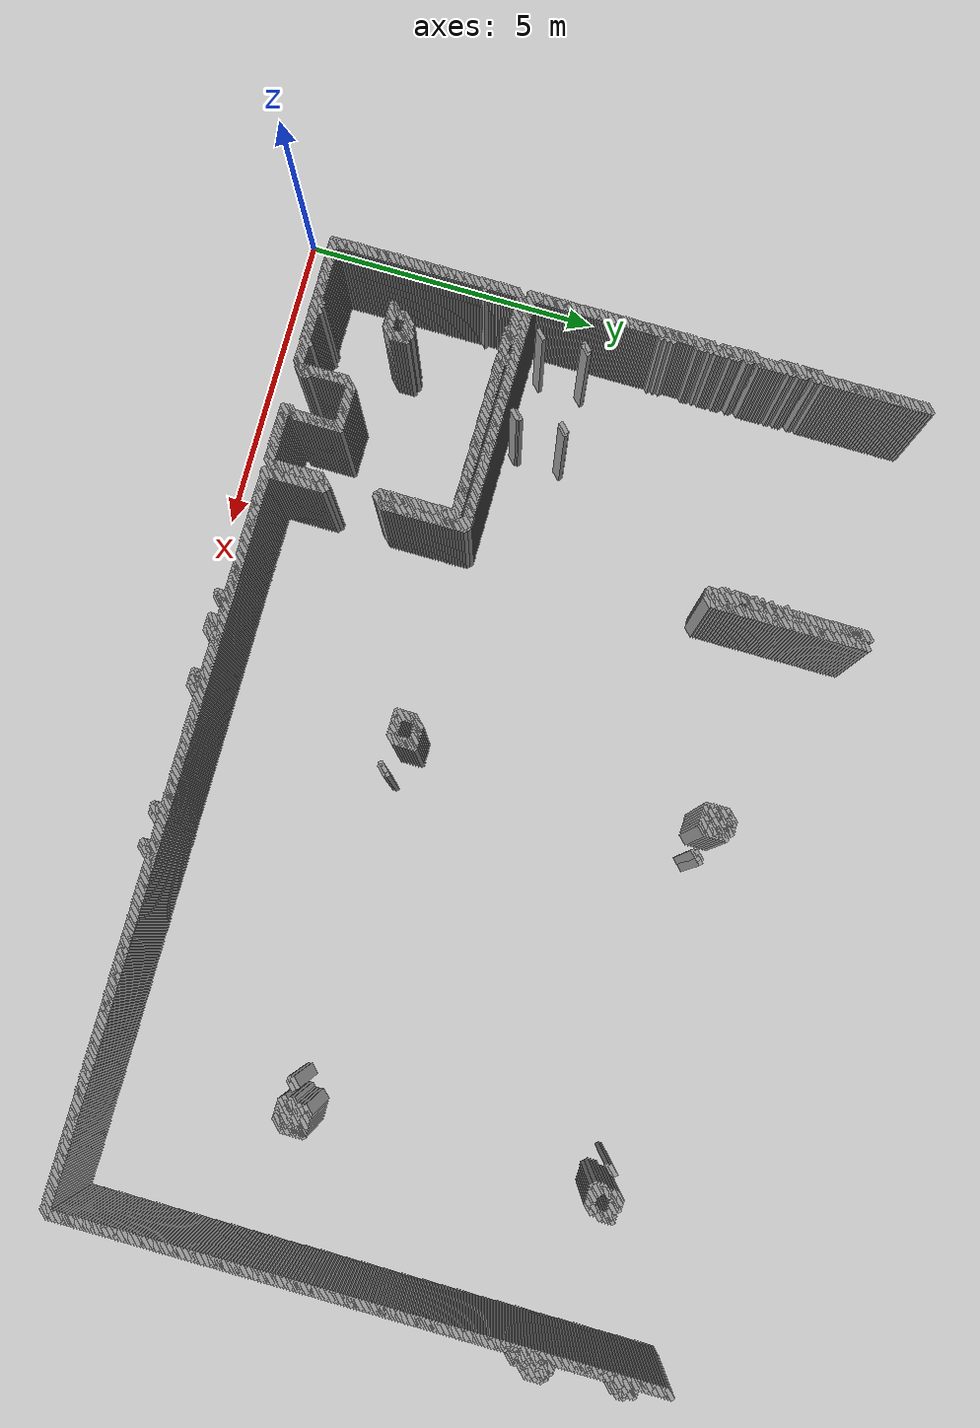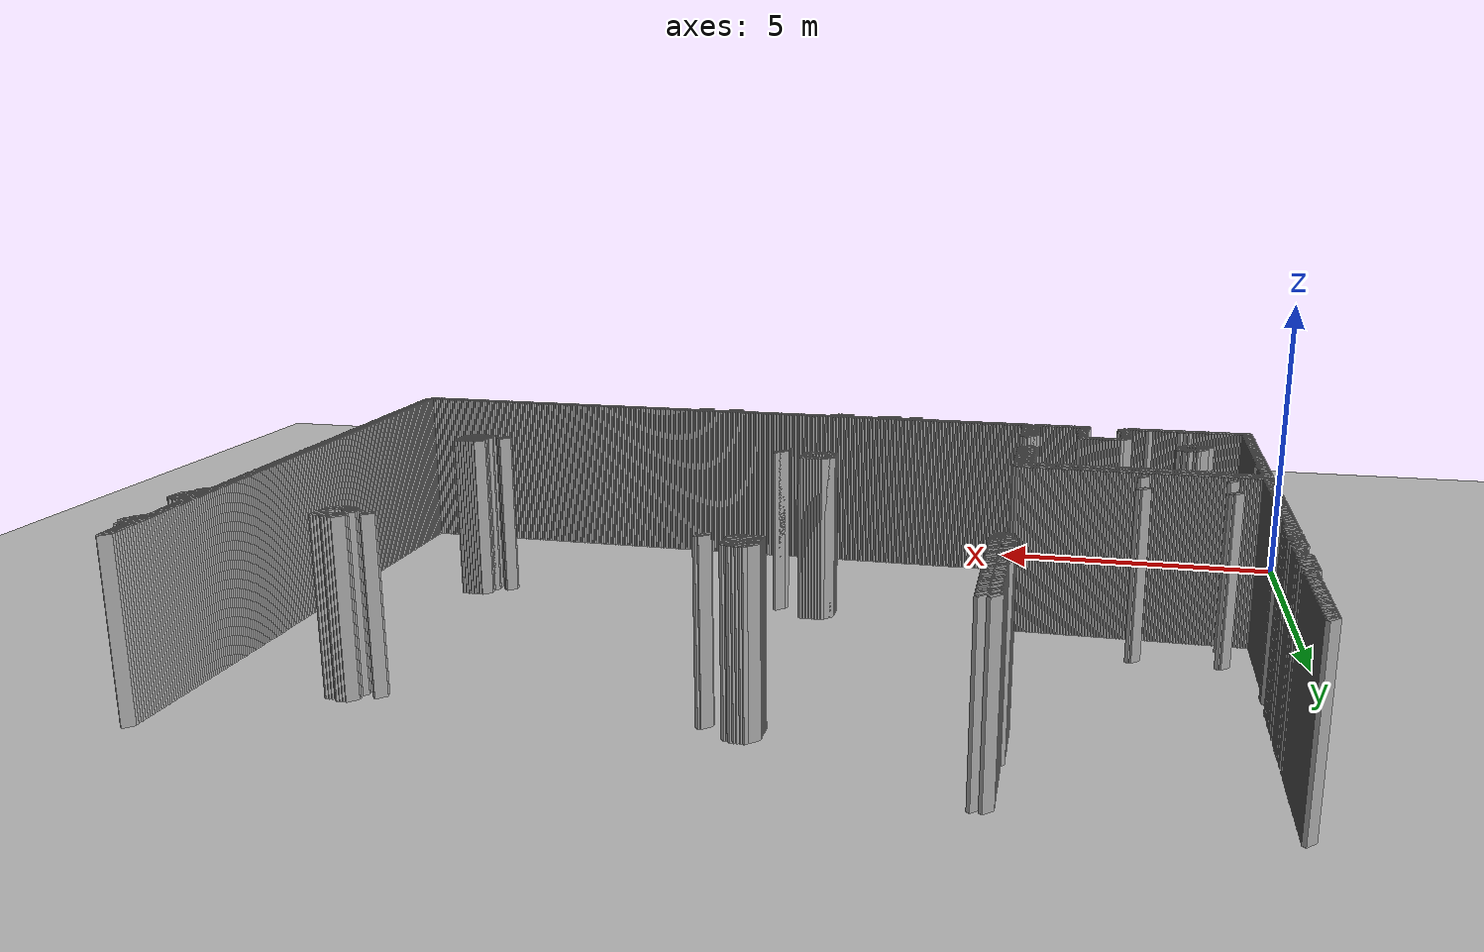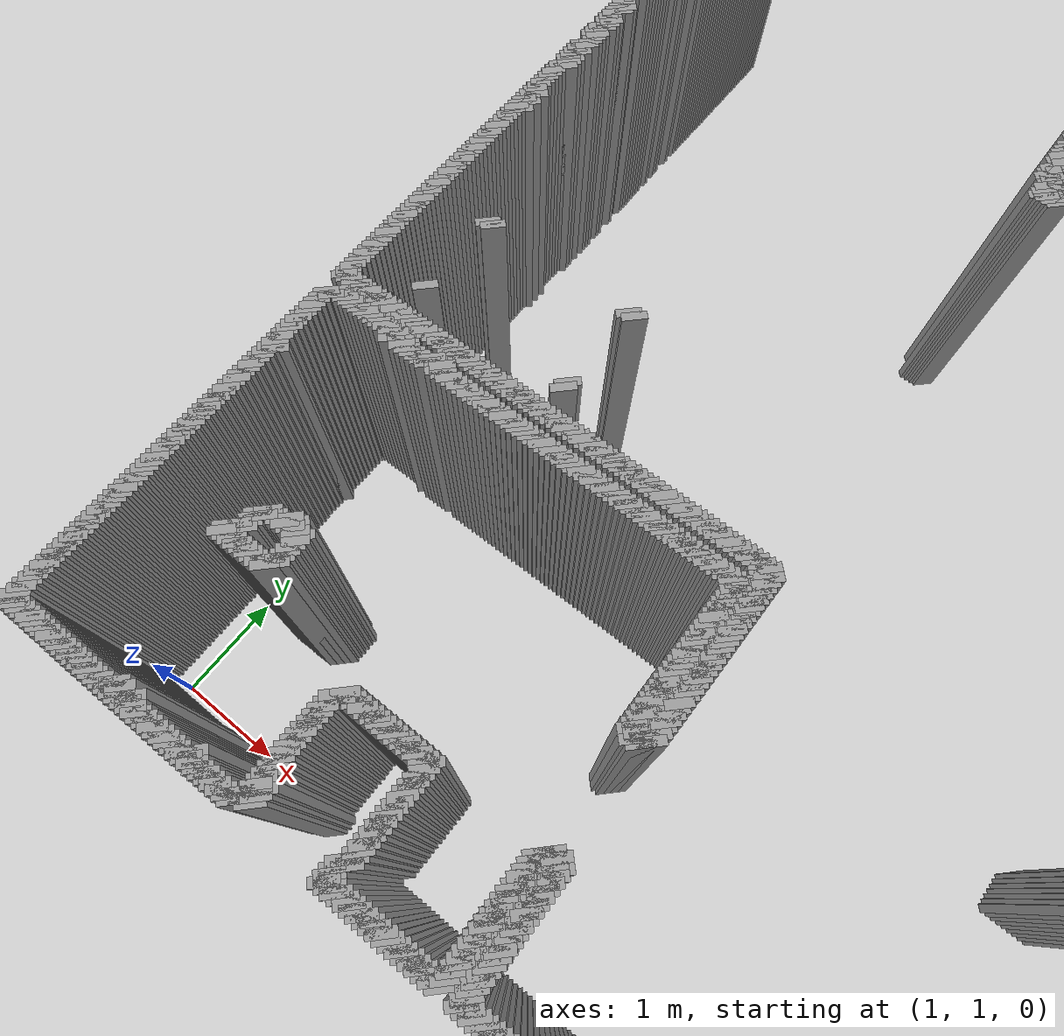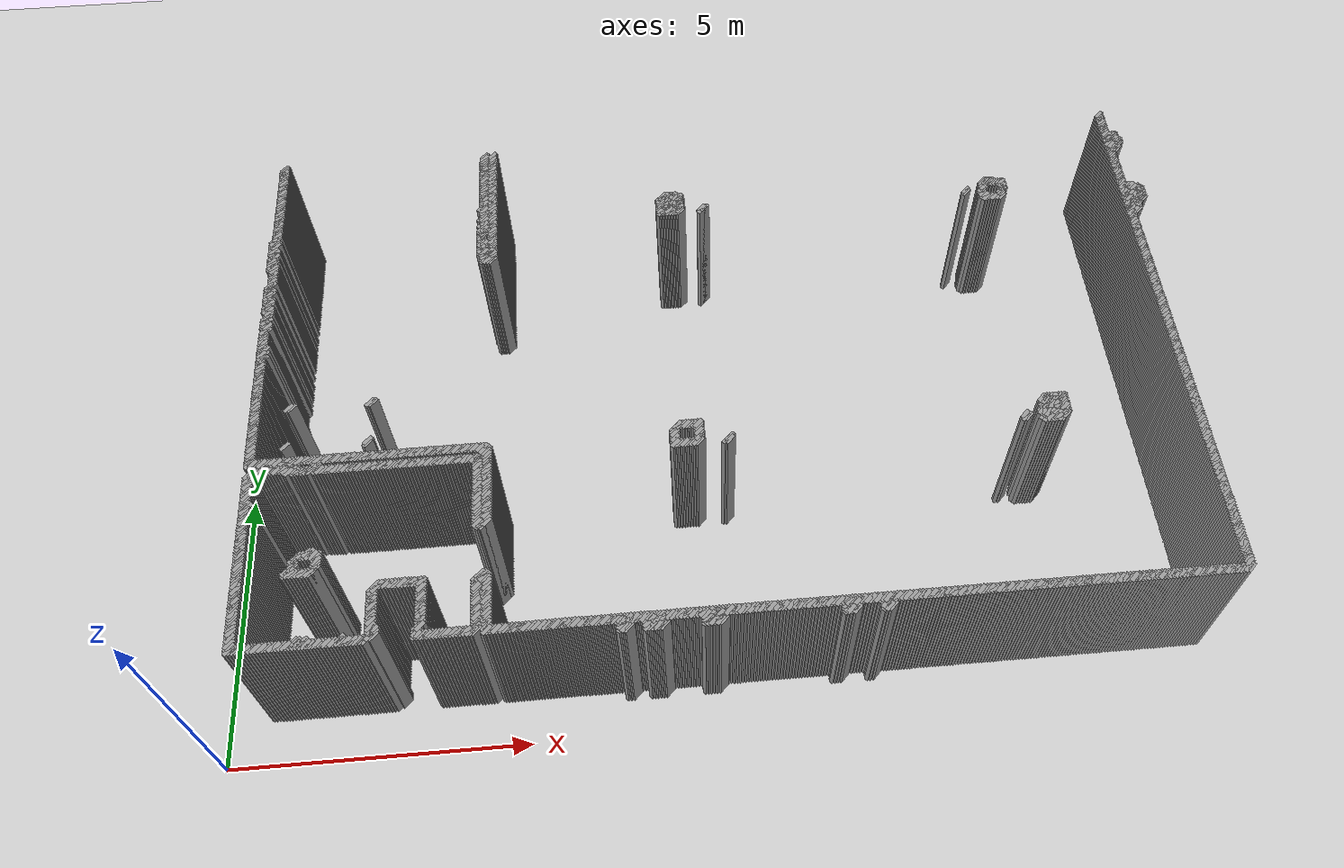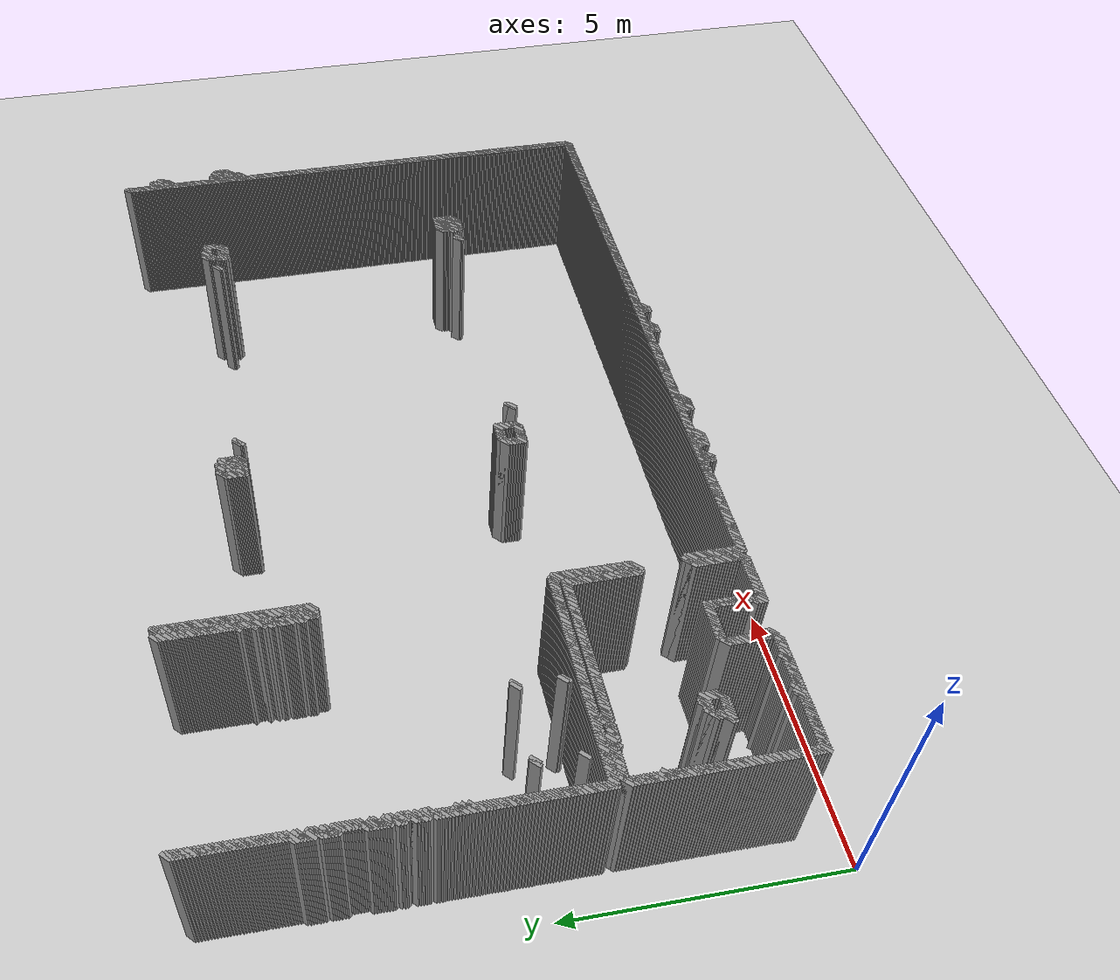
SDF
<sdf version="1.5">
 <world name="default">
  <include><uri>model://ground_plane</uri></include>
  <include><uri>model://sun</uri></include>
  <model name="grey_wall_1479">
   <static>1</static>
   <link name="link">
    <pose>16.45 10.65  1.4 0 0 -0.7853981633974838</pose>
    <collision name="collision">
     <geometry><box><size>0.07071067811865325 .2  2.8</size></box></geometry>
    </collision>
    <visual name="visual">
     <cast_shadows>0</cast_shadows>
     <geometry><box><size>0.07071067811865325 .2  2.8</size></box></geometry>
     <material>
      <script>
       <uri>model://grey_wall/materials/scripts</uri>
       <uri>model://grey_wall/materials/textures</uri>
       <name>vrc/grey_wall</name>
      </script>
     </material>
    </visual>
   </link>
  </model>
  <model name="grey_wall_1480">
   <static>1</static>
   <link name="link">
    <pose>0.8 10.600000000000001  1.4 0 0 -0.7853981633974549</pose>
    <collision name="collision">
     <geometry><box><size>0.07071067811865529 .2  2.8</size></box></geometry>
    </collision>
    <visual name="visual">
     <cast_shadows>0</cast_shadows>
     <geometry><box><size>0.07071067811865529 .2  2.8</size></box></geometry>
     <material>
      <script>
       <uri>model://grey_wall/materials/scripts</uri>
       <uri>model://grey_wall/materials/textures</uri>
       <name>vrc/grey_wall</name>
      </script>
     </material>
    </visual>
   </link>
  </model>
  <model name="grey_wall_1481">
   <static>1</static>
   <link name="link">
    <pose>4.55 10.600000000000001  1.4 0 0 -0.7853981633974483</pose>
    <collision name="collision">
     <geometry><box><size>0.07071067811865576 .2  2.8</size></box></geometry>
    </collision>
    <visual name="visual">
     <cast_shadows>0</cast_shadows>
     <geometry><box><size>0.07071067811865576 .2  2.8</size></box></geometry>
     <material>
      <script>
       <uri>model://grey_wall/materials/scripts</uri>
       <uri>model://grey_wall/materials/textures</uri>
       <name>vrc/grey_wall</name>
      </script>
     </material>
    </visual>
   </link>
  </model>
  <model name="grey_wall_1482">
   <static>1</static>
   <link name="link">
    <pose>4.7 10.600000000000001  1.4 0 0 -0.7853981633974483</pose>
    <collision name="collision">
     <geometry><box><size>0.07071067811865576 .2  2.8</size></box></geometry>
    </collision>
    <visual name="visual">
     <cast_shadows>0</cast_shadows>
     <geometry><box><size>0.07071067811865576 .2  2.8</size></box></geometry>
     <material>
      <script>
       <uri>model://grey_wall/materials/scripts</uri>
       <uri>model://grey_wall/materials/textures</uri>
       <name>vrc/grey_wall</name>
      </script>
     </material>
    </visual>
   </link>
  </model>
  <model name="grey_wall_1483">
   <static>1</static>
   <link name="link">
    <pose>16.45 10.600000000000001  1.4 0 0 -0.7853981633974838</pose>
    <collision name="collision">
     <geometry><box><size>0.07071067811865325 .2  2.8</size></box></geometry>
    </collision>
    <visual name="visual">
     <cast_shadows>0</cast_shadows>
     <geometry><box><size>0.07071067811865325 .2  2.8</size></box></geometry>
     <material>
      <script>
       <uri>model://grey_wall/materials/scripts</uri>
       <uri>model://grey_wall/materials/textures</uri>
       <name>vrc/grey_wall</name>
      </script>
     </material>
    </visual>
   </link>
  </model>
  <model name="grey_wall_1484">
   <static>1</static>
   <link name="link">
    <pose>0.8 10.55  1.4 0 0 -0.7853981633974549</pose>
    <collision name="collision">
     <geometry><box><size>0.07071067811865529 .2  2.8</size></box></geometry>
    </collision>
    <visual name="visual">
     <cast_shadows>0</cast_shadows>
     <geometry><box><size>0.07071067811865529 .2  2.8</size></box></geometry>
     <material>
      <script>
       <uri>model://grey_wall/materials/scripts</uri>
       <uri>model://grey_wall/materials/textures</uri>
       <name>vrc/grey_wall</name>
      </script>
     </material>
    </visual>
   </link>
  </model>
  <model name="grey_wall_1485">
   <static>1</static>
   <link name="link">
    <pose>4.55 10.55  1.4 0 0 -0.7853981633974483</pose>
    <collision name="collision">
     <geometry><box><size>0.07071067811865576 .2  2.8</size></box></geometry>
    </collision>
    <visual name="visual">
     <cast_shadows>0</cast_shadows>
     <geometry><box><size>0.07071067811865576 .2  2.8</size></box></geometry>
     <material>
      <script>
       <uri>model://grey_wall/materials/scripts</uri>
       <uri>model://grey_wall/materials/textures</uri>
       <name>vrc/grey_wall</name>
      </script>
     </material>
    </visual>
   </link>
  </model>
  <model name="grey_wall_1486">
   <static>1</static>
   <link name="link">
    <pose>4.7 10.55  1.4 0 0 -0.7853981633974483</pose>
    <collision name="collision">
     <geometry><box><size>0.07071067811865576 .2  2.8</size></box></geometry>
    </collision>
    <visual name="visual">
     <cast_shadows>0</cast_shadows>
     <geometry><box><size>0.07071067811865576 .2  2.8</size></box></geometry>
     <material>
      <script>
       <uri>model://grey_wall/materials/scripts</uri>
       <uri>model://grey_wall/materials/textures</uri>
       <name>vrc/grey_wall</name>
      </script>
     </material>
    </visual>
   </link>
  </model>
  <model name="grey_wall_1487">
   <static>1</static>
   <link name="link">
    <pose>16.45 10.55  1.4 0 0 -0.7853981633974838</pose>
    <collision name="collision">
     <geometry><box><size>0.07071067811865325 .2  2.8</size></box></geometry>
    </collision>
    <visual name="visual">
     <cast_shadows>0</cast_shadows>
     <geometry><box><size>0.07071067811865325 .2  2.8</size></box></geometry>
     <material>
      <script>
       <uri>model://grey_wall/materials/scripts</uri>
       <uri>model://grey_wall/materials/textures</uri>
       <name>vrc/grey_wall</name>
      </script>
     </material>
    </visual>
   </link>
  </model>
  <model name="grey_wall_1488">
   <static>1</static>
   <link name="link">
    <pose>0.8 10.5  1.4 0 0 -0.7853981633974549</pose>
    <collision name="collision">
     <geometry><box><size>0.07071067811865529 .2  2.8</size></box></geometry>
    </collision>
    <visual name="visual">
     <cast_shadows>0</cast_shadows>
     <geometry><box><size>0.07071067811865529 .2  2.8</size></box></geometry>
     <material>
      <script>
       <uri>model://grey_wall/materials/scripts</uri>
       <uri>model://grey_wall/materials/textures</uri>
       <name>vrc/grey_wall</name>
      </script>
     </material>
    </visual>
   </link>
  </model>
  <model name="grey_wall_1489">
   <static>1</static>
   <link name="link">
    <pose>4.55 10.5  1.4 0 0 -0.7853981633974483</pose>
    <collision name="collision">
     <geometry><box><size>0.07071067811865576 .2  2.8</size></box></geometry>
    </collision>
    <visual name="visual">
     <cast_shadows>0</cast_shadows>
     <geometry><box><size>0.07071067811865576 .2  2.8</size></box></geometry>
     <material>
      <script>
       <uri>model://grey_wall/materials/scripts</uri>
       <uri>model://grey_wall/materials/textures</uri>
       <name>vrc/grey_wall</name>
      </script>
     </material>
    </visual>
   </link>
  </model>
  <model name="grey_wall_1490">
   <static>1</static>
   <link name="link">
    <pose>4.7 10.5  1.4 0 0 -0.7853981633974483</pose>
    <collision name="collision">
     <geometry><box><size>0.07071067811865576 .2  2.8</size></box></geometry>
    </collision>
    <visual name="visual">
     <cast_shadows>0</cast_shadows>
     <geometry><box><size>0.07071067811865576 .2  2.8</size></box></geometry>
     <material>
      <script>
       <uri>model://grey_wall/materials/scripts</uri>
       <uri>model://grey_wall/materials/textures</uri>
       <name>vrc/grey_wall</name>
      </script>
     </material>
    </visual>
   </link>
  </model>
  <model name="grey_wall_1491">
   <static>1</static>
   <link name="link">
    <pose>16.45 10.5  1.4 0 0 -0.7853981633974838</pose>
    <collision name="collision">
     <geometry><box><size>0.07071067811865325 .2  2.8</size></box></geometry>
    </collision>
    <visual name="visual">
     <cast_shadows>0</cast_shadows>
     <geometry><box><size>0.07071067811865325 .2  2.8</size></box></geometry>
     <material>
      <script>
       <uri>model://grey_wall/materials/scripts</uri>
       <uri>model://grey_wall/materials/textures</uri>
       <name>vrc/grey_wall</name>
      </script>
     </material>
    </visual>
   </link>
  </model>
  <model name="grey_wall_1492">
   <static>1</static>
   <link name="link">
    <pose>0.8 10.450000000000001  1.4 0 0 -0.7853981633974549</pose>
    <collision name="collision">
     <geometry><box><size>0.07071067811865529 .2  2.8</size></box></geometry>
    </collision>
    <visual name="visual">
     <cast_shadows>0</cast_shadows>
     <geometry><box><size>0.07071067811865529 .2  2.8</size></box></geometry>
     <material>
      <script>
       <uri>model://grey_wall/materials/scripts</uri>
       <uri>model://grey_wall/materials/textures</uri>
       <name>vrc/grey_wall</name>
      </script>
     </material>
    </visual>
   </link>
  </model>
  <model name="grey_wall_1493">
   <static>1</static>
   <link name="link">
    <pose>4.55 10.450000000000001  1.4 0 0 -0.7853981633974483</pose>
    <collision name="collision">
     <geometry><box><size>0.07071067811865576 .2  2.8</size></box></geometry>
    </collision>
    <visual name="visual">
     <cast_shadows>0</cast_shadows>
     <geometry><box><size>0.07071067811865576 .2  2.8</size></box></geometry>
     <material>
      <script>
       <uri>model://grey_wall/materials/scripts</uri>
       <uri>model://grey_wall/materials/textures</uri>
       <name>vrc/grey_wall</name>
      </script>
     </material>
    </visual>
   </link>
  </model>
  <model name="grey_wall_1494">
   <static>1</static>
   <link name="link">
    <pose>4.7 10.450000000000001  1.4 0 0 -0.7853981633974483</pose>
    <collision name="collision">
     <geometry><box><size>0.07071067811865576 .2  2.8</size></box></geometry>
    </collision>
    <visual name="visual">
     <cast_shadows>0</cast_shadows>
     <geometry><box><size>0.07071067811865576 .2  2.8</size></box></geometry>
     <material>
      <script>
       <uri>model://grey_wall/materials/scripts</uri>
       <uri>model://grey_wall/materials/textures</uri>
       <name>vrc/grey_wall</name>
      </script>
     </material>
    </visual>
   </link>
  </model>
  <model name="grey_wall_1495">
   <static>1</static>
   <link name="link">
    <pose>16.45 10.450000000000001  1.4 0 0 -0.7853981633974838</pose>
    <collision name="collision">
     <geometry><box><size>0.07071067811865325 .2  2.8</size></box></geometry>
    </collision>
    <visual name="visual">
     <cast_shadows>0</cast_shadows>
     <geometry><box><size>0.07071067811865325 .2  2.8</size></box></geometry>
     <material>
      <script>
       <uri>model://grey_wall/materials/scripts</uri>
       <uri>model://grey_wall/materials/textures</uri>
       <name>vrc/grey_wall</name>
      </script>
     </material>
    </visual>
   </link>
  </model>
  <model name="grey_wall_1496">
   <static>1</static>
   <link name="link">
    <pose>0.8 10.4  1.4 0 0 -0.7853981633974549</pose>
    <collision name="collision">
     <geometry><box><size>0.07071067811865529 .2  2.8</size></box></geometry>
    </collision>
    <visual name="visual">
     <cast_shadows>0</cast_shadows>
     <geometry><box><size>0.07071067811865529 .2  2.8</size></box></geometry>
     <material>
      <script>
       <uri>model://grey_wall/materials/scripts</uri>
       <uri>model://grey_wall/materials/textures</uri>
       <name>vrc/grey_wall</name>
      </script>
     </material>
    </visual>
   </link>
  </model>
  <model name="grey_wall_1497">
   <static>1</static>
   <link name="link">
    <pose>4.55 10.4  1.4 0 0 -0.7853981633974483</pose>
    <collision name="collision">
     <geometry><box><size>0.07071067811865576 .2  2.8</size></box></geometry>
    </collision>
    <visual name="visual">
     <cast_shadows>0</cast_shadows>
     <geometry><box><size>0.07071067811865576 .2  2.8</size></box></geometry>
     <material>
      <script>
       <uri>model://grey_wall/materials/scripts</uri>
       <uri>model://grey_wall/materials/textures</uri>
       <name>vrc/grey_wall</name>
      </script>
     </material>
    </visual>
   </link>
  </model>
  <model name="grey_wall_1498">
   <static>1</static>
   <link name="link">
    <pose>4.7 10.4  1.4 0 0 -0.7853981633974483</pose>
    <collision name="collision">
     <geometry><box><size>0.07071067811865576 .2  2.8</size></box></geometry>
    </collision>
    <visual name="visual">
     <cast_shadows>0</cast_shadows>
     <geometry><box><size>0.07071067811865576 .2  2.8</size></box></geometry>
     <material>
      <script>
       <uri>model://grey_wall/materials/scripts</uri>
       <uri>model://grey_wall/materials/textures</uri>
       <name>vrc/grey_wall</name>
      </script>
     </material>
    </visual>
   </link>
  </model>
  <model name="grey_wall_1499">
   <static>1</static>
   <link name="link">
    <pose>16.45 10.4  1.4 0 0 -0.7853981633974838</pose>
    <collision name="collision">
     <geometry><box><size>0.07071067811865325 .2  2.8</size></box></geometry>
    </collision>
    <visual name="visual">
     <cast_shadows>0</cast_shadows>
     <geometry><box><size>0.07071067811865325 .2  2.8</size></box></geometry>
     <material>
      <script>
       <uri>model://grey_wall/materials/scripts</uri>
       <uri>model://grey_wall/materials/textures</uri>
       <name>vrc/grey_wall</name>
      </script>
     </material>
    </visual>
   </link>
  </model>
  <model name="grey_wall_1500">
   <static>1</static>
   <link name="link">
    <pose>0.8 10.350000000000001  1.4 0 0 -0.7853981633974549</pose>
    <collision name="collision">
     <geometry><box><size>0.07071067811865529 .2  2.8</size></box></geometry>
    </collision>
    <visual name="visual">
     <cast_shadows>0</cast_shadows>
     <geometry><box><size>0.07071067811865529 .2  2.8</size></box></geometry>
     <material>
      <script>
       <uri>model://grey_wall/materials/scripts</uri>
       <uri>model://grey_wall/materials/textures</uri>
       <name>vrc/grey_wall</name>
      </script>
     </material>
    </visual>
   </link>
  </model>
  <model name="grey_wall_1501">
   <static>1</static>
   <link name="link">
    <pose>4.55 10.350000000000001  1.4 0 0 -0.7853981633974483</pose>
    <collision name="collision">
     <geometry><box><size>0.07071067811865576 .2  2.8</size></box></geometry>
    </collision>
    <visual name="visual">
     <cast_shadows>0</cast_shadows>
     <geometry><box><size>0.07071067811865576 .2  2.8</size></box></geometry>
     <material>
      <script>
       <uri>model://grey_wall/materials/scripts</uri>
       <uri>model://grey_wall/materials/textures</uri>
       <name>vrc/grey_wall</name>
      </script>
     </material>
    </visual>
   </link>
  </model>
  <model name="grey_wall_1502">
   <static>1</static>
   <link name="link">
    <pose>4.7 10.350000000000001  1.4 0 0 -0.7853981633974483</pose>
    <collision name="collision">
     <geometry><box><size>0.07071067811865576 .2  2.8</size></box></geometry>
    </collision>
    <visual name="visual">
     <cast_shadows>0</cast_shadows>
     <geometry><box><size>0.07071067811865576 .2  2.8</size></box></geometry>
     <material>
      <script>
       <uri>model://grey_wall/materials/scripts</uri>
       <uri>model://grey_wall/materials/textures</uri>
       <name>vrc/grey_wall</name>
      </script>
     </material>
    </visual>
   </link>
  </model>
  <model name="grey_wall_1503">
   <static>1</static>
   <link name="link">
    <pose>16.45 10.350000000000001  1.4 0 0 -0.7853981633974838</pose>
    <collision name="collision">
     <geometry><box><size>0.07071067811865325 .2  2.8</size></box></geometry>
    </collision>
    <visual name="visual">
     <cast_shadows>0</cast_shadows>
     <geometry><box><size>0.07071067811865325 .2  2.8</size></box></geometry>
     <material>
      <script>
       <uri>model://grey_wall/materials/scripts</uri>
       <uri>model://grey_wall/materials/textures</uri>
       <name>vrc/grey_wall</name>
      </script>
     </material>
    </visual>
   </link>
  </model>
  <model name="grey_wall_1504">
   <static>1</static>
   <link name="link">
    <pose>0.8 10.3  1.4 0 0 -0.7853981633974549</pose>
    <collision name="collision">
     <geometry><box><size>0.07071067811865529 .2  2.8</size></box></geometry>
    </collision>
    <visual name="visual">
     <cast_shadows>0</cast_shadows>
     <geometry><box><size>0.07071067811865529 .2  2.8</size></box></geometry>
     <material>
      <script>
       <uri>model://grey_wall/materials/scripts</uri>
       <uri>model://grey_wall/materials/textures</uri>
       <name>vrc/grey_wall</name>
      </script>
     </material>
    </visual>
   </link>
  </model>
  <model name="grey_wall_1505">
   <static>1</static>
   <link name="link">
    <pose>4.55 10.3  1.4 0 0 -0.7853981633974483</pose>
    <collision name="collision">
     <geometry><box><size>0.07071067811865576 .2  2.8</size></box></geometry>
    </collision>
    <visual name="visual">
     <cast_shadows>0</cast_shadows>
     <geometry><box><size>0.07071067811865576 .2  2.8</size></box></geometry>
     <material>
      <script>
       <uri>model://grey_wall/materials/scripts</uri>
       <uri>model://grey_wall/materials/textures</uri>
       <name>vrc/grey_wall</name>
      </script>
     </material>
    </visual>
   </link>
  </model>
  <model name="grey_wall_1506">
   <static>1</static>
   <link name="link">
    <pose>4.7 10.3  1.4 0 0 -0.7853981633974483</pose>
    <collision name="collision">
     <geometry><box><size>0.07071067811865576 .2  2.8</size></box></geometry>
    </collision>
    <visual name="visual">
     <cast_shadows>0</cast_shadows>
     <geometry><box><size>0.07071067811865576 .2  2.8</size></box></geometry>
     <material>
      <script>
       <uri>model://grey_wall/materials/scripts</uri>
       <uri>model://grey_wall/materials/textures</uri>
       <name>vrc/grey_wall</name>
      </script>
     </material>
    </visual>
   </link>
  </model>
  <model name="grey_wall_1507">
   <static>1</static>
   <link name="link">
    <pose>16.45 10.3  1.4 0 0 -0.7853981633974838</pose>
    <collision name="collision">
     <geometry><box><size>0.07071067811865325 .2  2.8</size></box></geometry>
    </collision>
    <visual name="visual">
     <cast_shadows>0</cast_shadows>
     <geometry><box><size>0.07071067811865325 .2  2.8</size></box></geometry>
     <material>
      <script>
       <uri>model://grey_wall/materials/scripts</uri>
       <uri>model://grey_wall/materials/textures</uri>
       <name>vrc/grey_wall</name>
      </script>
     </material>
    </visual>
   </link>
  </model>
  <model name="grey_wall_1508">
   <static>1</static>
   <link name="link">
    <pose>0.8 10.25  1.4 0 0 -0.7853981633974549</pose>
    <collision name="collision">
     <geometry><box><size>0.07071067811865529 .2  2.8</size></box></geometry>
    </collision>
    <visual name="visual">
     <cast_shadows>0</cast_shadows>
     <geometry><box><size>0.07071067811865529 .2  2.8</size></box></geometry>
     <material>
      <script>
       <uri>model://grey_wall/materials/scripts</uri>
       <uri>model://grey_wall/materials/textures</uri>
       <name>vrc/grey_wall</name>
      </script>
     </material>
    </visual>
   </link>
  </model>
  <model name="grey_wall_1509">
   <static>1</static>
   <link name="link">
    <pose>4.55 10.25  1.4 0 0 -0.7853981633974483</pose>
    <collision name="collision">
     <geometry><box><size>0.07071067811865576 .2  2.8</size></box></geometry>
    </collision>
    <visual name="visual">
     <cast_shadows>0</cast_shadows>
     <geometry><box><size>0.07071067811865576 .2  2.8</size></box></geometry>
     <material>
      <script>
       <uri>model://grey_wall/materials/scripts</uri>
       <uri>model://grey_wall/materials/textures</uri>
       <name>vrc/grey_wall</name>
      </script>
     </material>
    </visual>
   </link>
  </model>
  <model name="grey_wall_1510">
   <static>1</static>
   <link name="link">
    <pose>4.7 10.25  1.4 0 0 -0.7853981633974483</pose>
    <collision name="collision">
     <geometry><box><size>0.07071067811865576 .2  2.8</size></box></geometry>
    </collision>
    <visual name="visual">
     <cast_shadows>0</cast_shadows>
     <geometry><box><size>0.07071067811865576 .2  2.8</size></box></geometry>
     <material>
      <script>
       <uri>model://grey_wall/materials/scripts</uri>
       <uri>model://grey_wall/materials/textures</uri>
       <name>vrc/grey_wall</name>
      </script>
     </material>
    </visual>
   </link>
  </model>
  <model name="grey_wall_1511">
   <static>1</static>
   <link name="link">
    <pose>16.45 10.25  1.4 0 0 -0.7853981633974838</pose>
    <collision name="collision">
     <geometry><box><size>0.07071067811865325 .2  2.8</size></box></geometry>
    </collision>
    <visual name="visual">
     <cast_shadows>0</cast_shadows>
     <geometry><box><size>0.07071067811865325 .2  2.8</size></box></geometry>
     <material>
      <script>
       <uri>model://grey_wall/materials/scripts</uri>
       <uri>model://grey_wall/materials/textures</uri>
       <name>vrc/grey_wall</name>
      </script>
     </material>
    </visual>
   </link>
  </model>
  <model name="grey_wall_1512">
   <static>1</static>
   <link name="link">
    <pose>0.8 10.200000000000001  1.4 0 0 -0.7853981633974549</pose>
    <collision name="collision">
     <geometry><box><size>0.07071067811865529 .2  2.8</size></box></geometry>
    </collision>
    <visual name="visual">
     <cast_shadows>0</cast_shadows>
     <geometry><box><size>0.07071067811865529 .2  2.8</size></box></geometry>
     <material>
      <script>
       <uri>model://grey_wall/materials/scripts</uri>
       <uri>model://grey_wall/materials/textures</uri>
       <name>vrc/grey_wall</name>
      </script>
     </material>
    </visual>
   </link>
  </model>
  <model name="grey_wall_1513">
   <static>1</static>
   <link name="link">
    <pose>4.55 10.200000000000001  1.4 0 0 -0.7853981633974483</pose>
    <collision name="collision">
     <geometry><box><size>0.07071067811865576 .2  2.8</size></box></geometry>
    </collision>
    <visual name="visual">
     <cast_shadows>0</cast_shadows>
     <geometry><box><size>0.07071067811865576 .2  2.8</size></box></geometry>
     <material>
      <script>
       <uri>model://grey_wall/materials/scripts</uri>
       <uri>model://grey_wall/materials/textures</uri>
       <name>vrc/grey_wall</name>
      </script>
     </material>
    </visual>
   </link>
  </model>
  <model name="grey_wall_1514">
   <static>1</static>
   <link name="link">
    <pose>4.7 10.200000000000001  1.4 0 0 -0.7853981633974483</pose>
    <collision name="collision">
     <geometry><box><size>0.07071067811865576 .2  2.8</size></box></geometry>
    </collision>
    <visual name="visual">
     <cast_shadows>0</cast_shadows>
     <geometry><box><size>0.07071067811865576 .2  2.8</size></box></geometry>
     <material>
      <script>
       <uri>model://grey_wall/materials/scripts</uri>
       <uri>model://grey_wall/materials/textures</uri>
       <name>vrc/grey_wall</name>
      </script>
     </material>
    </visual>
   </link>
  </model>
  <model name="grey_wall_1515">
   <static>1</static>
   <link name="link">
    <pose>16.45 10.200000000000001  1.4 0 0 -0.7853981633974838</pose>
    <collision name="collision">
     <geometry><box><size>0.07071067811865325 .2  2.8</size></box></geometry>
    </collision>
    <visual name="visual">
     <cast_shadows>0</cast_shadows>
     <geometry><box><size>0.07071067811865325 .2  2.8</size></box></geometry>
     <material>
      <script>
       <uri>model://grey_wall/materials/scripts</uri>
       <uri>model://grey_wall/materials/textures</uri>
       <name>vrc/grey_wall</name>
      </script>
     </material>
    </visual>
   </link>
  </model>
  <model name="grey_wall_1516">
   <static>1</static>
   <link name="link">
    <pose>0.8 10.15  1.4 0 0 -0.7853981633974549</pose>
    <collision name="collision">
     <geometry><box><size>0.07071067811865529 .2  2.8</size></box></geometry>
    </collision>
    <visual name="visual">
     <cast_shadows>0</cast_shadows>
     <geometry><box><size>0.07071067811865529 .2  2.8</size></box></geometry>
     <material>
      <script>
       <uri>model://grey_wall/materials/scripts</uri>
       <uri>model://grey_wall/materials/textures</uri>
       <name>vrc/grey_wall</name>
      </script>
     </material>
    </visual>
   </link>
  </model>
  <model name="grey_wall_1517">
   <static>1</static>
   <link name="link">
    <pose>4.55 10.15  1.4 0 0 -0.7853981633974483</pose>
    <collision name="collision">
     <geometry><box><size>0.07071067811865576 .2  2.8</size></box></geometry>
    </collision>
    <visual name="visual">
     <cast_shadows>0</cast_shadows>
     <geometry><box><size>0.07071067811865576 .2  2.8</size></box></geometry>
     <material>
      <script>
       <uri>model://grey_wall/materials/scripts</uri>
       <uri>model://grey_wall/materials/textures</uri>
       <name>vrc/grey_wall</name>
      </script>
     </material>
    </visual>
   </link>
  </model>
  <model name="grey_wall_1518">
   <static>1</static>
   <link name="link">
    <pose>4.7 10.15  1.4 0 0 -0.7853981633974483</pose>
    <collision name="collision">
     <geometry><box><size>0.07071067811865576 .2  2.8</size></box></geometry>
    </collision>
    <visual name="visual">
     <cast_shadows>0</cast_shadows>
     <geometry><box><size>0.07071067811865576 .2  2.8</size></box></geometry>
     <material>
      <script>
       <uri>model://grey_wall/materials/scripts</uri>
       <uri>model://grey_wall/materials/textures</uri>
       <name>vrc/grey_wall</name>
      </script>
     </material>
    </visual>
   </link>
  </model>
  <model name="grey_wall_1519">
   <static>1</static>
   <link name="link">
    <pose>16.45 10.15  1.4 0 0 -0.7853981633974838</pose>
    <collision name="collision">
     <geometry><box><size>0.07071067811865325 .2  2.8</size></box></geometry>
    </collision>
    <visual name="visual">
     <cast_shadows>0</cast_shadows>
     <geometry><box><size>0.07071067811865325 .2  2.8</size></box></geometry>
     <material>
      <script>
       <uri>model://grey_wall/materials/scripts</uri>
       <uri>model://grey_wall/materials/textures</uri>
       <name>vrc/grey_wall</name>
      </script>
     </material>
    </visual>
   </link>
  </model>
  <model name="grey_wall_1520">
   <static>1</static>
   <link name="link">
    <pose>0.8 10.100000000000001  1.4 0 0 -0.7853981633974549</pose>
    <collision name="collision">
     <geometry><box><size>0.07071067811865529 .2  2.8</size></box></geometry>
    </collision>
    <visual name="visual">
     <cast_shadows>0</cast_shadows>
     <geometry><box><size>0.07071067811865529 .2  2.8</size></box></geometry>
     <material>
      <script>
       <uri>model://grey_wall/materials/scripts</uri>
       <uri>model://grey_wall/materials/textures</uri>
       <name>vrc/grey_wall</name>
      </script>
     </material>
    </visual>
   </link>
  </model>
  <model name="grey_wall_1521">
   <static>1</static>
   <link name="link">
    <pose>4.55 10.100000000000001  1.4 0 0 -0.7853981633974483</pose>
    <collision name="collision">
     <geometry><box><size>0.07071067811865576 .2  2.8</size></box></geometry>
    </collision>
    <visual name="visual">
     <cast_shadows>0</cast_shadows>
     <geometry><box><size>0.07071067811865576 .2  2.8</size></box></geometry>
     <material>
      <script>
       <uri>model://grey_wall/materials/scripts</uri>
       <uri>model://grey_wall/materials/textures</uri>
       <name>vrc/grey_wall</name>
      </script>
     </material>
    </visual>
   </link>
  </model>
  <model name="grey_wall_1522">
   <static>1</static>
   <link name="link">
    <pose>4.7 10.100000000000001  1.4 0 0 -0.7853981633974483</pose>
    <collision name="collision">
     <geometry><box><size>0.07071067811865576 .2  2.8</size></box></geometry>
    </collision>
    <visual name="visual">
     <cast_shadows>0</cast_shadows>
     <geometry><box><size>0.07071067811865576 .2  2.8</size></box></geometry>
     <material>
      <script>
       <uri>model://grey_wall/materials/scripts</uri>
       <uri>model://grey_wall/materials/textures</uri>
       <name>vrc/grey_wall</name>
      </script>
     </material>
    </visual>
   </link>
  </model>
  <model name="grey_wall_1523">
   <static>1</static>
   <link name="link">
    <pose>16.45 10.100000000000001  1.4 0 0 -0.7853981633974838</pose>
    <collision name="collision">
     <geometry><box><size>0.07071067811865325 .2  2.8</size></box></geometry>
    </collision>
    <visual name="visual">
     <cast_shadows>0</cast_shadows>
     <geometry><box><size>0.07071067811865325 .2  2.8</size></box></geometry>
     <material>
      <script>
       <uri>model://grey_wall/materials/scripts</uri>
       <uri>model://grey_wall/materials/textures</uri>
       <name>vrc/grey_wall</name>
      </script>
     </material>
    </visual>
   </link>
  </model>
  <model name="grey_wall_1524">
   <static>1</static>
   <link name="link">
    <pose>16.5 10.100000000000001  1.4 0 0 -0.7853981633974838</pose>
    <collision name="collision">
     <geometry><box><size>0.07071067811865325 .2  2.8</size></box></geometry>
    </collision>
    <visual name="visual">
     <cast_shadows>0</cast_shadows>
     <geometry><box><size>0.07071067811865325 .2  2.8</size></box></geometry>
     <material>
      <script>
       <uri>model://grey_wall/materials/scripts</uri>
       <uri>model://grey_wall/materials/textures</uri>
       <name>vrc/grey_wall</name>
      </script>
     </material>
    </visual>
   </link>
  </model>
  <model name="grey_wall_1525">
   <static>1</static>
   <link name="link">
    <pose>16.55 10.100000000000001  1.4 0 0 -0.7853981633974838</pose>
    <collision name="collision">
     <geometry><box><size>0.07071067811865325 .2  2.8</size></box></geometry>
    </collision>
    <visual name="visual">
     <cast_shadows>0</cast_shadows>
     <geometry><box><size>0.07071067811865325 .2  2.8</size></box></geometry>
     <material>
      <script>
       <uri>model://grey_wall/materials/scripts</uri>
       <uri>model://grey_wall/materials/textures</uri>
       <name>vrc/grey_wall</name>
      </script>
     </material>
    </visual>
   </link>
  </model>
  <model name="grey_wall_1526">
   <static>1</static>
   <link name="link">
    <pose>16.6 10.100000000000001  1.4 0 0 -0.7853981633974838</pose>
    <collision name="collision">
     <geometry><box><size>0.07071067811865325 .2  2.8</size></box></geometry>
    </collision>
    <visual name="visual">
     <cast_shadows>0</cast_shadows>
     <geometry><box><size>0.07071067811865325 .2  2.8</size></box></geometry>
     <material>
      <script>
       <uri>model://grey_wall/materials/scripts</uri>
       <uri>model://grey_wall/materials/textures</uri>
       <name>vrc/grey_wall</name>
      </script>
     </material>
    </visual>
   </link>
  </model>
  <model name="grey_wall_1527">
   <static>1</static>
   <link name="link">
    <pose>0.8 10.05  1.4 0 0 -0.7853981633974549</pose>
    <collision name="collision">
     <geometry><box><size>0.07071067811865529 .2  2.8</size></box></geometry>
    </collision>
    <visual name="visual">
     <cast_shadows>0</cast_shadows>
     <geometry><box><size>0.07071067811865529 .2  2.8</size></box></geometry>
     <material>
      <script>
       <uri>model://grey_wall/materials/scripts</uri>
       <uri>model://grey_wall/materials/textures</uri>
       <name>vrc/grey_wall</name>
      </script>
     </material>
    </visual>
   </link>
  </model>
  <model name="grey_wall_1528">
   <static>1</static>
   <link name="link">
    <pose>4.55 10.05  1.4 0 0 -0.7853981633974483</pose>
    <collision name="collision">
     <geometry><box><size>0.07071067811865576 .2  2.8</size></box></geometry>
    </collision>
    <visual name="visual">
     <cast_shadows>0</cast_shadows>
     <geometry><box><size>0.07071067811865576 .2  2.8</size></box></geometry>
     <material>
      <script>
       <uri>model://grey_wall/materials/scripts</uri>
       <uri>model://grey_wall/materials/textures</uri>
       <name>vrc/grey_wall</name>
      </script>
     </material>
    </visual>
   </link>
  </model>
  <model name="grey_wall_1529">
   <static>1</static>
   <link name="link">
    <pose>4.7 10.05  1.4 0 0 -0.7853981633974483</pose>
    <collision name="collision">
     <geometry><box><size>0.07071067811865576 .2  2.8</size></box></geometry>
    </collision>
    <visual name="visual">
     <cast_shadows>0</cast_shadows>
     <geometry><box><size>0.07071067811865576 .2  2.8</size></box></geometry>
     <material>
      <script>
       <uri>model://grey_wall/materials/scripts</uri>
       <uri>model://grey_wall/materials/textures</uri>
       <name>vrc/grey_wall</name>
      </script>
     </material>
    </visual>
   </link>
  </model>
  <model name="grey_wall_1530">
   <static>1</static>
   <link name="link">
    <pose>16.45 10.05  1.4 0 0 -0.7853981633974838</pose>
    <collision name="collision">
     <geometry><box><size>0.07071067811865325 .2  2.8</size></box></geometry>
    </collision>
    <visual name="visual">
     <cast_shadows>0</cast_shadows>
     <geometry><box><size>0.07071067811865325 .2  2.8</size></box></geometry>
     <material>
      <script>
       <uri>model://grey_wall/materials/scripts</uri>
       <uri>model://grey_wall/materials/textures</uri>
       <name>vrc/grey_wall</name>
      </script>
     </material>
    </visual>
   </link>
  </model>
  <model name="grey_wall_1531">
   <static>1</static>
   <link name="link">
    <pose>16.5 10.05  1.4 0 0 -0.7853981633974838</pose>
    <collision name="collision">
     <geometry><box><size>0.07071067811865325 .2  2.8</size></box></geometry>
    </collision>
    <visual name="visual">
     <cast_shadows>0</cast_shadows>
     <geometry><box><size>0.07071067811865325 .2  2.8</size></box></geometry>
     <material>
      <script>
       <uri>model://grey_wall/materials/scripts</uri>
       <uri>model://grey_wall/materials/textures</uri>
       <name>vrc/grey_wall</name>
      </script>
     </material>
    </visual>
   </link>
  </model>
  <model name="grey_wall_1532">
   <static>1</static>
   <link name="link">
    <pose>16.6 10.05  1.4 0 0 -0.7853981633974838</pose>
    <collision name="collision">
     <geometry><box><size>0.07071067811865325 .2  2.8</size></box></geometry>
    </collision>
    <visual name="visual">
     <cast_shadows>0</cast_shadows>
     <geometry><box><size>0.07071067811865325 .2  2.8</size></box></geometry>
     <material>
      <script>
       <uri>model://grey_wall/materials/scripts</uri>
       <uri>model://grey_wall/materials/textures</uri>
       <name>vrc/grey_wall</name>
      </script>
     </material>
    </visual>
   </link>
  </model>
  <model name="grey_wall_1533">
   <static>1</static>
   <link name="link">
    <pose>0.8 10.0  1.4 0 0 -0.7853981633974549</pose>
    <collision name="collision">
     <geometry><box><size>0.07071067811865529 .2  2.8</size></box></geometry>
    </collision>
    <visual name="visual">
     <cast_shadows>0</cast_shadows>
     <geometry><box><size>0.07071067811865529 .2  2.8</size></box></geometry>
     <material>
      <script>
       <uri>model://grey_wall/materials/scripts</uri>
       <uri>model://grey_wall/materials/textures</uri>
       <name>vrc/grey_wall</name>
      </script>
     </material>
    </visual>
   </link>
  </model>
  <model name="grey_wall_1534">
   <static>1</static>
   <link name="link">
    <pose>4.55 10.0  1.4 0 0 -0.7853981633974483</pose>
    <collision name="collision">
     <geometry><box><size>0.07071067811865576 .2  2.8</size></box></geometry>
    </collision>
    <visual name="visual">
     <cast_shadows>0</cast_shadows>
     <geometry><box><size>0.07071067811865576 .2  2.8</size></box></geometry>
     <material>
      <script>
       <uri>model://grey_wall/materials/scripts</uri>
       <uri>model://grey_wall/materials/textures</uri>
       <name>vrc/grey_wall</name>
      </script>
     </material>
    </visual>
   </link>
  </model>
  <model name="grey_wall_1535">
   <static>1</static>
   <link name="link">
    <pose>4.7 10.0  1.4 0 0 -0.7853981633974483</pose>
    <collision name="collision">
     <geometry><box><size>0.07071067811865576 .2  2.8</size></box></geometry>
    </collision>
    <visual name="visual">
     <cast_shadows>0</cast_shadows>
     <geometry><box><size>0.07071067811865576 .2  2.8</size></box></geometry>
     <material>
      <script>
       <uri>model://grey_wall/materials/scripts</uri>
       <uri>model://grey_wall/materials/textures</uri>
       <name>vrc/grey_wall</name>
      </script>
     </material>
    </visual>
   </link>
  </model>
  <model name="grey_wall_1536">
   <static>1</static>
   <link name="link">
    <pose>16.45 10.0  1.4 0 0 -0.7853981633974838</pose>
    <collision name="collision">
     <geometry><box><size>0.07071067811865325 .2  2.8</size></box></geometry>
    </collision>
    <visual name="visual">
     <cast_shadows>0</cast_shadows>
     <geometry><box><size>0.07071067811865325 .2  2.8</size></box></geometry>
     <material>
      <script>
       <uri>model://grey_wall/materials/scripts</uri>
       <uri>model://grey_wall/materials/textures</uri>
       <name>vrc/grey_wall</name>
      </script>
     </material>
    </visual>
   </link>
  </model>
  <model name="grey_wall_1537">
   <static>1</static>
   <link name="link">
    <pose>16.5 10.0  1.4 0 0 -0.7853981633974838</pose>
    <collision name="collision">
     <geometry><box><size>0.07071067811865325 .2  2.8</size></box></geometry>
    </collision>
    <visual name="visual">
     <cast_shadows>0</cast_shadows>
     <geometry><box><size>0.07071067811865325 .2  2.8</size></box></geometry>
     <material>
      <script>
       <uri>model://grey_wall/materials/scripts</uri>
       <uri>model://grey_wall/materials/textures</uri>
       <name>vrc/grey_wall</name>
      </script>
     </material>
    </visual>
   </link>
  </model>
  <model name="grey_wall_1538">
   <static>1</static>
   <link name="link">
    <pose>16.55 10.0  1.4 0 0 -0.7853981633974838</pose>
    <collision name="collision">
     <geometry><box><size>0.07071067811865325 .2  2.8</size></box></geometry>
    </collision>
    <visual name="visual">
     <cast_shadows>0</cast_shadows>
     <geometry><box><size>0.07071067811865325 .2  2.8</size></box></geometry>
     <material>
      <script>
       <uri>model://grey_wall/materials/scripts</uri>
       <uri>model://grey_wall/materials/textures</uri>
       <name>vrc/grey_wall</name>
      </script>
     </material>
    </visual>
   </link>
  </model>
  <model name="grey_wall_1539">
   <static>1</static>
   <link name="link">
    <pose>16.6 10.0  1.4 0 0 -0.7853981633974838</pose>
    <collision name="collision">
     <geometry><box><size>0.07071067811865325 .2  2.8</size></box></geometry>
    </collision>
    <visual name="visual">
     <cast_shadows>0</cast_shadows>
     <geometry><box><size>0.07071067811865325 .2  2.8</size></box></geometry>
     <material>
      <script>
       <uri>model://grey_wall/materials/scripts</uri>
       <uri>model://grey_wall/materials/textures</uri>
       <name>vrc/grey_wall</name>
      </script>
     </material>
    </visual>
   </link>
  </model>
  <model name="grey_wall_1540">
   <static>1</static>
   <link name="link">
    <pose>0.8 9.950000000000001  1.4 0 0 -0.7853981633974549</pose>
    <collision name="collision">
     <geometry><box><size>0.07071067811865529 .2  2.8</size></box></geometry>
    </collision>
    <visual name="visual">
     <cast_shadows>0</cast_shadows>
     <geometry><box><size>0.07071067811865529 .2  2.8</size></box></geometry>
     <material>
      <script>
       <uri>model://grey_wall/materials/scripts</uri>
       <uri>model://grey_wall/materials/textures</uri>
       <name>vrc/grey_wall</name>
      </script>
     </material>
    </visual>
   </link>
  </model>
  <model name="grey_wall_1541">
   <static>1</static>
   <link name="link">
    <pose>4.55 9.950000000000001  1.4 0 0 -0.7853981633974483</pose>
    <collision name="collision">
     <geometry><box><size>0.07071067811865576 .2  2.8</size></box></geometry>
    </collision>
    <visual name="visual">
     <cast_shadows>0</cast_shadows>
     <geometry><box><size>0.07071067811865576 .2  2.8</size></box></geometry>
     <material>
      <script>
       <uri>model://grey_wall/materials/scripts</uri>
       <uri>model://grey_wall/materials/textures</uri>
       <name>vrc/grey_wall</name>
      </script>
     </material>
    </visual>
   </link>
  </model>
  <model name="grey_wall_1542">
   <static>1</static>
   <link name="link">
    <pose>4.7 9.950000000000001  1.4 0 0 -0.7853981633974483</pose>
    <collision name="collision">
     <geometry><box><size>0.07071067811865576 .2  2.8</size></box></geometry>
    </collision>
    <visual name="visual">
     <cast_shadows>0</cast_shadows>
     <geometry><box><size>0.07071067811865576 .2  2.8</size></box></geometry>
     <material>
      <script>
       <uri>model://grey_wall/materials/scripts</uri>
       <uri>model://grey_wall/materials/textures</uri>
       <name>vrc/grey_wall</name>
      </script>
     </material>
    </visual>
   </link>
  </model>
  <model name="grey_wall_1543">
   <static>1</static>
   <link name="link">
    <pose>16.45 9.950000000000001  1.4 0 0 -0.7853981633974838</pose>
    <collision name="collision">
     <geometry><box><size>0.07071067811865325 .2  2.8</size></box></geometry>
    </collision>
    <visual name="visual">
     <cast_shadows>0</cast_shadows>
     <geometry><box><size>0.07071067811865325 .2  2.8</size></box></geometry>
     <material>
      <script>
       <uri>model://grey_wall/materials/scripts</uri>
       <uri>model://grey_wall/materials/textures</uri>
       <name>vrc/grey_wall</name>
      </script>
     </material>
    </visual>
   </link>
  </model>
  <model name="grey_wall_1544">
   <static>1</static>
   <link name="link">
    <pose>16.55 9.950000000000001  1.4 0 0 -0.7853981633974838</pose>
    <collision name="collision">
     <geometry><box><size>0.07071067811865325 .2  2.8</size></box></geometry>
    </collision>
    <visual name="visual">
     <cast_shadows>0</cast_shadows>
     <geometry><box><size>0.07071067811865325 .2  2.8</size></box></geometry>
     <material>
      <script>
       <uri>model://grey_wall/materials/scripts</uri>
       <uri>model://grey_wall/materials/textures</uri>
       <name>vrc/grey_wall</name>
      </script>
     </material>
    </visual>
   </link>
  </model>
  <model name="grey_wall_1545">
   <static>1</static>
   <link name="link">
    <pose>16.6 9.950000000000001  1.4 0 0 -0.7853981633974838</pose>
    <collision name="collision">
     <geometry><box><size>0.07071067811865325 .2  2.8</size></box></geometry>
    </collision>
    <visual name="visual">
     <cast_shadows>0</cast_shadows>
     <geometry><box><size>0.07071067811865325 .2  2.8</size></box></geometry>
     <material>
      <script>
       <uri>model://grey_wall/materials/scripts</uri>
       <uri>model://grey_wall/materials/textures</uri>
       <name>vrc/grey_wall</name>
      </script>
     </material>
    </visual>
   </link>
  </model>
  <model name="grey_wall_1546">
   <static>1</static>
   <link name="link">
    <pose>16.650000000000002 9.950000000000001  1.4 0 0 -0.7853981633974838</pose>
    <collision name="collision">
     <geometry><box><size>0.07071067811865325 .2  2.8</size></box></geometry>
    </collision>
    <visual name="visual">
     <cast_shadows>0</cast_shadows>
     <geometry><box><size>0.07071067811865325 .2  2.8</size></box></geometry>
     <material>
      <script>
       <uri>model://grey_wall/materials/scripts</uri>
       <uri>model://grey_wall/materials/textures</uri>
       <name>vrc/grey_wall</name>
      </script>
     </material>
    </visual>
   </link>
  </model>
  <model name="grey_wall_1547">
   <static>1</static>
   <link name="link">
    <pose>0.8 9.9  1.4 0 0 -0.7853981633974549</pose>
    <collision name="collision">
     <geometry><box><size>0.07071067811865529 .2  2.8</size></box></geometry>
    </collision>
    <visual name="visual">
     <cast_shadows>0</cast_shadows>
     <geometry><box><size>0.07071067811865529 .2  2.8</size></box></geometry>
     <material>
      <script>
       <uri>model://grey_wall/materials/scripts</uri>
       <uri>model://grey_wall/materials/textures</uri>
       <name>vrc/grey_wall</name>
      </script>
     </material>
    </visual>
   </link>
  </model>
  <model name="grey_wall_1548">
   <static>1</static>
   <link name="link">
    <pose>4.55 9.9  1.4 0 0 -0.7853981633974483</pose>
    <collision name="collision">
     <geometry><box><size>0.07071067811865576 .2  2.8</size></box></geometry>
    </collision>
    <visual name="visual">
     <cast_shadows>0</cast_shadows>
     <geometry><box><size>0.07071067811865576 .2  2.8</size></box></geometry>
     <material>
      <script>
       <uri>model://grey_wall/materials/scripts</uri>
       <uri>model://grey_wall/materials/textures</uri>
       <name>vrc/grey_wall</name>
      </script>
     </material>
    </visual>
   </link>
  </model>
  <model name="grey_wall_1549">
   <static>1</static>
   <link name="link">
    <pose>4.7 9.9  1.4 0 0 -0.7853981633974483</pose>
    <collision name="collision">
     <geometry><box><size>0.07071067811865576 .2  2.8</size></box></geometry>
    </collision>
    <visual name="visual">
     <cast_shadows>0</cast_shadows>
     <geometry><box><size>0.07071067811865576 .2  2.8</size></box></geometry>
     <material>
      <script>
       <uri>model://grey_wall/materials/scripts</uri>
       <uri>model://grey_wall/materials/textures</uri>
       <name>vrc/grey_wall</name>
      </script>
     </material>
    </visual>
   </link>
  </model>
  <model name="grey_wall_1550">
   <static>1</static>
   <link name="link">
    <pose>16.45 9.9  1.4 0 0 -0.7853981633974838</pose>
    <collision name="collision">
     <geometry><box><size>0.07071067811865325 .2  2.8</size></box></geometry>
    </collision>
    <visual name="visual">
     <cast_shadows>0</cast_shadows>
     <geometry><box><size>0.07071067811865325 .2  2.8</size></box></geometry>
     <material>
      <script>
       <uri>model://grey_wall/materials/scripts</uri>
       <uri>model://grey_wall/materials/textures</uri>
       <name>vrc/grey_wall</name>
      </script>
     </material>
    </visual>
   </link>
  </model>
  <model name="grey_wall_1551">
   <static>1</static>
   <link name="link">
    <pose>16.55 9.9  1.4 0 0 -0.7853981633974838</pose>
    <collision name="collision">
     <geometry><box><size>0.07071067811865325 .2  2.8</size></box></geometry>
    </collision>
    <visual name="visual">
     <cast_shadows>0</cast_shadows>
     <geometry><box><size>0.07071067811865325 .2  2.8</size></box></geometry>
     <material>
      <script>
       <uri>model://grey_wall/materials/scripts</uri>
       <uri>model://grey_wall/materials/textures</uri>
       <name>vrc/grey_wall</name>
      </script>
     </material>
    </visual>
   </link>
  </model>
  <model name="grey_wall_1552">
   <static>1</static>
   <link name="link">
    <pose>16.650000000000002 9.9  1.4 0 0 -0.7853981633974838</pose>
    <collision name="collision">
     <geometry><box><size>0.07071067811865325 .2  2.8</size></box></geometry>
    </collision>
    <visual name="visual">
     <cast_shadows>0</cast_shadows>
     <geometry><box><size>0.07071067811865325 .2  2.8</size></box></geometry>
     <material>
      <script>
       <uri>model://grey_wall/materials/scripts</uri>
       <uri>model://grey_wall/materials/textures</uri>
       <name>vrc/grey_wall</name>
      </script>
     </material>
    </visual>
   </link>
  </model>
  <model name="grey_wall_1553">
   <static>1</static>
   <link name="link">
    <pose>0.8 9.850000000000001  1.4 0 0 -0.7853981633974549</pose>
    <collision name="collision">
     <geometry><box><size>0.07071067811865529 .2  2.8</size></box></geometry>
    </collision>
    <visual name="visual">
     <cast_shadows>0</cast_shadows>
     <geometry><box><size>0.07071067811865529 .2  2.8</size></box></geometry>
     <material>
      <script>
       <uri>model://grey_wall/materials/scripts</uri>
       <uri>model://grey_wall/materials/textures</uri>
       <name>vrc/grey_wall</name>
      </script>
     </material>
    </visual>
   </link>
  </model>
  <model name="grey_wall_1554">
   <static>1</static>
   <link name="link">
    <pose>4.55 9.850000000000001  1.4 0 0 -0.7853981633974483</pose>
    <collision name="collision">
     <geometry><box><size>0.07071067811865576 .2  2.8</size></box></geometry>
    </collision>
    <visual name="visual">
     <cast_shadows>0</cast_shadows>
     <geometry><box><size>0.07071067811865576 .2  2.8</size></box></geometry>
     <material>
      <script>
       <uri>model://grey_wall/materials/scripts</uri>
       <uri>model://grey_wall/materials/textures</uri>
       <name>vrc/grey_wall</name>
      </script>
     </material>
    </visual>
   </link>
  </model>
  <model name="grey_wall_1555">
   <static>1</static>
   <link name="link">
    <pose>4.7 9.850000000000001  1.4 0 0 -0.7853981633974483</pose>
    <collision name="collision">
     <geometry><box><size>0.07071067811865576 .2  2.8</size></box></geometry>
    </collision>
    <visual name="visual">
     <cast_shadows>0</cast_shadows>
     <geometry><box><size>0.07071067811865576 .2  2.8</size></box></geometry>
     <material>
      <script>
       <uri>model://grey_wall/materials/scripts</uri>
       <uri>model://grey_wall/materials/textures</uri>
       <name>vrc/grey_wall</name>
      </script>
     </material>
    </visual>
   </link>
  </model>
  <model name="grey_wall_1556">
   <static>1</static>
   <link name="link">
    <pose>16.45 9.850000000000001  1.4 0 0 -0.7853981633974838</pose>
    <collision name="collision">
     <geometry><box><size>0.07071067811865325 .2  2.8</size></box></geometry>
    </collision>
    <visual name="visual">
     <cast_shadows>0</cast_shadows>
     <geometry><box><size>0.07071067811865325 .2  2.8</size></box></geometry>
     <material>
      <script>
       <uri>model://grey_wall/materials/scripts</uri>
       <uri>model://grey_wall/materials/textures</uri>
       <name>vrc/grey_wall</name>
      </script>
     </material>
    </visual>
   </link>
  </model>
  <model name="grey_wall_1557">
   <static>1</static>
   <link name="link">
    <pose>16.5 9.850000000000001  1.4 0 0 -0.7853981633974838</pose>
    <collision name="collision">
     <geometry><box><size>0.07071067811865325 .2  2.8</size></box></geometry>
    </collision>
    <visual name="visual">
     <cast_shadows>0</cast_shadows>
     <geometry><box><size>0.07071067811865325 .2  2.8</size></box></geometry>
     <material>
      <script>
       <uri>model://grey_wall/materials/scripts</uri>
       <uri>model://grey_wall/materials/textures</uri>
       <name>vrc/grey_wall</name>
      </script>
     </material>
    </visual>
   </link>
  </model>
  <model name="grey_wall_1558">
   <static>1</static>
   <link name="link">
    <pose>16.55 9.850000000000001  1.4 0 0 -0.7853981633974838</pose>
    <collision name="collision">
     <geometry><box><size>0.07071067811865325 .2  2.8</size></box></geometry>
    </collision>
    <visual name="visual">
     <cast_shadows>0</cast_shadows>
     <geometry><box><size>0.07071067811865325 .2  2.8</size></box></geometry>
     <material>
      <script>
       <uri>model://grey_wall/materials/scripts</uri>
       <uri>model://grey_wall/materials/textures</uri>
       <name>vrc/grey_wall</name>
      </script>
     </material>
    </visual>
   </link>
  </model>
  <model name="grey_wall_1559">
   <static>1</static>
   <link name="link">
    <pose>16.6 9.850000000000001  1.4 0 0 -0.7853981633974838</pose>
    <collision name="collision">
     <geometry><box><size>0.07071067811865325 .2  2.8</size></box></geometry>
    </collision>
    <visual name="visual">
     <cast_shadows>0</cast_shadows>
     <geometry><box><size>0.07071067811865325 .2  2.8</size></box></geometry>
     <material>
      <script>
       <uri>model://grey_wall/materials/scripts</uri>
       <uri>model://grey_wall/materials/textures</uri>
       <name>vrc/grey_wall</name>
      </script>
     </material>
    </visual>
   </link>
  </model>
  <model name="grey_wall_1560">
   <static>1</static>
   <link name="link">
    <pose>16.650000000000002 9.850000000000001  1.4 0 0 -0.7853981633974838</pose>
    <collision name="collision">
     <geometry><box><size>0.07071067811865325 .2  2.8</size></box></geometry>
    </collision>
    <visual name="visual">
     <cast_shadows>0</cast_shadows>
     <geometry><box><size>0.07071067811865325 .2  2.8</size></box></geometry>
     <material>
      <script>
       <uri>model://grey_wall/materials/scripts</uri>
       <uri>model://grey_wall/materials/textures</uri>
       <name>vrc/grey_wall</name>
      </script>
     </material>
    </visual>
   </link>
  </model>
  <model name="grey_wall_1561">
   <static>1</static>
   <link name="link">
    <pose>0.8 9.8  1.4 0 0 -0.7853981633974549</pose>
    <collision name="collision">
     <geometry><box><size>0.07071067811865529 .2  2.8</size></box></geometry>
    </collision>
    <visual name="visual">
     <cast_shadows>0</cast_shadows>
     <geometry><box><size>0.07071067811865529 .2  2.8</size></box></geometry>
     <material>
      <script>
       <uri>model://grey_wall/materials/scripts</uri>
       <uri>model://grey_wall/materials/textures</uri>
       <name>vrc/grey_wall</name>
      </script>
     </material>
    </visual>
   </link>
  </model>
  <model name="grey_wall_1562">
   <static>1</static>
   <link name="link">
    <pose>4.55 9.8  1.4 0 0 -0.7853981633974483</pose>
    <collision name="collision">
     <geometry><box><size>0.07071067811865576 .2  2.8</size></box></geometry>
    </collision>
    <visual name="visual">
     <cast_shadows>0</cast_shadows>
     <geometry><box><size>0.07071067811865576 .2  2.8</size></box></geometry>
     <material>
      <script>
       <uri>model://grey_wall/materials/scripts</uri>
       <uri>model://grey_wall/materials/textures</uri>
       <name>vrc/grey_wall</name>
      </script>
     </material>
    </visual>
   </link>
  </model>
  <model name="grey_wall_1563">
   <static>1</static>
   <link name="link">
    <pose>4.7 9.8  1.4 0 0 -0.7853981633974483</pose>
    <collision name="collision">
     <geometry><box><size>0.07071067811865576 .2  2.8</size></box></geometry>
    </collision>
    <visual name="visual">
     <cast_shadows>0</cast_shadows>
     <geometry><box><size>0.07071067811865576 .2  2.8</size></box></geometry>
     <material>
      <script>
       <uri>model://grey_wall/materials/scripts</uri>
       <uri>model://grey_wall/materials/textures</uri>
       <name>vrc/grey_wall</name>
      </script>
     </material>
    </visual>
   </link>
  </model>
  <model name="grey_wall_1564">
   <static>1</static>
   <link name="link">
    <pose>16.45 9.8  1.4 0 0 -0.7853981633974838</pose>
    <collision name="collision">
     <geometry><box><size>0.07071067811865325 .2  2.8</size></box></geometry>
    </collision>
    <visual name="visual">
     <cast_shadows>0</cast_shadows>
     <geometry><box><size>0.07071067811865325 .2  2.8</size></box></geometry>
     <material>
      <script>
       <uri>model://grey_wall/materials/scripts</uri>
       <uri>model://grey_wall/materials/textures</uri>
       <name>vrc/grey_wall</name>
      </script>
     </material>
    </visual>
   </link>
  </model>
  <model name="grey_wall_1565">
   <static>1</static>
   <link name="link">
    <pose>16.5 9.8  1.4 0 0 -0.7853981633974838</pose>
    <collision name="collision">
     <geometry><box><size>0.07071067811865325 .2  2.8</size></box></geometry>
    </collision>
    <visual name="visual">
     <cast_shadows>0</cast_shadows>
     <geometry><box><size>0.07071067811865325 .2  2.8</size></box></geometry>
     <material>
      <script>
       <uri>model://grey_wall/materials/scripts</uri>
       <uri>model://grey_wall/materials/textures</uri>
       <name>vrc/grey_wall</name>
      </script>
     </material>
    </visual>
   </link>
  </model>
  <model name="grey_wall_1566">
   <static>1</static>
   <link name="link">
    <pose>16.6 9.8  1.4 0 0 -0.7853981633974838</pose>
    <collision name="collision">
     <geometry><box><size>0.07071067811865325 .2  2.8</size></box></geometry>
    </collision>
    <visual name="visual">
     <cast_shadows>0</cast_shadows>
     <geometry><box><size>0.07071067811865325 .2  2.8</size></box></geometry>
     <material>
      <script>
       <uri>model://grey_wall/materials/scripts</uri>
       <uri>model://grey_wall/materials/textures</uri>
       <name>vrc/grey_wall</name>
      </script>
     </material>
    </visual>
   </link>
  </model>
  <model name="grey_wall_1567">
   <static>1</static>
   <link name="link">
    <pose>0.8 9.75  1.4 0 0 -0.7853981633974549</pose>
    <collision name="collision">
     <geometry><box><size>0.07071067811865529 .2  2.8</size></box></geometry>
    </collision>
    <visual name="visual">
     <cast_shadows>0</cast_shadows>
     <geometry><box><size>0.07071067811865529 .2  2.8</size></box></geometry>
     <material>
      <script>
       <uri>model://grey_wall/materials/scripts</uri>
       <uri>model://grey_wall/materials/textures</uri>
       <name>vrc/grey_wall</name>
      </script>
     </material>
    </visual>
   </link>
  </model>
  <model name="grey_wall_1568">
   <static>1</static>
   <link name="link">
    <pose>4.55 9.75  1.4 0 0 -0.7853981633974483</pose>
    <collision name="collision">
     <geometry><box><size>0.07071067811865576 .2  2.8</size></box></geometry>
    </collision>
    <visual name="visual">
     <cast_shadows>0</cast_shadows>
     <geometry><box><size>0.07071067811865576 .2  2.8</size></box></geometry>
     <material>
      <script>
       <uri>model://grey_wall/materials/scripts</uri>
       <uri>model://grey_wall/materials/textures</uri>
       <name>vrc/grey_wall</name>
      </script>
     </material>
    </visual>
   </link>
  </model>
  <model name="grey_wall_1569">
   <static>1</static>
   <link name="link">
    <pose>4.7 9.75  1.4 0 0 -0.7853981633974483</pose>
    <collision name="collision">
     <geometry><box><size>0.07071067811865576 .2  2.8</size></box></geometry>
    </collision>
    <visual name="visual">
     <cast_shadows>0</cast_shadows>
     <geometry><box><size>0.07071067811865576 .2  2.8</size></box></geometry>
     <material>
      <script>
       <uri>model://grey_wall/materials/scripts</uri>
       <uri>model://grey_wall/materials/textures</uri>
       <name>vrc/grey_wall</name>
      </script>
     </material>
    </visual>
   </link>
  </model>
  <model name="grey_wall_1570">
   <static>1</static>
   <link name="link">
    <pose>16.45 9.75  1.4 0 0 -0.7853981633974838</pose>
    <collision name="collision">
     <geometry><box><size>0.07071067811865325 .2  2.8</size></box></geometry>
    </collision>
    <visual name="visual">
     <cast_shadows>0</cast_shadows>
     <geometry><box><size>0.07071067811865325 .2  2.8</size></box></geometry>
     <material>
      <script>
       <uri>model://grey_wall/materials/scripts</uri>
       <uri>model://grey_wall/materials/textures</uri>
       <name>vrc/grey_wall</name>
      </script>
     </material>
    </visual>
   </link>
  </model>
  <model name="grey_wall_1571">
   <static>1</static>
   <link name="link">
    <pose>16.5 9.75  1.4 0 0 -0.7853981633974838</pose>
    <collision name="collision">
     <geometry><box><size>0.07071067811865325 .2  2.8</size></box></geometry>
    </collision>
    <visual name="visual">
     <cast_shadows>0</cast_shadows>
     <geometry><box><size>0.07071067811865325 .2  2.8</size></box></geometry>
     <material>
      <script>
       <uri>model://grey_wall/materials/scripts</uri>
       <uri>model://grey_wall/materials/textures</uri>
       <name>vrc/grey_wall</name>
      </script>
     </material>
    </visual>
   </link>
  </model>
  <model name="grey_wall_1572">
   <static>1</static>
   <link name="link">
    <pose>16.55 9.75  1.4 0 0 -0.7853981633974838</pose>
    <collision name="collision">
     <geometry><box><size>0.07071067811865325 .2  2.8</size></box></geometry>
    </collision>
    <visual name="visual">
     <cast_shadows>0</cast_shadows>
     <geometry><box><size>0.07071067811865325 .2  2.8</size></box></geometry>
     <material>
      <script>
       <uri>model://grey_wall/materials/scripts</uri>
       <uri>model://grey_wall/materials/textures</uri>
       <name>vrc/grey_wall</name>
      </script>
     </material>
    </visual>
   </link>
  </model>
  <model name="grey_wall_1573">
   <static>1</static>
   <link name="link">
    <pose>16.6 9.75  1.4 0 0 -0.7853981633974838</pose>
    <collision name="collision">
     <geometry><box><size>0.07071067811865325 .2  2.8</size></box></geometry>
    </collision>
    <visual name="visual">
     <cast_shadows>0</cast_shadows>
     <geometry><box><size>0.07071067811865325 .2  2.8</size></box></geometry>
     <material>
      <script>
       <uri>model://grey_wall/materials/scripts</uri>
       <uri>model://grey_wall/materials/textures</uri>
       <name>vrc/grey_wall</name>
      </script>
     </material>
    </visual>
   </link>
  </model>
  <model name="grey_wall_1574">
   <static>1</static>
   <link name="link">
    <pose>0.8 9.700000000000001  1.4 0 0 -0.7853981633974549</pose>
    <collision name="collision">
     <geometry><box><size>0.07071067811865529 .2  2.8</size></box></geometry>
    </collision>
    <visual name="visual">
     <cast_shadows>0</cast_shadows>
     <geometry><box><size>0.07071067811865529 .2  2.8</size></box></geometry>
     <material>
      <script>
       <uri>model://grey_wall/materials/scripts</uri>
       <uri>model://grey_wall/materials/textures</uri>
       <name>vrc/grey_wall</name>
      </script>
     </material>
    </visual>
   </link>
  </model>
  <model name="grey_wall_1575">
   <static>1</static>
   <link name="link">
    <pose>4.55 9.700000000000001  1.4 0 0 -0.7853981633974483</pose>
    <collision name="collision">
     <geometry><box><size>0.07071067811865576 .2  2.8</size></box></geometry>
    </collision>
    <visual name="visual">
     <cast_shadows>0</cast_shadows>
     <geometry><box><size>0.07071067811865576 .2  2.8</size></box></geometry>
     <material>
      <script>
       <uri>model://grey_wall/materials/scripts</uri>
       <uri>model://grey_wall/materials/textures</uri>
       <name>vrc/grey_wall</name>
      </script>
     </material>
    </visual>
   </link>
  </model>
  <model name="grey_wall_1576">
   <static>1</static>
   <link name="link">
    <pose>4.7 9.700000000000001  1.4 0 0 -0.7853981633974483</pose>
    <collision name="collision">
     <geometry><box><size>0.07071067811865576 .2  2.8</size></box></geometry>
    </collision>
    <visual name="visual">
     <cast_shadows>0</cast_shadows>
     <geometry><box><size>0.07071067811865576 .2  2.8</size></box></geometry>
     <material>
      <script>
       <uri>model://grey_wall/materials/scripts</uri>
       <uri>model://grey_wall/materials/textures</uri>
       <name>vrc/grey_wall</name>
      </script>
     </material>
    </visual>
   </link>
  </model>
  <model name="grey_wall_1577">
   <static>1</static>
   <link name="link">
    <pose>16.45 9.700000000000001  1.4 0 0 -0.7853981633974838</pose>
    <collision name="collision">
     <geometry><box><size>0.07071067811865325 .2  2.8</size></box></geometry>
    </collision>
    <visual name="visual">
     <cast_shadows>0</cast_shadows>
     <geometry><box><size>0.07071067811865325 .2  2.8</size></box></geometry>
     <material>
      <script>
       <uri>model://grey_wall/materials/scripts</uri>
       <uri>model://grey_wall/materials/textures</uri>
       <name>vrc/grey_wall</name>
      </script>
     </material>
    </visual>
   </link>
  </model>
  <model name="grey_wall_1578">
   <static>1</static>
   <link name="link">
    <pose>0.8 9.65  1.4 0 0 -0.7853981633974549</pose>
    <collision name="collision">
     <geometry><box><size>0.07071067811865529 .2  2.8</size></box></geometry>
    </collision>
    <visual name="visual">
     <cast_shadows>0</cast_shadows>
     <geometry><box><size>0.07071067811865529 .2  2.8</size></box></geometry>
     <material>
      <script>
       <uri>model://grey_wall/materials/scripts</uri>
       <uri>model://grey_wall/materials/textures</uri>
       <name>vrc/grey_wall</name>
      </script>
     </material>
    </visual>
   </link>
  </model>
  <model name="grey_wall_1579">
   <static>1</static>
   <link name="link">
    <pose>4.55 9.65  1.4 0 0 -0.7853981633974483</pose>
    <collision name="collision">
     <geometry><box><size>0.07071067811865576 .2  2.8</size></box></geometry>
    </collision>
    <visual name="visual">
     <cast_shadows>0</cast_shadows>
     <geometry><box><size>0.07071067811865576 .2  2.8</size></box></geometry>
     <material>
      <script>
       <uri>model://grey_wall/materials/scripts</uri>
       <uri>model://grey_wall/materials/textures</uri>
       <name>vrc/grey_wall</name>
      </script>
     </material>
    </visual>
   </link>
  </model>
  <model name="grey_wall_1580">
   <static>1</static>
   <link name="link">
    <pose>4.7 9.65  1.4 0 0 -0.7853981633974483</pose>
    <collision name="collision">
     <geometry><box><size>0.07071067811865576 .2  2.8</size></box></geometry>
    </collision>
    <visual name="visual">
     <cast_shadows>0</cast_shadows>
     <geometry><box><size>0.07071067811865576 .2  2.8</size></box></geometry>
     <material>
      <script>
       <uri>model://grey_wall/materials/scripts</uri>
       <uri>model://grey_wall/materials/textures</uri>
       <name>vrc/grey_wall</name>
      </script>
     </material>
    </visual>
   </link>
  </model>
  <model name="grey_wall_1581">
   <static>1</static>
   <link name="link">
    <pose>16.45 9.65  1.4 0 0 -0.7853981633974838</pose>
    <collision name="collision">
     <geometry><box><size>0.07071067811865325 .2  2.8</size></box></geometry>
    </collision>
    <visual name="visual">
     <cast_shadows>0</cast_shadows>
     <geometry><box><size>0.07071067811865325 .2  2.8</size></box></geometry>
     <material>
      <script>
       <uri>model://grey_wall/materials/scripts</uri>
       <uri>model://grey_wall/materials/textures</uri>
       <name>vrc/grey_wall</name>
      </script>
     </material>
    </visual>
   </link>
  </model>
  <model name="grey_wall_1582">
   <static>1</static>
   <link name="link">
    <pose>0.8 9.600000000000001  1.4 0 0 -0.7853981633974549</pose>
    <collision name="collision">
     <geometry><box><size>0.07071067811865529 .2  2.8</size></box></geometry>
    </collision>
    <visual name="visual">
     <cast_shadows>0</cast_shadows>
     <geometry><box><size>0.07071067811865529 .2  2.8</size></box></geometry>
     <material>
      <script>
       <uri>model://grey_wall/materials/scripts</uri>
       <uri>model://grey_wall/materials/textures</uri>
       <name>vrc/grey_wall</name>
      </script>
     </material>
    </visual>
   </link>
  </model>
  <model name="grey_wall_1583">
   <static>1</static>
   <link name="link">
    <pose>4.55 9.600000000000001  1.4 0 0 -0.7853981633974483</pose>
    <collision name="collision">
     <geometry><box><size>0.07071067811865576 .2  2.8</size></box></geometry>
    </collision>
    <visual name="visual">
     <cast_shadows>0</cast_shadows>
     <geometry><box><size>0.07071067811865576 .2  2.8</size></box></geometry>
     <material>
      <script>
       <uri>model://grey_wall/materials/scripts</uri>
       <uri>model://grey_wall/materials/textures</uri>
       <name>vrc/grey_wall</name>
      </script>
     </material>
    </visual>
   </link>
  </model>
  <model name="grey_wall_1584">
   <static>1</static>
   <link name="link">
    <pose>4.7 9.600000000000001  1.4 0 0 -0.7853981633974483</pose>
    <collision name="collision">
     <geometry><box><size>0.07071067811865576 .2  2.8</size></box></geometry>
    </collision>
    <visual name="visual">
     <cast_shadows>0</cast_shadows>
     <geometry><box><size>0.07071067811865576 .2  2.8</size></box></geometry>
     <material>
      <script>
       <uri>model://grey_wall/materials/scripts</uri>
       <uri>model://grey_wall/materials/textures</uri>
       <name>vrc/grey_wall</name>
      </script>
     </material>
    </visual>
   </link>
  </model>
  <model name="grey_wall_1585">
   <static>1</static>
   <link name="link">
    <pose>16.45 9.600000000000001  1.4 0 0 -0.7853981633974838</pose>
    <collision name="collision">
     <geometry><box><size>0.07071067811865325 .2  2.8</size></box></geometry>
    </collision>
    <visual name="visual">
     <cast_shadows>0</cast_shadows>
     <geometry><box><size>0.07071067811865325 .2  2.8</size></box></geometry>
     <material>
      <script>
       <uri>model://grey_wall/materials/scripts</uri>
       <uri>model://grey_wall/materials/textures</uri>
       <name>vrc/grey_wall</name>
      </script>
     </material>
    </visual>
   </link>
  </model>
  <model name="grey_wall_1586">
   <static>1</static>
   <link name="link">
    <pose>0.8 9.55  1.4 0 0 -0.7853981633974549</pose>
    <collision name="collision">
     <geometry><box><size>0.07071067811865529 .2  2.8</size></box></geometry>
    </collision>
    <visual name="visual">
     <cast_shadows>0</cast_shadows>
     <geometry><box><size>0.07071067811865529 .2  2.8</size></box></geometry>
     <material>
      <script>
       <uri>model://grey_wall/materials/scripts</uri>
       <uri>model://grey_wall/materials/textures</uri>
       <name>vrc/grey_wall</name>
      </script>
     </material>
    </visual>
   </link>
  </model>
  <model name="grey_wall_1587">
   <static>1</static>
   <link name="link">
    <pose>4.55 9.55  1.4 0 0 -0.7853981633974483</pose>
    <collision name="collision">
     <geometry><box><size>0.07071067811865576 .2  2.8</size></box></geometry>
    </collision>
    <visual name="visual">
     <cast_shadows>0</cast_shadows>
     <geometry><box><size>0.07071067811865576 .2  2.8</size></box></geometry>
     <material>
      <script>
       <uri>model://grey_wall/materials/scripts</uri>
       <uri>model://grey_wall/materials/textures</uri>
       <name>vrc/grey_wall</name>
      </script>
     </material>
    </visual>
   </link>
  </model>
  <model name="grey_wall_1588">
   <static>1</static>
   <link name="link">
    <pose>4.7 9.55  1.4 0 0 -0.7853981633974483</pose>
    <collision name="collision">
     <geometry><box><size>0.07071067811865576 .2  2.8</size></box></geometry>
    </collision>
    <visual name="visual">
     <cast_shadows>0</cast_shadows>
     <geometry><box><size>0.07071067811865576 .2  2.8</size></box></geometry>
     <material>
      <script>
       <uri>model://grey_wall/materials/scripts</uri>
       <uri>model://grey_wall/materials/textures</uri>
       <name>vrc/grey_wall</name>
      </script>
     </material>
    </visual>
   </link>
  </model>
  <model name="grey_wall_1589">
   <static>1</static>
   <link name="link">
    <pose>16.45 9.55  1.4 0 0 -0.7853981633974838</pose>
    <collision name="collision">
     <geometry><box><size>0.07071067811865325 .2  2.8</size></box></geometry>
    </collision>
    <visual name="visual">
     <cast_shadows>0</cast_shadows>
     <geometry><box><size>0.07071067811865325 .2  2.8</size></box></geometry>
     <material>
      <script>
       <uri>model://grey_wall/materials/scripts</uri>
       <uri>model://grey_wall/materials/textures</uri>
       <name>vrc/grey_wall</name>
      </script>
     </material>
    </visual>
   </link>
  </model>
  <model name="grey_wall_1590">
   <static>1</static>
   <link name="link">
    <pose>0.8 9.5  1.4 0 0 -0.7853981633974549</pose>
    <collision name="collision">
     <geometry><box><size>0.07071067811865529 .2  2.8</size></box></geometry>
    </collision>
    <visual name="visual">
     <cast_shadows>0</cast_shadows>
     <geometry><box><size>0.07071067811865529 .2  2.8</size></box></geometry>
     <material>
      <script>
       <uri>model://grey_wall/materials/scripts</uri>
       <uri>model://grey_wall/materials/textures</uri>
       <name>vrc/grey_wall</name>
      </script>
     </material>
    </visual>
   </link>
  </model>
  <model name="grey_wall_1591">
   <static>1</static>
   <link name="link">
    <pose>4.55 9.5  1.4 0 0 -0.7853981633974483</pose>
    <collision name="collision">
     <geometry><box><size>0.07071067811865576 .2  2.8</size></box></geometry>
    </collision>
    <visual name="visual">
     <cast_shadows>0</cast_shadows>
     <geometry><box><size>0.07071067811865576 .2  2.8</size></box></geometry>
     <material>
      <script>
       <uri>model://grey_wall/materials/scripts</uri>
       <uri>model://grey_wall/materials/textures</uri>
       <name>vrc/grey_wall</name>
      </script>
     </material>
    </visual>
   </link>
  </model>
  <model name="grey_wall_1592">
   <static>1</static>
   <link name="link">
    <pose>4.7 9.5  1.4 0 0 -0.7853981633974483</pose>
    <collision name="collision">
     <geometry><box><size>0.07071067811865576 .2  2.8</size></box></geometry>
    </collision>
    <visual name="visual">
     <cast_shadows>0</cast_shadows>
     <geometry><box><size>0.07071067811865576 .2  2.8</size></box></geometry>
     <material>
      <script>
       <uri>model://grey_wall/materials/scripts</uri>
       <uri>model://grey_wall/materials/textures</uri>
       <name>vrc/grey_wall</name>
      </script>
     </material>
    </visual>
   </link>
  </model>
  <model name="grey_wall_1593">
   <static>1</static>
   <link name="link">
    <pose>16.45 9.5  1.4 0 0 -0.7853981633974838</pose>
    <collision name="collision">
     <geometry><box><size>0.07071067811865325 .2  2.8</size></box></geometry>
    </collision>
    <visual name="visual">
     <cast_shadows>0</cast_shadows>
     <geometry><box><size>0.07071067811865325 .2  2.8</size></box></geometry>
     <material>
      <script>
       <uri>model://grey_wall/materials/scripts</uri>
       <uri>model://grey_wall/materials/textures</uri>
       <name>vrc/grey_wall</name>
      </script>
     </material>
    </visual>
   </link>
  </model>
  <model name="grey_wall_1594">
   <static>1</static>
   <link name="link">
    <pose>0.8 9.450000000000001  1.4 0 0 -0.7853981633974549</pose>
    <collision name="collision">
     <geometry><box><size>0.07071067811865529 .2  2.8</size></box></geometry>
    </collision>
    <visual name="visual">
     <cast_shadows>0</cast_shadows>
     <geometry><box><size>0.07071067811865529 .2  2.8</size></box></geometry>
     <material>
      <script>
       <uri>model://grey_wall/materials/scripts</uri>
       <uri>model://grey_wall/materials/textures</uri>
       <name>vrc/grey_wall</name>
      </script>
     </material>
    </visual>
   </link>
  </model>
  <model name="grey_wall_1595">
   <static>1</static>
   <link name="link">
    <pose>4.55 9.450000000000001  1.4 0 0 -0.7853981633974483</pose>
    <collision name="collision">
     <geometry><box><size>0.07071067811865576 .2  2.8</size></box></geometry>
    </collision>
    <visual name="visual">
     <cast_shadows>0</cast_shadows>
     <geometry><box><size>0.07071067811865576 .2  2.8</size></box></geometry>
     <material>
      <script>
       <uri>model://grey_wall/materials/scripts</uri>
       <uri>model://grey_wall/materials/textures</uri>
       <name>vrc/grey_wall</name>
      </script>
     </material>
    </visual>
   </link>
  </model>
  <model name="grey_wall_1596">
   <static>1</static>
   <link name="link">
    <pose>4.7 9.450000000000001  1.4 0 0 -0.7853981633974483</pose>
    <collision name="collision">
     <geometry><box><size>0.07071067811865576 .2  2.8</size></box></geometry>
    </collision>
    <visual name="visual">
     <cast_shadows>0</cast_shadows>
     <geometry><box><size>0.07071067811865576 .2  2.8</size></box></geometry>
     <material>
      <script>
       <uri>model://grey_wall/materials/scripts</uri>
       <uri>model://grey_wall/materials/textures</uri>
       <name>vrc/grey_wall</name>
      </script>
     </material>
    </visual>
   </link>
  </model>
  <model name="grey_wall_1597">
   <static>1</static>
   <link name="link">
    <pose>16.45 9.450000000000001  1.4 0 0 -0.7853981633974838</pose>
    <collision name="collision">
     <geometry><box><size>0.07071067811865325 .2  2.8</size></box></geometry>
    </collision>
    <visual name="visual">
     <cast_shadows>0</cast_shadows>
     <geometry><box><size>0.07071067811865325 .2  2.8</size></box></geometry>
     <material>
      <script>
       <uri>model://grey_wall/materials/scripts</uri>
       <uri>model://grey_wall/materials/textures</uri>
       <name>vrc/grey_wall</name>
      </script>
     </material>
    </visual>
   </link>
  </model>
  <model name="grey_wall_1598">
   <static>1</static>
   <link name="link">
    <pose>0.8 9.4  1.4 0 0 -0.7853981633974549</pose>
    <collision name="collision">
     <geometry><box><size>0.07071067811865529 .2  2.8</size></box></geometry>
    </collision>
    <visual name="visual">
     <cast_shadows>0</cast_shadows>
     <geometry><box><size>0.07071067811865529 .2  2.8</size></box></geometry>
     <material>
      <script>
       <uri>model://grey_wall/materials/scripts</uri>
       <uri>model://grey_wall/materials/textures</uri>
       <name>vrc/grey_wall</name>
      </script>
     </material>
    </visual>
   </link>
  </model>
  <model name="grey_wall_1599">
   <static>1</static>
   <link name="link">
    <pose>4.55 9.4  1.4 0 0 -0.7853981633974483</pose>
    <collision name="collision">
     <geometry><box><size>0.07071067811865576 .2  2.8</size></box></geometry>
    </collision>
    <visual name="visual">
     <cast_shadows>0</cast_shadows>
     <geometry><box><size>0.07071067811865576 .2  2.8</size></box></geometry>
     <material>
      <script>
       <uri>model://grey_wall/materials/scripts</uri>
       <uri>model://grey_wall/materials/textures</uri>
       <name>vrc/grey_wall</name>
      </script>
     </material>
    </visual>
   </link>
  </model>
  <model name="grey_wall_1600">
   <static>1</static>
   <link name="link">
    <pose>4.7 9.4  1.4 0 0 -0.7853981633974483</pose>
    <collision name="collision">
     <geometry><box><size>0.07071067811865576 .2  2.8</size></box></geometry>
    </collision>
    <visual name="visual">
     <cast_shadows>0</cast_shadows>
     <geometry><box><size>0.07071067811865576 .2  2.8</size></box></geometry>
     <material>
      <script>
       <uri>model://grey_wall/materials/scripts</uri>
       <uri>model://grey_wall/materials/textures</uri>
       <name>vrc/grey_wall</name>
      </script>
     </material>
    </visual>
   </link>
  </model>
  <model name="grey_wall_1601">
   <static>1</static>
   <link name="link">
    <pose>16.45 9.4  1.4 0 0 -0.7853981633974838</pose>
    <collision name="collision">
     <geometry><box><size>0.07071067811865325 .2  2.8</size></box></geometry>
    </collision>
    <visual name="visual">
     <cast_shadows>0</cast_shadows>
     <geometry><box><size>0.07071067811865325 .2  2.8</size></box></geometry>
     <material>
      <script>
       <uri>model://grey_wall/materials/scripts</uri>
       <uri>model://grey_wall/materials/textures</uri>
       <name>vrc/grey_wall</name>
      </script>
     </material>
    </visual>
   </link>
  </model>
  <model name="grey_wall_1602">
   <static>1</static>
   <link name="link">
    <pose>0.8 9.35  1.4 0 0 -0.7853981633974549</pose>
    <collision name="collision">
     <geometry><box><size>0.07071067811865529 .2  2.8</size></box></geometry>
    </collision>
    <visual name="visual">
     <cast_shadows>0</cast_shadows>
     <geometry><box><size>0.07071067811865529 .2  2.8</size></box></geometry>
     <material>
      <script>
       <uri>model://grey_wall/materials/scripts</uri>
       <uri>model://grey_wall/materials/textures</uri>
       <name>vrc/grey_wall</name>
      </script>
     </material>
    </visual>
   </link>
  </model>
  <model name="grey_wall_1603">
   <static>1</static>
   <link name="link">
    <pose>4.55 9.35  1.4 0 0 -0.7853981633974483</pose>
    <collision name="collision">
     <geometry><box><size>0.07071067811865576 .2  2.8</size></box></geometry>
    </collision>
    <visual name="visual">
     <cast_shadows>0</cast_shadows>
     <geometry><box><size>0.07071067811865576 .2  2.8</size></box></geometry>
     <material>
      <script>
       <uri>model://grey_wall/materials/scripts</uri>
       <uri>model://grey_wall/materials/textures</uri>
       <name>vrc/grey_wall</name>
      </script>
     </material>
    </visual>
   </link>
  </model>
  <model name="grey_wall_1604">
   <static>1</static>
   <link name="link">
    <pose>4.7 9.35  1.4 0 0 -0.7853981633974483</pose>
    <collision name="collision">
     <geometry><box><size>0.07071067811865576 .2  2.8</size></box></geometry>
    </collision>
    <visual name="visual">
     <cast_shadows>0</cast_shadows>
     <geometry><box><size>0.07071067811865576 .2  2.8</size></box></geometry>
     <material>
      <script>
       <uri>model://grey_wall/materials/scripts</uri>
       <uri>model://grey_wall/materials/textures</uri>
       <name>vrc/grey_wall</name>
      </script>
     </material>
    </visual>
   </link>
  </model>
  <model name="grey_wall_1605">
   <static>1</static>
   <link name="link">
    <pose>16.45 9.35  1.4 0 0 -0.7853981633974838</pose>
    <collision name="collision">
     <geometry><box><size>0.07071067811865325 .2  2.8</size></box></geometry>
    </collision>
    <visual name="visual">
     <cast_shadows>0</cast_shadows>
     <geometry><box><size>0.07071067811865325 .2  2.8</size></box></geometry>
     <material>
      <script>
       <uri>model://grey_wall/materials/scripts</uri>
       <uri>model://grey_wall/materials/textures</uri>
       <name>vrc/grey_wall</name>
      </script>
     </material>
    </visual>
   </link>
  </model>
  <model name="grey_wall_1606">
   <static>1</static>
   <link name="link">
    <pose>0.8 9.3  1.4 0 0 -0.7853981633974549</pose>
    <collision name="collision">
     <geometry><box><size>0.07071067811865529 .2  2.8</size></box></geometry>
    </collision>
    <visual name="visual">
     <cast_shadows>0</cast_shadows>
     <geometry><box><size>0.07071067811865529 .2  2.8</size></box></geometry>
     <material>
      <script>
       <uri>model://grey_wall/materials/scripts</uri>
       <uri>model://grey_wall/materials/textures</uri>
       <name>vrc/grey_wall</name>
      </script>
     </material>
    </visual>
   </link>
  </model>
  <model name="grey_wall_1607">
   <static>1</static>
   <link name="link">
    <pose>4.5 9.3  1.4 0 0 -0.7853981633974483</pose>
    <collision name="collision">
     <geometry><box><size>0.07071067811865576 .2  2.8</size></box></geometry>
    </collision>
    <visual name="visual">
     <cast_shadows>0</cast_shadows>
     <geometry><box><size>0.07071067811865576 .2  2.8</size></box></geometry>
     <material>
      <script>
       <uri>model://grey_wall/materials/scripts</uri>
       <uri>model://grey_wall/materials/textures</uri>
       <name>vrc/grey_wall</name>
      </script>
     </material>
    </visual>
   </link>
  </model>
  <model name="grey_wall_1608">
   <static>1</static>
   <link name="link">
    <pose>4.55 9.3  1.4 0 0 -0.7853981633974483</pose>
    <collision name="collision">
     <geometry><box><size>0.07071067811865576 .2  2.8</size></box></geometry>
    </collision>
    <visual name="visual">
     <cast_shadows>0</cast_shadows>
     <geometry><box><size>0.07071067811865576 .2  2.8</size></box></geometry>
     <material>
      <script>
       <uri>model://grey_wall/materials/scripts</uri>
       <uri>model://grey_wall/materials/textures</uri>
       <name>vrc/grey_wall</name>
      </script>
     </material>
    </visual>
   </link>
  </model>
  <model name="grey_wall_1609">
   <static>1</static>
   <link name="link">
    <pose>4.7 9.3  1.4 0 0 -0.7853981633974483</pose>
    <collision name="collision">
     <geometry><box><size>0.07071067811865576 .2  2.8</size></box></geometry>
    </collision>
    <visual name="visual">
     <cast_shadows>0</cast_shadows>
     <geometry><box><size>0.07071067811865576 .2  2.8</size></box></geometry>
     <material>
      <script>
       <uri>model://grey_wall/materials/scripts</uri>
       <uri>model://grey_wall/materials/textures</uri>
       <name>vrc/grey_wall</name>
      </script>
     </material>
    </visual>
   </link>
  </model>
  <model name="grey_wall_1610">
   <static>1</static>
   <link name="link">
    <pose>7.8500000000000005 9.3  1.4 0 0 -0.7853981633974483</pose>
    <collision name="collision">
     <geometry><box><size>0.07071067811865576 .2  2.8</size></box></geometry>
    </collision>
    <visual name="visual">
     <cast_shadows>0</cast_shadows>
     <geometry><box><size>0.07071067811865576 .2  2.8</size></box></geometry>
     <material>
      <script>
       <uri>model://grey_wall/materials/scripts</uri>
       <uri>model://grey_wall/materials/textures</uri>
       <name>vrc/grey_wall</name>
      </script>
     </material>
    </visual>
   </link>
  </model>
  <model name="grey_wall_1611">
   <static>1</static>
   <link name="link">
    <pose>7.9 9.3  1.4 0 0 -0.7853981633974483</pose>
    <collision name="collision">
     <geometry><box><size>0.07071067811865576 .2  2.8</size></box></geometry>
    </collision>
    <visual name="visual">
     <cast_shadows>0</cast_shadows>
     <geometry><box><size>0.07071067811865576 .2  2.8</size></box></geometry>
     <material>
      <script>
       <uri>model://grey_wall/materials/scripts</uri>
       <uri>model://grey_wall/materials/textures</uri>
       <name>vrc/grey_wall</name>
      </script>
     </material>
    </visual>
   </link>
  </model>
  <model name="grey_wall_1612">
   <static>1</static>
   <link name="link">
    <pose>7.95 9.3  1.4 0 0 -0.7853981633974483</pose>
    <collision name="collision">
     <geometry><box><size>0.07071067811865576 .2  2.8</size></box></geometry>
    </collision>
    <visual name="visual">
     <cast_shadows>0</cast_shadows>
     <geometry><box><size>0.07071067811865576 .2  2.8</size></box></geometry>
     <material>
      <script>
       <uri>model://grey_wall/materials/scripts</uri>
       <uri>model://grey_wall/materials/textures</uri>
       <name>vrc/grey_wall</name>
      </script>
     </material>
    </visual>
   </link>
  </model>
  <model name="grey_wall_1613">
   <static>1</static>
   <link name="link">
    <pose>8.0 9.3  1.4 0 0 -0.7853981633974483</pose>
    <collision name="collision">
     <geometry><box><size>0.07071067811865576 .2  2.8</size></box></geometry>
    </collision>
    <visual name="visual">
     <cast_shadows>0</cast_shadows>
     <geometry><box><size>0.07071067811865576 .2  2.8</size></box></geometry>
     <material>
      <script>
       <uri>model://grey_wall/materials/scripts</uri>
       <uri>model://grey_wall/materials/textures</uri>
       <name>vrc/grey_wall</name>
      </script>
     </material>
    </visual>
   </link>
  </model>
  <model name="grey_wall_1614">
   <static>1</static>
   <link name="link">
    <pose>8.05 9.3  1.4 0 0 -0.7853981633974483</pose>
    <collision name="collision">
     <geometry><box><size>0.07071067811865576 .2  2.8</size></box></geometry>
    </collision>
    <visual name="visual">
     <cast_shadows>0</cast_shadows>
     <geometry><box><size>0.07071067811865576 .2  2.8</size></box></geometry>
     <material>
      <script>
       <uri>model://grey_wall/materials/scripts</uri>
       <uri>model://grey_wall/materials/textures</uri>
       <name>vrc/grey_wall</name>
      </script>
     </material>
    </visual>
   </link>
  </model>
  <model name="grey_wall_1615">
   <static>1</static>
   <link name="link">
    <pose>16.45 9.3  1.4 0 0 -0.7853981633974838</pose>
    <collision name="collision">
     <geometry><box><size>0.07071067811865325 .2  2.8</size></box></geometry>
    </collision>
    <visual name="visual">
     <cast_shadows>0</cast_shadows>
     <geometry><box><size>0.07071067811865325 .2  2.8</size></box></geometry>
     <material>
      <script>
       <uri>model://grey_wall/materials/scripts</uri>
       <uri>model://grey_wall/materials/textures</uri>
       <name>vrc/grey_wall</name>
      </script>
     </material>
    </visual>
   </link>
  </model>
  <model name="grey_wall_1616">
   <static>1</static>
   <link name="link">
    <pose>0.8 9.25  1.4 0 0 -0.7853981633974549</pose>
    <collision name="collision">
     <geometry><box><size>0.07071067811865529 .2  2.8</size></box></geometry>
    </collision>
    <visual name="visual">
     <cast_shadows>0</cast_shadows>
     <geometry><box><size>0.07071067811865529 .2  2.8</size></box></geometry>
     <material>
      <script>
       <uri>model://grey_wall/materials/scripts</uri>
       <uri>model://grey_wall/materials/textures</uri>
       <name>vrc/grey_wall</name>
      </script>
     </material>
    </visual>
   </link>
  </model>
  <model name="grey_wall_1617">
   <static>1</static>
   <link name="link">
    <pose>4.55 9.25  1.4 0 0 -0.7853981633974483</pose>
    <collision name="collision">
     <geometry><box><size>0.07071067811865576 .2  2.8</size></box></geometry>
    </collision>
    <visual name="visual">
     <cast_shadows>0</cast_shadows>
     <geometry><box><size>0.07071067811865576 .2  2.8</size></box></geometry>
     <material>
      <script>
       <uri>model://grey_wall/materials/scripts</uri>
       <uri>model://grey_wall/materials/textures</uri>
       <name>vrc/grey_wall</name>
      </script>
     </material>
    </visual>
   </link>
  </model>
  <model name="grey_wall_1618">
   <static>1</static>
   <link name="link">
    <pose>4.7 9.25  1.4 0 0 -0.7853981633974483</pose>
    <collision name="collision">
     <geometry><box><size>0.07071067811865576 .2  2.8</size></box></geometry>
    </collision>
    <visual name="visual">
     <cast_shadows>0</cast_shadows>
     <geometry><box><size>0.07071067811865576 .2  2.8</size></box></geometry>
     <material>
      <script>
       <uri>model://grey_wall/materials/scripts</uri>
       <uri>model://grey_wall/materials/textures</uri>
       <name>vrc/grey_wall</name>
      </script>
     </material>
    </visual>
   </link>
  </model>
  <model name="grey_wall_1619">
   <static>1</static>
   <link name="link">
    <pose>7.800000000000001 9.25  1.4 0 0 -0.7853981633974483</pose>
    <collision name="collision">
     <geometry><box><size>0.07071067811865576 .2  2.8</size></box></geometry>
    </collision>
    <visual name="visual">
     <cast_shadows>0</cast_shadows>
     <geometry><box><size>0.07071067811865576 .2  2.8</size></box></geometry>
     <material>
      <script>
       <uri>model://grey_wall/materials/scripts</uri>
       <uri>model://grey_wall/materials/textures</uri>
       <name>vrc/grey_wall</name>
      </script>
     </material>
    </visual>
   </link>
  </model>
  <model name="grey_wall_1620">
   <static>1</static>
   <link name="link">
    <pose>7.8500000000000005 9.25  1.4 0 0 -0.7853981633974483</pose>
    <collision name="collision">
     <geometry><box><size>0.07071067811865576 .2  2.8</size></box></geometry>
    </collision>
    <visual name="visual">
     <cast_shadows>0</cast_shadows>
     <geometry><box><size>0.07071067811865576 .2  2.8</size></box></geometry>
     <material>
      <script>
       <uri>model://grey_wall/materials/scripts</uri>
       <uri>model://grey_wall/materials/textures</uri>
       <name>vrc/grey_wall</name>
      </script>
     </material>
    </visual>
   </link>
  </model>
  <model name="grey_wall_1621">
   <static>1</static>
   <link name="link">
    <pose>8.0 9.25  1.4 0 0 -0.7853981633974483</pose>
    <collision name="collision">
     <geometry><box><size>0.07071067811865576 .2  2.8</size></box></geometry>
    </collision>
    <visual name="visual">
     <cast_shadows>0</cast_shadows>
     <geometry><box><size>0.07071067811865576 .2  2.8</size></box></geometry>
     <material>
      <script>
       <uri>model://grey_wall/materials/scripts</uri>
       <uri>model://grey_wall/materials/textures</uri>
       <name>vrc/grey_wall</name>
      </script>
     </material>
    </visual>
   </link>
  </model>
  <model name="grey_wall_1622">
   <static>1</static>
   <link name="link">
    <pose>8.05 9.25  1.4 0 0 -0.7853981633974483</pose>
    <collision name="collision">
     <geometry><box><size>0.07071067811865576 .2  2.8</size></box></geometry>
    </collision>
    <visual name="visual">
     <cast_shadows>0</cast_shadows>
     <geometry><box><size>0.07071067811865576 .2  2.8</size></box></geometry>
     <material>
      <script>
       <uri>model://grey_wall/materials/scripts</uri>
       <uri>model://grey_wall/materials/textures</uri>
       <name>vrc/grey_wall</name>
      </script>
     </material>
    </visual>
   </link>
  </model>
  <model name="grey_wall_1623">
   <static>1</static>
   <link name="link">
    <pose>8.1 9.25  1.4 0 0 -0.7853981633974483</pose>
    <collision name="collision">
     <geometry><box><size>0.07071067811865576 .2  2.8</size></box></geometry>
    </collision>
    <visual name="visual">
     <cast_shadows>0</cast_shadows>
     <geometry><box><size>0.07071067811865576 .2  2.8</size></box></geometry>
     <material>
      <script>
       <uri>model://grey_wall/materials/scripts</uri>
       <uri>model://grey_wall/materials/textures</uri>
       <name>vrc/grey_wall</name>
      </script>
     </material>
    </visual>
   </link>
  </model>
  <model name="grey_wall_1624">
   <static>1</static>
   <link name="link">
    <pose>8.15 9.25  1.4 0 0 -0.7853981633974483</pose>
    <collision name="collision">
     <geometry><box><size>0.07071067811865576 .2  2.8</size></box></geometry>
    </collision>
    <visual name="visual">
     <cast_shadows>0</cast_shadows>
     <geometry><box><size>0.07071067811865576 .2  2.8</size></box></geometry>
     <material>
      <script>
       <uri>model://grey_wall/materials/scripts</uri>
       <uri>model://grey_wall/materials/textures</uri>
       <name>vrc/grey_wall</name>
      </script>
     </material>
    </visual>
   </link>
  </model>
  <model name="grey_wall_1625">
   <static>1</static>
   <link name="link">
    <pose>16.45 9.25  1.4 0 0 -0.7853981633974838</pose>
    <collision name="collision">
     <geometry><box><size>0.07071067811865325 .2  2.8</size></box></geometry>
    </collision>
    <visual name="visual">
     <cast_shadows>0</cast_shadows>
     <geometry><box><size>0.07071067811865325 .2  2.8</size></box></geometry>
     <material>
      <script>
       <uri>model://grey_wall/materials/scripts</uri>
       <uri>model://grey_wall/materials/textures</uri>
       <name>vrc/grey_wall</name>
      </script>
     </material>
    </visual>
   </link>
  </model>
  <model name="grey_wall_1626">
   <static>1</static>
   <link name="link">
    <pose>0.8 9.200000000000001  1.4 0 0 -0.7853981633974549</pose>
    <collision name="collision">
     <geometry><box><size>0.07071067811865529 .2  2.8</size></box></geometry>
    </collision>
    <visual name="visual">
     <cast_shadows>0</cast_shadows>
     <geometry><box><size>0.07071067811865529 .2  2.8</size></box></geometry>
     <material>
      <script>
       <uri>model://grey_wall/materials/scripts</uri>
       <uri>model://grey_wall/materials/textures</uri>
       <name>vrc/grey_wall</name>
      </script>
     </material>
    </visual>
   </link>
  </model>
  <model name="grey_wall_1627">
   <static>1</static>
   <link name="link">
    <pose>4.55 9.200000000000001  1.4 0 0 -0.7853981633974483</pose>
    <collision name="collision">
     <geometry><box><size>0.07071067811865576 .2  2.8</size></box></geometry>
    </collision>
    <visual name="visual">
     <cast_shadows>0</cast_shadows>
     <geometry><box><size>0.07071067811865576 .2  2.8</size></box></geometry>
     <material>
      <script>
       <uri>model://grey_wall/materials/scripts</uri>
       <uri>model://grey_wall/materials/textures</uri>
       <name>vrc/grey_wall</name>
      </script>
     </material>
    </visual>
   </link>
  </model>
  <model name="grey_wall_1628">
   <static>1</static>
   <link name="link">
    <pose>4.7 9.200000000000001  1.4 0 0 -0.7853981633974483</pose>
    <collision name="collision">
     <geometry><box><size>0.07071067811865576 .2  2.8</size></box></geometry>
    </collision>
    <visual name="visual">
     <cast_shadows>0</cast_shadows>
     <geometry><box><size>0.07071067811865576 .2  2.8</size></box></geometry>
     <material>
      <script>
       <uri>model://grey_wall/materials/scripts</uri>
       <uri>model://grey_wall/materials/textures</uri>
       <name>vrc/grey_wall</name>
      </script>
     </material>
    </visual>
   </link>
  </model>
  <model name="grey_wall_1629">
   <static>1</static>
   <link name="link">
    <pose>7.800000000000001 9.200000000000001  1.4 0 0 -0.7853981633974483</pose>
    <collision name="collision">
     <geometry><box><size>0.07071067811865576 .2  2.8</size></box></geometry>
    </collision>
    <visual name="visual">
     <cast_shadows>0</cast_shadows>
     <geometry><box><size>0.07071067811865576 .2  2.8</size></box></geometry>
     <material>
      <script>
       <uri>model://grey_wall/materials/scripts</uri>
       <uri>model://grey_wall/materials/textures</uri>
       <name>vrc/grey_wall</name>
      </script>
     </material>
    </visual>
   </link>
  </model>
  <model name="grey_wall_1630">
   <static>1</static>
   <link name="link">
    <pose>8.0 9.200000000000001  1.4 0 0 -0.7853981633974483</pose>
    <collision name="collision">
     <geometry><box><size>0.07071067811865576 .2  2.8</size></box></geometry>
    </collision>
    <visual name="visual">
     <cast_shadows>0</cast_shadows>
     <geometry><box><size>0.07071067811865576 .2  2.8</size></box></geometry>
     <material>
      <script>
       <uri>model://grey_wall/materials/scripts</uri>
       <uri>model://grey_wall/materials/textures</uri>
       <name>vrc/grey_wall</name>
      </script>
     </material>
    </visual>
   </link>
  </model>
  <model name="grey_wall_1631">
   <static>1</static>
   <link name="link">
    <pose>8.1 9.200000000000001  1.4 0 0 -0.7853981633974483</pose>
    <collision name="collision">
     <geometry><box><size>0.07071067811865576 .2  2.8</size></box></geometry>
    </collision>
    <visual name="visual">
     <cast_shadows>0</cast_shadows>
     <geometry><box><size>0.07071067811865576 .2  2.8</size></box></geometry>
     <material>
      <script>
       <uri>model://grey_wall/materials/scripts</uri>
       <uri>model://grey_wall/materials/textures</uri>
       <name>vrc/grey_wall</name>
      </script>
     </material>
    </visual>
   </link>
  </model>
  <model name="grey_wall_1632">
   <static>1</static>
   <link name="link">
    <pose>8.15 9.200000000000001  1.4 0 0 -0.7853981633974483</pose>
    <collision name="collision">
     <geometry><box><size>0.07071067811865576 .2  2.8</size></box></geometry>
    </collision>
    <visual name="visual">
     <cast_shadows>0</cast_shadows>
     <geometry><box><size>0.07071067811865576 .2  2.8</size></box></geometry>
     <material>
      <script>
       <uri>model://grey_wall/materials/scripts</uri>
       <uri>model://grey_wall/materials/textures</uri>
       <name>vrc/grey_wall</name>
      </script>
     </material>
    </visual>
   </link>
  </model>
  <model name="grey_wall_1633">
   <static>1</static>
   <link name="link">
    <pose>16.45 9.200000000000001  1.4 0 0 -0.7853981633974838</pose>
    <collision name="collision">
     <geometry><box><size>0.07071067811865325 .2  2.8</size></box></geometry>
    </collision>
    <visual name="visual">
     <cast_shadows>0</cast_shadows>
     <geometry><box><size>0.07071067811865325 .2  2.8</size></box></geometry>
     <material>
      <script>
       <uri>model://grey_wall/materials/scripts</uri>
       <uri>model://grey_wall/materials/textures</uri>
       <name>vrc/grey_wall</name>
      </script>
     </material>
    </visual>
   </link>
  </model>
  <model name="grey_wall_1634">
   <static>1</static>
   <link name="link">
    <pose>0.8 9.15  1.4 0 0 -0.7853981633974549</pose>
    <collision name="collision">
     <geometry><box><size>0.07071067811865529 .2  2.8</size></box></geometry>
    </collision>
    <visual name="visual">
     <cast_shadows>0</cast_shadows>
     <geometry><box><size>0.07071067811865529 .2  2.8</size></box></geometry>
     <material>
      <script>
       <uri>model://grey_wall/materials/scripts</uri>
       <uri>model://grey_wall/materials/textures</uri>
       <name>vrc/grey_wall</name>
      </script>
     </material>
    </visual>
   </link>
  </model>
  <model name="grey_wall_1635">
   <static>1</static>
   <link name="link">
    <pose>4.55 9.15  1.4 0 0 -0.7853981633974483</pose>
    <collision name="collision">
     <geometry><box><size>0.07071067811865576 .2  2.8</size></box></geometry>
    </collision>
    <visual name="visual">
     <cast_shadows>0</cast_shadows>
     <geometry><box><size>0.07071067811865576 .2  2.8</size></box></geometry>
     <material>
      <script>
       <uri>model://grey_wall/materials/scripts</uri>
       <uri>model://grey_wall/materials/textures</uri>
       <name>vrc/grey_wall</name>
      </script>
     </material>
    </visual>
   </link>
  </model>
  <model name="grey_wall_1636">
   <static>1</static>
   <link name="link">
    <pose>4.7 9.15  1.4 0 0 -0.7853981633974483</pose>
    <collision name="collision">
     <geometry><box><size>0.07071067811865576 .2  2.8</size></box></geometry>
    </collision>
    <visual name="visual">
     <cast_shadows>0</cast_shadows>
     <geometry><box><size>0.07071067811865576 .2  2.8</size></box></geometry>
     <material>
      <script>
       <uri>model://grey_wall/materials/scripts</uri>
       <uri>model://grey_wall/materials/textures</uri>
       <name>vrc/grey_wall</name>
      </script>
     </material>
    </visual>
   </link>
  </model>
  <model name="grey_wall_1637">
   <static>1</static>
   <link name="link">
    <pose>7.800000000000001 9.15  1.4 0 0 -0.7853981633974483</pose>
    <collision name="collision">
     <geometry><box><size>0.07071067811865576 .2  2.8</size></box></geometry>
    </collision>
    <visual name="visual">
     <cast_shadows>0</cast_shadows>
     <geometry><box><size>0.07071067811865576 .2  2.8</size></box></geometry>
     <material>
      <script>
       <uri>model://grey_wall/materials/scripts</uri>
       <uri>model://grey_wall/materials/textures</uri>
       <name>vrc/grey_wall</name>
      </script>
     </material>
    </visual>
   </link>
  </model>
  <model name="grey_wall_1638">
   <static>1</static>
   <link name="link">
    <pose>7.9 9.15  1.4 0 0 -0.7853981633974483</pose>
    <collision name="collision">
     <geometry><box><size>0.07071067811865576 .2  2.8</size></box></geometry>
    </collision>
    <visual name="visual">
     <cast_shadows>0</cast_shadows>
     <geometry><box><size>0.07071067811865576 .2  2.8</size></box></geometry>
     <material>
      <script>
       <uri>model://grey_wall/materials/scripts</uri>
       <uri>model://grey_wall/materials/textures</uri>
       <name>vrc/grey_wall</name>
      </script>
     </material>
    </visual>
   </link>
  </model>
  <model name="grey_wall_1639">
   <static>1</static>
   <link name="link">
    <pose>7.95 9.15  1.4 0 0 -0.7853981633974483</pose>
    <collision name="collision">
     <geometry><box><size>0.07071067811865576 .2  2.8</size></box></geometry>
    </collision>
    <visual name="visual">
     <cast_shadows>0</cast_shadows>
     <geometry><box><size>0.07071067811865576 .2  2.8</size></box></geometry>
     <material>
      <script>
       <uri>model://grey_wall/materials/scripts</uri>
       <uri>model://grey_wall/materials/textures</uri>
       <name>vrc/grey_wall</name>
      </script>
     </material>
    </visual>
   </link>
  </model>
  <model name="grey_wall_1640">
   <static>1</static>
   <link name="link">
    <pose>8.0 9.15  1.4 0 0 -0.7853981633974483</pose>
    <collision name="collision">
     <geometry><box><size>0.07071067811865576 .2  2.8</size></box></geometry>
    </collision>
    <visual name="visual">
     <cast_shadows>0</cast_shadows>
     <geometry><box><size>0.07071067811865576 .2  2.8</size></box></geometry>
     <material>
      <script>
       <uri>model://grey_wall/materials/scripts</uri>
       <uri>model://grey_wall/materials/textures</uri>
       <name>vrc/grey_wall</name>
      </script>
     </material>
    </visual>
   </link>
  </model>
  <model name="grey_wall_1641">
   <static>1</static>
   <link name="link">
    <pose>8.05 9.15  1.4 0 0 -0.7853981633974483</pose>
    <collision name="collision">
     <geometry><box><size>0.07071067811865576 .2  2.8</size></box></geometry>
    </collision>
    <visual name="visual">
     <cast_shadows>0</cast_shadows>
     <geometry><box><size>0.07071067811865576 .2  2.8</size></box></geometry>
     <material>
      <script>
       <uri>model://grey_wall/materials/scripts</uri>
       <uri>model://grey_wall/materials/textures</uri>
       <name>vrc/grey_wall</name>
      </script>
     </material>
    </visual>
   </link>
  </model>
  <model name="grey_wall_1642">
   <static>1</static>
   <link name="link">
    <pose>8.1 9.15  1.4 0 0 -0.7853981633974483</pose>
    <collision name="collision">
     <geometry><box><size>0.07071067811865576 .2  2.8</size></box></geometry>
    </collision>
    <visual name="visual">
     <cast_shadows>0</cast_shadows>
     <geometry><box><size>0.07071067811865576 .2  2.8</size></box></geometry>
     <material>
      <script>
       <uri>model://grey_wall/materials/scripts</uri>
       <uri>model://grey_wall/materials/textures</uri>
       <name>vrc/grey_wall</name>
      </script>
     </material>
    </visual>
   </link>
  </model>
  <model name="grey_wall_1643">
   <static>1</static>
   <link name="link">
    <pose>8.15 9.15  1.4 0 0 -0.7853981633974483</pose>
    <collision name="collision">
     <geometry><box><size>0.07071067811865576 .2  2.8</size></box></geometry>
    </collision>
    <visual name="visual">
     <cast_shadows>0</cast_shadows>
     <geometry><box><size>0.07071067811865576 .2  2.8</size></box></geometry>
     <material>
      <script>
       <uri>model://grey_wall/materials/scripts</uri>
       <uri>model://grey_wall/materials/textures</uri>
       <name>vrc/grey_wall</name>
      </script>
     </material>
    </visual>
   </link>
  </model>
  <model name="grey_wall_1644">
   <static>1</static>
   <link name="link">
    <pose>13.850000000000001 9.15  1.4 0 0 -0.7853981633974483</pose>
    <collision name="collision">
     <geometry><box><size>0.07071067811865576 .2  2.8</size></box></geometry>
    </collision>
    <visual name="visual">
     <cast_shadows>0</cast_shadows>
     <geometry><box><size>0.07071067811865576 .2  2.8</size></box></geometry>
     <material>
      <script>
       <uri>model://grey_wall/materials/scripts</uri>
       <uri>model://grey_wall/materials/textures</uri>
       <name>vrc/grey_wall</name>
      </script>
     </material>
    </visual>
   </link>
  </model>
  <model name="grey_wall_1645">
   <static>1</static>
   <link name="link">
    <pose>13.9 9.15  1.4 0 0 -0.7853981633974483</pose>
    <collision name="collision">
     <geometry><box><size>0.07071067811865576 .2  2.8</size></box></geometry>
    </collision>
    <visual name="visual">
     <cast_shadows>0</cast_shadows>
     <geometry><box><size>0.07071067811865576 .2  2.8</size></box></geometry>
     <material>
      <script>
       <uri>model://grey_wall/materials/scripts</uri>
       <uri>model://grey_wall/materials/textures</uri>
       <name>vrc/grey_wall</name>
      </script>
     </material>
    </visual>
   </link>
  </model>
  <model name="grey_wall_1646">
   <static>1</static>
   <link name="link">
    <pose>13.950000000000001 9.15  1.4 0 0 -0.7853981633974483</pose>
    <collision name="collision">
     <geometry><box><size>0.07071067811865576 .2  2.8</size></box></geometry>
    </collision>
    <visual name="visual">
     <cast_shadows>0</cast_shadows>
     <geometry><box><size>0.07071067811865576 .2  2.8</size></box></geometry>
     <material>
      <script>
       <uri>model://grey_wall/materials/scripts</uri>
       <uri>model://grey_wall/materials/textures</uri>
       <name>vrc/grey_wall</name>
      </script>
     </material>
    </visual>
   </link>
  </model>
  <model name="grey_wall_1647">
   <static>1</static>
   <link name="link">
    <pose>14.0 9.15  1.4 0 0 -0.7853981633974483</pose>
    <collision name="collision">
     <geometry><box><size>0.07071067811865576 .2  2.8</size></box></geometry>
    </collision>
    <visual name="visual">
     <cast_shadows>0</cast_shadows>
     <geometry><box><size>0.07071067811865576 .2  2.8</size></box></geometry>
     <material>
      <script>
       <uri>model://grey_wall/materials/scripts</uri>
       <uri>model://grey_wall/materials/textures</uri>
       <name>vrc/grey_wall</name>
      </script>
     </material>
    </visual>
   </link>
  </model>
  <model name="grey_wall_1648">
   <static>1</static>
   <link name="link">
    <pose>16.45 9.15  1.4 0 0 -0.7853981633974838</pose>
    <collision name="collision">
     <geometry><box><size>0.07071067811865325 .2  2.8</size></box></geometry>
    </collision>
    <visual name="visual">
     <cast_shadows>0</cast_shadows>
     <geometry><box><size>0.07071067811865325 .2  2.8</size></box></geometry>
     <material>
      <script>
       <uri>model://grey_wall/materials/scripts</uri>
       <uri>model://grey_wall/materials/textures</uri>
       <name>vrc/grey_wall</name>
      </script>
     </material>
    </visual>
   </link>
  </model>
  <model name="grey_wall_1649">
   <static>1</static>
   <link name="link">
    <pose>0.8 9.1  1.4 0 0 -0.7853981633974549</pose>
    <collision name="collision">
     <geometry><box><size>0.07071067811865529 .2  2.8</size></box></geometry>
    </collision>
    <visual name="visual">
     <cast_shadows>0</cast_shadows>
     <geometry><box><size>0.07071067811865529 .2  2.8</size></box></geometry>
     <material>
      <script>
       <uri>model://grey_wall/materials/scripts</uri>
       <uri>model://grey_wall/materials/textures</uri>
       <name>vrc/grey_wall</name>
      </script>
     </material>
    </visual>
   </link>
  </model>
  <model name="grey_wall_1650">
   <static>1</static>
   <link name="link">
    <pose>4.55 9.1  1.4 0 0 -0.7853981633974483</pose>
    <collision name="collision">
     <geometry><box><size>0.07071067811865576 .2  2.8</size></box></geometry>
    </collision>
    <visual name="visual">
     <cast_shadows>0</cast_shadows>
     <geometry><box><size>0.07071067811865576 .2  2.8</size></box></geometry>
     <material>
      <script>
       <uri>model://grey_wall/materials/scripts</uri>
       <uri>model://grey_wall/materials/textures</uri>
       <name>vrc/grey_wall</name>
      </script>
     </material>
    </visual>
   </link>
  </model>
  <model name="grey_wall_1651">
   <static>1</static>
   <link name="link">
    <pose>4.7 9.1  1.4 0 0 -0.7853981633974483</pose>
    <collision name="collision">
     <geometry><box><size>0.07071067811865576 .2  2.8</size></box></geometry>
    </collision>
    <visual name="visual">
     <cast_shadows>0</cast_shadows>
     <geometry><box><size>0.07071067811865576 .2  2.8</size></box></geometry>
     <material>
      <script>
       <uri>model://grey_wall/materials/scripts</uri>
       <uri>model://grey_wall/materials/textures</uri>
       <name>vrc/grey_wall</name>
      </script>
     </material>
    </visual>
   </link>
  </model>
  <model name="grey_wall_1652">
   <static>1</static>
   <link name="link">
    <pose>7.800000000000001 9.1  1.4 0 0 -0.7853981633974483</pose>
    <collision name="collision">
     <geometry><box><size>0.07071067811865576 .2  2.8</size></box></geometry>
    </collision>
    <visual name="visual">
     <cast_shadows>0</cast_shadows>
     <geometry><box><size>0.07071067811865576 .2  2.8</size></box></geometry>
     <material>
      <script>
       <uri>model://grey_wall/materials/scripts</uri>
       <uri>model://grey_wall/materials/textures</uri>
       <name>vrc/grey_wall</name>
      </script>
     </material>
    </visual>
   </link>
  </model>
  <model name="grey_wall_1653">
   <static>1</static>
   <link name="link">
    <pose>7.9 9.1  1.4 0 0 -0.7853981633974483</pose>
    <collision name="collision">
     <geometry><box><size>0.07071067811865576 .2  2.8</size></box></geometry>
    </collision>
    <visual name="visual">
     <cast_shadows>0</cast_shadows>
     <geometry><box><size>0.07071067811865576 .2  2.8</size></box></geometry>
     <material>
      <script>
       <uri>model://grey_wall/materials/scripts</uri>
       <uri>model://grey_wall/materials/textures</uri>
       <name>vrc/grey_wall</name>
      </script>
     </material>
    </visual>
   </link>
  </model>
  <model name="grey_wall_1654">
   <static>1</static>
   <link name="link">
    <pose>8.05 9.1  1.4 0 0 -0.7853981633974483</pose>
    <collision name="collision">
     <geometry><box><size>0.07071067811865576 .2  2.8</size></box></geometry>
    </collision>
    <visual name="visual">
     <cast_shadows>0</cast_shadows>
     <geometry><box><size>0.07071067811865576 .2  2.8</size></box></geometry>
     <material>
      <script>
       <uri>model://grey_wall/materials/scripts</uri>
       <uri>model://grey_wall/materials/textures</uri>
       <name>vrc/grey_wall</name>
      </script>
     </material>
    </visual>
   </link>
  </model>
  <model name="grey_wall_1655">
   <static>1</static>
   <link name="link">
    <pose>8.1 9.1  1.4 0 0 -0.7853981633974483</pose>
    <collision name="collision">
     <geometry><box><size>0.07071067811865576 .2  2.8</size></box></geometry>
    </collision>
    <visual name="visual">
     <cast_shadows>0</cast_shadows>
     <geometry><box><size>0.07071067811865576 .2  2.8</size></box></geometry>
     <material>
      <script>
       <uri>model://grey_wall/materials/scripts</uri>
       <uri>model://grey_wall/materials/textures</uri>
       <name>vrc/grey_wall</name>
      </script>
     </material>
    </visual>
   </link>
  </model>
  <model name="grey_wall_1656">
   <static>1</static>
   <link name="link">
    <pose>8.15 9.1  1.4 0 0 -0.7853981633974483</pose>
    <collision name="collision">
     <geometry><box><size>0.07071067811865576 .2  2.8</size></box></geometry>
    </collision>
    <visual name="visual">
     <cast_shadows>0</cast_shadows>
     <geometry><box><size>0.07071067811865576 .2  2.8</size></box></geometry>
     <material>
      <script>
       <uri>model://grey_wall/materials/scripts</uri>
       <uri>model://grey_wall/materials/textures</uri>
       <name>vrc/grey_wall</name>
      </script>
     </material>
    </visual>
   </link>
  </model>
  <model name="grey_wall_1657">
   <static>1</static>
   <link name="link">
    <pose>13.850000000000001 9.1  1.4 0 0 -0.7853981633974483</pose>
    <collision name="collision">
     <geometry><box><size>0.07071067811865576 .2  2.8</size></box></geometry>
    </collision>
    <visual name="visual">
     <cast_shadows>0</cast_shadows>
     <geometry><box><size>0.07071067811865576 .2  2.8</size></box></geometry>
     <material>
      <script>
       <uri>model://grey_wall/materials/scripts</uri>
       <uri>model://grey_wall/materials/textures</uri>
       <name>vrc/grey_wall</name>
      </script>
     </material>
    </visual>
   </link>
  </model>
  <model name="grey_wall_1658">
   <static>1</static>
   <link name="link">
    <pose>14.0 9.1  1.4 0 0 -0.7853981633974483</pose>
    <collision name="collision">
     <geometry><box><size>0.07071067811865576 .2  2.8</size></box></geometry>
    </collision>
    <visual name="visual">
     <cast_shadows>0</cast_shadows>
     <geometry><box><size>0.07071067811865576 .2  2.8</size></box></geometry>
     <material>
      <script>
       <uri>model://grey_wall/materials/scripts</uri>
       <uri>model://grey_wall/materials/textures</uri>
       <name>vrc/grey_wall</name>
      </script>
     </material>
    </visual>
   </link>
  </model>
  <model name="grey_wall_1659">
   <static>1</static>
   <link name="link">
    <pose>14.05 9.1  1.4 0 0 -0.7853981633974483</pose>
    <collision name="collision">
     <geometry><box><size>0.07071067811865576 .2  2.8</size></box></geometry>
    </collision>
    <visual name="visual">
     <cast_shadows>0</cast_shadows>
     <geometry><box><size>0.07071067811865576 .2  2.8</size></box></geometry>
     <material>
      <script>
       <uri>model://grey_wall/materials/scripts</uri>
       <uri>model://grey_wall/materials/textures</uri>
       <name>vrc/grey_wall</name>
      </script>
     </material>
    </visual>
   </link>
  </model>
  <model name="grey_wall_1660">
   <static>1</static>
   <link name="link">
    <pose>14.100000000000001 9.1  1.4 0 0 -0.7853981633974483</pose>
    <collision name="collision">
     <geometry><box><size>0.07071067811865576 .2  2.8</size></box></geometry>
    </collision>
    <visual name="visual">
     <cast_shadows>0</cast_shadows>
     <geometry><box><size>0.07071067811865576 .2  2.8</size></box></geometry>
     <material>
      <script>
       <uri>model://grey_wall/materials/scripts</uri>
       <uri>model://grey_wall/materials/textures</uri>
       <name>vrc/grey_wall</name>
      </script>
     </material>
    </visual>
   </link>
  </model>
  <model name="grey_wall_1661">
   <static>1</static>
   <link name="link">
    <pose>14.15 9.1  1.4 0 0 -0.7853981633974483</pose>
    <collision name="collision">
     <geometry><box><size>0.07071067811865576 .2  2.8</size></box></geometry>
    </collision>
    <visual name="visual">
     <cast_shadows>0</cast_shadows>
     <geometry><box><size>0.07071067811865576 .2  2.8</size></box></geometry>
     <material>
      <script>
       <uri>model://grey_wall/materials/scripts</uri>
       <uri>model://grey_wall/materials/textures</uri>
       <name>vrc/grey_wall</name>
      </script>
     </material>
    </visual>
   </link>
  </model>
  <model name="grey_wall_1662">
   <static>1</static>
   <link name="link">
    <pose>14.200000000000001 9.1  1.4 0 0 -0.7853981633974483</pose>
    <collision name="collision">
     <geometry><box><size>0.07071067811865576 .2  2.8</size></box></geometry>
    </collision>
    <visual name="visual">
     <cast_shadows>0</cast_shadows>
     <geometry><box><size>0.07071067811865576 .2  2.8</size></box></geometry>
     <material>
      <script>
       <uri>model://grey_wall/materials/scripts</uri>
       <uri>model://grey_wall/materials/textures</uri>
       <name>vrc/grey_wall</name>
      </script>
     </material>
    </visual>
   </link>
  </model>
  <model name="grey_wall_1663">
   <static>1</static>
   <link name="link">
    <pose>16.45 9.1  1.4 0 0 -0.7853981633974838</pose>
    <collision name="collision">
     <geometry><box><size>0.07071067811865325 .2  2.8</size></box></geometry>
    </collision>
    <visual name="visual">
     <cast_shadows>0</cast_shadows>
     <geometry><box><size>0.07071067811865325 .2  2.8</size></box></geometry>
     <material>
      <script>
       <uri>model://grey_wall/materials/scripts</uri>
       <uri>model://grey_wall/materials/textures</uri>
       <name>vrc/grey_wall</name>
      </script>
     </material>
    </visual>
   </link>
  </model>
  <model name="grey_wall_1664">
   <static>1</static>
   <link name="link">
    <pose>0.8 9.05  1.4 0 0 -0.7853981633974549</pose>
    <collision name="collision">
     <geometry><box><size>0.07071067811865529 .2  2.8</size></box></geometry>
    </collision>
    <visual name="visual">
     <cast_shadows>0</cast_shadows>
     <geometry><box><size>0.07071067811865529 .2  2.8</size></box></geometry>
     <material>
      <script>
       <uri>model://grey_wall/materials/scripts</uri>
       <uri>model://grey_wall/materials/textures</uri>
       <name>vrc/grey_wall</name>
      </script>
     </material>
    </visual>
   </link>
  </model>
  <model name="grey_wall_1665">
   <static>1</static>
   <link name="link">
    <pose>4.5 9.05  1.4 0 0 -0.7853981633974483</pose>
    <collision name="collision">
     <geometry><box><size>0.07071067811865576 .2  2.8</size></box></geometry>
    </collision>
    <visual name="visual">
     <cast_shadows>0</cast_shadows>
     <geometry><box><size>0.07071067811865576 .2  2.8</size></box></geometry>
     <material>
      <script>
       <uri>model://grey_wall/materials/scripts</uri>
       <uri>model://grey_wall/materials/textures</uri>
       <name>vrc/grey_wall</name>
      </script>
     </material>
    </visual>
   </link>
  </model>
  <model name="grey_wall_1666">
   <static>1</static>
   <link name="link">
    <pose>4.55 9.05  1.4 0 0 -0.7853981633974483</pose>
    <collision name="collision">
     <geometry><box><size>0.07071067811865576 .2  2.8</size></box></geometry>
    </collision>
    <visual name="visual">
     <cast_shadows>0</cast_shadows>
     <geometry><box><size>0.07071067811865576 .2  2.8</size></box></geometry>
     <material>
      <script>
       <uri>model://grey_wall/materials/scripts</uri>
       <uri>model://grey_wall/materials/textures</uri>
       <name>vrc/grey_wall</name>
      </script>
     </material>
    </visual>
   </link>
  </model>
  <model name="grey_wall_1667">
   <static>1</static>
   <link name="link">
    <pose>4.7 9.05  1.4 0 0 -0.7853981633974483</pose>
    <collision name="collision">
     <geometry><box><size>0.07071067811865576 .2  2.8</size></box></geometry>
    </collision>
    <visual name="visual">
     <cast_shadows>0</cast_shadows>
     <geometry><box><size>0.07071067811865576 .2  2.8</size></box></geometry>
     <material>
      <script>
       <uri>model://grey_wall/materials/scripts</uri>
       <uri>model://grey_wall/materials/textures</uri>
       <name>vrc/grey_wall</name>
      </script>
     </material>
    </visual>
   </link>
  </model>
  <model name="grey_wall_1668">
   <static>1</static>
   <link name="link">
    <pose>7.800000000000001 9.05  1.4 0 0 -0.7853981633974483</pose>
    <collision name="collision">
     <geometry><box><size>0.07071067811865576 .2  2.8</size></box></geometry>
    </collision>
    <visual name="visual">
     <cast_shadows>0</cast_shadows>
     <geometry><box><size>0.07071067811865576 .2  2.8</size></box></geometry>
     <material>
      <script>
       <uri>model://grey_wall/materials/scripts</uri>
       <uri>model://grey_wall/materials/textures</uri>
       <name>vrc/grey_wall</name>
      </script>
     </material>
    </visual>
   </link>
  </model>
  <model name="grey_wall_1669">
   <static>1</static>
   <link name="link">
    <pose>7.8500000000000005 9.05  1.4 0 0 -0.7853981633974483</pose>
    <collision name="collision">
     <geometry><box><size>0.07071067811865576 .2  2.8</size></box></geometry>
    </collision>
    <visual name="visual">
     <cast_shadows>0</cast_shadows>
     <geometry><box><size>0.07071067811865576 .2  2.8</size></box></geometry>
     <material>
      <script>
       <uri>model://grey_wall/materials/scripts</uri>
       <uri>model://grey_wall/materials/textures</uri>
       <name>vrc/grey_wall</name>
      </script>
     </material>
    </visual>
   </link>
  </model>
  <model name="grey_wall_1670">
   <static>1</static>
   <link name="link">
    <pose>7.9 9.05  1.4 0 0 -0.7853981633974483</pose>
    <collision name="collision">
     <geometry><box><size>0.07071067811865576 .2  2.8</size></box></geometry>
    </collision>
    <visual name="visual">
     <cast_shadows>0</cast_shadows>
     <geometry><box><size>0.07071067811865576 .2  2.8</size></box></geometry>
     <material>
      <script>
       <uri>model://grey_wall/materials/scripts</uri>
       <uri>model://grey_wall/materials/textures</uri>
       <name>vrc/grey_wall</name>
      </script>
     </material>
    </visual>
   </link>
  </model>
  <model name="grey_wall_1671">
   <static>1</static>
   <link name="link">
    <pose>7.95 9.05  1.4 0 0 -0.7853981633974483</pose>
    <collision name="collision">
     <geometry><box><size>0.07071067811865576 .2  2.8</size></box></geometry>
    </collision>
    <visual name="visual">
     <cast_shadows>0</cast_shadows>
     <geometry><box><size>0.07071067811865576 .2  2.8</size></box></geometry>
     <material>
      <script>
       <uri>model://grey_wall/materials/scripts</uri>
       <uri>model://grey_wall/materials/textures</uri>
       <name>vrc/grey_wall</name>
      </script>
     </material>
    </visual>
   </link>
  </model>
  <model name="grey_wall_1672">
   <static>1</static>
   <link name="link">
    <pose>8.1 9.05  1.4 0 0 -0.7853981633974483</pose>
    <collision name="collision">
     <geometry><box><size>0.07071067811865576 .2  2.8</size></box></geometry>
    </collision>
    <visual name="visual">
     <cast_shadows>0</cast_shadows>
     <geometry><box><size>0.07071067811865576 .2  2.8</size></box></geometry>
     <material>
      <script>
       <uri>model://grey_wall/materials/scripts</uri>
       <uri>model://grey_wall/materials/textures</uri>
       <name>vrc/grey_wall</name>
      </script>
     </material>
    </visual>
   </link>
  </model>
  <model name="grey_wall_1673">
   <static>1</static>
   <link name="link">
    <pose>8.15 9.05  1.4 0 0 -0.7853981633974483</pose>
    <collision name="collision">
     <geometry><box><size>0.07071067811865576 .2  2.8</size></box></geometry>
    </collision>
    <visual name="visual">
     <cast_shadows>0</cast_shadows>
     <geometry><box><size>0.07071067811865576 .2  2.8</size></box></geometry>
     <material>
      <script>
       <uri>model://grey_wall/materials/scripts</uri>
       <uri>model://grey_wall/materials/textures</uri>
       <name>vrc/grey_wall</name>
      </script>
     </material>
    </visual>
   </link>
  </model>
  <model name="grey_wall_1674">
   <static>1</static>
   <link name="link">
    <pose>13.850000000000001 9.05  1.4 0 0 -0.7853981633974483</pose>
    <collision name="collision">
     <geometry><box><size>0.07071067811865576 .2  2.8</size></box></geometry>
    </collision>
    <visual name="visual">
     <cast_shadows>0</cast_shadows>
     <geometry><box><size>0.07071067811865576 .2  2.8</size></box></geometry>
     <material>
      <script>
       <uri>model://grey_wall/materials/scripts</uri>
       <uri>model://grey_wall/materials/textures</uri>
       <name>vrc/grey_wall</name>
      </script>
     </material>
    </visual>
   </link>
  </model>
  <model name="grey_wall_1675">
   <static>1</static>
   <link name="link">
    <pose>14.200000000000001 9.05  1.4 0 0 -0.7853981633974483</pose>
    <collision name="collision">
     <geometry><box><size>0.07071067811865576 .2  2.8</size></box></geometry>
    </collision>
    <visual name="visual">
     <cast_shadows>0</cast_shadows>
     <geometry><box><size>0.07071067811865576 .2  2.8</size></box></geometry>
     <material>
      <script>
       <uri>model://grey_wall/materials/scripts</uri>
       <uri>model://grey_wall/materials/textures</uri>
       <name>vrc/grey_wall</name>
      </script>
     </material>
    </visual>
   </link>
  </model>
  <model name="grey_wall_1676">
   <static>1</static>
   <link name="link">
    <pose>16.45 9.05  1.4 0 0 -0.7853981633974838</pose>
    <collision name="collision">
     <geometry><box><size>0.07071067811865325 .2  2.8</size></box></geometry>
    </collision>
    <visual name="visual">
     <cast_shadows>0</cast_shadows>
     <geometry><box><size>0.07071067811865325 .2  2.8</size></box></geometry>
     <material>
      <script>
       <uri>model://grey_wall/materials/scripts</uri>
       <uri>model://grey_wall/materials/textures</uri>
       <name>vrc/grey_wall</name>
      </script>
     </material>
    </visual>
   </link>
  </model>
  <model name="grey_wall_1677">
   <static>1</static>
   <link name="link">
    <pose>0.8 9.0  1.4 0 0 -0.7853981633974549</pose>
    <collision name="collision">
     <geometry><box><size>0.07071067811865529 .2  2.8</size></box></geometry>
    </collision>
    <visual name="visual">
     <cast_shadows>0</cast_shadows>
     <geometry><box><size>0.07071067811865529 .2  2.8</size></box></geometry>
     <material>
      <script>
       <uri>model://grey_wall/materials/scripts</uri>
       <uri>model://grey_wall/materials/textures</uri>
       <name>vrc/grey_wall</name>
      </script>
     </material>
    </visual>
   </link>
  </model>
  <model name="grey_wall_1678">
   <static>1</static>
   <link name="link">
    <pose>4.55 9.0  1.4 0 0 -0.7853981633974483</pose>
    <collision name="collision">
     <geometry><box><size>0.07071067811865576 .2  2.8</size></box></geometry>
    </collision>
    <visual name="visual">
     <cast_shadows>0</cast_shadows>
     <geometry><box><size>0.07071067811865576 .2  2.8</size></box></geometry>
     <material>
      <script>
       <uri>model://grey_wall/materials/scripts</uri>
       <uri>model://grey_wall/materials/textures</uri>
       <name>vrc/grey_wall</name>
      </script>
     </material>
    </visual>
   </link>
  </model>
  <model name="grey_wall_1679">
   <static>1</static>
   <link name="link">
    <pose>4.7 9.0  1.4 0 0 -0.7853981633974483</pose>
    <collision name="collision">
     <geometry><box><size>0.07071067811865576 .2  2.8</size></box></geometry>
    </collision>
    <visual name="visual">
     <cast_shadows>0</cast_shadows>
     <geometry><box><size>0.07071067811865576 .2  2.8</size></box></geometry>
     <material>
      <script>
       <uri>model://grey_wall/materials/scripts</uri>
       <uri>model://grey_wall/materials/textures</uri>
       <name>vrc/grey_wall</name>
      </script>
     </material>
    </visual>
   </link>
  </model>
  <model name="grey_wall_1680">
   <static>1</static>
   <link name="link">
    <pose>7.800000000000001 9.0  1.4 0 0 -0.7853981633974483</pose>
    <collision name="collision">
     <geometry><box><size>0.07071067811865576 .2  2.8</size></box></geometry>
    </collision>
    <visual name="visual">
     <cast_shadows>0</cast_shadows>
     <geometry><box><size>0.07071067811865576 .2  2.8</size></box></geometry>
     <material>
      <script>
       <uri>model://grey_wall/materials/scripts</uri>
       <uri>model://grey_wall/materials/textures</uri>
       <name>vrc/grey_wall</name>
      </script>
     </material>
    </visual>
   </link>
  </model>
  <model name="grey_wall_1681">
   <static>1</static>
   <link name="link">
    <pose>7.8500000000000005 9.0  1.4 0 0 -0.7853981633974483</pose>
    <collision name="collision">
     <geometry><box><size>0.07071067811865576 .2  2.8</size></box></geometry>
    </collision>
    <visual name="visual">
     <cast_shadows>0</cast_shadows>
     <geometry><box><size>0.07071067811865576 .2  2.8</size></box></geometry>
     <material>
      <script>
       <uri>model://grey_wall/materials/scripts</uri>
       <uri>model://grey_wall/materials/textures</uri>
       <name>vrc/grey_wall</name>
      </script>
     </material>
    </visual>
   </link>
  </model>
  <model name="grey_wall_1682">
   <static>1</static>
   <link name="link">
    <pose>7.95 9.0  1.4 0 0 -0.7853981633974483</pose>
    <collision name="collision">
     <geometry><box><size>0.07071067811865576 .2  2.8</size></box></geometry>
    </collision>
    <visual name="visual">
     <cast_shadows>0</cast_shadows>
     <geometry><box><size>0.07071067811865576 .2  2.8</size></box></geometry>
     <material>
      <script>
       <uri>model://grey_wall/materials/scripts</uri>
       <uri>model://grey_wall/materials/textures</uri>
       <name>vrc/grey_wall</name>
      </script>
     </material>
    </visual>
   </link>
  </model>
  <model name="grey_wall_1683">
   <static>1</static>
   <link name="link">
    <pose>8.1 9.0  1.4 0 0 -0.7853981633974483</pose>
    <collision name="collision">
     <geometry><box><size>0.07071067811865576 .2  2.8</size></box></geometry>
    </collision>
    <visual name="visual">
     <cast_shadows>0</cast_shadows>
     <geometry><box><size>0.07071067811865576 .2  2.8</size></box></geometry>
     <material>
      <script>
       <uri>model://grey_wall/materials/scripts</uri>
       <uri>model://grey_wall/materials/textures</uri>
       <name>vrc/grey_wall</name>
      </script>
     </material>
    </visual>
   </link>
  </model>
  <model name="grey_wall_1684">
   <static>1</static>
   <link name="link">
    <pose>8.15 9.0  1.4 0 0 -0.7853981633974483</pose>
    <collision name="collision">
     <geometry><box><size>0.07071067811865576 .2  2.8</size></box></geometry>
    </collision>
    <visual name="visual">
     <cast_shadows>0</cast_shadows>
     <geometry><box><size>0.07071067811865576 .2  2.8</size></box></geometry>
     <material>
      <script>
       <uri>model://grey_wall/materials/scripts</uri>
       <uri>model://grey_wall/materials/textures</uri>
       <name>vrc/grey_wall</name>
      </script>
     </material>
    </visual>
   </link>
  </model>
  <model name="grey_wall_1685">
   <static>1</static>
   <link name="link">
    <pose>13.850000000000001 9.0  1.4 0 0 -0.7853981633974483</pose>
    <collision name="collision">
     <geometry><box><size>0.07071067811865576 .2  2.8</size></box></geometry>
    </collision>
    <visual name="visual">
     <cast_shadows>0</cast_shadows>
     <geometry><box><size>0.07071067811865576 .2  2.8</size></box></geometry>
     <material>
      <script>
       <uri>model://grey_wall/materials/scripts</uri>
       <uri>model://grey_wall/materials/textures</uri>
       <name>vrc/grey_wall</name>
      </script>
     </material>
    </visual>
   </link>
  </model>
  <model name="grey_wall_1686">
   <static>1</static>
   <link name="link">
    <pose>14.200000000000001 9.0  1.4 0 0 -0.7853981633974483</pose>
    <collision name="collision">
     <geometry><box><size>0.07071067811865576 .2  2.8</size></box></geometry>
    </collision>
    <visual name="visual">
     <cast_shadows>0</cast_shadows>
     <geometry><box><size>0.07071067811865576 .2  2.8</size></box></geometry>
     <material>
      <script>
       <uri>model://grey_wall/materials/scripts</uri>
       <uri>model://grey_wall/materials/textures</uri>
       <name>vrc/grey_wall</name>
      </script>
     </material>
    </visual>
   </link>
  </model>
  <model name="grey_wall_1687">
   <static>1</static>
   <link name="link">
    <pose>16.45 9.0  1.4 0 0 -0.7853981633974838</pose>
    <collision name="collision">
     <geometry><box><size>0.07071067811865325 .2  2.8</size></box></geometry>
    </collision>
    <visual name="visual">
     <cast_shadows>0</cast_shadows>
     <geometry><box><size>0.07071067811865325 .2  2.8</size></box></geometry>
     <material>
      <script>
       <uri>model://grey_wall/materials/scripts</uri>
       <uri>model://grey_wall/materials/textures</uri>
       <name>vrc/grey_wall</name>
      </script>
     </material>
    </visual>
   </link>
  </model>
  <model name="grey_wall_1688">
   <static>1</static>
   <link name="link">
    <pose>0.8 8.950000000000001  1.4 0 0 -0.7853981633974549</pose>
    <collision name="collision">
     <geometry><box><size>0.07071067811865529 .2  2.8</size></box></geometry>
    </collision>
    <visual name="visual">
     <cast_shadows>0</cast_shadows>
     <geometry><box><size>0.07071067811865529 .2  2.8</size></box></geometry>
     <material>
      <script>
       <uri>model://grey_wall/materials/scripts</uri>
       <uri>model://grey_wall/materials/textures</uri>
       <name>vrc/grey_wall</name>
      </script>
     </material>
    </visual>
   </link>
  </model>
  <model name="grey_wall_1689">
   <static>1</static>
   <link name="link">
    <pose>4.55 8.950000000000001  1.4 0 0 -0.7853981633974483</pose>
    <collision name="collision">
     <geometry><box><size>0.07071067811865576 .2  2.8</size></box></geometry>
    </collision>
    <visual name="visual">
     <cast_shadows>0</cast_shadows>
     <geometry><box><size>0.07071067811865576 .2  2.8</size></box></geometry>
     <material>
      <script>
       <uri>model://grey_wall/materials/scripts</uri>
       <uri>model://grey_wall/materials/textures</uri>
       <name>vrc/grey_wall</name>
      </script>
     </material>
    </visual>
   </link>
  </model>
  <model name="grey_wall_1690">
   <static>1</static>
   <link name="link">
    <pose>4.7 8.950000000000001  1.4 0 0 -0.7853981633974483</pose>
    <collision name="collision">
     <geometry><box><size>0.07071067811865576 .2  2.8</size></box></geometry>
    </collision>
    <visual name="visual">
     <cast_shadows>0</cast_shadows>
     <geometry><box><size>0.07071067811865576 .2  2.8</size></box></geometry>
     <material>
      <script>
       <uri>model://grey_wall/materials/scripts</uri>
       <uri>model://grey_wall/materials/textures</uri>
       <name>vrc/grey_wall</name>
      </script>
     </material>
    </visual>
   </link>
  </model>
  <model name="grey_wall_1691">
   <static>1</static>
   <link name="link">
    <pose>7.800000000000001 8.950000000000001  1.4 0 0 -0.7853981633974483</pose>
    <collision name="collision">
     <geometry><box><size>0.07071067811865576 .2  2.8</size></box></geometry>
    </collision>
    <visual name="visual">
     <cast_shadows>0</cast_shadows>
     <geometry><box><size>0.07071067811865576 .2  2.8</size></box></geometry>
     <material>
      <script>
       <uri>model://grey_wall/materials/scripts</uri>
       <uri>model://grey_wall/materials/textures</uri>
       <name>vrc/grey_wall</name>
      </script>
     </material>
    </visual>
   </link>
  </model>
  <model name="grey_wall_1692">
   <static>1</static>
   <link name="link">
    <pose>7.8500000000000005 8.950000000000001  1.4 0 0 -0.7853981633974483</pose>
    <collision name="collision">
     <geometry><box><size>0.07071067811865576 .2  2.8</size></box></geometry>
    </collision>
    <visual name="visual">
     <cast_shadows>0</cast_shadows>
     <geometry><box><size>0.07071067811865576 .2  2.8</size></box></geometry>
     <material>
      <script>
       <uri>model://grey_wall/materials/scripts</uri>
       <uri>model://grey_wall/materials/textures</uri>
       <name>vrc/grey_wall</name>
      </script>
     </material>
    </visual>
   </link>
  </model>
  <model name="grey_wall_1693">
   <static>1</static>
   <link name="link">
    <pose>7.9 8.950000000000001  1.4 0 0 -0.7853981633974483</pose>
    <collision name="collision">
     <geometry><box><size>0.07071067811865576 .2  2.8</size></box></geometry>
    </collision>
    <visual name="visual">
     <cast_shadows>0</cast_shadows>
     <geometry><box><size>0.07071067811865576 .2  2.8</size></box></geometry>
     <material>
      <script>
       <uri>model://grey_wall/materials/scripts</uri>
       <uri>model://grey_wall/materials/textures</uri>
       <name>vrc/grey_wall</name>
      </script>
     </material>
    </visual>
   </link>
  </model>
  <model name="grey_wall_1694">
   <static>1</static>
   <link name="link">
    <pose>7.95 8.950000000000001  1.4 0 0 -0.7853981633974483</pose>
    <collision name="collision">
     <geometry><box><size>0.07071067811865576 .2  2.8</size></box></geometry>
    </collision>
    <visual name="visual">
     <cast_shadows>0</cast_shadows>
     <geometry><box><size>0.07071067811865576 .2  2.8</size></box></geometry>
     <material>
      <script>
       <uri>model://grey_wall/materials/scripts</uri>
       <uri>model://grey_wall/materials/textures</uri>
       <name>vrc/grey_wall</name>
      </script>
     </material>
    </visual>
   </link>
  </model>
  <model name="grey_wall_1695">
   <static>1</static>
   <link name="link">
    <pose>8.0 8.950000000000001  1.4 0 0 -0.7853981633974483</pose>
    <collision name="collision">
     <geometry><box><size>0.07071067811865576 .2  2.8</size></box></geometry>
    </collision>
    <visual name="visual">
     <cast_shadows>0</cast_shadows>
     <geometry><box><size>0.07071067811865576 .2  2.8</size></box></geometry>
     <material>
      <script>
       <uri>model://grey_wall/materials/scripts</uri>
       <uri>model://grey_wall/materials/textures</uri>
       <name>vrc/grey_wall</name>
      </script>
     </material>
    </visual>
   </link>
  </model>
  <model name="grey_wall_1696">
   <static>1</static>
   <link name="link">
    <pose>8.05 8.950000000000001  1.4 0 0 -0.7853981633974483</pose>
    <collision name="collision">
     <geometry><box><size>0.07071067811865576 .2  2.8</size></box></geometry>
    </collision>
    <visual name="visual">
     <cast_shadows>0</cast_shadows>
     <geometry><box><size>0.07071067811865576 .2  2.8</size></box></geometry>
     <material>
      <script>
       <uri>model://grey_wall/materials/scripts</uri>
       <uri>model://grey_wall/materials/textures</uri>
       <name>vrc/grey_wall</name>
      </script>
     </material>
    </visual>
   </link>
  </model>
  <model name="grey_wall_1697">
   <static>1</static>
   <link name="link">
    <pose>8.1 8.950000000000001  1.4 0 0 -0.7853981633974483</pose>
    <collision name="collision">
     <geometry><box><size>0.07071067811865576 .2  2.8</size></box></geometry>
    </collision>
    <visual name="visual">
     <cast_shadows>0</cast_shadows>
     <geometry><box><size>0.07071067811865576 .2  2.8</size></box></geometry>
     <material>
      <script>
       <uri>model://grey_wall/materials/scripts</uri>
       <uri>model://grey_wall/materials/textures</uri>
       <name>vrc/grey_wall</name>
      </script>
     </material>
    </visual>
   </link>
  </model>
  <model name="grey_wall_1698">
   <static>1</static>
   <link name="link">
    <pose>8.15 8.950000000000001  1.4 0 0 -0.7853981633974483</pose>
    <collision name="collision">
     <geometry><box><size>0.07071067811865576 .2  2.8</size></box></geometry>
    </collision>
    <visual name="visual">
     <cast_shadows>0</cast_shadows>
     <geometry><box><size>0.07071067811865576 .2  2.8</size></box></geometry>
     <material>
      <script>
       <uri>model://grey_wall/materials/scripts</uri>
       <uri>model://grey_wall/materials/textures</uri>
       <name>vrc/grey_wall</name>
      </script>
     </material>
    </visual>
   </link>
  </model>
  <model name="grey_wall_1699">
   <static>1</static>
   <link name="link">
    <pose>8.55 8.950000000000001  1.4 0 0 -0.7853981633974483</pose>
    <collision name="collision">
     <geometry><box><size>0.07071067811865576 .2  2.8</size></box></geometry>
    </collision>
    <visual name="visual">
     <cast_shadows>0</cast_shadows>
     <geometry><box><size>0.07071067811865576 .2  2.8</size></box></geometry>
     <material>
      <script>
       <uri>model://grey_wall/materials/scripts</uri>
       <uri>model://grey_wall/materials/textures</uri>
       <name>vrc/grey_wall</name>
      </script>
     </material>
    </visual>
   </link>
  </model>
  <model name="grey_wall_1700">
   <static>1</static>
   <link name="link">
    <pose>8.6 8.950000000000001  1.4 0 0 -0.7853981633974483</pose>
    <collision name="collision">
     <geometry><box><size>0.07071067811865576 .2  2.8</size></box></geometry>
    </collision>
    <visual name="visual">
     <cast_shadows>0</cast_shadows>
     <geometry><box><size>0.07071067811865576 .2  2.8</size></box></geometry>
     <material>
      <script>
       <uri>model://grey_wall/materials/scripts</uri>
       <uri>model://grey_wall/materials/textures</uri>
       <name>vrc/grey_wall</name>
      </script>
     </material>
    </visual>
   </link>
  </model>
  <model name="grey_wall_1701">
   <static>1</static>
   <link name="link">
    <pose>13.5 8.950000000000001  1.4 0 0 -0.7853981633974483</pose>
    <collision name="collision">
     <geometry><box><size>0.07071067811865576 .2  2.8</size></box></geometry>
    </collision>
    <visual name="visual">
     <cast_shadows>0</cast_shadows>
     <geometry><box><size>0.07071067811865576 .2  2.8</size></box></geometry>
     <material>
      <script>
       <uri>model://grey_wall/materials/scripts</uri>
       <uri>model://grey_wall/materials/textures</uri>
       <name>vrc/grey_wall</name>
      </script>
     </material>
    </visual>
   </link>
  </model>
  <model name="grey_wall_1702">
   <static>1</static>
   <link name="link">
    <pose>13.8 8.950000000000001  1.4 0 0 -0.7853981633974483</pose>
    <collision name="collision">
     <geometry><box><size>0.07071067811865576 .2  2.8</size></box></geometry>
    </collision>
    <visual name="visual">
     <cast_shadows>0</cast_shadows>
     <geometry><box><size>0.07071067811865576 .2  2.8</size></box></geometry>
     <material>
      <script>
       <uri>model://grey_wall/materials/scripts</uri>
       <uri>model://grey_wall/materials/textures</uri>
       <name>vrc/grey_wall</name>
      </script>
     </material>
    </visual>
   </link>
  </model>
  <model name="grey_wall_1703">
   <static>1</static>
   <link name="link">
    <pose>13.850000000000001 8.950000000000001  1.4 0 0 -0.7853981633974483</pose>
    <collision name="collision">
     <geometry><box><size>0.07071067811865576 .2  2.8</size></box></geometry>
    </collision>
    <visual name="visual">
     <cast_shadows>0</cast_shadows>
     <geometry><box><size>0.07071067811865576 .2  2.8</size></box></geometry>
     <material>
      <script>
       <uri>model://grey_wall/materials/scripts</uri>
       <uri>model://grey_wall/materials/textures</uri>
       <name>vrc/grey_wall</name>
      </script>
     </material>
    </visual>
   </link>
  </model>
  <model name="grey_wall_1704">
   <static>1</static>
   <link name="link">
    <pose>14.200000000000001 8.950000000000001  1.4 0 0 -0.7853981633974483</pose>
    <collision name="collision">
     <geometry><box><size>0.07071067811865576 .2  2.8</size></box></geometry>
    </collision>
    <visual name="visual">
     <cast_shadows>0</cast_shadows>
     <geometry><box><size>0.07071067811865576 .2  2.8</size></box></geometry>
     <material>
      <script>
       <uri>model://grey_wall/materials/scripts</uri>
       <uri>model://grey_wall/materials/textures</uri>
       <name>vrc/grey_wall</name>
      </script>
     </material>
    </visual>
   </link>
  </model>
  <model name="grey_wall_1705">
   <static>1</static>
   <link name="link">
    <pose>16.45 8.950000000000001  1.4 0 0 -0.7853981633974838</pose>
    <collision name="collision">
     <geometry><box><size>0.07071067811865325 .2  2.8</size></box></geometry>
    </collision>
    <visual name="visual">
     <cast_shadows>0</cast_shadows>
     <geometry><box><size>0.07071067811865325 .2  2.8</size></box></geometry>
     <material>
      <script>
       <uri>model://grey_wall/materials/scripts</uri>
       <uri>model://grey_wall/materials/textures</uri>
       <name>vrc/grey_wall</name>
      </script>
     </material>
    </visual>
   </link>
  </model>
  <model name="grey_wall_1706">
   <static>1</static>
   <link name="link">
    <pose>0.8 8.9  1.4 0 0 -0.7853981633974549</pose>
    <collision name="collision">
     <geometry><box><size>0.07071067811865529 .2  2.8</size></box></geometry>
    </collision>
    <visual name="visual">
     <cast_shadows>0</cast_shadows>
     <geometry><box><size>0.07071067811865529 .2  2.8</size></box></geometry>
     <material>
      <script>
       <uri>model://grey_wall/materials/scripts</uri>
       <uri>model://grey_wall/materials/textures</uri>
       <name>vrc/grey_wall</name>
      </script>
     </material>
    </visual>
   </link>
  </model>
  <model name="grey_wall_1707">
   <static>1</static>
   <link name="link">
    <pose>4.5 8.9  1.4 0 0 -0.7853981633974483</pose>
    <collision name="collision">
     <geometry><box><size>0.07071067811865576 .2  2.8</size></box></geometry>
    </collision>
    <visual name="visual">
     <cast_shadows>0</cast_shadows>
     <geometry><box><size>0.07071067811865576 .2  2.8</size></box></geometry>
     <material>
      <script>
       <uri>model://grey_wall/materials/scripts</uri>
       <uri>model://grey_wall/materials/textures</uri>
       <name>vrc/grey_wall</name>
      </script>
     </material>
    </visual>
   </link>
  </model>
  <model name="grey_wall_1708">
   <static>1</static>
   <link name="link">
    <pose>4.55 8.9  1.4 0 0 -0.7853981633974483</pose>
    <collision name="collision">
     <geometry><box><size>0.07071067811865576 .2  2.8</size></box></geometry>
    </collision>
    <visual name="visual">
     <cast_shadows>0</cast_shadows>
     <geometry><box><size>0.07071067811865576 .2  2.8</size></box></geometry>
     <material>
      <script>
       <uri>model://grey_wall/materials/scripts</uri>
       <uri>model://grey_wall/materials/textures</uri>
       <name>vrc/grey_wall</name>
      </script>
     </material>
    </visual>
   </link>
  </model>
  <model name="grey_wall_1709">
   <static>1</static>
   <link name="link">
    <pose>4.7 8.9  1.4 0 0 -0.7853981633974483</pose>
    <collision name="collision">
     <geometry><box><size>0.07071067811865576 .2  2.8</size></box></geometry>
    </collision>
    <visual name="visual">
     <cast_shadows>0</cast_shadows>
     <geometry><box><size>0.07071067811865576 .2  2.8</size></box></geometry>
     <material>
      <script>
       <uri>model://grey_wall/materials/scripts</uri>
       <uri>model://grey_wall/materials/textures</uri>
       <name>vrc/grey_wall</name>
      </script>
     </material>
    </visual>
   </link>
  </model>
  <model name="grey_wall_1710">
   <static>1</static>
   <link name="link">
    <pose>7.800000000000001 8.9  1.4 0 0 -0.7853981633974483</pose>
    <collision name="collision">
     <geometry><box><size>0.07071067811865576 .2  2.8</size></box></geometry>
    </collision>
    <visual name="visual">
     <cast_shadows>0</cast_shadows>
     <geometry><box><size>0.07071067811865576 .2  2.8</size></box></geometry>
     <material>
      <script>
       <uri>model://grey_wall/materials/scripts</uri>
       <uri>model://grey_wall/materials/textures</uri>
       <name>vrc/grey_wall</name>
      </script>
     </material>
    </visual>
   </link>
  </model>
  <model name="grey_wall_1711">
   <static>1</static>
   <link name="link">
    <pose>7.8500000000000005 8.9  1.4 0 0 -0.7853981633974483</pose>
    <collision name="collision">
     <geometry><box><size>0.07071067811865576 .2  2.8</size></box></geometry>
    </collision>
    <visual name="visual">
     <cast_shadows>0</cast_shadows>
     <geometry><box><size>0.07071067811865576 .2  2.8</size></box></geometry>
     <material>
      <script>
       <uri>model://grey_wall/materials/scripts</uri>
       <uri>model://grey_wall/materials/textures</uri>
       <name>vrc/grey_wall</name>
      </script>
     </material>
    </visual>
   </link>
  </model>
  <model name="grey_wall_1712">
   <static>1</static>
   <link name="link">
    <pose>7.9 8.9  1.4 0 0 -0.7853981633974483</pose>
    <collision name="collision">
     <geometry><box><size>0.07071067811865576 .2  2.8</size></box></geometry>
    </collision>
    <visual name="visual">
     <cast_shadows>0</cast_shadows>
     <geometry><box><size>0.07071067811865576 .2  2.8</size></box></geometry>
     <material>
      <script>
       <uri>model://grey_wall/materials/scripts</uri>
       <uri>model://grey_wall/materials/textures</uri>
       <name>vrc/grey_wall</name>
      </script>
     </material>
    </visual>
   </link>
  </model>
  <model name="grey_wall_1713">
   <static>1</static>
   <link name="link">
    <pose>7.95 8.9  1.4 0 0 -0.7853981633974483</pose>
    <collision name="collision">
     <geometry><box><size>0.07071067811865576 .2  2.8</size></box></geometry>
    </collision>
    <visual name="visual">
     <cast_shadows>0</cast_shadows>
     <geometry><box><size>0.07071067811865576 .2  2.8</size></box></geometry>
     <material>
      <script>
       <uri>model://grey_wall/materials/scripts</uri>
       <uri>model://grey_wall/materials/textures</uri>
       <name>vrc/grey_wall</name>
      </script>
     </material>
    </visual>
   </link>
  </model>
  <model name="grey_wall_1714">
   <static>1</static>
   <link name="link">
    <pose>8.0 8.9  1.4 0 0 -0.7853981633974483</pose>
    <collision name="collision">
     <geometry><box><size>0.07071067811865576 .2  2.8</size></box></geometry>
    </collision>
    <visual name="visual">
     <cast_shadows>0</cast_shadows>
     <geometry><box><size>0.07071067811865576 .2  2.8</size></box></geometry>
     <material>
      <script>
       <uri>model://grey_wall/materials/scripts</uri>
       <uri>model://grey_wall/materials/textures</uri>
       <name>vrc/grey_wall</name>
      </script>
     </material>
    </visual>
   </link>
  </model>
  <model name="grey_wall_1715">
   <static>1</static>
   <link name="link">
    <pose>8.05 8.9  1.4 0 0 -0.7853981633974483</pose>
    <collision name="collision">
     <geometry><box><size>0.07071067811865576 .2  2.8</size></box></geometry>
    </collision>
    <visual name="visual">
     <cast_shadows>0</cast_shadows>
     <geometry><box><size>0.07071067811865576 .2  2.8</size></box></geometry>
     <material>
      <script>
       <uri>model://grey_wall/materials/scripts</uri>
       <uri>model://grey_wall/materials/textures</uri>
       <name>vrc/grey_wall</name>
      </script>
     </material>
    </visual>
   </link>
  </model>
  <model name="grey_wall_1716">
   <static>1</static>
   <link name="link">
    <pose>8.1 8.9  1.4 0 0 -0.7853981633974483</pose>
    <collision name="collision">
     <geometry><box><size>0.07071067811865576 .2  2.8</size></box></geometry>
    </collision>
    <visual name="visual">
     <cast_shadows>0</cast_shadows>
     <geometry><box><size>0.07071067811865576 .2  2.8</size></box></geometry>
     <material>
      <script>
       <uri>model://grey_wall/materials/scripts</uri>
       <uri>model://grey_wall/materials/textures</uri>
       <name>vrc/grey_wall</name>
      </script>
     </material>
    </visual>
   </link>
  </model>
  <model name="grey_wall_1717">
   <static>1</static>
   <link name="link">
    <pose>8.15 8.9  1.4 0 0 -0.7853981633974483</pose>
    <collision name="collision">
     <geometry><box><size>0.07071067811865576 .2  2.8</size></box></geometry>
    </collision>
    <visual name="visual">
     <cast_shadows>0</cast_shadows>
     <geometry><box><size>0.07071067811865576 .2  2.8</size></box></geometry>
     <material>
      <script>
       <uri>model://grey_wall/materials/scripts</uri>
       <uri>model://grey_wall/materials/textures</uri>
       <name>vrc/grey_wall</name>
      </script>
     </material>
    </visual>
   </link>
  </model>
  <model name="grey_wall_1718">
   <static>1</static>
   <link name="link">
    <pose>8.55 8.9  1.4 0 0 -0.7853981633974483</pose>
    <collision name="collision">
     <geometry><box><size>0.07071067811865576 .2  2.8</size></box></geometry>
    </collision>
    <visual name="visual">
     <cast_shadows>0</cast_shadows>
     <geometry><box><size>0.07071067811865576 .2  2.8</size></box></geometry>
     <material>
      <script>
       <uri>model://grey_wall/materials/scripts</uri>
       <uri>model://grey_wall/materials/textures</uri>
       <name>vrc/grey_wall</name>
      </script>
     </material>
    </visual>
   </link>
  </model>
  <model name="grey_wall_1719">
   <static>1</static>
   <link name="link">
    <pose>13.5 8.9  1.4 0 0 -0.7853981633974483</pose>
    <collision name="collision">
     <geometry><box><size>0.07071067811865576 .2  2.8</size></box></geometry>
    </collision>
    <visual name="visual">
     <cast_shadows>0</cast_shadows>
     <geometry><box><size>0.07071067811865576 .2  2.8</size></box></geometry>
     <material>
      <script>
       <uri>model://grey_wall/materials/scripts</uri>
       <uri>model://grey_wall/materials/textures</uri>
       <name>vrc/grey_wall</name>
      </script>
     </material>
    </visual>
   </link>
  </model>
  <model name="grey_wall_1720">
   <static>1</static>
   <link name="link">
    <pose>13.8 8.9  1.4 0 0 -0.7853981633974483</pose>
    <collision name="collision">
     <geometry><box><size>0.07071067811865576 .2  2.8</size></box></geometry>
    </collision>
    <visual name="visual">
     <cast_shadows>0</cast_shadows>
     <geometry><box><size>0.07071067811865576 .2  2.8</size></box></geometry>
     <material>
      <script>
       <uri>model://grey_wall/materials/scripts</uri>
       <uri>model://grey_wall/materials/textures</uri>
       <name>vrc/grey_wall</name>
      </script>
     </material>
    </visual>
   </link>
  </model>
  <model name="grey_wall_1721">
   <static>1</static>
   <link name="link">
    <pose>14.15 8.9  1.4 0 0 -0.7853981633974483</pose>
    <collision name="collision">
     <geometry><box><size>0.07071067811865576 .2  2.8</size></box></geometry>
    </collision>
    <visual name="visual">
     <cast_shadows>0</cast_shadows>
     <geometry><box><size>0.07071067811865576 .2  2.8</size></box></geometry>
     <material>
      <script>
       <uri>model://grey_wall/materials/scripts</uri>
       <uri>model://grey_wall/materials/textures</uri>
       <name>vrc/grey_wall</name>
      </script>
     </material>
    </visual>
   </link>
  </model>
  <model name="grey_wall_1722">
   <static>1</static>
   <link name="link">
    <pose>14.200000000000001 8.9  1.4 0 0 -0.7853981633974483</pose>
    <collision name="collision">
     <geometry><box><size>0.07071067811865576 .2  2.8</size></box></geometry>
    </collision>
    <visual name="visual">
     <cast_shadows>0</cast_shadows>
     <geometry><box><size>0.07071067811865576 .2  2.8</size></box></geometry>
     <material>
      <script>
       <uri>model://grey_wall/materials/scripts</uri>
       <uri>model://grey_wall/materials/textures</uri>
       <name>vrc/grey_wall</name>
      </script>
     </material>
    </visual>
   </link>
  </model>
  <model name="grey_wall_1723">
   <static>1</static>
   <link name="link">
    <pose>16.45 8.9  1.4 0 0 -0.7853981633974838</pose>
    <collision name="collision">
     <geometry><box><size>0.07071067811865325 .2  2.8</size></box></geometry>
    </collision>
    <visual name="visual">
     <cast_shadows>0</cast_shadows>
     <geometry><box><size>0.07071067811865325 .2  2.8</size></box></geometry>
     <material>
      <script>
       <uri>model://grey_wall/materials/scripts</uri>
       <uri>model://grey_wall/materials/textures</uri>
       <name>vrc/grey_wall</name>
      </script>
     </material>
    </visual>
   </link>
  </model>
  <model name="grey_wall_1724">
   <static>1</static>
   <link name="link">
    <pose>0.75 8.85  1.4 0 0 -0.7853981633974549</pose>
    <collision name="collision">
     <geometry><box><size>0.07071067811865529 .2  2.8</size></box></geometry>
    </collision>
    <visual name="visual">
     <cast_shadows>0</cast_shadows>
     <geometry><box><size>0.07071067811865529 .2  2.8</size></box></geometry>
     <material>
      <script>
       <uri>model://grey_wall/materials/scripts</uri>
       <uri>model://grey_wall/materials/textures</uri>
       <name>vrc/grey_wall</name>
      </script>
     </material>
    </visual>
   </link>
  </model>
  <model name="grey_wall_1725">
   <static>1</static>
   <link name="link">
    <pose>0.8 8.85  1.4 0 0 -0.7853981633974549</pose>
    <collision name="collision">
     <geometry><box><size>0.07071067811865529 .2  2.8</size></box></geometry>
    </collision>
    <visual name="visual">
     <cast_shadows>0</cast_shadows>
     <geometry><box><size>0.07071067811865529 .2  2.8</size></box></geometry>
     <material>
      <script>
       <uri>model://grey_wall/materials/scripts</uri>
       <uri>model://grey_wall/materials/textures</uri>
       <name>vrc/grey_wall</name>
      </script>
     </material>
    </visual>
   </link>
  </model>
  <model name="grey_wall_1726">
   <static>1</static>
   <link name="link">
    <pose>4.55 8.85  1.4 0 0 -0.7853981633974483</pose>
    <collision name="collision">
     <geometry><box><size>0.07071067811865576 .2  2.8</size></box></geometry>
    </collision>
    <visual name="visual">
     <cast_shadows>0</cast_shadows>
     <geometry><box><size>0.07071067811865576 .2  2.8</size></box></geometry>
     <material>
      <script>
       <uri>model://grey_wall/materials/scripts</uri>
       <uri>model://grey_wall/materials/textures</uri>
       <name>vrc/grey_wall</name>
      </script>
     </material>
    </visual>
   </link>
  </model>
  <model name="grey_wall_1727">
   <static>1</static>
   <link name="link">
    <pose>4.7 8.85  1.4 0 0 -0.7853981633974483</pose>
    <collision name="collision">
     <geometry><box><size>0.07071067811865576 .2  2.8</size></box></geometry>
    </collision>
    <visual name="visual">
     <cast_shadows>0</cast_shadows>
     <geometry><box><size>0.07071067811865576 .2  2.8</size></box></geometry>
     <material>
      <script>
       <uri>model://grey_wall/materials/scripts</uri>
       <uri>model://grey_wall/materials/textures</uri>
       <name>vrc/grey_wall</name>
      </script>
     </material>
    </visual>
   </link>
  </model>
  <model name="grey_wall_1728">
   <static>1</static>
   <link name="link">
    <pose>13.8 8.85  1.4 0 0 -0.7853981633974483</pose>
    <collision name="collision">
     <geometry><box><size>0.07071067811865576 .2  2.8</size></box></geometry>
    </collision>
    <visual name="visual">
     <cast_shadows>0</cast_shadows>
     <geometry><box><size>0.07071067811865576 .2  2.8</size></box></geometry>
     <material>
      <script>
       <uri>model://grey_wall/materials/scripts</uri>
       <uri>model://grey_wall/materials/textures</uri>
       <name>vrc/grey_wall</name>
      </script>
     </material>
    </visual>
   </link>
  </model>
  <model name="grey_wall_1729">
   <static>1</static>
   <link name="link">
    <pose>14.15 8.85  1.4 0 0 -0.7853981633974483</pose>
    <collision name="collision">
     <geometry><box><size>0.07071067811865576 .2  2.8</size></box></geometry>
    </collision>
    <visual name="visual">
     <cast_shadows>0</cast_shadows>
     <geometry><box><size>0.07071067811865576 .2  2.8</size></box></geometry>
     <material>
      <script>
       <uri>model://grey_wall/materials/scripts</uri>
       <uri>model://grey_wall/materials/textures</uri>
       <name>vrc/grey_wall</name>
      </script>
     </material>
    </visual>
   </link>
  </model>
  <model name="grey_wall_1730">
   <static>1</static>
   <link name="link">
    <pose>16.45 8.85  1.4 0 0 -0.7853981633974838</pose>
    <collision name="collision">
     <geometry><box><size>0.07071067811865325 .2  2.8</size></box></geometry>
    </collision>
    <visual name="visual">
     <cast_shadows>0</cast_shadows>
     <geometry><box><size>0.07071067811865325 .2  2.8</size></box></geometry>
     <material>
      <script>
       <uri>model://grey_wall/materials/scripts</uri>
       <uri>model://grey_wall/materials/textures</uri>
       <name>vrc/grey_wall</name>
      </script>
     </material>
    </visual>
   </link>
  </model>
  <model name="grey_wall_1731">
   <static>1</static>
   <link name="link">
    <pose>0.75 8.8  1.4 0 0 -0.7853981633974549</pose>
    <collision name="collision">
     <geometry><box><size>0.07071067811865529 .2  2.8</size></box></geometry>
    </collision>
    <visual name="visual">
     <cast_shadows>0</cast_shadows>
     <geometry><box><size>0.07071067811865529 .2  2.8</size></box></geometry>
     <material>
      <script>
       <uri>model://grey_wall/materials/scripts</uri>
       <uri>model://grey_wall/materials/textures</uri>
       <name>vrc/grey_wall</name>
      </script>
     </material>
    </visual>
   </link>
  </model>
  <model name="grey_wall_1732">
   <static>1</static>
   <link name="link">
    <pose>4.5 8.8  1.4 0 0 -0.7853981633974483</pose>
    <collision name="collision">
     <geometry><box><size>0.07071067811865576 .2  2.8</size></box></geometry>
    </collision>
    <visual name="visual">
     <cast_shadows>0</cast_shadows>
     <geometry><box><size>0.07071067811865576 .2  2.8</size></box></geometry>
     <material>
      <script>
       <uri>model://grey_wall/materials/scripts</uri>
       <uri>model://grey_wall/materials/textures</uri>
       <name>vrc/grey_wall</name>
      </script>
     </material>
    </visual>
   </link>
  </model>
  <model name="grey_wall_1733">
   <static>1</static>
   <link name="link">
    <pose>4.55 8.8  1.4 0 0 -0.7853981633974483</pose>
    <collision name="collision">
     <geometry><box><size>0.07071067811865576 .2  2.8</size></box></geometry>
    </collision>
    <visual name="visual">
     <cast_shadows>0</cast_shadows>
     <geometry><box><size>0.07071067811865576 .2  2.8</size></box></geometry>
     <material>
      <script>
       <uri>model://grey_wall/materials/scripts</uri>
       <uri>model://grey_wall/materials/textures</uri>
       <name>vrc/grey_wall</name>
      </script>
     </material>
    </visual>
   </link>
  </model>
  <model name="grey_wall_1734">
   <static>1</static>
   <link name="link">
    <pose>4.7 8.8  1.4 0 0 -0.7853981633974483</pose>
    <collision name="collision">
     <geometry><box><size>0.07071067811865576 .2  2.8</size></box></geometry>
    </collision>
    <visual name="visual">
     <cast_shadows>0</cast_shadows>
     <geometry><box><size>0.07071067811865576 .2  2.8</size></box></geometry>
     <material>
      <script>
       <uri>model://grey_wall/materials/scripts</uri>
       <uri>model://grey_wall/materials/textures</uri>
       <name>vrc/grey_wall</name>
      </script>
     </material>
    </visual>
   </link>
  </model>
  <model name="grey_wall_1735">
   <static>1</static>
   <link name="link">
    <pose>13.8 8.8  1.4 0 0 -0.7853981633974483</pose>
    <collision name="collision">
     <geometry><box><size>0.07071067811865576 .2  2.8</size></box></geometry>
    </collision>
    <visual name="visual">
     <cast_shadows>0</cast_shadows>
     <geometry><box><size>0.07071067811865576 .2  2.8</size></box></geometry>
     <material>
      <script>
       <uri>model://grey_wall/materials/scripts</uri>
       <uri>model://grey_wall/materials/textures</uri>
       <name>vrc/grey_wall</name>
      </script>
     </material>
    </visual>
   </link>
  </model>
  <model name="grey_wall_1736">
   <static>1</static>
   <link name="link">
    <pose>13.850000000000001 8.8  1.4 0 0 -0.7853981633974483</pose>
    <collision name="collision">
     <geometry><box><size>0.07071067811865576 .2  2.8</size></box></geometry>
    </collision>
    <visual name="visual">
     <cast_shadows>0</cast_shadows>
     <geometry><box><size>0.07071067811865576 .2  2.8</size></box></geometry>
     <material>
      <script>
       <uri>model://grey_wall/materials/scripts</uri>
       <uri>model://grey_wall/materials/textures</uri>
       <name>vrc/grey_wall</name>
      </script>
     </material>
    </visual>
   </link>
  </model>
  <model name="grey_wall_1737">
   <static>1</static>
   <link name="link">
    <pose>14.15 8.8  1.4 0 0 -0.7853981633974483</pose>
    <collision name="collision">
     <geometry><box><size>0.07071067811865576 .2  2.8</size></box></geometry>
    </collision>
    <visual name="visual">
     <cast_shadows>0</cast_shadows>
     <geometry><box><size>0.07071067811865576 .2  2.8</size></box></geometry>
     <material>
      <script>
       <uri>model://grey_wall/materials/scripts</uri>
       <uri>model://grey_wall/materials/textures</uri>
       <name>vrc/grey_wall</name>
      </script>
     </material>
    </visual>
   </link>
  </model>
  <model name="grey_wall_1738">
   <static>1</static>
   <link name="link">
    <pose>16.45 8.8  1.4 0 0 -0.7853981633974838</pose>
    <collision name="collision">
     <geometry><box><size>0.07071067811865325 .2  2.8</size></box></geometry>
    </collision>
    <visual name="visual">
     <cast_shadows>0</cast_shadows>
     <geometry><box><size>0.07071067811865325 .2  2.8</size></box></geometry>
     <material>
      <script>
       <uri>model://grey_wall/materials/scripts</uri>
       <uri>model://grey_wall/materials/textures</uri>
       <name>vrc/grey_wall</name>
      </script>
     </material>
    </visual>
   </link>
  </model>
  <model name="grey_wall_1739">
   <static>1</static>
   <link name="link">
    <pose>16.5 8.8  1.4 0 0 -0.7853981633974838</pose>
    <collision name="collision">
     <geometry><box><size>0.07071067811865325 .2  2.8</size></box></geometry>
    </collision>
    <visual name="visual">
     <cast_shadows>0</cast_shadows>
     <geometry><box><size>0.07071067811865325 .2  2.8</size></box></geometry>
     <material>
      <script>
       <uri>model://grey_wall/materials/scripts</uri>
       <uri>model://grey_wall/materials/textures</uri>
       <name>vrc/grey_wall</name>
      </script>
     </material>
    </visual>
   </link>
  </model>
  <model name="grey_wall_1740">
   <static>1</static>
   <link name="link">
    <pose>16.55 8.8  1.4 0 0 -0.7853981633974838</pose>
    <collision name="collision">
     <geometry><box><size>0.07071067811865325 .2  2.8</size></box></geometry>
    </collision>
    <visual name="visual">
     <cast_shadows>0</cast_shadows>
     <geometry><box><size>0.07071067811865325 .2  2.8</size></box></geometry>
     <material>
      <script>
       <uri>model://grey_wall/materials/scripts</uri>
       <uri>model://grey_wall/materials/textures</uri>
       <name>vrc/grey_wall</name>
      </script>
     </material>
    </visual>
   </link>
  </model>
  <model name="grey_wall_1741">
   <static>1</static>
   <link name="link">
    <pose>16.6 8.8  1.4 0 0 -0.7853981633974838</pose>
    <collision name="collision">
     <geometry><box><size>0.07071067811865325 .2  2.8</size></box></geometry>
    </collision>
    <visual name="visual">
     <cast_shadows>0</cast_shadows>
     <geometry><box><size>0.07071067811865325 .2  2.8</size></box></geometry>
     <material>
      <script>
       <uri>model://grey_wall/materials/scripts</uri>
       <uri>model://grey_wall/materials/textures</uri>
       <name>vrc/grey_wall</name>
      </script>
     </material>
    </visual>
   </link>
  </model>
  <model name="grey_wall_1742">
   <static>1</static>
   <link name="link">
    <pose>0.75 8.75  1.4 0 0 -0.7853981633974549</pose>
    <collision name="collision">
     <geometry><box><size>0.07071067811865529 .2  2.8</size></box></geometry>
    </collision>
    <visual name="visual">
     <cast_shadows>0</cast_shadows>
     <geometry><box><size>0.07071067811865529 .2  2.8</size></box></geometry>
     <material>
      <script>
       <uri>model://grey_wall/materials/scripts</uri>
       <uri>model://grey_wall/materials/textures</uri>
       <name>vrc/grey_wall</name>
      </script>
     </material>
    </visual>
   </link>
  </model>
  <model name="grey_wall_1743">
   <static>1</static>
   <link name="link">
    <pose>0.8 8.75  1.4 0 0 -0.7853981633974549</pose>
    <collision name="collision">
     <geometry><box><size>0.07071067811865529 .2  2.8</size></box></geometry>
    </collision>
    <visual name="visual">
     <cast_shadows>0</cast_shadows>
     <geometry><box><size>0.07071067811865529 .2  2.8</size></box></geometry>
     <material>
      <script>
       <uri>model://grey_wall/materials/scripts</uri>
       <uri>model://grey_wall/materials/textures</uri>
       <name>vrc/grey_wall</name>
      </script>
     </material>
    </visual>
   </link>
  </model>
  <model name="grey_wall_1744">
   <static>1</static>
   <link name="link">
    <pose>4.5 8.75  1.4 0 0 -0.7853981633974483</pose>
    <collision name="collision">
     <geometry><box><size>0.07071067811865576 .2  2.8</size></box></geometry>
    </collision>
    <visual name="visual">
     <cast_shadows>0</cast_shadows>
     <geometry><box><size>0.07071067811865576 .2  2.8</size></box></geometry>
     <material>
      <script>
       <uri>model://grey_wall/materials/scripts</uri>
       <uri>model://grey_wall/materials/textures</uri>
       <name>vrc/grey_wall</name>
      </script>
     </material>
    </visual>
   </link>
  </model>
  <model name="grey_wall_1745">
   <static>1</static>
   <link name="link">
    <pose>4.55 8.75  1.4 0 0 -0.7853981633974483</pose>
    <collision name="collision">
     <geometry><box><size>0.07071067811865576 .2  2.8</size></box></geometry>
    </collision>
    <visual name="visual">
     <cast_shadows>0</cast_shadows>
     <geometry><box><size>0.07071067811865576 .2  2.8</size></box></geometry>
     <material>
      <script>
       <uri>model://grey_wall/materials/scripts</uri>
       <uri>model://grey_wall/materials/textures</uri>
       <name>vrc/grey_wall</name>
      </script>
     </material>
    </visual>
   </link>
  </model>
  <model name="grey_wall_1746">
   <static>1</static>
   <link name="link">
    <pose>4.7 8.75  1.4 0 0 -0.7853981633974483</pose>
    <collision name="collision">
     <geometry><box><size>0.07071067811865576 .2  2.8</size></box></geometry>
    </collision>
    <visual name="visual">
     <cast_shadows>0</cast_shadows>
     <geometry><box><size>0.07071067811865576 .2  2.8</size></box></geometry>
     <material>
      <script>
       <uri>model://grey_wall/materials/scripts</uri>
       <uri>model://grey_wall/materials/textures</uri>
       <name>vrc/grey_wall</name>
      </script>
     </material>
    </visual>
   </link>
  </model>
  <model name="grey_wall_1747">
   <static>1</static>
   <link name="link">
    <pose>13.850000000000001 8.75  1.4 0 0 -0.7853981633974483</pose>
    <collision name="collision">
     <geometry><box><size>0.07071067811865576 .2  2.8</size></box></geometry>
    </collision>
    <visual name="visual">
     <cast_shadows>0</cast_shadows>
     <geometry><box><size>0.07071067811865576 .2  2.8</size></box></geometry>
     <material>
      <script>
       <uri>model://grey_wall/materials/scripts</uri>
       <uri>model://grey_wall/materials/textures</uri>
       <name>vrc/grey_wall</name>
      </script>
     </material>
    </visual>
   </link>
  </model>
  <model name="grey_wall_1748">
   <static>1</static>
   <link name="link">
    <pose>13.9 8.75  1.4 0 0 -0.7853981633974483</pose>
    <collision name="collision">
     <geometry><box><size>0.07071067811865576 .2  2.8</size></box></geometry>
    </collision>
    <visual name="visual">
     <cast_shadows>0</cast_shadows>
     <geometry><box><size>0.07071067811865576 .2  2.8</size></box></geometry>
     <material>
      <script>
       <uri>model://grey_wall/materials/scripts</uri>
       <uri>model://grey_wall/materials/textures</uri>
       <name>vrc/grey_wall</name>
      </script>
     </material>
    </visual>
   </link>
  </model>
  <model name="grey_wall_1749">
   <static>1</static>
   <link name="link">
    <pose>13.950000000000001 8.75  1.4 0 0 -0.7853981633974483</pose>
    <collision name="collision">
     <geometry><box><size>0.07071067811865576 .2  2.8</size></box></geometry>
    </collision>
    <visual name="visual">
     <cast_shadows>0</cast_shadows>
     <geometry><box><size>0.07071067811865576 .2  2.8</size></box></geometry>
     <material>
      <script>
       <uri>model://grey_wall/materials/scripts</uri>
       <uri>model://grey_wall/materials/textures</uri>
       <name>vrc/grey_wall</name>
      </script>
     </material>
    </visual>
   </link>
  </model>
  <model name="grey_wall_1750">
   <static>1</static>
   <link name="link">
    <pose>14.0 8.75  1.4 0 0 -0.7853981633974483</pose>
    <collision name="collision">
     <geometry><box><size>0.07071067811865576 .2  2.8</size></box></geometry>
    </collision>
    <visual name="visual">
     <cast_shadows>0</cast_shadows>
     <geometry><box><size>0.07071067811865576 .2  2.8</size></box></geometry>
     <material>
      <script>
       <uri>model://grey_wall/materials/scripts</uri>
       <uri>model://grey_wall/materials/textures</uri>
       <name>vrc/grey_wall</name>
      </script>
     </material>
    </visual>
   </link>
  </model>
  <model name="grey_wall_1751">
   <static>1</static>
   <link name="link">
    <pose>14.05 8.75  1.4 0 0 -0.7853981633974483</pose>
    <collision name="collision">
     <geometry><box><size>0.07071067811865576 .2  2.8</size></box></geometry>
    </collision>
    <visual name="visual">
     <cast_shadows>0</cast_shadows>
     <geometry><box><size>0.07071067811865576 .2  2.8</size></box></geometry>
     <material>
      <script>
       <uri>model://grey_wall/materials/scripts</uri>
       <uri>model://grey_wall/materials/textures</uri>
       <name>vrc/grey_wall</name>
      </script>
     </material>
    </visual>
   </link>
  </model>
  <model name="grey_wall_1752">
   <static>1</static>
   <link name="link">
    <pose>14.100000000000001 8.75  1.4 0 0 -0.7853981633974483</pose>
    <collision name="collision">
     <geometry><box><size>0.07071067811865576 .2  2.8</size></box></geometry>
    </collision>
    <visual name="visual">
     <cast_shadows>0</cast_shadows>
     <geometry><box><size>0.07071067811865576 .2  2.8</size></box></geometry>
     <material>
      <script>
       <uri>model://grey_wall/materials/scripts</uri>
       <uri>model://grey_wall/materials/textures</uri>
       <name>vrc/grey_wall</name>
      </script>
     </material>
    </visual>
   </link>
  </model>
  <model name="grey_wall_1753">
   <static>1</static>
   <link name="link">
    <pose>14.15 8.75  1.4 0 0 -0.7853981633974483</pose>
    <collision name="collision">
     <geometry><box><size>0.07071067811865576 .2  2.8</size></box></geometry>
    </collision>
    <visual name="visual">
     <cast_shadows>0</cast_shadows>
     <geometry><box><size>0.07071067811865576 .2  2.8</size></box></geometry>
     <material>
      <script>
       <uri>model://grey_wall/materials/scripts</uri>
       <uri>model://grey_wall/materials/textures</uri>
       <name>vrc/grey_wall</name>
      </script>
     </material>
    </visual>
   </link>
  </model>
  <model name="grey_wall_1754">
   <static>1</static>
   <link name="link">
    <pose>16.45 8.75  1.4 0 0 -0.7853981633974838</pose>
    <collision name="collision">
     <geometry><box><size>0.07071067811865325 .2  2.8</size></box></geometry>
    </collision>
    <visual name="visual">
     <cast_shadows>0</cast_shadows>
     <geometry><box><size>0.07071067811865325 .2  2.8</size></box></geometry>
     <material>
      <script>
       <uri>model://grey_wall/materials/scripts</uri>
       <uri>model://grey_wall/materials/textures</uri>
       <name>vrc/grey_wall</name>
      </script>
     </material>
    </visual>
   </link>
  </model>
  <model name="grey_wall_1755">
   <static>1</static>
   <link name="link">
    <pose>16.5 8.75  1.4 0 0 -0.7853981633974838</pose>
    <collision name="collision">
     <geometry><box><size>0.07071067811865325 .2  2.8</size></box></geometry>
    </collision>
    <visual name="visual">
     <cast_shadows>0</cast_shadows>
     <geometry><box><size>0.07071067811865325 .2  2.8</size></box></geometry>
     <material>
      <script>
       <uri>model://grey_wall/materials/scripts</uri>
       <uri>model://grey_wall/materials/textures</uri>
       <name>vrc/grey_wall</name>
      </script>
     </material>
    </visual>
   </link>
  </model>
  <model name="grey_wall_1756">
   <static>1</static>
   <link name="link">
    <pose>16.6 8.75  1.4 0 0 -0.7853981633974838</pose>
    <collision name="collision">
     <geometry><box><size>0.07071067811865325 .2  2.8</size></box></geometry>
    </collision>
    <visual name="visual">
     <cast_shadows>0</cast_shadows>
     <geometry><box><size>0.07071067811865325 .2  2.8</size></box></geometry>
     <material>
      <script>
       <uri>model://grey_wall/materials/scripts</uri>
       <uri>model://grey_wall/materials/textures</uri>
       <name>vrc/grey_wall</name>
      </script>
     </material>
    </visual>
   </link>
  </model>
  <model name="grey_wall_1757">
   <static>1</static>
   <link name="link">
    <pose>16.650000000000002 8.75  1.4 0 0 -0.7853981633974838</pose>
    <collision name="collision">
     <geometry><box><size>0.07071067811865325 .2  2.8</size></box></geometry>
    </collision>
    <visual name="visual">
     <cast_shadows>0</cast_shadows>
     <geometry><box><size>0.07071067811865325 .2  2.8</size></box></geometry>
     <material>
      <script>
       <uri>model://grey_wall/materials/scripts</uri>
       <uri>model://grey_wall/materials/textures</uri>
       <name>vrc/grey_wall</name>
      </script>
     </material>
    </visual>
   </link>
  </model>
  <model name="grey_wall_1758">
   <static>1</static>
   <link name="link">
    <pose>16.7 8.75  1.4 0 0 -0.7853981633974838</pose>
    <collision name="collision">
     <geometry><box><size>0.07071067811865325 .2  2.8</size></box></geometry>
    </collision>
    <visual name="visual">
     <cast_shadows>0</cast_shadows>
     <geometry><box><size>0.07071067811865325 .2  2.8</size></box></geometry>
     <material>
      <script>
       <uri>model://grey_wall/materials/scripts</uri>
       <uri>model://grey_wall/materials/textures</uri>
       <name>vrc/grey_wall</name>
      </script>
     </material>
    </visual>
   </link>
  </model>
  <model name="grey_wall_1759">
   <static>1</static>
   <link name="link">
    <pose>0.75 8.700000000000001  1.4 0 0 -0.7853981633974549</pose>
    <collision name="collision">
     <geometry><box><size>0.07071067811865529 .2  2.8</size></box></geometry>
    </collision>
    <visual name="visual">
     <cast_shadows>0</cast_shadows>
     <geometry><box><size>0.07071067811865529 .2  2.8</size></box></geometry>
     <material>
      <script>
       <uri>model://grey_wall/materials/scripts</uri>
       <uri>model://grey_wall/materials/textures</uri>
       <name>vrc/grey_wall</name>
      </script>
     </material>
    </visual>
   </link>
  </model>
  <model name="grey_wall_1760">
   <static>1</static>
   <link name="link">
    <pose>0.8 8.700000000000001  1.4 0 0 -0.7853981633974549</pose>
    <collision name="collision">
     <geometry><box><size>0.07071067811865529 .2  2.8</size></box></geometry>
    </collision>
    <visual name="visual">
     <cast_shadows>0</cast_shadows>
     <geometry><box><size>0.07071067811865529 .2  2.8</size></box></geometry>
     <material>
      <script>
       <uri>model://grey_wall/materials/scripts</uri>
       <uri>model://grey_wall/materials/textures</uri>
       <name>vrc/grey_wall</name>
      </script>
     </material>
    </visual>
   </link>
  </model>
  <model name="grey_wall_1761">
   <static>1</static>
   <link name="link">
    <pose>4.55 8.700000000000001  1.4 0 0 -0.7853981633974483</pose>
    <collision name="collision">
     <geometry><box><size>0.07071067811865576 .2  2.8</size></box></geometry>
    </collision>
    <visual name="visual">
     <cast_shadows>0</cast_shadows>
     <geometry><box><size>0.07071067811865576 .2  2.8</size></box></geometry>
     <material>
      <script>
       <uri>model://grey_wall/materials/scripts</uri>
       <uri>model://grey_wall/materials/textures</uri>
       <name>vrc/grey_wall</name>
      </script>
     </material>
    </visual>
   </link>
  </model>
  <model name="grey_wall_1762">
   <static>1</static>
   <link name="link">
    <pose>4.7 8.700000000000001  1.4 0 0 -0.7853981633974483</pose>
    <collision name="collision">
     <geometry><box><size>0.07071067811865576 .2  2.8</size></box></geometry>
    </collision>
    <visual name="visual">
     <cast_shadows>0</cast_shadows>
     <geometry><box><size>0.07071067811865576 .2  2.8</size></box></geometry>
     <material>
      <script>
       <uri>model://grey_wall/materials/scripts</uri>
       <uri>model://grey_wall/materials/textures</uri>
       <name>vrc/grey_wall</name>
      </script>
     </material>
    </visual>
   </link>
  </model>
  <model name="grey_wall_1763">
   <static>1</static>
   <link name="link">
    <pose>16.45 8.700000000000001  1.4 0 0 -0.7853981633974838</pose>
    <collision name="collision">
     <geometry><box><size>0.07071067811865325 .2  2.8</size></box></geometry>
    </collision>
    <visual name="visual">
     <cast_shadows>0</cast_shadows>
     <geometry><box><size>0.07071067811865325 .2  2.8</size></box></geometry>
     <material>
      <script>
       <uri>model://grey_wall/materials/scripts</uri>
       <uri>model://grey_wall/materials/textures</uri>
       <name>vrc/grey_wall</name>
      </script>
     </material>
    </visual>
   </link>
  </model>
  <model name="grey_wall_1764">
   <static>1</static>
   <link name="link">
    <pose>16.5 8.700000000000001  1.4 0 0 -0.7853981633974838</pose>
    <collision name="collision">
     <geometry><box><size>0.07071067811865325 .2  2.8</size></box></geometry>
    </collision>
    <visual name="visual">
     <cast_shadows>0</cast_shadows>
     <geometry><box><size>0.07071067811865325 .2  2.8</size></box></geometry>
     <material>
      <script>
       <uri>model://grey_wall/materials/scripts</uri>
       <uri>model://grey_wall/materials/textures</uri>
       <name>vrc/grey_wall</name>
      </script>
     </material>
    </visual>
   </link>
  </model>
  <model name="grey_wall_1765">
   <static>1</static>
   <link name="link">
    <pose>16.7 8.700000000000001  1.4 0 0 -0.7853981633974838</pose>
    <collision name="collision">
     <geometry><box><size>0.07071067811865325 .2  2.8</size></box></geometry>
    </collision>
    <visual name="visual">
     <cast_shadows>0</cast_shadows>
     <geometry><box><size>0.07071067811865325 .2  2.8</size></box></geometry>
     <material>
      <script>
       <uri>model://grey_wall/materials/scripts</uri>
       <uri>model://grey_wall/materials/textures</uri>
       <name>vrc/grey_wall</name>
      </script>
     </material>
    </visual>
   </link>
  </model>
  <model name="grey_wall_1766">
   <static>1</static>
   <link name="link">
    <pose>16.75 8.700000000000001  1.4 0 0 -0.7853981633974838</pose>
    <collision name="collision">
     <geometry><box><size>0.07071067811865325 .2  2.8</size></box></geometry>
    </collision>
    <visual name="visual">
     <cast_shadows>0</cast_shadows>
     <geometry><box><size>0.07071067811865325 .2  2.8</size></box></geometry>
     <material>
      <script>
       <uri>model://grey_wall/materials/scripts</uri>
       <uri>model://grey_wall/materials/textures</uri>
       <name>vrc/grey_wall</name>
      </script>
     </material>
    </visual>
   </link>
  </model>
  <model name="grey_wall_1767">
   <static>1</static>
   <link name="link">
    <pose>0.75 8.65  1.4 0 0 -0.7853981633974549</pose>
    <collision name="collision">
     <geometry><box><size>0.07071067811865529 .2  2.8</size></box></geometry>
    </collision>
    <visual name="visual">
     <cast_shadows>0</cast_shadows>
     <geometry><box><size>0.07071067811865529 .2  2.8</size></box></geometry>
     <material>
      <script>
       <uri>model://grey_wall/materials/scripts</uri>
       <uri>model://grey_wall/materials/textures</uri>
       <name>vrc/grey_wall</name>
      </script>
     </material>
    </visual>
   </link>
  </model>
  <model name="grey_wall_1768">
   <static>1</static>
   <link name="link">
    <pose>4.5 8.65  1.4 0 0 -0.7853981633974483</pose>
    <collision name="collision">
     <geometry><box><size>0.07071067811865576 .2  2.8</size></box></geometry>
    </collision>
    <visual name="visual">
     <cast_shadows>0</cast_shadows>
     <geometry><box><size>0.07071067811865576 .2  2.8</size></box></geometry>
     <material>
      <script>
       <uri>model://grey_wall/materials/scripts</uri>
       <uri>model://grey_wall/materials/textures</uri>
       <name>vrc/grey_wall</name>
      </script>
     </material>
    </visual>
   </link>
  </model>
  <model name="grey_wall_1769">
   <static>1</static>
   <link name="link">
    <pose>4.55 8.65  1.4 0 0 -0.7853981633974483</pose>
    <collision name="collision">
     <geometry><box><size>0.07071067811865576 .2  2.8</size></box></geometry>
    </collision>
    <visual name="visual">
     <cast_shadows>0</cast_shadows>
     <geometry><box><size>0.07071067811865576 .2  2.8</size></box></geometry>
     <material>
      <script>
       <uri>model://grey_wall/materials/scripts</uri>
       <uri>model://grey_wall/materials/textures</uri>
       <name>vrc/grey_wall</name>
      </script>
     </material>
    </visual>
   </link>
  </model>
  <model name="grey_wall_1770">
   <static>1</static>
   <link name="link">
    <pose>4.7 8.65  1.4 0 0 -0.7853981633974483</pose>
    <collision name="collision">
     <geometry><box><size>0.07071067811865576 .2  2.8</size></box></geometry>
    </collision>
    <visual name="visual">
     <cast_shadows>0</cast_shadows>
     <geometry><box><size>0.07071067811865576 .2  2.8</size></box></geometry>
     <material>
      <script>
       <uri>model://grey_wall/materials/scripts</uri>
       <uri>model://grey_wall/materials/textures</uri>
       <name>vrc/grey_wall</name>
      </script>
     </material>
    </visual>
   </link>
  </model>
  <model name="grey_wall_1771">
   <static>1</static>
   <link name="link">
    <pose>16.45 8.65  1.4 0 0 -0.7853981633974838</pose>
    <collision name="collision">
     <geometry><box><size>0.07071067811865325 .2  2.8</size></box></geometry>
    </collision>
    <visual name="visual">
     <cast_shadows>0</cast_shadows>
     <geometry><box><size>0.07071067811865325 .2  2.8</size></box></geometry>
     <material>
      <script>
       <uri>model://grey_wall/materials/scripts</uri>
       <uri>model://grey_wall/materials/textures</uri>
       <name>vrc/grey_wall</name>
      </script>
     </material>
    </visual>
   </link>
  </model>
  <model name="grey_wall_1772">
   <static>1</static>
   <link name="link">
    <pose>16.5 8.65  1.4 0 0 -0.7853981633974838</pose>
    <collision name="collision">
     <geometry><box><size>0.07071067811865325 .2  2.8</size></box></geometry>
    </collision>
    <visual name="visual">
     <cast_shadows>0</cast_shadows>
     <geometry><box><size>0.07071067811865325 .2  2.8</size></box></geometry>
     <material>
      <script>
       <uri>model://grey_wall/materials/scripts</uri>
       <uri>model://grey_wall/materials/textures</uri>
       <name>vrc/grey_wall</name>
      </script>
     </material>
    </visual>
   </link>
  </model>
  <model name="grey_wall_1773">
   <static>1</static>
   <link name="link">
    <pose>16.6 8.65  1.4 0 0 -0.7853981633974838</pose>
    <collision name="collision">
     <geometry><box><size>0.07071067811865325 .2  2.8</size></box></geometry>
    </collision>
    <visual name="visual">
     <cast_shadows>0</cast_shadows>
     <geometry><box><size>0.07071067811865325 .2  2.8</size></box></geometry>
     <material>
      <script>
       <uri>model://grey_wall/materials/scripts</uri>
       <uri>model://grey_wall/materials/textures</uri>
       <name>vrc/grey_wall</name>
      </script>
     </material>
    </visual>
   </link>
  </model>
  <model name="grey_wall_1774">
   <static>1</static>
   <link name="link">
    <pose>16.75 8.65  1.4 0 0 -0.7853981633974838</pose>
    <collision name="collision">
     <geometry><box><size>0.07071067811865325 .2  2.8</size></box></geometry>
    </collision>
    <visual name="visual">
     <cast_shadows>0</cast_shadows>
     <geometry><box><size>0.07071067811865325 .2  2.8</size></box></geometry>
     <material>
      <script>
       <uri>model://grey_wall/materials/scripts</uri>
       <uri>model://grey_wall/materials/textures</uri>
       <name>vrc/grey_wall</name>
      </script>
     </material>
    </visual>
   </link>
  </model>
  <model name="grey_wall_1775">
   <static>1</static>
   <link name="link">
    <pose>0.75 8.6  1.4 0 0 -0.7853981633974549</pose>
    <collision name="collision">
     <geometry><box><size>0.07071067811865529 .2  2.8</size></box></geometry>
    </collision>
    <visual name="visual">
     <cast_shadows>0</cast_shadows>
     <geometry><box><size>0.07071067811865529 .2  2.8</size></box></geometry>
     <material>
      <script>
       <uri>model://grey_wall/materials/scripts</uri>
       <uri>model://grey_wall/materials/textures</uri>
       <name>vrc/grey_wall</name>
      </script>
     </material>
    </visual>
   </link>
  </model>
  <model name="grey_wall_1776">
   <static>1</static>
   <link name="link">
    <pose>4.5 8.6  1.4 0 0 -0.7853981633974483</pose>
    <collision name="collision">
     <geometry><box><size>0.07071067811865576 .2  2.8</size></box></geometry>
    </collision>
    <visual name="visual">
     <cast_shadows>0</cast_shadows>
     <geometry><box><size>0.07071067811865576 .2  2.8</size></box></geometry>
     <material>
      <script>
       <uri>model://grey_wall/materials/scripts</uri>
       <uri>model://grey_wall/materials/textures</uri>
       <name>vrc/grey_wall</name>
      </script>
     </material>
    </visual>
   </link>
  </model>
  <model name="grey_wall_1777">
   <static>1</static>
   <link name="link">
    <pose>4.7 8.6  1.4 0 0 -0.7853981633974483</pose>
    <collision name="collision">
     <geometry><box><size>0.07071067811865576 .2  2.8</size></box></geometry>
    </collision>
    <visual name="visual">
     <cast_shadows>0</cast_shadows>
     <geometry><box><size>0.07071067811865576 .2  2.8</size></box></geometry>
     <material>
      <script>
       <uri>model://grey_wall/materials/scripts</uri>
       <uri>model://grey_wall/materials/textures</uri>
       <name>vrc/grey_wall</name>
      </script>
     </material>
    </visual>
   </link>
  </model>
  <model name="grey_wall_1778">
   <static>1</static>
   <link name="link">
    <pose>16.45 8.6  1.4 0 0 -0.7853981633974838</pose>
    <collision name="collision">
     <geometry><box><size>0.07071067811865325 .2  2.8</size></box></geometry>
    </collision>
    <visual name="visual">
     <cast_shadows>0</cast_shadows>
     <geometry><box><size>0.07071067811865325 .2  2.8</size></box></geometry>
     <material>
      <script>
       <uri>model://grey_wall/materials/scripts</uri>
       <uri>model://grey_wall/materials/textures</uri>
       <name>vrc/grey_wall</name>
      </script>
     </material>
    </visual>
   </link>
  </model>
  <model name="grey_wall_1779">
   <static>1</static>
   <link name="link">
    <pose>16.5 8.6  1.4 0 0 -0.7853981633974838</pose>
    <collision name="collision">
     <geometry><box><size>0.07071067811865325 .2  2.8</size></box></geometry>
    </collision>
    <visual name="visual">
     <cast_shadows>0</cast_shadows>
     <geometry><box><size>0.07071067811865325 .2  2.8</size></box></geometry>
     <material>
      <script>
       <uri>model://grey_wall/materials/scripts</uri>
       <uri>model://grey_wall/materials/textures</uri>
       <name>vrc/grey_wall</name>
      </script>
     </material>
    </visual>
   </link>
  </model>
  <model name="grey_wall_1780">
   <static>1</static>
   <link name="link">
    <pose>16.650000000000002 8.6  1.4 0 0 -0.7853981633974838</pose>
    <collision name="collision">
     <geometry><box><size>0.07071067811865325 .2  2.8</size></box></geometry>
    </collision>
    <visual name="visual">
     <cast_shadows>0</cast_shadows>
     <geometry><box><size>0.07071067811865325 .2  2.8</size></box></geometry>
     <material>
      <script>
       <uri>model://grey_wall/materials/scripts</uri>
       <uri>model://grey_wall/materials/textures</uri>
       <name>vrc/grey_wall</name>
      </script>
     </material>
    </visual>
   </link>
  </model>
  <model name="grey_wall_1781">
   <static>1</static>
   <link name="link">
    <pose>16.7 8.6  1.4 0 0 -0.7853981633974838</pose>
    <collision name="collision">
     <geometry><box><size>0.07071067811865325 .2  2.8</size></box></geometry>
    </collision>
    <visual name="visual">
     <cast_shadows>0</cast_shadows>
     <geometry><box><size>0.07071067811865325 .2  2.8</size></box></geometry>
     <material>
      <script>
       <uri>model://grey_wall/materials/scripts</uri>
       <uri>model://grey_wall/materials/textures</uri>
       <name>vrc/grey_wall</name>
      </script>
     </material>
    </visual>
   </link>
  </model>
  <model name="grey_wall_1782">
   <static>1</static>
   <link name="link">
    <pose>16.75 8.6  1.4 0 0 -0.7853981633974838</pose>
    <collision name="collision">
     <geometry><box><size>0.07071067811865325 .2  2.8</size></box></geometry>
    </collision>
    <visual name="visual">
     <cast_shadows>0</cast_shadows>
     <geometry><box><size>0.07071067811865325 .2  2.8</size></box></geometry>
     <material>
      <script>
       <uri>model://grey_wall/materials/scripts</uri>
       <uri>model://grey_wall/materials/textures</uri>
       <name>vrc/grey_wall</name>
      </script>
     </material>
    </visual>
   </link>
  </model>
  <model name="grey_wall_1783">
   <static>1</static>
   <link name="link">
    <pose>0.75 8.55  1.4 0 0 -0.7853981633974549</pose>
    <collision name="collision">
     <geometry><box><size>0.07071067811865529 .2  2.8</size></box></geometry>
    </collision>
    <visual name="visual">
     <cast_shadows>0</cast_shadows>
     <geometry><box><size>0.07071067811865529 .2  2.8</size></box></geometry>
     <material>
      <script>
       <uri>model://grey_wall/materials/scripts</uri>
       <uri>model://grey_wall/materials/textures</uri>
       <name>vrc/grey_wall</name>
      </script>
     </material>
    </visual>
   </link>
  </model>
  <model name="grey_wall_1784">
   <static>1</static>
   <link name="link">
    <pose>0.8 8.55  1.4 0 0 -0.7853981633974549</pose>
    <collision name="collision">
     <geometry><box><size>0.07071067811865529 .2  2.8</size></box></geometry>
    </collision>
    <visual name="visual">
     <cast_shadows>0</cast_shadows>
     <geometry><box><size>0.07071067811865529 .2  2.8</size></box></geometry>
     <material>
      <script>
       <uri>model://grey_wall/materials/scripts</uri>
       <uri>model://grey_wall/materials/textures</uri>
       <name>vrc/grey_wall</name>
      </script>
     </material>
    </visual>
   </link>
  </model>
  <model name="grey_wall_1785">
   <static>1</static>
   <link name="link">
    <pose>4.5 8.55  1.4 0 0 -0.7853981633974483</pose>
    <collision name="collision">
     <geometry><box><size>0.07071067811865576 .2  2.8</size></box></geometry>
    </collision>
    <visual name="visual">
     <cast_shadows>0</cast_shadows>
     <geometry><box><size>0.07071067811865576 .2  2.8</size></box></geometry>
     <material>
      <script>
       <uri>model://grey_wall/materials/scripts</uri>
       <uri>model://grey_wall/materials/textures</uri>
       <name>vrc/grey_wall</name>
      </script>
     </material>
    </visual>
   </link>
  </model>
  <model name="grey_wall_1786">
   <static>1</static>
   <link name="link">
    <pose>4.7 8.55  1.4 0 0 -0.7853981633974483</pose>
    <collision name="collision">
     <geometry><box><size>0.07071067811865576 .2  2.8</size></box></geometry>
    </collision>
    <visual name="visual">
     <cast_shadows>0</cast_shadows>
     <geometry><box><size>0.07071067811865576 .2  2.8</size></box></geometry>
     <material>
      <script>
       <uri>model://grey_wall/materials/scripts</uri>
       <uri>model://grey_wall/materials/textures</uri>
       <name>vrc/grey_wall</name>
      </script>
     </material>
    </visual>
   </link>
  </model>
  <model name="grey_wall_1787">
   <static>1</static>
   <link name="link">
    <pose>16.45 8.55  1.4 0 0 -0.7853981633974838</pose>
    <collision name="collision">
     <geometry><box><size>0.07071067811865325 .2  2.8</size></box></geometry>
    </collision>
    <visual name="visual">
     <cast_shadows>0</cast_shadows>
     <geometry><box><size>0.07071067811865325 .2  2.8</size></box></geometry>
     <material>
      <script>
       <uri>model://grey_wall/materials/scripts</uri>
       <uri>model://grey_wall/materials/textures</uri>
       <name>vrc/grey_wall</name>
      </script>
     </material>
    </visual>
   </link>
  </model>
  <model name="grey_wall_1788">
   <static>1</static>
   <link name="link">
    <pose>16.5 8.55  1.4 0 0 -0.7853981633974838</pose>
    <collision name="collision">
     <geometry><box><size>0.07071067811865325 .2  2.8</size></box></geometry>
    </collision>
    <visual name="visual">
     <cast_shadows>0</cast_shadows>
     <geometry><box><size>0.07071067811865325 .2  2.8</size></box></geometry>
     <material>
      <script>
       <uri>model://grey_wall/materials/scripts</uri>
       <uri>model://grey_wall/materials/textures</uri>
       <name>vrc/grey_wall</name>
      </script>
     </material>
    </visual>
   </link>
  </model>
  <model name="grey_wall_1789">
   <static>1</static>
   <link name="link">
    <pose>16.7 8.55  1.4 0 0 -0.7853981633974838</pose>
    <collision name="collision">
     <geometry><box><size>0.07071067811865325 .2  2.8</size></box></geometry>
    </collision>
    <visual name="visual">
     <cast_shadows>0</cast_shadows>
     <geometry><box><size>0.07071067811865325 .2  2.8</size></box></geometry>
     <material>
      <script>
       <uri>model://grey_wall/materials/scripts</uri>
       <uri>model://grey_wall/materials/textures</uri>
       <name>vrc/grey_wall</name>
      </script>
     </material>
    </visual>
   </link>
  </model>
  <model name="grey_wall_1790">
   <static>1</static>
   <link name="link">
    <pose>16.75 8.55  1.4 0 0 -0.7853981633974838</pose>
    <collision name="collision">
     <geometry><box><size>0.07071067811865325 .2  2.8</size></box></geometry>
    </collision>
    <visual name="visual">
     <cast_shadows>0</cast_shadows>
     <geometry><box><size>0.07071067811865325 .2  2.8</size></box></geometry>
     <material>
      <script>
       <uri>model://grey_wall/materials/scripts</uri>
       <uri>model://grey_wall/materials/textures</uri>
       <name>vrc/grey_wall</name>
      </script>
     </material>
    </visual>
   </link>
  </model>
  <model name="grey_wall_1791">
   <static>1</static>
   <link name="link">
    <pose>0.8 8.5  1.4 0 0 -0.7853981633974549</pose>
    <collision name="collision">
     <geometry><box><size>0.07071067811865529 .2  2.8</size></box></geometry>
    </collision>
    <visual name="visual">
     <cast_shadows>0</cast_shadows>
     <geometry><box><size>0.07071067811865529 .2  2.8</size></box></geometry>
     <material>
      <script>
       <uri>model://grey_wall/materials/scripts</uri>
       <uri>model://grey_wall/materials/textures</uri>
       <name>vrc/grey_wall</name>
      </script>
     </material>
    </visual>
   </link>
  </model>
  <model name="grey_wall_1792">
   <static>1</static>
   <link name="link">
    <pose>4.5 8.5  1.4 0 0 -0.7853981633974483</pose>
    <collision name="collision">
     <geometry><box><size>0.07071067811865576 .2  2.8</size></box></geometry>
    </collision>
    <visual name="visual">
     <cast_shadows>0</cast_shadows>
     <geometry><box><size>0.07071067811865576 .2  2.8</size></box></geometry>
     <material>
      <script>
       <uri>model://grey_wall/materials/scripts</uri>
       <uri>model://grey_wall/materials/textures</uri>
       <name>vrc/grey_wall</name>
      </script>
     </material>
    </visual>
   </link>
  </model>
  <model name="grey_wall_1793">
   <static>1</static>
   <link name="link">
    <pose>4.7 8.5  1.4 0 0 -0.7853981633974483</pose>
    <collision name="collision">
     <geometry><box><size>0.07071067811865576 .2  2.8</size></box></geometry>
    </collision>
    <visual name="visual">
     <cast_shadows>0</cast_shadows>
     <geometry><box><size>0.07071067811865576 .2  2.8</size></box></geometry>
     <material>
      <script>
       <uri>model://grey_wall/materials/scripts</uri>
       <uri>model://grey_wall/materials/textures</uri>
       <name>vrc/grey_wall</name>
      </script>
     </material>
    </visual>
   </link>
  </model>
  <model name="grey_wall_1794">
   <static>1</static>
   <link name="link">
    <pose>16.45 8.5  1.4 0 0 -0.7853981633974838</pose>
    <collision name="collision">
     <geometry><box><size>0.07071067811865325 .2  2.8</size></box></geometry>
    </collision>
    <visual name="visual">
     <cast_shadows>0</cast_shadows>
     <geometry><box><size>0.07071067811865325 .2  2.8</size></box></geometry>
     <material>
      <script>
       <uri>model://grey_wall/materials/scripts</uri>
       <uri>model://grey_wall/materials/textures</uri>
       <name>vrc/grey_wall</name>
      </script>
     </material>
    </visual>
   </link>
  </model>
  <model name="grey_wall_1795">
   <static>1</static>
   <link name="link">
    <pose>16.5 8.5  1.4 0 0 -0.7853981633974838</pose>
    <collision name="collision">
     <geometry><box><size>0.07071067811865325 .2  2.8</size></box></geometry>
    </collision>
    <visual name="visual">
     <cast_shadows>0</cast_shadows>
     <geometry><box><size>0.07071067811865325 .2  2.8</size></box></geometry>
     <material>
      <script>
       <uri>model://grey_wall/materials/scripts</uri>
       <uri>model://grey_wall/materials/textures</uri>
       <name>vrc/grey_wall</name>
      </script>
     </material>
    </visual>
   </link>
  </model>
  <model name="grey_wall_1796">
   <static>1</static>
   <link name="link">
    <pose>16.55 8.5  1.4 0 0 -0.7853981633974838</pose>
    <collision name="collision">
     <geometry><box><size>0.07071067811865325 .2  2.8</size></box></geometry>
    </collision>
    <visual name="visual">
     <cast_shadows>0</cast_shadows>
     <geometry><box><size>0.07071067811865325 .2  2.8</size></box></geometry>
     <material>
      <script>
       <uri>model://grey_wall/materials/scripts</uri>
       <uri>model://grey_wall/materials/textures</uri>
       <name>vrc/grey_wall</name>
      </script>
     </material>
    </visual>
   </link>
  </model>
  <model name="grey_wall_1797">
   <static>1</static>
   <link name="link">
    <pose>16.6 8.5  1.4 0 0 -0.7853981633974838</pose>
    <collision name="collision">
     <geometry><box><size>0.07071067811865325 .2  2.8</size></box></geometry>
    </collision>
    <visual name="visual">
     <cast_shadows>0</cast_shadows>
     <geometry><box><size>0.07071067811865325 .2  2.8</size></box></geometry>
     <material>
      <script>
       <uri>model://grey_wall/materials/scripts</uri>
       <uri>model://grey_wall/materials/textures</uri>
       <name>vrc/grey_wall</name>
      </script>
     </material>
    </visual>
   </link>
  </model>
  <model name="grey_wall_1798">
   <static>1</static>
   <link name="link">
    <pose>16.75 8.5  1.4 0 0 -0.7853981633974838</pose>
    <collision name="collision">
     <geometry><box><size>0.07071067811865325 .2  2.8</size></box></geometry>
    </collision>
    <visual name="visual">
     <cast_shadows>0</cast_shadows>
     <geometry><box><size>0.07071067811865325 .2  2.8</size></box></geometry>
     <material>
      <script>
       <uri>model://grey_wall/materials/scripts</uri>
       <uri>model://grey_wall/materials/textures</uri>
       <name>vrc/grey_wall</name>
      </script>
     </material>
    </visual>
   </link>
  </model>
  <model name="grey_wall_1799">
   <static>1</static>
   <link name="link">
    <pose>0.75 8.450000000000001  1.4 0 0 -0.7853981633974549</pose>
    <collision name="collision">
     <geometry><box><size>0.07071067811865529 .2  2.8</size></box></geometry>
    </collision>
    <visual name="visual">
     <cast_shadows>0</cast_shadows>
     <geometry><box><size>0.07071067811865529 .2  2.8</size></box></geometry>
     <material>
      <script>
       <uri>model://grey_wall/materials/scripts</uri>
       <uri>model://grey_wall/materials/textures</uri>
       <name>vrc/grey_wall</name>
      </script>
     </material>
    </visual>
   </link>
  </model>
  <model name="grey_wall_1800">
   <static>1</static>
   <link name="link">
    <pose>0.8 8.450000000000001  1.4 0 0 -0.7853981633974549</pose>
    <collision name="collision">
     <geometry><box><size>0.07071067811865529 .2  2.8</size></box></geometry>
    </collision>
    <visual name="visual">
     <cast_shadows>0</cast_shadows>
     <geometry><box><size>0.07071067811865529 .2  2.8</size></box></geometry>
     <material>
      <script>
       <uri>model://grey_wall/materials/scripts</uri>
       <uri>model://grey_wall/materials/textures</uri>
       <name>vrc/grey_wall</name>
      </script>
     </material>
    </visual>
   </link>
  </model>
  <model name="grey_wall_1801">
   <static>1</static>
   <link name="link">
    <pose>4.5 8.450000000000001  1.4 0 0 -0.7853981633974483</pose>
    <collision name="collision">
     <geometry><box><size>0.07071067811865576 .2  2.8</size></box></geometry>
    </collision>
    <visual name="visual">
     <cast_shadows>0</cast_shadows>
     <geometry><box><size>0.07071067811865576 .2  2.8</size></box></geometry>
     <material>
      <script>
       <uri>model://grey_wall/materials/scripts</uri>
       <uri>model://grey_wall/materials/textures</uri>
       <name>vrc/grey_wall</name>
      </script>
     </material>
    </visual>
   </link>
  </model>
  <model name="grey_wall_1802">
   <static>1</static>
   <link name="link">
    <pose>4.55 8.450000000000001  1.4 0 0 -0.7853981633974483</pose>
    <collision name="collision">
     <geometry><box><size>0.07071067811865576 .2  2.8</size></box></geometry>
    </collision>
    <visual name="visual">
     <cast_shadows>0</cast_shadows>
     <geometry><box><size>0.07071067811865576 .2  2.8</size></box></geometry>
     <material>
      <script>
       <uri>model://grey_wall/materials/scripts</uri>
       <uri>model://grey_wall/materials/textures</uri>
       <name>vrc/grey_wall</name>
      </script>
     </material>
    </visual>
   </link>
  </model>
  <model name="grey_wall_1803">
   <static>1</static>
   <link name="link">
    <pose>4.7 8.450000000000001  1.4 0 0 -0.7853981633974483</pose>
    <collision name="collision">
     <geometry><box><size>0.07071067811865576 .2  2.8</size></box></geometry>
    </collision>
    <visual name="visual">
     <cast_shadows>0</cast_shadows>
     <geometry><box><size>0.07071067811865576 .2  2.8</size></box></geometry>
     <material>
      <script>
       <uri>model://grey_wall/materials/scripts</uri>
       <uri>model://grey_wall/materials/textures</uri>
       <name>vrc/grey_wall</name>
      </script>
     </material>
    </visual>
   </link>
  </model>
  <model name="grey_wall_1804">
   <static>1</static>
   <link name="link">
    <pose>16.45 8.450000000000001  1.4 0 0 -0.7853981633974838</pose>
    <collision name="collision">
     <geometry><box><size>0.07071067811865325 .2  2.8</size></box></geometry>
    </collision>
    <visual name="visual">
     <cast_shadows>0</cast_shadows>
     <geometry><box><size>0.07071067811865325 .2  2.8</size></box></geometry>
     <material>
      <script>
       <uri>model://grey_wall/materials/scripts</uri>
       <uri>model://grey_wall/materials/textures</uri>
       <name>vrc/grey_wall</name>
      </script>
     </material>
    </visual>
   </link>
  </model>
  <model name="grey_wall_1805">
   <static>1</static>
   <link name="link">
    <pose>16.5 8.450000000000001  1.4 0 0 -0.7853981633974838</pose>
    <collision name="collision">
     <geometry><box><size>0.07071067811865325 .2  2.8</size></box></geometry>
    </collision>
    <visual name="visual">
     <cast_shadows>0</cast_shadows>
     <geometry><box><size>0.07071067811865325 .2  2.8</size></box></geometry>
     <material>
      <script>
       <uri>model://grey_wall/materials/scripts</uri>
       <uri>model://grey_wall/materials/textures</uri>
       <name>vrc/grey_wall</name>
      </script>
     </material>
    </visual>
   </link>
  </model>
  <model name="grey_wall_1806">
   <static>1</static>
   <link name="link">
    <pose>16.650000000000002 8.450000000000001  1.4 0 0 -0.7853981633974838</pose>
    <collision name="collision">
     <geometry><box><size>0.07071067811865325 .2  2.8</size></box></geometry>
    </collision>
    <visual name="visual">
     <cast_shadows>0</cast_shadows>
     <geometry><box><size>0.07071067811865325 .2  2.8</size></box></geometry>
     <material>
      <script>
       <uri>model://grey_wall/materials/scripts</uri>
       <uri>model://grey_wall/materials/textures</uri>
       <name>vrc/grey_wall</name>
      </script>
     </material>
    </visual>
   </link>
  </model>
  <model name="grey_wall_1807">
   <static>1</static>
   <link name="link">
    <pose>16.7 8.450000000000001  1.4 0 0 -0.7853981633974838</pose>
    <collision name="collision">
     <geometry><box><size>0.07071067811865325 .2  2.8</size></box></geometry>
    </collision>
    <visual name="visual">
     <cast_shadows>0</cast_shadows>
     <geometry><box><size>0.07071067811865325 .2  2.8</size></box></geometry>
     <material>
      <script>
       <uri>model://grey_wall/materials/scripts</uri>
       <uri>model://grey_wall/materials/textures</uri>
       <name>vrc/grey_wall</name>
      </script>
     </material>
    </visual>
   </link>
  </model>
  <model name="grey_wall_1808">
   <static>1</static>
   <link name="link">
    <pose>16.75 8.450000000000001  1.4 0 0 -0.7853981633974838</pose>
    <collision name="collision">
     <geometry><box><size>0.07071067811865325 .2  2.8</size></box></geometry>
    </collision>
    <visual name="visual">
     <cast_shadows>0</cast_shadows>
     <geometry><box><size>0.07071067811865325 .2  2.8</size></box></geometry>
     <material>
      <script>
       <uri>model://grey_wall/materials/scripts</uri>
       <uri>model://grey_wall/materials/textures</uri>
       <name>vrc/grey_wall</name>
      </script>
     </material>
    </visual>
   </link>
  </model>
  <model name="grey_wall_1809">
   <static>1</static>
   <link name="link">
    <pose>0.75 8.4  1.4 0 0 -0.7853981633974549</pose>
    <collision name="collision">
     <geometry><box><size>0.07071067811865529 .2  2.8</size></box></geometry>
    </collision>
    <visual name="visual">
     <cast_shadows>0</cast_shadows>
     <geometry><box><size>0.07071067811865529 .2  2.8</size></box></geometry>
     <material>
      <script>
       <uri>model://grey_wall/materials/scripts</uri>
       <uri>model://grey_wall/materials/textures</uri>
       <name>vrc/grey_wall</name>
      </script>
     </material>
    </visual>
   </link>
  </model>
  <model name="grey_wall_1810">
   <static>1</static>
   <link name="link">
    <pose>4.55 8.4  1.4 0 0 -0.7853981633974483</pose>
    <collision name="collision">
     <geometry><box><size>0.07071067811865576 .2  2.8</size></box></geometry>
    </collision>
    <visual name="visual">
     <cast_shadows>0</cast_shadows>
     <geometry><box><size>0.07071067811865576 .2  2.8</size></box></geometry>
     <material>
      <script>
       <uri>model://grey_wall/materials/scripts</uri>
       <uri>model://grey_wall/materials/textures</uri>
       <name>vrc/grey_wall</name>
      </script>
     </material>
    </visual>
   </link>
  </model>
  <model name="grey_wall_1811">
   <static>1</static>
   <link name="link">
    <pose>4.7 8.4  1.4 0 0 -0.7853981633974483</pose>
    <collision name="collision">
     <geometry><box><size>0.07071067811865576 .2  2.8</size></box></geometry>
    </collision>
    <visual name="visual">
     <cast_shadows>0</cast_shadows>
     <geometry><box><size>0.07071067811865576 .2  2.8</size></box></geometry>
     <material>
      <script>
       <uri>model://grey_wall/materials/scripts</uri>
       <uri>model://grey_wall/materials/textures</uri>
       <name>vrc/grey_wall</name>
      </script>
     </material>
    </visual>
   </link>
  </model>
  <model name="grey_wall_1812">
   <static>1</static>
   <link name="link">
    <pose>16.45 8.4  1.4 0 0 -0.7853981633974838</pose>
    <collision name="collision">
     <geometry><box><size>0.07071067811865325 .2  2.8</size></box></geometry>
    </collision>
    <visual name="visual">
     <cast_shadows>0</cast_shadows>
     <geometry><box><size>0.07071067811865325 .2  2.8</size></box></geometry>
     <material>
      <script>
       <uri>model://grey_wall/materials/scripts</uri>
       <uri>model://grey_wall/materials/textures</uri>
       <name>vrc/grey_wall</name>
      </script>
     </material>
    </visual>
   </link>
  </model>
  <model name="grey_wall_1813">
   <static>1</static>
   <link name="link">
    <pose>16.5 8.4  1.4 0 0 -0.7853981633974838</pose>
    <collision name="collision">
     <geometry><box><size>0.07071067811865325 .2  2.8</size></box></geometry>
    </collision>
    <visual name="visual">
     <cast_shadows>0</cast_shadows>
     <geometry><box><size>0.07071067811865325 .2  2.8</size></box></geometry>
     <material>
      <script>
       <uri>model://grey_wall/materials/scripts</uri>
       <uri>model://grey_wall/materials/textures</uri>
       <name>vrc/grey_wall</name>
      </script>
     </material>
    </visual>
   </link>
  </model>
  <model name="grey_wall_1814">
   <static>1</static>
   <link name="link">
    <pose>16.650000000000002 8.4  1.4 0 0 -0.7853981633974838</pose>
    <collision name="collision">
     <geometry><box><size>0.07071067811865325 .2  2.8</size></box></geometry>
    </collision>
    <visual name="visual">
     <cast_shadows>0</cast_shadows>
     <geometry><box><size>0.07071067811865325 .2  2.8</size></box></geometry>
     <material>
      <script>
       <uri>model://grey_wall/materials/scripts</uri>
       <uri>model://grey_wall/materials/textures</uri>
       <name>vrc/grey_wall</name>
      </script>
     </material>
    </visual>
   </link>
  </model>
  <model name="grey_wall_1815">
   <static>1</static>
   <link name="link">
    <pose>0.75 8.35  1.4 0 0 -0.7853981633974549</pose>
    <collision name="collision">
     <geometry><box><size>0.07071067811865529 .2  2.8</size></box></geometry>
    </collision>
    <visual name="visual">
     <cast_shadows>0</cast_shadows>
     <geometry><box><size>0.07071067811865529 .2  2.8</size></box></geometry>
     <material>
      <script>
       <uri>model://grey_wall/materials/scripts</uri>
       <uri>model://grey_wall/materials/textures</uri>
       <name>vrc/grey_wall</name>
      </script>
     </material>
    </visual>
   </link>
  </model>
  <model name="grey_wall_1816">
   <static>1</static>
   <link name="link">
    <pose>0.8 8.35  1.4 0 0 -0.7853981633974549</pose>
    <collision name="collision">
     <geometry><box><size>0.07071067811865529 .2  2.8</size></box></geometry>
    </collision>
    <visual name="visual">
     <cast_shadows>0</cast_shadows>
     <geometry><box><size>0.07071067811865529 .2  2.8</size></box></geometry>
     <material>
      <script>
       <uri>model://grey_wall/materials/scripts</uri>
       <uri>model://grey_wall/materials/textures</uri>
       <name>vrc/grey_wall</name>
      </script>
     </material>
    </visual>
   </link>
  </model>
  <model name="grey_wall_1817">
   <static>1</static>
   <link name="link">
    <pose>4.5 8.35  1.4 0 0 -0.7853981633974483</pose>
    <collision name="collision">
     <geometry><box><size>0.07071067811865576 .2  2.8</size></box></geometry>
    </collision>
    <visual name="visual">
     <cast_shadows>0</cast_shadows>
     <geometry><box><size>0.07071067811865576 .2  2.8</size></box></geometry>
     <material>
      <script>
       <uri>model://grey_wall/materials/scripts</uri>
       <uri>model://grey_wall/materials/textures</uri>
       <name>vrc/grey_wall</name>
      </script>
     </material>
    </visual>
   </link>
  </model>
  <model name="grey_wall_1818">
   <static>1</static>
   <link name="link">
    <pose>4.55 8.35  1.4 0 0 -0.7853981633974483</pose>
    <collision name="collision">
     <geometry><box><size>0.07071067811865576 .2  2.8</size></box></geometry>
    </collision>
    <visual name="visual">
     <cast_shadows>0</cast_shadows>
     <geometry><box><size>0.07071067811865576 .2  2.8</size></box></geometry>
     <material>
      <script>
       <uri>model://grey_wall/materials/scripts</uri>
       <uri>model://grey_wall/materials/textures</uri>
       <name>vrc/grey_wall</name>
      </script>
     </material>
    </visual>
   </link>
  </model>
  <model name="grey_wall_1819">
   <static>1</static>
   <link name="link">
    <pose>4.7 8.35  1.4 0 0 -0.7853981633974483</pose>
    <collision name="collision">
     <geometry><box><size>0.07071067811865576 .2  2.8</size></box></geometry>
    </collision>
    <visual name="visual">
     <cast_shadows>0</cast_shadows>
     <geometry><box><size>0.07071067811865576 .2  2.8</size></box></geometry>
     <material>
      <script>
       <uri>model://grey_wall/materials/scripts</uri>
       <uri>model://grey_wall/materials/textures</uri>
       <name>vrc/grey_wall</name>
      </script>
     </material>
    </visual>
   </link>
  </model>
  <model name="grey_wall_1820">
   <static>1</static>
   <link name="link">
    <pose>16.45 8.35  1.4 0 0 -0.7853981633974838</pose>
    <collision name="collision">
     <geometry><box><size>0.07071067811865325 .2  2.8</size></box></geometry>
    </collision>
    <visual name="visual">
     <cast_shadows>0</cast_shadows>
     <geometry><box><size>0.07071067811865325 .2  2.8</size></box></geometry>
     <material>
      <script>
       <uri>model://grey_wall/materials/scripts</uri>
       <uri>model://grey_wall/materials/textures</uri>
       <name>vrc/grey_wall</name>
      </script>
     </material>
    </visual>
   </link>
  </model>
  <model name="grey_wall_1821">
   <static>1</static>
   <link name="link">
    <pose>16.5 8.35  1.4 0 0 -0.7853981633974838</pose>
    <collision name="collision">
     <geometry><box><size>0.07071067811865325 .2  2.8</size></box></geometry>
    </collision>
    <visual name="visual">
     <cast_shadows>0</cast_shadows>
     <geometry><box><size>0.07071067811865325 .2  2.8</size></box></geometry>
     <material>
      <script>
       <uri>model://grey_wall/materials/scripts</uri>
       <uri>model://grey_wall/materials/textures</uri>
       <name>vrc/grey_wall</name>
      </script>
     </material>
    </visual>
   </link>
  </model>
  <model name="grey_wall_1822">
   <static>1</static>
   <link name="link">
    <pose>16.55 8.35  1.4 0 0 -0.7853981633974838</pose>
    <collision name="collision">
     <geometry><box><size>0.07071067811865325 .2  2.8</size></box></geometry>
    </collision>
    <visual name="visual">
     <cast_shadows>0</cast_shadows>
     <geometry><box><size>0.07071067811865325 .2  2.8</size></box></geometry>
     <material>
      <script>
       <uri>model://grey_wall/materials/scripts</uri>
       <uri>model://grey_wall/materials/textures</uri>
       <name>vrc/grey_wall</name>
      </script>
     </material>
    </visual>
   </link>
  </model>
  <model name="grey_wall_1823">
   <static>1</static>
   <link name="link">
    <pose>16.6 8.35  1.4 0 0 -0.7853981633974838</pose>
    <collision name="collision">
     <geometry><box><size>0.07071067811865325 .2  2.8</size></box></geometry>
    </collision>
    <visual name="visual">
     <cast_shadows>0</cast_shadows>
     <geometry><box><size>0.07071067811865325 .2  2.8</size></box></geometry>
     <material>
      <script>
       <uri>model://grey_wall/materials/scripts</uri>
       <uri>model://grey_wall/materials/textures</uri>
       <name>vrc/grey_wall</name>
      </script>
     </material>
    </visual>
   </link>
  </model>
  <model name="grey_wall_1824">
   <static>1</static>
   <link name="link">
    <pose>16.650000000000002 8.35  1.4 0 0 -0.7853981633974838</pose>
    <collision name="collision">
     <geometry><box><size>0.07071067811865325 .2  2.8</size></box></geometry>
    </collision>
    <visual name="visual">
     <cast_shadows>0</cast_shadows>
     <geometry><box><size>0.07071067811865325 .2  2.8</size></box></geometry>
     <material>
      <script>
       <uri>model://grey_wall/materials/scripts</uri>
       <uri>model://grey_wall/materials/textures</uri>
       <name>vrc/grey_wall</name>
      </script>
     </material>
    </visual>
   </link>
  </model>
  <model name="grey_wall_1825">
   <static>1</static>
   <link name="link">
    <pose>0.75 8.3  1.4 0 0 -0.7853981633974549</pose>
    <collision name="collision">
     <geometry><box><size>0.07071067811865529 .2  2.8</size></box></geometry>
    </collision>
    <visual name="visual">
     <cast_shadows>0</cast_shadows>
     <geometry><box><size>0.07071067811865529 .2  2.8</size></box></geometry>
     <material>
      <script>
       <uri>model://grey_wall/materials/scripts</uri>
       <uri>model://grey_wall/materials/textures</uri>
       <name>vrc/grey_wall</name>
      </script>
     </material>
    </visual>
   </link>
  </model>
  <model name="grey_wall_1826">
   <static>1</static>
   <link name="link">
    <pose>0.8 8.3  1.4 0 0 -0.7853981633974549</pose>
    <collision name="collision">
     <geometry><box><size>0.07071067811865529 .2  2.8</size></box></geometry>
    </collision>
    <visual name="visual">
     <cast_shadows>0</cast_shadows>
     <geometry><box><size>0.07071067811865529 .2  2.8</size></box></geometry>
     <material>
      <script>
       <uri>model://grey_wall/materials/scripts</uri>
       <uri>model://grey_wall/materials/textures</uri>
       <name>vrc/grey_wall</name>
      </script>
     </material>
    </visual>
   </link>
  </model>
  <model name="grey_wall_1827">
   <static>1</static>
   <link name="link">
    <pose>4.5 8.3  1.4 0 0 -0.7853981633974483</pose>
    <collision name="collision">
     <geometry><box><size>0.07071067811865576 .2  2.8</size></box></geometry>
    </collision>
    <visual name="visual">
     <cast_shadows>0</cast_shadows>
     <geometry><box><size>0.07071067811865576 .2  2.8</size></box></geometry>
     <material>
      <script>
       <uri>model://grey_wall/materials/scripts</uri>
       <uri>model://grey_wall/materials/textures</uri>
       <name>vrc/grey_wall</name>
      </script>
     </material>
    </visual>
   </link>
  </model>
  <model name="grey_wall_1828">
   <static>1</static>
   <link name="link">
    <pose>4.7 8.3  1.4 0 0 -0.7853981633974483</pose>
    <collision name="collision">
     <geometry><box><size>0.07071067811865576 .2  2.8</size></box></geometry>
    </collision>
    <visual name="visual">
     <cast_shadows>0</cast_shadows>
     <geometry><box><size>0.07071067811865576 .2  2.8</size></box></geometry>
     <material>
      <script>
       <uri>model://grey_wall/materials/scripts</uri>
       <uri>model://grey_wall/materials/textures</uri>
       <name>vrc/grey_wall</name>
      </script>
     </material>
    </visual>
   </link>
  </model>
  <model name="grey_wall_1829">
   <static>1</static>
   <link name="link">
    <pose>16.45 8.3  1.4 0 0 -0.7853981633974838</pose>
    <collision name="collision">
     <geometry><box><size>0.07071067811865325 .2  2.8</size></box></geometry>
    </collision>
    <visual name="visual">
     <cast_shadows>0</cast_shadows>
     <geometry><box><size>0.07071067811865325 .2  2.8</size></box></geometry>
     <material>
      <script>
       <uri>model://grey_wall/materials/scripts</uri>
       <uri>model://grey_wall/materials/textures</uri>
       <name>vrc/grey_wall</name>
      </script>
     </material>
    </visual>
   </link>
  </model>
  <model name="grey_wall_1830">
   <static>1</static>
   <link name="link">
    <pose>16.5 8.3  1.4 0 0 -0.7853981633974838</pose>
    <collision name="collision">
     <geometry><box><size>0.07071067811865325 .2  2.8</size></box></geometry>
    </collision>
    <visual name="visual">
     <cast_shadows>0</cast_shadows>
     <geometry><box><size>0.07071067811865325 .2  2.8</size></box></geometry>
     <material>
      <script>
       <uri>model://grey_wall/materials/scripts</uri>
       <uri>model://grey_wall/materials/textures</uri>
       <name>vrc/grey_wall</name>
      </script>
     </material>
    </visual>
   </link>
  </model>
  <model name="grey_wall_1831">
   <static>1</static>
   <link name="link">
    <pose>16.55 8.3  1.4 0 0 -0.7853981633974838</pose>
    <collision name="collision">
     <geometry><box><size>0.07071067811865325 .2  2.8</size></box></geometry>
    </collision>
    <visual name="visual">
     <cast_shadows>0</cast_shadows>
     <geometry><box><size>0.07071067811865325 .2  2.8</size></box></geometry>
     <material>
      <script>
       <uri>model://grey_wall/materials/scripts</uri>
       <uri>model://grey_wall/materials/textures</uri>
       <name>vrc/grey_wall</name>
      </script>
     </material>
    </visual>
   </link>
  </model>
  <model name="grey_wall_1832">
   <static>1</static>
   <link name="link">
    <pose>16.6 8.3  1.4 0 0 -0.7853981633974838</pose>
    <collision name="collision">
     <geometry><box><size>0.07071067811865325 .2  2.8</size></box></geometry>
    </collision>
    <visual name="visual">
     <cast_shadows>0</cast_shadows>
     <geometry><box><size>0.07071067811865325 .2  2.8</size></box></geometry>
     <material>
      <script>
       <uri>model://grey_wall/materials/scripts</uri>
       <uri>model://grey_wall/materials/textures</uri>
       <name>vrc/grey_wall</name>
      </script>
     </material>
    </visual>
   </link>
  </model>
  <model name="grey_wall_1833">
   <static>1</static>
   <link name="link">
    <pose>0.75 8.25  1.4 0 0 -0.7853981633974549</pose>
    <collision name="collision">
     <geometry><box><size>0.07071067811865529 .2  2.8</size></box></geometry>
    </collision>
    <visual name="visual">
     <cast_shadows>0</cast_shadows>
     <geometry><box><size>0.07071067811865529 .2  2.8</size></box></geometry>
     <material>
      <script>
       <uri>model://grey_wall/materials/scripts</uri>
       <uri>model://grey_wall/materials/textures</uri>
       <name>vrc/grey_wall</name>
      </script>
     </material>
    </visual>
   </link>
  </model>
  <model name="grey_wall_1834">
   <static>1</static>
   <link name="link">
    <pose>4.5 8.25  1.4 0 0 -0.7853981633974483</pose>
    <collision name="collision">
     <geometry><box><size>0.07071067811865576 .2  2.8</size></box></geometry>
    </collision>
    <visual name="visual">
     <cast_shadows>0</cast_shadows>
     <geometry><box><size>0.07071067811865576 .2  2.8</size></box></geometry>
     <material>
      <script>
       <uri>model://grey_wall/materials/scripts</uri>
       <uri>model://grey_wall/materials/textures</uri>
       <name>vrc/grey_wall</name>
      </script>
     </material>
    </visual>
   </link>
  </model>
  <model name="grey_wall_1835">
   <static>1</static>
   <link name="link">
    <pose>4.55 8.25  1.4 0 0 -0.7853981633974483</pose>
    <collision name="collision">
     <geometry><box><size>0.07071067811865576 .2  2.8</size></box></geometry>
    </collision>
    <visual name="visual">
     <cast_shadows>0</cast_shadows>
     <geometry><box><size>0.07071067811865576 .2  2.8</size></box></geometry>
     <material>
      <script>
       <uri>model://grey_wall/materials/scripts</uri>
       <uri>model://grey_wall/materials/textures</uri>
       <name>vrc/grey_wall</name>
      </script>
     </material>
    </visual>
   </link>
  </model>
  <model name="grey_wall_1836">
   <static>1</static>
   <link name="link">
    <pose>4.6000000000000005 8.25  1.4 0 0 -0.7853981633974483</pose>
    <collision name="collision">
     <geometry><box><size>0.07071067811865576 .2  2.8</size></box></geometry>
    </collision>
    <visual name="visual">
     <cast_shadows>0</cast_shadows>
     <geometry><box><size>0.07071067811865576 .2  2.8</size></box></geometry>
     <material>
      <script>
       <uri>model://grey_wall/materials/scripts</uri>
       <uri>model://grey_wall/materials/textures</uri>
       <name>vrc/grey_wall</name>
      </script>
     </material>
    </visual>
   </link>
  </model>
  <model name="grey_wall_1837">
   <static>1</static>
   <link name="link">
    <pose>4.65 8.25  1.4 0 0 -0.7853981633974483</pose>
    <collision name="collision">
     <geometry><box><size>0.07071067811865576 .2  2.8</size></box></geometry>
    </collision>
    <visual name="visual">
     <cast_shadows>0</cast_shadows>
     <geometry><box><size>0.07071067811865576 .2  2.8</size></box></geometry>
     <material>
      <script>
       <uri>model://grey_wall/materials/scripts</uri>
       <uri>model://grey_wall/materials/textures</uri>
       <name>vrc/grey_wall</name>
      </script>
     </material>
    </visual>
   </link>
  </model>
  <model name="grey_wall_1838">
   <static>1</static>
   <link name="link">
    <pose>4.7 8.25  1.4 0 0 -0.7853981633974483</pose>
    <collision name="collision">
     <geometry><box><size>0.07071067811865576 .2  2.8</size></box></geometry>
    </collision>
    <visual name="visual">
     <cast_shadows>0</cast_shadows>
     <geometry><box><size>0.07071067811865576 .2  2.8</size></box></geometry>
     <material>
      <script>
       <uri>model://grey_wall/materials/scripts</uri>
       <uri>model://grey_wall/materials/textures</uri>
       <name>vrc/grey_wall</name>
      </script>
     </material>
    </visual>
   </link>
  </model>
  <model name="grey_wall_1839">
   <static>1</static>
   <link name="link">
    <pose>16.45 8.25  1.4 0 0 -0.7853981633974838</pose>
    <collision name="collision">
     <geometry><box><size>0.07071067811865325 .2  2.8</size></box></geometry>
    </collision>
    <visual name="visual">
     <cast_shadows>0</cast_shadows>
     <geometry><box><size>0.07071067811865325 .2  2.8</size></box></geometry>
     <material>
      <script>
       <uri>model://grey_wall/materials/scripts</uri>
       <uri>model://grey_wall/materials/textures</uri>
       <name>vrc/grey_wall</name>
      </script>
     </material>
    </visual>
   </link>
  </model>
  <model name="grey_wall_1840">
   <static>1</static>
   <link name="link">
    <pose>16.5 8.25  1.4 0 0 -0.7853981633974838</pose>
    <collision name="collision">
     <geometry><box><size>0.07071067811865325 .2  2.8</size></box></geometry>
    </collision>
    <visual name="visual">
     <cast_shadows>0</cast_shadows>
     <geometry><box><size>0.07071067811865325 .2  2.8</size></box></geometry>
     <material>
      <script>
       <uri>model://grey_wall/materials/scripts</uri>
       <uri>model://grey_wall/materials/textures</uri>
       <name>vrc/grey_wall</name>
      </script>
     </material>
    </visual>
   </link>
  </model>
  <model name="grey_wall_1841">
   <static>1</static>
   <link name="link">
    <pose>16.6 8.25  1.4 0 0 -0.7853981633974838</pose>
    <collision name="collision">
     <geometry><box><size>0.07071067811865325 .2  2.8</size></box></geometry>
    </collision>
    <visual name="visual">
     <cast_shadows>0</cast_shadows>
     <geometry><box><size>0.07071067811865325 .2  2.8</size></box></geometry>
     <material>
      <script>
       <uri>model://grey_wall/materials/scripts</uri>
       <uri>model://grey_wall/materials/textures</uri>
       <name>vrc/grey_wall</name>
      </script>
     </material>
    </visual>
   </link>
  </model>
  <model name="grey_wall_1842">
   <static>1</static>
   <link name="link">
    <pose>0.75 8.200000000000001  1.4 0 0 -0.7853981633974549</pose>
    <collision name="collision">
     <geometry><box><size>0.07071067811865529 .2  2.8</size></box></geometry>
    </collision>
    <visual name="visual">
     <cast_shadows>0</cast_shadows>
     <geometry><box><size>0.07071067811865529 .2  2.8</size></box></geometry>
     <material>
      <script>
       <uri>model://grey_wall/materials/scripts</uri>
       <uri>model://grey_wall/materials/textures</uri>
       <name>vrc/grey_wall</name>
      </script>
     </material>
    </visual>
   </link>
  </model>
  <model name="grey_wall_1843">
   <static>1</static>
   <link name="link">
    <pose>0.8 8.200000000000001  1.4 0 0 -0.7853981633974549</pose>
    <collision name="collision">
     <geometry><box><size>0.07071067811865529 .2  2.8</size></box></geometry>
    </collision>
    <visual name="visual">
     <cast_shadows>0</cast_shadows>
     <geometry><box><size>0.07071067811865529 .2  2.8</size></box></geometry>
     <material>
      <script>
       <uri>model://grey_wall/materials/scripts</uri>
       <uri>model://grey_wall/materials/textures</uri>
       <name>vrc/grey_wall</name>
      </script>
     </material>
    </visual>
   </link>
  </model>
  <model name="grey_wall_1844">
   <static>1</static>
   <link name="link">
    <pose>4.55 8.200000000000001  1.4 0 0 -0.7853981633974483</pose>
    <collision name="collision">
     <geometry><box><size>0.07071067811865576 .2  2.8</size></box></geometry>
    </collision>
    <visual name="visual">
     <cast_shadows>0</cast_shadows>
     <geometry><box><size>0.07071067811865576 .2  2.8</size></box></geometry>
     <material>
      <script>
       <uri>model://grey_wall/materials/scripts</uri>
       <uri>model://grey_wall/materials/textures</uri>
       <name>vrc/grey_wall</name>
      </script>
     </material>
    </visual>
   </link>
  </model>
  <model name="grey_wall_1845">
   <static>1</static>
   <link name="link">
    <pose>4.65 8.200000000000001  1.4 0 0 -0.7853981633974483</pose>
    <collision name="collision">
     <geometry><box><size>0.07071067811865576 .2  2.8</size></box></geometry>
    </collision>
    <visual name="visual">
     <cast_shadows>0</cast_shadows>
     <geometry><box><size>0.07071067811865576 .2  2.8</size></box></geometry>
     <material>
      <script>
       <uri>model://grey_wall/materials/scripts</uri>
       <uri>model://grey_wall/materials/textures</uri>
       <name>vrc/grey_wall</name>
      </script>
     </material>
    </visual>
   </link>
  </model>
  <model name="grey_wall_1846">
   <static>1</static>
   <link name="link">
    <pose>4.7 8.200000000000001  1.4 0 0 -0.7853981633974483</pose>
    <collision name="collision">
     <geometry><box><size>0.07071067811865576 .2  2.8</size></box></geometry>
    </collision>
    <visual name="visual">
     <cast_shadows>0</cast_shadows>
     <geometry><box><size>0.07071067811865576 .2  2.8</size></box></geometry>
     <material>
      <script>
       <uri>model://grey_wall/materials/scripts</uri>
       <uri>model://grey_wall/materials/textures</uri>
       <name>vrc/grey_wall</name>
      </script>
     </material>
    </visual>
   </link>
  </model>
  <model name="grey_wall_1847">
   <static>1</static>
   <link name="link">
    <pose>16.45 8.200000000000001  1.4 0 0 -0.7853981633974838</pose>
    <collision name="collision">
     <geometry><box><size>0.07071067811865325 .2  2.8</size></box></geometry>
    </collision>
    <visual name="visual">
     <cast_shadows>0</cast_shadows>
     <geometry><box><size>0.07071067811865325 .2  2.8</size></box></geometry>
     <material>
      <script>
       <uri>model://grey_wall/materials/scripts</uri>
       <uri>model://grey_wall/materials/textures</uri>
       <name>vrc/grey_wall</name>
      </script>
     </material>
    </visual>
   </link>
  </model>
  <model name="grey_wall_1848">
   <static>1</static>
   <link name="link">
    <pose>16.5 8.200000000000001  1.4 0 0 -0.7853981633974838</pose>
    <collision name="collision">
     <geometry><box><size>0.07071067811865325 .2  2.8</size></box></geometry>
    </collision>
    <visual name="visual">
     <cast_shadows>0</cast_shadows>
     <geometry><box><size>0.07071067811865325 .2  2.8</size></box></geometry>
     <material>
      <script>
       <uri>model://grey_wall/materials/scripts</uri>
       <uri>model://grey_wall/materials/textures</uri>
       <name>vrc/grey_wall</name>
      </script>
     </material>
    </visual>
   </link>
  </model>
  <model name="grey_wall_1849">
   <static>1</static>
   <link name="link">
    <pose>16.55 8.200000000000001  1.4 0 0 -0.7853981633974838</pose>
    <collision name="collision">
     <geometry><box><size>0.07071067811865325 .2  2.8</size></box></geometry>
    </collision>
    <visual name="visual">
     <cast_shadows>0</cast_shadows>
     <geometry><box><size>0.07071067811865325 .2  2.8</size></box></geometry>
     <material>
      <script>
       <uri>model://grey_wall/materials/scripts</uri>
       <uri>model://grey_wall/materials/textures</uri>
       <name>vrc/grey_wall</name>
      </script>
     </material>
    </visual>
   </link>
  </model>
  <model name="grey_wall_1850">
   <static>1</static>
   <link name="link">
    <pose>16.6 8.200000000000001  1.4 0 0 -0.7853981633974838</pose>
    <collision name="collision">
     <geometry><box><size>0.07071067811865325 .2  2.8</size></box></geometry>
    </collision>
    <visual name="visual">
     <cast_shadows>0</cast_shadows>
     <geometry><box><size>0.07071067811865325 .2  2.8</size></box></geometry>
     <material>
      <script>
       <uri>model://grey_wall/materials/scripts</uri>
       <uri>model://grey_wall/materials/textures</uri>
       <name>vrc/grey_wall</name>
      </script>
     </material>
    </visual>
   </link>
  </model>
  <model name="grey_wall_1851">
   <static>1</static>
   <link name="link">
    <pose>0.8 8.15  1.4 0 0 -0.7853981633974549</pose>
    <collision name="collision">
     <geometry><box><size>0.07071067811865529 .2  2.8</size></box></geometry>
    </collision>
    <visual name="visual">
     <cast_shadows>0</cast_shadows>
     <geometry><box><size>0.07071067811865529 .2  2.8</size></box></geometry>
     <material>
      <script>
       <uri>model://grey_wall/materials/scripts</uri>
       <uri>model://grey_wall/materials/textures</uri>
       <name>vrc/grey_wall</name>
      </script>
     </material>
    </visual>
   </link>
  </model>
  <model name="grey_wall_1852">
   <static>1</static>
   <link name="link">
    <pose>4.55 8.15  1.4 0 0 -0.7853981633974483</pose>
    <collision name="collision">
     <geometry><box><size>0.07071067811865576 .2  2.8</size></box></geometry>
    </collision>
    <visual name="visual">
     <cast_shadows>0</cast_shadows>
     <geometry><box><size>0.07071067811865576 .2  2.8</size></box></geometry>
     <material>
      <script>
       <uri>model://grey_wall/materials/scripts</uri>
       <uri>model://grey_wall/materials/textures</uri>
       <name>vrc/grey_wall</name>
      </script>
     </material>
    </visual>
   </link>
  </model>
  <model name="grey_wall_1853">
   <static>1</static>
   <link name="link">
    <pose>4.6000000000000005 8.15  1.4 0 0 -0.7853981633974483</pose>
    <collision name="collision">
     <geometry><box><size>0.07071067811865576 .2  2.8</size></box></geometry>
    </collision>
    <visual name="visual">
     <cast_shadows>0</cast_shadows>
     <geometry><box><size>0.07071067811865576 .2  2.8</size></box></geometry>
     <material>
      <script>
       <uri>model://grey_wall/materials/scripts</uri>
       <uri>model://grey_wall/materials/textures</uri>
       <name>vrc/grey_wall</name>
      </script>
     </material>
    </visual>
   </link>
  </model>
  <model name="grey_wall_1854">
   <static>1</static>
   <link name="link">
    <pose>4.65 8.15  1.4 0 0 -0.7853981633974483</pose>
    <collision name="collision">
     <geometry><box><size>0.07071067811865576 .2  2.8</size></box></geometry>
    </collision>
    <visual name="visual">
     <cast_shadows>0</cast_shadows>
     <geometry><box><size>0.07071067811865576 .2  2.8</size></box></geometry>
     <material>
      <script>
       <uri>model://grey_wall/materials/scripts</uri>
       <uri>model://grey_wall/materials/textures</uri>
       <name>vrc/grey_wall</name>
      </script>
     </material>
    </visual>
   </link>
  </model>
  <model name="grey_wall_1855">
   <static>1</static>
   <link name="link">
    <pose>4.7 8.15  1.4 0 0 -0.7853981633974483</pose>
    <collision name="collision">
     <geometry><box><size>0.07071067811865576 .2  2.8</size></box></geometry>
    </collision>
    <visual name="visual">
     <cast_shadows>0</cast_shadows>
     <geometry><box><size>0.07071067811865576 .2  2.8</size></box></geometry>
     <material>
      <script>
       <uri>model://grey_wall/materials/scripts</uri>
       <uri>model://grey_wall/materials/textures</uri>
       <name>vrc/grey_wall</name>
      </script>
     </material>
    </visual>
   </link>
  </model>
  <model name="grey_wall_1856">
   <static>1</static>
   <link name="link">
    <pose>16.45 8.15  1.4 0 0 -0.7853981633974838</pose>
    <collision name="collision">
     <geometry><box><size>0.07071067811865325 .2  2.8</size></box></geometry>
    </collision>
    <visual name="visual">
     <cast_shadows>0</cast_shadows>
     <geometry><box><size>0.07071067811865325 .2  2.8</size></box></geometry>
     <material>
      <script>
       <uri>model://grey_wall/materials/scripts</uri>
       <uri>model://grey_wall/materials/textures</uri>
       <name>vrc/grey_wall</name>
      </script>
     </material>
    </visual>
   </link>
  </model>
  <model name="grey_wall_1857">
   <static>1</static>
   <link name="link">
    <pose>0.8 8.1  1.4 0 0 -0.7853981633974549</pose>
    <collision name="collision">
     <geometry><box><size>0.07071067811865529 .2  2.8</size></box></geometry>
    </collision>
    <visual name="visual">
     <cast_shadows>0</cast_shadows>
     <geometry><box><size>0.07071067811865529 .2  2.8</size></box></geometry>
     <material>
      <script>
       <uri>model://grey_wall/materials/scripts</uri>
       <uri>model://grey_wall/materials/textures</uri>
       <name>vrc/grey_wall</name>
      </script>
     </material>
    </visual>
   </link>
  </model>
  <model name="grey_wall_1858">
   <static>1</static>
   <link name="link">
    <pose>4.55 8.1  1.4 0 0 -0.7853981633974483</pose>
    <collision name="collision">
     <geometry><box><size>0.07071067811865576 .2  2.8</size></box></geometry>
    </collision>
    <visual name="visual">
     <cast_shadows>0</cast_shadows>
     <geometry><box><size>0.07071067811865576 .2  2.8</size></box></geometry>
     <material>
      <script>
       <uri>model://grey_wall/materials/scripts</uri>
       <uri>model://grey_wall/materials/textures</uri>
       <name>vrc/grey_wall</name>
      </script>
     </material>
    </visual>
   </link>
  </model>
  <model name="grey_wall_1859">
   <static>1</static>
   <link name="link">
    <pose>4.7 8.1  1.4 0 0 -0.7853981633974483</pose>
    <collision name="collision">
     <geometry><box><size>0.07071067811865576 .2  2.8</size></box></geometry>
    </collision>
    <visual name="visual">
     <cast_shadows>0</cast_shadows>
     <geometry><box><size>0.07071067811865576 .2  2.8</size></box></geometry>
     <material>
      <script>
       <uri>model://grey_wall/materials/scripts</uri>
       <uri>model://grey_wall/materials/textures</uri>
       <name>vrc/grey_wall</name>
      </script>
     </material>
    </visual>
   </link>
  </model>
  <model name="grey_wall_1860">
   <static>1</static>
   <link name="link">
    <pose>16.45 8.1  1.4 0 0 -0.7853981633974838</pose>
    <collision name="collision">
     <geometry><box><size>0.07071067811865325 .2  2.8</size></box></geometry>
    </collision>
    <visual name="visual">
     <cast_shadows>0</cast_shadows>
     <geometry><box><size>0.07071067811865325 .2  2.8</size></box></geometry>
     <material>
      <script>
       <uri>model://grey_wall/materials/scripts</uri>
       <uri>model://grey_wall/materials/textures</uri>
       <name>vrc/grey_wall</name>
      </script>
     </material>
    </visual>
   </link>
  </model>
  <model name="grey_wall_1861">
   <static>1</static>
   <link name="link">
    <pose>0.8 8.05  1.4 0 0 -0.7853981633974549</pose>
    <collision name="collision">
     <geometry><box><size>0.07071067811865529 .2  2.8</size></box></geometry>
    </collision>
    <visual name="visual">
     <cast_shadows>0</cast_shadows>
     <geometry><box><size>0.07071067811865529 .2  2.8</size></box></geometry>
     <material>
      <script>
       <uri>model://grey_wall/materials/scripts</uri>
       <uri>model://grey_wall/materials/textures</uri>
       <name>vrc/grey_wall</name>
      </script>
     </material>
    </visual>
   </link>
  </model>
  <model name="grey_wall_1862">
   <static>1</static>
   <link name="link">
    <pose>4.55 8.05  1.4 0 0 -0.7853981633974483</pose>
    <collision name="collision">
     <geometry><box><size>0.07071067811865576 .2  2.8</size></box></geometry>
    </collision>
    <visual name="visual">
     <cast_shadows>0</cast_shadows>
     <geometry><box><size>0.07071067811865576 .2  2.8</size></box></geometry>
     <material>
      <script>
       <uri>model://grey_wall/materials/scripts</uri>
       <uri>model://grey_wall/materials/textures</uri>
       <name>vrc/grey_wall</name>
      </script>
     </material>
    </visual>
   </link>
  </model>
  <model name="grey_wall_1863">
   <static>1</static>
   <link name="link">
    <pose>4.6000000000000005 8.05  1.4 0 0 -0.7853981633974483</pose>
    <collision name="collision">
     <geometry><box><size>0.07071067811865576 .2  2.8</size></box></geometry>
    </collision>
    <visual name="visual">
     <cast_shadows>0</cast_shadows>
     <geometry><box><size>0.07071067811865576 .2  2.8</size></box></geometry>
     <material>
      <script>
       <uri>model://grey_wall/materials/scripts</uri>
       <uri>model://grey_wall/materials/textures</uri>
       <name>vrc/grey_wall</name>
      </script>
     </material>
    </visual>
   </link>
  </model>
  <model name="grey_wall_1864">
   <static>1</static>
   <link name="link">
    <pose>4.65 8.05  1.4 0 0 -0.7853981633974483</pose>
    <collision name="collision">
     <geometry><box><size>0.07071067811865576 .2  2.8</size></box></geometry>
    </collision>
    <visual name="visual">
     <cast_shadows>0</cast_shadows>
     <geometry><box><size>0.07071067811865576 .2  2.8</size></box></geometry>
     <material>
      <script>
       <uri>model://grey_wall/materials/scripts</uri>
       <uri>model://grey_wall/materials/textures</uri>
       <name>vrc/grey_wall</name>
      </script>
     </material>
    </visual>
   </link>
  </model>
  <model name="grey_wall_1865">
   <static>1</static>
   <link name="link">
    <pose>4.7 8.05  1.4 0 0 -0.7853981633974483</pose>
    <collision name="collision">
     <geometry><box><size>0.07071067811865576 .2  2.8</size></box></geometry>
    </collision>
    <visual name="visual">
     <cast_shadows>0</cast_shadows>
     <geometry><box><size>0.07071067811865576 .2  2.8</size></box></geometry>
     <material>
      <script>
       <uri>model://grey_wall/materials/scripts</uri>
       <uri>model://grey_wall/materials/textures</uri>
       <name>vrc/grey_wall</name>
      </script>
     </material>
    </visual>
   </link>
  </model>
  <model name="grey_wall_1866">
   <static>1</static>
   <link name="link">
    <pose>16.45 8.05  1.4 0 0 -0.7853981633974838</pose>
    <collision name="collision">
     <geometry><box><size>0.07071067811865325 .2  2.8</size></box></geometry>
    </collision>
    <visual name="visual">
     <cast_shadows>0</cast_shadows>
     <geometry><box><size>0.07071067811865325 .2  2.8</size></box></geometry>
     <material>
      <script>
       <uri>model://grey_wall/materials/scripts</uri>
       <uri>model://grey_wall/materials/textures</uri>
       <name>vrc/grey_wall</name>
      </script>
     </material>
    </visual>
   </link>
  </model>
  <model name="grey_wall_1867">
   <static>1</static>
   <link name="link">
    <pose>0.8 8.0  1.4 0 0 -0.7853981633974549</pose>
    <collision name="collision">
     <geometry><box><size>0.07071067811865529 .2  2.8</size></box></geometry>
    </collision>
    <visual name="visual">
     <cast_shadows>0</cast_shadows>
     <geometry><box><size>0.07071067811865529 .2  2.8</size></box></geometry>
     <material>
      <script>
       <uri>model://grey_wall/materials/scripts</uri>
       <uri>model://grey_wall/materials/textures</uri>
       <name>vrc/grey_wall</name>
      </script>
     </material>
    </visual>
   </link>
  </model>
  <model name="grey_wall_1868">
   <static>1</static>
   <link name="link">
    <pose>16.45 8.0  1.4 0 0 -0.7853981633974838</pose>
    <collision name="collision">
     <geometry><box><size>0.07071067811865325 .2  2.8</size></box></geometry>
    </collision>
    <visual name="visual">
     <cast_shadows>0</cast_shadows>
     <geometry><box><size>0.07071067811865325 .2  2.8</size></box></geometry>
     <material>
      <script>
       <uri>model://grey_wall/materials/scripts</uri>
       <uri>model://grey_wall/materials/textures</uri>
       <name>vrc/grey_wall</name>
      </script>
     </material>
    </visual>
   </link>
  </model>
  <model name="grey_wall_1869">
   <static>1</static>
   <link name="link">
    <pose>0.8 7.95  1.4 0 0 -0.7853981633974549</pose>
    <collision name="collision">
     <geometry><box><size>0.07071067811865529 .2  2.8</size></box></geometry>
    </collision>
    <visual name="visual">
     <cast_shadows>0</cast_shadows>
     <geometry><box><size>0.07071067811865529 .2  2.8</size></box></geometry>
     <material>
      <script>
       <uri>model://grey_wall/materials/scripts</uri>
       <uri>model://grey_wall/materials/textures</uri>
       <name>vrc/grey_wall</name>
      </script>
     </material>
    </visual>
   </link>
  </model>
  <model name="grey_wall_1870">
   <static>1</static>
   <link name="link">
    <pose>16.45 7.95  1.4 0 0 -0.7853981633974838</pose>
    <collision name="collision">
     <geometry><box><size>0.07071067811865325 .2  2.8</size></box></geometry>
    </collision>
    <visual name="visual">
     <cast_shadows>0</cast_shadows>
     <geometry><box><size>0.07071067811865325 .2  2.8</size></box></geometry>
     <material>
      <script>
       <uri>model://grey_wall/materials/scripts</uri>
       <uri>model://grey_wall/materials/textures</uri>
       <name>vrc/grey_wall</name>
      </script>
     </material>
    </visual>
   </link>
  </model>
  <model name="grey_wall_1871">
   <static>1</static>
   <link name="link">
    <pose>0.8 7.9  1.4 0 0 -0.7853981633974549</pose>
    <collision name="collision">
     <geometry><box><size>0.07071067811865529 .2  2.8</size></box></geometry>
    </collision>
    <visual name="visual">
     <cast_shadows>0</cast_shadows>
     <geometry><box><size>0.07071067811865529 .2  2.8</size></box></geometry>
     <material>
      <script>
       <uri>model://grey_wall/materials/scripts</uri>
       <uri>model://grey_wall/materials/textures</uri>
       <name>vrc/grey_wall</name>
      </script>
     </material>
    </visual>
   </link>
  </model>
  <model name="grey_wall_1872">
   <static>1</static>
   <link name="link">
    <pose>16.45 7.9  1.4 0 0 -0.7853981633974838</pose>
    <collision name="collision">
     <geometry><box><size>0.07071067811865325 .2  2.8</size></box></geometry>
    </collision>
    <visual name="visual">
     <cast_shadows>0</cast_shadows>
     <geometry><box><size>0.07071067811865325 .2  2.8</size></box></geometry>
     <material>
      <script>
       <uri>model://grey_wall/materials/scripts</uri>
       <uri>model://grey_wall/materials/textures</uri>
       <name>vrc/grey_wall</name>
      </script>
     </material>
    </visual>
   </link>
  </model>
  <model name="grey_wall_1873">
   <static>1</static>
   <link name="link">
    <pose>0.8 7.8500000000000005  1.4 0 0 -0.7853981633974549</pose>
    <collision name="collision">
     <geometry><box><size>0.07071067811865529 .2  2.8</size></box></geometry>
    </collision>
    <visual name="visual">
     <cast_shadows>0</cast_shadows>
     <geometry><box><size>0.07071067811865529 .2  2.8</size></box></geometry>
     <material>
      <script>
       <uri>model://grey_wall/materials/scripts</uri>
       <uri>model://grey_wall/materials/textures</uri>
       <name>vrc/grey_wall</name>
      </script>
     </material>
    </visual>
   </link>
  </model>
  <model name="grey_wall_1874">
   <static>1</static>
   <link name="link">
    <pose>16.45 7.8500000000000005  1.4 0 0 -0.7853981633974838</pose>
    <collision name="collision">
     <geometry><box><size>0.07071067811865325 .2  2.8</size></box></geometry>
    </collision>
    <visual name="visual">
     <cast_shadows>0</cast_shadows>
     <geometry><box><size>0.07071067811865325 .2  2.8</size></box></geometry>
     <material>
      <script>
       <uri>model://grey_wall/materials/scripts</uri>
       <uri>model://grey_wall/materials/textures</uri>
       <name>vrc/grey_wall</name>
      </script>
     </material>
    </visual>
   </link>
  </model>
  <model name="grey_wall_1875">
   <static>1</static>
   <link name="link">
    <pose>0.75 7.800000000000001  1.4 0 0 -0.7853981633974549</pose>
    <collision name="collision">
     <geometry><box><size>0.07071067811865529 .2  2.8</size></box></geometry>
    </collision>
    <visual name="visual">
     <cast_shadows>0</cast_shadows>
     <geometry><box><size>0.07071067811865529 .2  2.8</size></box></geometry>
     <material>
      <script>
       <uri>model://grey_wall/materials/scripts</uri>
       <uri>model://grey_wall/materials/textures</uri>
       <name>vrc/grey_wall</name>
      </script>
     </material>
    </visual>
   </link>
  </model>
  <model name="grey_wall_1876">
   <static>1</static>
   <link name="link">
    <pose>0.8 7.800000000000001  1.4 0 0 -0.7853981633974549</pose>
    <collision name="collision">
     <geometry><box><size>0.07071067811865529 .2  2.8</size></box></geometry>
    </collision>
    <visual name="visual">
     <cast_shadows>0</cast_shadows>
     <geometry><box><size>0.07071067811865529 .2  2.8</size></box></geometry>
     <material>
      <script>
       <uri>model://grey_wall/materials/scripts</uri>
       <uri>model://grey_wall/materials/textures</uri>
       <name>vrc/grey_wall</name>
      </script>
     </material>
    </visual>
   </link>
  </model>
  <model name="grey_wall_1877">
   <static>1</static>
   <link name="link">
    <pose>16.45 7.800000000000001  1.4 0 0 -0.7853981633974838</pose>
    <collision name="collision">
     <geometry><box><size>0.07071067811865325 .2  2.8</size></box></geometry>
    </collision>
    <visual name="visual">
     <cast_shadows>0</cast_shadows>
     <geometry><box><size>0.07071067811865325 .2  2.8</size></box></geometry>
     <material>
      <script>
       <uri>model://grey_wall/materials/scripts</uri>
       <uri>model://grey_wall/materials/textures</uri>
       <name>vrc/grey_wall</name>
      </script>
     </material>
    </visual>
   </link>
  </model>
  <model name="grey_wall_1878">
   <static>1</static>
   <link name="link">
    <pose>0.75 7.75  1.4 0 0 -0.7853981633974549</pose>
    <collision name="collision">
     <geometry><box><size>0.07071067811865529 .2  2.8</size></box></geometry>
    </collision>
    <visual name="visual">
     <cast_shadows>0</cast_shadows>
     <geometry><box><size>0.07071067811865529 .2  2.8</size></box></geometry>
     <material>
      <script>
       <uri>model://grey_wall/materials/scripts</uri>
       <uri>model://grey_wall/materials/textures</uri>
       <name>vrc/grey_wall</name>
      </script>
     </material>
    </visual>
   </link>
  </model>
  <model name="grey_wall_1879">
   <static>1</static>
   <link name="link">
    <pose>16.45 7.75  1.4 0 0 -0.7853981633974838</pose>
    <collision name="collision">
     <geometry><box><size>0.07071067811865325 .2  2.8</size></box></geometry>
    </collision>
    <visual name="visual">
     <cast_shadows>0</cast_shadows>
     <geometry><box><size>0.07071067811865325 .2  2.8</size></box></geometry>
     <material>
      <script>
       <uri>model://grey_wall/materials/scripts</uri>
       <uri>model://grey_wall/materials/textures</uri>
       <name>vrc/grey_wall</name>
      </script>
     </material>
    </visual>
   </link>
  </model>
  <model name="grey_wall_1880">
   <static>1</static>
   <link name="link">
    <pose>0.75 7.7  1.4 0 0 -0.7853981633974549</pose>
    <collision name="collision">
     <geometry><box><size>0.07071067811865529 .2  2.8</size></box></geometry>
    </collision>
    <visual name="visual">
     <cast_shadows>0</cast_shadows>
     <geometry><box><size>0.07071067811865529 .2  2.8</size></box></geometry>
     <material>
      <script>
       <uri>model://grey_wall/materials/scripts</uri>
       <uri>model://grey_wall/materials/textures</uri>
       <name>vrc/grey_wall</name>
      </script>
     </material>
    </visual>
   </link>
  </model>
  <model name="grey_wall_1881">
   <static>1</static>
   <link name="link">
    <pose>16.45 7.7  1.4 0 0 -0.7853981633974838</pose>
    <collision name="collision">
     <geometry><box><size>0.07071067811865325 .2  2.8</size></box></geometry>
    </collision>
    <visual name="visual">
     <cast_shadows>0</cast_shadows>
     <geometry><box><size>0.07071067811865325 .2  2.8</size></box></geometry>
     <material>
      <script>
       <uri>model://grey_wall/materials/scripts</uri>
       <uri>model://grey_wall/materials/textures</uri>
       <name>vrc/grey_wall</name>
      </script>
     </material>
    </visual>
   </link>
  </model>
  <model name="grey_wall_1882">
   <static>1</static>
   <link name="link">
    <pose>0.75 7.65  1.4 0 0 -0.7853981633974549</pose>
    <collision name="collision">
     <geometry><box><size>0.07071067811865529 .2  2.8</size></box></geometry>
    </collision>
    <visual name="visual">
     <cast_shadows>0</cast_shadows>
     <geometry><box><size>0.07071067811865529 .2  2.8</size></box></geometry>
     <material>
      <script>
       <uri>model://grey_wall/materials/scripts</uri>
       <uri>model://grey_wall/materials/textures</uri>
       <name>vrc/grey_wall</name>
      </script>
     </material>
    </visual>
   </link>
  </model>
  <model name="grey_wall_1883">
   <static>1</static>
   <link name="link">
    <pose>0.8 7.65  1.4 0 0 -0.7853981633974549</pose>
    <collision name="collision">
     <geometry><box><size>0.07071067811865529 .2  2.8</size></box></geometry>
    </collision>
    <visual name="visual">
     <cast_shadows>0</cast_shadows>
     <geometry><box><size>0.07071067811865529 .2  2.8</size></box></geometry>
     <material>
      <script>
       <uri>model://grey_wall/materials/scripts</uri>
       <uri>model://grey_wall/materials/textures</uri>
       <name>vrc/grey_wall</name>
      </script>
     </material>
    </visual>
   </link>
  </model>
  <model name="grey_wall_1884">
   <static>1</static>
   <link name="link">
    <pose>16.45 7.65  1.4 0 0 -0.7853981633974838</pose>
    <collision name="collision">
     <geometry><box><size>0.07071067811865325 .2  2.8</size></box></geometry>
    </collision>
    <visual name="visual">
     <cast_shadows>0</cast_shadows>
     <geometry><box><size>0.07071067811865325 .2  2.8</size></box></geometry>
     <material>
      <script>
       <uri>model://grey_wall/materials/scripts</uri>
       <uri>model://grey_wall/materials/textures</uri>
       <name>vrc/grey_wall</name>
      </script>
     </material>
    </visual>
   </link>
  </model>
  <model name="grey_wall_1885">
   <static>1</static>
   <link name="link">
    <pose>0.75 7.6000000000000005  1.4 0 0 -0.7853981633974549</pose>
    <collision name="collision">
     <geometry><box><size>0.07071067811865529 .2  2.8</size></box></geometry>
    </collision>
    <visual name="visual">
     <cast_shadows>0</cast_shadows>
     <geometry><box><size>0.07071067811865529 .2  2.8</size></box></geometry>
     <material>
      <script>
       <uri>model://grey_wall/materials/scripts</uri>
       <uri>model://grey_wall/materials/textures</uri>
       <name>vrc/grey_wall</name>
      </script>
     </material>
    </visual>
   </link>
  </model>
  <model name="grey_wall_1886">
   <static>1</static>
   <link name="link">
    <pose>0.8 7.6000000000000005  1.4 0 0 -0.7853981633974549</pose>
    <collision name="collision">
     <geometry><box><size>0.07071067811865529 .2  2.8</size></box></geometry>
    </collision>
    <visual name="visual">
     <cast_shadows>0</cast_shadows>
     <geometry><box><size>0.07071067811865529 .2  2.8</size></box></geometry>
     <material>
      <script>
       <uri>model://grey_wall/materials/scripts</uri>
       <uri>model://grey_wall/materials/textures</uri>
       <name>vrc/grey_wall</name>
      </script>
     </material>
    </visual>
   </link>
  </model>
  <model name="grey_wall_1887">
   <static>1</static>
   <link name="link">
    <pose>16.45 7.6000000000000005  1.4 0 0 -0.7853981633974838</pose>
    <collision name="collision">
     <geometry><box><size>0.07071067811865325 .2  2.8</size></box></geometry>
    </collision>
    <visual name="visual">
     <cast_shadows>0</cast_shadows>
     <geometry><box><size>0.07071067811865325 .2  2.8</size></box></geometry>
     <material>
      <script>
       <uri>model://grey_wall/materials/scripts</uri>
       <uri>model://grey_wall/materials/textures</uri>
       <name>vrc/grey_wall</name>
      </script>
     </material>
    </visual>
   </link>
  </model>
  <model name="grey_wall_1888">
   <static>1</static>
   <link name="link">
    <pose>0.75 7.550000000000001  1.4 0 0 -0.7853981633974549</pose>
    <collision name="collision">
     <geometry><box><size>0.07071067811865529 .2  2.8</size></box></geometry>
    </collision>
    <visual name="visual">
     <cast_shadows>0</cast_shadows>
     <geometry><box><size>0.07071067811865529 .2  2.8</size></box></geometry>
     <material>
      <script>
       <uri>model://grey_wall/materials/scripts</uri>
       <uri>model://grey_wall/materials/textures</uri>
       <name>vrc/grey_wall</name>
      </script>
     </material>
    </visual>
   </link>
  </model>
  <model name="grey_wall_1889">
   <static>1</static>
   <link name="link">
    <pose>16.45 7.550000000000001  1.4 0 0 -0.7853981633974838</pose>
    <collision name="collision">
     <geometry><box><size>0.07071067811865325 .2  2.8</size></box></geometry>
    </collision>
    <visual name="visual">
     <cast_shadows>0</cast_shadows>
     <geometry><box><size>0.07071067811865325 .2  2.8</size></box></geometry>
     <material>
      <script>
       <uri>model://grey_wall/materials/scripts</uri>
       <uri>model://grey_wall/materials/textures</uri>
       <name>vrc/grey_wall</name>
      </script>
     </material>
    </visual>
   </link>
  </model>
  <model name="grey_wall_1890">
   <static>1</static>
   <link name="link">
    <pose>0.75 7.5  1.4 0 0 -0.7853981633974549</pose>
    <collision name="collision">
     <geometry><box><size>0.07071067811865529 .2  2.8</size></box></geometry>
    </collision>
    <visual name="visual">
     <cast_shadows>0</cast_shadows>
     <geometry><box><size>0.07071067811865529 .2  2.8</size></box></geometry>
     <material>
      <script>
       <uri>model://grey_wall/materials/scripts</uri>
       <uri>model://grey_wall/materials/textures</uri>
       <name>vrc/grey_wall</name>
      </script>
     </material>
    </visual>
   </link>
  </model>
  <model name="grey_wall_1891">
   <static>1</static>
   <link name="link">
    <pose>16.45 7.5  1.4 0 0 -0.7853981633974838</pose>
    <collision name="collision">
     <geometry><box><size>0.07071067811865325 .2  2.8</size></box></geometry>
    </collision>
    <visual name="visual">
     <cast_shadows>0</cast_shadows>
     <geometry><box><size>0.07071067811865325 .2  2.8</size></box></geometry>
     <material>
      <script>
       <uri>model://grey_wall/materials/scripts</uri>
       <uri>model://grey_wall/materials/textures</uri>
       <name>vrc/grey_wall</name>
      </script>
     </material>
    </visual>
   </link>
  </model>
  <model name="grey_wall_1892">
   <static>1</static>
   <link name="link">
    <pose>0.75 7.45  1.4 0 0 -0.7853981633974549</pose>
    <collision name="collision">
     <geometry><box><size>0.07071067811865529 .2  2.8</size></box></geometry>
    </collision>
    <visual name="visual">
     <cast_shadows>0</cast_shadows>
     <geometry><box><size>0.07071067811865529 .2  2.8</size></box></geometry>
     <material>
      <script>
       <uri>model://grey_wall/materials/scripts</uri>
       <uri>model://grey_wall/materials/textures</uri>
       <name>vrc/grey_wall</name>
      </script>
     </material>
    </visual>
   </link>
  </model>
  <model name="grey_wall_1893">
   <static>1</static>
   <link name="link">
    <pose>0.8 7.45  1.4 0 0 -0.7853981633974549</pose>
    <collision name="collision">
     <geometry><box><size>0.07071067811865529 .2  2.8</size></box></geometry>
    </collision>
    <visual name="visual">
     <cast_shadows>0</cast_shadows>
     <geometry><box><size>0.07071067811865529 .2  2.8</size></box></geometry>
     <material>
      <script>
       <uri>model://grey_wall/materials/scripts</uri>
       <uri>model://grey_wall/materials/textures</uri>
       <name>vrc/grey_wall</name>
      </script>
     </material>
    </visual>
   </link>
  </model>
  <model name="grey_wall_1894">
   <static>1</static>
   <link name="link">
    <pose>16.45 7.45  1.4 0 0 -0.7853981633974838</pose>
    <collision name="collision">
     <geometry><box><size>0.07071067811865325 .2  2.8</size></box></geometry>
    </collision>
    <visual name="visual">
     <cast_shadows>0</cast_shadows>
     <geometry><box><size>0.07071067811865325 .2  2.8</size></box></geometry>
     <material>
      <script>
       <uri>model://grey_wall/materials/scripts</uri>
       <uri>model://grey_wall/materials/textures</uri>
       <name>vrc/grey_wall</name>
      </script>
     </material>
    </visual>
   </link>
  </model>
  <model name="grey_wall_1895">
   <static>1</static>
   <link name="link">
    <pose>0.8 7.4  1.4 0 0 -0.7853981633974549</pose>
    <collision name="collision">
     <geometry><box><size>0.07071067811865529 .2  2.8</size></box></geometry>
    </collision>
    <visual name="visual">
     <cast_shadows>0</cast_shadows>
     <geometry><box><size>0.07071067811865529 .2  2.8</size></box></geometry>
     <material>
      <script>
       <uri>model://grey_wall/materials/scripts</uri>
       <uri>model://grey_wall/materials/textures</uri>
       <name>vrc/grey_wall</name>
      </script>
     </material>
    </visual>
   </link>
  </model>
  <model name="grey_wall_1896">
   <static>1</static>
   <link name="link">
    <pose>16.45 7.4  1.4 0 0 -0.7853981633974838</pose>
    <collision name="collision">
     <geometry><box><size>0.07071067811865325 .2  2.8</size></box></geometry>
    </collision>
    <visual name="visual">
     <cast_shadows>0</cast_shadows>
     <geometry><box><size>0.07071067811865325 .2  2.8</size></box></geometry>
     <material>
      <script>
       <uri>model://grey_wall/materials/scripts</uri>
       <uri>model://grey_wall/materials/textures</uri>
       <name>vrc/grey_wall</name>
      </script>
     </material>
    </visual>
   </link>
  </model>
  <model name="grey_wall_1897">
   <static>1</static>
   <link name="link">
    <pose>0.75 7.3500000000000005  1.4 0 0 -0.7853981633974549</pose>
    <collision name="collision">
     <geometry><box><size>0.07071067811865529 .2  2.8</size></box></geometry>
    </collision>
    <visual name="visual">
     <cast_shadows>0</cast_shadows>
     <geometry><box><size>0.07071067811865529 .2  2.8</size></box></geometry>
     <material>
      <script>
       <uri>model://grey_wall/materials/scripts</uri>
       <uri>model://grey_wall/materials/textures</uri>
       <name>vrc/grey_wall</name>
      </script>
     </material>
    </visual>
   </link>
  </model>
  <model name="grey_wall_1898">
   <static>1</static>
   <link name="link">
    <pose>0.8 7.3500000000000005  1.4 0 0 -0.7853981633974549</pose>
    <collision name="collision">
     <geometry><box><size>0.07071067811865529 .2  2.8</size></box></geometry>
    </collision>
    <visual name="visual">
     <cast_shadows>0</cast_shadows>
     <geometry><box><size>0.07071067811865529 .2  2.8</size></box></geometry>
     <material>
      <script>
       <uri>model://grey_wall/materials/scripts</uri>
       <uri>model://grey_wall/materials/textures</uri>
       <name>vrc/grey_wall</name>
      </script>
     </material>
    </visual>
   </link>
  </model>
  <model name="grey_wall_1899">
   <static>1</static>
   <link name="link">
    <pose>16.45 7.3500000000000005  1.4 0 0 -0.7853981633974838</pose>
    <collision name="collision">
     <geometry><box><size>0.07071067811865325 .2  2.8</size></box></geometry>
    </collision>
    <visual name="visual">
     <cast_shadows>0</cast_shadows>
     <geometry><box><size>0.07071067811865325 .2  2.8</size></box></geometry>
     <material>
      <script>
       <uri>model://grey_wall/materials/scripts</uri>
       <uri>model://grey_wall/materials/textures</uri>
       <name>vrc/grey_wall</name>
      </script>
     </material>
    </visual>
   </link>
  </model>
  <model name="grey_wall_1900">
   <static>1</static>
   <link name="link">
    <pose>0.75 7.300000000000001  1.4 0 0 -0.7853981633974549</pose>
    <collision name="collision">
     <geometry><box><size>0.07071067811865529 .2  2.8</size></box></geometry>
    </collision>
    <visual name="visual">
     <cast_shadows>0</cast_shadows>
     <geometry><box><size>0.07071067811865529 .2  2.8</size></box></geometry>
     <material>
      <script>
       <uri>model://grey_wall/materials/scripts</uri>
       <uri>model://grey_wall/materials/textures</uri>
       <name>vrc/grey_wall</name>
      </script>
     </material>
    </visual>
   </link>
  </model>
  <model name="grey_wall_1901">
   <static>1</static>
   <link name="link">
    <pose>16.45 7.300000000000001  1.4 0 0 -0.7853981633974838</pose>
    <collision name="collision">
     <geometry><box><size>0.07071067811865325 .2  2.8</size></box></geometry>
    </collision>
    <visual name="visual">
     <cast_shadows>0</cast_shadows>
     <geometry><box><size>0.07071067811865325 .2  2.8</size></box></geometry>
     <material>
      <script>
       <uri>model://grey_wall/materials/scripts</uri>
       <uri>model://grey_wall/materials/textures</uri>
       <name>vrc/grey_wall</name>
      </script>
     </material>
    </visual>
   </link>
  </model>
  <model name="grey_wall_1902">
   <static>1</static>
   <link name="link">
    <pose>0.75 7.25  1.4 0 0 -0.7853981633974549</pose>
    <collision name="collision">
     <geometry><box><size>0.07071067811865529 .2  2.8</size></box></geometry>
    </collision>
    <visual name="visual">
     <cast_shadows>0</cast_shadows>
     <geometry><box><size>0.07071067811865529 .2  2.8</size></box></geometry>
     <material>
      <script>
       <uri>model://grey_wall/materials/scripts</uri>
       <uri>model://grey_wall/materials/textures</uri>
       <name>vrc/grey_wall</name>
      </script>
     </material>
    </visual>
   </link>
  </model>
  <model name="grey_wall_1903">
   <static>1</static>
   <link name="link">
    <pose>0.8 7.25  1.4 0 0 -0.7853981633974549</pose>
    <collision name="collision">
     <geometry><box><size>0.07071067811865529 .2  2.8</size></box></geometry>
    </collision>
    <visual name="visual">
     <cast_shadows>0</cast_shadows>
     <geometry><box><size>0.07071067811865529 .2  2.8</size></box></geometry>
     <material>
      <script>
       <uri>model://grey_wall/materials/scripts</uri>
       <uri>model://grey_wall/materials/textures</uri>
       <name>vrc/grey_wall</name>
      </script>
     </material>
    </visual>
   </link>
  </model>
  <model name="grey_wall_1904">
   <static>1</static>
   <link name="link">
    <pose>16.45 7.25  1.4 0 0 -0.7853981633974838</pose>
    <collision name="collision">
     <geometry><box><size>0.07071067811865325 .2  2.8</size></box></geometry>
    </collision>
    <visual name="visual">
     <cast_shadows>0</cast_shadows>
     <geometry><box><size>0.07071067811865325 .2  2.8</size></box></geometry>
     <material>
      <script>
       <uri>model://grey_wall/materials/scripts</uri>
       <uri>model://grey_wall/materials/textures</uri>
       <name>vrc/grey_wall</name>
      </script>
     </material>
    </visual>
   </link>
  </model>
  <model name="grey_wall_1905">
   <static>1</static>
   <link name="link">
    <pose>0.8 7.2  1.4 0 0 -0.7853981633974549</pose>
    <collision name="collision">
     <geometry><box><size>0.07071067811865529 .2  2.8</size></box></geometry>
    </collision>
    <visual name="visual">
     <cast_shadows>0</cast_shadows>
     <geometry><box><size>0.07071067811865529 .2  2.8</size></box></geometry>
     <material>
      <script>
       <uri>model://grey_wall/materials/scripts</uri>
       <uri>model://grey_wall/materials/textures</uri>
       <name>vrc/grey_wall</name>
      </script>
     </material>
    </visual>
   </link>
  </model>
  <model name="grey_wall_1906">
   <static>1</static>
   <link name="link">
    <pose>16.45 7.2  1.4 0 0 -0.7853981633974838</pose>
    <collision name="collision">
     <geometry><box><size>0.07071067811865325 .2  2.8</size></box></geometry>
    </collision>
    <visual name="visual">
     <cast_shadows>0</cast_shadows>
     <geometry><box><size>0.07071067811865325 .2  2.8</size></box></geometry>
     <material>
      <script>
       <uri>model://grey_wall/materials/scripts</uri>
       <uri>model://grey_wall/materials/textures</uri>
       <name>vrc/grey_wall</name>
      </script>
     </material>
    </visual>
   </link>
  </model>
  <model name="grey_wall_1907">
   <static>1</static>
   <link name="link">
    <pose>0.8 7.15  1.4 0 0 -0.7853981633974549</pose>
    <collision name="collision">
     <geometry><box><size>0.07071067811865529 .2  2.8</size></box></geometry>
    </collision>
    <visual name="visual">
     <cast_shadows>0</cast_shadows>
     <geometry><box><size>0.07071067811865529 .2  2.8</size></box></geometry>
     <material>
      <script>
       <uri>model://grey_wall/materials/scripts</uri>
       <uri>model://grey_wall/materials/textures</uri>
       <name>vrc/grey_wall</name>
      </script>
     </material>
    </visual>
   </link>
  </model>
  <model name="grey_wall_1908">
   <static>1</static>
   <link name="link">
    <pose>16.45 7.15  1.4 0 0 -0.7853981633974838</pose>
    <collision name="collision">
     <geometry><box><size>0.07071067811865325 .2  2.8</size></box></geometry>
    </collision>
    <visual name="visual">
     <cast_shadows>0</cast_shadows>
     <geometry><box><size>0.07071067811865325 .2  2.8</size></box></geometry>
     <material>
      <script>
       <uri>model://grey_wall/materials/scripts</uri>
       <uri>model://grey_wall/materials/textures</uri>
       <name>vrc/grey_wall</name>
      </script>
     </material>
    </visual>
   </link>
  </model>
  <model name="grey_wall_1909">
   <static>1</static>
   <link name="link">
    <pose>0.75 7.1000000000000005  1.4 0 0 -0.7853981633974549</pose>
    <collision name="collision">
     <geometry><box><size>0.07071067811865529 .2  2.8</size></box></geometry>
    </collision>
    <visual name="visual">
     <cast_shadows>0</cast_shadows>
     <geometry><box><size>0.07071067811865529 .2  2.8</size></box></geometry>
     <material>
      <script>
       <uri>model://grey_wall/materials/scripts</uri>
       <uri>model://grey_wall/materials/textures</uri>
       <name>vrc/grey_wall</name>
      </script>
     </material>
    </visual>
   </link>
  </model>
  <model name="grey_wall_1910">
   <static>1</static>
   <link name="link">
    <pose>0.8 7.1000000000000005  1.4 0 0 -0.7853981633974549</pose>
    <collision name="collision">
     <geometry><box><size>0.07071067811865529 .2  2.8</size></box></geometry>
    </collision>
    <visual name="visual">
     <cast_shadows>0</cast_shadows>
     <geometry><box><size>0.07071067811865529 .2  2.8</size></box></geometry>
     <material>
      <script>
       <uri>model://grey_wall/materials/scripts</uri>
       <uri>model://grey_wall/materials/textures</uri>
       <name>vrc/grey_wall</name>
      </script>
     </material>
    </visual>
   </link>
  </model>
  <model name="grey_wall_1911">
   <static>1</static>
   <link name="link">
    <pose>16.45 7.1000000000000005  1.4 0 0 -0.7853981633974838</pose>
    <collision name="collision">
     <geometry><box><size>0.07071067811865325 .2  2.8</size></box></geometry>
    </collision>
    <visual name="visual">
     <cast_shadows>0</cast_shadows>
     <geometry><box><size>0.07071067811865325 .2  2.8</size></box></geometry>
     <material>
      <script>
       <uri>model://grey_wall/materials/scripts</uri>
       <uri>model://grey_wall/materials/textures</uri>
       <name>vrc/grey_wall</name>
      </script>
     </material>
    </visual>
   </link>
  </model>
  <model name="grey_wall_1912">
   <static>1</static>
   <link name="link">
    <pose>0.75 7.050000000000001  1.4 0 0 -0.7853981633974549</pose>
    <collision name="collision">
     <geometry><box><size>0.07071067811865529 .2  2.8</size></box></geometry>
    </collision>
    <visual name="visual">
     <cast_shadows>0</cast_shadows>
     <geometry><box><size>0.07071067811865529 .2  2.8</size></box></geometry>
     <material>
      <script>
       <uri>model://grey_wall/materials/scripts</uri>
       <uri>model://grey_wall/materials/textures</uri>
       <name>vrc/grey_wall</name>
      </script>
     </material>
    </visual>
   </link>
  </model>
  <model name="grey_wall_1913">
   <static>1</static>
   <link name="link">
    <pose>16.45 7.050000000000001  1.4 0 0 -0.7853981633974838</pose>
    <collision name="collision">
     <geometry><box><size>0.07071067811865325 .2  2.8</size></box></geometry>
    </collision>
    <visual name="visual">
     <cast_shadows>0</cast_shadows>
     <geometry><box><size>0.07071067811865325 .2  2.8</size></box></geometry>
     <material>
      <script>
       <uri>model://grey_wall/materials/scripts</uri>
       <uri>model://grey_wall/materials/textures</uri>
       <name>vrc/grey_wall</name>
      </script>
     </material>
    </visual>
   </link>
  </model>
  <model name="grey_wall_1914">
   <static>1</static>
   <link name="link">
    <pose>0.75 7.0  1.4 0 0 -0.7853981633974549</pose>
    <collision name="collision">
     <geometry><box><size>0.07071067811865529 .2  2.8</size></box></geometry>
    </collision>
    <visual name="visual">
     <cast_shadows>0</cast_shadows>
     <geometry><box><size>0.07071067811865529 .2  2.8</size></box></geometry>
     <material>
      <script>
       <uri>model://grey_wall/materials/scripts</uri>
       <uri>model://grey_wall/materials/textures</uri>
       <name>vrc/grey_wall</name>
      </script>
     </material>
    </visual>
   </link>
  </model>
  <model name="grey_wall_1915">
   <static>1</static>
   <link name="link">
    <pose>0.8 7.0  1.4 0 0 -0.7853981633974549</pose>
    <collision name="collision">
     <geometry><box><size>0.07071067811865529 .2  2.8</size></box></geometry>
    </collision>
    <visual name="visual">
     <cast_shadows>0</cast_shadows>
     <geometry><box><size>0.07071067811865529 .2  2.8</size></box></geometry>
     <material>
      <script>
       <uri>model://grey_wall/materials/scripts</uri>
       <uri>model://grey_wall/materials/textures</uri>
       <name>vrc/grey_wall</name>
      </script>
     </material>
    </visual>
   </link>
  </model>
  <model name="grey_wall_1916">
   <static>1</static>
   <link name="link">
    <pose>16.45 7.0  1.4 0 0 -0.7853981633974838</pose>
    <collision name="collision">
     <geometry><box><size>0.07071067811865325 .2  2.8</size></box></geometry>
    </collision>
    <visual name="visual">
     <cast_shadows>0</cast_shadows>
     <geometry><box><size>0.07071067811865325 .2  2.8</size></box></geometry>
     <material>
      <script>
       <uri>model://grey_wall/materials/scripts</uri>
       <uri>model://grey_wall/materials/textures</uri>
       <name>vrc/grey_wall</name>
      </script>
     </material>
    </visual>
   </link>
  </model>
  <model name="grey_wall_1917">
   <static>1</static>
   <link name="link">
    <pose>0.75 6.95  1.4 0 0 -0.7853981633974549</pose>
    <collision name="collision">
     <geometry><box><size>0.07071067811865529 .2  2.8</size></box></geometry>
    </collision>
    <visual name="visual">
     <cast_shadows>0</cast_shadows>
     <geometry><box><size>0.07071067811865529 .2  2.8</size></box></geometry>
     <material>
      <script>
       <uri>model://grey_wall/materials/scripts</uri>
       <uri>model://grey_wall/materials/textures</uri>
       <name>vrc/grey_wall</name>
      </script>
     </material>
    </visual>
   </link>
  </model>
  <model name="grey_wall_1918">
   <static>1</static>
   <link name="link">
    <pose>16.45 6.95  1.4 0 0 -0.7853981633974838</pose>
    <collision name="collision">
     <geometry><box><size>0.07071067811865325 .2  2.8</size></box></geometry>
    </collision>
    <visual name="visual">
     <cast_shadows>0</cast_shadows>
     <geometry><box><size>0.07071067811865325 .2  2.8</size></box></geometry>
     <material>
      <script>
       <uri>model://grey_wall/materials/scripts</uri>
       <uri>model://grey_wall/materials/textures</uri>
       <name>vrc/grey_wall</name>
      </script>
     </material>
    </visual>
   </link>
  </model>
  <model name="grey_wall_1919">
   <static>1</static>
   <link name="link">
    <pose>0.75 6.9  1.4 0 0 -0.7853981633974549</pose>
    <collision name="collision">
     <geometry><box><size>0.07071067811865529 .2  2.8</size></box></geometry>
    </collision>
    <visual name="visual">
     <cast_shadows>0</cast_shadows>
     <geometry><box><size>0.07071067811865529 .2  2.8</size></box></geometry>
     <material>
      <script>
       <uri>model://grey_wall/materials/scripts</uri>
       <uri>model://grey_wall/materials/textures</uri>
       <name>vrc/grey_wall</name>
      </script>
     </material>
    </visual>
   </link>
  </model>
  <model name="grey_wall_1920">
   <static>1</static>
   <link name="link">
    <pose>0.8 6.9  1.4 0 0 -0.7853981633974549</pose>
    <collision name="collision">
     <geometry><box><size>0.07071067811865529 .2  2.8</size></box></geometry>
    </collision>
    <visual name="visual">
     <cast_shadows>0</cast_shadows>
     <geometry><box><size>0.07071067811865529 .2  2.8</size></box></geometry>
     <material>
      <script>
       <uri>model://grey_wall/materials/scripts</uri>
       <uri>model://grey_wall/materials/textures</uri>
       <name>vrc/grey_wall</name>
      </script>
     </material>
    </visual>
   </link>
  </model>
  <model name="grey_wall_1921">
   <static>1</static>
   <link name="link">
    <pose>16.45 6.9  1.4 0 0 -0.7853981633974838</pose>
    <collision name="collision">
     <geometry><box><size>0.07071067811865325 .2  2.8</size></box></geometry>
    </collision>
    <visual name="visual">
     <cast_shadows>0</cast_shadows>
     <geometry><box><size>0.07071067811865325 .2  2.8</size></box></geometry>
     <material>
      <script>
       <uri>model://grey_wall/materials/scripts</uri>
       <uri>model://grey_wall/materials/textures</uri>
       <name>vrc/grey_wall</name>
      </script>
     </material>
    </visual>
   </link>
  </model>
  <model name="grey_wall_1922">
   <static>1</static>
   <link name="link">
    <pose>0.8 6.8500000000000005  1.4 0 0 -0.7853981633974549</pose>
    <collision name="collision">
     <geometry><box><size>0.07071067811865529 .2  2.8</size></box></geometry>
    </collision>
    <visual name="visual">
     <cast_shadows>0</cast_shadows>
     <geometry><box><size>0.07071067811865529 .2  2.8</size></box></geometry>
     <material>
      <script>
       <uri>model://grey_wall/materials/scripts</uri>
       <uri>model://grey_wall/materials/textures</uri>
       <name>vrc/grey_wall</name>
      </script>
     </material>
    </visual>
   </link>
  </model>
  <model name="grey_wall_1923">
   <static>1</static>
   <link name="link">
    <pose>16.45 6.8500000000000005  1.4 0 0 -0.7853981633974838</pose>
    <collision name="collision">
     <geometry><box><size>0.07071067811865325 .2  2.8</size></box></geometry>
    </collision>
    <visual name="visual">
     <cast_shadows>0</cast_shadows>
     <geometry><box><size>0.07071067811865325 .2  2.8</size></box></geometry>
     <material>
      <script>
       <uri>model://grey_wall/materials/scripts</uri>
       <uri>model://grey_wall/materials/textures</uri>
       <name>vrc/grey_wall</name>
      </script>
     </material>
    </visual>
   </link>
  </model>
  <model name="grey_wall_1924">
   <static>1</static>
   <link name="link">
    <pose>0.75 6.800000000000001  1.4 0 0 -0.7853981633974549</pose>
    <collision name="collision">
     <geometry><box><size>0.07071067811865529 .2  2.8</size></box></geometry>
    </collision>
    <visual name="visual">
     <cast_shadows>0</cast_shadows>
     <geometry><box><size>0.07071067811865529 .2  2.8</size></box></geometry>
     <material>
      <script>
       <uri>model://grey_wall/materials/scripts</uri>
       <uri>model://grey_wall/materials/textures</uri>
       <name>vrc/grey_wall</name>
      </script>
     </material>
    </visual>
   </link>
  </model>
  <model name="grey_wall_1925">
   <static>1</static>
   <link name="link">
    <pose>0.8 6.800000000000001  1.4 0 0 -0.7853981633974549</pose>
    <collision name="collision">
     <geometry><box><size>0.07071067811865529 .2  2.8</size></box></geometry>
    </collision>
    <visual name="visual">
     <cast_shadows>0</cast_shadows>
     <geometry><box><size>0.07071067811865529 .2  2.8</size></box></geometry>
     <material>
      <script>
       <uri>model://grey_wall/materials/scripts</uri>
       <uri>model://grey_wall/materials/textures</uri>
       <name>vrc/grey_wall</name>
      </script>
     </material>
    </visual>
   </link>
  </model>
  <model name="grey_wall_1926">
   <static>1</static>
   <link name="link">
    <pose>16.45 6.800000000000001  1.4 0 0 -0.7853981633974838</pose>
    <collision name="collision">
     <geometry><box><size>0.07071067811865325 .2  2.8</size></box></geometry>
    </collision>
    <visual name="visual">
     <cast_shadows>0</cast_shadows>
     <geometry><box><size>0.07071067811865325 .2  2.8</size></box></geometry>
     <material>
      <script>
       <uri>model://grey_wall/materials/scripts</uri>
       <uri>model://grey_wall/materials/textures</uri>
       <name>vrc/grey_wall</name>
      </script>
     </material>
    </visual>
   </link>
  </model>
  <model name="grey_wall_1927">
   <static>1</static>
   <link name="link">
    <pose>0.75 6.75  1.4 0 0 -0.7853981633974549</pose>
    <collision name="collision">
     <geometry><box><size>0.07071067811865529 .2  2.8</size></box></geometry>
    </collision>
    <visual name="visual">
     <cast_shadows>0</cast_shadows>
     <geometry><box><size>0.07071067811865529 .2  2.8</size></box></geometry>
     <material>
      <script>
       <uri>model://grey_wall/materials/scripts</uri>
       <uri>model://grey_wall/materials/textures</uri>
       <name>vrc/grey_wall</name>
      </script>
     </material>
    </visual>
   </link>
  </model>
  <model name="grey_wall_1928">
   <static>1</static>
   <link name="link">
    <pose>16.45 6.75  1.4 0 0 -0.7853981633974838</pose>
    <collision name="collision">
     <geometry><box><size>0.07071067811865325 .2  2.8</size></box></geometry>
    </collision>
    <visual name="visual">
     <cast_shadows>0</cast_shadows>
     <geometry><box><size>0.07071067811865325 .2  2.8</size></box></geometry>
     <material>
      <script>
       <uri>model://grey_wall/materials/scripts</uri>
       <uri>model://grey_wall/materials/textures</uri>
       <name>vrc/grey_wall</name>
      </script>
     </material>
    </visual>
   </link>
  </model>
  <model name="grey_wall_1929">
   <static>1</static>
   <link name="link">
    <pose>0.75 6.7  1.4 0 0 -0.7853981633974549</pose>
    <collision name="collision">
     <geometry><box><size>0.07071067811865529 .2  2.8</size></box></geometry>
    </collision>
    <visual name="visual">
     <cast_shadows>0</cast_shadows>
     <geometry><box><size>0.07071067811865529 .2  2.8</size></box></geometry>
     <material>
      <script>
       <uri>model://grey_wall/materials/scripts</uri>
       <uri>model://grey_wall/materials/textures</uri>
       <name>vrc/grey_wall</name>
      </script>
     </material>
    </visual>
   </link>
  </model>
  <model name="grey_wall_1930">
   <static>1</static>
   <link name="link">
    <pose>16.45 6.7  1.4 0 0 -0.7853981633974838</pose>
    <collision name="collision">
     <geometry><box><size>0.07071067811865325 .2  2.8</size></box></geometry>
    </collision>
    <visual name="visual">
     <cast_shadows>0</cast_shadows>
     <geometry><box><size>0.07071067811865325 .2  2.8</size></box></geometry>
     <material>
      <script>
       <uri>model://grey_wall/materials/scripts</uri>
       <uri>model://grey_wall/materials/textures</uri>
       <name>vrc/grey_wall</name>
      </script>
     </material>
    </visual>
   </link>
  </model>
  <model name="grey_wall_1931">
   <static>1</static>
   <link name="link">
    <pose>0.75 6.65  1.4 0 0 -0.7853981633974549</pose>
    <collision name="collision">
     <geometry><box><size>0.07071067811865529 .2  2.8</size></box></geometry>
    </collision>
    <visual name="visual">
     <cast_shadows>0</cast_shadows>
     <geometry><box><size>0.07071067811865529 .2  2.8</size></box></geometry>
     <material>
      <script>
       <uri>model://grey_wall/materials/scripts</uri>
       <uri>model://grey_wall/materials/textures</uri>
       <name>vrc/grey_wall</name>
      </script>
     </material>
    </visual>
   </link>
  </model>
  <model name="grey_wall_1932">
   <static>1</static>
   <link name="link">
    <pose>16.45 6.65  1.4 0 0 -0.7853981633974838</pose>
    <collision name="collision">
     <geometry><box><size>0.07071067811865325 .2  2.8</size></box></geometry>
    </collision>
    <visual name="visual">
     <cast_shadows>0</cast_shadows>
     <geometry><box><size>0.07071067811865325 .2  2.8</size></box></geometry>
     <material>
      <script>
       <uri>model://grey_wall/materials/scripts</uri>
       <uri>model://grey_wall/materials/textures</uri>
       <name>vrc/grey_wall</name>
      </script>
     </material>
    </visual>
   </link>
  </model>
  <model name="grey_wall_1933">
   <static>1</static>
   <link name="link">
    <pose>0.75 6.6000000000000005  1.4 0 0 -0.7853981633974549</pose>
    <collision name="collision">
     <geometry><box><size>0.07071067811865529 .2  2.8</size></box></geometry>
    </collision>
    <visual name="visual">
     <cast_shadows>0</cast_shadows>
     <geometry><box><size>0.07071067811865529 .2  2.8</size></box></geometry>
     <material>
      <script>
       <uri>model://grey_wall/materials/scripts</uri>
       <uri>model://grey_wall/materials/textures</uri>
       <name>vrc/grey_wall</name>
      </script>
     </material>
    </visual>
   </link>
  </model>
  <model name="grey_wall_1934">
   <static>1</static>
   <link name="link">
    <pose>16.45 6.6000000000000005  1.4 0 0 -0.7853981633974838</pose>
    <collision name="collision">
     <geometry><box><size>0.07071067811865325 .2  2.8</size></box></geometry>
    </collision>
    <visual name="visual">
     <cast_shadows>0</cast_shadows>
     <geometry><box><size>0.07071067811865325 .2  2.8</size></box></geometry>
     <material>
      <script>
       <uri>model://grey_wall/materials/scripts</uri>
       <uri>model://grey_wall/materials/textures</uri>
       <name>vrc/grey_wall</name>
      </script>
     </material>
    </visual>
   </link>
  </model>
  <model name="grey_wall_1935">
   <static>1</static>
   <link name="link">
    <pose>0.75 6.550000000000001  1.4 0 0 -0.7853981633974549</pose>
    <collision name="collision">
     <geometry><box><size>0.07071067811865529 .2  2.8</size></box></geometry>
    </collision>
    <visual name="visual">
     <cast_shadows>0</cast_shadows>
     <geometry><box><size>0.07071067811865529 .2  2.8</size></box></geometry>
     <material>
      <script>
       <uri>model://grey_wall/materials/scripts</uri>
       <uri>model://grey_wall/materials/textures</uri>
       <name>vrc/grey_wall</name>
      </script>
     </material>
    </visual>
   </link>
  </model>
  <model name="grey_wall_1936">
   <static>1</static>
   <link name="link">
    <pose>16.45 6.550000000000001  1.4 0 0 -0.7853981633974838</pose>
    <collision name="collision">
     <geometry><box><size>0.07071067811865325 .2  2.8</size></box></geometry>
    </collision>
    <visual name="visual">
     <cast_shadows>0</cast_shadows>
     <geometry><box><size>0.07071067811865325 .2  2.8</size></box></geometry>
     <material>
      <script>
       <uri>model://grey_wall/materials/scripts</uri>
       <uri>model://grey_wall/materials/textures</uri>
       <name>vrc/grey_wall</name>
      </script>
     </material>
    </visual>
   </link>
  </model>
  <model name="grey_wall_1937">
   <static>1</static>
   <link name="link">
    <pose>0.75 6.5  1.4 0 0 -0.7853981633974549</pose>
    <collision name="collision">
     <geometry><box><size>0.07071067811865529 .2  2.8</size></box></geometry>
    </collision>
    <visual name="visual">
     <cast_shadows>0</cast_shadows>
     <geometry><box><size>0.07071067811865529 .2  2.8</size></box></geometry>
     <material>
      <script>
       <uri>model://grey_wall/materials/scripts</uri>
       <uri>model://grey_wall/materials/textures</uri>
       <name>vrc/grey_wall</name>
      </script>
     </material>
    </visual>
   </link>
  </model>
  <model name="grey_wall_1938">
   <static>1</static>
   <link name="link">
    <pose>16.45 6.5  1.4 0 0 -0.7853981633974838</pose>
    <collision name="collision">
     <geometry><box><size>0.07071067811865325 .2  2.8</size></box></geometry>
    </collision>
    <visual name="visual">
     <cast_shadows>0</cast_shadows>
     <geometry><box><size>0.07071067811865325 .2  2.8</size></box></geometry>
     <material>
      <script>
       <uri>model://grey_wall/materials/scripts</uri>
       <uri>model://grey_wall/materials/textures</uri>
       <name>vrc/grey_wall</name>
      </script>
     </material>
    </visual>
   </link>
  </model>
  <model name="grey_wall_1939">
   <static>1</static>
   <link name="link">
    <pose>0.75 6.45  1.4 0 0 -0.7853981633974549</pose>
    <collision name="collision">
     <geometry><box><size>0.07071067811865529 .2  2.8</size></box></geometry>
    </collision>
    <visual name="visual">
     <cast_shadows>0</cast_shadows>
     <geometry><box><size>0.07071067811865529 .2  2.8</size></box></geometry>
     <material>
      <script>
       <uri>model://grey_wall/materials/scripts</uri>
       <uri>model://grey_wall/materials/textures</uri>
       <name>vrc/grey_wall</name>
      </script>
     </material>
    </visual>
   </link>
  </model>
  <model name="grey_wall_1940">
   <static>1</static>
   <link name="link">
    <pose>16.45 6.45  1.4 0 0 -0.7853981633974838</pose>
    <collision name="collision">
     <geometry><box><size>0.07071067811865325 .2  2.8</size></box></geometry>
    </collision>
    <visual name="visual">
     <cast_shadows>0</cast_shadows>
     <geometry><box><size>0.07071067811865325 .2  2.8</size></box></geometry>
     <material>
      <script>
       <uri>model://grey_wall/materials/scripts</uri>
       <uri>model://grey_wall/materials/textures</uri>
       <name>vrc/grey_wall</name>
      </script>
     </material>
    </visual>
   </link>
  </model>
  <model name="grey_wall_1941">
   <static>1</static>
   <link name="link">
    <pose>0.75 6.4  1.4 0 0 -0.7853981633974549</pose>
    <collision name="collision">
     <geometry><box><size>0.07071067811865529 .2  2.8</size></box></geometry>
    </collision>
    <visual name="visual">
     <cast_shadows>0</cast_shadows>
     <geometry><box><size>0.07071067811865529 .2  2.8</size></box></geometry>
     <material>
      <script>
       <uri>model://grey_wall/materials/scripts</uri>
       <uri>model://grey_wall/materials/textures</uri>
       <name>vrc/grey_wall</name>
      </script>
     </material>
    </visual>
   </link>
  </model>
  <model name="grey_wall_1942">
   <static>1</static>
   <link name="link">
    <pose>0.8 6.4  1.4 0 0 -0.7853981633974549</pose>
    <collision name="collision">
     <geometry><box><size>0.07071067811865529 .2  2.8</size></box></geometry>
    </collision>
    <visual name="visual">
     <cast_shadows>0</cast_shadows>
     <geometry><box><size>0.07071067811865529 .2  2.8</size></box></geometry>
     <material>
      <script>
       <uri>model://grey_wall/materials/scripts</uri>
       <uri>model://grey_wall/materials/textures</uri>
       <name>vrc/grey_wall</name>
      </script>
     </material>
    </visual>
   </link>
  </model>
  <model name="grey_wall_1943">
   <static>1</static>
   <link name="link">
    <pose>16.45 6.4  1.4 0 0 -0.7853981633974838</pose>
    <collision name="collision">
     <geometry><box><size>0.07071067811865325 .2  2.8</size></box></geometry>
    </collision>
    <visual name="visual">
     <cast_shadows>0</cast_shadows>
     <geometry><box><size>0.07071067811865325 .2  2.8</size></box></geometry>
     <material>
      <script>
       <uri>model://grey_wall/materials/scripts</uri>
       <uri>model://grey_wall/materials/textures</uri>
       <name>vrc/grey_wall</name>
      </script>
     </material>
    </visual>
   </link>
  </model>
  <model name="grey_wall_1944">
   <static>1</static>
   <link name="link">
    <pose>0.75 6.3500000000000005  1.4 0 0 -0.7853981633974549</pose>
    <collision name="collision">
     <geometry><box><size>0.07071067811865529 .2  2.8</size></box></geometry>
    </collision>
    <visual name="visual">
     <cast_shadows>0</cast_shadows>
     <geometry><box><size>0.07071067811865529 .2  2.8</size></box></geometry>
     <material>
      <script>
       <uri>model://grey_wall/materials/scripts</uri>
       <uri>model://grey_wall/materials/textures</uri>
       <name>vrc/grey_wall</name>
      </script>
     </material>
    </visual>
   </link>
  </model>
  <model name="grey_wall_1945">
   <static>1</static>
   <link name="link">
    <pose>16.45 6.3500000000000005  1.4 0 0 -0.7853981633974838</pose>
    <collision name="collision">
     <geometry><box><size>0.07071067811865325 .2  2.8</size></box></geometry>
    </collision>
    <visual name="visual">
     <cast_shadows>0</cast_shadows>
     <geometry><box><size>0.07071067811865325 .2  2.8</size></box></geometry>
     <material>
      <script>
       <uri>model://grey_wall/materials/scripts</uri>
       <uri>model://grey_wall/materials/textures</uri>
       <name>vrc/grey_wall</name>
      </script>
     </material>
    </visual>
   </link>
  </model>
  <model name="grey_wall_1946">
   <static>1</static>
   <link name="link">
    <pose>0.75 6.300000000000001  1.4 0 0 -0.7853981633974549</pose>
    <collision name="collision">
     <geometry><box><size>0.07071067811865529 .2  2.8</size></box></geometry>
    </collision>
    <visual name="visual">
     <cast_shadows>0</cast_shadows>
     <geometry><box><size>0.07071067811865529 .2  2.8</size></box></geometry>
     <material>
      <script>
       <uri>model://grey_wall/materials/scripts</uri>
       <uri>model://grey_wall/materials/textures</uri>
       <name>vrc/grey_wall</name>
      </script>
     </material>
    </visual>
   </link>
  </model>
  <model name="grey_wall_1947">
   <static>1</static>
   <link name="link">
    <pose>0.8 6.300000000000001  1.4 0 0 -0.7853981633974549</pose>
    <collision name="collision">
     <geometry><box><size>0.07071067811865529 .2  2.8</size></box></geometry>
    </collision>
    <visual name="visual">
     <cast_shadows>0</cast_shadows>
     <geometry><box><size>0.07071067811865529 .2  2.8</size></box></geometry>
     <material>
      <script>
       <uri>model://grey_wall/materials/scripts</uri>
       <uri>model://grey_wall/materials/textures</uri>
       <name>vrc/grey_wall</name>
      </script>
     </material>
    </visual>
   </link>
  </model>
  <model name="grey_wall_1948">
   <static>1</static>
   <link name="link">
    <pose>16.45 6.300000000000001  1.4 0 0 -0.7853981633974838</pose>
    <collision name="collision">
     <geometry><box><size>0.07071067811865325 .2  2.8</size></box></geometry>
    </collision>
    <visual name="visual">
     <cast_shadows>0</cast_shadows>
     <geometry><box><size>0.07071067811865325 .2  2.8</size></box></geometry>
     <material>
      <script>
       <uri>model://grey_wall/materials/scripts</uri>
       <uri>model://grey_wall/materials/textures</uri>
       <name>vrc/grey_wall</name>
      </script>
     </material>
    </visual>
   </link>
  </model>
  <model name="grey_wall_1949">
   <static>1</static>
   <link name="link">
    <pose>0.75 6.25  1.4 0 0 -0.7853981633974549</pose>
    <collision name="collision">
     <geometry><box><size>0.07071067811865529 .2  2.8</size></box></geometry>
    </collision>
    <visual name="visual">
     <cast_shadows>0</cast_shadows>
     <geometry><box><size>0.07071067811865529 .2  2.8</size></box></geometry>
     <material>
      <script>
       <uri>model://grey_wall/materials/scripts</uri>
       <uri>model://grey_wall/materials/textures</uri>
       <name>vrc/grey_wall</name>
      </script>
     </material>
    </visual>
   </link>
  </model>
  <model name="grey_wall_1950">
   <static>1</static>
   <link name="link">
    <pose>16.45 6.25  1.4 0 0 -0.7853981633974838</pose>
    <collision name="collision">
     <geometry><box><size>0.07071067811865325 .2  2.8</size></box></geometry>
    </collision>
    <visual name="visual">
     <cast_shadows>0</cast_shadows>
     <geometry><box><size>0.07071067811865325 .2  2.8</size></box></geometry>
     <material>
      <script>
       <uri>model://grey_wall/materials/scripts</uri>
       <uri>model://grey_wall/materials/textures</uri>
       <name>vrc/grey_wall</name>
      </script>
     </material>
    </visual>
   </link>
  </model>
  <model name="grey_wall_1951">
   <static>1</static>
   <link name="link">
    <pose>0.75 6.2  1.4 0 0 -0.7853981633974549</pose>
    <collision name="collision">
     <geometry><box><size>0.07071067811865529 .2  2.8</size></box></geometry>
    </collision>
    <visual name="visual">
     <cast_shadows>0</cast_shadows>
     <geometry><box><size>0.07071067811865529 .2  2.8</size></box></geometry>
     <material>
      <script>
       <uri>model://grey_wall/materials/scripts</uri>
       <uri>model://grey_wall/materials/textures</uri>
       <name>vrc/grey_wall</name>
      </script>
     </material>
    </visual>
   </link>
  </model>
  <model name="grey_wall_1952">
   <static>1</static>
   <link name="link">
    <pose>0.8 6.2  1.4 0 0 -0.7853981633974549</pose>
    <collision name="collision">
     <geometry><box><size>0.07071067811865529 .2  2.8</size></box></geometry>
    </collision>
    <visual name="visual">
     <cast_shadows>0</cast_shadows>
     <geometry><box><size>0.07071067811865529 .2  2.8</size></box></geometry>
     <material>
      <script>
       <uri>model://grey_wall/materials/scripts</uri>
       <uri>model://grey_wall/materials/textures</uri>
       <name>vrc/grey_wall</name>
      </script>
     </material>
    </visual>
   </link>
  </model>
  <model name="grey_wall_1953">
   <static>1</static>
   <link name="link">
    <pose>16.45 6.2  1.4 0 0 -0.7853981633974838</pose>
    <collision name="collision">
     <geometry><box><size>0.07071067811865325 .2  2.8</size></box></geometry>
    </collision>
    <visual name="visual">
     <cast_shadows>0</cast_shadows>
     <geometry><box><size>0.07071067811865325 .2  2.8</size></box></geometry>
     <material>
      <script>
       <uri>model://grey_wall/materials/scripts</uri>
       <uri>model://grey_wall/materials/textures</uri>
       <name>vrc/grey_wall</name>
      </script>
     </material>
    </visual>
   </link>
  </model>
  <model name="grey_wall_1954">
   <static>1</static>
   <link name="link">
    <pose>0.75 6.15  1.4 0 0 -0.7853981633974549</pose>
    <collision name="collision">
     <geometry><box><size>0.07071067811865529 .2  2.8</size></box></geometry>
    </collision>
    <visual name="visual">
     <cast_shadows>0</cast_shadows>
     <geometry><box><size>0.07071067811865529 .2  2.8</size></box></geometry>
     <material>
      <script>
       <uri>model://grey_wall/materials/scripts</uri>
       <uri>model://grey_wall/materials/textures</uri>
       <name>vrc/grey_wall</name>
      </script>
     </material>
    </visual>
   </link>
  </model>
  <model name="grey_wall_1955">
   <static>1</static>
   <link name="link">
    <pose>16.45 6.15  1.4 0 0 -0.7853981633974838</pose>
    <collision name="collision">
     <geometry><box><size>0.07071067811865325 .2  2.8</size></box></geometry>
    </collision>
    <visual name="visual">
     <cast_shadows>0</cast_shadows>
     <geometry><box><size>0.07071067811865325 .2  2.8</size></box></geometry>
     <material>
      <script>
       <uri>model://grey_wall/materials/scripts</uri>
       <uri>model://grey_wall/materials/textures</uri>
       <name>vrc/grey_wall</name>
      </script>
     </material>
    </visual>
   </link>
  </model>
  <model name="grey_wall_1956">
   <static>1</static>
   <link name="link">
    <pose>0.75 6.1000000000000005  1.4 0 0 -0.7853981633974549</pose>
    <collision name="collision">
     <geometry><box><size>0.07071067811865529 .2  2.8</size></box></geometry>
    </collision>
    <visual name="visual">
     <cast_shadows>0</cast_shadows>
     <geometry><box><size>0.07071067811865529 .2  2.8</size></box></geometry>
     <material>
      <script>
       <uri>model://grey_wall/materials/scripts</uri>
       <uri>model://grey_wall/materials/textures</uri>
       <name>vrc/grey_wall</name>
      </script>
     </material>
    </visual>
   </link>
  </model>
  <model name="grey_wall_1957">
   <static>1</static>
   <link name="link">
    <pose>16.45 6.1000000000000005  1.4 0 0 -0.7853981633974838</pose>
    <collision name="collision">
     <geometry><box><size>0.07071067811865325 .2  2.8</size></box></geometry>
    </collision>
    <visual name="visual">
     <cast_shadows>0</cast_shadows>
     <geometry><box><size>0.07071067811865325 .2  2.8</size></box></geometry>
     <material>
      <script>
       <uri>model://grey_wall/materials/scripts</uri>
       <uri>model://grey_wall/materials/textures</uri>
       <name>vrc/grey_wall</name>
      </script>
     </material>
    </visual>
   </link>
  </model>
  <model name="grey_wall_1958">
   <static>1</static>
   <link name="link">
    <pose>0.75 6.050000000000001  1.4 0 0 -0.7853981633974549</pose>
    <collision name="collision">
     <geometry><box><size>0.07071067811865529 .2  2.8</size></box></geometry>
    </collision>
    <visual name="visual">
     <cast_shadows>0</cast_shadows>
     <geometry><box><size>0.07071067811865529 .2  2.8</size></box></geometry>
     <material>
      <script>
       <uri>model://grey_wall/materials/scripts</uri>
       <uri>model://grey_wall/materials/textures</uri>
       <name>vrc/grey_wall</name>
      </script>
     </material>
    </visual>
   </link>
  </model>
  <model name="grey_wall_1959">
   <static>1</static>
   <link name="link">
    <pose>16.45 6.050000000000001  1.4 0 0 -0.7853981633974838</pose>
    <collision name="collision">
     <geometry><box><size>0.07071067811865325 .2  2.8</size></box></geometry>
    </collision>
    <visual name="visual">
     <cast_shadows>0</cast_shadows>
     <geometry><box><size>0.07071067811865325 .2  2.8</size></box></geometry>
     <material>
      <script>
       <uri>model://grey_wall/materials/scripts</uri>
       <uri>model://grey_wall/materials/textures</uri>
       <name>vrc/grey_wall</name>
      </script>
     </material>
    </visual>
   </link>
  </model>
  <model name="grey_wall_1960">
   <static>1</static>
   <link name="link">
    <pose>0.75 6.0  1.4 0 0 -0.7853981633974549</pose>
    <collision name="collision">
     <geometry><box><size>0.07071067811865529 .2  2.8</size></box></geometry>
    </collision>
    <visual name="visual">
     <cast_shadows>0</cast_shadows>
     <geometry><box><size>0.07071067811865529 .2  2.8</size></box></geometry>
     <material>
      <script>
       <uri>model://grey_wall/materials/scripts</uri>
       <uri>model://grey_wall/materials/textures</uri>
       <name>vrc/grey_wall</name>
      </script>
     </material>
    </visual>
   </link>
  </model>
  <model name="grey_wall_1961">
   <static>1</static>
   <link name="link">
    <pose>16.45 6.0  1.4 0 0 -0.7853981633974838</pose>
    <collision name="collision">
     <geometry><box><size>0.07071067811865325 .2  2.8</size></box></geometry>
    </collision>
    <visual name="visual">
     <cast_shadows>0</cast_shadows>
     <geometry><box><size>0.07071067811865325 .2  2.8</size></box></geometry>
     <material>
      <script>
       <uri>model://grey_wall/materials/scripts</uri>
       <uri>model://grey_wall/materials/textures</uri>
       <name>vrc/grey_wall</name>
      </script>
     </material>
    </visual>
   </link>
  </model>
  <model name="grey_wall_1962">
   <static>1</static>
   <link name="link">
    <pose>0.75 5.95  1.4 0 0 -0.7853981633974549</pose>
    <collision name="collision">
     <geometry><box><size>0.07071067811865529 .2  2.8</size></box></geometry>
    </collision>
    <visual name="visual">
     <cast_shadows>0</cast_shadows>
     <geometry><box><size>0.07071067811865529 .2  2.8</size></box></geometry>
     <material>
      <script>
       <uri>model://grey_wall/materials/scripts</uri>
       <uri>model://grey_wall/materials/textures</uri>
       <name>vrc/grey_wall</name>
      </script>
     </material>
    </visual>
   </link>
  </model>
  <model name="grey_wall_1963">
   <static>1</static>
   <link name="link">
    <pose>16.45 5.95  1.4 0 0 -0.7853981633974838</pose>
    <collision name="collision">
     <geometry><box><size>0.07071067811865325 .2  2.8</size></box></geometry>
    </collision>
    <visual name="visual">
     <cast_shadows>0</cast_shadows>
     <geometry><box><size>0.07071067811865325 .2  2.8</size></box></geometry>
     <material>
      <script>
       <uri>model://grey_wall/materials/scripts</uri>
       <uri>model://grey_wall/materials/textures</uri>
       <name>vrc/grey_wall</name>
      </script>
     </material>
    </visual>
   </link>
  </model>
  <model name="grey_wall_1964">
   <static>1</static>
   <link name="link">
    <pose>0.75 5.9  1.4 0 0 -0.7853981633974549</pose>
    <collision name="collision">
     <geometry><box><size>0.07071067811865529 .2  2.8</size></box></geometry>
    </collision>
    <visual name="visual">
     <cast_shadows>0</cast_shadows>
     <geometry><box><size>0.07071067811865529 .2  2.8</size></box></geometry>
     <material>
      <script>
       <uri>model://grey_wall/materials/scripts</uri>
       <uri>model://grey_wall/materials/textures</uri>
       <name>vrc/grey_wall</name>
      </script>
     </material>
    </visual>
   </link>
  </model>
  <model name="grey_wall_1965">
   <static>1</static>
   <link name="link">
    <pose>16.45 5.9  1.4 0 0 -0.7853981633974838</pose>
    <collision name="collision">
     <geometry><box><size>0.07071067811865325 .2  2.8</size></box></geometry>
    </collision>
    <visual name="visual">
     <cast_shadows>0</cast_shadows>
     <geometry><box><size>0.07071067811865325 .2  2.8</size></box></geometry>
     <material>
      <script>
       <uri>model://grey_wall/materials/scripts</uri>
       <uri>model://grey_wall/materials/textures</uri>
       <name>vrc/grey_wall</name>
      </script>
     </material>
    </visual>
   </link>
  </model>
  <model name="grey_wall_1966">
   <static>1</static>
   <link name="link">
    <pose>0.75 5.8500000000000005  1.4 0 0 -0.7853981633974549</pose>
    <collision name="collision">
     <geometry><box><size>0.07071067811865529 .2  2.8</size></box></geometry>
    </collision>
    <visual name="visual">
     <cast_shadows>0</cast_shadows>
     <geometry><box><size>0.07071067811865529 .2  2.8</size></box></geometry>
     <material>
      <script>
       <uri>model://grey_wall/materials/scripts</uri>
       <uri>model://grey_wall/materials/textures</uri>
       <name>vrc/grey_wall</name>
      </script>
     </material>
    </visual>
   </link>
  </model>
  <model name="grey_wall_1967">
   <static>1</static>
   <link name="link">
    <pose>16.45 5.8500000000000005  1.4 0 0 -0.7853981633974838</pose>
    <collision name="collision">
     <geometry><box><size>0.07071067811865325 .2  2.8</size></box></geometry>
    </collision>
    <visual name="visual">
     <cast_shadows>0</cast_shadows>
     <geometry><box><size>0.07071067811865325 .2  2.8</size></box></geometry>
     <material>
      <script>
       <uri>model://grey_wall/materials/scripts</uri>
       <uri>model://grey_wall/materials/textures</uri>
       <name>vrc/grey_wall</name>
      </script>
     </material>
    </visual>
   </link>
  </model>
  <model name="grey_wall_1968">
   <static>1</static>
   <link name="link">
    <pose>0.75 5.800000000000001  1.4 0 0 -0.7853981633974549</pose>
    <collision name="collision">
     <geometry><box><size>0.07071067811865529 .2  2.8</size></box></geometry>
    </collision>
    <visual name="visual">
     <cast_shadows>0</cast_shadows>
     <geometry><box><size>0.07071067811865529 .2  2.8</size></box></geometry>
     <material>
      <script>
       <uri>model://grey_wall/materials/scripts</uri>
       <uri>model://grey_wall/materials/textures</uri>
       <name>vrc/grey_wall</name>
      </script>
     </material>
    </visual>
   </link>
  </model>
  <model name="grey_wall_1969">
   <static>1</static>
   <link name="link">
    <pose>16.45 5.800000000000001  1.4 0 0 -0.7853981633974838</pose>
    <collision name="collision">
     <geometry><box><size>0.07071067811865325 .2  2.8</size></box></geometry>
    </collision>
    <visual name="visual">
     <cast_shadows>0</cast_shadows>
     <geometry><box><size>0.07071067811865325 .2  2.8</size></box></geometry>
     <material>
      <script>
       <uri>model://grey_wall/materials/scripts</uri>
       <uri>model://grey_wall/materials/textures</uri>
       <name>vrc/grey_wall</name>
      </script>
     </material>
    </visual>
   </link>
  </model>
  <model name="grey_wall_1970">
   <static>1</static>
   <link name="link">
    <pose>0.75 5.75  1.4 0 0 -0.7853981633974549</pose>
    <collision name="collision">
     <geometry><box><size>0.07071067811865529 .2  2.8</size></box></geometry>
    </collision>
    <visual name="visual">
     <cast_shadows>0</cast_shadows>
     <geometry><box><size>0.07071067811865529 .2  2.8</size></box></geometry>
     <material>
      <script>
       <uri>model://grey_wall/materials/scripts</uri>
       <uri>model://grey_wall/materials/textures</uri>
       <name>vrc/grey_wall</name>
      </script>
     </material>
    </visual>
   </link>
  </model>
  <model name="grey_wall_1971">
   <static>1</static>
   <link name="link">
    <pose>16.45 5.75  1.4 0 0 -0.7853981633974838</pose>
    <collision name="collision">
     <geometry><box><size>0.07071067811865325 .2  2.8</size></box></geometry>
    </collision>
    <visual name="visual">
     <cast_shadows>0</cast_shadows>
     <geometry><box><size>0.07071067811865325 .2  2.8</size></box></geometry>
     <material>
      <script>
       <uri>model://grey_wall/materials/scripts</uri>
       <uri>model://grey_wall/materials/textures</uri>
       <name>vrc/grey_wall</name>
      </script>
     </material>
    </visual>
   </link>
  </model>
  <model name="grey_wall_1972">
   <static>1</static>
   <link name="link">
    <pose>0.75 5.7  1.4 0 0 -0.7853981633974549</pose>
    <collision name="collision">
     <geometry><box><size>0.07071067811865529 .2  2.8</size></box></geometry>
    </collision>
    <visual name="visual">
     <cast_shadows>0</cast_shadows>
     <geometry><box><size>0.07071067811865529 .2  2.8</size></box></geometry>
     <material>
      <script>
       <uri>model://grey_wall/materials/scripts</uri>
       <uri>model://grey_wall/materials/textures</uri>
       <name>vrc/grey_wall</name>
      </script>
     </material>
    </visual>
   </link>
  </model>
  <model name="grey_wall_1973">
   <static>1</static>
   <link name="link">
    <pose>16.45 5.7  1.4 0 0 -0.7853981633974838</pose>
    <collision name="collision">
     <geometry><box><size>0.07071067811865325 .2  2.8</size></box></geometry>
    </collision>
    <visual name="visual">
     <cast_shadows>0</cast_shadows>
     <geometry><box><size>0.07071067811865325 .2  2.8</size></box></geometry>
     <material>
      <script>
       <uri>model://grey_wall/materials/scripts</uri>
       <uri>model://grey_wall/materials/textures</uri>
       <name>vrc/grey_wall</name>
      </script>
     </material>
    </visual>
   </link>
  </model>
  <model name="grey_wall_1974">
   <static>1</static>
   <link name="link">
    <pose>0.75 5.65  1.4 0 0 -0.7853981633974549</pose>
    <collision name="collision">
     <geometry><box><size>0.07071067811865529 .2  2.8</size></box></geometry>
    </collision>
    <visual name="visual">
     <cast_shadows>0</cast_shadows>
     <geometry><box><size>0.07071067811865529 .2  2.8</size></box></geometry>
     <material>
      <script>
       <uri>model://grey_wall/materials/scripts</uri>
       <uri>model://grey_wall/materials/textures</uri>
       <name>vrc/grey_wall</name>
      </script>
     </material>
    </visual>
   </link>
  </model>
  <model name="grey_wall_1975">
   <static>1</static>
   <link name="link">
    <pose>16.45 5.65  1.4 0 0 -0.7853981633974838</pose>
    <collision name="collision">
     <geometry><box><size>0.07071067811865325 .2  2.8</size></box></geometry>
    </collision>
    <visual name="visual">
     <cast_shadows>0</cast_shadows>
     <geometry><box><size>0.07071067811865325 .2  2.8</size></box></geometry>
     <material>
      <script>
       <uri>model://grey_wall/materials/scripts</uri>
       <uri>model://grey_wall/materials/textures</uri>
       <name>vrc/grey_wall</name>
      </script>
     </material>
    </visual>
   </link>
  </model>
  <model name="grey_wall_1976">
   <static>1</static>
   <link name="link">
    <pose>0.75 5.6000000000000005  1.4 0 0 -0.7853981633974549</pose>
    <collision name="collision">
     <geometry><box><size>0.07071067811865529 .2  2.8</size></box></geometry>
    </collision>
    <visual name="visual">
     <cast_shadows>0</cast_shadows>
     <geometry><box><size>0.07071067811865529 .2  2.8</size></box></geometry>
     <material>
      <script>
       <uri>model://grey_wall/materials/scripts</uri>
       <uri>model://grey_wall/materials/textures</uri>
       <name>vrc/grey_wall</name>
      </script>
     </material>
    </visual>
   </link>
  </model>
  <model name="grey_wall_1977">
   <static>1</static>
   <link name="link">
    <pose>16.45 5.6000000000000005  1.4 0 0 -0.7853981633974838</pose>
    <collision name="collision">
     <geometry><box><size>0.07071067811865325 .2  2.8</size></box></geometry>
    </collision>
    <visual name="visual">
     <cast_shadows>0</cast_shadows>
     <geometry><box><size>0.07071067811865325 .2  2.8</size></box></geometry>
     <material>
      <script>
       <uri>model://grey_wall/materials/scripts</uri>
       <uri>model://grey_wall/materials/textures</uri>
       <name>vrc/grey_wall</name>
      </script>
     </material>
    </visual>
   </link>
  </model>
  <model name="grey_wall_1978">
   <static>1</static>
   <link name="link">
    <pose>0.75 5.550000000000001  1.4 0 0 -0.7853981633974549</pose>
    <collision name="collision">
     <geometry><box><size>0.07071067811865529 .2  2.8</size></box></geometry>
    </collision>
    <visual name="visual">
     <cast_shadows>0</cast_shadows>
     <geometry><box><size>0.07071067811865529 .2  2.8</size></box></geometry>
     <material>
      <script>
       <uri>model://grey_wall/materials/scripts</uri>
       <uri>model://grey_wall/materials/textures</uri>
       <name>vrc/grey_wall</name>
      </script>
     </material>
    </visual>
   </link>
  </model>
  <model name="grey_wall_1979">
   <static>1</static>
   <link name="link">
    <pose>16.45 5.550000000000001  1.4 0 0 -0.7853981633974838</pose>
    <collision name="collision">
     <geometry><box><size>0.07071067811865325 .2  2.8</size></box></geometry>
    </collision>
    <visual name="visual">
     <cast_shadows>0</cast_shadows>
     <geometry><box><size>0.07071067811865325 .2  2.8</size></box></geometry>
     <material>
      <script>
       <uri>model://grey_wall/materials/scripts</uri>
       <uri>model://grey_wall/materials/textures</uri>
       <name>vrc/grey_wall</name>
      </script>
     </material>
    </visual>
   </link>
  </model>
  <model name="grey_wall_1980">
   <static>1</static>
   <link name="link">
    <pose>0.75 5.5  1.4 0 0 -0.7853981633974549</pose>
    <collision name="collision">
     <geometry><box><size>0.07071067811865529 .2  2.8</size></box></geometry>
    </collision>
    <visual name="visual">
     <cast_shadows>0</cast_shadows>
     <geometry><box><size>0.07071067811865529 .2  2.8</size></box></geometry>
     <material>
      <script>
       <uri>model://grey_wall/materials/scripts</uri>
       <uri>model://grey_wall/materials/textures</uri>
       <name>vrc/grey_wall</name>
      </script>
     </material>
    </visual>
   </link>
  </model>
  <model name="grey_wall_1981">
   <static>1</static>
   <link name="link">
    <pose>16.45 5.5  1.4 0 0 -0.7853981633974838</pose>
    <collision name="collision">
     <geometry><box><size>0.07071067811865325 .2  2.8</size></box></geometry>
    </collision>
    <visual name="visual">
     <cast_shadows>0</cast_shadows>
     <geometry><box><size>0.07071067811865325 .2  2.8</size></box></geometry>
     <material>
      <script>
       <uri>model://grey_wall/materials/scripts</uri>
       <uri>model://grey_wall/materials/textures</uri>
       <name>vrc/grey_wall</name>
      </script>
     </material>
    </visual>
   </link>
  </model>
  <model name="grey_wall_1982">
   <static>1</static>
   <link name="link">
    <pose>0.75 5.45  1.4 0 0 -0.7853981633974549</pose>
    <collision name="collision">
     <geometry><box><size>0.07071067811865529 .2  2.8</size></box></geometry>
    </collision>
    <visual name="visual">
     <cast_shadows>0</cast_shadows>
     <geometry><box><size>0.07071067811865529 .2  2.8</size></box></geometry>
     <material>
      <script>
       <uri>model://grey_wall/materials/scripts</uri>
       <uri>model://grey_wall/materials/textures</uri>
       <name>vrc/grey_wall</name>
      </script>
     </material>
    </visual>
   </link>
  </model>
  <model name="grey_wall_1983">
   <static>1</static>
   <link name="link">
    <pose>16.45 5.45  1.4 0 0 -0.7853981633974838</pose>
    <collision name="collision">
     <geometry><box><size>0.07071067811865325 .2  2.8</size></box></geometry>
    </collision>
    <visual name="visual">
     <cast_shadows>0</cast_shadows>
     <geometry><box><size>0.07071067811865325 .2  2.8</size></box></geometry>
     <material>
      <script>
       <uri>model://grey_wall/materials/scripts</uri>
       <uri>model://grey_wall/materials/textures</uri>
       <name>vrc/grey_wall</name>
      </script>
     </material>
    </visual>
   </link>
  </model>
  <model name="grey_wall_1984">
   <static>1</static>
   <link name="link">
    <pose>0.75 5.4  1.4 0 0 -0.7853981633974549</pose>
    <collision name="collision">
     <geometry><box><size>0.07071067811865529 .2  2.8</size></box></geometry>
    </collision>
    <visual name="visual">
     <cast_shadows>0</cast_shadows>
     <geometry><box><size>0.07071067811865529 .2  2.8</size></box></geometry>
     <material>
      <script>
       <uri>model://grey_wall/materials/scripts</uri>
       <uri>model://grey_wall/materials/textures</uri>
       <name>vrc/grey_wall</name>
      </script>
     </material>
    </visual>
   </link>
  </model>
  <model name="grey_wall_1985">
   <static>1</static>
   <link name="link">
    <pose>16.45 5.4  1.4 0 0 -0.7853981633974838</pose>
    <collision name="collision">
     <geometry><box><size>0.07071067811865325 .2  2.8</size></box></geometry>
    </collision>
    <visual name="visual">
     <cast_shadows>0</cast_shadows>
     <geometry><box><size>0.07071067811865325 .2  2.8</size></box></geometry>
     <material>
      <script>
       <uri>model://grey_wall/materials/scripts</uri>
       <uri>model://grey_wall/materials/textures</uri>
       <name>vrc/grey_wall</name>
      </script>
     </material>
    </visual>
   </link>
  </model>
  <model name="grey_wall_1986">
   <static>1</static>
   <link name="link">
    <pose>0.75 5.3500000000000005  1.4 0 0 -0.7853981633974549</pose>
    <collision name="collision">
     <geometry><box><size>0.07071067811865529 .2  2.8</size></box></geometry>
    </collision>
    <visual name="visual">
     <cast_shadows>0</cast_shadows>
     <geometry><box><size>0.07071067811865529 .2  2.8</size></box></geometry>
     <material>
      <script>
       <uri>model://grey_wall/materials/scripts</uri>
       <uri>model://grey_wall/materials/textures</uri>
       <name>vrc/grey_wall</name>
      </script>
     </material>
    </visual>
   </link>
  </model>
  <model name="grey_wall_1987">
   <static>1</static>
   <link name="link">
    <pose>16.45 5.3500000000000005  1.4 0 0 -0.7853981633974838</pose>
    <collision name="collision">
     <geometry><box><size>0.07071067811865325 .2  2.8</size></box></geometry>
    </collision>
    <visual name="visual">
     <cast_shadows>0</cast_shadows>
     <geometry><box><size>0.07071067811865325 .2  2.8</size></box></geometry>
     <material>
      <script>
       <uri>model://grey_wall/materials/scripts</uri>
       <uri>model://grey_wall/materials/textures</uri>
       <name>vrc/grey_wall</name>
      </script>
     </material>
    </visual>
   </link>
  </model>
  <model name="grey_wall_1988">
   <static>1</static>
   <link name="link">
    <pose>0.75 5.300000000000001  1.4 0 0 -0.7853981633974549</pose>
    <collision name="collision">
     <geometry><box><size>0.07071067811865529 .2  2.8</size></box></geometry>
    </collision>
    <visual name="visual">
     <cast_shadows>0</cast_shadows>
     <geometry><box><size>0.07071067811865529 .2  2.8</size></box></geometry>
     <material>
      <script>
       <uri>model://grey_wall/materials/scripts</uri>
       <uri>model://grey_wall/materials/textures</uri>
       <name>vrc/grey_wall</name>
      </script>
     </material>
    </visual>
   </link>
  </model>
  <model name="grey_wall_1989">
   <static>1</static>
   <link name="link">
    <pose>16.45 5.300000000000001  1.4 0 0 -0.7853981633974838</pose>
    <collision name="collision">
     <geometry><box><size>0.07071067811865325 .2  2.8</size></box></geometry>
    </collision>
    <visual name="visual">
     <cast_shadows>0</cast_shadows>
     <geometry><box><size>0.07071067811865325 .2  2.8</size></box></geometry>
     <material>
      <script>
       <uri>model://grey_wall/materials/scripts</uri>
       <uri>model://grey_wall/materials/textures</uri>
       <name>vrc/grey_wall</name>
      </script>
     </material>
    </visual>
   </link>
  </model>
  <model name="grey_wall_1990">
   <static>1</static>
   <link name="link">
    <pose>0.75 5.25  1.4 0 0 -0.7853981633974549</pose>
    <collision name="collision">
     <geometry><box><size>0.07071067811865529 .2  2.8</size></box></geometry>
    </collision>
    <visual name="visual">
     <cast_shadows>0</cast_shadows>
     <geometry><box><size>0.07071067811865529 .2  2.8</size></box></geometry>
     <material>
      <script>
       <uri>model://grey_wall/materials/scripts</uri>
       <uri>model://grey_wall/materials/textures</uri>
       <name>vrc/grey_wall</name>
      </script>
     </material>
    </visual>
   </link>
  </model>
  <model name="grey_wall_1991">
   <static>1</static>
   <link name="link">
    <pose>16.45 5.25  1.4 0 0 -0.7853981633974838</pose>
    <collision name="collision">
     <geometry><box><size>0.07071067811865325 .2  2.8</size></box></geometry>
    </collision>
    <visual name="visual">
     <cast_shadows>0</cast_shadows>
     <geometry><box><size>0.07071067811865325 .2  2.8</size></box></geometry>
     <material>
      <script>
       <uri>model://grey_wall/materials/scripts</uri>
       <uri>model://grey_wall/materials/textures</uri>
       <name>vrc/grey_wall</name>
      </script>
     </material>
    </visual>
   </link>
  </model>
  <model name="grey_wall_1992">
   <static>1</static>
   <link name="link">
    <pose>0.75 5.2  1.4 0 0 -0.7853981633974549</pose>
    <collision name="collision">
     <geometry><box><size>0.07071067811865529 .2  2.8</size></box></geometry>
    </collision>
    <visual name="visual">
     <cast_shadows>0</cast_shadows>
     <geometry><box><size>0.07071067811865529 .2  2.8</size></box></geometry>
     <material>
      <script>
       <uri>model://grey_wall/materials/scripts</uri>
       <uri>model://grey_wall/materials/textures</uri>
       <name>vrc/grey_wall</name>
      </script>
     </material>
    </visual>
   </link>
  </model>
  <model name="grey_wall_1993">
   <static>1</static>
   <link name="link">
    <pose>16.45 5.2  1.4 0 0 -0.7853981633974838</pose>
    <collision name="collision">
     <geometry><box><size>0.07071067811865325 .2  2.8</size></box></geometry>
    </collision>
    <visual name="visual">
     <cast_shadows>0</cast_shadows>
     <geometry><box><size>0.07071067811865325 .2  2.8</size></box></geometry>
     <material>
      <script>
       <uri>model://grey_wall/materials/scripts</uri>
       <uri>model://grey_wall/materials/textures</uri>
       <name>vrc/grey_wall</name>
      </script>
     </material>
    </visual>
   </link>
  </model>
  <model name="grey_wall_1994">
   <static>1</static>
   <link name="link">
    <pose>0.75 5.15  1.4 0 0 -0.7853981633974549</pose>
    <collision name="collision">
     <geometry><box><size>0.07071067811865529 .2  2.8</size></box></geometry>
    </collision>
    <visual name="visual">
     <cast_shadows>0</cast_shadows>
     <geometry><box><size>0.07071067811865529 .2  2.8</size></box></geometry>
     <material>
      <script>
       <uri>model://grey_wall/materials/scripts</uri>
       <uri>model://grey_wall/materials/textures</uri>
       <name>vrc/grey_wall</name>
      </script>
     </material>
    </visual>
   </link>
  </model>
  <model name="grey_wall_1995">
   <static>1</static>
   <link name="link">
    <pose>1.3 5.15  1.4 0 0 -0.7853981633974572</pose>
    <collision name="collision">
     <geometry><box><size>0.07071067811865513 .2  2.8</size></box></geometry>
    </collision>
    <visual name="visual">
     <cast_shadows>0</cast_shadows>
     <geometry><box><size>0.07071067811865513 .2  2.8</size></box></geometry>
     <material>
      <script>
       <uri>model://grey_wall/materials/scripts</uri>
       <uri>model://grey_wall/materials/textures</uri>
       <name>vrc/grey_wall</name>
      </script>
     </material>
    </visual>
   </link>
  </model>
  <model name="grey_wall_1996">
   <static>1</static>
   <link name="link">
    <pose>1.35 5.15  1.4 0 0 -0.7853981633974572</pose>
    <collision name="collision">
     <geometry><box><size>0.07071067811865513 .2  2.8</size></box></geometry>
    </collision>
    <visual name="visual">
     <cast_shadows>0</cast_shadows>
     <geometry><box><size>0.07071067811865513 .2  2.8</size></box></geometry>
     <material>
      <script>
       <uri>model://grey_wall/materials/scripts</uri>
       <uri>model://grey_wall/materials/textures</uri>
       <name>vrc/grey_wall</name>
      </script>
     </material>
    </visual>
   </link>
  </model>
  <model name="grey_wall_1997">
   <static>1</static>
   <link name="link">
    <pose>2.6500000000000004 5.15  1.4 0 0 -0.7853981633974572</pose>
    <collision name="collision">
     <geometry><box><size>0.07071067811865513 .2  2.8</size></box></geometry>
    </collision>
    <visual name="visual">
     <cast_shadows>0</cast_shadows>
     <geometry><box><size>0.07071067811865513 .2  2.8</size></box></geometry>
     <material>
      <script>
       <uri>model://grey_wall/materials/scripts</uri>
       <uri>model://grey_wall/materials/textures</uri>
       <name>vrc/grey_wall</name>
      </script>
     </material>
    </visual>
   </link>
  </model>
  <model name="grey_wall_1998">
   <static>1</static>
   <link name="link">
    <pose>2.7 5.15  1.4 0 0 -0.7853981633974572</pose>
    <collision name="collision">
     <geometry><box><size>0.07071067811865513 .2  2.8</size></box></geometry>
    </collision>
    <visual name="visual">
     <cast_shadows>0</cast_shadows>
     <geometry><box><size>0.07071067811865513 .2  2.8</size></box></geometry>
     <material>
      <script>
       <uri>model://grey_wall/materials/scripts</uri>
       <uri>model://grey_wall/materials/textures</uri>
       <name>vrc/grey_wall</name>
      </script>
     </material>
    </visual>
   </link>
  </model>
  <model name="grey_wall_1999">
   <static>1</static>
   <link name="link">
    <pose>16.45 5.15  1.4 0 0 -0.7853981633974838</pose>
    <collision name="collision">
     <geometry><box><size>0.07071067811865325 .2  2.8</size></box></geometry>
    </collision>
    <visual name="visual">
     <cast_shadows>0</cast_shadows>
     <geometry><box><size>0.07071067811865325 .2  2.8</size></box></geometry>
     <material>
      <script>
       <uri>model://grey_wall/materials/scripts</uri>
       <uri>model://grey_wall/materials/textures</uri>
       <name>vrc/grey_wall</name>
      </script>
     </material>
    </visual>
   </link>
  </model>
  <model name="grey_wall_2000">
   <static>1</static>
   <link name="link">
    <pose>0.75 5.1000000000000005  1.4 0 0 -0.7853981633974549</pose>
    <collision name="collision">
     <geometry><box><size>0.07071067811865529 .2  2.8</size></box></geometry>
    </collision>
    <visual name="visual">
     <cast_shadows>0</cast_shadows>
     <geometry><box><size>0.07071067811865529 .2  2.8</size></box></geometry>
     <material>
      <script>
       <uri>model://grey_wall/materials/scripts</uri>
       <uri>model://grey_wall/materials/textures</uri>
       <name>vrc/grey_wall</name>
      </script>
     </material>
    </visual>
   </link>
  </model>
  <model name="grey_wall_2001">
   <static>1</static>
   <link name="link">
    <pose>16.45 5.1000000000000005  1.4 0 0 -0.7853981633974838</pose>
    <collision name="collision">
     <geometry><box><size>0.07071067811865325 .2  2.8</size></box></geometry>
    </collision>
    <visual name="visual">
     <cast_shadows>0</cast_shadows>
     <geometry><box><size>0.07071067811865325 .2  2.8</size></box></geometry>
     <material>
      <script>
       <uri>model://grey_wall/materials/scripts</uri>
       <uri>model://grey_wall/materials/textures</uri>
       <name>vrc/grey_wall</name>
      </script>
     </material>
    </visual>
   </link>
  </model>
  <model name="grey_wall_2002">
   <static>1</static>
   <link name="link">
    <pose>0.75 5.050000000000001  1.4 0 0 -0.7853981633974549</pose>
    <collision name="collision">
     <geometry><box><size>0.07071067811865529 .2  2.8</size></box></geometry>
    </collision>
    <visual name="visual">
     <cast_shadows>0</cast_shadows>
     <geometry><box><size>0.07071067811865529 .2  2.8</size></box></geometry>
     <material>
      <script>
       <uri>model://grey_wall/materials/scripts</uri>
       <uri>model://grey_wall/materials/textures</uri>
       <name>vrc/grey_wall</name>
      </script>
     </material>
    </visual>
   </link>
  </model>
  <model name="grey_wall_2003">
   <static>1</static>
   <link name="link">
    <pose>16.45 5.050000000000001  1.4 0 0 -0.7853981633974838</pose>
    <collision name="collision">
     <geometry><box><size>0.07071067811865325 .2  2.8</size></box></geometry>
    </collision>
    <visual name="visual">
     <cast_shadows>0</cast_shadows>
     <geometry><box><size>0.07071067811865325 .2  2.8</size></box></geometry>
     <material>
      <script>
       <uri>model://grey_wall/materials/scripts</uri>
       <uri>model://grey_wall/materials/textures</uri>
       <name>vrc/grey_wall</name>
      </script>
     </material>
    </visual>
   </link>
  </model>
  <model name="grey_wall_2004">
   <static>1</static>
   <link name="link">
    <pose>0.75 5.0  1.4 0 0 -0.7853981633974549</pose>
    <collision name="collision">
     <geometry><box><size>0.07071067811865529 .2  2.8</size></box></geometry>
    </collision>
    <visual name="visual">
     <cast_shadows>0</cast_shadows>
     <geometry><box><size>0.07071067811865529 .2  2.8</size></box></geometry>
     <material>
      <script>
       <uri>model://grey_wall/materials/scripts</uri>
       <uri>model://grey_wall/materials/textures</uri>
       <name>vrc/grey_wall</name>
      </script>
     </material>
    </visual>
   </link>
  </model>
  <model name="grey_wall_2005">
   <static>1</static>
   <link name="link">
    <pose>16.45 5.0  1.4 0 0 -0.7853981633974838</pose>
    <collision name="collision">
     <geometry><box><size>0.07071067811865325 .2  2.8</size></box></geometry>
    </collision>
    <visual name="visual">
     <cast_shadows>0</cast_shadows>
     <geometry><box><size>0.07071067811865325 .2  2.8</size></box></geometry>
     <material>
      <script>
       <uri>model://grey_wall/materials/scripts</uri>
       <uri>model://grey_wall/materials/textures</uri>
       <name>vrc/grey_wall</name>
      </script>
     </material>
    </visual>
   </link>
  </model>
  <model name="grey_wall_2006">
   <static>1</static>
   <link name="link">
    <pose>0.75 4.95  1.4 0 0 -0.7853981633974549</pose>
    <collision name="collision">
     <geometry><box><size>0.07071067811865529 .2  2.8</size></box></geometry>
    </collision>
    <visual name="visual">
     <cast_shadows>0</cast_shadows>
     <geometry><box><size>0.07071067811865529 .2  2.8</size></box></geometry>
     <material>
      <script>
       <uri>model://grey_wall/materials/scripts</uri>
       <uri>model://grey_wall/materials/textures</uri>
       <name>vrc/grey_wall</name>
      </script>
     </material>
    </visual>
   </link>
  </model>
  <model name="grey_wall_2007">
   <static>1</static>
   <link name="link">
    <pose>16.45 4.95  1.4 0 0 -0.7853981633974838</pose>
    <collision name="collision">
     <geometry><box><size>0.07071067811865325 .2  2.8</size></box></geometry>
    </collision>
    <visual name="visual">
     <cast_shadows>0</cast_shadows>
     <geometry><box><size>0.07071067811865325 .2  2.8</size></box></geometry>
     <material>
      <script>
       <uri>model://grey_wall/materials/scripts</uri>
       <uri>model://grey_wall/materials/textures</uri>
       <name>vrc/grey_wall</name>
      </script>
     </material>
    </visual>
   </link>
  </model>
  <model name="grey_wall_2008">
   <static>1</static>
   <link name="link">
    <pose>0.75 4.9  1.4 0 0 -0.7853981633974549</pose>
    <collision name="collision">
     <geometry><box><size>0.07071067811865529 .2  2.8</size></box></geometry>
    </collision>
    <visual name="visual">
     <cast_shadows>0</cast_shadows>
     <geometry><box><size>0.07071067811865529 .2  2.8</size></box></geometry>
     <material>
      <script>
       <uri>model://grey_wall/materials/scripts</uri>
       <uri>model://grey_wall/materials/textures</uri>
       <name>vrc/grey_wall</name>
      </script>
     </material>
    </visual>
   </link>
  </model>
  <model name="grey_wall_2009">
   <static>1</static>
   <link name="link">
    <pose>16.45 4.9  1.4 0 0 -0.7853981633974838</pose>
    <collision name="collision">
     <geometry><box><size>0.07071067811865325 .2  2.8</size></box></geometry>
    </collision>
    <visual name="visual">
     <cast_shadows>0</cast_shadows>
     <geometry><box><size>0.07071067811865325 .2  2.8</size></box></geometry>
     <material>
      <script>
       <uri>model://grey_wall/materials/scripts</uri>
       <uri>model://grey_wall/materials/textures</uri>
       <name>vrc/grey_wall</name>
      </script>
     </material>
    </visual>
   </link>
  </model>
  <model name="grey_wall_2010">
   <static>1</static>
   <link name="link">
    <pose>0.75 4.8500000000000005  1.4 0 0 -0.7853981633974549</pose>
    <collision name="collision">
     <geometry><box><size>0.07071067811865529 .2  2.8</size></box></geometry>
    </collision>
    <visual name="visual">
     <cast_shadows>0</cast_shadows>
     <geometry><box><size>0.07071067811865529 .2  2.8</size></box></geometry>
     <material>
      <script>
       <uri>model://grey_wall/materials/scripts</uri>
       <uri>model://grey_wall/materials/textures</uri>
       <name>vrc/grey_wall</name>
      </script>
     </material>
    </visual>
   </link>
  </model>
  <model name="grey_wall_2011">
   <static>1</static>
   <link name="link">
    <pose>16.45 4.8500000000000005  1.4 0 0 -0.7853981633974838</pose>
    <collision name="collision">
     <geometry><box><size>0.07071067811865325 .2  2.8</size></box></geometry>
    </collision>
    <visual name="visual">
     <cast_shadows>0</cast_shadows>
     <geometry><box><size>0.07071067811865325 .2  2.8</size></box></geometry>
     <material>
      <script>
       <uri>model://grey_wall/materials/scripts</uri>
       <uri>model://grey_wall/materials/textures</uri>
       <name>vrc/grey_wall</name>
      </script>
     </material>
    </visual>
   </link>
  </model>
  <model name="grey_wall_2012">
   <static>1</static>
   <link name="link">
    <pose>0.75 4.800000000000001  1.4 0 0 -0.7853981633974549</pose>
    <collision name="collision">
     <geometry><box><size>0.07071067811865529 .2  2.8</size></box></geometry>
    </collision>
    <visual name="visual">
     <cast_shadows>0</cast_shadows>
     <geometry><box><size>0.07071067811865529 .2  2.8</size></box></geometry>
     <material>
      <script>
       <uri>model://grey_wall/materials/scripts</uri>
       <uri>model://grey_wall/materials/textures</uri>
       <name>vrc/grey_wall</name>
      </script>
     </material>
    </visual>
   </link>
  </model>
  <model name="grey_wall_2013">
   <static>1</static>
   <link name="link">
    <pose>16.45 4.800000000000001  1.4 0 0 -0.7853981633974838</pose>
    <collision name="collision">
     <geometry><box><size>0.07071067811865325 .2  2.8</size></box></geometry>
    </collision>
    <visual name="visual">
     <cast_shadows>0</cast_shadows>
     <geometry><box><size>0.07071067811865325 .2  2.8</size></box></geometry>
     <material>
      <script>
       <uri>model://grey_wall/materials/scripts</uri>
       <uri>model://grey_wall/materials/textures</uri>
       <name>vrc/grey_wall</name>
      </script>
     </material>
    </visual>
   </link>
  </model>
  <model name="grey_wall_2014">
   <static>1</static>
   <link name="link">
    <pose>0.75 4.75  1.4 0 0 -0.7853981633974549</pose>
    <collision name="collision">
     <geometry><box><size>0.07071067811865529 .2  2.8</size></box></geometry>
    </collision>
    <visual name="visual">
     <cast_shadows>0</cast_shadows>
     <geometry><box><size>0.07071067811865529 .2  2.8</size></box></geometry>
     <material>
      <script>
       <uri>model://grey_wall/materials/scripts</uri>
       <uri>model://grey_wall/materials/textures</uri>
       <name>vrc/grey_wall</name>
      </script>
     </material>
    </visual>
   </link>
  </model>
  <model name="grey_wall_2015">
   <static>1</static>
   <link name="link">
    <pose>16.45 4.75  1.4 0 0 -0.7853981633974838</pose>
    <collision name="collision">
     <geometry><box><size>0.07071067811865325 .2  2.8</size></box></geometry>
    </collision>
    <visual name="visual">
     <cast_shadows>0</cast_shadows>
     <geometry><box><size>0.07071067811865325 .2  2.8</size></box></geometry>
     <material>
      <script>
       <uri>model://grey_wall/materials/scripts</uri>
       <uri>model://grey_wall/materials/textures</uri>
       <name>vrc/grey_wall</name>
      </script>
     </material>
    </visual>
   </link>
  </model>
  <model name="grey_wall_2016">
   <static>1</static>
   <link name="link">
    <pose>0.75 4.7  1.4 0 0 -0.7853981633974549</pose>
    <collision name="collision">
     <geometry><box><size>0.07071067811865529 .2  2.8</size></box></geometry>
    </collision>
    <visual name="visual">
     <cast_shadows>0</cast_shadows>
     <geometry><box><size>0.07071067811865529 .2  2.8</size></box></geometry>
     <material>
      <script>
       <uri>model://grey_wall/materials/scripts</uri>
       <uri>model://grey_wall/materials/textures</uri>
       <name>vrc/grey_wall</name>
      </script>
     </material>
    </visual>
   </link>
  </model>
  <model name="grey_wall_2017">
   <static>1</static>
   <link name="link">
    <pose>16.45 4.7  1.4 0 0 -0.7853981633974838</pose>
    <collision name="collision">
     <geometry><box><size>0.07071067811865325 .2  2.8</size></box></geometry>
    </collision>
    <visual name="visual">
     <cast_shadows>0</cast_shadows>
     <geometry><box><size>0.07071067811865325 .2  2.8</size></box></geometry>
     <material>
      <script>
       <uri>model://grey_wall/materials/scripts</uri>
       <uri>model://grey_wall/materials/textures</uri>
       <name>vrc/grey_wall</name>
      </script>
     </material>
    </visual>
   </link>
  </model>
  <model name="grey_wall_2018">
   <static>1</static>
   <link name="link">
    <pose>0.75 4.65  1.4 0 0 -0.7853981633974549</pose>
    <collision name="collision">
     <geometry><box><size>0.07071067811865529 .2  2.8</size></box></geometry>
    </collision>
    <visual name="visual">
     <cast_shadows>0</cast_shadows>
     <geometry><box><size>0.07071067811865529 .2  2.8</size></box></geometry>
     <material>
      <script>
       <uri>model://grey_wall/materials/scripts</uri>
       <uri>model://grey_wall/materials/textures</uri>
       <name>vrc/grey_wall</name>
      </script>
     </material>
    </visual>
   </link>
  </model>
  <model name="grey_wall_2019">
   <static>1</static>
   <link name="link">
    <pose>16.45 4.65  1.4 0 0 -0.7853981633974838</pose>
    <collision name="collision">
     <geometry><box><size>0.07071067811865325 .2  2.8</size></box></geometry>
    </collision>
    <visual name="visual">
     <cast_shadows>0</cast_shadows>
     <geometry><box><size>0.07071067811865325 .2  2.8</size></box></geometry>
     <material>
      <script>
       <uri>model://grey_wall/materials/scripts</uri>
       <uri>model://grey_wall/materials/textures</uri>
       <name>vrc/grey_wall</name>
      </script>
     </material>
    </visual>
   </link>
  </model>
  <model name="grey_wall_2020">
   <static>1</static>
   <link name="link">
    <pose>0.75 4.6000000000000005  1.4 0 0 -0.7853981633974549</pose>
    <collision name="collision">
     <geometry><box><size>0.07071067811865529 .2  2.8</size></box></geometry>
    </collision>
    <visual name="visual">
     <cast_shadows>0</cast_shadows>
     <geometry><box><size>0.07071067811865529 .2  2.8</size></box></geometry>
     <material>
      <script>
       <uri>model://grey_wall/materials/scripts</uri>
       <uri>model://grey_wall/materials/textures</uri>
       <name>vrc/grey_wall</name>
      </script>
     </material>
    </visual>
   </link>
  </model>
  <model name="grey_wall_2021">
   <static>1</static>
   <link name="link">
    <pose>16.45 4.6000000000000005  1.4 0 0 -0.7853981633974838</pose>
    <collision name="collision">
     <geometry><box><size>0.07071067811865325 .2  2.8</size></box></geometry>
    </collision>
    <visual name="visual">
     <cast_shadows>0</cast_shadows>
     <geometry><box><size>0.07071067811865325 .2  2.8</size></box></geometry>
     <material>
      <script>
       <uri>model://grey_wall/materials/scripts</uri>
       <uri>model://grey_wall/materials/textures</uri>
       <name>vrc/grey_wall</name>
      </script>
     </material>
    </visual>
   </link>
  </model>
  <model name="grey_wall_2022">
   <static>1</static>
   <link name="link">
    <pose>0.75 4.55  1.4 0 0 -0.7853981633974549</pose>
    <collision name="collision">
     <geometry><box><size>0.07071067811865529 .2  2.8</size></box></geometry>
    </collision>
    <visual name="visual">
     <cast_shadows>0</cast_shadows>
     <geometry><box><size>0.07071067811865529 .2  2.8</size></box></geometry>
     <material>
      <script>
       <uri>model://grey_wall/materials/scripts</uri>
       <uri>model://grey_wall/materials/textures</uri>
       <name>vrc/grey_wall</name>
      </script>
     </material>
    </visual>
   </link>
  </model>
  <model name="grey_wall_2023">
   <static>1</static>
   <link name="link">
    <pose>16.45 4.55  1.4 0 0 -0.7853981633974838</pose>
    <collision name="collision">
     <geometry><box><size>0.07071067811865325 .2  2.8</size></box></geometry>
    </collision>
    <visual name="visual">
     <cast_shadows>0</cast_shadows>
     <geometry><box><size>0.07071067811865325 .2  2.8</size></box></geometry>
     <material>
      <script>
       <uri>model://grey_wall/materials/scripts</uri>
       <uri>model://grey_wall/materials/textures</uri>
       <name>vrc/grey_wall</name>
      </script>
     </material>
    </visual>
   </link>
  </model>
  <model name="grey_wall_2024">
   <static>1</static>
   <link name="link">
    <pose>0.75 4.5  1.4 0 0 -0.7853981633974549</pose>
    <collision name="collision">
     <geometry><box><size>0.07071067811865529 .2  2.8</size></box></geometry>
    </collision>
    <visual name="visual">
     <cast_shadows>0</cast_shadows>
     <geometry><box><size>0.07071067811865529 .2  2.8</size></box></geometry>
     <material>
      <script>
       <uri>model://grey_wall/materials/scripts</uri>
       <uri>model://grey_wall/materials/textures</uri>
       <name>vrc/grey_wall</name>
      </script>
     </material>
    </visual>
   </link>
  </model>
  <model name="grey_wall_2025">
   <static>1</static>
   <link name="link">
    <pose>16.45 4.5  1.4 0 0 -0.7853981633974838</pose>
    <collision name="collision">
     <geometry><box><size>0.07071067811865325 .2  2.8</size></box></geometry>
    </collision>
    <visual name="visual">
     <cast_shadows>0</cast_shadows>
     <geometry><box><size>0.07071067811865325 .2  2.8</size></box></geometry>
     <material>
      <script>
       <uri>model://grey_wall/materials/scripts</uri>
       <uri>model://grey_wall/materials/textures</uri>
       <name>vrc/grey_wall</name>
      </script>
     </material>
    </visual>
   </link>
  </model>
  <model name="grey_wall_2026">
   <static>1</static>
   <link name="link">
    <pose>0.75 4.45  1.4 0 0 -0.7853981633974549</pose>
    <collision name="collision">
     <geometry><box><size>0.07071067811865529 .2  2.8</size></box></geometry>
    </collision>
    <visual name="visual">
     <cast_shadows>0</cast_shadows>
     <geometry><box><size>0.07071067811865529 .2  2.8</size></box></geometry>
     <material>
      <script>
       <uri>model://grey_wall/materials/scripts</uri>
       <uri>model://grey_wall/materials/textures</uri>
       <name>vrc/grey_wall</name>
      </script>
     </material>
    </visual>
   </link>
  </model>
  <model name="grey_wall_2027">
   <static>1</static>
   <link name="link">
    <pose>16.45 4.45  1.4 0 0 -0.7853981633974838</pose>
    <collision name="collision">
     <geometry><box><size>0.07071067811865325 .2  2.8</size></box></geometry>
    </collision>
    <visual name="visual">
     <cast_shadows>0</cast_shadows>
     <geometry><box><size>0.07071067811865325 .2  2.8</size></box></geometry>
     <material>
      <script>
       <uri>model://grey_wall/materials/scripts</uri>
       <uri>model://grey_wall/materials/textures</uri>
       <name>vrc/grey_wall</name>
      </script>
     </material>
    </visual>
   </link>
  </model>
  <model name="grey_wall_2028">
   <static>1</static>
   <link name="link">
    <pose>0.75 4.4  1.4 0 0 -0.7853981633974549</pose>
    <collision name="collision">
     <geometry><box><size>0.07071067811865529 .2  2.8</size></box></geometry>
    </collision>
    <visual name="visual">
     <cast_shadows>0</cast_shadows>
     <geometry><box><size>0.07071067811865529 .2  2.8</size></box></geometry>
     <material>
      <script>
       <uri>model://grey_wall/materials/scripts</uri>
       <uri>model://grey_wall/materials/textures</uri>
       <name>vrc/grey_wall</name>
      </script>
     </material>
    </visual>
   </link>
  </model>
  <model name="grey_wall_2029">
   <static>1</static>
   <link name="link">
    <pose>1.3 4.4  1.4 0 0 -0.7853981633974572</pose>
    <collision name="collision">
     <geometry><box><size>0.07071067811865513 .2  2.8</size></box></geometry>
    </collision>
    <visual name="visual">
     <cast_shadows>0</cast_shadows>
     <geometry><box><size>0.07071067811865513 .2  2.8</size></box></geometry>
     <material>
      <script>
       <uri>model://grey_wall/materials/scripts</uri>
       <uri>model://grey_wall/materials/textures</uri>
       <name>vrc/grey_wall</name>
      </script>
     </material>
    </visual>
   </link>
  </model>
  <model name="grey_wall_2030">
   <static>1</static>
   <link name="link">
    <pose>2.6500000000000004 4.4  1.4 0 0 -0.7853981633974572</pose>
    <collision name="collision">
     <geometry><box><size>0.07071067811865513 .2  2.8</size></box></geometry>
    </collision>
    <visual name="visual">
     <cast_shadows>0</cast_shadows>
     <geometry><box><size>0.07071067811865513 .2  2.8</size></box></geometry>
     <material>
      <script>
       <uri>model://grey_wall/materials/scripts</uri>
       <uri>model://grey_wall/materials/textures</uri>
       <name>vrc/grey_wall</name>
      </script>
     </material>
    </visual>
   </link>
  </model>
  <model name="grey_wall_2031">
   <static>1</static>
   <link name="link">
    <pose>16.45 4.4  1.4 0 0 -0.7853981633974838</pose>
    <collision name="collision">
     <geometry><box><size>0.07071067811865325 .2  2.8</size></box></geometry>
    </collision>
    <visual name="visual">
     <cast_shadows>0</cast_shadows>
     <geometry><box><size>0.07071067811865325 .2  2.8</size></box></geometry>
     <material>
      <script>
       <uri>model://grey_wall/materials/scripts</uri>
       <uri>model://grey_wall/materials/textures</uri>
       <name>vrc/grey_wall</name>
      </script>
     </material>
    </visual>
   </link>
  </model>
  <model name="grey_wall_2032">
   <static>1</static>
   <link name="link">
    <pose>0.75 4.3500000000000005  1.4 0 0 -0.7853981633974549</pose>
    <collision name="collision">
     <geometry><box><size>0.07071067811865529 .2  2.8</size></box></geometry>
    </collision>
    <visual name="visual">
     <cast_shadows>0</cast_shadows>
     <geometry><box><size>0.07071067811865529 .2  2.8</size></box></geometry>
     <material>
      <script>
       <uri>model://grey_wall/materials/scripts</uri>
       <uri>model://grey_wall/materials/textures</uri>
       <name>vrc/grey_wall</name>
      </script>
     </material>
    </visual>
   </link>
  </model>
  <model name="grey_wall_2033">
   <static>1</static>
   <link name="link">
    <pose>2.6500000000000004 4.3500000000000005  1.4 0 0 -0.7853981633974572</pose>
    <collision name="collision">
     <geometry><box><size>0.07071067811865513 .2  2.8</size></box></geometry>
    </collision>
    <visual name="visual">
     <cast_shadows>0</cast_shadows>
     <geometry><box><size>0.07071067811865513 .2  2.8</size></box></geometry>
     <material>
      <script>
       <uri>model://grey_wall/materials/scripts</uri>
       <uri>model://grey_wall/materials/textures</uri>
       <name>vrc/grey_wall</name>
      </script>
     </material>
    </visual>
   </link>
  </model>
  <model name="grey_wall_2034">
   <static>1</static>
   <link name="link">
    <pose>16.45 4.3500000000000005  1.4 0 0 -0.7853981633974838</pose>
    <collision name="collision">
     <geometry><box><size>0.07071067811865325 .2  2.8</size></box></geometry>
    </collision>
    <visual name="visual">
     <cast_shadows>0</cast_shadows>
     <geometry><box><size>0.07071067811865325 .2  2.8</size></box></geometry>
     <material>
      <script>
       <uri>model://grey_wall/materials/scripts</uri>
       <uri>model://grey_wall/materials/textures</uri>
       <name>vrc/grey_wall</name>
      </script>
     </material>
    </visual>
   </link>
  </model>
  <model name="grey_wall_2035">
   <static>1</static>
   <link name="link">
    <pose>0.75 4.3  1.4 0 0 -0.7853981633974549</pose>
    <collision name="collision">
     <geometry><box><size>0.07071067811865529 .2  2.8</size></box></geometry>
    </collision>
    <visual name="visual">
     <cast_shadows>0</cast_shadows>
     <geometry><box><size>0.07071067811865529 .2  2.8</size></box></geometry>
     <material>
      <script>
       <uri>model://grey_wall/materials/scripts</uri>
       <uri>model://grey_wall/materials/textures</uri>
       <name>vrc/grey_wall</name>
      </script>
     </material>
    </visual>
   </link>
  </model>
  <model name="grey_wall_2036">
   <static>1</static>
   <link name="link">
    <pose>16.45 4.3  1.4 0 0 -0.7853981633974838</pose>
    <collision name="collision">
     <geometry><box><size>0.07071067811865325 .2  2.8</size></box></geometry>
    </collision>
    <visual name="visual">
     <cast_shadows>0</cast_shadows>
     <geometry><box><size>0.07071067811865325 .2  2.8</size></box></geometry>
     <material>
      <script>
       <uri>model://grey_wall/materials/scripts</uri>
       <uri>model://grey_wall/materials/textures</uri>
       <name>vrc/grey_wall</name>
      </script>
     </material>
    </visual>
   </link>
  </model>
  <model name="grey_wall_2037">
   <static>1</static>
   <link name="link">
    <pose>0.75 4.25  1.4 0 0 -0.7853981633974549</pose>
    <collision name="collision">
     <geometry><box><size>0.07071067811865529 .2  2.8</size></box></geometry>
    </collision>
    <visual name="visual">
     <cast_shadows>0</cast_shadows>
     <geometry><box><size>0.07071067811865529 .2  2.8</size></box></geometry>
     <material>
      <script>
       <uri>model://grey_wall/materials/scripts</uri>
       <uri>model://grey_wall/materials/textures</uri>
       <name>vrc/grey_wall</name>
      </script>
     </material>
    </visual>
   </link>
  </model>
  <model name="grey_wall_2038">
   <static>1</static>
   <link name="link">
    <pose>7.75 4.25  1.4 0 0 -0.7853981633974483</pose>
    <collision name="collision">
     <geometry><box><size>0.07071067811865576 .2  2.8</size></box></geometry>
    </collision>
    <visual name="visual">
     <cast_shadows>0</cast_shadows>
     <geometry><box><size>0.07071067811865576 .2  2.8</size></box></geometry>
     <material>
      <script>
       <uri>model://grey_wall/materials/scripts</uri>
       <uri>model://grey_wall/materials/textures</uri>
       <name>vrc/grey_wall</name>
      </script>
     </material>
    </visual>
   </link>
  </model>
  <model name="grey_wall_2039">
   <static>1</static>
   <link name="link">
    <pose>7.800000000000001 4.25  1.4 0 0 -0.7853981633974483</pose>
    <collision name="collision">
     <geometry><box><size>0.07071067811865576 .2  2.8</size></box></geometry>
    </collision>
    <visual name="visual">
     <cast_shadows>0</cast_shadows>
     <geometry><box><size>0.07071067811865576 .2  2.8</size></box></geometry>
     <material>
      <script>
       <uri>model://grey_wall/materials/scripts</uri>
       <uri>model://grey_wall/materials/textures</uri>
       <name>vrc/grey_wall</name>
      </script>
     </material>
    </visual>
   </link>
  </model>
  <model name="grey_wall_2040">
   <static>1</static>
   <link name="link">
    <pose>7.8500000000000005 4.25  1.4 0 0 -0.7853981633974483</pose>
    <collision name="collision">
     <geometry><box><size>0.07071067811865576 .2  2.8</size></box></geometry>
    </collision>
    <visual name="visual">
     <cast_shadows>0</cast_shadows>
     <geometry><box><size>0.07071067811865576 .2  2.8</size></box></geometry>
     <material>
      <script>
       <uri>model://grey_wall/materials/scripts</uri>
       <uri>model://grey_wall/materials/textures</uri>
       <name>vrc/grey_wall</name>
      </script>
     </material>
    </visual>
   </link>
  </model>
  <model name="grey_wall_2041">
   <static>1</static>
   <link name="link">
    <pose>7.9 4.25  1.4 0 0 -0.7853981633974483</pose>
    <collision name="collision">
     <geometry><box><size>0.07071067811865576 .2  2.8</size></box></geometry>
    </collision>
    <visual name="visual">
     <cast_shadows>0</cast_shadows>
     <geometry><box><size>0.07071067811865576 .2  2.8</size></box></geometry>
     <material>
      <script>
       <uri>model://grey_wall/materials/scripts</uri>
       <uri>model://grey_wall/materials/textures</uri>
       <name>vrc/grey_wall</name>
      </script>
     </material>
    </visual>
   </link>
  </model>
  <model name="grey_wall_2042">
   <static>1</static>
   <link name="link">
    <pose>7.95 4.25  1.4 0 0 -0.7853981633974483</pose>
    <collision name="collision">
     <geometry><box><size>0.07071067811865576 .2  2.8</size></box></geometry>
    </collision>
    <visual name="visual">
     <cast_shadows>0</cast_shadows>
     <geometry><box><size>0.07071067811865576 .2  2.8</size></box></geometry>
     <material>
      <script>
       <uri>model://grey_wall/materials/scripts</uri>
       <uri>model://grey_wall/materials/textures</uri>
       <name>vrc/grey_wall</name>
      </script>
     </material>
    </visual>
   </link>
  </model>
  <model name="grey_wall_2043">
   <static>1</static>
   <link name="link">
    <pose>8.0 4.25  1.4 0 0 -0.7853981633974483</pose>
    <collision name="collision">
     <geometry><box><size>0.07071067811865576 .2  2.8</size></box></geometry>
    </collision>
    <visual name="visual">
     <cast_shadows>0</cast_shadows>
     <geometry><box><size>0.07071067811865576 .2  2.8</size></box></geometry>
     <material>
      <script>
       <uri>model://grey_wall/materials/scripts</uri>
       <uri>model://grey_wall/materials/textures</uri>
       <name>vrc/grey_wall</name>
      </script>
     </material>
    </visual>
   </link>
  </model>
  <model name="grey_wall_2044">
   <static>1</static>
   <link name="link">
    <pose>8.05 4.25  1.4 0 0 -0.7853981633974483</pose>
    <collision name="collision">
     <geometry><box><size>0.07071067811865576 .2  2.8</size></box></geometry>
    </collision>
    <visual name="visual">
     <cast_shadows>0</cast_shadows>
     <geometry><box><size>0.07071067811865576 .2  2.8</size></box></geometry>
     <material>
      <script>
       <uri>model://grey_wall/materials/scripts</uri>
       <uri>model://grey_wall/materials/textures</uri>
       <name>vrc/grey_wall</name>
      </script>
     </material>
    </visual>
   </link>
  </model>
  <model name="grey_wall_2045">
   <static>1</static>
   <link name="link">
    <pose>8.1 4.25  1.4 0 0 -0.7853981633974483</pose>
    <collision name="collision">
     <geometry><box><size>0.07071067811865576 .2  2.8</size></box></geometry>
    </collision>
    <visual name="visual">
     <cast_shadows>0</cast_shadows>
     <geometry><box><size>0.07071067811865576 .2  2.8</size></box></geometry>
     <material>
      <script>
       <uri>model://grey_wall/materials/scripts</uri>
       <uri>model://grey_wall/materials/textures</uri>
       <name>vrc/grey_wall</name>
      </script>
     </material>
    </visual>
   </link>
  </model>
  <model name="grey_wall_2046">
   <static>1</static>
   <link name="link">
    <pose>13.9 4.25  1.4 0 0 -0.7853981633974483</pose>
    <collision name="collision">
     <geometry><box><size>0.07071067811865576 .2  2.8</size></box></geometry>
    </collision>
    <visual name="visual">
     <cast_shadows>0</cast_shadows>
     <geometry><box><size>0.07071067811865576 .2  2.8</size></box></geometry>
     <material>
      <script>
       <uri>model://grey_wall/materials/scripts</uri>
       <uri>model://grey_wall/materials/textures</uri>
       <name>vrc/grey_wall</name>
      </script>
     </material>
    </visual>
   </link>
  </model>
  <model name="grey_wall_2047">
   <static>1</static>
   <link name="link">
    <pose>13.950000000000001 4.25  1.4 0 0 -0.7853981633974483</pose>
    <collision name="collision">
     <geometry><box><size>0.07071067811865576 .2  2.8</size></box></geometry>
    </collision>
    <visual name="visual">
     <cast_shadows>0</cast_shadows>
     <geometry><box><size>0.07071067811865576 .2  2.8</size></box></geometry>
     <material>
      <script>
       <uri>model://grey_wall/materials/scripts</uri>
       <uri>model://grey_wall/materials/textures</uri>
       <name>vrc/grey_wall</name>
      </script>
     </material>
    </visual>
   </link>
  </model>
  <model name="grey_wall_2048">
   <static>1</static>
   <link name="link">
    <pose>14.0 4.25  1.4 0 0 -0.7853981633974483</pose>
    <collision name="collision">
     <geometry><box><size>0.07071067811865576 .2  2.8</size></box></geometry>
    </collision>
    <visual name="visual">
     <cast_shadows>0</cast_shadows>
     <geometry><box><size>0.07071067811865576 .2  2.8</size></box></geometry>
     <material>
      <script>
       <uri>model://grey_wall/materials/scripts</uri>
       <uri>model://grey_wall/materials/textures</uri>
       <name>vrc/grey_wall</name>
      </script>
     </material>
    </visual>
   </link>
  </model>
  <model name="grey_wall_2049">
   <static>1</static>
   <link name="link">
    <pose>14.05 4.25  1.4 0 0 -0.7853981633974483</pose>
    <collision name="collision">
     <geometry><box><size>0.07071067811865576 .2  2.8</size></box></geometry>
    </collision>
    <visual name="visual">
     <cast_shadows>0</cast_shadows>
     <geometry><box><size>0.07071067811865576 .2  2.8</size></box></geometry>
     <material>
      <script>
       <uri>model://grey_wall/materials/scripts</uri>
       <uri>model://grey_wall/materials/textures</uri>
       <name>vrc/grey_wall</name>
      </script>
     </material>
    </visual>
   </link>
  </model>
  <model name="grey_wall_2050">
   <static>1</static>
   <link name="link">
    <pose>14.100000000000001 4.25  1.4 0 0 -0.7853981633974483</pose>
    <collision name="collision">
     <geometry><box><size>0.07071067811865576 .2  2.8</size></box></geometry>
    </collision>
    <visual name="visual">
     <cast_shadows>0</cast_shadows>
     <geometry><box><size>0.07071067811865576 .2  2.8</size></box></geometry>
     <material>
      <script>
       <uri>model://grey_wall/materials/scripts</uri>
       <uri>model://grey_wall/materials/textures</uri>
       <name>vrc/grey_wall</name>
      </script>
     </material>
    </visual>
   </link>
  </model>
  <model name="grey_wall_2051">
   <static>1</static>
   <link name="link">
    <pose>14.15 4.25  1.4 0 0 -0.7853981633974483</pose>
    <collision name="collision">
     <geometry><box><size>0.07071067811865576 .2  2.8</size></box></geometry>
    </collision>
    <visual name="visual">
     <cast_shadows>0</cast_shadows>
     <geometry><box><size>0.07071067811865576 .2  2.8</size></box></geometry>
     <material>
      <script>
       <uri>model://grey_wall/materials/scripts</uri>
       <uri>model://grey_wall/materials/textures</uri>
       <name>vrc/grey_wall</name>
      </script>
     </material>
    </visual>
   </link>
  </model>
  <model name="grey_wall_2052">
   <static>1</static>
   <link name="link">
    <pose>14.200000000000001 4.25  1.4 0 0 -0.7853981633974483</pose>
    <collision name="collision">
     <geometry><box><size>0.07071067811865576 .2  2.8</size></box></geometry>
    </collision>
    <visual name="visual">
     <cast_shadows>0</cast_shadows>
     <geometry><box><size>0.07071067811865576 .2  2.8</size></box></geometry>
     <material>
      <script>
       <uri>model://grey_wall/materials/scripts</uri>
       <uri>model://grey_wall/materials/textures</uri>
       <name>vrc/grey_wall</name>
      </script>
     </material>
    </visual>
   </link>
  </model>
  <model name="grey_wall_2053">
   <static>1</static>
   <link name="link">
    <pose>14.25 4.25  1.4 0 0 -0.7853981633974483</pose>
    <collision name="collision">
     <geometry><box><size>0.07071067811865576 .2  2.8</size></box></geometry>
    </collision>
    <visual name="visual">
     <cast_shadows>0</cast_shadows>
     <geometry><box><size>0.07071067811865576 .2  2.8</size></box></geometry>
     <material>
      <script>
       <uri>model://grey_wall/materials/scripts</uri>
       <uri>model://grey_wall/materials/textures</uri>
       <name>vrc/grey_wall</name>
      </script>
     </material>
    </visual>
   </link>
  </model>
  <model name="grey_wall_2054">
   <static>1</static>
   <link name="link">
    <pose>16.45 4.25  1.4 0 0 -0.7853981633974838</pose>
    <collision name="collision">
     <geometry><box><size>0.07071067811865325 .2  2.8</size></box></geometry>
    </collision>
    <visual name="visual">
     <cast_shadows>0</cast_shadows>
     <geometry><box><size>0.07071067811865325 .2  2.8</size></box></geometry>
     <material>
      <script>
       <uri>model://grey_wall/materials/scripts</uri>
       <uri>model://grey_wall/materials/textures</uri>
       <name>vrc/grey_wall</name>
      </script>
     </material>
    </visual>
   </link>
  </model>
  <model name="grey_wall_2055">
   <static>1</static>
   <link name="link">
    <pose>0.75 4.2  1.4 0 0 -0.7853981633974549</pose>
    <collision name="collision">
     <geometry><box><size>0.07071067811865529 .2  2.8</size></box></geometry>
    </collision>
    <visual name="visual">
     <cast_shadows>0</cast_shadows>
     <geometry><box><size>0.07071067811865529 .2  2.8</size></box></geometry>
     <material>
      <script>
       <uri>model://grey_wall/materials/scripts</uri>
       <uri>model://grey_wall/materials/textures</uri>
       <name>vrc/grey_wall</name>
      </script>
     </material>
    </visual>
   </link>
  </model>
  <model name="grey_wall_2056">
   <static>1</static>
   <link name="link">
    <pose>7.7 4.2  1.4 0 0 -0.7853981633974483</pose>
    <collision name="collision">
     <geometry><box><size>0.07071067811865576 .2  2.8</size></box></geometry>
    </collision>
    <visual name="visual">
     <cast_shadows>0</cast_shadows>
     <geometry><box><size>0.07071067811865576 .2  2.8</size></box></geometry>
     <material>
      <script>
       <uri>model://grey_wall/materials/scripts</uri>
       <uri>model://grey_wall/materials/textures</uri>
       <name>vrc/grey_wall</name>
      </script>
     </material>
    </visual>
   </link>
  </model>
  <model name="grey_wall_2057">
   <static>1</static>
   <link name="link">
    <pose>7.75 4.2  1.4 0 0 -0.7853981633974483</pose>
    <collision name="collision">
     <geometry><box><size>0.07071067811865576 .2  2.8</size></box></geometry>
    </collision>
    <visual name="visual">
     <cast_shadows>0</cast_shadows>
     <geometry><box><size>0.07071067811865576 .2  2.8</size></box></geometry>
     <material>
      <script>
       <uri>model://grey_wall/materials/scripts</uri>
       <uri>model://grey_wall/materials/textures</uri>
       <name>vrc/grey_wall</name>
      </script>
     </material>
    </visual>
   </link>
  </model>
  <model name="grey_wall_2058">
   <static>1</static>
   <link name="link">
    <pose>8.1 4.2  1.4 0 0 -0.7853981633974483</pose>
    <collision name="collision">
     <geometry><box><size>0.07071067811865576 .2  2.8</size></box></geometry>
    </collision>
    <visual name="visual">
     <cast_shadows>0</cast_shadows>
     <geometry><box><size>0.07071067811865576 .2  2.8</size></box></geometry>
     <material>
      <script>
       <uri>model://grey_wall/materials/scripts</uri>
       <uri>model://grey_wall/materials/textures</uri>
       <name>vrc/grey_wall</name>
      </script>
     </material>
    </visual>
   </link>
  </model>
  <model name="grey_wall_2059">
   <static>1</static>
   <link name="link">
    <pose>13.9 4.2  1.4 0 0 -0.7853981633974483</pose>
    <collision name="collision">
     <geometry><box><size>0.07071067811865576 .2  2.8</size></box></geometry>
    </collision>
    <visual name="visual">
     <cast_shadows>0</cast_shadows>
     <geometry><box><size>0.07071067811865576 .2  2.8</size></box></geometry>
     <material>
      <script>
       <uri>model://grey_wall/materials/scripts</uri>
       <uri>model://grey_wall/materials/textures</uri>
       <name>vrc/grey_wall</name>
      </script>
     </material>
    </visual>
   </link>
  </model>
  <model name="grey_wall_2060">
   <static>1</static>
   <link name="link">
    <pose>13.950000000000001 4.2  1.4 0 0 -0.7853981633974483</pose>
    <collision name="collision">
     <geometry><box><size>0.07071067811865576 .2  2.8</size></box></geometry>
    </collision>
    <visual name="visual">
     <cast_shadows>0</cast_shadows>
     <geometry><box><size>0.07071067811865576 .2  2.8</size></box></geometry>
     <material>
      <script>
       <uri>model://grey_wall/materials/scripts</uri>
       <uri>model://grey_wall/materials/textures</uri>
       <name>vrc/grey_wall</name>
      </script>
     </material>
    </visual>
   </link>
  </model>
  <model name="grey_wall_2061">
   <static>1</static>
   <link name="link">
    <pose>14.0 4.2  1.4 0 0 -0.7853981633974483</pose>
    <collision name="collision">
     <geometry><box><size>0.07071067811865576 .2  2.8</size></box></geometry>
    </collision>
    <visual name="visual">
     <cast_shadows>0</cast_shadows>
     <geometry><box><size>0.07071067811865576 .2  2.8</size></box></geometry>
     <material>
      <script>
       <uri>model://grey_wall/materials/scripts</uri>
       <uri>model://grey_wall/materials/textures</uri>
       <name>vrc/grey_wall</name>
      </script>
     </material>
    </visual>
   </link>
  </model>
  <model name="grey_wall_2062">
   <static>1</static>
   <link name="link">
    <pose>14.05 4.2  1.4 0 0 -0.7853981633974483</pose>
    <collision name="collision">
     <geometry><box><size>0.07071067811865576 .2  2.8</size></box></geometry>
    </collision>
    <visual name="visual">
     <cast_shadows>0</cast_shadows>
     <geometry><box><size>0.07071067811865576 .2  2.8</size></box></geometry>
     <material>
      <script>
       <uri>model://grey_wall/materials/scripts</uri>
       <uri>model://grey_wall/materials/textures</uri>
       <name>vrc/grey_wall</name>
      </script>
     </material>
    </visual>
   </link>
  </model>
  <model name="grey_wall_2063">
   <static>1</static>
   <link name="link">
    <pose>14.100000000000001 4.2  1.4 0 0 -0.7853981633974483</pose>
    <collision name="collision">
     <geometry><box><size>0.07071067811865576 .2  2.8</size></box></geometry>
    </collision>
    <visual name="visual">
     <cast_shadows>0</cast_shadows>
     <geometry><box><size>0.07071067811865576 .2  2.8</size></box></geometry>
     <material>
      <script>
       <uri>model://grey_wall/materials/scripts</uri>
       <uri>model://grey_wall/materials/textures</uri>
       <name>vrc/grey_wall</name>
      </script>
     </material>
    </visual>
   </link>
  </model>
  <model name="grey_wall_2064">
   <static>1</static>
   <link name="link">
    <pose>14.25 4.2  1.4 0 0 -0.7853981633974483</pose>
    <collision name="collision">
     <geometry><box><size>0.07071067811865576 .2  2.8</size></box></geometry>
    </collision>
    <visual name="visual">
     <cast_shadows>0</cast_shadows>
     <geometry><box><size>0.07071067811865576 .2  2.8</size></box></geometry>
     <material>
      <script>
       <uri>model://grey_wall/materials/scripts</uri>
       <uri>model://grey_wall/materials/textures</uri>
       <name>vrc/grey_wall</name>
      </script>
     </material>
    </visual>
   </link>
  </model>
  <model name="grey_wall_2065">
   <static>1</static>
   <link name="link">
    <pose>16.45 4.2  1.4 0 0 -0.7853981633974838</pose>
    <collision name="collision">
     <geometry><box><size>0.07071067811865325 .2  2.8</size></box></geometry>
    </collision>
    <visual name="visual">
     <cast_shadows>0</cast_shadows>
     <geometry><box><size>0.07071067811865325 .2  2.8</size></box></geometry>
     <material>
      <script>
       <uri>model://grey_wall/materials/scripts</uri>
       <uri>model://grey_wall/materials/textures</uri>
       <name>vrc/grey_wall</name>
      </script>
     </material>
    </visual>
   </link>
  </model>
  <model name="grey_wall_2066">
   <static>1</static>
   <link name="link">
    <pose>0.75 4.15  1.4 0 0 -0.7853981633974549</pose>
    <collision name="collision">
     <geometry><box><size>0.07071067811865529 .2  2.8</size></box></geometry>
    </collision>
    <visual name="visual">
     <cast_shadows>0</cast_shadows>
     <geometry><box><size>0.07071067811865529 .2  2.8</size></box></geometry>
     <material>
      <script>
       <uri>model://grey_wall/materials/scripts</uri>
       <uri>model://grey_wall/materials/textures</uri>
       <name>vrc/grey_wall</name>
      </script>
     </material>
    </visual>
   </link>
  </model>
  <model name="grey_wall_2067">
   <static>1</static>
   <link name="link">
    <pose>7.7 4.15  1.4 0 0 -0.7853981633974483</pose>
    <collision name="collision">
     <geometry><box><size>0.07071067811865576 .2  2.8</size></box></geometry>
    </collision>
    <visual name="visual">
     <cast_shadows>0</cast_shadows>
     <geometry><box><size>0.07071067811865576 .2  2.8</size></box></geometry>
     <material>
      <script>
       <uri>model://grey_wall/materials/scripts</uri>
       <uri>model://grey_wall/materials/textures</uri>
       <name>vrc/grey_wall</name>
      </script>
     </material>
    </visual>
   </link>
  </model>
  <model name="grey_wall_2068">
   <static>1</static>
   <link name="link">
    <pose>8.1 4.15  1.4 0 0 -0.7853981633974483</pose>
    <collision name="collision">
     <geometry><box><size>0.07071067811865576 .2  2.8</size></box></geometry>
    </collision>
    <visual name="visual">
     <cast_shadows>0</cast_shadows>
     <geometry><box><size>0.07071067811865576 .2  2.8</size></box></geometry>
     <material>
      <script>
       <uri>model://grey_wall/materials/scripts</uri>
       <uri>model://grey_wall/materials/textures</uri>
       <name>vrc/grey_wall</name>
      </script>
     </material>
    </visual>
   </link>
  </model>
  <model name="grey_wall_2069">
   <static>1</static>
   <link name="link">
    <pose>13.9 4.15  1.4 0 0 -0.7853981633974483</pose>
    <collision name="collision">
     <geometry><box><size>0.07071067811865576 .2  2.8</size></box></geometry>
    </collision>
    <visual name="visual">
     <cast_shadows>0</cast_shadows>
     <geometry><box><size>0.07071067811865576 .2  2.8</size></box></geometry>
     <material>
      <script>
       <uri>model://grey_wall/materials/scripts</uri>
       <uri>model://grey_wall/materials/textures</uri>
       <name>vrc/grey_wall</name>
      </script>
     </material>
    </visual>
   </link>
  </model>
  <model name="grey_wall_2070">
   <static>1</static>
   <link name="link">
    <pose>14.100000000000001 4.15  1.4 0 0 -0.7853981633974483</pose>
    <collision name="collision">
     <geometry><box><size>0.07071067811865576 .2  2.8</size></box></geometry>
    </collision>
    <visual name="visual">
     <cast_shadows>0</cast_shadows>
     <geometry><box><size>0.07071067811865576 .2  2.8</size></box></geometry>
     <material>
      <script>
       <uri>model://grey_wall/materials/scripts</uri>
       <uri>model://grey_wall/materials/textures</uri>
       <name>vrc/grey_wall</name>
      </script>
     </material>
    </visual>
   </link>
  </model>
  <model name="grey_wall_2071">
   <static>1</static>
   <link name="link">
    <pose>14.25 4.15  1.4 0 0 -0.7853981633974483</pose>
    <collision name="collision">
     <geometry><box><size>0.07071067811865576 .2  2.8</size></box></geometry>
    </collision>
    <visual name="visual">
     <cast_shadows>0</cast_shadows>
     <geometry><box><size>0.07071067811865576 .2  2.8</size></box></geometry>
     <material>
      <script>
       <uri>model://grey_wall/materials/scripts</uri>
       <uri>model://grey_wall/materials/textures</uri>
       <name>vrc/grey_wall</name>
      </script>
     </material>
    </visual>
   </link>
  </model>
  <model name="grey_wall_2072">
   <static>1</static>
   <link name="link">
    <pose>16.45 4.15  1.4 0 0 -0.7853981633974838</pose>
    <collision name="collision">
     <geometry><box><size>0.07071067811865325 .2  2.8</size></box></geometry>
    </collision>
    <visual name="visual">
     <cast_shadows>0</cast_shadows>
     <geometry><box><size>0.07071067811865325 .2  2.8</size></box></geometry>
     <material>
      <script>
       <uri>model://grey_wall/materials/scripts</uri>
       <uri>model://grey_wall/materials/textures</uri>
       <name>vrc/grey_wall</name>
      </script>
     </material>
    </visual>
   </link>
  </model>
  <model name="grey_wall_2073">
   <static>1</static>
   <link name="link">
    <pose>0.75 4.1000000000000005  1.4 0 0 -0.7853981633974549</pose>
    <collision name="collision">
     <geometry><box><size>0.07071067811865529 .2  2.8</size></box></geometry>
    </collision>
    <visual name="visual">
     <cast_shadows>0</cast_shadows>
     <geometry><box><size>0.07071067811865529 .2  2.8</size></box></geometry>
     <material>
      <script>
       <uri>model://grey_wall/materials/scripts</uri>
       <uri>model://grey_wall/materials/textures</uri>
       <name>vrc/grey_wall</name>
      </script>
     </material>
    </visual>
   </link>
  </model>
  <model name="grey_wall_2074">
   <static>1</static>
   <link name="link">
    <pose>0.8 4.1000000000000005  1.4 0 0 -0.7853981633974549</pose>
    <collision name="collision">
     <geometry><box><size>0.07071067811865529 .2  2.8</size></box></geometry>
    </collision>
    <visual name="visual">
     <cast_shadows>0</cast_shadows>
     <geometry><box><size>0.07071067811865529 .2  2.8</size></box></geometry>
     <material>
      <script>
       <uri>model://grey_wall/materials/scripts</uri>
       <uri>model://grey_wall/materials/textures</uri>
       <name>vrc/grey_wall</name>
      </script>
     </material>
    </visual>
   </link>
  </model>
  <model name="grey_wall_2075">
   <static>1</static>
   <link name="link">
    <pose>0.8500000000000001 4.1000000000000005  1.4 0 0 -0.7853981633974549</pose>
    <collision name="collision">
     <geometry><box><size>0.07071067811865529 .2  2.8</size></box></geometry>
    </collision>
    <visual name="visual">
     <cast_shadows>0</cast_shadows>
     <geometry><box><size>0.07071067811865529 .2  2.8</size></box></geometry>
     <material>
      <script>
       <uri>model://grey_wall/materials/scripts</uri>
       <uri>model://grey_wall/materials/textures</uri>
       <name>vrc/grey_wall</name>
      </script>
     </material>
    </visual>
   </link>
  </model>
  <model name="grey_wall_2076">
   <static>1</static>
   <link name="link">
    <pose>0.9 4.1000000000000005  1.4 0 0 -0.7853981633974549</pose>
    <collision name="collision">
     <geometry><box><size>0.07071067811865529 .2  2.8</size></box></geometry>
    </collision>
    <visual name="visual">
     <cast_shadows>0</cast_shadows>
     <geometry><box><size>0.07071067811865529 .2  2.8</size></box></geometry>
     <material>
      <script>
       <uri>model://grey_wall/materials/scripts</uri>
       <uri>model://grey_wall/materials/textures</uri>
       <name>vrc/grey_wall</name>
      </script>
     </material>
    </visual>
   </link>
  </model>
  <model name="grey_wall_2077">
   <static>1</static>
   <link name="link">
    <pose>0.9500000000000001 4.1000000000000005  1.4 0 0 -0.7853981633974549</pose>
    <collision name="collision">
     <geometry><box><size>0.07071067811865529 .2  2.8</size></box></geometry>
    </collision>
    <visual name="visual">
     <cast_shadows>0</cast_shadows>
     <geometry><box><size>0.07071067811865529 .2  2.8</size></box></geometry>
     <material>
      <script>
       <uri>model://grey_wall/materials/scripts</uri>
       <uri>model://grey_wall/materials/textures</uri>
       <name>vrc/grey_wall</name>
      </script>
     </material>
    </visual>
   </link>
  </model>
  <model name="grey_wall_2078">
   <static>1</static>
   <link name="link">
    <pose>1.0 4.1000000000000005  1.4 0 0 -0.785398163397456</pose>
    <collision name="collision">
     <geometry><box><size>0.07071067811865521 .2  2.8</size></box></geometry>
    </collision>
    <visual name="visual">
     <cast_shadows>0</cast_shadows>
     <geometry><box><size>0.07071067811865521 .2  2.8</size></box></geometry>
     <material>
      <script>
       <uri>model://grey_wall/materials/scripts</uri>
       <uri>model://grey_wall/materials/textures</uri>
       <name>vrc/grey_wall</name>
      </script>
     </material>
    </visual>
   </link>
  </model>
  <model name="grey_wall_2079">
   <static>1</static>
   <link name="link">
    <pose>1.05 4.1000000000000005  1.4 0 0 -0.7853981633974572</pose>
    <collision name="collision">
     <geometry><box><size>0.07071067811865513 .2  2.8</size></box></geometry>
    </collision>
    <visual name="visual">
     <cast_shadows>0</cast_shadows>
     <geometry><box><size>0.07071067811865513 .2  2.8</size></box></geometry>
     <material>
      <script>
       <uri>model://grey_wall/materials/scripts</uri>
       <uri>model://grey_wall/materials/textures</uri>
       <name>vrc/grey_wall</name>
      </script>
     </material>
    </visual>
   </link>
  </model>
  <model name="grey_wall_2080">
   <static>1</static>
   <link name="link">
    <pose>1.1 4.1000000000000005  1.4 0 0 -0.7853981633974572</pose>
    <collision name="collision">
     <geometry><box><size>0.07071067811865513 .2  2.8</size></box></geometry>
    </collision>
    <visual name="visual">
     <cast_shadows>0</cast_shadows>
     <geometry><box><size>0.07071067811865513 .2  2.8</size></box></geometry>
     <material>
      <script>
       <uri>model://grey_wall/materials/scripts</uri>
       <uri>model://grey_wall/materials/textures</uri>
       <name>vrc/grey_wall</name>
      </script>
     </material>
    </visual>
   </link>
  </model>
  <model name="grey_wall_2081">
   <static>1</static>
   <link name="link">
    <pose>1.1500000000000001 4.1000000000000005  1.4 0 0 -0.7853981633974572</pose>
    <collision name="collision">
     <geometry><box><size>0.07071067811865513 .2  2.8</size></box></geometry>
    </collision>
    <visual name="visual">
     <cast_shadows>0</cast_shadows>
     <geometry><box><size>0.07071067811865513 .2  2.8</size></box></geometry>
     <material>
      <script>
       <uri>model://grey_wall/materials/scripts</uri>
       <uri>model://grey_wall/materials/textures</uri>
       <name>vrc/grey_wall</name>
      </script>
     </material>
    </visual>
   </link>
  </model>
  <model name="grey_wall_2082">
   <static>1</static>
   <link name="link">
    <pose>1.2000000000000002 4.1000000000000005  1.4 0 0 -0.7853981633974572</pose>
    <collision name="collision">
     <geometry><box><size>0.07071067811865513 .2  2.8</size></box></geometry>
    </collision>
    <visual name="visual">
     <cast_shadows>0</cast_shadows>
     <geometry><box><size>0.07071067811865513 .2  2.8</size></box></geometry>
     <material>
      <script>
       <uri>model://grey_wall/materials/scripts</uri>
       <uri>model://grey_wall/materials/textures</uri>
       <name>vrc/grey_wall</name>
      </script>
     </material>
    </visual>
   </link>
  </model>
  <model name="grey_wall_2083">
   <static>1</static>
   <link name="link">
    <pose>1.25 4.1000000000000005  1.4 0 0 -0.7853981633974572</pose>
    <collision name="collision">
     <geometry><box><size>0.07071067811865513 .2  2.8</size></box></geometry>
    </collision>
    <visual name="visual">
     <cast_shadows>0</cast_shadows>
     <geometry><box><size>0.07071067811865513 .2  2.8</size></box></geometry>
     <material>
      <script>
       <uri>model://grey_wall/materials/scripts</uri>
       <uri>model://grey_wall/materials/textures</uri>
       <name>vrc/grey_wall</name>
      </script>
     </material>
    </visual>
   </link>
  </model>
  <model name="grey_wall_2084">
   <static>1</static>
   <link name="link">
    <pose>1.3 4.1000000000000005  1.4 0 0 -0.7853981633974572</pose>
    <collision name="collision">
     <geometry><box><size>0.07071067811865513 .2  2.8</size></box></geometry>
    </collision>
    <visual name="visual">
     <cast_shadows>0</cast_shadows>
     <geometry><box><size>0.07071067811865513 .2  2.8</size></box></geometry>
     <material>
      <script>
       <uri>model://grey_wall/materials/scripts</uri>
       <uri>model://grey_wall/materials/textures</uri>
       <name>vrc/grey_wall</name>
      </script>
     </material>
    </visual>
   </link>
  </model>
  <model name="grey_wall_2085">
   <static>1</static>
   <link name="link">
    <pose>1.35 4.1000000000000005  1.4 0 0 -0.7853981633974572</pose>
    <collision name="collision">
     <geometry><box><size>0.07071067811865513 .2  2.8</size></box></geometry>
    </collision>
    <visual name="visual">
     <cast_shadows>0</cast_shadows>
     <geometry><box><size>0.07071067811865513 .2  2.8</size></box></geometry>
     <material>
      <script>
       <uri>model://grey_wall/materials/scripts</uri>
       <uri>model://grey_wall/materials/textures</uri>
       <name>vrc/grey_wall</name>
      </script>
     </material>
    </visual>
   </link>
  </model>
  <model name="grey_wall_2086">
   <static>1</static>
   <link name="link">
    <pose>1.4000000000000001 4.1000000000000005  1.4 0 0 -0.7853981633974572</pose>
    <collision name="collision">
     <geometry><box><size>0.07071067811865513 .2  2.8</size></box></geometry>
    </collision>
    <visual name="visual">
     <cast_shadows>0</cast_shadows>
     <geometry><box><size>0.07071067811865513 .2  2.8</size></box></geometry>
     <material>
      <script>
       <uri>model://grey_wall/materials/scripts</uri>
       <uri>model://grey_wall/materials/textures</uri>
       <name>vrc/grey_wall</name>
      </script>
     </material>
    </visual>
   </link>
  </model>
  <model name="grey_wall_2087">
   <static>1</static>
   <link name="link">
    <pose>1.4500000000000002 4.1000000000000005  1.4 0 0 -0.7853981633974572</pose>
    <collision name="collision">
     <geometry><box><size>0.07071067811865513 .2  2.8</size></box></geometry>
    </collision>
    <visual name="visual">
     <cast_shadows>0</cast_shadows>
     <geometry><box><size>0.07071067811865513 .2  2.8</size></box></geometry>
     <material>
      <script>
       <uri>model://grey_wall/materials/scripts</uri>
       <uri>model://grey_wall/materials/textures</uri>
       <name>vrc/grey_wall</name>
      </script>
     </material>
    </visual>
   </link>
  </model>
  <model name="grey_wall_2088">
   <static>1</static>
   <link name="link">
    <pose>1.5 4.1000000000000005  1.4 0 0 -0.7853981633974572</pose>
    <collision name="collision">
     <geometry><box><size>0.07071067811865513 .2  2.8</size></box></geometry>
    </collision>
    <visual name="visual">
     <cast_shadows>0</cast_shadows>
     <geometry><box><size>0.07071067811865513 .2  2.8</size></box></geometry>
     <material>
      <script>
       <uri>model://grey_wall/materials/scripts</uri>
       <uri>model://grey_wall/materials/textures</uri>
       <name>vrc/grey_wall</name>
      </script>
     </material>
    </visual>
   </link>
  </model>
  <model name="grey_wall_2089">
   <static>1</static>
   <link name="link">
    <pose>1.55 4.1000000000000005  1.4 0 0 -0.7853981633974572</pose>
    <collision name="collision">
     <geometry><box><size>0.07071067811865513 .2  2.8</size></box></geometry>
    </collision>
    <visual name="visual">
     <cast_shadows>0</cast_shadows>
     <geometry><box><size>0.07071067811865513 .2  2.8</size></box></geometry>
     <material>
      <script>
       <uri>model://grey_wall/materials/scripts</uri>
       <uri>model://grey_wall/materials/textures</uri>
       <name>vrc/grey_wall</name>
      </script>
     </material>
    </visual>
   </link>
  </model>
  <model name="grey_wall_2090">
   <static>1</static>
   <link name="link">
    <pose>1.6 4.1000000000000005  1.4 0 0 -0.7853981633974572</pose>
    <collision name="collision">
     <geometry><box><size>0.07071067811865513 .2  2.8</size></box></geometry>
    </collision>
    <visual name="visual">
     <cast_shadows>0</cast_shadows>
     <geometry><box><size>0.07071067811865513 .2  2.8</size></box></geometry>
     <material>
      <script>
       <uri>model://grey_wall/materials/scripts</uri>
       <uri>model://grey_wall/materials/textures</uri>
       <name>vrc/grey_wall</name>
      </script>
     </material>
    </visual>
   </link>
  </model>
  <model name="grey_wall_2091">
   <static>1</static>
   <link name="link">
    <pose>1.6500000000000001 4.1000000000000005  1.4 0 0 -0.7853981633974572</pose>
    <collision name="collision">
     <geometry><box><size>0.07071067811865513 .2  2.8</size></box></geometry>
    </collision>
    <visual name="visual">
     <cast_shadows>0</cast_shadows>
     <geometry><box><size>0.07071067811865513 .2  2.8</size></box></geometry>
     <material>
      <script>
       <uri>model://grey_wall/materials/scripts</uri>
       <uri>model://grey_wall/materials/textures</uri>
       <name>vrc/grey_wall</name>
      </script>
     </material>
    </visual>
   </link>
  </model>
  <model name="grey_wall_2092">
   <static>1</static>
   <link name="link">
    <pose>1.7000000000000002 4.1000000000000005  1.4 0 0 -0.7853981633974572</pose>
    <collision name="collision">
     <geometry><box><size>0.07071067811865513 .2  2.8</size></box></geometry>
    </collision>
    <visual name="visual">
     <cast_shadows>0</cast_shadows>
     <geometry><box><size>0.07071067811865513 .2  2.8</size></box></geometry>
     <material>
      <script>
       <uri>model://grey_wall/materials/scripts</uri>
       <uri>model://grey_wall/materials/textures</uri>
       <name>vrc/grey_wall</name>
      </script>
     </material>
    </visual>
   </link>
  </model>
  <model name="grey_wall_2093">
   <static>1</static>
   <link name="link">
    <pose>1.75 4.1000000000000005  1.4 0 0 -0.7853981633974572</pose>
    <collision name="collision">
     <geometry><box><size>0.07071067811865513 .2  2.8</size></box></geometry>
    </collision>
    <visual name="visual">
     <cast_shadows>0</cast_shadows>
     <geometry><box><size>0.07071067811865513 .2  2.8</size></box></geometry>
     <material>
      <script>
       <uri>model://grey_wall/materials/scripts</uri>
       <uri>model://grey_wall/materials/textures</uri>
       <name>vrc/grey_wall</name>
      </script>
     </material>
    </visual>
   </link>
  </model>
  <model name="grey_wall_2094">
   <static>1</static>
   <link name="link">
    <pose>1.8 4.1000000000000005  1.4 0 0 -0.7853981633974572</pose>
    <collision name="collision">
     <geometry><box><size>0.07071067811865513 .2  2.8</size></box></geometry>
    </collision>
    <visual name="visual">
     <cast_shadows>0</cast_shadows>
     <geometry><box><size>0.07071067811865513 .2  2.8</size></box></geometry>
     <material>
      <script>
       <uri>model://grey_wall/materials/scripts</uri>
       <uri>model://grey_wall/materials/textures</uri>
       <name>vrc/grey_wall</name>
      </script>
     </material>
    </visual>
   </link>
  </model>
  <model name="grey_wall_2095">
   <static>1</static>
   <link name="link">
    <pose>1.85 4.1000000000000005  1.4 0 0 -0.7853981633974572</pose>
    <collision name="collision">
     <geometry><box><size>0.07071067811865513 .2  2.8</size></box></geometry>
    </collision>
    <visual name="visual">
     <cast_shadows>0</cast_shadows>
     <geometry><box><size>0.07071067811865513 .2  2.8</size></box></geometry>
     <material>
      <script>
       <uri>model://grey_wall/materials/scripts</uri>
       <uri>model://grey_wall/materials/textures</uri>
       <name>vrc/grey_wall</name>
      </script>
     </material>
    </visual>
   </link>
  </model>
  <model name="grey_wall_2096">
   <static>1</static>
   <link name="link">
    <pose>1.9000000000000001 4.1000000000000005  1.4 0 0 -0.7853981633974572</pose>
    <collision name="collision">
     <geometry><box><size>0.07071067811865513 .2  2.8</size></box></geometry>
    </collision>
    <visual name="visual">
     <cast_shadows>0</cast_shadows>
     <geometry><box><size>0.07071067811865513 .2  2.8</size></box></geometry>
     <material>
      <script>
       <uri>model://grey_wall/materials/scripts</uri>
       <uri>model://grey_wall/materials/textures</uri>
       <name>vrc/grey_wall</name>
      </script>
     </material>
    </visual>
   </link>
  </model>
  <model name="grey_wall_2097">
   <static>1</static>
   <link name="link">
    <pose>1.9500000000000002 4.1000000000000005  1.4 0 0 -0.7853981633974572</pose>
    <collision name="collision">
     <geometry><box><size>0.07071067811865513 .2  2.8</size></box></geometry>
    </collision>
    <visual name="visual">
     <cast_shadows>0</cast_shadows>
     <geometry><box><size>0.07071067811865513 .2  2.8</size></box></geometry>
     <material>
      <script>
       <uri>model://grey_wall/materials/scripts</uri>
       <uri>model://grey_wall/materials/textures</uri>
       <name>vrc/grey_wall</name>
      </script>
     </material>
    </visual>
   </link>
  </model>
  <model name="grey_wall_2098">
   <static>1</static>
   <link name="link">
    <pose>2.0 4.1000000000000005  1.4 0 0 -0.7853981633974572</pose>
    <collision name="collision">
     <geometry><box><size>0.07071067811865513 .2  2.8</size></box></geometry>
    </collision>
    <visual name="visual">
     <cast_shadows>0</cast_shadows>
     <geometry><box><size>0.07071067811865513 .2  2.8</size></box></geometry>
     <material>
      <script>
       <uri>model://grey_wall/materials/scripts</uri>
       <uri>model://grey_wall/materials/textures</uri>
       <name>vrc/grey_wall</name>
      </script>
     </material>
    </visual>
   </link>
  </model>
  <model name="grey_wall_2099">
   <static>1</static>
   <link name="link">
    <pose>2.0500000000000003 4.1000000000000005  1.4 0 0 -0.7853981633974572</pose>
    <collision name="collision">
     <geometry><box><size>0.07071067811865513 .2  2.8</size></box></geometry>
    </collision>
    <visual name="visual">
     <cast_shadows>0</cast_shadows>
     <geometry><box><size>0.07071067811865513 .2  2.8</size></box></geometry>
     <material>
      <script>
       <uri>model://grey_wall/materials/scripts</uri>
       <uri>model://grey_wall/materials/textures</uri>
       <name>vrc/grey_wall</name>
      </script>
     </material>
    </visual>
   </link>
  </model>
  <model name="grey_wall_2100">
   <static>1</static>
   <link name="link">
    <pose>2.1 4.1000000000000005  1.4 0 0 -0.7853981633974572</pose>
    <collision name="collision">
     <geometry><box><size>0.07071067811865513 .2  2.8</size></box></geometry>
    </collision>
    <visual name="visual">
     <cast_shadows>0</cast_shadows>
     <geometry><box><size>0.07071067811865513 .2  2.8</size></box></geometry>
     <material>
      <script>
       <uri>model://grey_wall/materials/scripts</uri>
       <uri>model://grey_wall/materials/textures</uri>
       <name>vrc/grey_wall</name>
      </script>
     </material>
    </visual>
   </link>
  </model>
  <model name="grey_wall_2101">
   <static>1</static>
   <link name="link">
    <pose>2.15 4.1000000000000005  1.4 0 0 -0.7853981633974572</pose>
    <collision name="collision">
     <geometry><box><size>0.07071067811865513 .2  2.8</size></box></geometry>
    </collision>
    <visual name="visual">
     <cast_shadows>0</cast_shadows>
     <geometry><box><size>0.07071067811865513 .2  2.8</size></box></geometry>
     <material>
      <script>
       <uri>model://grey_wall/materials/scripts</uri>
       <uri>model://grey_wall/materials/textures</uri>
       <name>vrc/grey_wall</name>
      </script>
     </material>
    </visual>
   </link>
  </model>
  <model name="grey_wall_2102">
   <static>1</static>
   <link name="link">
    <pose>2.2 4.1000000000000005  1.4 0 0 -0.7853981633974572</pose>
    <collision name="collision">
     <geometry><box><size>0.07071067811865513 .2  2.8</size></box></geometry>
    </collision>
    <visual name="visual">
     <cast_shadows>0</cast_shadows>
     <geometry><box><size>0.07071067811865513 .2  2.8</size></box></geometry>
     <material>
      <script>
       <uri>model://grey_wall/materials/scripts</uri>
       <uri>model://grey_wall/materials/textures</uri>
       <name>vrc/grey_wall</name>
      </script>
     </material>
    </visual>
   </link>
  </model>
  <model name="grey_wall_2103">
   <static>1</static>
   <link name="link">
    <pose>2.25 4.1000000000000005  1.4 0 0 -0.7853981633974572</pose>
    <collision name="collision">
     <geometry><box><size>0.07071067811865513 .2  2.8</size></box></geometry>
    </collision>
    <visual name="visual">
     <cast_shadows>0</cast_shadows>
     <geometry><box><size>0.07071067811865513 .2  2.8</size></box></geometry>
     <material>
      <script>
       <uri>model://grey_wall/materials/scripts</uri>
       <uri>model://grey_wall/materials/textures</uri>
       <name>vrc/grey_wall</name>
      </script>
     </material>
    </visual>
   </link>
  </model>
  <model name="grey_wall_2104">
   <static>1</static>
   <link name="link">
    <pose>2.3000000000000003 4.1000000000000005  1.4 0 0 -0.7853981633974572</pose>
    <collision name="collision">
     <geometry><box><size>0.07071067811865513 .2  2.8</size></box></geometry>
    </collision>
    <visual name="visual">
     <cast_shadows>0</cast_shadows>
     <geometry><box><size>0.07071067811865513 .2  2.8</size></box></geometry>
     <material>
      <script>
       <uri>model://grey_wall/materials/scripts</uri>
       <uri>model://grey_wall/materials/textures</uri>
       <name>vrc/grey_wall</name>
      </script>
     </material>
    </visual>
   </link>
  </model>
  <model name="grey_wall_2105">
   <static>1</static>
   <link name="link">
    <pose>2.35 4.1000000000000005  1.4 0 0 -0.7853981633974572</pose>
    <collision name="collision">
     <geometry><box><size>0.07071067811865513 .2  2.8</size></box></geometry>
    </collision>
    <visual name="visual">
     <cast_shadows>0</cast_shadows>
     <geometry><box><size>0.07071067811865513 .2  2.8</size></box></geometry>
     <material>
      <script>
       <uri>model://grey_wall/materials/scripts</uri>
       <uri>model://grey_wall/materials/textures</uri>
       <name>vrc/grey_wall</name>
      </script>
     </material>
    </visual>
   </link>
  </model>
  <model name="grey_wall_2106">
   <static>1</static>
   <link name="link">
    <pose>2.4000000000000004 4.1000000000000005  1.4 0 0 -0.7853981633974572</pose>
    <collision name="collision">
     <geometry><box><size>0.07071067811865513 .2  2.8</size></box></geometry>
    </collision>
    <visual name="visual">
     <cast_shadows>0</cast_shadows>
     <geometry><box><size>0.07071067811865513 .2  2.8</size></box></geometry>
     <material>
      <script>
       <uri>model://grey_wall/materials/scripts</uri>
       <uri>model://grey_wall/materials/textures</uri>
       <name>vrc/grey_wall</name>
      </script>
     </material>
    </visual>
   </link>
  </model>
  <model name="grey_wall_2107">
   <static>1</static>
   <link name="link">
    <pose>2.45 4.1000000000000005  1.4 0 0 -0.7853981633974572</pose>
    <collision name="collision">
     <geometry><box><size>0.07071067811865513 .2  2.8</size></box></geometry>
    </collision>
    <visual name="visual">
     <cast_shadows>0</cast_shadows>
     <geometry><box><size>0.07071067811865513 .2  2.8</size></box></geometry>
     <material>
      <script>
       <uri>model://grey_wall/materials/scripts</uri>
       <uri>model://grey_wall/materials/textures</uri>
       <name>vrc/grey_wall</name>
      </script>
     </material>
    </visual>
   </link>
  </model>
  <model name="grey_wall_2108">
   <static>1</static>
   <link name="link">
    <pose>2.5 4.1000000000000005  1.4 0 0 -0.7853981633974572</pose>
    <collision name="collision">
     <geometry><box><size>0.07071067811865513 .2  2.8</size></box></geometry>
    </collision>
    <visual name="visual">
     <cast_shadows>0</cast_shadows>
     <geometry><box><size>0.07071067811865513 .2  2.8</size></box></geometry>
     <material>
      <script>
       <uri>model://grey_wall/materials/scripts</uri>
       <uri>model://grey_wall/materials/textures</uri>
       <name>vrc/grey_wall</name>
      </script>
     </material>
    </visual>
   </link>
  </model>
  <model name="grey_wall_2109">
   <static>1</static>
   <link name="link">
    <pose>2.5500000000000003 4.1000000000000005  1.4 0 0 -0.7853981633974572</pose>
    <collision name="collision">
     <geometry><box><size>0.07071067811865513 .2  2.8</size></box></geometry>
    </collision>
    <visual name="visual">
     <cast_shadows>0</cast_shadows>
     <geometry><box><size>0.07071067811865513 .2  2.8</size></box></geometry>
     <material>
      <script>
       <uri>model://grey_wall/materials/scripts</uri>
       <uri>model://grey_wall/materials/textures</uri>
       <name>vrc/grey_wall</name>
      </script>
     </material>
    </visual>
   </link>
  </model>
  <model name="grey_wall_2110">
   <static>1</static>
   <link name="link">
    <pose>2.6 4.1000000000000005  1.4 0 0 -0.7853981633974572</pose>
    <collision name="collision">
     <geometry><box><size>0.07071067811865513 .2  2.8</size></box></geometry>
    </collision>
    <visual name="visual">
     <cast_shadows>0</cast_shadows>
     <geometry><box><size>0.07071067811865513 .2  2.8</size></box></geometry>
     <material>
      <script>
       <uri>model://grey_wall/materials/scripts</uri>
       <uri>model://grey_wall/materials/textures</uri>
       <name>vrc/grey_wall</name>
      </script>
     </material>
    </visual>
   </link>
  </model>
  <model name="grey_wall_2111">
   <static>1</static>
   <link name="link">
    <pose>2.6500000000000004 4.1000000000000005  1.4 0 0 -0.7853981633974572</pose>
    <collision name="collision">
     <geometry><box><size>0.07071067811865513 .2  2.8</size></box></geometry>
    </collision>
    <visual name="visual">
     <cast_shadows>0</cast_shadows>
     <geometry><box><size>0.07071067811865513 .2  2.8</size></box></geometry>
     <material>
      <script>
       <uri>model://grey_wall/materials/scripts</uri>
       <uri>model://grey_wall/materials/textures</uri>
       <name>vrc/grey_wall</name>
      </script>
     </material>
    </visual>
   </link>
  </model>
  <model name="grey_wall_2112">
   <static>1</static>
   <link name="link">
    <pose>2.7 4.1000000000000005  1.4 0 0 -0.7853981633974572</pose>
    <collision name="collision">
     <geometry><box><size>0.07071067811865513 .2  2.8</size></box></geometry>
    </collision>
    <visual name="visual">
     <cast_shadows>0</cast_shadows>
     <geometry><box><size>0.07071067811865513 .2  2.8</size></box></geometry>
     <material>
      <script>
       <uri>model://grey_wall/materials/scripts</uri>
       <uri>model://grey_wall/materials/textures</uri>
       <name>vrc/grey_wall</name>
      </script>
     </material>
    </visual>
   </link>
  </model>
  <model name="grey_wall_2113">
   <static>1</static>
   <link name="link">
    <pose>2.75 4.1000000000000005  1.4 0 0 -0.7853981633974572</pose>
    <collision name="collision">
     <geometry><box><size>0.07071067811865513 .2  2.8</size></box></geometry>
    </collision>
    <visual name="visual">
     <cast_shadows>0</cast_shadows>
     <geometry><box><size>0.07071067811865513 .2  2.8</size></box></geometry>
     <material>
      <script>
       <uri>model://grey_wall/materials/scripts</uri>
       <uri>model://grey_wall/materials/textures</uri>
       <name>vrc/grey_wall</name>
      </script>
     </material>
    </visual>
   </link>
  </model>
  <model name="grey_wall_2114">
   <static>1</static>
   <link name="link">
    <pose>2.8000000000000003 4.1000000000000005  1.4 0 0 -0.7853981633974572</pose>
    <collision name="collision">
     <geometry><box><size>0.07071067811865513 .2  2.8</size></box></geometry>
    </collision>
    <visual name="visual">
     <cast_shadows>0</cast_shadows>
     <geometry><box><size>0.07071067811865513 .2  2.8</size></box></geometry>
     <material>
      <script>
       <uri>model://grey_wall/materials/scripts</uri>
       <uri>model://grey_wall/materials/textures</uri>
       <name>vrc/grey_wall</name>
      </script>
     </material>
    </visual>
   </link>
  </model>
  <model name="grey_wall_2115">
   <static>1</static>
   <link name="link">
    <pose>2.85 4.1000000000000005  1.4 0 0 -0.7853981633974572</pose>
    <collision name="collision">
     <geometry><box><size>0.07071067811865513 .2  2.8</size></box></geometry>
    </collision>
    <visual name="visual">
     <cast_shadows>0</cast_shadows>
     <geometry><box><size>0.07071067811865513 .2  2.8</size></box></geometry>
     <material>
      <script>
       <uri>model://grey_wall/materials/scripts</uri>
       <uri>model://grey_wall/materials/textures</uri>
       <name>vrc/grey_wall</name>
      </script>
     </material>
    </visual>
   </link>
  </model>
  <model name="grey_wall_2116">
   <static>1</static>
   <link name="link">
    <pose>2.9000000000000004 4.1000000000000005  1.4 0 0 -0.7853981633974572</pose>
    <collision name="collision">
     <geometry><box><size>0.07071067811865513 .2  2.8</size></box></geometry>
    </collision>
    <visual name="visual">
     <cast_shadows>0</cast_shadows>
     <geometry><box><size>0.07071067811865513 .2  2.8</size></box></geometry>
     <material>
      <script>
       <uri>model://grey_wall/materials/scripts</uri>
       <uri>model://grey_wall/materials/textures</uri>
       <name>vrc/grey_wall</name>
      </script>
     </material>
    </visual>
   </link>
  </model>
  <model name="grey_wall_2117">
   <static>1</static>
   <link name="link">
    <pose>2.95 4.1000000000000005  1.4 0 0 -0.7853981633974572</pose>
    <collision name="collision">
     <geometry><box><size>0.07071067811865513 .2  2.8</size></box></geometry>
    </collision>
    <visual name="visual">
     <cast_shadows>0</cast_shadows>
     <geometry><box><size>0.07071067811865513 .2  2.8</size></box></geometry>
     <material>
      <script>
       <uri>model://grey_wall/materials/scripts</uri>
       <uri>model://grey_wall/materials/textures</uri>
       <name>vrc/grey_wall</name>
      </script>
     </material>
    </visual>
   </link>
  </model>
  <model name="grey_wall_2118">
   <static>1</static>
   <link name="link">
    <pose>3.0 4.1000000000000005  1.4 0 0 -0.7853981633974572</pose>
    <collision name="collision">
     <geometry><box><size>0.07071067811865513 .2  2.8</size></box></geometry>
    </collision>
    <visual name="visual">
     <cast_shadows>0</cast_shadows>
     <geometry><box><size>0.07071067811865513 .2  2.8</size></box></geometry>
     <material>
      <script>
       <uri>model://grey_wall/materials/scripts</uri>
       <uri>model://grey_wall/materials/textures</uri>
       <name>vrc/grey_wall</name>
      </script>
     </material>
    </visual>
   </link>
  </model>
  <model name="grey_wall_2119">
   <static>1</static>
   <link name="link">
    <pose>3.0500000000000003 4.1000000000000005  1.4 0 0 -0.7853981633974572</pose>
    <collision name="collision">
     <geometry><box><size>0.07071067811865513 .2  2.8</size></box></geometry>
    </collision>
    <visual name="visual">
     <cast_shadows>0</cast_shadows>
     <geometry><box><size>0.07071067811865513 .2  2.8</size></box></geometry>
     <material>
      <script>
       <uri>model://grey_wall/materials/scripts</uri>
       <uri>model://grey_wall/materials/textures</uri>
       <name>vrc/grey_wall</name>
      </script>
     </material>
    </visual>
   </link>
  </model>
  <model name="grey_wall_2120">
   <static>1</static>
   <link name="link">
    <pose>3.1 4.1000000000000005  1.4 0 0 -0.7853981633974572</pose>
    <collision name="collision">
     <geometry><box><size>0.07071067811865513 .2  2.8</size></box></geometry>
    </collision>
    <visual name="visual">
     <cast_shadows>0</cast_shadows>
     <geometry><box><size>0.07071067811865513 .2  2.8</size></box></geometry>
     <material>
      <script>
       <uri>model://grey_wall/materials/scripts</uri>
       <uri>model://grey_wall/materials/textures</uri>
       <name>vrc/grey_wall</name>
      </script>
     </material>
    </visual>
   </link>
  </model>
  <model name="grey_wall_2121">
   <static>1</static>
   <link name="link">
    <pose>3.1500000000000004 4.1000000000000005  1.4 0 0 -0.7853981633974572</pose>
    <collision name="collision">
     <geometry><box><size>0.07071067811865513 .2  2.8</size></box></geometry>
    </collision>
    <visual name="visual">
     <cast_shadows>0</cast_shadows>
     <geometry><box><size>0.07071067811865513 .2  2.8</size></box></geometry>
     <material>
      <script>
       <uri>model://grey_wall/materials/scripts</uri>
       <uri>model://grey_wall/materials/textures</uri>
       <name>vrc/grey_wall</name>
      </script>
     </material>
    </visual>
   </link>
  </model>
  <model name="grey_wall_2122">
   <static>1</static>
   <link name="link">
    <pose>3.2 4.1000000000000005  1.4 0 0 -0.7853981633974572</pose>
    <collision name="collision">
     <geometry><box><size>0.07071067811865513 .2  2.8</size></box></geometry>
    </collision>
    <visual name="visual">
     <cast_shadows>0</cast_shadows>
     <geometry><box><size>0.07071067811865513 .2  2.8</size></box></geometry>
     <material>
      <script>
       <uri>model://grey_wall/materials/scripts</uri>
       <uri>model://grey_wall/materials/textures</uri>
       <name>vrc/grey_wall</name>
      </script>
     </material>
    </visual>
   </link>
  </model>
  <model name="grey_wall_2123">
   <static>1</static>
   <link name="link">
    <pose>3.25 4.1000000000000005  1.4 0 0 -0.7853981633974572</pose>
    <collision name="collision">
     <geometry><box><size>0.07071067811865513 .2  2.8</size></box></geometry>
    </collision>
    <visual name="visual">
     <cast_shadows>0</cast_shadows>
     <geometry><box><size>0.07071067811865513 .2  2.8</size></box></geometry>
     <material>
      <script>
       <uri>model://grey_wall/materials/scripts</uri>
       <uri>model://grey_wall/materials/textures</uri>
       <name>vrc/grey_wall</name>
      </script>
     </material>
    </visual>
   </link>
  </model>
  <model name="grey_wall_2124">
   <static>1</static>
   <link name="link">
    <pose>3.3000000000000003 4.1000000000000005  1.4 0 0 -0.7853981633974572</pose>
    <collision name="collision">
     <geometry><box><size>0.07071067811865513 .2  2.8</size></box></geometry>
    </collision>
    <visual name="visual">
     <cast_shadows>0</cast_shadows>
     <geometry><box><size>0.07071067811865513 .2  2.8</size></box></geometry>
     <material>
      <script>
       <uri>model://grey_wall/materials/scripts</uri>
       <uri>model://grey_wall/materials/textures</uri>
       <name>vrc/grey_wall</name>
      </script>
     </material>
    </visual>
   </link>
  </model>
  <model name="grey_wall_2125">
   <static>1</static>
   <link name="link">
    <pose>3.35 4.1000000000000005  1.4 0 0 -0.7853981633974572</pose>
    <collision name="collision">
     <geometry><box><size>0.07071067811865513 .2  2.8</size></box></geometry>
    </collision>
    <visual name="visual">
     <cast_shadows>0</cast_shadows>
     <geometry><box><size>0.07071067811865513 .2  2.8</size></box></geometry>
     <material>
      <script>
       <uri>model://grey_wall/materials/scripts</uri>
       <uri>model://grey_wall/materials/textures</uri>
       <name>vrc/grey_wall</name>
      </script>
     </material>
    </visual>
   </link>
  </model>
  <model name="grey_wall_2126">
   <static>1</static>
   <link name="link">
    <pose>3.4000000000000004 4.1000000000000005  1.4 0 0 -0.7853981633974572</pose>
    <collision name="collision">
     <geometry><box><size>0.07071067811865513 .2  2.8</size></box></geometry>
    </collision>
    <visual name="visual">
     <cast_shadows>0</cast_shadows>
     <geometry><box><size>0.07071067811865513 .2  2.8</size></box></geometry>
     <material>
      <script>
       <uri>model://grey_wall/materials/scripts</uri>
       <uri>model://grey_wall/materials/textures</uri>
       <name>vrc/grey_wall</name>
      </script>
     </material>
    </visual>
   </link>
  </model>
  <model name="grey_wall_2127">
   <static>1</static>
   <link name="link">
    <pose>3.45 4.1000000000000005  1.4 0 0 -0.7853981633974572</pose>
    <collision name="collision">
     <geometry><box><size>0.07071067811865513 .2  2.8</size></box></geometry>
    </collision>
    <visual name="visual">
     <cast_shadows>0</cast_shadows>
     <geometry><box><size>0.07071067811865513 .2  2.8</size></box></geometry>
     <material>
      <script>
       <uri>model://grey_wall/materials/scripts</uri>
       <uri>model://grey_wall/materials/textures</uri>
       <name>vrc/grey_wall</name>
      </script>
     </material>
    </visual>
   </link>
  </model>
  <model name="grey_wall_2128">
   <static>1</static>
   <link name="link">
    <pose>3.5 4.1000000000000005  1.4 0 0 -0.7853981633974572</pose>
    <collision name="collision">
     <geometry><box><size>0.07071067811865513 .2  2.8</size></box></geometry>
    </collision>
    <visual name="visual">
     <cast_shadows>0</cast_shadows>
     <geometry><box><size>0.07071067811865513 .2  2.8</size></box></geometry>
     <material>
      <script>
       <uri>model://grey_wall/materials/scripts</uri>
       <uri>model://grey_wall/materials/textures</uri>
       <name>vrc/grey_wall</name>
      </script>
     </material>
    </visual>
   </link>
  </model>
  <model name="grey_wall_2129">
   <static>1</static>
   <link name="link">
    <pose>3.5500000000000003 4.1000000000000005  1.4 0 0 -0.7853981633974572</pose>
    <collision name="collision">
     <geometry><box><size>0.07071067811865513 .2  2.8</size></box></geometry>
    </collision>
    <visual name="visual">
     <cast_shadows>0</cast_shadows>
     <geometry><box><size>0.07071067811865513 .2  2.8</size></box></geometry>
     <material>
      <script>
       <uri>model://grey_wall/materials/scripts</uri>
       <uri>model://grey_wall/materials/textures</uri>
       <name>vrc/grey_wall</name>
      </script>
     </material>
    </visual>
   </link>
  </model>
  <model name="grey_wall_2130">
   <static>1</static>
   <link name="link">
    <pose>3.6 4.1000000000000005  1.4 0 0 -0.7853981633974572</pose>
    <collision name="collision">
     <geometry><box><size>0.07071067811865513 .2  2.8</size></box></geometry>
    </collision>
    <visual name="visual">
     <cast_shadows>0</cast_shadows>
     <geometry><box><size>0.07071067811865513 .2  2.8</size></box></geometry>
     <material>
      <script>
       <uri>model://grey_wall/materials/scripts</uri>
       <uri>model://grey_wall/materials/textures</uri>
       <name>vrc/grey_wall</name>
      </script>
     </material>
    </visual>
   </link>
  </model>
  <model name="grey_wall_2131">
   <static>1</static>
   <link name="link">
    <pose>3.6500000000000004 4.1000000000000005  1.4 0 0 -0.7853981633974572</pose>
    <collision name="collision">
     <geometry><box><size>0.07071067811865513 .2  2.8</size></box></geometry>
    </collision>
    <visual name="visual">
     <cast_shadows>0</cast_shadows>
     <geometry><box><size>0.07071067811865513 .2  2.8</size></box></geometry>
     <material>
      <script>
       <uri>model://grey_wall/materials/scripts</uri>
       <uri>model://grey_wall/materials/textures</uri>
       <name>vrc/grey_wall</name>
      </script>
     </material>
    </visual>
   </link>
  </model>
  <model name="grey_wall_2132">
   <static>1</static>
   <link name="link">
    <pose>3.7 4.1000000000000005  1.4 0 0 -0.7853981633974572</pose>
    <collision name="collision">
     <geometry><box><size>0.07071067811865513 .2  2.8</size></box></geometry>
    </collision>
    <visual name="visual">
     <cast_shadows>0</cast_shadows>
     <geometry><box><size>0.07071067811865513 .2  2.8</size></box></geometry>
     <material>
      <script>
       <uri>model://grey_wall/materials/scripts</uri>
       <uri>model://grey_wall/materials/textures</uri>
       <name>vrc/grey_wall</name>
      </script>
     </material>
    </visual>
   </link>
  </model>
  <model name="grey_wall_2133">
   <static>1</static>
   <link name="link">
    <pose>3.75 4.1000000000000005  1.4 0 0 -0.7853981633974572</pose>
    <collision name="collision">
     <geometry><box><size>0.07071067811865513 .2  2.8</size></box></geometry>
    </collision>
    <visual name="visual">
     <cast_shadows>0</cast_shadows>
     <geometry><box><size>0.07071067811865513 .2  2.8</size></box></geometry>
     <material>
      <script>
       <uri>model://grey_wall/materials/scripts</uri>
       <uri>model://grey_wall/materials/textures</uri>
       <name>vrc/grey_wall</name>
      </script>
     </material>
    </visual>
   </link>
  </model>
  <model name="grey_wall_2134">
   <static>1</static>
   <link name="link">
    <pose>3.8000000000000003 4.1000000000000005  1.4 0 0 -0.7853981633974572</pose>
    <collision name="collision">
     <geometry><box><size>0.07071067811865513 .2  2.8</size></box></geometry>
    </collision>
    <visual name="visual">
     <cast_shadows>0</cast_shadows>
     <geometry><box><size>0.07071067811865513 .2  2.8</size></box></geometry>
     <material>
      <script>
       <uri>model://grey_wall/materials/scripts</uri>
       <uri>model://grey_wall/materials/textures</uri>
       <name>vrc/grey_wall</name>
      </script>
     </material>
    </visual>
   </link>
  </model>
  <model name="grey_wall_2135">
   <static>1</static>
   <link name="link">
    <pose>3.85 4.1000000000000005  1.4 0 0 -0.7853981633974572</pose>
    <collision name="collision">
     <geometry><box><size>0.07071067811865513 .2  2.8</size></box></geometry>
    </collision>
    <visual name="visual">
     <cast_shadows>0</cast_shadows>
     <geometry><box><size>0.07071067811865513 .2  2.8</size></box></geometry>
     <material>
      <script>
       <uri>model://grey_wall/materials/scripts</uri>
       <uri>model://grey_wall/materials/textures</uri>
       <name>vrc/grey_wall</name>
      </script>
     </material>
    </visual>
   </link>
  </model>
  <model name="grey_wall_2136">
   <static>1</static>
   <link name="link">
    <pose>3.9000000000000004 4.1000000000000005  1.4 0 0 -0.7853981633974572</pose>
    <collision name="collision">
     <geometry><box><size>0.07071067811865513 .2  2.8</size></box></geometry>
    </collision>
    <visual name="visual">
     <cast_shadows>0</cast_shadows>
     <geometry><box><size>0.07071067811865513 .2  2.8</size></box></geometry>
     <material>
      <script>
       <uri>model://grey_wall/materials/scripts</uri>
       <uri>model://grey_wall/materials/textures</uri>
       <name>vrc/grey_wall</name>
      </script>
     </material>
    </visual>
   </link>
  </model>
  <model name="grey_wall_2137">
   <static>1</static>
   <link name="link">
    <pose>3.95 4.1000000000000005  1.4 0 0 -0.7853981633974572</pose>
    <collision name="collision">
     <geometry><box><size>0.07071067811865513 .2  2.8</size></box></geometry>
    </collision>
    <visual name="visual">
     <cast_shadows>0</cast_shadows>
     <geometry><box><size>0.07071067811865513 .2  2.8</size></box></geometry>
     <material>
      <script>
       <uri>model://grey_wall/materials/scripts</uri>
       <uri>model://grey_wall/materials/textures</uri>
       <name>vrc/grey_wall</name>
      </script>
     </material>
    </visual>
   </link>
  </model>
  <model name="grey_wall_2138">
   <static>1</static>
   <link name="link">
    <pose>4.0 4.1000000000000005  1.4 0 0 -0.7853981633974527</pose>
    <collision name="collision">
     <geometry><box><size>0.07071067811865545 .2  2.8</size></box></geometry>
    </collision>
    <visual name="visual">
     <cast_shadows>0</cast_shadows>
     <geometry><box><size>0.07071067811865545 .2  2.8</size></box></geometry>
     <material>
      <script>
       <uri>model://grey_wall/materials/scripts</uri>
       <uri>model://grey_wall/materials/textures</uri>
       <name>vrc/grey_wall</name>
      </script>
     </material>
    </visual>
   </link>
  </model>
  <model name="grey_wall_2139">
   <static>1</static>
   <link name="link">
    <pose>4.05 4.1000000000000005  1.4 0 0 -0.7853981633974483</pose>
    <collision name="collision">
     <geometry><box><size>0.07071067811865576 .2  2.8</size></box></geometry>
    </collision>
    <visual name="visual">
     <cast_shadows>0</cast_shadows>
     <geometry><box><size>0.07071067811865576 .2  2.8</size></box></geometry>
     <material>
      <script>
       <uri>model://grey_wall/materials/scripts</uri>
       <uri>model://grey_wall/materials/textures</uri>
       <name>vrc/grey_wall</name>
      </script>
     </material>
    </visual>
   </link>
  </model>
  <model name="grey_wall_2140">
   <static>1</static>
   <link name="link">
    <pose>4.1000000000000005 4.1000000000000005  1.4 0 0 -0.7853981633974483</pose>
    <collision name="collision">
     <geometry><box><size>0.07071067811865576 .2  2.8</size></box></geometry>
    </collision>
    <visual name="visual">
     <cast_shadows>0</cast_shadows>
     <geometry><box><size>0.07071067811865576 .2  2.8</size></box></geometry>
     <material>
      <script>
       <uri>model://grey_wall/materials/scripts</uri>
       <uri>model://grey_wall/materials/textures</uri>
       <name>vrc/grey_wall</name>
      </script>
     </material>
    </visual>
   </link>
  </model>
  <model name="grey_wall_2141">
   <static>1</static>
   <link name="link">
    <pose>4.15 4.1000000000000005  1.4 0 0 -0.7853981633974483</pose>
    <collision name="collision">
     <geometry><box><size>0.07071067811865576 .2  2.8</size></box></geometry>
    </collision>
    <visual name="visual">
     <cast_shadows>0</cast_shadows>
     <geometry><box><size>0.07071067811865576 .2  2.8</size></box></geometry>
     <material>
      <script>
       <uri>model://grey_wall/materials/scripts</uri>
       <uri>model://grey_wall/materials/textures</uri>
       <name>vrc/grey_wall</name>
      </script>
     </material>
    </visual>
   </link>
  </model>
  <model name="grey_wall_2142">
   <static>1</static>
   <link name="link">
    <pose>4.2 4.1000000000000005  1.4 0 0 -0.7853981633974483</pose>
    <collision name="collision">
     <geometry><box><size>0.07071067811865576 .2  2.8</size></box></geometry>
    </collision>
    <visual name="visual">
     <cast_shadows>0</cast_shadows>
     <geometry><box><size>0.07071067811865576 .2  2.8</size></box></geometry>
     <material>
      <script>
       <uri>model://grey_wall/materials/scripts</uri>
       <uri>model://grey_wall/materials/textures</uri>
       <name>vrc/grey_wall</name>
      </script>
     </material>
    </visual>
   </link>
  </model>
  <model name="grey_wall_2143">
   <static>1</static>
   <link name="link">
    <pose>4.25 4.1000000000000005  1.4 0 0 -0.7853981633974483</pose>
    <collision name="collision">
     <geometry><box><size>0.07071067811865576 .2  2.8</size></box></geometry>
    </collision>
    <visual name="visual">
     <cast_shadows>0</cast_shadows>
     <geometry><box><size>0.07071067811865576 .2  2.8</size></box></geometry>
     <material>
      <script>
       <uri>model://grey_wall/materials/scripts</uri>
       <uri>model://grey_wall/materials/textures</uri>
       <name>vrc/grey_wall</name>
      </script>
     </material>
    </visual>
   </link>
  </model>
  <model name="grey_wall_2144">
   <static>1</static>
   <link name="link">
    <pose>4.3 4.1000000000000005  1.4 0 0 -0.7853981633974483</pose>
    <collision name="collision">
     <geometry><box><size>0.07071067811865576 .2  2.8</size></box></geometry>
    </collision>
    <visual name="visual">
     <cast_shadows>0</cast_shadows>
     <geometry><box><size>0.07071067811865576 .2  2.8</size></box></geometry>
     <material>
      <script>
       <uri>model://grey_wall/materials/scripts</uri>
       <uri>model://grey_wall/materials/textures</uri>
       <name>vrc/grey_wall</name>
      </script>
     </material>
    </visual>
   </link>
  </model>
  <model name="grey_wall_2145">
   <static>1</static>
   <link name="link">
    <pose>4.3500000000000005 4.1000000000000005  1.4 0 0 -0.7853981633974483</pose>
    <collision name="collision">
     <geometry><box><size>0.07071067811865576 .2  2.8</size></box></geometry>
    </collision>
    <visual name="visual">
     <cast_shadows>0</cast_shadows>
     <geometry><box><size>0.07071067811865576 .2  2.8</size></box></geometry>
     <material>
      <script>
       <uri>model://grey_wall/materials/scripts</uri>
       <uri>model://grey_wall/materials/textures</uri>
       <name>vrc/grey_wall</name>
      </script>
     </material>
    </visual>
   </link>
  </model>
  <model name="grey_wall_2146">
   <static>1</static>
   <link name="link">
    <pose>4.4 4.1000000000000005  1.4 0 0 -0.7853981633974483</pose>
    <collision name="collision">
     <geometry><box><size>0.07071067811865576 .2  2.8</size></box></geometry>
    </collision>
    <visual name="visual">
     <cast_shadows>0</cast_shadows>
     <geometry><box><size>0.07071067811865576 .2  2.8</size></box></geometry>
     <material>
      <script>
       <uri>model://grey_wall/materials/scripts</uri>
       <uri>model://grey_wall/materials/textures</uri>
       <name>vrc/grey_wall</name>
      </script>
     </material>
    </visual>
   </link>
  </model>
  <model name="grey_wall_2147">
   <static>1</static>
   <link name="link">
    <pose>4.45 4.1000000000000005  1.4 0 0 -0.7853981633974483</pose>
    <collision name="collision">
     <geometry><box><size>0.07071067811865576 .2  2.8</size></box></geometry>
    </collision>
    <visual name="visual">
     <cast_shadows>0</cast_shadows>
     <geometry><box><size>0.07071067811865576 .2  2.8</size></box></geometry>
     <material>
      <script>
       <uri>model://grey_wall/materials/scripts</uri>
       <uri>model://grey_wall/materials/textures</uri>
       <name>vrc/grey_wall</name>
      </script>
     </material>
    </visual>
   </link>
  </model>
  <model name="grey_wall_2148">
   <static>1</static>
   <link name="link">
    <pose>4.5 4.1000000000000005  1.4 0 0 -0.7853981633974483</pose>
    <collision name="collision">
     <geometry><box><size>0.07071067811865576 .2  2.8</size></box></geometry>
    </collision>
    <visual name="visual">
     <cast_shadows>0</cast_shadows>
     <geometry><box><size>0.07071067811865576 .2  2.8</size></box></geometry>
     <material>
      <script>
       <uri>model://grey_wall/materials/scripts</uri>
       <uri>model://grey_wall/materials/textures</uri>
       <name>vrc/grey_wall</name>
      </script>
     </material>
    </visual>
   </link>
  </model>
  <model name="grey_wall_2149">
   <static>1</static>
   <link name="link">
    <pose>4.55 4.1000000000000005  1.4 0 0 -0.7853981633974483</pose>
    <collision name="collision">
     <geometry><box><size>0.07071067811865576 .2  2.8</size></box></geometry>
    </collision>
    <visual name="visual">
     <cast_shadows>0</cast_shadows>
     <geometry><box><size>0.07071067811865576 .2  2.8</size></box></geometry>
     <material>
      <script>
       <uri>model://grey_wall/materials/scripts</uri>
       <uri>model://grey_wall/materials/textures</uri>
       <name>vrc/grey_wall</name>
      </script>
     </material>
    </visual>
   </link>
  </model>
  <model name="grey_wall_2150">
   <static>1</static>
   <link name="link">
    <pose>7.7 4.1000000000000005  1.4 0 0 -0.7853981633974483</pose>
    <collision name="collision">
     <geometry><box><size>0.07071067811865576 .2  2.8</size></box></geometry>
    </collision>
    <visual name="visual">
     <cast_shadows>0</cast_shadows>
     <geometry><box><size>0.07071067811865576 .2  2.8</size></box></geometry>
     <material>
      <script>
       <uri>model://grey_wall/materials/scripts</uri>
       <uri>model://grey_wall/materials/textures</uri>
       <name>vrc/grey_wall</name>
      </script>
     </material>
    </visual>
   </link>
  </model>
  <model name="grey_wall_2151">
   <static>1</static>
   <link name="link">
    <pose>8.1 4.1000000000000005  1.4 0 0 -0.7853981633974483</pose>
    <collision name="collision">
     <geometry><box><size>0.07071067811865576 .2  2.8</size></box></geometry>
    </collision>
    <visual name="visual">
     <cast_shadows>0</cast_shadows>
     <geometry><box><size>0.07071067811865576 .2  2.8</size></box></geometry>
     <material>
      <script>
       <uri>model://grey_wall/materials/scripts</uri>
       <uri>model://grey_wall/materials/textures</uri>
       <name>vrc/grey_wall</name>
      </script>
     </material>
    </visual>
   </link>
  </model>
  <model name="grey_wall_2152">
   <static>1</static>
   <link name="link">
    <pose>13.9 4.1000000000000005  1.4 0 0 -0.7853981633974483</pose>
    <collision name="collision">
     <geometry><box><size>0.07071067811865576 .2  2.8</size></box></geometry>
    </collision>
    <visual name="visual">
     <cast_shadows>0</cast_shadows>
     <geometry><box><size>0.07071067811865576 .2  2.8</size></box></geometry>
     <material>
      <script>
       <uri>model://grey_wall/materials/scripts</uri>
       <uri>model://grey_wall/materials/textures</uri>
       <name>vrc/grey_wall</name>
      </script>
     </material>
    </visual>
   </link>
  </model>
  <model name="grey_wall_2153">
   <static>1</static>
   <link name="link">
    <pose>13.950000000000001 4.1000000000000005  1.4 0 0 -0.7853981633974483</pose>
    <collision name="collision">
     <geometry><box><size>0.07071067811865576 .2  2.8</size></box></geometry>
    </collision>
    <visual name="visual">
     <cast_shadows>0</cast_shadows>
     <geometry><box><size>0.07071067811865576 .2  2.8</size></box></geometry>
     <material>
      <script>
       <uri>model://grey_wall/materials/scripts</uri>
       <uri>model://grey_wall/materials/textures</uri>
       <name>vrc/grey_wall</name>
      </script>
     </material>
    </visual>
   </link>
  </model>
  <model name="grey_wall_2154">
   <static>1</static>
   <link name="link">
    <pose>14.0 4.1000000000000005  1.4 0 0 -0.7853981633974483</pose>
    <collision name="collision">
     <geometry><box><size>0.07071067811865576 .2  2.8</size></box></geometry>
    </collision>
    <visual name="visual">
     <cast_shadows>0</cast_shadows>
     <geometry><box><size>0.07071067811865576 .2  2.8</size></box></geometry>
     <material>
      <script>
       <uri>model://grey_wall/materials/scripts</uri>
       <uri>model://grey_wall/materials/textures</uri>
       <name>vrc/grey_wall</name>
      </script>
     </material>
    </visual>
   </link>
  </model>
  <model name="grey_wall_2155">
   <static>1</static>
   <link name="link">
    <pose>14.05 4.1000000000000005  1.4 0 0 -0.7853981633974483</pose>
    <collision name="collision">
     <geometry><box><size>0.07071067811865576 .2  2.8</size></box></geometry>
    </collision>
    <visual name="visual">
     <cast_shadows>0</cast_shadows>
     <geometry><box><size>0.07071067811865576 .2  2.8</size></box></geometry>
     <material>
      <script>
       <uri>model://grey_wall/materials/scripts</uri>
       <uri>model://grey_wall/materials/textures</uri>
       <name>vrc/grey_wall</name>
      </script>
     </material>
    </visual>
   </link>
  </model>
  <model name="grey_wall_2156">
   <static>1</static>
   <link name="link">
    <pose>14.100000000000001 4.1000000000000005  1.4 0 0 -0.7853981633974483</pose>
    <collision name="collision">
     <geometry><box><size>0.07071067811865576 .2  2.8</size></box></geometry>
    </collision>
    <visual name="visual">
     <cast_shadows>0</cast_shadows>
     <geometry><box><size>0.07071067811865576 .2  2.8</size></box></geometry>
     <material>
      <script>
       <uri>model://grey_wall/materials/scripts</uri>
       <uri>model://grey_wall/materials/textures</uri>
       <name>vrc/grey_wall</name>
      </script>
     </material>
    </visual>
   </link>
  </model>
  <model name="grey_wall_2157">
   <static>1</static>
   <link name="link">
    <pose>14.15 4.1000000000000005  1.4 0 0 -0.7853981633974483</pose>
    <collision name="collision">
     <geometry><box><size>0.07071067811865576 .2  2.8</size></box></geometry>
    </collision>
    <visual name="visual">
     <cast_shadows>0</cast_shadows>
     <geometry><box><size>0.07071067811865576 .2  2.8</size></box></geometry>
     <material>
      <script>
       <uri>model://grey_wall/materials/scripts</uri>
       <uri>model://grey_wall/materials/textures</uri>
       <name>vrc/grey_wall</name>
      </script>
     </material>
    </visual>
   </link>
  </model>
  <model name="grey_wall_2158">
   <static>1</static>
   <link name="link">
    <pose>14.25 4.1000000000000005  1.4 0 0 -0.7853981633974483</pose>
    <collision name="collision">
     <geometry><box><size>0.07071067811865576 .2  2.8</size></box></geometry>
    </collision>
    <visual name="visual">
     <cast_shadows>0</cast_shadows>
     <geometry><box><size>0.07071067811865576 .2  2.8</size></box></geometry>
     <material>
      <script>
       <uri>model://grey_wall/materials/scripts</uri>
       <uri>model://grey_wall/materials/textures</uri>
       <name>vrc/grey_wall</name>
      </script>
     </material>
    </visual>
   </link>
  </model>
  <model name="grey_wall_2159">
   <static>1</static>
   <link name="link">
    <pose>16.45 4.1000000000000005  1.4 0 0 -0.7853981633974838</pose>
    <collision name="collision">
     <geometry><box><size>0.07071067811865325 .2  2.8</size></box></geometry>
    </collision>
    <visual name="visual">
     <cast_shadows>0</cast_shadows>
     <geometry><box><size>0.07071067811865325 .2  2.8</size></box></geometry>
     <material>
      <script>
       <uri>model://grey_wall/materials/scripts</uri>
       <uri>model://grey_wall/materials/textures</uri>
       <name>vrc/grey_wall</name>
      </script>
     </material>
    </visual>
   </link>
  </model>
  <model name="grey_wall_2160">
   <static>1</static>
   <link name="link">
    <pose>4.55 4.05  1.4 0 0 -0.7853981633974483</pose>
    <collision name="collision">
     <geometry><box><size>0.07071067811865576 .2  2.8</size></box></geometry>
    </collision>
    <visual name="visual">
     <cast_shadows>0</cast_shadows>
     <geometry><box><size>0.07071067811865576 .2  2.8</size></box></geometry>
     <material>
      <script>
       <uri>model://grey_wall/materials/scripts</uri>
       <uri>model://grey_wall/materials/textures</uri>
       <name>vrc/grey_wall</name>
      </script>
     </material>
    </visual>
   </link>
  </model>
  <model name="grey_wall_2161">
   <static>1</static>
   <link name="link">
    <pose>4.6000000000000005 4.05  1.4 0 0 -0.7853981633974483</pose>
    <collision name="collision">
     <geometry><box><size>0.07071067811865576 .2  2.8</size></box></geometry>
    </collision>
    <visual name="visual">
     <cast_shadows>0</cast_shadows>
     <geometry><box><size>0.07071067811865576 .2  2.8</size></box></geometry>
     <material>
      <script>
       <uri>model://grey_wall/materials/scripts</uri>
       <uri>model://grey_wall/materials/textures</uri>
       <name>vrc/grey_wall</name>
      </script>
     </material>
    </visual>
   </link>
  </model>
  <model name="grey_wall_2162">
   <static>1</static>
   <link name="link">
    <pose>7.7 4.05  1.4 0 0 -0.7853981633974483</pose>
    <collision name="collision">
     <geometry><box><size>0.07071067811865576 .2  2.8</size></box></geometry>
    </collision>
    <visual name="visual">
     <cast_shadows>0</cast_shadows>
     <geometry><box><size>0.07071067811865576 .2  2.8</size></box></geometry>
     <material>
      <script>
       <uri>model://grey_wall/materials/scripts</uri>
       <uri>model://grey_wall/materials/textures</uri>
       <name>vrc/grey_wall</name>
      </script>
     </material>
    </visual>
   </link>
  </model>
  <model name="grey_wall_2163">
   <static>1</static>
   <link name="link">
    <pose>8.1 4.05  1.4 0 0 -0.7853981633974483</pose>
    <collision name="collision">
     <geometry><box><size>0.07071067811865576 .2  2.8</size></box></geometry>
    </collision>
    <visual name="visual">
     <cast_shadows>0</cast_shadows>
     <geometry><box><size>0.07071067811865576 .2  2.8</size></box></geometry>
     <material>
      <script>
       <uri>model://grey_wall/materials/scripts</uri>
       <uri>model://grey_wall/materials/textures</uri>
       <name>vrc/grey_wall</name>
      </script>
     </material>
    </visual>
   </link>
  </model>
  <model name="grey_wall_2164">
   <static>1</static>
   <link name="link">
    <pose>13.850000000000001 4.05  1.4 0 0 -0.7853981633974483</pose>
    <collision name="collision">
     <geometry><box><size>0.07071067811865576 .2  2.8</size></box></geometry>
    </collision>
    <visual name="visual">
     <cast_shadows>0</cast_shadows>
     <geometry><box><size>0.07071067811865576 .2  2.8</size></box></geometry>
     <material>
      <script>
       <uri>model://grey_wall/materials/scripts</uri>
       <uri>model://grey_wall/materials/textures</uri>
       <name>vrc/grey_wall</name>
      </script>
     </material>
    </visual>
   </link>
  </model>
  <model name="grey_wall_2165">
   <static>1</static>
   <link name="link">
    <pose>13.9 4.05  1.4 0 0 -0.7853981633974483</pose>
    <collision name="collision">
     <geometry><box><size>0.07071067811865576 .2  2.8</size></box></geometry>
    </collision>
    <visual name="visual">
     <cast_shadows>0</cast_shadows>
     <geometry><box><size>0.07071067811865576 .2  2.8</size></box></geometry>
     <material>
      <script>
       <uri>model://grey_wall/materials/scripts</uri>
       <uri>model://grey_wall/materials/textures</uri>
       <name>vrc/grey_wall</name>
      </script>
     </material>
    </visual>
   </link>
  </model>
  <model name="grey_wall_2166">
   <static>1</static>
   <link name="link">
    <pose>14.15 4.05  1.4 0 0 -0.7853981633974483</pose>
    <collision name="collision">
     <geometry><box><size>0.07071067811865576 .2  2.8</size></box></geometry>
    </collision>
    <visual name="visual">
     <cast_shadows>0</cast_shadows>
     <geometry><box><size>0.07071067811865576 .2  2.8</size></box></geometry>
     <material>
      <script>
       <uri>model://grey_wall/materials/scripts</uri>
       <uri>model://grey_wall/materials/textures</uri>
       <name>vrc/grey_wall</name>
      </script>
     </material>
    </visual>
   </link>
  </model>
  <model name="grey_wall_2167">
   <static>1</static>
   <link name="link">
    <pose>14.25 4.05  1.4 0 0 -0.7853981633974483</pose>
    <collision name="collision">
     <geometry><box><size>0.07071067811865576 .2  2.8</size></box></geometry>
    </collision>
    <visual name="visual">
     <cast_shadows>0</cast_shadows>
     <geometry><box><size>0.07071067811865576 .2  2.8</size></box></geometry>
     <material>
      <script>
       <uri>model://grey_wall/materials/scripts</uri>
       <uri>model://grey_wall/materials/textures</uri>
       <name>vrc/grey_wall</name>
      </script>
     </material>
    </visual>
   </link>
  </model>
  <model name="grey_wall_2168">
   <static>1</static>
   <link name="link">
    <pose>16.45 4.05  1.4 0 0 -0.7853981633974838</pose>
    <collision name="collision">
     <geometry><box><size>0.07071067811865325 .2  2.8</size></box></geometry>
    </collision>
    <visual name="visual">
     <cast_shadows>0</cast_shadows>
     <geometry><box><size>0.07071067811865325 .2  2.8</size></box></geometry>
     <material>
      <script>
       <uri>model://grey_wall/materials/scripts</uri>
       <uri>model://grey_wall/materials/textures</uri>
       <name>vrc/grey_wall</name>
      </script>
     </material>
    </visual>
   </link>
  </model>
  <model name="grey_wall_2169">
   <static>1</static>
   <link name="link">
    <pose>4.6000000000000005 4.0  1.4 0 0 -0.7853981633974438</pose>
    <collision name="collision">
     <geometry><box><size>0.07071067811865545 .2  2.8</size></box></geometry>
    </collision>
    <visual name="visual">
     <cast_shadows>0</cast_shadows>
     <geometry><box><size>0.07071067811865545 .2  2.8</size></box></geometry>
     <material>
      <script>
       <uri>model://grey_wall/materials/scripts</uri>
       <uri>model://grey_wall/materials/textures</uri>
       <name>vrc/grey_wall</name>
      </script>
     </material>
    </visual>
   </link>
  </model>
  <model name="grey_wall_2170">
   <static>1</static>
   <link name="link">
    <pose>7.7 4.0  1.4 0 0 -0.7853981633974438</pose>
    <collision name="collision">
     <geometry><box><size>0.07071067811865545 .2  2.8</size></box></geometry>
    </collision>
    <visual name="visual">
     <cast_shadows>0</cast_shadows>
     <geometry><box><size>0.07071067811865545 .2  2.8</size></box></geometry>
     <material>
      <script>
       <uri>model://grey_wall/materials/scripts</uri>
       <uri>model://grey_wall/materials/textures</uri>
       <name>vrc/grey_wall</name>
      </script>
     </material>
    </visual>
   </link>
  </model>
  <model name="grey_wall_2171">
   <static>1</static>
   <link name="link">
    <pose>8.1 4.0  1.4 0 0 -0.7853981633974438</pose>
    <collision name="collision">
     <geometry><box><size>0.07071067811865545 .2  2.8</size></box></geometry>
    </collision>
    <visual name="visual">
     <cast_shadows>0</cast_shadows>
     <geometry><box><size>0.07071067811865545 .2  2.8</size></box></geometry>
     <material>
      <script>
       <uri>model://grey_wall/materials/scripts</uri>
       <uri>model://grey_wall/materials/textures</uri>
       <name>vrc/grey_wall</name>
      </script>
     </material>
    </visual>
   </link>
  </model>
  <model name="grey_wall_2172">
   <static>1</static>
   <link name="link">
    <pose>13.850000000000001 4.0  1.4 0 0 -0.7853981633974438</pose>
    <collision name="collision">
     <geometry><box><size>0.07071067811865545 .2  2.8</size></box></geometry>
    </collision>
    <visual name="visual">
     <cast_shadows>0</cast_shadows>
     <geometry><box><size>0.07071067811865545 .2  2.8</size></box></geometry>
     <material>
      <script>
       <uri>model://grey_wall/materials/scripts</uri>
       <uri>model://grey_wall/materials/textures</uri>
       <name>vrc/grey_wall</name>
      </script>
     </material>
    </visual>
   </link>
  </model>
  <model name="grey_wall_2173">
   <static>1</static>
   <link name="link">
    <pose>13.9 4.0  1.4 0 0 -0.7853981633974438</pose>
    <collision name="collision">
     <geometry><box><size>0.07071067811865545 .2  2.8</size></box></geometry>
    </collision>
    <visual name="visual">
     <cast_shadows>0</cast_shadows>
     <geometry><box><size>0.07071067811865545 .2  2.8</size></box></geometry>
     <material>
      <script>
       <uri>model://grey_wall/materials/scripts</uri>
       <uri>model://grey_wall/materials/textures</uri>
       <name>vrc/grey_wall</name>
      </script>
     </material>
    </visual>
   </link>
  </model>
  <model name="grey_wall_2174">
   <static>1</static>
   <link name="link">
    <pose>14.15 4.0  1.4 0 0 -0.7853981633974438</pose>
    <collision name="collision">
     <geometry><box><size>0.07071067811865545 .2  2.8</size></box></geometry>
    </collision>
    <visual name="visual">
     <cast_shadows>0</cast_shadows>
     <geometry><box><size>0.07071067811865545 .2  2.8</size></box></geometry>
     <material>
      <script>
       <uri>model://grey_wall/materials/scripts</uri>
       <uri>model://grey_wall/materials/textures</uri>
       <name>vrc/grey_wall</name>
      </script>
     </material>
    </visual>
   </link>
  </model>
  <model name="grey_wall_2175">
   <static>1</static>
   <link name="link">
    <pose>14.25 4.0  1.4 0 0 -0.7853981633974438</pose>
    <collision name="collision">
     <geometry><box><size>0.07071067811865545 .2  2.8</size></box></geometry>
    </collision>
    <visual name="visual">
     <cast_shadows>0</cast_shadows>
     <geometry><box><size>0.07071067811865545 .2  2.8</size></box></geometry>
     <material>
      <script>
       <uri>model://grey_wall/materials/scripts</uri>
       <uri>model://grey_wall/materials/textures</uri>
       <name>vrc/grey_wall</name>
      </script>
     </material>
    </visual>
   </link>
  </model>
  <model name="grey_wall_2176">
   <static>1</static>
   <link name="link">
    <pose>16.45 4.0  1.4 0 0 -0.7853981633974794</pose>
    <collision name="collision">
     <geometry><box><size>0.07071067811865293 .2  2.8</size></box></geometry>
    </collision>
    <visual name="visual">
     <cast_shadows>0</cast_shadows>
     <geometry><box><size>0.07071067811865293 .2  2.8</size></box></geometry>
     <material>
      <script>
       <uri>model://grey_wall/materials/scripts</uri>
       <uri>model://grey_wall/materials/textures</uri>
       <name>vrc/grey_wall</name>
      </script>
     </material>
    </visual>
   </link>
  </model>
  <model name="grey_wall_2177">
   <static>1</static>
   <link name="link">
    <pose>0.8 3.95  1.4 0 0 -0.7853981633974461</pose>
    <collision name="collision">
     <geometry><box><size>0.07071067811865465 .2  2.8</size></box></geometry>
    </collision>
    <visual name="visual">
     <cast_shadows>0</cast_shadows>
     <geometry><box><size>0.07071067811865465 .2  2.8</size></box></geometry>
     <material>
      <script>
       <uri>model://grey_wall/materials/scripts</uri>
       <uri>model://grey_wall/materials/textures</uri>
       <name>vrc/grey_wall</name>
      </script>
     </material>
    </visual>
   </link>
  </model>
  <model name="grey_wall_2178">
   <static>1</static>
   <link name="link">
    <pose>0.8500000000000001 3.95  1.4 0 0 -0.7853981633974461</pose>
    <collision name="collision">
     <geometry><box><size>0.07071067811865465 .2  2.8</size></box></geometry>
    </collision>
    <visual name="visual">
     <cast_shadows>0</cast_shadows>
     <geometry><box><size>0.07071067811865465 .2  2.8</size></box></geometry>
     <material>
      <script>
       <uri>model://grey_wall/materials/scripts</uri>
       <uri>model://grey_wall/materials/textures</uri>
       <name>vrc/grey_wall</name>
      </script>
     </material>
    </visual>
   </link>
  </model>
  <model name="grey_wall_2179">
   <static>1</static>
   <link name="link">
    <pose>0.9 3.95  1.4 0 0 -0.7853981633974461</pose>
    <collision name="collision">
     <geometry><box><size>0.07071067811865465 .2  2.8</size></box></geometry>
    </collision>
    <visual name="visual">
     <cast_shadows>0</cast_shadows>
     <geometry><box><size>0.07071067811865465 .2  2.8</size></box></geometry>
     <material>
      <script>
       <uri>model://grey_wall/materials/scripts</uri>
       <uri>model://grey_wall/materials/textures</uri>
       <name>vrc/grey_wall</name>
      </script>
     </material>
    </visual>
   </link>
  </model>
  <model name="grey_wall_2180">
   <static>1</static>
   <link name="link">
    <pose>0.9500000000000001 3.95  1.4 0 0 -0.7853981633974461</pose>
    <collision name="collision">
     <geometry><box><size>0.07071067811865465 .2  2.8</size></box></geometry>
    </collision>
    <visual name="visual">
     <cast_shadows>0</cast_shadows>
     <geometry><box><size>0.07071067811865465 .2  2.8</size></box></geometry>
     <material>
      <script>
       <uri>model://grey_wall/materials/scripts</uri>
       <uri>model://grey_wall/materials/textures</uri>
       <name>vrc/grey_wall</name>
      </script>
     </material>
    </visual>
   </link>
  </model>
  <model name="grey_wall_2181">
   <static>1</static>
   <link name="link">
    <pose>1.0 3.95  1.4 0 0 -0.7853981633974472</pose>
    <collision name="collision">
     <geometry><box><size>0.07071067811865459 .2  2.8</size></box></geometry>
    </collision>
    <visual name="visual">
     <cast_shadows>0</cast_shadows>
     <geometry><box><size>0.07071067811865459 .2  2.8</size></box></geometry>
     <material>
      <script>
       <uri>model://grey_wall/materials/scripts</uri>
       <uri>model://grey_wall/materials/textures</uri>
       <name>vrc/grey_wall</name>
      </script>
     </material>
    </visual>
   </link>
  </model>
  <model name="grey_wall_2182">
   <static>1</static>
   <link name="link">
    <pose>1.05 3.95  1.4 0 0 -0.7853981633974483</pose>
    <collision name="collision">
     <geometry><box><size>0.0707106781186545 .2  2.8</size></box></geometry>
    </collision>
    <visual name="visual">
     <cast_shadows>0</cast_shadows>
     <geometry><box><size>0.0707106781186545 .2  2.8</size></box></geometry>
     <material>
      <script>
       <uri>model://grey_wall/materials/scripts</uri>
       <uri>model://grey_wall/materials/textures</uri>
       <name>vrc/grey_wall</name>
      </script>
     </material>
    </visual>
   </link>
  </model>
  <model name="grey_wall_2183">
   <static>1</static>
   <link name="link">
    <pose>1.1 3.95  1.4 0 0 -0.7853981633974483</pose>
    <collision name="collision">
     <geometry><box><size>0.0707106781186545 .2  2.8</size></box></geometry>
    </collision>
    <visual name="visual">
     <cast_shadows>0</cast_shadows>
     <geometry><box><size>0.0707106781186545 .2  2.8</size></box></geometry>
     <material>
      <script>
       <uri>model://grey_wall/materials/scripts</uri>
       <uri>model://grey_wall/materials/textures</uri>
       <name>vrc/grey_wall</name>
      </script>
     </material>
    </visual>
   </link>
  </model>
  <model name="grey_wall_2184">
   <static>1</static>
   <link name="link">
    <pose>1.1500000000000001 3.95  1.4 0 0 -0.7853981633974483</pose>
    <collision name="collision">
     <geometry><box><size>0.0707106781186545 .2  2.8</size></box></geometry>
    </collision>
    <visual name="visual">
     <cast_shadows>0</cast_shadows>
     <geometry><box><size>0.0707106781186545 .2  2.8</size></box></geometry>
     <material>
      <script>
       <uri>model://grey_wall/materials/scripts</uri>
       <uri>model://grey_wall/materials/textures</uri>
       <name>vrc/grey_wall</name>
      </script>
     </material>
    </visual>
   </link>
  </model>
  <model name="grey_wall_2185">
   <static>1</static>
   <link name="link">
    <pose>1.2000000000000002 3.95  1.4 0 0 -0.7853981633974483</pose>
    <collision name="collision">
     <geometry><box><size>0.0707106781186545 .2  2.8</size></box></geometry>
    </collision>
    <visual name="visual">
     <cast_shadows>0</cast_shadows>
     <geometry><box><size>0.0707106781186545 .2  2.8</size></box></geometry>
     <material>
      <script>
       <uri>model://grey_wall/materials/scripts</uri>
       <uri>model://grey_wall/materials/textures</uri>
       <name>vrc/grey_wall</name>
      </script>
     </material>
    </visual>
   </link>
  </model>
  <model name="grey_wall_2186">
   <static>1</static>
   <link name="link">
    <pose>1.25 3.95  1.4 0 0 -0.7853981633974483</pose>
    <collision name="collision">
     <geometry><box><size>0.0707106781186545 .2  2.8</size></box></geometry>
    </collision>
    <visual name="visual">
     <cast_shadows>0</cast_shadows>
     <geometry><box><size>0.0707106781186545 .2  2.8</size></box></geometry>
     <material>
      <script>
       <uri>model://grey_wall/materials/scripts</uri>
       <uri>model://grey_wall/materials/textures</uri>
       <name>vrc/grey_wall</name>
      </script>
     </material>
    </visual>
   </link>
  </model>
  <model name="grey_wall_2187">
   <static>1</static>
   <link name="link">
    <pose>1.3 3.95  1.4 0 0 -0.7853981633974483</pose>
    <collision name="collision">
     <geometry><box><size>0.0707106781186545 .2  2.8</size></box></geometry>
    </collision>
    <visual name="visual">
     <cast_shadows>0</cast_shadows>
     <geometry><box><size>0.0707106781186545 .2  2.8</size></box></geometry>
     <material>
      <script>
       <uri>model://grey_wall/materials/scripts</uri>
       <uri>model://grey_wall/materials/textures</uri>
       <name>vrc/grey_wall</name>
      </script>
     </material>
    </visual>
   </link>
  </model>
  <model name="grey_wall_2188">
   <static>1</static>
   <link name="link">
    <pose>1.35 3.95  1.4 0 0 -0.7853981633974483</pose>
    <collision name="collision">
     <geometry><box><size>0.0707106781186545 .2  2.8</size></box></geometry>
    </collision>
    <visual name="visual">
     <cast_shadows>0</cast_shadows>
     <geometry><box><size>0.0707106781186545 .2  2.8</size></box></geometry>
     <material>
      <script>
       <uri>model://grey_wall/materials/scripts</uri>
       <uri>model://grey_wall/materials/textures</uri>
       <name>vrc/grey_wall</name>
      </script>
     </material>
    </visual>
   </link>
  </model>
  <model name="grey_wall_2189">
   <static>1</static>
   <link name="link">
    <pose>1.4000000000000001 3.95  1.4 0 0 -0.7853981633974483</pose>
    <collision name="collision">
     <geometry><box><size>0.0707106781186545 .2  2.8</size></box></geometry>
    </collision>
    <visual name="visual">
     <cast_shadows>0</cast_shadows>
     <geometry><box><size>0.0707106781186545 .2  2.8</size></box></geometry>
     <material>
      <script>
       <uri>model://grey_wall/materials/scripts</uri>
       <uri>model://grey_wall/materials/textures</uri>
       <name>vrc/grey_wall</name>
      </script>
     </material>
    </visual>
   </link>
  </model>
  <model name="grey_wall_2190">
   <static>1</static>
   <link name="link">
    <pose>1.4500000000000002 3.95  1.4 0 0 -0.7853981633974483</pose>
    <collision name="collision">
     <geometry><box><size>0.0707106781186545 .2  2.8</size></box></geometry>
    </collision>
    <visual name="visual">
     <cast_shadows>0</cast_shadows>
     <geometry><box><size>0.0707106781186545 .2  2.8</size></box></geometry>
     <material>
      <script>
       <uri>model://grey_wall/materials/scripts</uri>
       <uri>model://grey_wall/materials/textures</uri>
       <name>vrc/grey_wall</name>
      </script>
     </material>
    </visual>
   </link>
  </model>
  <model name="grey_wall_2191">
   <static>1</static>
   <link name="link">
    <pose>1.5 3.95  1.4 0 0 -0.7853981633974483</pose>
    <collision name="collision">
     <geometry><box><size>0.0707106781186545 .2  2.8</size></box></geometry>
    </collision>
    <visual name="visual">
     <cast_shadows>0</cast_shadows>
     <geometry><box><size>0.0707106781186545 .2  2.8</size></box></geometry>
     <material>
      <script>
       <uri>model://grey_wall/materials/scripts</uri>
       <uri>model://grey_wall/materials/textures</uri>
       <name>vrc/grey_wall</name>
      </script>
     </material>
    </visual>
   </link>
  </model>
  <model name="grey_wall_2192">
   <static>1</static>
   <link name="link">
    <pose>1.75 3.95  1.4 0 0 -0.7853981633974483</pose>
    <collision name="collision">
     <geometry><box><size>0.0707106781186545 .2  2.8</size></box></geometry>
    </collision>
    <visual name="visual">
     <cast_shadows>0</cast_shadows>
     <geometry><box><size>0.0707106781186545 .2  2.8</size></box></geometry>
     <material>
      <script>
       <uri>model://grey_wall/materials/scripts</uri>
       <uri>model://grey_wall/materials/textures</uri>
       <name>vrc/grey_wall</name>
      </script>
     </material>
    </visual>
   </link>
  </model>
  <model name="grey_wall_2193">
   <static>1</static>
   <link name="link">
    <pose>1.8 3.95  1.4 0 0 -0.7853981633974483</pose>
    <collision name="collision">
     <geometry><box><size>0.0707106781186545 .2  2.8</size></box></geometry>
    </collision>
    <visual name="visual">
     <cast_shadows>0</cast_shadows>
     <geometry><box><size>0.0707106781186545 .2  2.8</size></box></geometry>
     <material>
      <script>
       <uri>model://grey_wall/materials/scripts</uri>
       <uri>model://grey_wall/materials/textures</uri>
       <name>vrc/grey_wall</name>
      </script>
     </material>
    </visual>
   </link>
  </model>
  <model name="grey_wall_2194">
   <static>1</static>
   <link name="link">
    <pose>1.85 3.95  1.4 0 0 -0.7853981633974483</pose>
    <collision name="collision">
     <geometry><box><size>0.0707106781186545 .2  2.8</size></box></geometry>
    </collision>
    <visual name="visual">
     <cast_shadows>0</cast_shadows>
     <geometry><box><size>0.0707106781186545 .2  2.8</size></box></geometry>
     <material>
      <script>
       <uri>model://grey_wall/materials/scripts</uri>
       <uri>model://grey_wall/materials/textures</uri>
       <name>vrc/grey_wall</name>
      </script>
     </material>
    </visual>
   </link>
  </model>
  <model name="grey_wall_2195">
   <static>1</static>
   <link name="link">
    <pose>4.6000000000000005 3.95  1.4 0 0 -0.7853981633974394</pose>
    <collision name="collision">
     <geometry><box><size>0.07071067811865513 .2  2.8</size></box></geometry>
    </collision>
    <visual name="visual">
     <cast_shadows>0</cast_shadows>
     <geometry><box><size>0.07071067811865513 .2  2.8</size></box></geometry>
     <material>
      <script>
       <uri>model://grey_wall/materials/scripts</uri>
       <uri>model://grey_wall/materials/textures</uri>
       <name>vrc/grey_wall</name>
      </script>
     </material>
    </visual>
   </link>
  </model>
  <model name="grey_wall_2196">
   <static>1</static>
   <link name="link">
    <pose>7.7 3.95  1.4 0 0 -0.7853981633974394</pose>
    <collision name="collision">
     <geometry><box><size>0.07071067811865513 .2  2.8</size></box></geometry>
    </collision>
    <visual name="visual">
     <cast_shadows>0</cast_shadows>
     <geometry><box><size>0.07071067811865513 .2  2.8</size></box></geometry>
     <material>
      <script>
       <uri>model://grey_wall/materials/scripts</uri>
       <uri>model://grey_wall/materials/textures</uri>
       <name>vrc/grey_wall</name>
      </script>
     </material>
    </visual>
   </link>
  </model>
  <model name="grey_wall_2197">
   <static>1</static>
   <link name="link">
    <pose>8.1 3.95  1.4 0 0 -0.7853981633974394</pose>
    <collision name="collision">
     <geometry><box><size>0.07071067811865513 .2  2.8</size></box></geometry>
    </collision>
    <visual name="visual">
     <cast_shadows>0</cast_shadows>
     <geometry><box><size>0.07071067811865513 .2  2.8</size></box></geometry>
     <material>
      <script>
       <uri>model://grey_wall/materials/scripts</uri>
       <uri>model://grey_wall/materials/textures</uri>
       <name>vrc/grey_wall</name>
      </script>
     </material>
    </visual>
   </link>
  </model>
  <model name="grey_wall_2198">
   <static>1</static>
   <link name="link">
    <pose>8.6 3.95  1.4 0 0 -0.7853981633974394</pose>
    <collision name="collision">
     <geometry><box><size>0.07071067811865513 .2  2.8</size></box></geometry>
    </collision>
    <visual name="visual">
     <cast_shadows>0</cast_shadows>
     <geometry><box><size>0.07071067811865513 .2  2.8</size></box></geometry>
     <material>
      <script>
       <uri>model://grey_wall/materials/scripts</uri>
       <uri>model://grey_wall/materials/textures</uri>
       <name>vrc/grey_wall</name>
      </script>
     </material>
    </visual>
   </link>
  </model>
  <model name="grey_wall_2199">
   <static>1</static>
   <link name="link">
    <pose>13.55 3.95  1.4 0 0 -0.7853981633974394</pose>
    <collision name="collision">
     <geometry><box><size>0.07071067811865513 .2  2.8</size></box></geometry>
    </collision>
    <visual name="visual">
     <cast_shadows>0</cast_shadows>
     <geometry><box><size>0.07071067811865513 .2  2.8</size></box></geometry>
     <material>
      <script>
       <uri>model://grey_wall/materials/scripts</uri>
       <uri>model://grey_wall/materials/textures</uri>
       <name>vrc/grey_wall</name>
      </script>
     </material>
    </visual>
   </link>
  </model>
  <model name="grey_wall_2200">
   <static>1</static>
   <link name="link">
    <pose>13.9 3.95  1.4 0 0 -0.7853981633974394</pose>
    <collision name="collision">
     <geometry><box><size>0.07071067811865513 .2  2.8</size></box></geometry>
    </collision>
    <visual name="visual">
     <cast_shadows>0</cast_shadows>
     <geometry><box><size>0.07071067811865513 .2  2.8</size></box></geometry>
     <material>
      <script>
       <uri>model://grey_wall/materials/scripts</uri>
       <uri>model://grey_wall/materials/textures</uri>
       <name>vrc/grey_wall</name>
      </script>
     </material>
    </visual>
   </link>
  </model>
  <model name="grey_wall_2201">
   <static>1</static>
   <link name="link">
    <pose>13.950000000000001 3.95  1.4 0 0 -0.7853981633974394</pose>
    <collision name="collision">
     <geometry><box><size>0.07071067811865513 .2  2.8</size></box></geometry>
    </collision>
    <visual name="visual">
     <cast_shadows>0</cast_shadows>
     <geometry><box><size>0.07071067811865513 .2  2.8</size></box></geometry>
     <material>
      <script>
       <uri>model://grey_wall/materials/scripts</uri>
       <uri>model://grey_wall/materials/textures</uri>
       <name>vrc/grey_wall</name>
      </script>
     </material>
    </visual>
   </link>
  </model>
  <model name="grey_wall_2202">
   <static>1</static>
   <link name="link">
    <pose>14.0 3.95  1.4 0 0 -0.7853981633974394</pose>
    <collision name="collision">
     <geometry><box><size>0.07071067811865513 .2  2.8</size></box></geometry>
    </collision>
    <visual name="visual">
     <cast_shadows>0</cast_shadows>
     <geometry><box><size>0.07071067811865513 .2  2.8</size></box></geometry>
     <material>
      <script>
       <uri>model://grey_wall/materials/scripts</uri>
       <uri>model://grey_wall/materials/textures</uri>
       <name>vrc/grey_wall</name>
      </script>
     </material>
    </visual>
   </link>
  </model>
  <model name="grey_wall_2203">
   <static>1</static>
   <link name="link">
    <pose>14.05 3.95  1.4 0 0 -0.7853981633974394</pose>
    <collision name="collision">
     <geometry><box><size>0.07071067811865513 .2  2.8</size></box></geometry>
    </collision>
    <visual name="visual">
     <cast_shadows>0</cast_shadows>
     <geometry><box><size>0.07071067811865513 .2  2.8</size></box></geometry>
     <material>
      <script>
       <uri>model://grey_wall/materials/scripts</uri>
       <uri>model://grey_wall/materials/textures</uri>
       <name>vrc/grey_wall</name>
      </script>
     </material>
    </visual>
   </link>
  </model>
  <model name="grey_wall_2204">
   <static>1</static>
   <link name="link">
    <pose>14.100000000000001 3.95  1.4 0 0 -0.7853981633974394</pose>
    <collision name="collision">
     <geometry><box><size>0.07071067811865513 .2  2.8</size></box></geometry>
    </collision>
    <visual name="visual">
     <cast_shadows>0</cast_shadows>
     <geometry><box><size>0.07071067811865513 .2  2.8</size></box></geometry>
     <material>
      <script>
       <uri>model://grey_wall/materials/scripts</uri>
       <uri>model://grey_wall/materials/textures</uri>
       <name>vrc/grey_wall</name>
      </script>
     </material>
    </visual>
   </link>
  </model>
  <model name="grey_wall_2205">
   <static>1</static>
   <link name="link">
    <pose>14.15 3.95  1.4 0 0 -0.7853981633974394</pose>
    <collision name="collision">
     <geometry><box><size>0.07071067811865513 .2  2.8</size></box></geometry>
    </collision>
    <visual name="visual">
     <cast_shadows>0</cast_shadows>
     <geometry><box><size>0.07071067811865513 .2  2.8</size></box></geometry>
     <material>
      <script>
       <uri>model://grey_wall/materials/scripts</uri>
       <uri>model://grey_wall/materials/textures</uri>
       <name>vrc/grey_wall</name>
      </script>
     </material>
    </visual>
   </link>
  </model>
  <model name="grey_wall_2206">
   <static>1</static>
   <link name="link">
    <pose>14.25 3.95  1.4 0 0 -0.7853981633974394</pose>
    <collision name="collision">
     <geometry><box><size>0.07071067811865513 .2  2.8</size></box></geometry>
    </collision>
    <visual name="visual">
     <cast_shadows>0</cast_shadows>
     <geometry><box><size>0.07071067811865513 .2  2.8</size></box></geometry>
     <material>
      <script>
       <uri>model://grey_wall/materials/scripts</uri>
       <uri>model://grey_wall/materials/textures</uri>
       <name>vrc/grey_wall</name>
      </script>
     </material>
    </visual>
   </link>
  </model>
  <model name="grey_wall_2207">
   <static>1</static>
   <link name="link">
    <pose>16.45 3.95  1.4 0 0 -0.7853981633974749</pose>
    <collision name="collision">
     <geometry><box><size>0.07071067811865261 .2  2.8</size></box></geometry>
    </collision>
    <visual name="visual">
     <cast_shadows>0</cast_shadows>
     <geometry><box><size>0.07071067811865261 .2  2.8</size></box></geometry>
     <material>
      <script>
       <uri>model://grey_wall/materials/scripts</uri>
       <uri>model://grey_wall/materials/textures</uri>
       <name>vrc/grey_wall</name>
      </script>
     </material>
    </visual>
   </link>
  </model>
  <model name="grey_wall_2208">
   <static>1</static>
   <link name="link">
    <pose>0.75 3.9000000000000004  1.4 0 0 -0.7853981633974461</pose>
    <collision name="collision">
     <geometry><box><size>0.07071067811865465 .2  2.8</size></box></geometry>
    </collision>
    <visual name="visual">
     <cast_shadows>0</cast_shadows>
     <geometry><box><size>0.07071067811865465 .2  2.8</size></box></geometry>
     <material>
      <script>
       <uri>model://grey_wall/materials/scripts</uri>
       <uri>model://grey_wall/materials/textures</uri>
       <name>vrc/grey_wall</name>
      </script>
     </material>
    </visual>
   </link>
  </model>
  <model name="grey_wall_2209">
   <static>1</static>
   <link name="link">
    <pose>0.8 3.9000000000000004  1.4 0 0 -0.7853981633974461</pose>
    <collision name="collision">
     <geometry><box><size>0.07071067811865465 .2  2.8</size></box></geometry>
    </collision>
    <visual name="visual">
     <cast_shadows>0</cast_shadows>
     <geometry><box><size>0.07071067811865465 .2  2.8</size></box></geometry>
     <material>
      <script>
       <uri>model://grey_wall/materials/scripts</uri>
       <uri>model://grey_wall/materials/textures</uri>
       <name>vrc/grey_wall</name>
      </script>
     </material>
    </visual>
   </link>
  </model>
  <model name="grey_wall_2210">
   <static>1</static>
   <link name="link">
    <pose>1.4000000000000001 3.9000000000000004  1.4 0 0 -0.7853981633974483</pose>
    <collision name="collision">
     <geometry><box><size>0.0707106781186545 .2  2.8</size></box></geometry>
    </collision>
    <visual name="visual">
     <cast_shadows>0</cast_shadows>
     <geometry><box><size>0.0707106781186545 .2  2.8</size></box></geometry>
     <material>
      <script>
       <uri>model://grey_wall/materials/scripts</uri>
       <uri>model://grey_wall/materials/textures</uri>
       <name>vrc/grey_wall</name>
      </script>
     </material>
    </visual>
   </link>
  </model>
  <model name="grey_wall_2211">
   <static>1</static>
   <link name="link">
    <pose>1.5 3.9000000000000004  1.4 0 0 -0.7853981633974483</pose>
    <collision name="collision">
     <geometry><box><size>0.0707106781186545 .2  2.8</size></box></geometry>
    </collision>
    <visual name="visual">
     <cast_shadows>0</cast_shadows>
     <geometry><box><size>0.0707106781186545 .2  2.8</size></box></geometry>
     <material>
      <script>
       <uri>model://grey_wall/materials/scripts</uri>
       <uri>model://grey_wall/materials/textures</uri>
       <name>vrc/grey_wall</name>
      </script>
     </material>
    </visual>
   </link>
  </model>
  <model name="grey_wall_2212">
   <static>1</static>
   <link name="link">
    <pose>1.55 3.9000000000000004  1.4 0 0 -0.7853981633974483</pose>
    <collision name="collision">
     <geometry><box><size>0.0707106781186545 .2  2.8</size></box></geometry>
    </collision>
    <visual name="visual">
     <cast_shadows>0</cast_shadows>
     <geometry><box><size>0.0707106781186545 .2  2.8</size></box></geometry>
     <material>
      <script>
       <uri>model://grey_wall/materials/scripts</uri>
       <uri>model://grey_wall/materials/textures</uri>
       <name>vrc/grey_wall</name>
      </script>
     </material>
    </visual>
   </link>
  </model>
  <model name="grey_wall_2213">
   <static>1</static>
   <link name="link">
    <pose>1.6 3.9000000000000004  1.4 0 0 -0.7853981633974483</pose>
    <collision name="collision">
     <geometry><box><size>0.0707106781186545 .2  2.8</size></box></geometry>
    </collision>
    <visual name="visual">
     <cast_shadows>0</cast_shadows>
     <geometry><box><size>0.0707106781186545 .2  2.8</size></box></geometry>
     <material>
      <script>
       <uri>model://grey_wall/materials/scripts</uri>
       <uri>model://grey_wall/materials/textures</uri>
       <name>vrc/grey_wall</name>
      </script>
     </material>
    </visual>
   </link>
  </model>
  <model name="grey_wall_2214">
   <static>1</static>
   <link name="link">
    <pose>1.6500000000000001 3.9000000000000004  1.4 0 0 -0.7853981633974483</pose>
    <collision name="collision">
     <geometry><box><size>0.0707106781186545 .2  2.8</size></box></geometry>
    </collision>
    <visual name="visual">
     <cast_shadows>0</cast_shadows>
     <geometry><box><size>0.0707106781186545 .2  2.8</size></box></geometry>
     <material>
      <script>
       <uri>model://grey_wall/materials/scripts</uri>
       <uri>model://grey_wall/materials/textures</uri>
       <name>vrc/grey_wall</name>
      </script>
     </material>
    </visual>
   </link>
  </model>
  <model name="grey_wall_2215">
   <static>1</static>
   <link name="link">
    <pose>1.7000000000000002 3.9000000000000004  1.4 0 0 -0.7853981633974483</pose>
    <collision name="collision">
     <geometry><box><size>0.0707106781186545 .2  2.8</size></box></geometry>
    </collision>
    <visual name="visual">
     <cast_shadows>0</cast_shadows>
     <geometry><box><size>0.0707106781186545 .2  2.8</size></box></geometry>
     <material>
      <script>
       <uri>model://grey_wall/materials/scripts</uri>
       <uri>model://grey_wall/materials/textures</uri>
       <name>vrc/grey_wall</name>
      </script>
     </material>
    </visual>
   </link>
  </model>
  <model name="grey_wall_2216">
   <static>1</static>
   <link name="link">
    <pose>1.75 3.9000000000000004  1.4 0 0 -0.7853981633974483</pose>
    <collision name="collision">
     <geometry><box><size>0.0707106781186545 .2  2.8</size></box></geometry>
    </collision>
    <visual name="visual">
     <cast_shadows>0</cast_shadows>
     <geometry><box><size>0.0707106781186545 .2  2.8</size></box></geometry>
     <material>
      <script>
       <uri>model://grey_wall/materials/scripts</uri>
       <uri>model://grey_wall/materials/textures</uri>
       <name>vrc/grey_wall</name>
      </script>
     </material>
    </visual>
   </link>
  </model>
  <model name="grey_wall_2217">
   <static>1</static>
   <link name="link">
    <pose>1.85 3.9000000000000004  1.4 0 0 -0.7853981633974483</pose>
    <collision name="collision">
     <geometry><box><size>0.0707106781186545 .2  2.8</size></box></geometry>
    </collision>
    <visual name="visual">
     <cast_shadows>0</cast_shadows>
     <geometry><box><size>0.0707106781186545 .2  2.8</size></box></geometry>
     <material>
      <script>
       <uri>model://grey_wall/materials/scripts</uri>
       <uri>model://grey_wall/materials/textures</uri>
       <name>vrc/grey_wall</name>
      </script>
     </material>
    </visual>
   </link>
  </model>
  <model name="grey_wall_2218">
   <static>1</static>
   <link name="link">
    <pose>1.9000000000000001 3.9000000000000004  1.4 0 0 -0.7853981633974483</pose>
    <collision name="collision">
     <geometry><box><size>0.0707106781186545 .2  2.8</size></box></geometry>
    </collision>
    <visual name="visual">
     <cast_shadows>0</cast_shadows>
     <geometry><box><size>0.0707106781186545 .2  2.8</size></box></geometry>
     <material>
      <script>
       <uri>model://grey_wall/materials/scripts</uri>
       <uri>model://grey_wall/materials/textures</uri>
       <name>vrc/grey_wall</name>
      </script>
     </material>
    </visual>
   </link>
  </model>
  <model name="grey_wall_2219">
   <static>1</static>
   <link name="link">
    <pose>1.9500000000000002 3.9000000000000004  1.4 0 0 -0.7853981633974483</pose>
    <collision name="collision">
     <geometry><box><size>0.0707106781186545 .2  2.8</size></box></geometry>
    </collision>
    <visual name="visual">
     <cast_shadows>0</cast_shadows>
     <geometry><box><size>0.0707106781186545 .2  2.8</size></box></geometry>
     <material>
      <script>
       <uri>model://grey_wall/materials/scripts</uri>
       <uri>model://grey_wall/materials/textures</uri>
       <name>vrc/grey_wall</name>
      </script>
     </material>
    </visual>
   </link>
  </model>
  <model name="grey_wall_2220">
   <static>1</static>
   <link name="link">
    <pose>2.0 3.9000000000000004  1.4 0 0 -0.7853981633974483</pose>
    <collision name="collision">
     <geometry><box><size>0.0707106781186545 .2  2.8</size></box></geometry>
    </collision>
    <visual name="visual">
     <cast_shadows>0</cast_shadows>
     <geometry><box><size>0.0707106781186545 .2  2.8</size></box></geometry>
     <material>
      <script>
       <uri>model://grey_wall/materials/scripts</uri>
       <uri>model://grey_wall/materials/textures</uri>
       <name>vrc/grey_wall</name>
      </script>
     </material>
    </visual>
   </link>
  </model>
  <model name="grey_wall_2221">
   <static>1</static>
   <link name="link">
    <pose>2.0500000000000003 3.9000000000000004  1.4 0 0 -0.7853981633974483</pose>
    <collision name="collision">
     <geometry><box><size>0.0707106781186545 .2  2.8</size></box></geometry>
    </collision>
    <visual name="visual">
     <cast_shadows>0</cast_shadows>
     <geometry><box><size>0.0707106781186545 .2  2.8</size></box></geometry>
     <material>
      <script>
       <uri>model://grey_wall/materials/scripts</uri>
       <uri>model://grey_wall/materials/textures</uri>
       <name>vrc/grey_wall</name>
      </script>
     </material>
    </visual>
   </link>
  </model>
  <model name="grey_wall_2222">
   <static>1</static>
   <link name="link">
    <pose>2.1 3.9000000000000004  1.4 0 0 -0.7853981633974483</pose>
    <collision name="collision">
     <geometry><box><size>0.0707106781186545 .2  2.8</size></box></geometry>
    </collision>
    <visual name="visual">
     <cast_shadows>0</cast_shadows>
     <geometry><box><size>0.0707106781186545 .2  2.8</size></box></geometry>
     <material>
      <script>
       <uri>model://grey_wall/materials/scripts</uri>
       <uri>model://grey_wall/materials/textures</uri>
       <name>vrc/grey_wall</name>
      </script>
     </material>
    </visual>
   </link>
  </model>
  <model name="grey_wall_2223">
   <static>1</static>
   <link name="link">
    <pose>2.15 3.9000000000000004  1.4 0 0 -0.7853981633974483</pose>
    <collision name="collision">
     <geometry><box><size>0.0707106781186545 .2  2.8</size></box></geometry>
    </collision>
    <visual name="visual">
     <cast_shadows>0</cast_shadows>
     <geometry><box><size>0.0707106781186545 .2  2.8</size></box></geometry>
     <material>
      <script>
       <uri>model://grey_wall/materials/scripts</uri>
       <uri>model://grey_wall/materials/textures</uri>
       <name>vrc/grey_wall</name>
      </script>
     </material>
    </visual>
   </link>
  </model>
  <model name="grey_wall_2224">
   <static>1</static>
   <link name="link">
    <pose>2.2 3.9000000000000004  1.4 0 0 -0.7853981633974483</pose>
    <collision name="collision">
     <geometry><box><size>0.0707106781186545 .2  2.8</size></box></geometry>
    </collision>
    <visual name="visual">
     <cast_shadows>0</cast_shadows>
     <geometry><box><size>0.0707106781186545 .2  2.8</size></box></geometry>
     <material>
      <script>
       <uri>model://grey_wall/materials/scripts</uri>
       <uri>model://grey_wall/materials/textures</uri>
       <name>vrc/grey_wall</name>
      </script>
     </material>
    </visual>
   </link>
  </model>
  <model name="grey_wall_2225">
   <static>1</static>
   <link name="link">
    <pose>2.25 3.9000000000000004  1.4 0 0 -0.7853981633974483</pose>
    <collision name="collision">
     <geometry><box><size>0.0707106781186545 .2  2.8</size></box></geometry>
    </collision>
    <visual name="visual">
     <cast_shadows>0</cast_shadows>
     <geometry><box><size>0.0707106781186545 .2  2.8</size></box></geometry>
     <material>
      <script>
       <uri>model://grey_wall/materials/scripts</uri>
       <uri>model://grey_wall/materials/textures</uri>
       <name>vrc/grey_wall</name>
      </script>
     </material>
    </visual>
   </link>
  </model>
  <model name="grey_wall_2226">
   <static>1</static>
   <link name="link">
    <pose>2.3000000000000003 3.9000000000000004  1.4 0 0 -0.7853981633974483</pose>
    <collision name="collision">
     <geometry><box><size>0.0707106781186545 .2  2.8</size></box></geometry>
    </collision>
    <visual name="visual">
     <cast_shadows>0</cast_shadows>
     <geometry><box><size>0.0707106781186545 .2  2.8</size></box></geometry>
     <material>
      <script>
       <uri>model://grey_wall/materials/scripts</uri>
       <uri>model://grey_wall/materials/textures</uri>
       <name>vrc/grey_wall</name>
      </script>
     </material>
    </visual>
   </link>
  </model>
  <model name="grey_wall_2227">
   <static>1</static>
   <link name="link">
    <pose>2.35 3.9000000000000004  1.4 0 0 -0.7853981633974483</pose>
    <collision name="collision">
     <geometry><box><size>0.0707106781186545 .2  2.8</size></box></geometry>
    </collision>
    <visual name="visual">
     <cast_shadows>0</cast_shadows>
     <geometry><box><size>0.0707106781186545 .2  2.8</size></box></geometry>
     <material>
      <script>
       <uri>model://grey_wall/materials/scripts</uri>
       <uri>model://grey_wall/materials/textures</uri>
       <name>vrc/grey_wall</name>
      </script>
     </material>
    </visual>
   </link>
  </model>
  <model name="grey_wall_2228">
   <static>1</static>
   <link name="link">
    <pose>2.4000000000000004 3.9000000000000004  1.4 0 0 -0.7853981633974483</pose>
    <collision name="collision">
     <geometry><box><size>0.0707106781186545 .2  2.8</size></box></geometry>
    </collision>
    <visual name="visual">
     <cast_shadows>0</cast_shadows>
     <geometry><box><size>0.0707106781186545 .2  2.8</size></box></geometry>
     <material>
      <script>
       <uri>model://grey_wall/materials/scripts</uri>
       <uri>model://grey_wall/materials/textures</uri>
       <name>vrc/grey_wall</name>
      </script>
     </material>
    </visual>
   </link>
  </model>
  <model name="grey_wall_2229">
   <static>1</static>
   <link name="link">
    <pose>2.45 3.9000000000000004  1.4 0 0 -0.7853981633974483</pose>
    <collision name="collision">
     <geometry><box><size>0.0707106781186545 .2  2.8</size></box></geometry>
    </collision>
    <visual name="visual">
     <cast_shadows>0</cast_shadows>
     <geometry><box><size>0.0707106781186545 .2  2.8</size></box></geometry>
     <material>
      <script>
       <uri>model://grey_wall/materials/scripts</uri>
       <uri>model://grey_wall/materials/textures</uri>
       <name>vrc/grey_wall</name>
      </script>
     </material>
    </visual>
   </link>
  </model>
  <model name="grey_wall_2230">
   <static>1</static>
   <link name="link">
    <pose>2.5 3.9000000000000004  1.4 0 0 -0.7853981633974483</pose>
    <collision name="collision">
     <geometry><box><size>0.0707106781186545 .2  2.8</size></box></geometry>
    </collision>
    <visual name="visual">
     <cast_shadows>0</cast_shadows>
     <geometry><box><size>0.0707106781186545 .2  2.8</size></box></geometry>
     <material>
      <script>
       <uri>model://grey_wall/materials/scripts</uri>
       <uri>model://grey_wall/materials/textures</uri>
       <name>vrc/grey_wall</name>
      </script>
     </material>
    </visual>
   </link>
  </model>
  <model name="grey_wall_2231">
   <static>1</static>
   <link name="link">
    <pose>2.5500000000000003 3.9000000000000004  1.4 0 0 -0.7853981633974483</pose>
    <collision name="collision">
     <geometry><box><size>0.0707106781186545 .2  2.8</size></box></geometry>
    </collision>
    <visual name="visual">
     <cast_shadows>0</cast_shadows>
     <geometry><box><size>0.0707106781186545 .2  2.8</size></box></geometry>
     <material>
      <script>
       <uri>model://grey_wall/materials/scripts</uri>
       <uri>model://grey_wall/materials/textures</uri>
       <name>vrc/grey_wall</name>
      </script>
     </material>
    </visual>
   </link>
  </model>
  <model name="grey_wall_2232">
   <static>1</static>
   <link name="link">
    <pose>2.6 3.9000000000000004  1.4 0 0 -0.7853981633974483</pose>
    <collision name="collision">
     <geometry><box><size>0.0707106781186545 .2  2.8</size></box></geometry>
    </collision>
    <visual name="visual">
     <cast_shadows>0</cast_shadows>
     <geometry><box><size>0.0707106781186545 .2  2.8</size></box></geometry>
     <material>
      <script>
       <uri>model://grey_wall/materials/scripts</uri>
       <uri>model://grey_wall/materials/textures</uri>
       <name>vrc/grey_wall</name>
      </script>
     </material>
    </visual>
   </link>
  </model>
  <model name="grey_wall_2233">
   <static>1</static>
   <link name="link">
    <pose>2.6500000000000004 3.9000000000000004  1.4 0 0 -0.7853981633974483</pose>
    <collision name="collision">
     <geometry><box><size>0.0707106781186545 .2  2.8</size></box></geometry>
    </collision>
    <visual name="visual">
     <cast_shadows>0</cast_shadows>
     <geometry><box><size>0.0707106781186545 .2  2.8</size></box></geometry>
     <material>
      <script>
       <uri>model://grey_wall/materials/scripts</uri>
       <uri>model://grey_wall/materials/textures</uri>
       <name>vrc/grey_wall</name>
      </script>
     </material>
    </visual>
   </link>
  </model>
  <model name="grey_wall_2234">
   <static>1</static>
   <link name="link">
    <pose>2.7 3.9000000000000004  1.4 0 0 -0.7853981633974483</pose>
    <collision name="collision">
     <geometry><box><size>0.0707106781186545 .2  2.8</size></box></geometry>
    </collision>
    <visual name="visual">
     <cast_shadows>0</cast_shadows>
     <geometry><box><size>0.0707106781186545 .2  2.8</size></box></geometry>
     <material>
      <script>
       <uri>model://grey_wall/materials/scripts</uri>
       <uri>model://grey_wall/materials/textures</uri>
       <name>vrc/grey_wall</name>
      </script>
     </material>
    </visual>
   </link>
  </model>
  <model name="grey_wall_2235">
   <static>1</static>
   <link name="link">
    <pose>2.75 3.9000000000000004  1.4 0 0 -0.7853981633974483</pose>
    <collision name="collision">
     <geometry><box><size>0.0707106781186545 .2  2.8</size></box></geometry>
    </collision>
    <visual name="visual">
     <cast_shadows>0</cast_shadows>
     <geometry><box><size>0.0707106781186545 .2  2.8</size></box></geometry>
     <material>
      <script>
       <uri>model://grey_wall/materials/scripts</uri>
       <uri>model://grey_wall/materials/textures</uri>
       <name>vrc/grey_wall</name>
      </script>
     </material>
    </visual>
   </link>
  </model>
  <model name="grey_wall_2236">
   <static>1</static>
   <link name="link">
    <pose>2.8000000000000003 3.9000000000000004  1.4 0 0 -0.7853981633974483</pose>
    <collision name="collision">
     <geometry><box><size>0.0707106781186545 .2  2.8</size></box></geometry>
    </collision>
    <visual name="visual">
     <cast_shadows>0</cast_shadows>
     <geometry><box><size>0.0707106781186545 .2  2.8</size></box></geometry>
     <material>
      <script>
       <uri>model://grey_wall/materials/scripts</uri>
       <uri>model://grey_wall/materials/textures</uri>
       <name>vrc/grey_wall</name>
      </script>
     </material>
    </visual>
   </link>
  </model>
  <model name="grey_wall_2237">
   <static>1</static>
   <link name="link">
    <pose>2.85 3.9000000000000004  1.4 0 0 -0.7853981633974483</pose>
    <collision name="collision">
     <geometry><box><size>0.0707106781186545 .2  2.8</size></box></geometry>
    </collision>
    <visual name="visual">
     <cast_shadows>0</cast_shadows>
     <geometry><box><size>0.0707106781186545 .2  2.8</size></box></geometry>
     <material>
      <script>
       <uri>model://grey_wall/materials/scripts</uri>
       <uri>model://grey_wall/materials/textures</uri>
       <name>vrc/grey_wall</name>
      </script>
     </material>
    </visual>
   </link>
  </model>
  <model name="grey_wall_2238">
   <static>1</static>
   <link name="link">
    <pose>2.9000000000000004 3.9000000000000004  1.4 0 0 -0.7853981633974483</pose>
    <collision name="collision">
     <geometry><box><size>0.0707106781186545 .2  2.8</size></box></geometry>
    </collision>
    <visual name="visual">
     <cast_shadows>0</cast_shadows>
     <geometry><box><size>0.0707106781186545 .2  2.8</size></box></geometry>
     <material>
      <script>
       <uri>model://grey_wall/materials/scripts</uri>
       <uri>model://grey_wall/materials/textures</uri>
       <name>vrc/grey_wall</name>
      </script>
     </material>
    </visual>
   </link>
  </model>
  <model name="grey_wall_2239">
   <static>1</static>
   <link name="link">
    <pose>2.95 3.9000000000000004  1.4 0 0 -0.7853981633974483</pose>
    <collision name="collision">
     <geometry><box><size>0.0707106781186545 .2  2.8</size></box></geometry>
    </collision>
    <visual name="visual">
     <cast_shadows>0</cast_shadows>
     <geometry><box><size>0.0707106781186545 .2  2.8</size></box></geometry>
     <material>
      <script>
       <uri>model://grey_wall/materials/scripts</uri>
       <uri>model://grey_wall/materials/textures</uri>
       <name>vrc/grey_wall</name>
      </script>
     </material>
    </visual>
   </link>
  </model>
  <model name="grey_wall_2240">
   <static>1</static>
   <link name="link">
    <pose>3.0 3.9000000000000004  1.4 0 0 -0.7853981633974483</pose>
    <collision name="collision">
     <geometry><box><size>0.0707106781186545 .2  2.8</size></box></geometry>
    </collision>
    <visual name="visual">
     <cast_shadows>0</cast_shadows>
     <geometry><box><size>0.0707106781186545 .2  2.8</size></box></geometry>
     <material>
      <script>
       <uri>model://grey_wall/materials/scripts</uri>
       <uri>model://grey_wall/materials/textures</uri>
       <name>vrc/grey_wall</name>
      </script>
     </material>
    </visual>
   </link>
  </model>
  <model name="grey_wall_2241">
   <static>1</static>
   <link name="link">
    <pose>3.0500000000000003 3.9000000000000004  1.4 0 0 -0.7853981633974483</pose>
    <collision name="collision">
     <geometry><box><size>0.0707106781186545 .2  2.8</size></box></geometry>
    </collision>
    <visual name="visual">
     <cast_shadows>0</cast_shadows>
     <geometry><box><size>0.0707106781186545 .2  2.8</size></box></geometry>
     <material>
      <script>
       <uri>model://grey_wall/materials/scripts</uri>
       <uri>model://grey_wall/materials/textures</uri>
       <name>vrc/grey_wall</name>
      </script>
     </material>
    </visual>
   </link>
  </model>
  <model name="grey_wall_2242">
   <static>1</static>
   <link name="link">
    <pose>3.1 3.9000000000000004  1.4 0 0 -0.7853981633974483</pose>
    <collision name="collision">
     <geometry><box><size>0.0707106781186545 .2  2.8</size></box></geometry>
    </collision>
    <visual name="visual">
     <cast_shadows>0</cast_shadows>
     <geometry><box><size>0.0707106781186545 .2  2.8</size></box></geometry>
     <material>
      <script>
       <uri>model://grey_wall/materials/scripts</uri>
       <uri>model://grey_wall/materials/textures</uri>
       <name>vrc/grey_wall</name>
      </script>
     </material>
    </visual>
   </link>
  </model>
  <model name="grey_wall_2243">
   <static>1</static>
   <link name="link">
    <pose>3.1500000000000004 3.9000000000000004  1.4 0 0 -0.7853981633974483</pose>
    <collision name="collision">
     <geometry><box><size>0.0707106781186545 .2  2.8</size></box></geometry>
    </collision>
    <visual name="visual">
     <cast_shadows>0</cast_shadows>
     <geometry><box><size>0.0707106781186545 .2  2.8</size></box></geometry>
     <material>
      <script>
       <uri>model://grey_wall/materials/scripts</uri>
       <uri>model://grey_wall/materials/textures</uri>
       <name>vrc/grey_wall</name>
      </script>
     </material>
    </visual>
   </link>
  </model>
  <model name="grey_wall_2244">
   <static>1</static>
   <link name="link">
    <pose>3.2 3.9000000000000004  1.4 0 0 -0.7853981633974483</pose>
    <collision name="collision">
     <geometry><box><size>0.0707106781186545 .2  2.8</size></box></geometry>
    </collision>
    <visual name="visual">
     <cast_shadows>0</cast_shadows>
     <geometry><box><size>0.0707106781186545 .2  2.8</size></box></geometry>
     <material>
      <script>
       <uri>model://grey_wall/materials/scripts</uri>
       <uri>model://grey_wall/materials/textures</uri>
       <name>vrc/grey_wall</name>
      </script>
     </material>
    </visual>
   </link>
  </model>
  <model name="grey_wall_2245">
   <static>1</static>
   <link name="link">
    <pose>3.25 3.9000000000000004  1.4 0 0 -0.7853981633974483</pose>
    <collision name="collision">
     <geometry><box><size>0.0707106781186545 .2  2.8</size></box></geometry>
    </collision>
    <visual name="visual">
     <cast_shadows>0</cast_shadows>
     <geometry><box><size>0.0707106781186545 .2  2.8</size></box></geometry>
     <material>
      <script>
       <uri>model://grey_wall/materials/scripts</uri>
       <uri>model://grey_wall/materials/textures</uri>
       <name>vrc/grey_wall</name>
      </script>
     </material>
    </visual>
   </link>
  </model>
  <model name="grey_wall_2246">
   <static>1</static>
   <link name="link">
    <pose>3.3000000000000003 3.9000000000000004  1.4 0 0 -0.7853981633974483</pose>
    <collision name="collision">
     <geometry><box><size>0.0707106781186545 .2  2.8</size></box></geometry>
    </collision>
    <visual name="visual">
     <cast_shadows>0</cast_shadows>
     <geometry><box><size>0.0707106781186545 .2  2.8</size></box></geometry>
     <material>
      <script>
       <uri>model://grey_wall/materials/scripts</uri>
       <uri>model://grey_wall/materials/textures</uri>
       <name>vrc/grey_wall</name>
      </script>
     </material>
    </visual>
   </link>
  </model>
  <model name="grey_wall_2247">
   <static>1</static>
   <link name="link">
    <pose>3.35 3.9000000000000004  1.4 0 0 -0.7853981633974483</pose>
    <collision name="collision">
     <geometry><box><size>0.0707106781186545 .2  2.8</size></box></geometry>
    </collision>
    <visual name="visual">
     <cast_shadows>0</cast_shadows>
     <geometry><box><size>0.0707106781186545 .2  2.8</size></box></geometry>
     <material>
      <script>
       <uri>model://grey_wall/materials/scripts</uri>
       <uri>model://grey_wall/materials/textures</uri>
       <name>vrc/grey_wall</name>
      </script>
     </material>
    </visual>
   </link>
  </model>
  <model name="grey_wall_2248">
   <static>1</static>
   <link name="link">
    <pose>3.4000000000000004 3.9000000000000004  1.4 0 0 -0.7853981633974483</pose>
    <collision name="collision">
     <geometry><box><size>0.0707106781186545 .2  2.8</size></box></geometry>
    </collision>
    <visual name="visual">
     <cast_shadows>0</cast_shadows>
     <geometry><box><size>0.0707106781186545 .2  2.8</size></box></geometry>
     <material>
      <script>
       <uri>model://grey_wall/materials/scripts</uri>
       <uri>model://grey_wall/materials/textures</uri>
       <name>vrc/grey_wall</name>
      </script>
     </material>
    </visual>
   </link>
  </model>
  <model name="grey_wall_2249">
   <static>1</static>
   <link name="link">
    <pose>3.45 3.9000000000000004  1.4 0 0 -0.7853981633974483</pose>
    <collision name="collision">
     <geometry><box><size>0.0707106781186545 .2  2.8</size></box></geometry>
    </collision>
    <visual name="visual">
     <cast_shadows>0</cast_shadows>
     <geometry><box><size>0.0707106781186545 .2  2.8</size></box></geometry>
     <material>
      <script>
       <uri>model://grey_wall/materials/scripts</uri>
       <uri>model://grey_wall/materials/textures</uri>
       <name>vrc/grey_wall</name>
      </script>
     </material>
    </visual>
   </link>
  </model>
  <model name="grey_wall_2250">
   <static>1</static>
   <link name="link">
    <pose>3.5 3.9000000000000004  1.4 0 0 -0.7853981633974483</pose>
    <collision name="collision">
     <geometry><box><size>0.0707106781186545 .2  2.8</size></box></geometry>
    </collision>
    <visual name="visual">
     <cast_shadows>0</cast_shadows>
     <geometry><box><size>0.0707106781186545 .2  2.8</size></box></geometry>
     <material>
      <script>
       <uri>model://grey_wall/materials/scripts</uri>
       <uri>model://grey_wall/materials/textures</uri>
       <name>vrc/grey_wall</name>
      </script>
     </material>
    </visual>
   </link>
  </model>
  <model name="grey_wall_2251">
   <static>1</static>
   <link name="link">
    <pose>3.5500000000000003 3.9000000000000004  1.4 0 0 -0.7853981633974483</pose>
    <collision name="collision">
     <geometry><box><size>0.0707106781186545 .2  2.8</size></box></geometry>
    </collision>
    <visual name="visual">
     <cast_shadows>0</cast_shadows>
     <geometry><box><size>0.0707106781186545 .2  2.8</size></box></geometry>
     <material>
      <script>
       <uri>model://grey_wall/materials/scripts</uri>
       <uri>model://grey_wall/materials/textures</uri>
       <name>vrc/grey_wall</name>
      </script>
     </material>
    </visual>
   </link>
  </model>
  <model name="grey_wall_2252">
   <static>1</static>
   <link name="link">
    <pose>3.6 3.9000000000000004  1.4 0 0 -0.7853981633974483</pose>
    <collision name="collision">
     <geometry><box><size>0.0707106781186545 .2  2.8</size></box></geometry>
    </collision>
    <visual name="visual">
     <cast_shadows>0</cast_shadows>
     <geometry><box><size>0.0707106781186545 .2  2.8</size></box></geometry>
     <material>
      <script>
       <uri>model://grey_wall/materials/scripts</uri>
       <uri>model://grey_wall/materials/textures</uri>
       <name>vrc/grey_wall</name>
      </script>
     </material>
    </visual>
   </link>
  </model>
  <model name="grey_wall_2253">
   <static>1</static>
   <link name="link">
    <pose>3.6500000000000004 3.9000000000000004  1.4 0 0 -0.7853981633974483</pose>
    <collision name="collision">
     <geometry><box><size>0.0707106781186545 .2  2.8</size></box></geometry>
    </collision>
    <visual name="visual">
     <cast_shadows>0</cast_shadows>
     <geometry><box><size>0.0707106781186545 .2  2.8</size></box></geometry>
     <material>
      <script>
       <uri>model://grey_wall/materials/scripts</uri>
       <uri>model://grey_wall/materials/textures</uri>
       <name>vrc/grey_wall</name>
      </script>
     </material>
    </visual>
   </link>
  </model>
  <model name="grey_wall_2254">
   <static>1</static>
   <link name="link">
    <pose>3.7 3.9000000000000004  1.4 0 0 -0.7853981633974483</pose>
    <collision name="collision">
     <geometry><box><size>0.0707106781186545 .2  2.8</size></box></geometry>
    </collision>
    <visual name="visual">
     <cast_shadows>0</cast_shadows>
     <geometry><box><size>0.0707106781186545 .2  2.8</size></box></geometry>
     <material>
      <script>
       <uri>model://grey_wall/materials/scripts</uri>
       <uri>model://grey_wall/materials/textures</uri>
       <name>vrc/grey_wall</name>
      </script>
     </material>
    </visual>
   </link>
  </model>
  <model name="grey_wall_2255">
   <static>1</static>
   <link name="link">
    <pose>3.75 3.9000000000000004  1.4 0 0 -0.7853981633974483</pose>
    <collision name="collision">
     <geometry><box><size>0.0707106781186545 .2  2.8</size></box></geometry>
    </collision>
    <visual name="visual">
     <cast_shadows>0</cast_shadows>
     <geometry><box><size>0.0707106781186545 .2  2.8</size></box></geometry>
     <material>
      <script>
       <uri>model://grey_wall/materials/scripts</uri>
       <uri>model://grey_wall/materials/textures</uri>
       <name>vrc/grey_wall</name>
      </script>
     </material>
    </visual>
   </link>
  </model>
  <model name="grey_wall_2256">
   <static>1</static>
   <link name="link">
    <pose>3.8000000000000003 3.9000000000000004  1.4 0 0 -0.7853981633974483</pose>
    <collision name="collision">
     <geometry><box><size>0.0707106781186545 .2  2.8</size></box></geometry>
    </collision>
    <visual name="visual">
     <cast_shadows>0</cast_shadows>
     <geometry><box><size>0.0707106781186545 .2  2.8</size></box></geometry>
     <material>
      <script>
       <uri>model://grey_wall/materials/scripts</uri>
       <uri>model://grey_wall/materials/textures</uri>
       <name>vrc/grey_wall</name>
      </script>
     </material>
    </visual>
   </link>
  </model>
  <model name="grey_wall_2257">
   <static>1</static>
   <link name="link">
    <pose>3.85 3.9000000000000004  1.4 0 0 -0.7853981633974483</pose>
    <collision name="collision">
     <geometry><box><size>0.0707106781186545 .2  2.8</size></box></geometry>
    </collision>
    <visual name="visual">
     <cast_shadows>0</cast_shadows>
     <geometry><box><size>0.0707106781186545 .2  2.8</size></box></geometry>
     <material>
      <script>
       <uri>model://grey_wall/materials/scripts</uri>
       <uri>model://grey_wall/materials/textures</uri>
       <name>vrc/grey_wall</name>
      </script>
     </material>
    </visual>
   </link>
  </model>
  <model name="grey_wall_2258">
   <static>1</static>
   <link name="link">
    <pose>3.9000000000000004 3.9000000000000004  1.4 0 0 -0.7853981633974483</pose>
    <collision name="collision">
     <geometry><box><size>0.0707106781186545 .2  2.8</size></box></geometry>
    </collision>
    <visual name="visual">
     <cast_shadows>0</cast_shadows>
     <geometry><box><size>0.0707106781186545 .2  2.8</size></box></geometry>
     <material>
      <script>
       <uri>model://grey_wall/materials/scripts</uri>
       <uri>model://grey_wall/materials/textures</uri>
       <name>vrc/grey_wall</name>
      </script>
     </material>
    </visual>
   </link>
  </model>
  <model name="grey_wall_2259">
   <static>1</static>
   <link name="link">
    <pose>3.95 3.9000000000000004  1.4 0 0 -0.7853981633974483</pose>
    <collision name="collision">
     <geometry><box><size>0.0707106781186545 .2  2.8</size></box></geometry>
    </collision>
    <visual name="visual">
     <cast_shadows>0</cast_shadows>
     <geometry><box><size>0.0707106781186545 .2  2.8</size></box></geometry>
     <material>
      <script>
       <uri>model://grey_wall/materials/scripts</uri>
       <uri>model://grey_wall/materials/textures</uri>
       <name>vrc/grey_wall</name>
      </script>
     </material>
    </visual>
   </link>
  </model>
  <model name="grey_wall_2260">
   <static>1</static>
   <link name="link">
    <pose>4.0 3.9000000000000004  1.4 0 0 -0.7853981633974438</pose>
    <collision name="collision">
     <geometry><box><size>0.07071067811865482 .2  2.8</size></box></geometry>
    </collision>
    <visual name="visual">
     <cast_shadows>0</cast_shadows>
     <geometry><box><size>0.07071067811865482 .2  2.8</size></box></geometry>
     <material>
      <script>
       <uri>model://grey_wall/materials/scripts</uri>
       <uri>model://grey_wall/materials/textures</uri>
       <name>vrc/grey_wall</name>
      </script>
     </material>
    </visual>
   </link>
  </model>
  <model name="grey_wall_2261">
   <static>1</static>
   <link name="link">
    <pose>4.05 3.9000000000000004  1.4 0 0 -0.7853981633974394</pose>
    <collision name="collision">
     <geometry><box><size>0.07071067811865513 .2  2.8</size></box></geometry>
    </collision>
    <visual name="visual">
     <cast_shadows>0</cast_shadows>
     <geometry><box><size>0.07071067811865513 .2  2.8</size></box></geometry>
     <material>
      <script>
       <uri>model://grey_wall/materials/scripts</uri>
       <uri>model://grey_wall/materials/textures</uri>
       <name>vrc/grey_wall</name>
      </script>
     </material>
    </visual>
   </link>
  </model>
  <model name="grey_wall_2262">
   <static>1</static>
   <link name="link">
    <pose>4.1000000000000005 3.9000000000000004  1.4 0 0 -0.7853981633974394</pose>
    <collision name="collision">
     <geometry><box><size>0.07071067811865513 .2  2.8</size></box></geometry>
    </collision>
    <visual name="visual">
     <cast_shadows>0</cast_shadows>
     <geometry><box><size>0.07071067811865513 .2  2.8</size></box></geometry>
     <material>
      <script>
       <uri>model://grey_wall/materials/scripts</uri>
       <uri>model://grey_wall/materials/textures</uri>
       <name>vrc/grey_wall</name>
      </script>
     </material>
    </visual>
   </link>
  </model>
  <model name="grey_wall_2263">
   <static>1</static>
   <link name="link">
    <pose>4.15 3.9000000000000004  1.4 0 0 -0.7853981633974394</pose>
    <collision name="collision">
     <geometry><box><size>0.07071067811865513 .2  2.8</size></box></geometry>
    </collision>
    <visual name="visual">
     <cast_shadows>0</cast_shadows>
     <geometry><box><size>0.07071067811865513 .2  2.8</size></box></geometry>
     <material>
      <script>
       <uri>model://grey_wall/materials/scripts</uri>
       <uri>model://grey_wall/materials/textures</uri>
       <name>vrc/grey_wall</name>
      </script>
     </material>
    </visual>
   </link>
  </model>
  <model name="grey_wall_2264">
   <static>1</static>
   <link name="link">
    <pose>4.2 3.9000000000000004  1.4 0 0 -0.7853981633974394</pose>
    <collision name="collision">
     <geometry><box><size>0.07071067811865513 .2  2.8</size></box></geometry>
    </collision>
    <visual name="visual">
     <cast_shadows>0</cast_shadows>
     <geometry><box><size>0.07071067811865513 .2  2.8</size></box></geometry>
     <material>
      <script>
       <uri>model://grey_wall/materials/scripts</uri>
       <uri>model://grey_wall/materials/textures</uri>
       <name>vrc/grey_wall</name>
      </script>
     </material>
    </visual>
   </link>
  </model>
  <model name="grey_wall_2265">
   <static>1</static>
   <link name="link">
    <pose>4.25 3.9000000000000004  1.4 0 0 -0.7853981633974394</pose>
    <collision name="collision">
     <geometry><box><size>0.07071067811865513 .2  2.8</size></box></geometry>
    </collision>
    <visual name="visual">
     <cast_shadows>0</cast_shadows>
     <geometry><box><size>0.07071067811865513 .2  2.8</size></box></geometry>
     <material>
      <script>
       <uri>model://grey_wall/materials/scripts</uri>
       <uri>model://grey_wall/materials/textures</uri>
       <name>vrc/grey_wall</name>
      </script>
     </material>
    </visual>
   </link>
  </model>
  <model name="grey_wall_2266">
   <static>1</static>
   <link name="link">
    <pose>4.3 3.9000000000000004  1.4 0 0 -0.7853981633974394</pose>
    <collision name="collision">
     <geometry><box><size>0.07071067811865513 .2  2.8</size></box></geometry>
    </collision>
    <visual name="visual">
     <cast_shadows>0</cast_shadows>
     <geometry><box><size>0.07071067811865513 .2  2.8</size></box></geometry>
     <material>
      <script>
       <uri>model://grey_wall/materials/scripts</uri>
       <uri>model://grey_wall/materials/textures</uri>
       <name>vrc/grey_wall</name>
      </script>
     </material>
    </visual>
   </link>
  </model>
  <model name="grey_wall_2267">
   <static>1</static>
   <link name="link">
    <pose>4.3500000000000005 3.9000000000000004  1.4 0 0 -0.7853981633974394</pose>
    <collision name="collision">
     <geometry><box><size>0.07071067811865513 .2  2.8</size></box></geometry>
    </collision>
    <visual name="visual">
     <cast_shadows>0</cast_shadows>
     <geometry><box><size>0.07071067811865513 .2  2.8</size></box></geometry>
     <material>
      <script>
       <uri>model://grey_wall/materials/scripts</uri>
       <uri>model://grey_wall/materials/textures</uri>
       <name>vrc/grey_wall</name>
      </script>
     </material>
    </visual>
   </link>
  </model>
  <model name="grey_wall_2268">
   <static>1</static>
   <link name="link">
    <pose>4.4 3.9000000000000004  1.4 0 0 -0.7853981633974394</pose>
    <collision name="collision">
     <geometry><box><size>0.07071067811865513 .2  2.8</size></box></geometry>
    </collision>
    <visual name="visual">
     <cast_shadows>0</cast_shadows>
     <geometry><box><size>0.07071067811865513 .2  2.8</size></box></geometry>
     <material>
      <script>
       <uri>model://grey_wall/materials/scripts</uri>
       <uri>model://grey_wall/materials/textures</uri>
       <name>vrc/grey_wall</name>
      </script>
     </material>
    </visual>
   </link>
  </model>
  <model name="grey_wall_2269">
   <static>1</static>
   <link name="link">
    <pose>4.45 3.9000000000000004  1.4 0 0 -0.7853981633974394</pose>
    <collision name="collision">
     <geometry><box><size>0.07071067811865513 .2  2.8</size></box></geometry>
    </collision>
    <visual name="visual">
     <cast_shadows>0</cast_shadows>
     <geometry><box><size>0.07071067811865513 .2  2.8</size></box></geometry>
     <material>
      <script>
       <uri>model://grey_wall/materials/scripts</uri>
       <uri>model://grey_wall/materials/textures</uri>
       <name>vrc/grey_wall</name>
      </script>
     </material>
    </visual>
   </link>
  </model>
  <model name="grey_wall_2270">
   <static>1</static>
   <link name="link">
    <pose>4.6000000000000005 3.9000000000000004  1.4 0 0 -0.7853981633974394</pose>
    <collision name="collision">
     <geometry><box><size>0.07071067811865513 .2  2.8</size></box></geometry>
    </collision>
    <visual name="visual">
     <cast_shadows>0</cast_shadows>
     <geometry><box><size>0.07071067811865513 .2  2.8</size></box></geometry>
     <material>
      <script>
       <uri>model://grey_wall/materials/scripts</uri>
       <uri>model://grey_wall/materials/textures</uri>
       <name>vrc/grey_wall</name>
      </script>
     </material>
    </visual>
   </link>
  </model>
  <model name="grey_wall_2271">
   <static>1</static>
   <link name="link">
    <pose>7.7 3.9000000000000004  1.4 0 0 -0.7853981633974394</pose>
    <collision name="collision">
     <geometry><box><size>0.07071067811865513 .2  2.8</size></box></geometry>
    </collision>
    <visual name="visual">
     <cast_shadows>0</cast_shadows>
     <geometry><box><size>0.07071067811865513 .2  2.8</size></box></geometry>
     <material>
      <script>
       <uri>model://grey_wall/materials/scripts</uri>
       <uri>model://grey_wall/materials/textures</uri>
       <name>vrc/grey_wall</name>
      </script>
     </material>
    </visual>
   </link>
  </model>
  <model name="grey_wall_2272">
   <static>1</static>
   <link name="link">
    <pose>7.75 3.9000000000000004  1.4 0 0 -0.7853981633974394</pose>
    <collision name="collision">
     <geometry><box><size>0.07071067811865513 .2  2.8</size></box></geometry>
    </collision>
    <visual name="visual">
     <cast_shadows>0</cast_shadows>
     <geometry><box><size>0.07071067811865513 .2  2.8</size></box></geometry>
     <material>
      <script>
       <uri>model://grey_wall/materials/scripts</uri>
       <uri>model://grey_wall/materials/textures</uri>
       <name>vrc/grey_wall</name>
      </script>
     </material>
    </visual>
   </link>
  </model>
  <model name="grey_wall_2273">
   <static>1</static>
   <link name="link">
    <pose>7.800000000000001 3.9000000000000004  1.4 0 0 -0.7853981633974394</pose>
    <collision name="collision">
     <geometry><box><size>0.07071067811865513 .2  2.8</size></box></geometry>
    </collision>
    <visual name="visual">
     <cast_shadows>0</cast_shadows>
     <geometry><box><size>0.07071067811865513 .2  2.8</size></box></geometry>
     <material>
      <script>
       <uri>model://grey_wall/materials/scripts</uri>
       <uri>model://grey_wall/materials/textures</uri>
       <name>vrc/grey_wall</name>
      </script>
     </material>
    </visual>
   </link>
  </model>
  <model name="grey_wall_2274">
   <static>1</static>
   <link name="link">
    <pose>7.8500000000000005 3.9000000000000004  1.4 0 0 -0.7853981633974394</pose>
    <collision name="collision">
     <geometry><box><size>0.07071067811865513 .2  2.8</size></box></geometry>
    </collision>
    <visual name="visual">
     <cast_shadows>0</cast_shadows>
     <geometry><box><size>0.07071067811865513 .2  2.8</size></box></geometry>
     <material>
      <script>
       <uri>model://grey_wall/materials/scripts</uri>
       <uri>model://grey_wall/materials/textures</uri>
       <name>vrc/grey_wall</name>
      </script>
     </material>
    </visual>
   </link>
  </model>
  <model name="grey_wall_2275">
   <static>1</static>
   <link name="link">
    <pose>7.9 3.9000000000000004  1.4 0 0 -0.7853981633974394</pose>
    <collision name="collision">
     <geometry><box><size>0.07071067811865513 .2  2.8</size></box></geometry>
    </collision>
    <visual name="visual">
     <cast_shadows>0</cast_shadows>
     <geometry><box><size>0.07071067811865513 .2  2.8</size></box></geometry>
     <material>
      <script>
       <uri>model://grey_wall/materials/scripts</uri>
       <uri>model://grey_wall/materials/textures</uri>
       <name>vrc/grey_wall</name>
      </script>
     </material>
    </visual>
   </link>
  </model>
  <model name="grey_wall_2276">
   <static>1</static>
   <link name="link">
    <pose>7.95 3.9000000000000004  1.4 0 0 -0.7853981633974394</pose>
    <collision name="collision">
     <geometry><box><size>0.07071067811865513 .2  2.8</size></box></geometry>
    </collision>
    <visual name="visual">
     <cast_shadows>0</cast_shadows>
     <geometry><box><size>0.07071067811865513 .2  2.8</size></box></geometry>
     <material>
      <script>
       <uri>model://grey_wall/materials/scripts</uri>
       <uri>model://grey_wall/materials/textures</uri>
       <name>vrc/grey_wall</name>
      </script>
     </material>
    </visual>
   </link>
  </model>
  <model name="grey_wall_2277">
   <static>1</static>
   <link name="link">
    <pose>8.0 3.9000000000000004  1.4 0 0 -0.7853981633974394</pose>
    <collision name="collision">
     <geometry><box><size>0.07071067811865513 .2  2.8</size></box></geometry>
    </collision>
    <visual name="visual">
     <cast_shadows>0</cast_shadows>
     <geometry><box><size>0.07071067811865513 .2  2.8</size></box></geometry>
     <material>
      <script>
       <uri>model://grey_wall/materials/scripts</uri>
       <uri>model://grey_wall/materials/textures</uri>
       <name>vrc/grey_wall</name>
      </script>
     </material>
    </visual>
   </link>
  </model>
  <model name="grey_wall_2278">
   <static>1</static>
   <link name="link">
    <pose>8.05 3.9000000000000004  1.4 0 0 -0.7853981633974394</pose>
    <collision name="collision">
     <geometry><box><size>0.07071067811865513 .2  2.8</size></box></geometry>
    </collision>
    <visual name="visual">
     <cast_shadows>0</cast_shadows>
     <geometry><box><size>0.07071067811865513 .2  2.8</size></box></geometry>
     <material>
      <script>
       <uri>model://grey_wall/materials/scripts</uri>
       <uri>model://grey_wall/materials/textures</uri>
       <name>vrc/grey_wall</name>
      </script>
     </material>
    </visual>
   </link>
  </model>
  <model name="grey_wall_2279">
   <static>1</static>
   <link name="link">
    <pose>8.1 3.9000000000000004  1.4 0 0 -0.7853981633974394</pose>
    <collision name="collision">
     <geometry><box><size>0.07071067811865513 .2  2.8</size></box></geometry>
    </collision>
    <visual name="visual">
     <cast_shadows>0</cast_shadows>
     <geometry><box><size>0.07071067811865513 .2  2.8</size></box></geometry>
     <material>
      <script>
       <uri>model://grey_wall/materials/scripts</uri>
       <uri>model://grey_wall/materials/textures</uri>
       <name>vrc/grey_wall</name>
      </script>
     </material>
    </visual>
   </link>
  </model>
  <model name="grey_wall_2280">
   <static>1</static>
   <link name="link">
    <pose>8.55 3.9000000000000004  1.4 0 0 -0.7853981633974394</pose>
    <collision name="collision">
     <geometry><box><size>0.07071067811865513 .2  2.8</size></box></geometry>
    </collision>
    <visual name="visual">
     <cast_shadows>0</cast_shadows>
     <geometry><box><size>0.07071067811865513 .2  2.8</size></box></geometry>
     <material>
      <script>
       <uri>model://grey_wall/materials/scripts</uri>
       <uri>model://grey_wall/materials/textures</uri>
       <name>vrc/grey_wall</name>
      </script>
     </material>
    </visual>
   </link>
  </model>
  <model name="grey_wall_2281">
   <static>1</static>
   <link name="link">
    <pose>8.6 3.9000000000000004  1.4 0 0 -0.7853981633974394</pose>
    <collision name="collision">
     <geometry><box><size>0.07071067811865513 .2  2.8</size></box></geometry>
    </collision>
    <visual name="visual">
     <cast_shadows>0</cast_shadows>
     <geometry><box><size>0.07071067811865513 .2  2.8</size></box></geometry>
     <material>
      <script>
       <uri>model://grey_wall/materials/scripts</uri>
       <uri>model://grey_wall/materials/textures</uri>
       <name>vrc/grey_wall</name>
      </script>
     </material>
    </visual>
   </link>
  </model>
  <model name="grey_wall_2282">
   <static>1</static>
   <link name="link">
    <pose>13.55 3.9000000000000004  1.4 0 0 -0.7853981633974394</pose>
    <collision name="collision">
     <geometry><box><size>0.07071067811865513 .2  2.8</size></box></geometry>
    </collision>
    <visual name="visual">
     <cast_shadows>0</cast_shadows>
     <geometry><box><size>0.07071067811865513 .2  2.8</size></box></geometry>
     <material>
      <script>
       <uri>model://grey_wall/materials/scripts</uri>
       <uri>model://grey_wall/materials/textures</uri>
       <name>vrc/grey_wall</name>
      </script>
     </material>
    </visual>
   </link>
  </model>
  <model name="grey_wall_2283">
   <static>1</static>
   <link name="link">
    <pose>13.600000000000001 3.9000000000000004  1.4 0 0 -0.7853981633974394</pose>
    <collision name="collision">
     <geometry><box><size>0.07071067811865513 .2  2.8</size></box></geometry>
    </collision>
    <visual name="visual">
     <cast_shadows>0</cast_shadows>
     <geometry><box><size>0.07071067811865513 .2  2.8</size></box></geometry>
     <material>
      <script>
       <uri>model://grey_wall/materials/scripts</uri>
       <uri>model://grey_wall/materials/textures</uri>
       <name>vrc/grey_wall</name>
      </script>
     </material>
    </visual>
   </link>
  </model>
  <model name="grey_wall_2284">
   <static>1</static>
   <link name="link">
    <pose>13.850000000000001 3.9000000000000004  1.4 0 0 -0.7853981633974394</pose>
    <collision name="collision">
     <geometry><box><size>0.07071067811865513 .2  2.8</size></box></geometry>
    </collision>
    <visual name="visual">
     <cast_shadows>0</cast_shadows>
     <geometry><box><size>0.07071067811865513 .2  2.8</size></box></geometry>
     <material>
      <script>
       <uri>model://grey_wall/materials/scripts</uri>
       <uri>model://grey_wall/materials/textures</uri>
       <name>vrc/grey_wall</name>
      </script>
     </material>
    </visual>
   </link>
  </model>
  <model name="grey_wall_2285">
   <static>1</static>
   <link name="link">
    <pose>13.9 3.9000000000000004  1.4 0 0 -0.7853981633974394</pose>
    <collision name="collision">
     <geometry><box><size>0.07071067811865513 .2  2.8</size></box></geometry>
    </collision>
    <visual name="visual">
     <cast_shadows>0</cast_shadows>
     <geometry><box><size>0.07071067811865513 .2  2.8</size></box></geometry>
     <material>
      <script>
       <uri>model://grey_wall/materials/scripts</uri>
       <uri>model://grey_wall/materials/textures</uri>
       <name>vrc/grey_wall</name>
      </script>
     </material>
    </visual>
   </link>
  </model>
  <model name="grey_wall_2286">
   <static>1</static>
   <link name="link">
    <pose>14.200000000000001 3.9000000000000004  1.4 0 0 -0.7853981633974394</pose>
    <collision name="collision">
     <geometry><box><size>0.07071067811865513 .2  2.8</size></box></geometry>
    </collision>
    <visual name="visual">
     <cast_shadows>0</cast_shadows>
     <geometry><box><size>0.07071067811865513 .2  2.8</size></box></geometry>
     <material>
      <script>
       <uri>model://grey_wall/materials/scripts</uri>
       <uri>model://grey_wall/materials/textures</uri>
       <name>vrc/grey_wall</name>
      </script>
     </material>
    </visual>
   </link>
  </model>
  <model name="grey_wall_2287">
   <static>1</static>
   <link name="link">
    <pose>14.25 3.9000000000000004  1.4 0 0 -0.7853981633974394</pose>
    <collision name="collision">
     <geometry><box><size>0.07071067811865513 .2  2.8</size></box></geometry>
    </collision>
    <visual name="visual">
     <cast_shadows>0</cast_shadows>
     <geometry><box><size>0.07071067811865513 .2  2.8</size></box></geometry>
     <material>
      <script>
       <uri>model://grey_wall/materials/scripts</uri>
       <uri>model://grey_wall/materials/textures</uri>
       <name>vrc/grey_wall</name>
      </script>
     </material>
    </visual>
   </link>
  </model>
  <model name="grey_wall_2288">
   <static>1</static>
   <link name="link">
    <pose>16.45 3.9000000000000004  1.4 0 0 -0.7853981633974749</pose>
    <collision name="collision">
     <geometry><box><size>0.07071067811865261 .2  2.8</size></box></geometry>
    </collision>
    <visual name="visual">
     <cast_shadows>0</cast_shadows>
     <geometry><box><size>0.07071067811865261 .2  2.8</size></box></geometry>
     <material>
      <script>
       <uri>model://grey_wall/materials/scripts</uri>
       <uri>model://grey_wall/materials/textures</uri>
       <name>vrc/grey_wall</name>
      </script>
     </material>
    </visual>
   </link>
  </model>
  <model name="grey_wall_2289">
   <static>1</static>
   <link name="link">
    <pose>0.75 3.85  1.4 0 0 -0.7853981633974461</pose>
    <collision name="collision">
     <geometry><box><size>0.07071067811865465 .2  2.8</size></box></geometry>
    </collision>
    <visual name="visual">
     <cast_shadows>0</cast_shadows>
     <geometry><box><size>0.07071067811865465 .2  2.8</size></box></geometry>
     <material>
      <script>
       <uri>model://grey_wall/materials/scripts</uri>
       <uri>model://grey_wall/materials/textures</uri>
       <name>vrc/grey_wall</name>
      </script>
     </material>
    </visual>
   </link>
  </model>
  <model name="grey_wall_2290">
   <static>1</static>
   <link name="link">
    <pose>4.45 3.85  1.4 0 0 -0.7853981633974394</pose>
    <collision name="collision">
     <geometry><box><size>0.07071067811865513 .2  2.8</size></box></geometry>
    </collision>
    <visual name="visual">
     <cast_shadows>0</cast_shadows>
     <geometry><box><size>0.07071067811865513 .2  2.8</size></box></geometry>
     <material>
      <script>
       <uri>model://grey_wall/materials/scripts</uri>
       <uri>model://grey_wall/materials/textures</uri>
       <name>vrc/grey_wall</name>
      </script>
     </material>
    </visual>
   </link>
  </model>
  <model name="grey_wall_2291">
   <static>1</static>
   <link name="link">
    <pose>4.6000000000000005 3.85  1.4 0 0 -0.7853981633974394</pose>
    <collision name="collision">
     <geometry><box><size>0.07071067811865513 .2  2.8</size></box></geometry>
    </collision>
    <visual name="visual">
     <cast_shadows>0</cast_shadows>
     <geometry><box><size>0.07071067811865513 .2  2.8</size></box></geometry>
     <material>
      <script>
       <uri>model://grey_wall/materials/scripts</uri>
       <uri>model://grey_wall/materials/textures</uri>
       <name>vrc/grey_wall</name>
      </script>
     </material>
    </visual>
   </link>
  </model>
  <model name="grey_wall_2292">
   <static>1</static>
   <link name="link">
    <pose>13.9 3.85  1.4 0 0 -0.7853981633974394</pose>
    <collision name="collision">
     <geometry><box><size>0.07071067811865513 .2  2.8</size></box></geometry>
    </collision>
    <visual name="visual">
     <cast_shadows>0</cast_shadows>
     <geometry><box><size>0.07071067811865513 .2  2.8</size></box></geometry>
     <material>
      <script>
       <uri>model://grey_wall/materials/scripts</uri>
       <uri>model://grey_wall/materials/textures</uri>
       <name>vrc/grey_wall</name>
      </script>
     </material>
    </visual>
   </link>
  </model>
  <model name="grey_wall_2293">
   <static>1</static>
   <link name="link">
    <pose>13.950000000000001 3.85  1.4 0 0 -0.7853981633974394</pose>
    <collision name="collision">
     <geometry><box><size>0.07071067811865513 .2  2.8</size></box></geometry>
    </collision>
    <visual name="visual">
     <cast_shadows>0</cast_shadows>
     <geometry><box><size>0.07071067811865513 .2  2.8</size></box></geometry>
     <material>
      <script>
       <uri>model://grey_wall/materials/scripts</uri>
       <uri>model://grey_wall/materials/textures</uri>
       <name>vrc/grey_wall</name>
      </script>
     </material>
    </visual>
   </link>
  </model>
  <model name="grey_wall_2294">
   <static>1</static>
   <link name="link">
    <pose>14.0 3.85  1.4 0 0 -0.7853981633974394</pose>
    <collision name="collision">
     <geometry><box><size>0.07071067811865513 .2  2.8</size></box></geometry>
    </collision>
    <visual name="visual">
     <cast_shadows>0</cast_shadows>
     <geometry><box><size>0.07071067811865513 .2  2.8</size></box></geometry>
     <material>
      <script>
       <uri>model://grey_wall/materials/scripts</uri>
       <uri>model://grey_wall/materials/textures</uri>
       <name>vrc/grey_wall</name>
      </script>
     </material>
    </visual>
   </link>
  </model>
  <model name="grey_wall_2295">
   <static>1</static>
   <link name="link">
    <pose>14.05 3.85  1.4 0 0 -0.7853981633974394</pose>
    <collision name="collision">
     <geometry><box><size>0.07071067811865513 .2  2.8</size></box></geometry>
    </collision>
    <visual name="visual">
     <cast_shadows>0</cast_shadows>
     <geometry><box><size>0.07071067811865513 .2  2.8</size></box></geometry>
     <material>
      <script>
       <uri>model://grey_wall/materials/scripts</uri>
       <uri>model://grey_wall/materials/textures</uri>
       <name>vrc/grey_wall</name>
      </script>
     </material>
    </visual>
   </link>
  </model>
  <model name="grey_wall_2296">
   <static>1</static>
   <link name="link">
    <pose>14.100000000000001 3.85  1.4 0 0 -0.7853981633974394</pose>
    <collision name="collision">
     <geometry><box><size>0.07071067811865513 .2  2.8</size></box></geometry>
    </collision>
    <visual name="visual">
     <cast_shadows>0</cast_shadows>
     <geometry><box><size>0.07071067811865513 .2  2.8</size></box></geometry>
     <material>
      <script>
       <uri>model://grey_wall/materials/scripts</uri>
       <uri>model://grey_wall/materials/textures</uri>
       <name>vrc/grey_wall</name>
      </script>
     </material>
    </visual>
   </link>
  </model>
  <model name="grey_wall_2297">
   <static>1</static>
   <link name="link">
    <pose>14.15 3.85  1.4 0 0 -0.7853981633974394</pose>
    <collision name="collision">
     <geometry><box><size>0.07071067811865513 .2  2.8</size></box></geometry>
    </collision>
    <visual name="visual">
     <cast_shadows>0</cast_shadows>
     <geometry><box><size>0.07071067811865513 .2  2.8</size></box></geometry>
     <material>
      <script>
       <uri>model://grey_wall/materials/scripts</uri>
       <uri>model://grey_wall/materials/textures</uri>
       <name>vrc/grey_wall</name>
      </script>
     </material>
    </visual>
   </link>
  </model>
  <model name="grey_wall_2298">
   <static>1</static>
   <link name="link">
    <pose>14.200000000000001 3.85  1.4 0 0 -0.7853981633974394</pose>
    <collision name="collision">
     <geometry><box><size>0.07071067811865513 .2  2.8</size></box></geometry>
    </collision>
    <visual name="visual">
     <cast_shadows>0</cast_shadows>
     <geometry><box><size>0.07071067811865513 .2  2.8</size></box></geometry>
     <material>
      <script>
       <uri>model://grey_wall/materials/scripts</uri>
       <uri>model://grey_wall/materials/textures</uri>
       <name>vrc/grey_wall</name>
      </script>
     </material>
    </visual>
   </link>
  </model>
  <model name="grey_wall_2299">
   <static>1</static>
   <link name="link">
    <pose>16.45 3.85  1.4 0 0 -0.7853981633974749</pose>
    <collision name="collision">
     <geometry><box><size>0.07071067811865261 .2  2.8</size></box></geometry>
    </collision>
    <visual name="visual">
     <cast_shadows>0</cast_shadows>
     <geometry><box><size>0.07071067811865261 .2  2.8</size></box></geometry>
     <material>
      <script>
       <uri>model://grey_wall/materials/scripts</uri>
       <uri>model://grey_wall/materials/textures</uri>
       <name>vrc/grey_wall</name>
      </script>
     </material>
    </visual>
   </link>
  </model>
  <model name="grey_wall_2300">
   <static>1</static>
   <link name="link">
    <pose>0.75 3.8000000000000003  1.4 0 0 -0.7853981633974461</pose>
    <collision name="collision">
     <geometry><box><size>0.07071067811865465 .2  2.8</size></box></geometry>
    </collision>
    <visual name="visual">
     <cast_shadows>0</cast_shadows>
     <geometry><box><size>0.07071067811865465 .2  2.8</size></box></geometry>
     <material>
      <script>
       <uri>model://grey_wall/materials/scripts</uri>
       <uri>model://grey_wall/materials/textures</uri>
       <name>vrc/grey_wall</name>
      </script>
     </material>
    </visual>
   </link>
  </model>
  <model name="grey_wall_2301">
   <static>1</static>
   <link name="link">
    <pose>4.45 3.8000000000000003  1.4 0 0 -0.7853981633974394</pose>
    <collision name="collision">
     <geometry><box><size>0.07071067811865513 .2  2.8</size></box></geometry>
    </collision>
    <visual name="visual">
     <cast_shadows>0</cast_shadows>
     <geometry><box><size>0.07071067811865513 .2  2.8</size></box></geometry>
     <material>
      <script>
       <uri>model://grey_wall/materials/scripts</uri>
       <uri>model://grey_wall/materials/textures</uri>
       <name>vrc/grey_wall</name>
      </script>
     </material>
    </visual>
   </link>
  </model>
  <model name="grey_wall_2302">
   <static>1</static>
   <link name="link">
    <pose>4.6000000000000005 3.8000000000000003  1.4 0 0 -0.7853981633974394</pose>
    <collision name="collision">
     <geometry><box><size>0.07071067811865513 .2  2.8</size></box></geometry>
    </collision>
    <visual name="visual">
     <cast_shadows>0</cast_shadows>
     <geometry><box><size>0.07071067811865513 .2  2.8</size></box></geometry>
     <material>
      <script>
       <uri>model://grey_wall/materials/scripts</uri>
       <uri>model://grey_wall/materials/textures</uri>
       <name>vrc/grey_wall</name>
      </script>
     </material>
    </visual>
   </link>
  </model>
  <model name="grey_wall_2303">
   <static>1</static>
   <link name="link">
    <pose>16.45 3.8000000000000003  1.4 0 0 -0.7853981633974749</pose>
    <collision name="collision">
     <geometry><box><size>0.07071067811865261 .2  2.8</size></box></geometry>
    </collision>
    <visual name="visual">
     <cast_shadows>0</cast_shadows>
     <geometry><box><size>0.07071067811865261 .2  2.8</size></box></geometry>
     <material>
      <script>
       <uri>model://grey_wall/materials/scripts</uri>
       <uri>model://grey_wall/materials/textures</uri>
       <name>vrc/grey_wall</name>
      </script>
     </material>
    </visual>
   </link>
  </model>
  <model name="grey_wall_2304">
   <static>1</static>
   <link name="link">
    <pose>0.75 3.75  1.4 0 0 -0.7853981633974461</pose>
    <collision name="collision">
     <geometry><box><size>0.07071067811865465 .2  2.8</size></box></geometry>
    </collision>
    <visual name="visual">
     <cast_shadows>0</cast_shadows>
     <geometry><box><size>0.07071067811865465 .2  2.8</size></box></geometry>
     <material>
      <script>
       <uri>model://grey_wall/materials/scripts</uri>
       <uri>model://grey_wall/materials/textures</uri>
       <name>vrc/grey_wall</name>
      </script>
     </material>
    </visual>
   </link>
  </model>
  <model name="grey_wall_2305">
   <static>1</static>
   <link name="link">
    <pose>4.45 3.75  1.4 0 0 -0.7853981633974394</pose>
    <collision name="collision">
     <geometry><box><size>0.07071067811865513 .2  2.8</size></box></geometry>
    </collision>
    <visual name="visual">
     <cast_shadows>0</cast_shadows>
     <geometry><box><size>0.07071067811865513 .2  2.8</size></box></geometry>
     <material>
      <script>
       <uri>model://grey_wall/materials/scripts</uri>
       <uri>model://grey_wall/materials/textures</uri>
       <name>vrc/grey_wall</name>
      </script>
     </material>
    </visual>
   </link>
  </model>
  <model name="grey_wall_2306">
   <static>1</static>
   <link name="link">
    <pose>4.6000000000000005 3.75  1.4 0 0 -0.7853981633974394</pose>
    <collision name="collision">
     <geometry><box><size>0.07071067811865513 .2  2.8</size></box></geometry>
    </collision>
    <visual name="visual">
     <cast_shadows>0</cast_shadows>
     <geometry><box><size>0.07071067811865513 .2  2.8</size></box></geometry>
     <material>
      <script>
       <uri>model://grey_wall/materials/scripts</uri>
       <uri>model://grey_wall/materials/textures</uri>
       <name>vrc/grey_wall</name>
      </script>
     </material>
    </visual>
   </link>
  </model>
  <model name="grey_wall_2307">
   <static>1</static>
   <link name="link">
    <pose>16.45 3.75  1.4 0 0 -0.7853981633974749</pose>
    <collision name="collision">
     <geometry><box><size>0.07071067811865261 .2  2.8</size></box></geometry>
    </collision>
    <visual name="visual">
     <cast_shadows>0</cast_shadows>
     <geometry><box><size>0.07071067811865261 .2  2.8</size></box></geometry>
     <material>
      <script>
       <uri>model://grey_wall/materials/scripts</uri>
       <uri>model://grey_wall/materials/textures</uri>
       <name>vrc/grey_wall</name>
      </script>
     </material>
    </visual>
   </link>
  </model>
  <model name="grey_wall_2308">
   <static>1</static>
   <link name="link">
    <pose>0.75 3.7  1.4 0 0 -0.7853981633974461</pose>
    <collision name="collision">
     <geometry><box><size>0.07071067811865465 .2  2.8</size></box></geometry>
    </collision>
    <visual name="visual">
     <cast_shadows>0</cast_shadows>
     <geometry><box><size>0.07071067811865465 .2  2.8</size></box></geometry>
     <material>
      <script>
       <uri>model://grey_wall/materials/scripts</uri>
       <uri>model://grey_wall/materials/textures</uri>
       <name>vrc/grey_wall</name>
      </script>
     </material>
    </visual>
   </link>
  </model>
  <model name="grey_wall_2309">
   <static>1</static>
   <link name="link">
    <pose>4.45 3.7  1.4 0 0 -0.7853981633974394</pose>
    <collision name="collision">
     <geometry><box><size>0.07071067811865513 .2  2.8</size></box></geometry>
    </collision>
    <visual name="visual">
     <cast_shadows>0</cast_shadows>
     <geometry><box><size>0.07071067811865513 .2  2.8</size></box></geometry>
     <material>
      <script>
       <uri>model://grey_wall/materials/scripts</uri>
       <uri>model://grey_wall/materials/textures</uri>
       <name>vrc/grey_wall</name>
      </script>
     </material>
    </visual>
   </link>
  </model>
  <model name="grey_wall_2310">
   <static>1</static>
   <link name="link">
    <pose>4.6000000000000005 3.7  1.4 0 0 -0.7853981633974394</pose>
    <collision name="collision">
     <geometry><box><size>0.07071067811865513 .2  2.8</size></box></geometry>
    </collision>
    <visual name="visual">
     <cast_shadows>0</cast_shadows>
     <geometry><box><size>0.07071067811865513 .2  2.8</size></box></geometry>
     <material>
      <script>
       <uri>model://grey_wall/materials/scripts</uri>
       <uri>model://grey_wall/materials/textures</uri>
       <name>vrc/grey_wall</name>
      </script>
     </material>
    </visual>
   </link>
  </model>
  <model name="grey_wall_2311">
   <static>1</static>
   <link name="link">
    <pose>16.45 3.7  1.4 0 0 -0.7853981633974749</pose>
    <collision name="collision">
     <geometry><box><size>0.07071067811865261 .2  2.8</size></box></geometry>
    </collision>
    <visual name="visual">
     <cast_shadows>0</cast_shadows>
     <geometry><box><size>0.07071067811865261 .2  2.8</size></box></geometry>
     <material>
      <script>
       <uri>model://grey_wall/materials/scripts</uri>
       <uri>model://grey_wall/materials/textures</uri>
       <name>vrc/grey_wall</name>
      </script>
     </material>
    </visual>
   </link>
  </model>
  <model name="grey_wall_2312">
   <static>1</static>
   <link name="link">
    <pose>0.75 3.6500000000000004  1.4 0 0 -0.7853981633974461</pose>
    <collision name="collision">
     <geometry><box><size>0.07071067811865465 .2  2.8</size></box></geometry>
    </collision>
    <visual name="visual">
     <cast_shadows>0</cast_shadows>
     <geometry><box><size>0.07071067811865465 .2  2.8</size></box></geometry>
     <material>
      <script>
       <uri>model://grey_wall/materials/scripts</uri>
       <uri>model://grey_wall/materials/textures</uri>
       <name>vrc/grey_wall</name>
      </script>
     </material>
    </visual>
   </link>
  </model>
  <model name="grey_wall_2313">
   <static>1</static>
   <link name="link">
    <pose>4.45 3.6500000000000004  1.4 0 0 -0.7853981633974394</pose>
    <collision name="collision">
     <geometry><box><size>0.07071067811865513 .2  2.8</size></box></geometry>
    </collision>
    <visual name="visual">
     <cast_shadows>0</cast_shadows>
     <geometry><box><size>0.07071067811865513 .2  2.8</size></box></geometry>
     <material>
      <script>
       <uri>model://grey_wall/materials/scripts</uri>
       <uri>model://grey_wall/materials/textures</uri>
       <name>vrc/grey_wall</name>
      </script>
     </material>
    </visual>
   </link>
  </model>
  <model name="grey_wall_2314">
   <static>1</static>
   <link name="link">
    <pose>4.6000000000000005 3.6500000000000004  1.4 0 0 -0.7853981633974394</pose>
    <collision name="collision">
     <geometry><box><size>0.07071067811865513 .2  2.8</size></box></geometry>
    </collision>
    <visual name="visual">
     <cast_shadows>0</cast_shadows>
     <geometry><box><size>0.07071067811865513 .2  2.8</size></box></geometry>
     <material>
      <script>
       <uri>model://grey_wall/materials/scripts</uri>
       <uri>model://grey_wall/materials/textures</uri>
       <name>vrc/grey_wall</name>
      </script>
     </material>
    </visual>
   </link>
  </model>
  <model name="grey_wall_2315">
   <static>1</static>
   <link name="link">
    <pose>16.45 3.6500000000000004  1.4 0 0 -0.7853981633974749</pose>
    <collision name="collision">
     <geometry><box><size>0.07071067811865261 .2  2.8</size></box></geometry>
    </collision>
    <visual name="visual">
     <cast_shadows>0</cast_shadows>
     <geometry><box><size>0.07071067811865261 .2  2.8</size></box></geometry>
     <material>
      <script>
       <uri>model://grey_wall/materials/scripts</uri>
       <uri>model://grey_wall/materials/textures</uri>
       <name>vrc/grey_wall</name>
      </script>
     </material>
    </visual>
   </link>
  </model>
  <model name="grey_wall_2316">
   <static>1</static>
   <link name="link">
    <pose>0.75 3.6  1.4 0 0 -0.7853981633974461</pose>
    <collision name="collision">
     <geometry><box><size>0.07071067811865465 .2  2.8</size></box></geometry>
    </collision>
    <visual name="visual">
     <cast_shadows>0</cast_shadows>
     <geometry><box><size>0.07071067811865465 .2  2.8</size></box></geometry>
     <material>
      <script>
       <uri>model://grey_wall/materials/scripts</uri>
       <uri>model://grey_wall/materials/textures</uri>
       <name>vrc/grey_wall</name>
      </script>
     </material>
    </visual>
   </link>
  </model>
  <model name="grey_wall_2317">
   <static>1</static>
   <link name="link">
    <pose>4.45 3.6  1.4 0 0 -0.7853981633974394</pose>
    <collision name="collision">
     <geometry><box><size>0.07071067811865513 .2  2.8</size></box></geometry>
    </collision>
    <visual name="visual">
     <cast_shadows>0</cast_shadows>
     <geometry><box><size>0.07071067811865513 .2  2.8</size></box></geometry>
     <material>
      <script>
       <uri>model://grey_wall/materials/scripts</uri>
       <uri>model://grey_wall/materials/textures</uri>
       <name>vrc/grey_wall</name>
      </script>
     </material>
    </visual>
   </link>
  </model>
  <model name="grey_wall_2318">
   <static>1</static>
   <link name="link">
    <pose>4.6000000000000005 3.6  1.4 0 0 -0.7853981633974394</pose>
    <collision name="collision">
     <geometry><box><size>0.07071067811865513 .2  2.8</size></box></geometry>
    </collision>
    <visual name="visual">
     <cast_shadows>0</cast_shadows>
     <geometry><box><size>0.07071067811865513 .2  2.8</size></box></geometry>
     <material>
      <script>
       <uri>model://grey_wall/materials/scripts</uri>
       <uri>model://grey_wall/materials/textures</uri>
       <name>vrc/grey_wall</name>
      </script>
     </material>
    </visual>
   </link>
  </model>
  <model name="grey_wall_2319">
   <static>1</static>
   <link name="link">
    <pose>16.45 3.6  1.4 0 0 -0.7853981633974749</pose>
    <collision name="collision">
     <geometry><box><size>0.07071067811865261 .2  2.8</size></box></geometry>
    </collision>
    <visual name="visual">
     <cast_shadows>0</cast_shadows>
     <geometry><box><size>0.07071067811865261 .2  2.8</size></box></geometry>
     <material>
      <script>
       <uri>model://grey_wall/materials/scripts</uri>
       <uri>model://grey_wall/materials/textures</uri>
       <name>vrc/grey_wall</name>
      </script>
     </material>
    </visual>
   </link>
  </model>
  <model name="grey_wall_2320">
   <static>1</static>
   <link name="link">
    <pose>0.75 3.5500000000000003  1.4 0 0 -0.7853981633974461</pose>
    <collision name="collision">
     <geometry><box><size>0.07071067811865465 .2  2.8</size></box></geometry>
    </collision>
    <visual name="visual">
     <cast_shadows>0</cast_shadows>
     <geometry><box><size>0.07071067811865465 .2  2.8</size></box></geometry>
     <material>
      <script>
       <uri>model://grey_wall/materials/scripts</uri>
       <uri>model://grey_wall/materials/textures</uri>
       <name>vrc/grey_wall</name>
      </script>
     </material>
    </visual>
   </link>
  </model>
  <model name="grey_wall_2321">
   <static>1</static>
   <link name="link">
    <pose>4.45 3.5500000000000003  1.4 0 0 -0.7853981633974394</pose>
    <collision name="collision">
     <geometry><box><size>0.07071067811865513 .2  2.8</size></box></geometry>
    </collision>
    <visual name="visual">
     <cast_shadows>0</cast_shadows>
     <geometry><box><size>0.07071067811865513 .2  2.8</size></box></geometry>
     <material>
      <script>
       <uri>model://grey_wall/materials/scripts</uri>
       <uri>model://grey_wall/materials/textures</uri>
       <name>vrc/grey_wall</name>
      </script>
     </material>
    </visual>
   </link>
  </model>
  <model name="grey_wall_2322">
   <static>1</static>
   <link name="link">
    <pose>4.6000000000000005 3.5500000000000003  1.4 0 0 -0.7853981633974394</pose>
    <collision name="collision">
     <geometry><box><size>0.07071067811865513 .2  2.8</size></box></geometry>
    </collision>
    <visual name="visual">
     <cast_shadows>0</cast_shadows>
     <geometry><box><size>0.07071067811865513 .2  2.8</size></box></geometry>
     <material>
      <script>
       <uri>model://grey_wall/materials/scripts</uri>
       <uri>model://grey_wall/materials/textures</uri>
       <name>vrc/grey_wall</name>
      </script>
     </material>
    </visual>
   </link>
  </model>
  <model name="grey_wall_2323">
   <static>1</static>
   <link name="link">
    <pose>16.45 3.5500000000000003  1.4 0 0 -0.7853981633974749</pose>
    <collision name="collision">
     <geometry><box><size>0.07071067811865261 .2  2.8</size></box></geometry>
    </collision>
    <visual name="visual">
     <cast_shadows>0</cast_shadows>
     <geometry><box><size>0.07071067811865261 .2  2.8</size></box></geometry>
     <material>
      <script>
       <uri>model://grey_wall/materials/scripts</uri>
       <uri>model://grey_wall/materials/textures</uri>
       <name>vrc/grey_wall</name>
      </script>
     </material>
    </visual>
   </link>
  </model>
  <model name="grey_wall_2324">
   <static>1</static>
   <link name="link">
    <pose>0.75 3.5  1.4 0 0 -0.7853981633974461</pose>
    <collision name="collision">
     <geometry><box><size>0.07071067811865465 .2  2.8</size></box></geometry>
    </collision>
    <visual name="visual">
     <cast_shadows>0</cast_shadows>
     <geometry><box><size>0.07071067811865465 .2  2.8</size></box></geometry>
     <material>
      <script>
       <uri>model://grey_wall/materials/scripts</uri>
       <uri>model://grey_wall/materials/textures</uri>
       <name>vrc/grey_wall</name>
      </script>
     </material>
    </visual>
   </link>
  </model>
  <model name="grey_wall_2325">
   <static>1</static>
   <link name="link">
    <pose>4.45 3.5  1.4 0 0 -0.7853981633974394</pose>
    <collision name="collision">
     <geometry><box><size>0.07071067811865513 .2  2.8</size></box></geometry>
    </collision>
    <visual name="visual">
     <cast_shadows>0</cast_shadows>
     <geometry><box><size>0.07071067811865513 .2  2.8</size></box></geometry>
     <material>
      <script>
       <uri>model://grey_wall/materials/scripts</uri>
       <uri>model://grey_wall/materials/textures</uri>
       <name>vrc/grey_wall</name>
      </script>
     </material>
    </visual>
   </link>
  </model>
  <model name="grey_wall_2326">
   <static>1</static>
   <link name="link">
    <pose>4.6000000000000005 3.5  1.4 0 0 -0.7853981633974394</pose>
    <collision name="collision">
     <geometry><box><size>0.07071067811865513 .2  2.8</size></box></geometry>
    </collision>
    <visual name="visual">
     <cast_shadows>0</cast_shadows>
     <geometry><box><size>0.07071067811865513 .2  2.8</size></box></geometry>
     <material>
      <script>
       <uri>model://grey_wall/materials/scripts</uri>
       <uri>model://grey_wall/materials/textures</uri>
       <name>vrc/grey_wall</name>
      </script>
     </material>
    </visual>
   </link>
  </model>
  <model name="grey_wall_2327">
   <static>1</static>
   <link name="link">
    <pose>16.45 3.5  1.4 0 0 -0.7853981633974749</pose>
    <collision name="collision">
     <geometry><box><size>0.07071067811865261 .2  2.8</size></box></geometry>
    </collision>
    <visual name="visual">
     <cast_shadows>0</cast_shadows>
     <geometry><box><size>0.07071067811865261 .2  2.8</size></box></geometry>
     <material>
      <script>
       <uri>model://grey_wall/materials/scripts</uri>
       <uri>model://grey_wall/materials/textures</uri>
       <name>vrc/grey_wall</name>
      </script>
     </material>
    </visual>
   </link>
  </model>
  <model name="grey_wall_2328">
   <static>1</static>
   <link name="link">
    <pose>0.75 3.45  1.4 0 0 -0.7853981633974461</pose>
    <collision name="collision">
     <geometry><box><size>0.07071067811865465 .2  2.8</size></box></geometry>
    </collision>
    <visual name="visual">
     <cast_shadows>0</cast_shadows>
     <geometry><box><size>0.07071067811865465 .2  2.8</size></box></geometry>
     <material>
      <script>
       <uri>model://grey_wall/materials/scripts</uri>
       <uri>model://grey_wall/materials/textures</uri>
       <name>vrc/grey_wall</name>
      </script>
     </material>
    </visual>
   </link>
  </model>
  <model name="grey_wall_2329">
   <static>1</static>
   <link name="link">
    <pose>4.45 3.45  1.4 0 0 -0.7853981633974394</pose>
    <collision name="collision">
     <geometry><box><size>0.07071067811865513 .2  2.8</size></box></geometry>
    </collision>
    <visual name="visual">
     <cast_shadows>0</cast_shadows>
     <geometry><box><size>0.07071067811865513 .2  2.8</size></box></geometry>
     <material>
      <script>
       <uri>model://grey_wall/materials/scripts</uri>
       <uri>model://grey_wall/materials/textures</uri>
       <name>vrc/grey_wall</name>
      </script>
     </material>
    </visual>
   </link>
  </model>
  <model name="grey_wall_2330">
   <static>1</static>
   <link name="link">
    <pose>4.6000000000000005 3.45  1.4 0 0 -0.7853981633974394</pose>
    <collision name="collision">
     <geometry><box><size>0.07071067811865513 .2  2.8</size></box></geometry>
    </collision>
    <visual name="visual">
     <cast_shadows>0</cast_shadows>
     <geometry><box><size>0.07071067811865513 .2  2.8</size></box></geometry>
     <material>
      <script>
       <uri>model://grey_wall/materials/scripts</uri>
       <uri>model://grey_wall/materials/textures</uri>
       <name>vrc/grey_wall</name>
      </script>
     </material>
    </visual>
   </link>
  </model>
  <model name="grey_wall_2331">
   <static>1</static>
   <link name="link">
    <pose>16.45 3.45  1.4 0 0 -0.7853981633974749</pose>
    <collision name="collision">
     <geometry><box><size>0.07071067811865261 .2  2.8</size></box></geometry>
    </collision>
    <visual name="visual">
     <cast_shadows>0</cast_shadows>
     <geometry><box><size>0.07071067811865261 .2  2.8</size></box></geometry>
     <material>
      <script>
       <uri>model://grey_wall/materials/scripts</uri>
       <uri>model://grey_wall/materials/textures</uri>
       <name>vrc/grey_wall</name>
      </script>
     </material>
    </visual>
   </link>
  </model>
  <model name="grey_wall_2332">
   <static>1</static>
   <link name="link">
    <pose>0.75 3.4000000000000004  1.4 0 0 -0.7853981633974461</pose>
    <collision name="collision">
     <geometry><box><size>0.07071067811865465 .2  2.8</size></box></geometry>
    </collision>
    <visual name="visual">
     <cast_shadows>0</cast_shadows>
     <geometry><box><size>0.07071067811865465 .2  2.8</size></box></geometry>
     <material>
      <script>
       <uri>model://grey_wall/materials/scripts</uri>
       <uri>model://grey_wall/materials/textures</uri>
       <name>vrc/grey_wall</name>
      </script>
     </material>
    </visual>
   </link>
  </model>
  <model name="grey_wall_2333">
   <static>1</static>
   <link name="link">
    <pose>4.45 3.4000000000000004  1.4 0 0 -0.7853981633974394</pose>
    <collision name="collision">
     <geometry><box><size>0.07071067811865513 .2  2.8</size></box></geometry>
    </collision>
    <visual name="visual">
     <cast_shadows>0</cast_shadows>
     <geometry><box><size>0.07071067811865513 .2  2.8</size></box></geometry>
     <material>
      <script>
       <uri>model://grey_wall/materials/scripts</uri>
       <uri>model://grey_wall/materials/textures</uri>
       <name>vrc/grey_wall</name>
      </script>
     </material>
    </visual>
   </link>
  </model>
  <model name="grey_wall_2334">
   <static>1</static>
   <link name="link">
    <pose>4.6000000000000005 3.4000000000000004  1.4 0 0 -0.7853981633974394</pose>
    <collision name="collision">
     <geometry><box><size>0.07071067811865513 .2  2.8</size></box></geometry>
    </collision>
    <visual name="visual">
     <cast_shadows>0</cast_shadows>
     <geometry><box><size>0.07071067811865513 .2  2.8</size></box></geometry>
     <material>
      <script>
       <uri>model://grey_wall/materials/scripts</uri>
       <uri>model://grey_wall/materials/textures</uri>
       <name>vrc/grey_wall</name>
      </script>
     </material>
    </visual>
   </link>
  </model>
  <model name="grey_wall_2335">
   <static>1</static>
   <link name="link">
    <pose>16.45 3.4000000000000004  1.4 0 0 -0.7853981633974749</pose>
    <collision name="collision">
     <geometry><box><size>0.07071067811865261 .2  2.8</size></box></geometry>
    </collision>
    <visual name="visual">
     <cast_shadows>0</cast_shadows>
     <geometry><box><size>0.07071067811865261 .2  2.8</size></box></geometry>
     <material>
      <script>
       <uri>model://grey_wall/materials/scripts</uri>
       <uri>model://grey_wall/materials/textures</uri>
       <name>vrc/grey_wall</name>
      </script>
     </material>
    </visual>
   </link>
  </model>
  <model name="grey_wall_2336">
   <static>1</static>
   <link name="link">
    <pose>0.75 3.35  1.4 0 0 -0.7853981633974461</pose>
    <collision name="collision">
     <geometry><box><size>0.07071067811865465 .2  2.8</size></box></geometry>
    </collision>
    <visual name="visual">
     <cast_shadows>0</cast_shadows>
     <geometry><box><size>0.07071067811865465 .2  2.8</size></box></geometry>
     <material>
      <script>
       <uri>model://grey_wall/materials/scripts</uri>
       <uri>model://grey_wall/materials/textures</uri>
       <name>vrc/grey_wall</name>
      </script>
     </material>
    </visual>
   </link>
  </model>
  <model name="grey_wall_2337">
   <static>1</static>
   <link name="link">
    <pose>4.45 3.35  1.4 0 0 -0.7853981633974394</pose>
    <collision name="collision">
     <geometry><box><size>0.07071067811865513 .2  2.8</size></box></geometry>
    </collision>
    <visual name="visual">
     <cast_shadows>0</cast_shadows>
     <geometry><box><size>0.07071067811865513 .2  2.8</size></box></geometry>
     <material>
      <script>
       <uri>model://grey_wall/materials/scripts</uri>
       <uri>model://grey_wall/materials/textures</uri>
       <name>vrc/grey_wall</name>
      </script>
     </material>
    </visual>
   </link>
  </model>
  <model name="grey_wall_2338">
   <static>1</static>
   <link name="link">
    <pose>4.6000000000000005 3.35  1.4 0 0 -0.7853981633974394</pose>
    <collision name="collision">
     <geometry><box><size>0.07071067811865513 .2  2.8</size></box></geometry>
    </collision>
    <visual name="visual">
     <cast_shadows>0</cast_shadows>
     <geometry><box><size>0.07071067811865513 .2  2.8</size></box></geometry>
     <material>
      <script>
       <uri>model://grey_wall/materials/scripts</uri>
       <uri>model://grey_wall/materials/textures</uri>
       <name>vrc/grey_wall</name>
      </script>
     </material>
    </visual>
   </link>
  </model>
  <model name="grey_wall_2339">
   <static>1</static>
   <link name="link">
    <pose>16.45 3.35  1.4 0 0 -0.7853981633974749</pose>
    <collision name="collision">
     <geometry><box><size>0.07071067811865261 .2  2.8</size></box></geometry>
    </collision>
    <visual name="visual">
     <cast_shadows>0</cast_shadows>
     <geometry><box><size>0.07071067811865261 .2  2.8</size></box></geometry>
     <material>
      <script>
       <uri>model://grey_wall/materials/scripts</uri>
       <uri>model://grey_wall/materials/textures</uri>
       <name>vrc/grey_wall</name>
      </script>
     </material>
    </visual>
   </link>
  </model>
  <model name="grey_wall_2340">
   <static>1</static>
   <link name="link">
    <pose>0.75 3.3000000000000003  1.4 0 0 -0.7853981633974461</pose>
    <collision name="collision">
     <geometry><box><size>0.07071067811865465 .2  2.8</size></box></geometry>
    </collision>
    <visual name="visual">
     <cast_shadows>0</cast_shadows>
     <geometry><box><size>0.07071067811865465 .2  2.8</size></box></geometry>
     <material>
      <script>
       <uri>model://grey_wall/materials/scripts</uri>
       <uri>model://grey_wall/materials/textures</uri>
       <name>vrc/grey_wall</name>
      </script>
     </material>
    </visual>
   </link>
  </model>
  <model name="grey_wall_2341">
   <static>1</static>
   <link name="link">
    <pose>0.8 3.3000000000000003  1.4 0 0 -0.7853981633974461</pose>
    <collision name="collision">
     <geometry><box><size>0.07071067811865465 .2  2.8</size></box></geometry>
    </collision>
    <visual name="visual">
     <cast_shadows>0</cast_shadows>
     <geometry><box><size>0.07071067811865465 .2  2.8</size></box></geometry>
     <material>
      <script>
       <uri>model://grey_wall/materials/scripts</uri>
       <uri>model://grey_wall/materials/textures</uri>
       <name>vrc/grey_wall</name>
      </script>
     </material>
    </visual>
   </link>
  </model>
  <model name="grey_wall_2342">
   <static>1</static>
   <link name="link">
    <pose>4.45 3.3000000000000003  1.4 0 0 -0.7853981633974394</pose>
    <collision name="collision">
     <geometry><box><size>0.07071067811865513 .2  2.8</size></box></geometry>
    </collision>
    <visual name="visual">
     <cast_shadows>0</cast_shadows>
     <geometry><box><size>0.07071067811865513 .2  2.8</size></box></geometry>
     <material>
      <script>
       <uri>model://grey_wall/materials/scripts</uri>
       <uri>model://grey_wall/materials/textures</uri>
       <name>vrc/grey_wall</name>
      </script>
     </material>
    </visual>
   </link>
  </model>
  <model name="grey_wall_2343">
   <static>1</static>
   <link name="link">
    <pose>4.6000000000000005 3.3000000000000003  1.4 0 0 -0.7853981633974394</pose>
    <collision name="collision">
     <geometry><box><size>0.07071067811865513 .2  2.8</size></box></geometry>
    </collision>
    <visual name="visual">
     <cast_shadows>0</cast_shadows>
     <geometry><box><size>0.07071067811865513 .2  2.8</size></box></geometry>
     <material>
      <script>
       <uri>model://grey_wall/materials/scripts</uri>
       <uri>model://grey_wall/materials/textures</uri>
       <name>vrc/grey_wall</name>
      </script>
     </material>
    </visual>
   </link>
  </model>
  <model name="grey_wall_2344">
   <static>1</static>
   <link name="link">
    <pose>16.45 3.3000000000000003  1.4 0 0 -0.7853981633974749</pose>
    <collision name="collision">
     <geometry><box><size>0.07071067811865261 .2  2.8</size></box></geometry>
    </collision>
    <visual name="visual">
     <cast_shadows>0</cast_shadows>
     <geometry><box><size>0.07071067811865261 .2  2.8</size></box></geometry>
     <material>
      <script>
       <uri>model://grey_wall/materials/scripts</uri>
       <uri>model://grey_wall/materials/textures</uri>
       <name>vrc/grey_wall</name>
      </script>
     </material>
    </visual>
   </link>
  </model>
  <model name="grey_wall_2345">
   <static>1</static>
   <link name="link">
    <pose>0.75 3.25  1.4 0 0 -0.7853981633974461</pose>
    <collision name="collision">
     <geometry><box><size>0.07071067811865465 .2  2.8</size></box></geometry>
    </collision>
    <visual name="visual">
     <cast_shadows>0</cast_shadows>
     <geometry><box><size>0.07071067811865465 .2  2.8</size></box></geometry>
     <material>
      <script>
       <uri>model://grey_wall/materials/scripts</uri>
       <uri>model://grey_wall/materials/textures</uri>
       <name>vrc/grey_wall</name>
      </script>
     </material>
    </visual>
   </link>
  </model>
  <model name="grey_wall_2346">
   <static>1</static>
   <link name="link">
    <pose>4.45 3.25  1.4 0 0 -0.7853981633974394</pose>
    <collision name="collision">
     <geometry><box><size>0.07071067811865513 .2  2.8</size></box></geometry>
    </collision>
    <visual name="visual">
     <cast_shadows>0</cast_shadows>
     <geometry><box><size>0.07071067811865513 .2  2.8</size></box></geometry>
     <material>
      <script>
       <uri>model://grey_wall/materials/scripts</uri>
       <uri>model://grey_wall/materials/textures</uri>
       <name>vrc/grey_wall</name>
      </script>
     </material>
    </visual>
   </link>
  </model>
  <model name="grey_wall_2347">
   <static>1</static>
   <link name="link">
    <pose>4.6000000000000005 3.25  1.4 0 0 -0.7853981633974394</pose>
    <collision name="collision">
     <geometry><box><size>0.07071067811865513 .2  2.8</size></box></geometry>
    </collision>
    <visual name="visual">
     <cast_shadows>0</cast_shadows>
     <geometry><box><size>0.07071067811865513 .2  2.8</size></box></geometry>
     <material>
      <script>
       <uri>model://grey_wall/materials/scripts</uri>
       <uri>model://grey_wall/materials/textures</uri>
       <name>vrc/grey_wall</name>
      </script>
     </material>
    </visual>
   </link>
  </model>
  <model name="grey_wall_2348">
   <static>1</static>
   <link name="link">
    <pose>16.45 3.25  1.4 0 0 -0.7853981633974749</pose>
    <collision name="collision">
     <geometry><box><size>0.07071067811865261 .2  2.8</size></box></geometry>
    </collision>
    <visual name="visual">
     <cast_shadows>0</cast_shadows>
     <geometry><box><size>0.07071067811865261 .2  2.8</size></box></geometry>
     <material>
      <script>
       <uri>model://grey_wall/materials/scripts</uri>
       <uri>model://grey_wall/materials/textures</uri>
       <name>vrc/grey_wall</name>
      </script>
     </material>
    </visual>
   </link>
  </model>
  <model name="grey_wall_2349">
   <static>1</static>
   <link name="link">
    <pose>0.75 3.2  1.4 0 0 -0.7853981633974461</pose>
    <collision name="collision">
     <geometry><box><size>0.07071067811865465 .2  2.8</size></box></geometry>
    </collision>
    <visual name="visual">
     <cast_shadows>0</cast_shadows>
     <geometry><box><size>0.07071067811865465 .2  2.8</size></box></geometry>
     <material>
      <script>
       <uri>model://grey_wall/materials/scripts</uri>
       <uri>model://grey_wall/materials/textures</uri>
       <name>vrc/grey_wall</name>
      </script>
     </material>
    </visual>
   </link>
  </model>
  <model name="grey_wall_2350">
   <static>1</static>
   <link name="link">
    <pose>4.45 3.2  1.4 0 0 -0.7853981633974394</pose>
    <collision name="collision">
     <geometry><box><size>0.07071067811865513 .2  2.8</size></box></geometry>
    </collision>
    <visual name="visual">
     <cast_shadows>0</cast_shadows>
     <geometry><box><size>0.07071067811865513 .2  2.8</size></box></geometry>
     <material>
      <script>
       <uri>model://grey_wall/materials/scripts</uri>
       <uri>model://grey_wall/materials/textures</uri>
       <name>vrc/grey_wall</name>
      </script>
     </material>
    </visual>
   </link>
  </model>
  <model name="grey_wall_2351">
   <static>1</static>
   <link name="link">
    <pose>4.6000000000000005 3.2  1.4 0 0 -0.7853981633974394</pose>
    <collision name="collision">
     <geometry><box><size>0.07071067811865513 .2  2.8</size></box></geometry>
    </collision>
    <visual name="visual">
     <cast_shadows>0</cast_shadows>
     <geometry><box><size>0.07071067811865513 .2  2.8</size></box></geometry>
     <material>
      <script>
       <uri>model://grey_wall/materials/scripts</uri>
       <uri>model://grey_wall/materials/textures</uri>
       <name>vrc/grey_wall</name>
      </script>
     </material>
    </visual>
   </link>
  </model>
  <model name="grey_wall_2352">
   <static>1</static>
   <link name="link">
    <pose>16.45 3.2  1.4 0 0 -0.7853981633974749</pose>
    <collision name="collision">
     <geometry><box><size>0.07071067811865261 .2  2.8</size></box></geometry>
    </collision>
    <visual name="visual">
     <cast_shadows>0</cast_shadows>
     <geometry><box><size>0.07071067811865261 .2  2.8</size></box></geometry>
     <material>
      <script>
       <uri>model://grey_wall/materials/scripts</uri>
       <uri>model://grey_wall/materials/textures</uri>
       <name>vrc/grey_wall</name>
      </script>
     </material>
    </visual>
   </link>
  </model>
  <model name="grey_wall_2353">
   <static>1</static>
   <link name="link">
    <pose>0.75 3.1500000000000004  1.4 0 0 -0.7853981633974461</pose>
    <collision name="collision">
     <geometry><box><size>0.07071067811865465 .2  2.8</size></box></geometry>
    </collision>
    <visual name="visual">
     <cast_shadows>0</cast_shadows>
     <geometry><box><size>0.07071067811865465 .2  2.8</size></box></geometry>
     <material>
      <script>
       <uri>model://grey_wall/materials/scripts</uri>
       <uri>model://grey_wall/materials/textures</uri>
       <name>vrc/grey_wall</name>
      </script>
     </material>
    </visual>
   </link>
  </model>
  <model name="grey_wall_2354">
   <static>1</static>
   <link name="link">
    <pose>4.45 3.1500000000000004  1.4 0 0 -0.7853981633974394</pose>
    <collision name="collision">
     <geometry><box><size>0.07071067811865513 .2  2.8</size></box></geometry>
    </collision>
    <visual name="visual">
     <cast_shadows>0</cast_shadows>
     <geometry><box><size>0.07071067811865513 .2  2.8</size></box></geometry>
     <material>
      <script>
       <uri>model://grey_wall/materials/scripts</uri>
       <uri>model://grey_wall/materials/textures</uri>
       <name>vrc/grey_wall</name>
      </script>
     </material>
    </visual>
   </link>
  </model>
  <model name="grey_wall_2355">
   <static>1</static>
   <link name="link">
    <pose>4.6000000000000005 3.1500000000000004  1.4 0 0 -0.7853981633974394</pose>
    <collision name="collision">
     <geometry><box><size>0.07071067811865513 .2  2.8</size></box></geometry>
    </collision>
    <visual name="visual">
     <cast_shadows>0</cast_shadows>
     <geometry><box><size>0.07071067811865513 .2  2.8</size></box></geometry>
     <material>
      <script>
       <uri>model://grey_wall/materials/scripts</uri>
       <uri>model://grey_wall/materials/textures</uri>
       <name>vrc/grey_wall</name>
      </script>
     </material>
    </visual>
   </link>
  </model>
  <model name="grey_wall_2356">
   <static>1</static>
   <link name="link">
    <pose>16.45 3.1500000000000004  1.4 0 0 -0.7853981633974749</pose>
    <collision name="collision">
     <geometry><box><size>0.07071067811865261 .2  2.8</size></box></geometry>
    </collision>
    <visual name="visual">
     <cast_shadows>0</cast_shadows>
     <geometry><box><size>0.07071067811865261 .2  2.8</size></box></geometry>
     <material>
      <script>
       <uri>model://grey_wall/materials/scripts</uri>
       <uri>model://grey_wall/materials/textures</uri>
       <name>vrc/grey_wall</name>
      </script>
     </material>
    </visual>
   </link>
  </model>
  <model name="grey_wall_2357">
   <static>1</static>
   <link name="link">
    <pose>0.75 3.1  1.4 0 0 -0.7853981633974461</pose>
    <collision name="collision">
     <geometry><box><size>0.07071067811865465 .2  2.8</size></box></geometry>
    </collision>
    <visual name="visual">
     <cast_shadows>0</cast_shadows>
     <geometry><box><size>0.07071067811865465 .2  2.8</size></box></geometry>
     <material>
      <script>
       <uri>model://grey_wall/materials/scripts</uri>
       <uri>model://grey_wall/materials/textures</uri>
       <name>vrc/grey_wall</name>
      </script>
     </material>
    </visual>
   </link>
  </model>
  <model name="grey_wall_2358">
   <static>1</static>
   <link name="link">
    <pose>4.45 3.1  1.4 0 0 -0.7853981633974394</pose>
    <collision name="collision">
     <geometry><box><size>0.07071067811865513 .2  2.8</size></box></geometry>
    </collision>
    <visual name="visual">
     <cast_shadows>0</cast_shadows>
     <geometry><box><size>0.07071067811865513 .2  2.8</size></box></geometry>
     <material>
      <script>
       <uri>model://grey_wall/materials/scripts</uri>
       <uri>model://grey_wall/materials/textures</uri>
       <name>vrc/grey_wall</name>
      </script>
     </material>
    </visual>
   </link>
  </model>
  <model name="grey_wall_2359">
   <static>1</static>
   <link name="link">
    <pose>4.6000000000000005 3.1  1.4 0 0 -0.7853981633974394</pose>
    <collision name="collision">
     <geometry><box><size>0.07071067811865513 .2  2.8</size></box></geometry>
    </collision>
    <visual name="visual">
     <cast_shadows>0</cast_shadows>
     <geometry><box><size>0.07071067811865513 .2  2.8</size></box></geometry>
     <material>
      <script>
       <uri>model://grey_wall/materials/scripts</uri>
       <uri>model://grey_wall/materials/textures</uri>
       <name>vrc/grey_wall</name>
      </script>
     </material>
    </visual>
   </link>
  </model>
  <model name="grey_wall_2360">
   <static>1</static>
   <link name="link">
    <pose>16.45 3.1  1.4 0 0 -0.7853981633974749</pose>
    <collision name="collision">
     <geometry><box><size>0.07071067811865261 .2  2.8</size></box></geometry>
    </collision>
    <visual name="visual">
     <cast_shadows>0</cast_shadows>
     <geometry><box><size>0.07071067811865261 .2  2.8</size></box></geometry>
     <material>
      <script>
       <uri>model://grey_wall/materials/scripts</uri>
       <uri>model://grey_wall/materials/textures</uri>
       <name>vrc/grey_wall</name>
      </script>
     </material>
    </visual>
   </link>
  </model>
  <model name="grey_wall_2361">
   <static>1</static>
   <link name="link">
    <pose>0.75 3.0500000000000003  1.4 0 0 -0.7853981633974461</pose>
    <collision name="collision">
     <geometry><box><size>0.07071067811865465 .2  2.8</size></box></geometry>
    </collision>
    <visual name="visual">
     <cast_shadows>0</cast_shadows>
     <geometry><box><size>0.07071067811865465 .2  2.8</size></box></geometry>
     <material>
      <script>
       <uri>model://grey_wall/materials/scripts</uri>
       <uri>model://grey_wall/materials/textures</uri>
       <name>vrc/grey_wall</name>
      </script>
     </material>
    </visual>
   </link>
  </model>
  <model name="grey_wall_2362">
   <static>1</static>
   <link name="link">
    <pose>4.45 3.0500000000000003  1.4 0 0 -0.7853981633974394</pose>
    <collision name="collision">
     <geometry><box><size>0.07071067811865513 .2  2.8</size></box></geometry>
    </collision>
    <visual name="visual">
     <cast_shadows>0</cast_shadows>
     <geometry><box><size>0.07071067811865513 .2  2.8</size></box></geometry>
     <material>
      <script>
       <uri>model://grey_wall/materials/scripts</uri>
       <uri>model://grey_wall/materials/textures</uri>
       <name>vrc/grey_wall</name>
      </script>
     </material>
    </visual>
   </link>
  </model>
  <model name="grey_wall_2363">
   <static>1</static>
   <link name="link">
    <pose>4.6000000000000005 3.0500000000000003  1.4 0 0 -0.7853981633974394</pose>
    <collision name="collision">
     <geometry><box><size>0.07071067811865513 .2  2.8</size></box></geometry>
    </collision>
    <visual name="visual">
     <cast_shadows>0</cast_shadows>
     <geometry><box><size>0.07071067811865513 .2  2.8</size></box></geometry>
     <material>
      <script>
       <uri>model://grey_wall/materials/scripts</uri>
       <uri>model://grey_wall/materials/textures</uri>
       <name>vrc/grey_wall</name>
      </script>
     </material>
    </visual>
   </link>
  </model>
  <model name="grey_wall_2364">
   <static>1</static>
   <link name="link">
    <pose>16.45 3.0500000000000003  1.4 0 0 -0.7853981633974749</pose>
    <collision name="collision">
     <geometry><box><size>0.07071067811865261 .2  2.8</size></box></geometry>
    </collision>
    <visual name="visual">
     <cast_shadows>0</cast_shadows>
     <geometry><box><size>0.07071067811865261 .2  2.8</size></box></geometry>
     <material>
      <script>
       <uri>model://grey_wall/materials/scripts</uri>
       <uri>model://grey_wall/materials/textures</uri>
       <name>vrc/grey_wall</name>
      </script>
     </material>
    </visual>
   </link>
  </model>
  <model name="grey_wall_2365">
   <static>1</static>
   <link name="link">
    <pose>0.75 3.0  1.4 0 0 -0.7853981633974461</pose>
    <collision name="collision">
     <geometry><box><size>0.07071067811865465 .2  2.8</size></box></geometry>
    </collision>
    <visual name="visual">
     <cast_shadows>0</cast_shadows>
     <geometry><box><size>0.07071067811865465 .2  2.8</size></box></geometry>
     <material>
      <script>
       <uri>model://grey_wall/materials/scripts</uri>
       <uri>model://grey_wall/materials/textures</uri>
       <name>vrc/grey_wall</name>
      </script>
     </material>
    </visual>
   </link>
  </model>
  <model name="grey_wall_2366">
   <static>1</static>
   <link name="link">
    <pose>4.45 3.0  1.4 0 0 -0.7853981633974394</pose>
    <collision name="collision">
     <geometry><box><size>0.07071067811865513 .2  2.8</size></box></geometry>
    </collision>
    <visual name="visual">
     <cast_shadows>0</cast_shadows>
     <geometry><box><size>0.07071067811865513 .2  2.8</size></box></geometry>
     <material>
      <script>
       <uri>model://grey_wall/materials/scripts</uri>
       <uri>model://grey_wall/materials/textures</uri>
       <name>vrc/grey_wall</name>
      </script>
     </material>
    </visual>
   </link>
  </model>
  <model name="grey_wall_2367">
   <static>1</static>
   <link name="link">
    <pose>4.6000000000000005 3.0  1.4 0 0 -0.7853981633974394</pose>
    <collision name="collision">
     <geometry><box><size>0.07071067811865513 .2  2.8</size></box></geometry>
    </collision>
    <visual name="visual">
     <cast_shadows>0</cast_shadows>
     <geometry><box><size>0.07071067811865513 .2  2.8</size></box></geometry>
     <material>
      <script>
       <uri>model://grey_wall/materials/scripts</uri>
       <uri>model://grey_wall/materials/textures</uri>
       <name>vrc/grey_wall</name>
      </script>
     </material>
    </visual>
   </link>
  </model>
  <model name="grey_wall_2368">
   <static>1</static>
   <link name="link">
    <pose>16.45 3.0  1.4 0 0 -0.7853981633974749</pose>
    <collision name="collision">
     <geometry><box><size>0.07071067811865261 .2  2.8</size></box></geometry>
    </collision>
    <visual name="visual">
     <cast_shadows>0</cast_shadows>
     <geometry><box><size>0.07071067811865261 .2  2.8</size></box></geometry>
     <material>
      <script>
       <uri>model://grey_wall/materials/scripts</uri>
       <uri>model://grey_wall/materials/textures</uri>
       <name>vrc/grey_wall</name>
      </script>
     </material>
    </visual>
   </link>
  </model>
  <model name="grey_wall_2369">
   <static>1</static>
   <link name="link">
    <pose>0.75 2.95  1.4 0 0 -0.7853981633974461</pose>
    <collision name="collision">
     <geometry><box><size>0.07071067811865465 .2  2.8</size></box></geometry>
    </collision>
    <visual name="visual">
     <cast_shadows>0</cast_shadows>
     <geometry><box><size>0.07071067811865465 .2  2.8</size></box></geometry>
     <material>
      <script>
       <uri>model://grey_wall/materials/scripts</uri>
       <uri>model://grey_wall/materials/textures</uri>
       <name>vrc/grey_wall</name>
      </script>
     </material>
    </visual>
   </link>
  </model>
  <model name="grey_wall_2370">
   <static>1</static>
   <link name="link">
    <pose>4.45 2.95  1.4 0 0 -0.7853981633974394</pose>
    <collision name="collision">
     <geometry><box><size>0.07071067811865513 .2  2.8</size></box></geometry>
    </collision>
    <visual name="visual">
     <cast_shadows>0</cast_shadows>
     <geometry><box><size>0.07071067811865513 .2  2.8</size></box></geometry>
     <material>
      <script>
       <uri>model://grey_wall/materials/scripts</uri>
       <uri>model://grey_wall/materials/textures</uri>
       <name>vrc/grey_wall</name>
      </script>
     </material>
    </visual>
   </link>
  </model>
  <model name="grey_wall_2371">
   <static>1</static>
   <link name="link">
    <pose>4.6000000000000005 2.95  1.4 0 0 -0.7853981633974394</pose>
    <collision name="collision">
     <geometry><box><size>0.07071067811865513 .2  2.8</size></box></geometry>
    </collision>
    <visual name="visual">
     <cast_shadows>0</cast_shadows>
     <geometry><box><size>0.07071067811865513 .2  2.8</size></box></geometry>
     <material>
      <script>
       <uri>model://grey_wall/materials/scripts</uri>
       <uri>model://grey_wall/materials/textures</uri>
       <name>vrc/grey_wall</name>
      </script>
     </material>
    </visual>
   </link>
  </model>
  <model name="grey_wall_2372">
   <static>1</static>
   <link name="link">
    <pose>16.45 2.95  1.4 0 0 -0.7853981633974749</pose>
    <collision name="collision">
     <geometry><box><size>0.07071067811865261 .2  2.8</size></box></geometry>
    </collision>
    <visual name="visual">
     <cast_shadows>0</cast_shadows>
     <geometry><box><size>0.07071067811865261 .2  2.8</size></box></geometry>
     <material>
      <script>
       <uri>model://grey_wall/materials/scripts</uri>
       <uri>model://grey_wall/materials/textures</uri>
       <name>vrc/grey_wall</name>
      </script>
     </material>
    </visual>
   </link>
  </model>
  <model name="grey_wall_2373">
   <static>1</static>
   <link name="link">
    <pose>0.75 2.9000000000000004  1.4 0 0 -0.7853981633974461</pose>
    <collision name="collision">
     <geometry><box><size>0.07071067811865465 .2  2.8</size></box></geometry>
    </collision>
    <visual name="visual">
     <cast_shadows>0</cast_shadows>
     <geometry><box><size>0.07071067811865465 .2  2.8</size></box></geometry>
     <material>
      <script>
       <uri>model://grey_wall/materials/scripts</uri>
       <uri>model://grey_wall/materials/textures</uri>
       <name>vrc/grey_wall</name>
      </script>
     </material>
    </visual>
   </link>
  </model>
  <model name="grey_wall_2374">
   <static>1</static>
   <link name="link">
    <pose>4.45 2.9000000000000004  1.4 0 0 -0.7853981633974394</pose>
    <collision name="collision">
     <geometry><box><size>0.07071067811865513 .2  2.8</size></box></geometry>
    </collision>
    <visual name="visual">
     <cast_shadows>0</cast_shadows>
     <geometry><box><size>0.07071067811865513 .2  2.8</size></box></geometry>
     <material>
      <script>
       <uri>model://grey_wall/materials/scripts</uri>
       <uri>model://grey_wall/materials/textures</uri>
       <name>vrc/grey_wall</name>
      </script>
     </material>
    </visual>
   </link>
  </model>
  <model name="grey_wall_2375">
   <static>1</static>
   <link name="link">
    <pose>4.6000000000000005 2.9000000000000004  1.4 0 0 -0.7853981633974394</pose>
    <collision name="collision">
     <geometry><box><size>0.07071067811865513 .2  2.8</size></box></geometry>
    </collision>
    <visual name="visual">
     <cast_shadows>0</cast_shadows>
     <geometry><box><size>0.07071067811865513 .2  2.8</size></box></geometry>
     <material>
      <script>
       <uri>model://grey_wall/materials/scripts</uri>
       <uri>model://grey_wall/materials/textures</uri>
       <name>vrc/grey_wall</name>
      </script>
     </material>
    </visual>
   </link>
  </model>
  <model name="grey_wall_2376">
   <static>1</static>
   <link name="link">
    <pose>16.45 2.9000000000000004  1.4 0 0 -0.7853981633974749</pose>
    <collision name="collision">
     <geometry><box><size>0.07071067811865261 .2  2.8</size></box></geometry>
    </collision>
    <visual name="visual">
     <cast_shadows>0</cast_shadows>
     <geometry><box><size>0.07071067811865261 .2  2.8</size></box></geometry>
     <material>
      <script>
       <uri>model://grey_wall/materials/scripts</uri>
       <uri>model://grey_wall/materials/textures</uri>
       <name>vrc/grey_wall</name>
      </script>
     </material>
    </visual>
   </link>
  </model>
  <model name="grey_wall_2377">
   <static>1</static>
   <link name="link">
    <pose>0.75 2.85  1.4 0 0 -0.7853981633974461</pose>
    <collision name="collision">
     <geometry><box><size>0.07071067811865465 .2  2.8</size></box></geometry>
    </collision>
    <visual name="visual">
     <cast_shadows>0</cast_shadows>
     <geometry><box><size>0.07071067811865465 .2  2.8</size></box></geometry>
     <material>
      <script>
       <uri>model://grey_wall/materials/scripts</uri>
       <uri>model://grey_wall/materials/textures</uri>
       <name>vrc/grey_wall</name>
      </script>
     </material>
    </visual>
   </link>
  </model>
  <model name="grey_wall_2378">
   <static>1</static>
   <link name="link">
    <pose>4.45 2.85  1.4 0 0 -0.7853981633974394</pose>
    <collision name="collision">
     <geometry><box><size>0.07071067811865513 .2  2.8</size></box></geometry>
    </collision>
    <visual name="visual">
     <cast_shadows>0</cast_shadows>
     <geometry><box><size>0.07071067811865513 .2  2.8</size></box></geometry>
     <material>
      <script>
       <uri>model://grey_wall/materials/scripts</uri>
       <uri>model://grey_wall/materials/textures</uri>
       <name>vrc/grey_wall</name>
      </script>
     </material>
    </visual>
   </link>
  </model>
  <model name="grey_wall_2379">
   <static>1</static>
   <link name="link">
    <pose>4.6000000000000005 2.85  1.4 0 0 -0.7853981633974394</pose>
    <collision name="collision">
     <geometry><box><size>0.07071067811865513 .2  2.8</size></box></geometry>
    </collision>
    <visual name="visual">
     <cast_shadows>0</cast_shadows>
     <geometry><box><size>0.07071067811865513 .2  2.8</size></box></geometry>
     <material>
      <script>
       <uri>model://grey_wall/materials/scripts</uri>
       <uri>model://grey_wall/materials/textures</uri>
       <name>vrc/grey_wall</name>
      </script>
     </material>
    </visual>
   </link>
  </model>
  <model name="grey_wall_2380">
   <static>1</static>
   <link name="link">
    <pose>16.45 2.85  1.4 0 0 -0.7853981633974749</pose>
    <collision name="collision">
     <geometry><box><size>0.07071067811865261 .2  2.8</size></box></geometry>
    </collision>
    <visual name="visual">
     <cast_shadows>0</cast_shadows>
     <geometry><box><size>0.07071067811865261 .2  2.8</size></box></geometry>
     <material>
      <script>
       <uri>model://grey_wall/materials/scripts</uri>
       <uri>model://grey_wall/materials/textures</uri>
       <name>vrc/grey_wall</name>
      </script>
     </material>
    </visual>
   </link>
  </model>
  <model name="grey_wall_2381">
   <static>1</static>
   <link name="link">
    <pose>0.75 2.8000000000000003  1.4 0 0 -0.7853981633974461</pose>
    <collision name="collision">
     <geometry><box><size>0.07071067811865465 .2  2.8</size></box></geometry>
    </collision>
    <visual name="visual">
     <cast_shadows>0</cast_shadows>
     <geometry><box><size>0.07071067811865465 .2  2.8</size></box></geometry>
     <material>
      <script>
       <uri>model://grey_wall/materials/scripts</uri>
       <uri>model://grey_wall/materials/textures</uri>
       <name>vrc/grey_wall</name>
      </script>
     </material>
    </visual>
   </link>
  </model>
  <model name="grey_wall_2382">
   <static>1</static>
   <link name="link">
    <pose>4.45 2.8000000000000003  1.4 0 0 -0.7853981633974394</pose>
    <collision name="collision">
     <geometry><box><size>0.07071067811865513 .2  2.8</size></box></geometry>
    </collision>
    <visual name="visual">
     <cast_shadows>0</cast_shadows>
     <geometry><box><size>0.07071067811865513 .2  2.8</size></box></geometry>
     <material>
      <script>
       <uri>model://grey_wall/materials/scripts</uri>
       <uri>model://grey_wall/materials/textures</uri>
       <name>vrc/grey_wall</name>
      </script>
     </material>
    </visual>
   </link>
  </model>
  <model name="grey_wall_2383">
   <static>1</static>
   <link name="link">
    <pose>4.6000000000000005 2.8000000000000003  1.4 0 0 -0.7853981633974394</pose>
    <collision name="collision">
     <geometry><box><size>0.07071067811865513 .2  2.8</size></box></geometry>
    </collision>
    <visual name="visual">
     <cast_shadows>0</cast_shadows>
     <geometry><box><size>0.07071067811865513 .2  2.8</size></box></geometry>
     <material>
      <script>
       <uri>model://grey_wall/materials/scripts</uri>
       <uri>model://grey_wall/materials/textures</uri>
       <name>vrc/grey_wall</name>
      </script>
     </material>
    </visual>
   </link>
  </model>
  <model name="grey_wall_2384">
   <static>1</static>
   <link name="link">
    <pose>16.45 2.8000000000000003  1.4 0 0 -0.7853981633974749</pose>
    <collision name="collision">
     <geometry><box><size>0.07071067811865261 .2  2.8</size></box></geometry>
    </collision>
    <visual name="visual">
     <cast_shadows>0</cast_shadows>
     <geometry><box><size>0.07071067811865261 .2  2.8</size></box></geometry>
     <material>
      <script>
       <uri>model://grey_wall/materials/scripts</uri>
       <uri>model://grey_wall/materials/textures</uri>
       <name>vrc/grey_wall</name>
      </script>
     </material>
    </visual>
   </link>
  </model>
  <model name="grey_wall_2385">
   <static>1</static>
   <link name="link">
    <pose>0.75 2.75  1.4 0 0 -0.7853981633974461</pose>
    <collision name="collision">
     <geometry><box><size>0.07071067811865465 .2  2.8</size></box></geometry>
    </collision>
    <visual name="visual">
     <cast_shadows>0</cast_shadows>
     <geometry><box><size>0.07071067811865465 .2  2.8</size></box></geometry>
     <material>
      <script>
       <uri>model://grey_wall/materials/scripts</uri>
       <uri>model://grey_wall/materials/textures</uri>
       <name>vrc/grey_wall</name>
      </script>
     </material>
    </visual>
   </link>
  </model>
  <model name="grey_wall_2386">
   <static>1</static>
   <link name="link">
    <pose>4.45 2.75  1.4 0 0 -0.7853981633974394</pose>
    <collision name="collision">
     <geometry><box><size>0.07071067811865513 .2  2.8</size></box></geometry>
    </collision>
    <visual name="visual">
     <cast_shadows>0</cast_shadows>
     <geometry><box><size>0.07071067811865513 .2  2.8</size></box></geometry>
     <material>
      <script>
       <uri>model://grey_wall/materials/scripts</uri>
       <uri>model://grey_wall/materials/textures</uri>
       <name>vrc/grey_wall</name>
      </script>
     </material>
    </visual>
   </link>
  </model>
  <model name="grey_wall_2387">
   <static>1</static>
   <link name="link">
    <pose>4.6000000000000005 2.75  1.4 0 0 -0.7853981633974394</pose>
    <collision name="collision">
     <geometry><box><size>0.07071067811865513 .2  2.8</size></box></geometry>
    </collision>
    <visual name="visual">
     <cast_shadows>0</cast_shadows>
     <geometry><box><size>0.07071067811865513 .2  2.8</size></box></geometry>
     <material>
      <script>
       <uri>model://grey_wall/materials/scripts</uri>
       <uri>model://grey_wall/materials/textures</uri>
       <name>vrc/grey_wall</name>
      </script>
     </material>
    </visual>
   </link>
  </model>
  <model name="grey_wall_2388">
   <static>1</static>
   <link name="link">
    <pose>16.45 2.75  1.4 0 0 -0.7853981633974749</pose>
    <collision name="collision">
     <geometry><box><size>0.07071067811865261 .2  2.8</size></box></geometry>
    </collision>
    <visual name="visual">
     <cast_shadows>0</cast_shadows>
     <geometry><box><size>0.07071067811865261 .2  2.8</size></box></geometry>
     <material>
      <script>
       <uri>model://grey_wall/materials/scripts</uri>
       <uri>model://grey_wall/materials/textures</uri>
       <name>vrc/grey_wall</name>
      </script>
     </material>
    </visual>
   </link>
  </model>
  <model name="grey_wall_2389">
   <static>1</static>
   <link name="link">
    <pose>0.75 2.7  1.4 0 0 -0.7853981633974461</pose>
    <collision name="collision">
     <geometry><box><size>0.07071067811865465 .2  2.8</size></box></geometry>
    </collision>
    <visual name="visual">
     <cast_shadows>0</cast_shadows>
     <geometry><box><size>0.07071067811865465 .2  2.8</size></box></geometry>
     <material>
      <script>
       <uri>model://grey_wall/materials/scripts</uri>
       <uri>model://grey_wall/materials/textures</uri>
       <name>vrc/grey_wall</name>
      </script>
     </material>
    </visual>
   </link>
  </model>
  <model name="grey_wall_2390">
   <static>1</static>
   <link name="link">
    <pose>4.45 2.7  1.4 0 0 -0.7853981633974394</pose>
    <collision name="collision">
     <geometry><box><size>0.07071067811865513 .2  2.8</size></box></geometry>
    </collision>
    <visual name="visual">
     <cast_shadows>0</cast_shadows>
     <geometry><box><size>0.07071067811865513 .2  2.8</size></box></geometry>
     <material>
      <script>
       <uri>model://grey_wall/materials/scripts</uri>
       <uri>model://grey_wall/materials/textures</uri>
       <name>vrc/grey_wall</name>
      </script>
     </material>
    </visual>
   </link>
  </model>
  <model name="grey_wall_2391">
   <static>1</static>
   <link name="link">
    <pose>4.5 2.7  1.4 0 0 -0.7853981633974394</pose>
    <collision name="collision">
     <geometry><box><size>0.07071067811865513 .2  2.8</size></box></geometry>
    </collision>
    <visual name="visual">
     <cast_shadows>0</cast_shadows>
     <geometry><box><size>0.07071067811865513 .2  2.8</size></box></geometry>
     <material>
      <script>
       <uri>model://grey_wall/materials/scripts</uri>
       <uri>model://grey_wall/materials/textures</uri>
       <name>vrc/grey_wall</name>
      </script>
     </material>
    </visual>
   </link>
  </model>
  <model name="grey_wall_2392">
   <static>1</static>
   <link name="link">
    <pose>4.55 2.7  1.4 0 0 -0.7853981633974394</pose>
    <collision name="collision">
     <geometry><box><size>0.07071067811865513 .2  2.8</size></box></geometry>
    </collision>
    <visual name="visual">
     <cast_shadows>0</cast_shadows>
     <geometry><box><size>0.07071067811865513 .2  2.8</size></box></geometry>
     <material>
      <script>
       <uri>model://grey_wall/materials/scripts</uri>
       <uri>model://grey_wall/materials/textures</uri>
       <name>vrc/grey_wall</name>
      </script>
     </material>
    </visual>
   </link>
  </model>
  <model name="grey_wall_2393">
   <static>1</static>
   <link name="link">
    <pose>4.6000000000000005 2.7  1.4 0 0 -0.7853981633974394</pose>
    <collision name="collision">
     <geometry><box><size>0.07071067811865513 .2  2.8</size></box></geometry>
    </collision>
    <visual name="visual">
     <cast_shadows>0</cast_shadows>
     <geometry><box><size>0.07071067811865513 .2  2.8</size></box></geometry>
     <material>
      <script>
       <uri>model://grey_wall/materials/scripts</uri>
       <uri>model://grey_wall/materials/textures</uri>
       <name>vrc/grey_wall</name>
      </script>
     </material>
    </visual>
   </link>
  </model>
  <model name="grey_wall_2394">
   <static>1</static>
   <link name="link">
    <pose>16.45 2.7  1.4 0 0 -0.7853981633974749</pose>
    <collision name="collision">
     <geometry><box><size>0.07071067811865261 .2  2.8</size></box></geometry>
    </collision>
    <visual name="visual">
     <cast_shadows>0</cast_shadows>
     <geometry><box><size>0.07071067811865261 .2  2.8</size></box></geometry>
     <material>
      <script>
       <uri>model://grey_wall/materials/scripts</uri>
       <uri>model://grey_wall/materials/textures</uri>
       <name>vrc/grey_wall</name>
      </script>
     </material>
    </visual>
   </link>
  </model>
  <model name="grey_wall_2395">
   <static>1</static>
   <link name="link">
    <pose>0.75 2.6500000000000004  1.4 0 0 -0.7853981633974461</pose>
    <collision name="collision">
     <geometry><box><size>0.07071067811865465 .2  2.8</size></box></geometry>
    </collision>
    <visual name="visual">
     <cast_shadows>0</cast_shadows>
     <geometry><box><size>0.07071067811865465 .2  2.8</size></box></geometry>
     <material>
      <script>
       <uri>model://grey_wall/materials/scripts</uri>
       <uri>model://grey_wall/materials/textures</uri>
       <name>vrc/grey_wall</name>
      </script>
     </material>
    </visual>
   </link>
  </model>
  <model name="grey_wall_2396">
   <static>1</static>
   <link name="link">
    <pose>4.5 2.6500000000000004  1.4 0 0 -0.7853981633974394</pose>
    <collision name="collision">
     <geometry><box><size>0.07071067811865513 .2  2.8</size></box></geometry>
    </collision>
    <visual name="visual">
     <cast_shadows>0</cast_shadows>
     <geometry><box><size>0.07071067811865513 .2  2.8</size></box></geometry>
     <material>
      <script>
       <uri>model://grey_wall/materials/scripts</uri>
       <uri>model://grey_wall/materials/textures</uri>
       <name>vrc/grey_wall</name>
      </script>
     </material>
    </visual>
   </link>
  </model>
  <model name="grey_wall_2397">
   <static>1</static>
   <link name="link">
    <pose>4.55 2.6500000000000004  1.4 0 0 -0.7853981633974394</pose>
    <collision name="collision">
     <geometry><box><size>0.07071067811865513 .2  2.8</size></box></geometry>
    </collision>
    <visual name="visual">
     <cast_shadows>0</cast_shadows>
     <geometry><box><size>0.07071067811865513 .2  2.8</size></box></geometry>
     <material>
      <script>
       <uri>model://grey_wall/materials/scripts</uri>
       <uri>model://grey_wall/materials/textures</uri>
       <name>vrc/grey_wall</name>
      </script>
     </material>
    </visual>
   </link>
  </model>
  <model name="grey_wall_2398">
   <static>1</static>
   <link name="link">
    <pose>16.45 2.6500000000000004  1.4 0 0 -0.7853981633974749</pose>
    <collision name="collision">
     <geometry><box><size>0.07071067811865261 .2  2.8</size></box></geometry>
    </collision>
    <visual name="visual">
     <cast_shadows>0</cast_shadows>
     <geometry><box><size>0.07071067811865261 .2  2.8</size></box></geometry>
     <material>
      <script>
       <uri>model://grey_wall/materials/scripts</uri>
       <uri>model://grey_wall/materials/textures</uri>
       <name>vrc/grey_wall</name>
      </script>
     </material>
    </visual>
   </link>
  </model>
  <model name="grey_wall_2399">
   <static>1</static>
   <link name="link">
    <pose>0.75 2.6  1.4 0 0 -0.7853981633974461</pose>
    <collision name="collision">
     <geometry><box><size>0.07071067811865465 .2  2.8</size></box></geometry>
    </collision>
    <visual name="visual">
     <cast_shadows>0</cast_shadows>
     <geometry><box><size>0.07071067811865465 .2  2.8</size></box></geometry>
     <material>
      <script>
       <uri>model://grey_wall/materials/scripts</uri>
       <uri>model://grey_wall/materials/textures</uri>
       <name>vrc/grey_wall</name>
      </script>
     </material>
    </visual>
   </link>
  </model>
  <model name="grey_wall_2400">
   <static>1</static>
   <link name="link">
    <pose>16.45 2.6  1.4 0 0 -0.7853981633974749</pose>
    <collision name="collision">
     <geometry><box><size>0.07071067811865261 .2  2.8</size></box></geometry>
    </collision>
    <visual name="visual">
     <cast_shadows>0</cast_shadows>
     <geometry><box><size>0.07071067811865261 .2  2.8</size></box></geometry>
     <material>
      <script>
       <uri>model://grey_wall/materials/scripts</uri>
       <uri>model://grey_wall/materials/textures</uri>
       <name>vrc/grey_wall</name>
      </script>
     </material>
    </visual>
   </link>
  </model>
  <model name="grey_wall_2401">
   <static>1</static>
   <link name="link">
    <pose>0.75 2.5500000000000003  1.4 0 0 -0.7853981633974461</pose>
    <collision name="collision">
     <geometry><box><size>0.07071067811865465 .2  2.8</size></box></geometry>
    </collision>
    <visual name="visual">
     <cast_shadows>0</cast_shadows>
     <geometry><box><size>0.07071067811865465 .2  2.8</size></box></geometry>
     <material>
      <script>
       <uri>model://grey_wall/materials/scripts</uri>
       <uri>model://grey_wall/materials/textures</uri>
       <name>vrc/grey_wall</name>
      </script>
     </material>
    </visual>
   </link>
  </model>
  <model name="grey_wall_2402">
   <static>1</static>
   <link name="link">
    <pose>16.45 2.5500000000000003  1.4 0 0 -0.7853981633974749</pose>
    <collision name="collision">
     <geometry><box><size>0.07071067811865261 .2  2.8</size></box></geometry>
    </collision>
    <visual name="visual">
     <cast_shadows>0</cast_shadows>
     <geometry><box><size>0.07071067811865261 .2  2.8</size></box></geometry>
     <material>
      <script>
       <uri>model://grey_wall/materials/scripts</uri>
       <uri>model://grey_wall/materials/textures</uri>
       <name>vrc/grey_wall</name>
      </script>
     </material>
    </visual>
   </link>
  </model>
  <model name="grey_wall_2403">
   <static>1</static>
   <link name="link">
    <pose>0.75 2.5  1.4 0 0 -0.7853981633974461</pose>
    <collision name="collision">
     <geometry><box><size>0.07071067811865465 .2  2.8</size></box></geometry>
    </collision>
    <visual name="visual">
     <cast_shadows>0</cast_shadows>
     <geometry><box><size>0.07071067811865465 .2  2.8</size></box></geometry>
     <material>
      <script>
       <uri>model://grey_wall/materials/scripts</uri>
       <uri>model://grey_wall/materials/textures</uri>
       <name>vrc/grey_wall</name>
      </script>
     </material>
    </visual>
   </link>
  </model>
  <model name="grey_wall_2404">
   <static>1</static>
   <link name="link">
    <pose>16.45 2.5  1.4 0 0 -0.7853981633974749</pose>
    <collision name="collision">
     <geometry><box><size>0.07071067811865261 .2  2.8</size></box></geometry>
    </collision>
    <visual name="visual">
     <cast_shadows>0</cast_shadows>
     <geometry><box><size>0.07071067811865261 .2  2.8</size></box></geometry>
     <material>
      <script>
       <uri>model://grey_wall/materials/scripts</uri>
       <uri>model://grey_wall/materials/textures</uri>
       <name>vrc/grey_wall</name>
      </script>
     </material>
    </visual>
   </link>
  </model>
  <model name="grey_wall_2405">
   <static>1</static>
   <link name="link">
    <pose>0.75 2.45  1.4 0 0 -0.7853981633974461</pose>
    <collision name="collision">
     <geometry><box><size>0.07071067811865465 .2  2.8</size></box></geometry>
    </collision>
    <visual name="visual">
     <cast_shadows>0</cast_shadows>
     <geometry><box><size>0.07071067811865465 .2  2.8</size></box></geometry>
     <material>
      <script>
       <uri>model://grey_wall/materials/scripts</uri>
       <uri>model://grey_wall/materials/textures</uri>
       <name>vrc/grey_wall</name>
      </script>
     </material>
    </visual>
   </link>
  </model>
  <model name="grey_wall_2406">
   <static>1</static>
   <link name="link">
    <pose>16.45 2.45  1.4 0 0 -0.7853981633974749</pose>
    <collision name="collision">
     <geometry><box><size>0.07071067811865261 .2  2.8</size></box></geometry>
    </collision>
    <visual name="visual">
     <cast_shadows>0</cast_shadows>
     <geometry><box><size>0.07071067811865261 .2  2.8</size></box></geometry>
     <material>
      <script>
       <uri>model://grey_wall/materials/scripts</uri>
       <uri>model://grey_wall/materials/textures</uri>
       <name>vrc/grey_wall</name>
      </script>
     </material>
    </visual>
   </link>
  </model>
  <model name="grey_wall_2407">
   <static>1</static>
   <link name="link">
    <pose>0.75 2.4000000000000004  1.4 0 0 -0.7853981633974461</pose>
    <collision name="collision">
     <geometry><box><size>0.07071067811865465 .2  2.8</size></box></geometry>
    </collision>
    <visual name="visual">
     <cast_shadows>0</cast_shadows>
     <geometry><box><size>0.07071067811865465 .2  2.8</size></box></geometry>
     <material>
      <script>
       <uri>model://grey_wall/materials/scripts</uri>
       <uri>model://grey_wall/materials/textures</uri>
       <name>vrc/grey_wall</name>
      </script>
     </material>
    </visual>
   </link>
  </model>
  <model name="grey_wall_2408">
   <static>1</static>
   <link name="link">
    <pose>1.8 2.4000000000000004  1.4 0 0 -0.7853981633974483</pose>
    <collision name="collision">
     <geometry><box><size>0.0707106781186545 .2  2.8</size></box></geometry>
    </collision>
    <visual name="visual">
     <cast_shadows>0</cast_shadows>
     <geometry><box><size>0.0707106781186545 .2  2.8</size></box></geometry>
     <material>
      <script>
       <uri>model://grey_wall/materials/scripts</uri>
       <uri>model://grey_wall/materials/textures</uri>
       <name>vrc/grey_wall</name>
      </script>
     </material>
    </visual>
   </link>
  </model>
  <model name="grey_wall_2409">
   <static>1</static>
   <link name="link">
    <pose>1.85 2.4000000000000004  1.4 0 0 -0.7853981633974483</pose>
    <collision name="collision">
     <geometry><box><size>0.0707106781186545 .2  2.8</size></box></geometry>
    </collision>
    <visual name="visual">
     <cast_shadows>0</cast_shadows>
     <geometry><box><size>0.0707106781186545 .2  2.8</size></box></geometry>
     <material>
      <script>
       <uri>model://grey_wall/materials/scripts</uri>
       <uri>model://grey_wall/materials/textures</uri>
       <name>vrc/grey_wall</name>
      </script>
     </material>
    </visual>
   </link>
  </model>
  <model name="grey_wall_2410">
   <static>1</static>
   <link name="link">
    <pose>16.45 2.4000000000000004  1.4 0 0 -0.7853981633974749</pose>
    <collision name="collision">
     <geometry><box><size>0.07071067811865261 .2  2.8</size></box></geometry>
    </collision>
    <visual name="visual">
     <cast_shadows>0</cast_shadows>
     <geometry><box><size>0.07071067811865261 .2  2.8</size></box></geometry>
     <material>
      <script>
       <uri>model://grey_wall/materials/scripts</uri>
       <uri>model://grey_wall/materials/textures</uri>
       <name>vrc/grey_wall</name>
      </script>
     </material>
    </visual>
   </link>
  </model>
  <model name="grey_wall_2411">
   <static>1</static>
   <link name="link">
    <pose>0.75 2.35  1.4 0 0 -0.7853981633974461</pose>
    <collision name="collision">
     <geometry><box><size>0.07071067811865465 .2  2.8</size></box></geometry>
    </collision>
    <visual name="visual">
     <cast_shadows>0</cast_shadows>
     <geometry><box><size>0.07071067811865465 .2  2.8</size></box></geometry>
     <material>
      <script>
       <uri>model://grey_wall/materials/scripts</uri>
       <uri>model://grey_wall/materials/textures</uri>
       <name>vrc/grey_wall</name>
      </script>
     </material>
    </visual>
   </link>
  </model>
  <model name="grey_wall_2412">
   <static>1</static>
   <link name="link">
    <pose>1.6500000000000001 2.35  1.4 0 0 -0.7853981633974483</pose>
    <collision name="collision">
     <geometry><box><size>0.0707106781186545 .2  2.8</size></box></geometry>
    </collision>
    <visual name="visual">
     <cast_shadows>0</cast_shadows>
     <geometry><box><size>0.0707106781186545 .2  2.8</size></box></geometry>
     <material>
      <script>
       <uri>model://grey_wall/materials/scripts</uri>
       <uri>model://grey_wall/materials/textures</uri>
       <name>vrc/grey_wall</name>
      </script>
     </material>
    </visual>
   </link>
  </model>
  <model name="grey_wall_2413">
   <static>1</static>
   <link name="link">
    <pose>1.7000000000000002 2.35  1.4 0 0 -0.7853981633974483</pose>
    <collision name="collision">
     <geometry><box><size>0.0707106781186545 .2  2.8</size></box></geometry>
    </collision>
    <visual name="visual">
     <cast_shadows>0</cast_shadows>
     <geometry><box><size>0.0707106781186545 .2  2.8</size></box></geometry>
     <material>
      <script>
       <uri>model://grey_wall/materials/scripts</uri>
       <uri>model://grey_wall/materials/textures</uri>
       <name>vrc/grey_wall</name>
      </script>
     </material>
    </visual>
   </link>
  </model>
  <model name="grey_wall_2414">
   <static>1</static>
   <link name="link">
    <pose>1.75 2.35  1.4 0 0 -0.7853981633974483</pose>
    <collision name="collision">
     <geometry><box><size>0.0707106781186545 .2  2.8</size></box></geometry>
    </collision>
    <visual name="visual">
     <cast_shadows>0</cast_shadows>
     <geometry><box><size>0.0707106781186545 .2  2.8</size></box></geometry>
     <material>
      <script>
       <uri>model://grey_wall/materials/scripts</uri>
       <uri>model://grey_wall/materials/textures</uri>
       <name>vrc/grey_wall</name>
      </script>
     </material>
    </visual>
   </link>
  </model>
  <model name="grey_wall_2415">
   <static>1</static>
   <link name="link">
    <pose>1.8 2.35  1.4 0 0 -0.7853981633974483</pose>
    <collision name="collision">
     <geometry><box><size>0.0707106781186545 .2  2.8</size></box></geometry>
    </collision>
    <visual name="visual">
     <cast_shadows>0</cast_shadows>
     <geometry><box><size>0.0707106781186545 .2  2.8</size></box></geometry>
     <material>
      <script>
       <uri>model://grey_wall/materials/scripts</uri>
       <uri>model://grey_wall/materials/textures</uri>
       <name>vrc/grey_wall</name>
      </script>
     </material>
    </visual>
   </link>
  </model>
  <model name="grey_wall_2416">
   <static>1</static>
   <link name="link">
    <pose>1.85 2.35  1.4 0 0 -0.7853981633974483</pose>
    <collision name="collision">
     <geometry><box><size>0.0707106781186545 .2  2.8</size></box></geometry>
    </collision>
    <visual name="visual">
     <cast_shadows>0</cast_shadows>
     <geometry><box><size>0.0707106781186545 .2  2.8</size></box></geometry>
     <material>
      <script>
       <uri>model://grey_wall/materials/scripts</uri>
       <uri>model://grey_wall/materials/textures</uri>
       <name>vrc/grey_wall</name>
      </script>
     </material>
    </visual>
   </link>
  </model>
  <model name="grey_wall_2417">
   <static>1</static>
   <link name="link">
    <pose>1.9000000000000001 2.35  1.4 0 0 -0.7853981633974483</pose>
    <collision name="collision">
     <geometry><box><size>0.0707106781186545 .2  2.8</size></box></geometry>
    </collision>
    <visual name="visual">
     <cast_shadows>0</cast_shadows>
     <geometry><box><size>0.0707106781186545 .2  2.8</size></box></geometry>
     <material>
      <script>
       <uri>model://grey_wall/materials/scripts</uri>
       <uri>model://grey_wall/materials/textures</uri>
       <name>vrc/grey_wall</name>
      </script>
     </material>
    </visual>
   </link>
  </model>
  <model name="grey_wall_2418">
   <static>1</static>
   <link name="link">
    <pose>1.9500000000000002 2.35  1.4 0 0 -0.7853981633974483</pose>
    <collision name="collision">
     <geometry><box><size>0.0707106781186545 .2  2.8</size></box></geometry>
    </collision>
    <visual name="visual">
     <cast_shadows>0</cast_shadows>
     <geometry><box><size>0.0707106781186545 .2  2.8</size></box></geometry>
     <material>
      <script>
       <uri>model://grey_wall/materials/scripts</uri>
       <uri>model://grey_wall/materials/textures</uri>
       <name>vrc/grey_wall</name>
      </script>
     </material>
    </visual>
   </link>
  </model>
  <model name="grey_wall_2419">
   <static>1</static>
   <link name="link">
    <pose>16.45 2.35  1.4 0 0 -0.7853981633974749</pose>
    <collision name="collision">
     <geometry><box><size>0.07071067811865261 .2  2.8</size></box></geometry>
    </collision>
    <visual name="visual">
     <cast_shadows>0</cast_shadows>
     <geometry><box><size>0.07071067811865261 .2  2.8</size></box></geometry>
     <material>
      <script>
       <uri>model://grey_wall/materials/scripts</uri>
       <uri>model://grey_wall/materials/textures</uri>
       <name>vrc/grey_wall</name>
      </script>
     </material>
    </visual>
   </link>
  </model>
  <model name="grey_wall_2420">
   <static>1</static>
   <link name="link">
    <pose>0.75 2.3000000000000003  1.4 0 0 -0.7853981633974461</pose>
    <collision name="collision">
     <geometry><box><size>0.07071067811865465 .2  2.8</size></box></geometry>
    </collision>
    <visual name="visual">
     <cast_shadows>0</cast_shadows>
     <geometry><box><size>0.07071067811865465 .2  2.8</size></box></geometry>
     <material>
      <script>
       <uri>model://grey_wall/materials/scripts</uri>
       <uri>model://grey_wall/materials/textures</uri>
       <name>vrc/grey_wall</name>
      </script>
     </material>
    </visual>
   </link>
  </model>
  <model name="grey_wall_2421">
   <static>1</static>
   <link name="link">
    <pose>1.6 2.3000000000000003  1.4 0 0 -0.7853981633974483</pose>
    <collision name="collision">
     <geometry><box><size>0.0707106781186545 .2  2.8</size></box></geometry>
    </collision>
    <visual name="visual">
     <cast_shadows>0</cast_shadows>
     <geometry><box><size>0.0707106781186545 .2  2.8</size></box></geometry>
     <material>
      <script>
       <uri>model://grey_wall/materials/scripts</uri>
       <uri>model://grey_wall/materials/textures</uri>
       <name>vrc/grey_wall</name>
      </script>
     </material>
    </visual>
   </link>
  </model>
  <model name="grey_wall_2422">
   <static>1</static>
   <link name="link">
    <pose>1.6500000000000001 2.3000000000000003  1.4 0 0 -0.7853981633974483</pose>
    <collision name="collision">
     <geometry><box><size>0.0707106781186545 .2  2.8</size></box></geometry>
    </collision>
    <visual name="visual">
     <cast_shadows>0</cast_shadows>
     <geometry><box><size>0.0707106781186545 .2  2.8</size></box></geometry>
     <material>
      <script>
       <uri>model://grey_wall/materials/scripts</uri>
       <uri>model://grey_wall/materials/textures</uri>
       <name>vrc/grey_wall</name>
      </script>
     </material>
    </visual>
   </link>
  </model>
  <model name="grey_wall_2423">
   <static>1</static>
   <link name="link">
    <pose>1.9500000000000002 2.3000000000000003  1.4 0 0 -0.7853981633974483</pose>
    <collision name="collision">
     <geometry><box><size>0.0707106781186545 .2  2.8</size></box></geometry>
    </collision>
    <visual name="visual">
     <cast_shadows>0</cast_shadows>
     <geometry><box><size>0.0707106781186545 .2  2.8</size></box></geometry>
     <material>
      <script>
       <uri>model://grey_wall/materials/scripts</uri>
       <uri>model://grey_wall/materials/textures</uri>
       <name>vrc/grey_wall</name>
      </script>
     </material>
    </visual>
   </link>
  </model>
  <model name="grey_wall_2424">
   <static>1</static>
   <link name="link">
    <pose>16.45 2.3000000000000003  1.4 0 0 -0.7853981633974749</pose>
    <collision name="collision">
     <geometry><box><size>0.07071067811865261 .2  2.8</size></box></geometry>
    </collision>
    <visual name="visual">
     <cast_shadows>0</cast_shadows>
     <geometry><box><size>0.07071067811865261 .2  2.8</size></box></geometry>
     <material>
      <script>
       <uri>model://grey_wall/materials/scripts</uri>
       <uri>model://grey_wall/materials/textures</uri>
       <name>vrc/grey_wall</name>
      </script>
     </material>
    </visual>
   </link>
  </model>
  <model name="grey_wall_2425">
   <static>1</static>
   <link name="link">
    <pose>0.75 2.25  1.4 0 0 -0.7853981633974461</pose>
    <collision name="collision">
     <geometry><box><size>0.07071067811865465 .2  2.8</size></box></geometry>
    </collision>
    <visual name="visual">
     <cast_shadows>0</cast_shadows>
     <geometry><box><size>0.07071067811865465 .2  2.8</size></box></geometry>
     <material>
      <script>
       <uri>model://grey_wall/materials/scripts</uri>
       <uri>model://grey_wall/materials/textures</uri>
       <name>vrc/grey_wall</name>
      </script>
     </material>
    </visual>
   </link>
  </model>
  <model name="grey_wall_2426">
   <static>1</static>
   <link name="link">
    <pose>1.6 2.25  1.4 0 0 -0.7853981633974483</pose>
    <collision name="collision">
     <geometry><box><size>0.0707106781186545 .2  2.8</size></box></geometry>
    </collision>
    <visual name="visual">
     <cast_shadows>0</cast_shadows>
     <geometry><box><size>0.0707106781186545 .2  2.8</size></box></geometry>
     <material>
      <script>
       <uri>model://grey_wall/materials/scripts</uri>
       <uri>model://grey_wall/materials/textures</uri>
       <name>vrc/grey_wall</name>
      </script>
     </material>
    </visual>
   </link>
  </model>
  <model name="grey_wall_2427">
   <static>1</static>
   <link name="link">
    <pose>1.9500000000000002 2.25  1.4 0 0 -0.7853981633974483</pose>
    <collision name="collision">
     <geometry><box><size>0.0707106781186545 .2  2.8</size></box></geometry>
    </collision>
    <visual name="visual">
     <cast_shadows>0</cast_shadows>
     <geometry><box><size>0.0707106781186545 .2  2.8</size></box></geometry>
     <material>
      <script>
       <uri>model://grey_wall/materials/scripts</uri>
       <uri>model://grey_wall/materials/textures</uri>
       <name>vrc/grey_wall</name>
      </script>
     </material>
    </visual>
   </link>
  </model>
  <model name="grey_wall_2428">
   <static>1</static>
   <link name="link">
    <pose>16.45 2.25  1.4 0 0 -0.7853981633974749</pose>
    <collision name="collision">
     <geometry><box><size>0.07071067811865261 .2  2.8</size></box></geometry>
    </collision>
    <visual name="visual">
     <cast_shadows>0</cast_shadows>
     <geometry><box><size>0.07071067811865261 .2  2.8</size></box></geometry>
     <material>
      <script>
       <uri>model://grey_wall/materials/scripts</uri>
       <uri>model://grey_wall/materials/textures</uri>
       <name>vrc/grey_wall</name>
      </script>
     </material>
    </visual>
   </link>
  </model>
  <model name="grey_wall_2429">
   <static>1</static>
   <link name="link">
    <pose>0.75 2.2  1.4 0 0 -0.7853981633974461</pose>
    <collision name="collision">
     <geometry><box><size>0.07071067811865465 .2  2.8</size></box></geometry>
    </collision>
    <visual name="visual">
     <cast_shadows>0</cast_shadows>
     <geometry><box><size>0.07071067811865465 .2  2.8</size></box></geometry>
     <material>
      <script>
       <uri>model://grey_wall/materials/scripts</uri>
       <uri>model://grey_wall/materials/textures</uri>
       <name>vrc/grey_wall</name>
      </script>
     </material>
    </visual>
   </link>
  </model>
  <model name="grey_wall_2430">
   <static>1</static>
   <link name="link">
    <pose>1.6 2.2  1.4 0 0 -0.7853981633974483</pose>
    <collision name="collision">
     <geometry><box><size>0.0707106781186545 .2  2.8</size></box></geometry>
    </collision>
    <visual name="visual">
     <cast_shadows>0</cast_shadows>
     <geometry><box><size>0.0707106781186545 .2  2.8</size></box></geometry>
     <material>
      <script>
       <uri>model://grey_wall/materials/scripts</uri>
       <uri>model://grey_wall/materials/textures</uri>
       <name>vrc/grey_wall</name>
      </script>
     </material>
    </visual>
   </link>
  </model>
  <model name="grey_wall_2431">
   <static>1</static>
   <link name="link">
    <pose>1.9500000000000002 2.2  1.4 0 0 -0.7853981633974483</pose>
    <collision name="collision">
     <geometry><box><size>0.0707106781186545 .2  2.8</size></box></geometry>
    </collision>
    <visual name="visual">
     <cast_shadows>0</cast_shadows>
     <geometry><box><size>0.0707106781186545 .2  2.8</size></box></geometry>
     <material>
      <script>
       <uri>model://grey_wall/materials/scripts</uri>
       <uri>model://grey_wall/materials/textures</uri>
       <name>vrc/grey_wall</name>
      </script>
     </material>
    </visual>
   </link>
  </model>
  <model name="grey_wall_2432">
   <static>1</static>
   <link name="link">
    <pose>16.45 2.2  1.4 0 0 -0.7853981633974749</pose>
    <collision name="collision">
     <geometry><box><size>0.07071067811865261 .2  2.8</size></box></geometry>
    </collision>
    <visual name="visual">
     <cast_shadows>0</cast_shadows>
     <geometry><box><size>0.07071067811865261 .2  2.8</size></box></geometry>
     <material>
      <script>
       <uri>model://grey_wall/materials/scripts</uri>
       <uri>model://grey_wall/materials/textures</uri>
       <name>vrc/grey_wall</name>
      </script>
     </material>
    </visual>
   </link>
  </model>
  <model name="grey_wall_2433">
   <static>1</static>
   <link name="link">
    <pose>0.75 2.15  1.4 0 0 -0.7853981633974461</pose>
    <collision name="collision">
     <geometry><box><size>0.07071067811865465 .2  2.8</size></box></geometry>
    </collision>
    <visual name="visual">
     <cast_shadows>0</cast_shadows>
     <geometry><box><size>0.07071067811865465 .2  2.8</size></box></geometry>
     <material>
      <script>
       <uri>model://grey_wall/materials/scripts</uri>
       <uri>model://grey_wall/materials/textures</uri>
       <name>vrc/grey_wall</name>
      </script>
     </material>
    </visual>
   </link>
  </model>
  <model name="grey_wall_2434">
   <static>1</static>
   <link name="link">
    <pose>1.55 2.15  1.4 0 0 -0.7853981633974483</pose>
    <collision name="collision">
     <geometry><box><size>0.0707106781186545 .2  2.8</size></box></geometry>
    </collision>
    <visual name="visual">
     <cast_shadows>0</cast_shadows>
     <geometry><box><size>0.0707106781186545 .2  2.8</size></box></geometry>
     <material>
      <script>
       <uri>model://grey_wall/materials/scripts</uri>
       <uri>model://grey_wall/materials/textures</uri>
       <name>vrc/grey_wall</name>
      </script>
     </material>
    </visual>
   </link>
  </model>
  <model name="grey_wall_2435">
   <static>1</static>
   <link name="link">
    <pose>1.6 2.15  1.4 0 0 -0.7853981633974483</pose>
    <collision name="collision">
     <geometry><box><size>0.0707106781186545 .2  2.8</size></box></geometry>
    </collision>
    <visual name="visual">
     <cast_shadows>0</cast_shadows>
     <geometry><box><size>0.0707106781186545 .2  2.8</size></box></geometry>
     <material>
      <script>
       <uri>model://grey_wall/materials/scripts</uri>
       <uri>model://grey_wall/materials/textures</uri>
       <name>vrc/grey_wall</name>
      </script>
     </material>
    </visual>
   </link>
  </model>
  <model name="grey_wall_2436">
   <static>1</static>
   <link name="link">
    <pose>1.9500000000000002 2.15  1.4 0 0 -0.7853981633974483</pose>
    <collision name="collision">
     <geometry><box><size>0.0707106781186545 .2  2.8</size></box></geometry>
    </collision>
    <visual name="visual">
     <cast_shadows>0</cast_shadows>
     <geometry><box><size>0.0707106781186545 .2  2.8</size></box></geometry>
     <material>
      <script>
       <uri>model://grey_wall/materials/scripts</uri>
       <uri>model://grey_wall/materials/textures</uri>
       <name>vrc/grey_wall</name>
      </script>
     </material>
    </visual>
   </link>
  </model>
  <model name="grey_wall_2437">
   <static>1</static>
   <link name="link">
    <pose>16.45 2.15  1.4 0 0 -0.7853981633974749</pose>
    <collision name="collision">
     <geometry><box><size>0.07071067811865261 .2  2.8</size></box></geometry>
    </collision>
    <visual name="visual">
     <cast_shadows>0</cast_shadows>
     <geometry><box><size>0.07071067811865261 .2  2.8</size></box></geometry>
     <material>
      <script>
       <uri>model://grey_wall/materials/scripts</uri>
       <uri>model://grey_wall/materials/textures</uri>
       <name>vrc/grey_wall</name>
      </script>
     </material>
    </visual>
   </link>
  </model>
  <model name="grey_wall_2438">
   <static>1</static>
   <link name="link">
    <pose>0.75 2.1  1.4 0 0 -0.7853981633974461</pose>
    <collision name="collision">
     <geometry><box><size>0.07071067811865465 .2  2.8</size></box></geometry>
    </collision>
    <visual name="visual">
     <cast_shadows>0</cast_shadows>
     <geometry><box><size>0.07071067811865465 .2  2.8</size></box></geometry>
     <material>
      <script>
       <uri>model://grey_wall/materials/scripts</uri>
       <uri>model://grey_wall/materials/textures</uri>
       <name>vrc/grey_wall</name>
      </script>
     </material>
    </visual>
   </link>
  </model>
  <model name="grey_wall_2439">
   <static>1</static>
   <link name="link">
    <pose>1.5 2.1  1.4 0 0 -0.7853981633974483</pose>
    <collision name="collision">
     <geometry><box><size>0.0707106781186545 .2  2.8</size></box></geometry>
    </collision>
    <visual name="visual">
     <cast_shadows>0</cast_shadows>
     <geometry><box><size>0.0707106781186545 .2  2.8</size></box></geometry>
     <material>
      <script>
       <uri>model://grey_wall/materials/scripts</uri>
       <uri>model://grey_wall/materials/textures</uri>
       <name>vrc/grey_wall</name>
      </script>
     </material>
    </visual>
   </link>
  </model>
  <model name="grey_wall_2440">
   <static>1</static>
   <link name="link">
    <pose>1.55 2.1  1.4 0 0 -0.7853981633974483</pose>
    <collision name="collision">
     <geometry><box><size>0.0707106781186545 .2  2.8</size></box></geometry>
    </collision>
    <visual name="visual">
     <cast_shadows>0</cast_shadows>
     <geometry><box><size>0.0707106781186545 .2  2.8</size></box></geometry>
     <material>
      <script>
       <uri>model://grey_wall/materials/scripts</uri>
       <uri>model://grey_wall/materials/textures</uri>
       <name>vrc/grey_wall</name>
      </script>
     </material>
    </visual>
   </link>
  </model>
  <model name="grey_wall_2441">
   <static>1</static>
   <link name="link">
    <pose>1.9000000000000001 2.1  1.4 0 0 -0.7853981633974483</pose>
    <collision name="collision">
     <geometry><box><size>0.0707106781186545 .2  2.8</size></box></geometry>
    </collision>
    <visual name="visual">
     <cast_shadows>0</cast_shadows>
     <geometry><box><size>0.0707106781186545 .2  2.8</size></box></geometry>
     <material>
      <script>
       <uri>model://grey_wall/materials/scripts</uri>
       <uri>model://grey_wall/materials/textures</uri>
       <name>vrc/grey_wall</name>
      </script>
     </material>
    </visual>
   </link>
  </model>
  <model name="grey_wall_2442">
   <static>1</static>
   <link name="link">
    <pose>1.9500000000000002 2.1  1.4 0 0 -0.7853981633974483</pose>
    <collision name="collision">
     <geometry><box><size>0.0707106781186545 .2  2.8</size></box></geometry>
    </collision>
    <visual name="visual">
     <cast_shadows>0</cast_shadows>
     <geometry><box><size>0.0707106781186545 .2  2.8</size></box></geometry>
     <material>
      <script>
       <uri>model://grey_wall/materials/scripts</uri>
       <uri>model://grey_wall/materials/textures</uri>
       <name>vrc/grey_wall</name>
      </script>
     </material>
    </visual>
   </link>
  </model>
  <model name="grey_wall_2443">
   <static>1</static>
   <link name="link">
    <pose>16.45 2.1  1.4 0 0 -0.7853981633974749</pose>
    <collision name="collision">
     <geometry><box><size>0.07071067811865261 .2  2.8</size></box></geometry>
    </collision>
    <visual name="visual">
     <cast_shadows>0</cast_shadows>
     <geometry><box><size>0.07071067811865261 .2  2.8</size></box></geometry>
     <material>
      <script>
       <uri>model://grey_wall/materials/scripts</uri>
       <uri>model://grey_wall/materials/textures</uri>
       <name>vrc/grey_wall</name>
      </script>
     </material>
    </visual>
   </link>
  </model>
  <model name="grey_wall_2444">
   <static>1</static>
   <link name="link">
    <pose>0.75 2.0500000000000003  1.4 0 0 -0.7853981633974461</pose>
    <collision name="collision">
     <geometry><box><size>0.07071067811865465 .2  2.8</size></box></geometry>
    </collision>
    <visual name="visual">
     <cast_shadows>0</cast_shadows>
     <geometry><box><size>0.07071067811865465 .2  2.8</size></box></geometry>
     <material>
      <script>
       <uri>model://grey_wall/materials/scripts</uri>
       <uri>model://grey_wall/materials/textures</uri>
       <name>vrc/grey_wall</name>
      </script>
     </material>
    </visual>
   </link>
  </model>
  <model name="grey_wall_2445">
   <static>1</static>
   <link name="link">
    <pose>1.5 2.0500000000000003  1.4 0 0 -0.7853981633974483</pose>
    <collision name="collision">
     <geometry><box><size>0.0707106781186545 .2  2.8</size></box></geometry>
    </collision>
    <visual name="visual">
     <cast_shadows>0</cast_shadows>
     <geometry><box><size>0.0707106781186545 .2  2.8</size></box></geometry>
     <material>
      <script>
       <uri>model://grey_wall/materials/scripts</uri>
       <uri>model://grey_wall/materials/textures</uri>
       <name>vrc/grey_wall</name>
      </script>
     </material>
    </visual>
   </link>
  </model>
  <model name="grey_wall_2446">
   <static>1</static>
   <link name="link">
    <pose>1.55 2.0500000000000003  1.4 0 0 -0.7853981633974483</pose>
    <collision name="collision">
     <geometry><box><size>0.0707106781186545 .2  2.8</size></box></geometry>
    </collision>
    <visual name="visual">
     <cast_shadows>0</cast_shadows>
     <geometry><box><size>0.0707106781186545 .2  2.8</size></box></geometry>
     <material>
      <script>
       <uri>model://grey_wall/materials/scripts</uri>
       <uri>model://grey_wall/materials/textures</uri>
       <name>vrc/grey_wall</name>
      </script>
     </material>
    </visual>
   </link>
  </model>
  <model name="grey_wall_2447">
   <static>1</static>
   <link name="link">
    <pose>1.6 2.0500000000000003  1.4 0 0 -0.7853981633974483</pose>
    <collision name="collision">
     <geometry><box><size>0.0707106781186545 .2  2.8</size></box></geometry>
    </collision>
    <visual name="visual">
     <cast_shadows>0</cast_shadows>
     <geometry><box><size>0.0707106781186545 .2  2.8</size></box></geometry>
     <material>
      <script>
       <uri>model://grey_wall/materials/scripts</uri>
       <uri>model://grey_wall/materials/textures</uri>
       <name>vrc/grey_wall</name>
      </script>
     </material>
    </visual>
   </link>
  </model>
  <model name="grey_wall_2448">
   <static>1</static>
   <link name="link">
    <pose>1.6500000000000001 2.0500000000000003  1.4 0 0 -0.7853981633974483</pose>
    <collision name="collision">
     <geometry><box><size>0.0707106781186545 .2  2.8</size></box></geometry>
    </collision>
    <visual name="visual">
     <cast_shadows>0</cast_shadows>
     <geometry><box><size>0.0707106781186545 .2  2.8</size></box></geometry>
     <material>
      <script>
       <uri>model://grey_wall/materials/scripts</uri>
       <uri>model://grey_wall/materials/textures</uri>
       <name>vrc/grey_wall</name>
      </script>
     </material>
    </visual>
   </link>
  </model>
  <model name="grey_wall_2449">
   <static>1</static>
   <link name="link">
    <pose>1.7000000000000002 2.0500000000000003  1.4 0 0 -0.7853981633974483</pose>
    <collision name="collision">
     <geometry><box><size>0.0707106781186545 .2  2.8</size></box></geometry>
    </collision>
    <visual name="visual">
     <cast_shadows>0</cast_shadows>
     <geometry><box><size>0.0707106781186545 .2  2.8</size></box></geometry>
     <material>
      <script>
       <uri>model://grey_wall/materials/scripts</uri>
       <uri>model://grey_wall/materials/textures</uri>
       <name>vrc/grey_wall</name>
      </script>
     </material>
    </visual>
   </link>
  </model>
  <model name="grey_wall_2450">
   <static>1</static>
   <link name="link">
    <pose>1.75 2.0500000000000003  1.4 0 0 -0.7853981633974483</pose>
    <collision name="collision">
     <geometry><box><size>0.0707106781186545 .2  2.8</size></box></geometry>
    </collision>
    <visual name="visual">
     <cast_shadows>0</cast_shadows>
     <geometry><box><size>0.0707106781186545 .2  2.8</size></box></geometry>
     <material>
      <script>
       <uri>model://grey_wall/materials/scripts</uri>
       <uri>model://grey_wall/materials/textures</uri>
       <name>vrc/grey_wall</name>
      </script>
     </material>
    </visual>
   </link>
  </model>
  <model name="grey_wall_2451">
   <static>1</static>
   <link name="link">
    <pose>1.8 2.0500000000000003  1.4 0 0 -0.7853981633974483</pose>
    <collision name="collision">
     <geometry><box><size>0.0707106781186545 .2  2.8</size></box></geometry>
    </collision>
    <visual name="visual">
     <cast_shadows>0</cast_shadows>
     <geometry><box><size>0.0707106781186545 .2  2.8</size></box></geometry>
     <material>
      <script>
       <uri>model://grey_wall/materials/scripts</uri>
       <uri>model://grey_wall/materials/textures</uri>
       <name>vrc/grey_wall</name>
      </script>
     </material>
    </visual>
   </link>
  </model>
  <model name="grey_wall_2452">
   <static>1</static>
   <link name="link">
    <pose>1.85 2.0500000000000003  1.4 0 0 -0.7853981633974483</pose>
    <collision name="collision">
     <geometry><box><size>0.0707106781186545 .2  2.8</size></box></geometry>
    </collision>
    <visual name="visual">
     <cast_shadows>0</cast_shadows>
     <geometry><box><size>0.0707106781186545 .2  2.8</size></box></geometry>
     <material>
      <script>
       <uri>model://grey_wall/materials/scripts</uri>
       <uri>model://grey_wall/materials/textures</uri>
       <name>vrc/grey_wall</name>
      </script>
     </material>
    </visual>
   </link>
  </model>
  <model name="grey_wall_2453">
   <static>1</static>
   <link name="link">
    <pose>1.9000000000000001 2.0500000000000003  1.4 0 0 -0.7853981633974483</pose>
    <collision name="collision">
     <geometry><box><size>0.0707106781186545 .2  2.8</size></box></geometry>
    </collision>
    <visual name="visual">
     <cast_shadows>0</cast_shadows>
     <geometry><box><size>0.0707106781186545 .2  2.8</size></box></geometry>
     <material>
      <script>
       <uri>model://grey_wall/materials/scripts</uri>
       <uri>model://grey_wall/materials/textures</uri>
       <name>vrc/grey_wall</name>
      </script>
     </material>
    </visual>
   </link>
  </model>
  <model name="grey_wall_2454">
   <static>1</static>
   <link name="link">
    <pose>16.45 2.0500000000000003  1.4 0 0 -0.7853981633974749</pose>
    <collision name="collision">
     <geometry><box><size>0.07071067811865261 .2  2.8</size></box></geometry>
    </collision>
    <visual name="visual">
     <cast_shadows>0</cast_shadows>
     <geometry><box><size>0.07071067811865261 .2  2.8</size></box></geometry>
     <material>
      <script>
       <uri>model://grey_wall/materials/scripts</uri>
       <uri>model://grey_wall/materials/textures</uri>
       <name>vrc/grey_wall</name>
      </script>
     </material>
    </visual>
   </link>
  </model>
  <model name="grey_wall_2455">
   <static>1</static>
   <link name="link">
    <pose>0.75 2.0  1.4 0 0 -0.7853981633974461</pose>
    <collision name="collision">
     <geometry><box><size>0.07071067811865465 .2  2.8</size></box></geometry>
    </collision>
    <visual name="visual">
     <cast_shadows>0</cast_shadows>
     <geometry><box><size>0.07071067811865465 .2  2.8</size></box></geometry>
     <material>
      <script>
       <uri>model://grey_wall/materials/scripts</uri>
       <uri>model://grey_wall/materials/textures</uri>
       <name>vrc/grey_wall</name>
      </script>
     </material>
    </visual>
   </link>
  </model>
  <model name="grey_wall_2456">
   <static>1</static>
   <link name="link">
    <pose>16.45 2.0  1.4 0 0 -0.7853981633974749</pose>
    <collision name="collision">
     <geometry><box><size>0.07071067811865261 .2  2.8</size></box></geometry>
    </collision>
    <visual name="visual">
     <cast_shadows>0</cast_shadows>
     <geometry><box><size>0.07071067811865261 .2  2.8</size></box></geometry>
     <material>
      <script>
       <uri>model://grey_wall/materials/scripts</uri>
       <uri>model://grey_wall/materials/textures</uri>
       <name>vrc/grey_wall</name>
      </script>
     </material>
    </visual>
   </link>
  </model>
  <model name="grey_wall_2457">
   <static>1</static>
   <link name="link">
    <pose>0.75 1.9500000000000002  1.4 0 0 -0.7853981633974461</pose>
    <collision name="collision">
     <geometry><box><size>0.07071067811865465 .2  2.8</size></box></geometry>
    </collision>
    <visual name="visual">
     <cast_shadows>0</cast_shadows>
     <geometry><box><size>0.07071067811865465 .2  2.8</size></box></geometry>
     <material>
      <script>
       <uri>model://grey_wall/materials/scripts</uri>
       <uri>model://grey_wall/materials/textures</uri>
       <name>vrc/grey_wall</name>
      </script>
     </material>
    </visual>
   </link>
  </model>
  <model name="grey_wall_2458">
   <static>1</static>
   <link name="link">
    <pose>16.45 1.9500000000000002  1.4 0 0 -0.7853981633974749</pose>
    <collision name="collision">
     <geometry><box><size>0.07071067811865261 .2  2.8</size></box></geometry>
    </collision>
    <visual name="visual">
     <cast_shadows>0</cast_shadows>
     <geometry><box><size>0.07071067811865261 .2  2.8</size></box></geometry>
     <material>
      <script>
       <uri>model://grey_wall/materials/scripts</uri>
       <uri>model://grey_wall/materials/textures</uri>
       <name>vrc/grey_wall</name>
      </script>
     </material>
    </visual>
   </link>
  </model>
  <model name="grey_wall_2459">
   <static>1</static>
   <link name="link">
    <pose>0.75 1.9000000000000001  1.4 0 0 -0.7853981633974461</pose>
    <collision name="collision">
     <geometry><box><size>0.07071067811865465 .2  2.8</size></box></geometry>
    </collision>
    <visual name="visual">
     <cast_shadows>0</cast_shadows>
     <geometry><box><size>0.07071067811865465 .2  2.8</size></box></geometry>
     <material>
      <script>
       <uri>model://grey_wall/materials/scripts</uri>
       <uri>model://grey_wall/materials/textures</uri>
       <name>vrc/grey_wall</name>
      </script>
     </material>
    </visual>
   </link>
  </model>
  <model name="grey_wall_2460">
   <static>1</static>
   <link name="link">
    <pose>16.45 1.9000000000000001  1.4 0 0 -0.7853981633974749</pose>
    <collision name="collision">
     <geometry><box><size>0.07071067811865261 .2  2.8</size></box></geometry>
    </collision>
    <visual name="visual">
     <cast_shadows>0</cast_shadows>
     <geometry><box><size>0.07071067811865261 .2  2.8</size></box></geometry>
     <material>
      <script>
       <uri>model://grey_wall/materials/scripts</uri>
       <uri>model://grey_wall/materials/textures</uri>
       <name>vrc/grey_wall</name>
      </script>
     </material>
    </visual>
   </link>
  </model>
  <model name="grey_wall_2461">
   <static>1</static>
   <link name="link">
    <pose>0.75 1.85  1.4 0 0 -0.7853981633974461</pose>
    <collision name="collision">
     <geometry><box><size>0.07071067811865465 .2  2.8</size></box></geometry>
    </collision>
    <visual name="visual">
     <cast_shadows>0</cast_shadows>
     <geometry><box><size>0.07071067811865465 .2  2.8</size></box></geometry>
     <material>
      <script>
       <uri>model://grey_wall/materials/scripts</uri>
       <uri>model://grey_wall/materials/textures</uri>
       <name>vrc/grey_wall</name>
      </script>
     </material>
    </visual>
   </link>
  </model>
  <model name="grey_wall_2462">
   <static>1</static>
   <link name="link">
    <pose>16.45 1.85  1.4 0 0 -0.7853981633974749</pose>
    <collision name="collision">
     <geometry><box><size>0.07071067811865261 .2  2.8</size></box></geometry>
    </collision>
    <visual name="visual">
     <cast_shadows>0</cast_shadows>
     <geometry><box><size>0.07071067811865261 .2  2.8</size></box></geometry>
     <material>
      <script>
       <uri>model://grey_wall/materials/scripts</uri>
       <uri>model://grey_wall/materials/textures</uri>
       <name>vrc/grey_wall</name>
      </script>
     </material>
    </visual>
   </link>
  </model>
  <model name="grey_wall_2463">
   <static>1</static>
   <link name="link">
    <pose>0.75 1.8  1.4 0 0 -0.7853981633974461</pose>
    <collision name="collision">
     <geometry><box><size>0.07071067811865465 .2  2.8</size></box></geometry>
    </collision>
    <visual name="visual">
     <cast_shadows>0</cast_shadows>
     <geometry><box><size>0.07071067811865465 .2  2.8</size></box></geometry>
     <material>
      <script>
       <uri>model://grey_wall/materials/scripts</uri>
       <uri>model://grey_wall/materials/textures</uri>
       <name>vrc/grey_wall</name>
      </script>
     </material>
    </visual>
   </link>
  </model>
  <model name="grey_wall_2464">
   <static>1</static>
   <link name="link">
    <pose>4.5 1.8  1.4 0 0 -0.7853981633974394</pose>
    <collision name="collision">
     <geometry><box><size>0.07071067811865513 .2  2.8</size></box></geometry>
    </collision>
    <visual name="visual">
     <cast_shadows>0</cast_shadows>
     <geometry><box><size>0.07071067811865513 .2  2.8</size></box></geometry>
     <material>
      <script>
       <uri>model://grey_wall/materials/scripts</uri>
       <uri>model://grey_wall/materials/textures</uri>
       <name>vrc/grey_wall</name>
      </script>
     </material>
    </visual>
   </link>
  </model>
  <model name="grey_wall_2465">
   <static>1</static>
   <link name="link">
    <pose>4.55 1.8  1.4 0 0 -0.7853981633974394</pose>
    <collision name="collision">
     <geometry><box><size>0.07071067811865513 .2  2.8</size></box></geometry>
    </collision>
    <visual name="visual">
     <cast_shadows>0</cast_shadows>
     <geometry><box><size>0.07071067811865513 .2  2.8</size></box></geometry>
     <material>
      <script>
       <uri>model://grey_wall/materials/scripts</uri>
       <uri>model://grey_wall/materials/textures</uri>
       <name>vrc/grey_wall</name>
      </script>
     </material>
    </visual>
   </link>
  </model>
  <model name="grey_wall_2466">
   <static>1</static>
   <link name="link">
    <pose>16.45 1.8  1.4 0 0 -0.7853981633974749</pose>
    <collision name="collision">
     <geometry><box><size>0.07071067811865261 .2  2.8</size></box></geometry>
    </collision>
    <visual name="visual">
     <cast_shadows>0</cast_shadows>
     <geometry><box><size>0.07071067811865261 .2  2.8</size></box></geometry>
     <material>
      <script>
       <uri>model://grey_wall/materials/scripts</uri>
       <uri>model://grey_wall/materials/textures</uri>
       <name>vrc/grey_wall</name>
      </script>
     </material>
    </visual>
   </link>
  </model>
  <model name="grey_wall_2467">
   <static>1</static>
   <link name="link">
    <pose>0.75 1.75  1.4 0 0 -0.7853981633974461</pose>
    <collision name="collision">
     <geometry><box><size>0.07071067811865465 .2  2.8</size></box></geometry>
    </collision>
    <visual name="visual">
     <cast_shadows>0</cast_shadows>
     <geometry><box><size>0.07071067811865465 .2  2.8</size></box></geometry>
     <material>
      <script>
       <uri>model://grey_wall/materials/scripts</uri>
       <uri>model://grey_wall/materials/textures</uri>
       <name>vrc/grey_wall</name>
      </script>
     </material>
    </visual>
   </link>
  </model>
  <model name="grey_wall_2468">
   <static>1</static>
   <link name="link">
    <pose>2.9000000000000004 1.75  1.4 0 0 -0.7853981633974483</pose>
    <collision name="collision">
     <geometry><box><size>0.0707106781186545 .2  2.8</size></box></geometry>
    </collision>
    <visual name="visual">
     <cast_shadows>0</cast_shadows>
     <geometry><box><size>0.0707106781186545 .2  2.8</size></box></geometry>
     <material>
      <script>
       <uri>model://grey_wall/materials/scripts</uri>
       <uri>model://grey_wall/materials/textures</uri>
       <name>vrc/grey_wall</name>
      </script>
     </material>
    </visual>
   </link>
  </model>
  <model name="grey_wall_2469">
   <static>1</static>
   <link name="link">
    <pose>2.95 1.75  1.4 0 0 -0.7853981633974483</pose>
    <collision name="collision">
     <geometry><box><size>0.0707106781186545 .2  2.8</size></box></geometry>
    </collision>
    <visual name="visual">
     <cast_shadows>0</cast_shadows>
     <geometry><box><size>0.0707106781186545 .2  2.8</size></box></geometry>
     <material>
      <script>
       <uri>model://grey_wall/materials/scripts</uri>
       <uri>model://grey_wall/materials/textures</uri>
       <name>vrc/grey_wall</name>
      </script>
     </material>
    </visual>
   </link>
  </model>
  <model name="grey_wall_2470">
   <static>1</static>
   <link name="link">
    <pose>3.0 1.75  1.4 0 0 -0.7853981633974483</pose>
    <collision name="collision">
     <geometry><box><size>0.0707106781186545 .2  2.8</size></box></geometry>
    </collision>
    <visual name="visual">
     <cast_shadows>0</cast_shadows>
     <geometry><box><size>0.0707106781186545 .2  2.8</size></box></geometry>
     <material>
      <script>
       <uri>model://grey_wall/materials/scripts</uri>
       <uri>model://grey_wall/materials/textures</uri>
       <name>vrc/grey_wall</name>
      </script>
     </material>
    </visual>
   </link>
  </model>
  <model name="grey_wall_2471">
   <static>1</static>
   <link name="link">
    <pose>3.0500000000000003 1.75  1.4 0 0 -0.7853981633974483</pose>
    <collision name="collision">
     <geometry><box><size>0.0707106781186545 .2  2.8</size></box></geometry>
    </collision>
    <visual name="visual">
     <cast_shadows>0</cast_shadows>
     <geometry><box><size>0.0707106781186545 .2  2.8</size></box></geometry>
     <material>
      <script>
       <uri>model://grey_wall/materials/scripts</uri>
       <uri>model://grey_wall/materials/textures</uri>
       <name>vrc/grey_wall</name>
      </script>
     </material>
    </visual>
   </link>
  </model>
  <model name="grey_wall_2472">
   <static>1</static>
   <link name="link">
    <pose>3.1 1.75  1.4 0 0 -0.7853981633974483</pose>
    <collision name="collision">
     <geometry><box><size>0.0707106781186545 .2  2.8</size></box></geometry>
    </collision>
    <visual name="visual">
     <cast_shadows>0</cast_shadows>
     <geometry><box><size>0.0707106781186545 .2  2.8</size></box></geometry>
     <material>
      <script>
       <uri>model://grey_wall/materials/scripts</uri>
       <uri>model://grey_wall/materials/textures</uri>
       <name>vrc/grey_wall</name>
      </script>
     </material>
    </visual>
   </link>
  </model>
  <model name="grey_wall_2473">
   <static>1</static>
   <link name="link">
    <pose>3.1500000000000004 1.75  1.4 0 0 -0.7853981633974483</pose>
    <collision name="collision">
     <geometry><box><size>0.0707106781186545 .2  2.8</size></box></geometry>
    </collision>
    <visual name="visual">
     <cast_shadows>0</cast_shadows>
     <geometry><box><size>0.0707106781186545 .2  2.8</size></box></geometry>
     <material>
      <script>
       <uri>model://grey_wall/materials/scripts</uri>
       <uri>model://grey_wall/materials/textures</uri>
       <name>vrc/grey_wall</name>
      </script>
     </material>
    </visual>
   </link>
  </model>
  <model name="grey_wall_2474">
   <static>1</static>
   <link name="link">
    <pose>3.2 1.75  1.4 0 0 -0.7853981633974483</pose>
    <collision name="collision">
     <geometry><box><size>0.0707106781186545 .2  2.8</size></box></geometry>
    </collision>
    <visual name="visual">
     <cast_shadows>0</cast_shadows>
     <geometry><box><size>0.0707106781186545 .2  2.8</size></box></geometry>
     <material>
      <script>
       <uri>model://grey_wall/materials/scripts</uri>
       <uri>model://grey_wall/materials/textures</uri>
       <name>vrc/grey_wall</name>
      </script>
     </material>
    </visual>
   </link>
  </model>
  <model name="grey_wall_2475">
   <static>1</static>
   <link name="link">
    <pose>3.25 1.75  1.4 0 0 -0.7853981633974483</pose>
    <collision name="collision">
     <geometry><box><size>0.0707106781186545 .2  2.8</size></box></geometry>
    </collision>
    <visual name="visual">
     <cast_shadows>0</cast_shadows>
     <geometry><box><size>0.0707106781186545 .2  2.8</size></box></geometry>
     <material>
      <script>
       <uri>model://grey_wall/materials/scripts</uri>
       <uri>model://grey_wall/materials/textures</uri>
       <name>vrc/grey_wall</name>
      </script>
     </material>
    </visual>
   </link>
  </model>
  <model name="grey_wall_2476">
   <static>1</static>
   <link name="link">
    <pose>3.3000000000000003 1.75  1.4 0 0 -0.7853981633974483</pose>
    <collision name="collision">
     <geometry><box><size>0.0707106781186545 .2  2.8</size></box></geometry>
    </collision>
    <visual name="visual">
     <cast_shadows>0</cast_shadows>
     <geometry><box><size>0.0707106781186545 .2  2.8</size></box></geometry>
     <material>
      <script>
       <uri>model://grey_wall/materials/scripts</uri>
       <uri>model://grey_wall/materials/textures</uri>
       <name>vrc/grey_wall</name>
      </script>
     </material>
    </visual>
   </link>
  </model>
  <model name="grey_wall_2477">
   <static>1</static>
   <link name="link">
    <pose>3.35 1.75  1.4 0 0 -0.7853981633974483</pose>
    <collision name="collision">
     <geometry><box><size>0.0707106781186545 .2  2.8</size></box></geometry>
    </collision>
    <visual name="visual">
     <cast_shadows>0</cast_shadows>
     <geometry><box><size>0.0707106781186545 .2  2.8</size></box></geometry>
     <material>
      <script>
       <uri>model://grey_wall/materials/scripts</uri>
       <uri>model://grey_wall/materials/textures</uri>
       <name>vrc/grey_wall</name>
      </script>
     </material>
    </visual>
   </link>
  </model>
  <model name="grey_wall_2478">
   <static>1</static>
   <link name="link">
    <pose>3.4000000000000004 1.75  1.4 0 0 -0.7853981633974483</pose>
    <collision name="collision">
     <geometry><box><size>0.0707106781186545 .2  2.8</size></box></geometry>
    </collision>
    <visual name="visual">
     <cast_shadows>0</cast_shadows>
     <geometry><box><size>0.0707106781186545 .2  2.8</size></box></geometry>
     <material>
      <script>
       <uri>model://grey_wall/materials/scripts</uri>
       <uri>model://grey_wall/materials/textures</uri>
       <name>vrc/grey_wall</name>
      </script>
     </material>
    </visual>
   </link>
  </model>
  <model name="grey_wall_2479">
   <static>1</static>
   <link name="link">
    <pose>3.45 1.75  1.4 0 0 -0.7853981633974483</pose>
    <collision name="collision">
     <geometry><box><size>0.0707106781186545 .2  2.8</size></box></geometry>
    </collision>
    <visual name="visual">
     <cast_shadows>0</cast_shadows>
     <geometry><box><size>0.0707106781186545 .2  2.8</size></box></geometry>
     <material>
      <script>
       <uri>model://grey_wall/materials/scripts</uri>
       <uri>model://grey_wall/materials/textures</uri>
       <name>vrc/grey_wall</name>
      </script>
     </material>
    </visual>
   </link>
  </model>
  <model name="grey_wall_2480">
   <static>1</static>
   <link name="link">
    <pose>3.5 1.75  1.4 0 0 -0.7853981633974483</pose>
    <collision name="collision">
     <geometry><box><size>0.0707106781186545 .2  2.8</size></box></geometry>
    </collision>
    <visual name="visual">
     <cast_shadows>0</cast_shadows>
     <geometry><box><size>0.0707106781186545 .2  2.8</size></box></geometry>
     <material>
      <script>
       <uri>model://grey_wall/materials/scripts</uri>
       <uri>model://grey_wall/materials/textures</uri>
       <name>vrc/grey_wall</name>
      </script>
     </material>
    </visual>
   </link>
  </model>
  <model name="grey_wall_2481">
   <static>1</static>
   <link name="link">
    <pose>3.5500000000000003 1.75  1.4 0 0 -0.7853981633974483</pose>
    <collision name="collision">
     <geometry><box><size>0.0707106781186545 .2  2.8</size></box></geometry>
    </collision>
    <visual name="visual">
     <cast_shadows>0</cast_shadows>
     <geometry><box><size>0.0707106781186545 .2  2.8</size></box></geometry>
     <material>
      <script>
       <uri>model://grey_wall/materials/scripts</uri>
       <uri>model://grey_wall/materials/textures</uri>
       <name>vrc/grey_wall</name>
      </script>
     </material>
    </visual>
   </link>
  </model>
  <model name="grey_wall_2482">
   <static>1</static>
   <link name="link">
    <pose>3.6 1.75  1.4 0 0 -0.7853981633974483</pose>
    <collision name="collision">
     <geometry><box><size>0.0707106781186545 .2  2.8</size></box></geometry>
    </collision>
    <visual name="visual">
     <cast_shadows>0</cast_shadows>
     <geometry><box><size>0.0707106781186545 .2  2.8</size></box></geometry>
     <material>
      <script>
       <uri>model://grey_wall/materials/scripts</uri>
       <uri>model://grey_wall/materials/textures</uri>
       <name>vrc/grey_wall</name>
      </script>
     </material>
    </visual>
   </link>
  </model>
  <model name="grey_wall_2483">
   <static>1</static>
   <link name="link">
    <pose>4.45 1.75  1.4 0 0 -0.7853981633974394</pose>
    <collision name="collision">
     <geometry><box><size>0.07071067811865513 .2  2.8</size></box></geometry>
    </collision>
    <visual name="visual">
     <cast_shadows>0</cast_shadows>
     <geometry><box><size>0.07071067811865513 .2  2.8</size></box></geometry>
     <material>
      <script>
       <uri>model://grey_wall/materials/scripts</uri>
       <uri>model://grey_wall/materials/textures</uri>
       <name>vrc/grey_wall</name>
      </script>
     </material>
    </visual>
   </link>
  </model>
  <model name="grey_wall_2484">
   <static>1</static>
   <link name="link">
    <pose>4.5 1.75  1.4 0 0 -0.7853981633974394</pose>
    <collision name="collision">
     <geometry><box><size>0.07071067811865513 .2  2.8</size></box></geometry>
    </collision>
    <visual name="visual">
     <cast_shadows>0</cast_shadows>
     <geometry><box><size>0.07071067811865513 .2  2.8</size></box></geometry>
     <material>
      <script>
       <uri>model://grey_wall/materials/scripts</uri>
       <uri>model://grey_wall/materials/textures</uri>
       <name>vrc/grey_wall</name>
      </script>
     </material>
    </visual>
   </link>
  </model>
  <model name="grey_wall_2485">
   <static>1</static>
   <link name="link">
    <pose>4.55 1.75  1.4 0 0 -0.7853981633974394</pose>
    <collision name="collision">
     <geometry><box><size>0.07071067811865513 .2  2.8</size></box></geometry>
    </collision>
    <visual name="visual">
     <cast_shadows>0</cast_shadows>
     <geometry><box><size>0.07071067811865513 .2  2.8</size></box></geometry>
     <material>
      <script>
       <uri>model://grey_wall/materials/scripts</uri>
       <uri>model://grey_wall/materials/textures</uri>
       <name>vrc/grey_wall</name>
      </script>
     </material>
    </visual>
   </link>
  </model>
  <model name="grey_wall_2486">
   <static>1</static>
   <link name="link">
    <pose>4.6000000000000005 1.75  1.4 0 0 -0.7853981633974394</pose>
    <collision name="collision">
     <geometry><box><size>0.07071067811865513 .2  2.8</size></box></geometry>
    </collision>
    <visual name="visual">
     <cast_shadows>0</cast_shadows>
     <geometry><box><size>0.07071067811865513 .2  2.8</size></box></geometry>
     <material>
      <script>
       <uri>model://grey_wall/materials/scripts</uri>
       <uri>model://grey_wall/materials/textures</uri>
       <name>vrc/grey_wall</name>
      </script>
     </material>
    </visual>
   </link>
  </model>
  <model name="grey_wall_2487">
   <static>1</static>
   <link name="link">
    <pose>16.45 1.75  1.4 0 0 -0.7853981633974749</pose>
    <collision name="collision">
     <geometry><box><size>0.07071067811865261 .2  2.8</size></box></geometry>
    </collision>
    <visual name="visual">
     <cast_shadows>0</cast_shadows>
     <geometry><box><size>0.07071067811865261 .2  2.8</size></box></geometry>
     <material>
      <script>
       <uri>model://grey_wall/materials/scripts</uri>
       <uri>model://grey_wall/materials/textures</uri>
       <name>vrc/grey_wall</name>
      </script>
     </material>
    </visual>
   </link>
  </model>
  <model name="grey_wall_2488">
   <static>1</static>
   <link name="link">
    <pose>0.75 1.7000000000000002  1.4 0 0 -0.7853981633974461</pose>
    <collision name="collision">
     <geometry><box><size>0.07071067811865465 .2  2.8</size></box></geometry>
    </collision>
    <visual name="visual">
     <cast_shadows>0</cast_shadows>
     <geometry><box><size>0.07071067811865465 .2  2.8</size></box></geometry>
     <material>
      <script>
       <uri>model://grey_wall/materials/scripts</uri>
       <uri>model://grey_wall/materials/textures</uri>
       <name>vrc/grey_wall</name>
      </script>
     </material>
    </visual>
   </link>
  </model>
  <model name="grey_wall_2489">
   <static>1</static>
   <link name="link">
    <pose>2.85 1.7000000000000002  1.4 0 0 -0.7853981633974483</pose>
    <collision name="collision">
     <geometry><box><size>0.0707106781186545 .2  2.8</size></box></geometry>
    </collision>
    <visual name="visual">
     <cast_shadows>0</cast_shadows>
     <geometry><box><size>0.0707106781186545 .2  2.8</size></box></geometry>
     <material>
      <script>
       <uri>model://grey_wall/materials/scripts</uri>
       <uri>model://grey_wall/materials/textures</uri>
       <name>vrc/grey_wall</name>
      </script>
     </material>
    </visual>
   </link>
  </model>
  <model name="grey_wall_2490">
   <static>1</static>
   <link name="link">
    <pose>2.9000000000000004 1.7000000000000002  1.4 0 0 -0.7853981633974483</pose>
    <collision name="collision">
     <geometry><box><size>0.0707106781186545 .2  2.8</size></box></geometry>
    </collision>
    <visual name="visual">
     <cast_shadows>0</cast_shadows>
     <geometry><box><size>0.0707106781186545 .2  2.8</size></box></geometry>
     <material>
      <script>
       <uri>model://grey_wall/materials/scripts</uri>
       <uri>model://grey_wall/materials/textures</uri>
       <name>vrc/grey_wall</name>
      </script>
     </material>
    </visual>
   </link>
  </model>
  <model name="grey_wall_2491">
   <static>1</static>
   <link name="link">
    <pose>3.6 1.7000000000000002  1.4 0 0 -0.7853981633974483</pose>
    <collision name="collision">
     <geometry><box><size>0.0707106781186545 .2  2.8</size></box></geometry>
    </collision>
    <visual name="visual">
     <cast_shadows>0</cast_shadows>
     <geometry><box><size>0.0707106781186545 .2  2.8</size></box></geometry>
     <material>
      <script>
       <uri>model://grey_wall/materials/scripts</uri>
       <uri>model://grey_wall/materials/textures</uri>
       <name>vrc/grey_wall</name>
      </script>
     </material>
    </visual>
   </link>
  </model>
  <model name="grey_wall_2492">
   <static>1</static>
   <link name="link">
    <pose>4.45 1.7000000000000002  1.4 0 0 -0.7853981633974394</pose>
    <collision name="collision">
     <geometry><box><size>0.07071067811865513 .2  2.8</size></box></geometry>
    </collision>
    <visual name="visual">
     <cast_shadows>0</cast_shadows>
     <geometry><box><size>0.07071067811865513 .2  2.8</size></box></geometry>
     <material>
      <script>
       <uri>model://grey_wall/materials/scripts</uri>
       <uri>model://grey_wall/materials/textures</uri>
       <name>vrc/grey_wall</name>
      </script>
     </material>
    </visual>
   </link>
  </model>
  <model name="grey_wall_2493">
   <static>1</static>
   <link name="link">
    <pose>4.6000000000000005 1.7000000000000002  1.4 0 0 -0.7853981633974394</pose>
    <collision name="collision">
     <geometry><box><size>0.07071067811865513 .2  2.8</size></box></geometry>
    </collision>
    <visual name="visual">
     <cast_shadows>0</cast_shadows>
     <geometry><box><size>0.07071067811865513 .2  2.8</size></box></geometry>
     <material>
      <script>
       <uri>model://grey_wall/materials/scripts</uri>
       <uri>model://grey_wall/materials/textures</uri>
       <name>vrc/grey_wall</name>
      </script>
     </material>
    </visual>
   </link>
  </model>
  <model name="grey_wall_2494">
   <static>1</static>
   <link name="link">
    <pose>16.45 1.7000000000000002  1.4 0 0 -0.7853981633974749</pose>
    <collision name="collision">
     <geometry><box><size>0.07071067811865261 .2  2.8</size></box></geometry>
    </collision>
    <visual name="visual">
     <cast_shadows>0</cast_shadows>
     <geometry><box><size>0.07071067811865261 .2  2.8</size></box></geometry>
     <material>
      <script>
       <uri>model://grey_wall/materials/scripts</uri>
       <uri>model://grey_wall/materials/textures</uri>
       <name>vrc/grey_wall</name>
      </script>
     </material>
    </visual>
   </link>
  </model>
  <model name="grey_wall_2495">
   <static>1</static>
   <link name="link">
    <pose>0.75 1.6500000000000001  1.4 0 0 -0.7853981633974461</pose>
    <collision name="collision">
     <geometry><box><size>0.07071067811865465 .2  2.8</size></box></geometry>
    </collision>
    <visual name="visual">
     <cast_shadows>0</cast_shadows>
     <geometry><box><size>0.07071067811865465 .2  2.8</size></box></geometry>
     <material>
      <script>
       <uri>model://grey_wall/materials/scripts</uri>
       <uri>model://grey_wall/materials/textures</uri>
       <name>vrc/grey_wall</name>
      </script>
     </material>
    </visual>
   </link>
  </model>
  <model name="grey_wall_2496">
   <static>1</static>
   <link name="link">
    <pose>2.85 1.6500000000000001  1.4 0 0 -0.7853981633974483</pose>
    <collision name="collision">
     <geometry><box><size>0.0707106781186545 .2  2.8</size></box></geometry>
    </collision>
    <visual name="visual">
     <cast_shadows>0</cast_shadows>
     <geometry><box><size>0.0707106781186545 .2  2.8</size></box></geometry>
     <material>
      <script>
       <uri>model://grey_wall/materials/scripts</uri>
       <uri>model://grey_wall/materials/textures</uri>
       <name>vrc/grey_wall</name>
      </script>
     </material>
    </visual>
   </link>
  </model>
  <model name="grey_wall_2497">
   <static>1</static>
   <link name="link">
    <pose>3.6 1.6500000000000001  1.4 0 0 -0.7853981633974483</pose>
    <collision name="collision">
     <geometry><box><size>0.0707106781186545 .2  2.8</size></box></geometry>
    </collision>
    <visual name="visual">
     <cast_shadows>0</cast_shadows>
     <geometry><box><size>0.0707106781186545 .2  2.8</size></box></geometry>
     <material>
      <script>
       <uri>model://grey_wall/materials/scripts</uri>
       <uri>model://grey_wall/materials/textures</uri>
       <name>vrc/grey_wall</name>
      </script>
     </material>
    </visual>
   </link>
  </model>
  <model name="grey_wall_2498">
   <static>1</static>
   <link name="link">
    <pose>4.45 1.6500000000000001  1.4 0 0 -0.7853981633974394</pose>
    <collision name="collision">
     <geometry><box><size>0.07071067811865513 .2  2.8</size></box></geometry>
    </collision>
    <visual name="visual">
     <cast_shadows>0</cast_shadows>
     <geometry><box><size>0.07071067811865513 .2  2.8</size></box></geometry>
     <material>
      <script>
       <uri>model://grey_wall/materials/scripts</uri>
       <uri>model://grey_wall/materials/textures</uri>
       <name>vrc/grey_wall</name>
      </script>
     </material>
    </visual>
   </link>
  </model>
  <model name="grey_wall_2499">
   <static>1</static>
   <link name="link">
    <pose>4.6000000000000005 1.6500000000000001  1.4 0 0 -0.7853981633974394</pose>
    <collision name="collision">
     <geometry><box><size>0.07071067811865513 .2  2.8</size></box></geometry>
    </collision>
    <visual name="visual">
     <cast_shadows>0</cast_shadows>
     <geometry><box><size>0.07071067811865513 .2  2.8</size></box></geometry>
     <material>
      <script>
       <uri>model://grey_wall/materials/scripts</uri>
       <uri>model://grey_wall/materials/textures</uri>
       <name>vrc/grey_wall</name>
      </script>
     </material>
    </visual>
   </link>
  </model>
  <model name="grey_wall_2500">
   <static>1</static>
   <link name="link">
    <pose>16.45 1.6500000000000001  1.4 0 0 -0.7853981633974749</pose>
    <collision name="collision">
     <geometry><box><size>0.07071067811865261 .2  2.8</size></box></geometry>
    </collision>
    <visual name="visual">
     <cast_shadows>0</cast_shadows>
     <geometry><box><size>0.07071067811865261 .2  2.8</size></box></geometry>
     <material>
      <script>
       <uri>model://grey_wall/materials/scripts</uri>
       <uri>model://grey_wall/materials/textures</uri>
       <name>vrc/grey_wall</name>
      </script>
     </material>
    </visual>
   </link>
  </model>
  <model name="grey_wall_2501">
   <static>1</static>
   <link name="link">
    <pose>0.75 1.6  1.4 0 0 -0.7853981633974461</pose>
    <collision name="collision">
     <geometry><box><size>0.07071067811865465 .2  2.8</size></box></geometry>
    </collision>
    <visual name="visual">
     <cast_shadows>0</cast_shadows>
     <geometry><box><size>0.07071067811865465 .2  2.8</size></box></geometry>
     <material>
      <script>
       <uri>model://grey_wall/materials/scripts</uri>
       <uri>model://grey_wall/materials/textures</uri>
       <name>vrc/grey_wall</name>
      </script>
     </material>
    </visual>
   </link>
  </model>
  <model name="grey_wall_2502">
   <static>1</static>
   <link name="link">
    <pose>2.85 1.6  1.4 0 0 -0.7853981633974483</pose>
    <collision name="collision">
     <geometry><box><size>0.0707106781186545 .2  2.8</size></box></geometry>
    </collision>
    <visual name="visual">
     <cast_shadows>0</cast_shadows>
     <geometry><box><size>0.0707106781186545 .2  2.8</size></box></geometry>
     <material>
      <script>
       <uri>model://grey_wall/materials/scripts</uri>
       <uri>model://grey_wall/materials/textures</uri>
       <name>vrc/grey_wall</name>
      </script>
     </material>
    </visual>
   </link>
  </model>
  <model name="grey_wall_2503">
   <static>1</static>
   <link name="link">
    <pose>3.6 1.6  1.4 0 0 -0.7853981633974483</pose>
    <collision name="collision">
     <geometry><box><size>0.0707106781186545 .2  2.8</size></box></geometry>
    </collision>
    <visual name="visual">
     <cast_shadows>0</cast_shadows>
     <geometry><box><size>0.0707106781186545 .2  2.8</size></box></geometry>
     <material>
      <script>
       <uri>model://grey_wall/materials/scripts</uri>
       <uri>model://grey_wall/materials/textures</uri>
       <name>vrc/grey_wall</name>
      </script>
     </material>
    </visual>
   </link>
  </model>
  <model name="grey_wall_2504">
   <static>1</static>
   <link name="link">
    <pose>4.45 1.6  1.4 0 0 -0.7853981633974394</pose>
    <collision name="collision">
     <geometry><box><size>0.07071067811865513 .2  2.8</size></box></geometry>
    </collision>
    <visual name="visual">
     <cast_shadows>0</cast_shadows>
     <geometry><box><size>0.07071067811865513 .2  2.8</size></box></geometry>
     <material>
      <script>
       <uri>model://grey_wall/materials/scripts</uri>
       <uri>model://grey_wall/materials/textures</uri>
       <name>vrc/grey_wall</name>
      </script>
     </material>
    </visual>
   </link>
  </model>
  <model name="grey_wall_2505">
   <static>1</static>
   <link name="link">
    <pose>4.6000000000000005 1.6  1.4 0 0 -0.7853981633974394</pose>
    <collision name="collision">
     <geometry><box><size>0.07071067811865513 .2  2.8</size></box></geometry>
    </collision>
    <visual name="visual">
     <cast_shadows>0</cast_shadows>
     <geometry><box><size>0.07071067811865513 .2  2.8</size></box></geometry>
     <material>
      <script>
       <uri>model://grey_wall/materials/scripts</uri>
       <uri>model://grey_wall/materials/textures</uri>
       <name>vrc/grey_wall</name>
      </script>
     </material>
    </visual>
   </link>
  </model>
  <model name="grey_wall_2506">
   <static>1</static>
   <link name="link">
    <pose>16.45 1.6  1.4 0 0 -0.7853981633974749</pose>
    <collision name="collision">
     <geometry><box><size>0.07071067811865261 .2  2.8</size></box></geometry>
    </collision>
    <visual name="visual">
     <cast_shadows>0</cast_shadows>
     <geometry><box><size>0.07071067811865261 .2  2.8</size></box></geometry>
     <material>
      <script>
       <uri>model://grey_wall/materials/scripts</uri>
       <uri>model://grey_wall/materials/textures</uri>
       <name>vrc/grey_wall</name>
      </script>
     </material>
    </visual>
   </link>
  </model>
  <model name="grey_wall_2507">
   <static>1</static>
   <link name="link">
    <pose>0.75 1.55  1.4 0 0 -0.7853981633974461</pose>
    <collision name="collision">
     <geometry><box><size>0.07071067811865465 .2  2.8</size></box></geometry>
    </collision>
    <visual name="visual">
     <cast_shadows>0</cast_shadows>
     <geometry><box><size>0.07071067811865465 .2  2.8</size></box></geometry>
     <material>
      <script>
       <uri>model://grey_wall/materials/scripts</uri>
       <uri>model://grey_wall/materials/textures</uri>
       <name>vrc/grey_wall</name>
      </script>
     </material>
    </visual>
   </link>
  </model>
  <model name="grey_wall_2508">
   <static>1</static>
   <link name="link">
    <pose>2.85 1.55  1.4 0 0 -0.7853981633974483</pose>
    <collision name="collision">
     <geometry><box><size>0.0707106781186545 .2  2.8</size></box></geometry>
    </collision>
    <visual name="visual">
     <cast_shadows>0</cast_shadows>
     <geometry><box><size>0.0707106781186545 .2  2.8</size></box></geometry>
     <material>
      <script>
       <uri>model://grey_wall/materials/scripts</uri>
       <uri>model://grey_wall/materials/textures</uri>
       <name>vrc/grey_wall</name>
      </script>
     </material>
    </visual>
   </link>
  </model>
  <model name="grey_wall_2509">
   <static>1</static>
   <link name="link">
    <pose>3.6 1.55  1.4 0 0 -0.7853981633974483</pose>
    <collision name="collision">
     <geometry><box><size>0.0707106781186545 .2  2.8</size></box></geometry>
    </collision>
    <visual name="visual">
     <cast_shadows>0</cast_shadows>
     <geometry><box><size>0.0707106781186545 .2  2.8</size></box></geometry>
     <material>
      <script>
       <uri>model://grey_wall/materials/scripts</uri>
       <uri>model://grey_wall/materials/textures</uri>
       <name>vrc/grey_wall</name>
      </script>
     </material>
    </visual>
   </link>
  </model>
  <model name="grey_wall_2510">
   <static>1</static>
   <link name="link">
    <pose>4.45 1.55  1.4 0 0 -0.7853981633974394</pose>
    <collision name="collision">
     <geometry><box><size>0.07071067811865513 .2  2.8</size></box></geometry>
    </collision>
    <visual name="visual">
     <cast_shadows>0</cast_shadows>
     <geometry><box><size>0.07071067811865513 .2  2.8</size></box></geometry>
     <material>
      <script>
       <uri>model://grey_wall/materials/scripts</uri>
       <uri>model://grey_wall/materials/textures</uri>
       <name>vrc/grey_wall</name>
      </script>
     </material>
    </visual>
   </link>
  </model>
  <model name="grey_wall_2511">
   <static>1</static>
   <link name="link">
    <pose>4.6000000000000005 1.55  1.4 0 0 -0.7853981633974394</pose>
    <collision name="collision">
     <geometry><box><size>0.07071067811865513 .2  2.8</size></box></geometry>
    </collision>
    <visual name="visual">
     <cast_shadows>0</cast_shadows>
     <geometry><box><size>0.07071067811865513 .2  2.8</size></box></geometry>
     <material>
      <script>
       <uri>model://grey_wall/materials/scripts</uri>
       <uri>model://grey_wall/materials/textures</uri>
       <name>vrc/grey_wall</name>
      </script>
     </material>
    </visual>
   </link>
  </model>
  <model name="grey_wall_2512">
   <static>1</static>
   <link name="link">
    <pose>16.45 1.55  1.4 0 0 -0.7853981633974749</pose>
    <collision name="collision">
     <geometry><box><size>0.07071067811865261 .2  2.8</size></box></geometry>
    </collision>
    <visual name="visual">
     <cast_shadows>0</cast_shadows>
     <geometry><box><size>0.07071067811865261 .2  2.8</size></box></geometry>
     <material>
      <script>
       <uri>model://grey_wall/materials/scripts</uri>
       <uri>model://grey_wall/materials/textures</uri>
       <name>vrc/grey_wall</name>
      </script>
     </material>
    </visual>
   </link>
  </model>
  <model name="grey_wall_2513">
   <static>1</static>
   <link name="link">
    <pose>0.75 1.5  1.4 0 0 -0.7853981633974461</pose>
    <collision name="collision">
     <geometry><box><size>0.07071067811865465 .2  2.8</size></box></geometry>
    </collision>
    <visual name="visual">
     <cast_shadows>0</cast_shadows>
     <geometry><box><size>0.07071067811865465 .2  2.8</size></box></geometry>
     <material>
      <script>
       <uri>model://grey_wall/materials/scripts</uri>
       <uri>model://grey_wall/materials/textures</uri>
       <name>vrc/grey_wall</name>
      </script>
     </material>
    </visual>
   </link>
  </model>
  <model name="grey_wall_2514">
   <static>1</static>
   <link name="link">
    <pose>2.85 1.5  1.4 0 0 -0.7853981633974483</pose>
    <collision name="collision">
     <geometry><box><size>0.0707106781186545 .2  2.8</size></box></geometry>
    </collision>
    <visual name="visual">
     <cast_shadows>0</cast_shadows>
     <geometry><box><size>0.0707106781186545 .2  2.8</size></box></geometry>
     <material>
      <script>
       <uri>model://grey_wall/materials/scripts</uri>
       <uri>model://grey_wall/materials/textures</uri>
       <name>vrc/grey_wall</name>
      </script>
     </material>
    </visual>
   </link>
  </model>
  <model name="grey_wall_2515">
   <static>1</static>
   <link name="link">
    <pose>3.6 1.5  1.4 0 0 -0.7853981633974483</pose>
    <collision name="collision">
     <geometry><box><size>0.0707106781186545 .2  2.8</size></box></geometry>
    </collision>
    <visual name="visual">
     <cast_shadows>0</cast_shadows>
     <geometry><box><size>0.0707106781186545 .2  2.8</size></box></geometry>
     <material>
      <script>
       <uri>model://grey_wall/materials/scripts</uri>
       <uri>model://grey_wall/materials/textures</uri>
       <name>vrc/grey_wall</name>
      </script>
     </material>
    </visual>
   </link>
  </model>
  <model name="grey_wall_2516">
   <static>1</static>
   <link name="link">
    <pose>4.45 1.5  1.4 0 0 -0.7853981633974394</pose>
    <collision name="collision">
     <geometry><box><size>0.07071067811865513 .2  2.8</size></box></geometry>
    </collision>
    <visual name="visual">
     <cast_shadows>0</cast_shadows>
     <geometry><box><size>0.07071067811865513 .2  2.8</size></box></geometry>
     <material>
      <script>
       <uri>model://grey_wall/materials/scripts</uri>
       <uri>model://grey_wall/materials/textures</uri>
       <name>vrc/grey_wall</name>
      </script>
     </material>
    </visual>
   </link>
  </model>
  <model name="grey_wall_2517">
   <static>1</static>
   <link name="link">
    <pose>4.6000000000000005 1.5  1.4 0 0 -0.7853981633974394</pose>
    <collision name="collision">
     <geometry><box><size>0.07071067811865513 .2  2.8</size></box></geometry>
    </collision>
    <visual name="visual">
     <cast_shadows>0</cast_shadows>
     <geometry><box><size>0.07071067811865513 .2  2.8</size></box></geometry>
     <material>
      <script>
       <uri>model://grey_wall/materials/scripts</uri>
       <uri>model://grey_wall/materials/textures</uri>
       <name>vrc/grey_wall</name>
      </script>
     </material>
    </visual>
   </link>
  </model>
  <model name="grey_wall_2518">
   <static>1</static>
   <link name="link">
    <pose>16.45 1.5  1.4 0 0 -0.7853981633974749</pose>
    <collision name="collision">
     <geometry><box><size>0.07071067811865261 .2  2.8</size></box></geometry>
    </collision>
    <visual name="visual">
     <cast_shadows>0</cast_shadows>
     <geometry><box><size>0.07071067811865261 .2  2.8</size></box></geometry>
     <material>
      <script>
       <uri>model://grey_wall/materials/scripts</uri>
       <uri>model://grey_wall/materials/textures</uri>
       <name>vrc/grey_wall</name>
      </script>
     </material>
    </visual>
   </link>
  </model>
  <model name="grey_wall_2519">
   <static>1</static>
   <link name="link">
    <pose>0.75 1.4500000000000002  1.4 0 0 -0.7853981633974461</pose>
    <collision name="collision">
     <geometry><box><size>0.07071067811865465 .2  2.8</size></box></geometry>
    </collision>
    <visual name="visual">
     <cast_shadows>0</cast_shadows>
     <geometry><box><size>0.07071067811865465 .2  2.8</size></box></geometry>
     <material>
      <script>
       <uri>model://grey_wall/materials/scripts</uri>
       <uri>model://grey_wall/materials/textures</uri>
       <name>vrc/grey_wall</name>
      </script>
     </material>
    </visual>
   </link>
  </model>
  <model name="grey_wall_2520">
   <static>1</static>
   <link name="link">
    <pose>2.85 1.4500000000000002  1.4 0 0 -0.7853981633974483</pose>
    <collision name="collision">
     <geometry><box><size>0.0707106781186545 .2  2.8</size></box></geometry>
    </collision>
    <visual name="visual">
     <cast_shadows>0</cast_shadows>
     <geometry><box><size>0.0707106781186545 .2  2.8</size></box></geometry>
     <material>
      <script>
       <uri>model://grey_wall/materials/scripts</uri>
       <uri>model://grey_wall/materials/textures</uri>
       <name>vrc/grey_wall</name>
      </script>
     </material>
    </visual>
   </link>
  </model>
  <model name="grey_wall_2521">
   <static>1</static>
   <link name="link">
    <pose>3.6 1.4500000000000002  1.4 0 0 -0.7853981633974483</pose>
    <collision name="collision">
     <geometry><box><size>0.0707106781186545 .2  2.8</size></box></geometry>
    </collision>
    <visual name="visual">
     <cast_shadows>0</cast_shadows>
     <geometry><box><size>0.0707106781186545 .2  2.8</size></box></geometry>
     <material>
      <script>
       <uri>model://grey_wall/materials/scripts</uri>
       <uri>model://grey_wall/materials/textures</uri>
       <name>vrc/grey_wall</name>
      </script>
     </material>
    </visual>
   </link>
  </model>
  <model name="grey_wall_2522">
   <static>1</static>
   <link name="link">
    <pose>4.45 1.4500000000000002  1.4 0 0 -0.7853981633974394</pose>
    <collision name="collision">
     <geometry><box><size>0.07071067811865513 .2  2.8</size></box></geometry>
    </collision>
    <visual name="visual">
     <cast_shadows>0</cast_shadows>
     <geometry><box><size>0.07071067811865513 .2  2.8</size></box></geometry>
     <material>
      <script>
       <uri>model://grey_wall/materials/scripts</uri>
       <uri>model://grey_wall/materials/textures</uri>
       <name>vrc/grey_wall</name>
      </script>
     </material>
    </visual>
   </link>
  </model>
  <model name="grey_wall_2523">
   <static>1</static>
   <link name="link">
    <pose>4.6000000000000005 1.4500000000000002  1.4 0 0 -0.7853981633974394</pose>
    <collision name="collision">
     <geometry><box><size>0.07071067811865513 .2  2.8</size></box></geometry>
    </collision>
    <visual name="visual">
     <cast_shadows>0</cast_shadows>
     <geometry><box><size>0.07071067811865513 .2  2.8</size></box></geometry>
     <material>
      <script>
       <uri>model://grey_wall/materials/scripts</uri>
       <uri>model://grey_wall/materials/textures</uri>
       <name>vrc/grey_wall</name>
      </script>
     </material>
    </visual>
   </link>
  </model>
  <model name="grey_wall_2524">
   <static>1</static>
   <link name="link">
    <pose>16.45 1.4500000000000002  1.4 0 0 -0.7853981633974749</pose>
    <collision name="collision">
     <geometry><box><size>0.07071067811865261 .2  2.8</size></box></geometry>
    </collision>
    <visual name="visual">
     <cast_shadows>0</cast_shadows>
     <geometry><box><size>0.07071067811865261 .2  2.8</size></box></geometry>
     <material>
      <script>
       <uri>model://grey_wall/materials/scripts</uri>
       <uri>model://grey_wall/materials/textures</uri>
       <name>vrc/grey_wall</name>
      </script>
     </material>
    </visual>
   </link>
  </model>
  <model name="grey_wall_2525">
   <static>1</static>
   <link name="link">
    <pose>0.75 1.4000000000000001  1.4 0 0 -0.7853981633974461</pose>
    <collision name="collision">
     <geometry><box><size>0.07071067811865465 .2  2.8</size></box></geometry>
    </collision>
    <visual name="visual">
     <cast_shadows>0</cast_shadows>
     <geometry><box><size>0.07071067811865465 .2  2.8</size></box></geometry>
     <material>
      <script>
       <uri>model://grey_wall/materials/scripts</uri>
       <uri>model://grey_wall/materials/textures</uri>
       <name>vrc/grey_wall</name>
      </script>
     </material>
    </visual>
   </link>
  </model>
  <model name="grey_wall_2526">
   <static>1</static>
   <link name="link">
    <pose>2.85 1.4000000000000001  1.4 0 0 -0.7853981633974483</pose>
    <collision name="collision">
     <geometry><box><size>0.0707106781186545 .2  2.8</size></box></geometry>
    </collision>
    <visual name="visual">
     <cast_shadows>0</cast_shadows>
     <geometry><box><size>0.0707106781186545 .2  2.8</size></box></geometry>
     <material>
      <script>
       <uri>model://grey_wall/materials/scripts</uri>
       <uri>model://grey_wall/materials/textures</uri>
       <name>vrc/grey_wall</name>
      </script>
     </material>
    </visual>
   </link>
  </model>
  <model name="grey_wall_2527">
   <static>1</static>
   <link name="link">
    <pose>3.6 1.4000000000000001  1.4 0 0 -0.7853981633974483</pose>
    <collision name="collision">
     <geometry><box><size>0.0707106781186545 .2  2.8</size></box></geometry>
    </collision>
    <visual name="visual">
     <cast_shadows>0</cast_shadows>
     <geometry><box><size>0.0707106781186545 .2  2.8</size></box></geometry>
     <material>
      <script>
       <uri>model://grey_wall/materials/scripts</uri>
       <uri>model://grey_wall/materials/textures</uri>
       <name>vrc/grey_wall</name>
      </script>
     </material>
    </visual>
   </link>
  </model>
  <model name="grey_wall_2528">
   <static>1</static>
   <link name="link">
    <pose>4.45 1.4000000000000001  1.4 0 0 -0.7853981633974394</pose>
    <collision name="collision">
     <geometry><box><size>0.07071067811865513 .2  2.8</size></box></geometry>
    </collision>
    <visual name="visual">
     <cast_shadows>0</cast_shadows>
     <geometry><box><size>0.07071067811865513 .2  2.8</size></box></geometry>
     <material>
      <script>
       <uri>model://grey_wall/materials/scripts</uri>
       <uri>model://grey_wall/materials/textures</uri>
       <name>vrc/grey_wall</name>
      </script>
     </material>
    </visual>
   </link>
  </model>
  <model name="grey_wall_2529">
   <static>1</static>
   <link name="link">
    <pose>4.6000000000000005 1.4000000000000001  1.4 0 0 -0.7853981633974394</pose>
    <collision name="collision">
     <geometry><box><size>0.07071067811865513 .2  2.8</size></box></geometry>
    </collision>
    <visual name="visual">
     <cast_shadows>0</cast_shadows>
     <geometry><box><size>0.07071067811865513 .2  2.8</size></box></geometry>
     <material>
      <script>
       <uri>model://grey_wall/materials/scripts</uri>
       <uri>model://grey_wall/materials/textures</uri>
       <name>vrc/grey_wall</name>
      </script>
     </material>
    </visual>
   </link>
  </model>
  <model name="grey_wall_2530">
   <static>1</static>
   <link name="link">
    <pose>16.45 1.4000000000000001  1.4 0 0 -0.7853981633974749</pose>
    <collision name="collision">
     <geometry><box><size>0.07071067811865261 .2  2.8</size></box></geometry>
    </collision>
    <visual name="visual">
     <cast_shadows>0</cast_shadows>
     <geometry><box><size>0.07071067811865261 .2  2.8</size></box></geometry>
     <material>
      <script>
       <uri>model://grey_wall/materials/scripts</uri>
       <uri>model://grey_wall/materials/textures</uri>
       <name>vrc/grey_wall</name>
      </script>
     </material>
    </visual>
   </link>
  </model>
  <model name="grey_wall_2531">
   <static>1</static>
   <link name="link">
    <pose>0.75 1.35  1.4 0 0 -0.7853981633974461</pose>
    <collision name="collision">
     <geometry><box><size>0.07071067811865465 .2  2.8</size></box></geometry>
    </collision>
    <visual name="visual">
     <cast_shadows>0</cast_shadows>
     <geometry><box><size>0.07071067811865465 .2  2.8</size></box></geometry>
     <material>
      <script>
       <uri>model://grey_wall/materials/scripts</uri>
       <uri>model://grey_wall/materials/textures</uri>
       <name>vrc/grey_wall</name>
      </script>
     </material>
    </visual>
   </link>
  </model>
  <model name="grey_wall_2532">
   <static>1</static>
   <link name="link">
    <pose>2.85 1.35  1.4 0 0 -0.7853981633974483</pose>
    <collision name="collision">
     <geometry><box><size>0.0707106781186545 .2  2.8</size></box></geometry>
    </collision>
    <visual name="visual">
     <cast_shadows>0</cast_shadows>
     <geometry><box><size>0.0707106781186545 .2  2.8</size></box></geometry>
     <material>
      <script>
       <uri>model://grey_wall/materials/scripts</uri>
       <uri>model://grey_wall/materials/textures</uri>
       <name>vrc/grey_wall</name>
      </script>
     </material>
    </visual>
   </link>
  </model>
  <model name="grey_wall_2533">
   <static>1</static>
   <link name="link">
    <pose>3.6 1.35  1.4 0 0 -0.7853981633974483</pose>
    <collision name="collision">
     <geometry><box><size>0.0707106781186545 .2  2.8</size></box></geometry>
    </collision>
    <visual name="visual">
     <cast_shadows>0</cast_shadows>
     <geometry><box><size>0.0707106781186545 .2  2.8</size></box></geometry>
     <material>
      <script>
       <uri>model://grey_wall/materials/scripts</uri>
       <uri>model://grey_wall/materials/textures</uri>
       <name>vrc/grey_wall</name>
      </script>
     </material>
    </visual>
   </link>
  </model>
  <model name="grey_wall_2534">
   <static>1</static>
   <link name="link">
    <pose>4.45 1.35  1.4 0 0 -0.7853981633974394</pose>
    <collision name="collision">
     <geometry><box><size>0.07071067811865513 .2  2.8</size></box></geometry>
    </collision>
    <visual name="visual">
     <cast_shadows>0</cast_shadows>
     <geometry><box><size>0.07071067811865513 .2  2.8</size></box></geometry>
     <material>
      <script>
       <uri>model://grey_wall/materials/scripts</uri>
       <uri>model://grey_wall/materials/textures</uri>
       <name>vrc/grey_wall</name>
      </script>
     </material>
    </visual>
   </link>
  </model>
  <model name="grey_wall_2535">
   <static>1</static>
   <link name="link">
    <pose>4.6000000000000005 1.35  1.4 0 0 -0.7853981633974394</pose>
    <collision name="collision">
     <geometry><box><size>0.07071067811865513 .2  2.8</size></box></geometry>
    </collision>
    <visual name="visual">
     <cast_shadows>0</cast_shadows>
     <geometry><box><size>0.07071067811865513 .2  2.8</size></box></geometry>
     <material>
      <script>
       <uri>model://grey_wall/materials/scripts</uri>
       <uri>model://grey_wall/materials/textures</uri>
       <name>vrc/grey_wall</name>
      </script>
     </material>
    </visual>
   </link>
  </model>
  <model name="grey_wall_2536">
   <static>1</static>
   <link name="link">
    <pose>16.45 1.35  1.4 0 0 -0.7853981633974749</pose>
    <collision name="collision">
     <geometry><box><size>0.07071067811865261 .2  2.8</size></box></geometry>
    </collision>
    <visual name="visual">
     <cast_shadows>0</cast_shadows>
     <geometry><box><size>0.07071067811865261 .2  2.8</size></box></geometry>
     <material>
      <script>
       <uri>model://grey_wall/materials/scripts</uri>
       <uri>model://grey_wall/materials/textures</uri>
       <name>vrc/grey_wall</name>
      </script>
     </material>
    </visual>
   </link>
  </model>
  <model name="grey_wall_2537">
   <static>1</static>
   <link name="link">
    <pose>0.75 1.3  1.4 0 0 -0.7853981633974461</pose>
    <collision name="collision">
     <geometry><box><size>0.07071067811865465 .2  2.8</size></box></geometry>
    </collision>
    <visual name="visual">
     <cast_shadows>0</cast_shadows>
     <geometry><box><size>0.07071067811865465 .2  2.8</size></box></geometry>
     <material>
      <script>
       <uri>model://grey_wall/materials/scripts</uri>
       <uri>model://grey_wall/materials/textures</uri>
       <name>vrc/grey_wall</name>
      </script>
     </material>
    </visual>
   </link>
  </model>
  <model name="grey_wall_2538">
   <static>1</static>
   <link name="link">
    <pose>2.85 1.3  1.4 0 0 -0.7853981633974483</pose>
    <collision name="collision">
     <geometry><box><size>0.0707106781186545 .2  2.8</size></box></geometry>
    </collision>
    <visual name="visual">
     <cast_shadows>0</cast_shadows>
     <geometry><box><size>0.0707106781186545 .2  2.8</size></box></geometry>
     <material>
      <script>
       <uri>model://grey_wall/materials/scripts</uri>
       <uri>model://grey_wall/materials/textures</uri>
       <name>vrc/grey_wall</name>
      </script>
     </material>
    </visual>
   </link>
  </model>
  <model name="grey_wall_2539">
   <static>1</static>
   <link name="link">
    <pose>3.6 1.3  1.4 0 0 -0.7853981633974483</pose>
    <collision name="collision">
     <geometry><box><size>0.0707106781186545 .2  2.8</size></box></geometry>
    </collision>
    <visual name="visual">
     <cast_shadows>0</cast_shadows>
     <geometry><box><size>0.0707106781186545 .2  2.8</size></box></geometry>
     <material>
      <script>
       <uri>model://grey_wall/materials/scripts</uri>
       <uri>model://grey_wall/materials/textures</uri>
       <name>vrc/grey_wall</name>
      </script>
     </material>
    </visual>
   </link>
  </model>
  <model name="grey_wall_2540">
   <static>1</static>
   <link name="link">
    <pose>4.45 1.3  1.4 0 0 -0.7853981633974394</pose>
    <collision name="collision">
     <geometry><box><size>0.07071067811865513 .2  2.8</size></box></geometry>
    </collision>
    <visual name="visual">
     <cast_shadows>0</cast_shadows>
     <geometry><box><size>0.07071067811865513 .2  2.8</size></box></geometry>
     <material>
      <script>
       <uri>model://grey_wall/materials/scripts</uri>
       <uri>model://grey_wall/materials/textures</uri>
       <name>vrc/grey_wall</name>
      </script>
     </material>
    </visual>
   </link>
  </model>
  <model name="grey_wall_2541">
   <static>1</static>
   <link name="link">
    <pose>4.6000000000000005 1.3  1.4 0 0 -0.7853981633974394</pose>
    <collision name="collision">
     <geometry><box><size>0.07071067811865513 .2  2.8</size></box></geometry>
    </collision>
    <visual name="visual">
     <cast_shadows>0</cast_shadows>
     <geometry><box><size>0.07071067811865513 .2  2.8</size></box></geometry>
     <material>
      <script>
       <uri>model://grey_wall/materials/scripts</uri>
       <uri>model://grey_wall/materials/textures</uri>
       <name>vrc/grey_wall</name>
      </script>
     </material>
    </visual>
   </link>
  </model>
  <model name="grey_wall_2542">
   <static>1</static>
   <link name="link">
    <pose>16.45 1.3  1.4 0 0 -0.7853981633974749</pose>
    <collision name="collision">
     <geometry><box><size>0.07071067811865261 .2  2.8</size></box></geometry>
    </collision>
    <visual name="visual">
     <cast_shadows>0</cast_shadows>
     <geometry><box><size>0.07071067811865261 .2  2.8</size></box></geometry>
     <material>
      <script>
       <uri>model://grey_wall/materials/scripts</uri>
       <uri>model://grey_wall/materials/textures</uri>
       <name>vrc/grey_wall</name>
      </script>
     </material>
    </visual>
   </link>
  </model>
  <model name="grey_wall_2543">
   <static>1</static>
   <link name="link">
    <pose>0.75 1.25  1.4 0 0 -0.7853981633974461</pose>
    <collision name="collision">
     <geometry><box><size>0.07071067811865465 .2  2.8</size></box></geometry>
    </collision>
    <visual name="visual">
     <cast_shadows>0</cast_shadows>
     <geometry><box><size>0.07071067811865465 .2  2.8</size></box></geometry>
     <material>
      <script>
       <uri>model://grey_wall/materials/scripts</uri>
       <uri>model://grey_wall/materials/textures</uri>
       <name>vrc/grey_wall</name>
      </script>
     </material>
    </visual>
   </link>
  </model>
  <model name="grey_wall_2544">
   <static>1</static>
   <link name="link">
    <pose>2.85 1.25  1.4 0 0 -0.7853981633974483</pose>
    <collision name="collision">
     <geometry><box><size>0.0707106781186545 .2  2.8</size></box></geometry>
    </collision>
    <visual name="visual">
     <cast_shadows>0</cast_shadows>
     <geometry><box><size>0.0707106781186545 .2  2.8</size></box></geometry>
     <material>
      <script>
       <uri>model://grey_wall/materials/scripts</uri>
       <uri>model://grey_wall/materials/textures</uri>
       <name>vrc/grey_wall</name>
      </script>
     </material>
    </visual>
   </link>
  </model>
  <model name="grey_wall_2545">
   <static>1</static>
   <link name="link">
    <pose>3.6 1.25  1.4 0 0 -0.7853981633974483</pose>
    <collision name="collision">
     <geometry><box><size>0.0707106781186545 .2  2.8</size></box></geometry>
    </collision>
    <visual name="visual">
     <cast_shadows>0</cast_shadows>
     <geometry><box><size>0.0707106781186545 .2  2.8</size></box></geometry>
     <material>
      <script>
       <uri>model://grey_wall/materials/scripts</uri>
       <uri>model://grey_wall/materials/textures</uri>
       <name>vrc/grey_wall</name>
      </script>
     </material>
    </visual>
   </link>
  </model>
  <model name="grey_wall_2546">
   <static>1</static>
   <link name="link">
    <pose>4.45 1.25  1.4 0 0 -0.7853981633974394</pose>
    <collision name="collision">
     <geometry><box><size>0.07071067811865513 .2  2.8</size></box></geometry>
    </collision>
    <visual name="visual">
     <cast_shadows>0</cast_shadows>
     <geometry><box><size>0.07071067811865513 .2  2.8</size></box></geometry>
     <material>
      <script>
       <uri>model://grey_wall/materials/scripts</uri>
       <uri>model://grey_wall/materials/textures</uri>
       <name>vrc/grey_wall</name>
      </script>
     </material>
    </visual>
   </link>
  </model>
  <model name="grey_wall_2547">
   <static>1</static>
   <link name="link">
    <pose>4.6000000000000005 1.25  1.4 0 0 -0.7853981633974394</pose>
    <collision name="collision">
     <geometry><box><size>0.07071067811865513 .2  2.8</size></box></geometry>
    </collision>
    <visual name="visual">
     <cast_shadows>0</cast_shadows>
     <geometry><box><size>0.07071067811865513 .2  2.8</size></box></geometry>
     <material>
      <script>
       <uri>model://grey_wall/materials/scripts</uri>
       <uri>model://grey_wall/materials/textures</uri>
       <name>vrc/grey_wall</name>
      </script>
     </material>
    </visual>
   </link>
  </model>
  <model name="grey_wall_2548">
   <static>1</static>
   <link name="link">
    <pose>16.45 1.25  1.4 0 0 -0.7853981633974749</pose>
    <collision name="collision">
     <geometry><box><size>0.07071067811865261 .2  2.8</size></box></geometry>
    </collision>
    <visual name="visual">
     <cast_shadows>0</cast_shadows>
     <geometry><box><size>0.07071067811865261 .2  2.8</size></box></geometry>
     <material>
      <script>
       <uri>model://grey_wall/materials/scripts</uri>
       <uri>model://grey_wall/materials/textures</uri>
       <name>vrc/grey_wall</name>
      </script>
     </material>
    </visual>
   </link>
  </model>
  <model name="grey_wall_2549">
   <static>1</static>
   <link name="link">
    <pose>0.75 1.2000000000000002  1.4 0 0 -0.7853981633974461</pose>
    <collision name="collision">
     <geometry><box><size>0.07071067811865465 .2  2.8</size></box></geometry>
    </collision>
    <visual name="visual">
     <cast_shadows>0</cast_shadows>
     <geometry><box><size>0.07071067811865465 .2  2.8</size></box></geometry>
     <material>
      <script>
       <uri>model://grey_wall/materials/scripts</uri>
       <uri>model://grey_wall/materials/textures</uri>
       <name>vrc/grey_wall</name>
      </script>
     </material>
    </visual>
   </link>
  </model>
  <model name="grey_wall_2550">
   <static>1</static>
   <link name="link">
    <pose>2.85 1.2000000000000002  1.4 0 0 -0.7853981633974483</pose>
    <collision name="collision">
     <geometry><box><size>0.0707106781186545 .2  2.8</size></box></geometry>
    </collision>
    <visual name="visual">
     <cast_shadows>0</cast_shadows>
     <geometry><box><size>0.0707106781186545 .2  2.8</size></box></geometry>
     <material>
      <script>
       <uri>model://grey_wall/materials/scripts</uri>
       <uri>model://grey_wall/materials/textures</uri>
       <name>vrc/grey_wall</name>
      </script>
     </material>
    </visual>
   </link>
  </model>
  <model name="grey_wall_2551">
   <static>1</static>
   <link name="link">
    <pose>3.6 1.2000000000000002  1.4 0 0 -0.7853981633974483</pose>
    <collision name="collision">
     <geometry><box><size>0.0707106781186545 .2  2.8</size></box></geometry>
    </collision>
    <visual name="visual">
     <cast_shadows>0</cast_shadows>
     <geometry><box><size>0.0707106781186545 .2  2.8</size></box></geometry>
     <material>
      <script>
       <uri>model://grey_wall/materials/scripts</uri>
       <uri>model://grey_wall/materials/textures</uri>
       <name>vrc/grey_wall</name>
      </script>
     </material>
    </visual>
   </link>
  </model>
  <model name="grey_wall_2552">
   <static>1</static>
   <link name="link">
    <pose>4.45 1.2000000000000002  1.4 0 0 -0.7853981633974394</pose>
    <collision name="collision">
     <geometry><box><size>0.07071067811865513 .2  2.8</size></box></geometry>
    </collision>
    <visual name="visual">
     <cast_shadows>0</cast_shadows>
     <geometry><box><size>0.07071067811865513 .2  2.8</size></box></geometry>
     <material>
      <script>
       <uri>model://grey_wall/materials/scripts</uri>
       <uri>model://grey_wall/materials/textures</uri>
       <name>vrc/grey_wall</name>
      </script>
     </material>
    </visual>
   </link>
  </model>
  <model name="grey_wall_2553">
   <static>1</static>
   <link name="link">
    <pose>4.6000000000000005 1.2000000000000002  1.4 0 0 -0.7853981633974394</pose>
    <collision name="collision">
     <geometry><box><size>0.07071067811865513 .2  2.8</size></box></geometry>
    </collision>
    <visual name="visual">
     <cast_shadows>0</cast_shadows>
     <geometry><box><size>0.07071067811865513 .2  2.8</size></box></geometry>
     <material>
      <script>
       <uri>model://grey_wall/materials/scripts</uri>
       <uri>model://grey_wall/materials/textures</uri>
       <name>vrc/grey_wall</name>
      </script>
     </material>
    </visual>
   </link>
  </model>
  <model name="grey_wall_2554">
   <static>1</static>
   <link name="link">
    <pose>16.45 1.2000000000000002  1.4 0 0 -0.7853981633974749</pose>
    <collision name="collision">
     <geometry><box><size>0.07071067811865261 .2  2.8</size></box></geometry>
    </collision>
    <visual name="visual">
     <cast_shadows>0</cast_shadows>
     <geometry><box><size>0.07071067811865261 .2  2.8</size></box></geometry>
     <material>
      <script>
       <uri>model://grey_wall/materials/scripts</uri>
       <uri>model://grey_wall/materials/textures</uri>
       <name>vrc/grey_wall</name>
      </script>
     </material>
    </visual>
   </link>
  </model>
  <model name="grey_wall_2555">
   <static>1</static>
   <link name="link">
    <pose>0.75 1.1500000000000001  1.4 0 0 -0.7853981633974461</pose>
    <collision name="collision">
     <geometry><box><size>0.07071067811865465 .2  2.8</size></box></geometry>
    </collision>
    <visual name="visual">
     <cast_shadows>0</cast_shadows>
     <geometry><box><size>0.07071067811865465 .2  2.8</size></box></geometry>
     <material>
      <script>
       <uri>model://grey_wall/materials/scripts</uri>
       <uri>model://grey_wall/materials/textures</uri>
       <name>vrc/grey_wall</name>
      </script>
     </material>
    </visual>
   </link>
  </model>
  <model name="grey_wall_2556">
   <static>1</static>
   <link name="link">
    <pose>2.85 1.1500000000000001  1.4 0 0 -0.7853981633974483</pose>
    <collision name="collision">
     <geometry><box><size>0.0707106781186545 .2  2.8</size></box></geometry>
    </collision>
    <visual name="visual">
     <cast_shadows>0</cast_shadows>
     <geometry><box><size>0.0707106781186545 .2  2.8</size></box></geometry>
     <material>
      <script>
       <uri>model://grey_wall/materials/scripts</uri>
       <uri>model://grey_wall/materials/textures</uri>
       <name>vrc/grey_wall</name>
      </script>
     </material>
    </visual>
   </link>
  </model>
  <model name="grey_wall_2557">
   <static>1</static>
   <link name="link">
    <pose>3.6 1.1500000000000001  1.4 0 0 -0.7853981633974483</pose>
    <collision name="collision">
     <geometry><box><size>0.0707106781186545 .2  2.8</size></box></geometry>
    </collision>
    <visual name="visual">
     <cast_shadows>0</cast_shadows>
     <geometry><box><size>0.0707106781186545 .2  2.8</size></box></geometry>
     <material>
      <script>
       <uri>model://grey_wall/materials/scripts</uri>
       <uri>model://grey_wall/materials/textures</uri>
       <name>vrc/grey_wall</name>
      </script>
     </material>
    </visual>
   </link>
  </model>
  <model name="grey_wall_2558">
   <static>1</static>
   <link name="link">
    <pose>4.45 1.1500000000000001  1.4 0 0 -0.7853981633974394</pose>
    <collision name="collision">
     <geometry><box><size>0.07071067811865513 .2  2.8</size></box></geometry>
    </collision>
    <visual name="visual">
     <cast_shadows>0</cast_shadows>
     <geometry><box><size>0.07071067811865513 .2  2.8</size></box></geometry>
     <material>
      <script>
       <uri>model://grey_wall/materials/scripts</uri>
       <uri>model://grey_wall/materials/textures</uri>
       <name>vrc/grey_wall</name>
      </script>
     </material>
    </visual>
   </link>
  </model>
  <model name="grey_wall_2559">
   <static>1</static>
   <link name="link">
    <pose>4.6000000000000005 1.1500000000000001  1.4 0 0 -0.7853981633974394</pose>
    <collision name="collision">
     <geometry><box><size>0.07071067811865513 .2  2.8</size></box></geometry>
    </collision>
    <visual name="visual">
     <cast_shadows>0</cast_shadows>
     <geometry><box><size>0.07071067811865513 .2  2.8</size></box></geometry>
     <material>
      <script>
       <uri>model://grey_wall/materials/scripts</uri>
       <uri>model://grey_wall/materials/textures</uri>
       <name>vrc/grey_wall</name>
      </script>
     </material>
    </visual>
   </link>
  </model>
  <model name="grey_wall_2560">
   <static>1</static>
   <link name="link">
    <pose>16.45 1.1500000000000001  1.4 0 0 -0.7853981633974749</pose>
    <collision name="collision">
     <geometry><box><size>0.07071067811865261 .2  2.8</size></box></geometry>
    </collision>
    <visual name="visual">
     <cast_shadows>0</cast_shadows>
     <geometry><box><size>0.07071067811865261 .2  2.8</size></box></geometry>
     <material>
      <script>
       <uri>model://grey_wall/materials/scripts</uri>
       <uri>model://grey_wall/materials/textures</uri>
       <name>vrc/grey_wall</name>
      </script>
     </material>
    </visual>
   </link>
  </model>
  <model name="grey_wall_2561">
   <static>1</static>
   <link name="link">
    <pose>0.75 1.1  1.4 0 0 -0.7853981633974461</pose>
    <collision name="collision">
     <geometry><box><size>0.07071067811865465 .2  2.8</size></box></geometry>
    </collision>
    <visual name="visual">
     <cast_shadows>0</cast_shadows>
     <geometry><box><size>0.07071067811865465 .2  2.8</size></box></geometry>
     <material>
      <script>
       <uri>model://grey_wall/materials/scripts</uri>
       <uri>model://grey_wall/materials/textures</uri>
       <name>vrc/grey_wall</name>
      </script>
     </material>
    </visual>
   </link>
  </model>
  <model name="grey_wall_2562">
   <static>1</static>
   <link name="link">
    <pose>2.85 1.1  1.4 0 0 -0.7853981633974483</pose>
    <collision name="collision">
     <geometry><box><size>0.0707106781186545 .2  2.8</size></box></geometry>
    </collision>
    <visual name="visual">
     <cast_shadows>0</cast_shadows>
     <geometry><box><size>0.0707106781186545 .2  2.8</size></box></geometry>
     <material>
      <script>
       <uri>model://grey_wall/materials/scripts</uri>
       <uri>model://grey_wall/materials/textures</uri>
       <name>vrc/grey_wall</name>
      </script>
     </material>
    </visual>
   </link>
  </model>
  <model name="grey_wall_2563">
   <static>1</static>
   <link name="link">
    <pose>3.6 1.1  1.4 0 0 -0.7853981633974483</pose>
    <collision name="collision">
     <geometry><box><size>0.0707106781186545 .2  2.8</size></box></geometry>
    </collision>
    <visual name="visual">
     <cast_shadows>0</cast_shadows>
     <geometry><box><size>0.0707106781186545 .2  2.8</size></box></geometry>
     <material>
      <script>
       <uri>model://grey_wall/materials/scripts</uri>
       <uri>model://grey_wall/materials/textures</uri>
       <name>vrc/grey_wall</name>
      </script>
     </material>
    </visual>
   </link>
  </model>
  <model name="grey_wall_2564">
   <static>1</static>
   <link name="link">
    <pose>4.45 1.1  1.4 0 0 -0.7853981633974394</pose>
    <collision name="collision">
     <geometry><box><size>0.07071067811865513 .2  2.8</size></box></geometry>
    </collision>
    <visual name="visual">
     <cast_shadows>0</cast_shadows>
     <geometry><box><size>0.07071067811865513 .2  2.8</size></box></geometry>
     <material>
      <script>
       <uri>model://grey_wall/materials/scripts</uri>
       <uri>model://grey_wall/materials/textures</uri>
       <name>vrc/grey_wall</name>
      </script>
     </material>
    </visual>
   </link>
  </model>
  <model name="grey_wall_2565">
   <static>1</static>
   <link name="link">
    <pose>4.6000000000000005 1.1  1.4 0 0 -0.7853981633974394</pose>
    <collision name="collision">
     <geometry><box><size>0.07071067811865513 .2  2.8</size></box></geometry>
    </collision>
    <visual name="visual">
     <cast_shadows>0</cast_shadows>
     <geometry><box><size>0.07071067811865513 .2  2.8</size></box></geometry>
     <material>
      <script>
       <uri>model://grey_wall/materials/scripts</uri>
       <uri>model://grey_wall/materials/textures</uri>
       <name>vrc/grey_wall</name>
      </script>
     </material>
    </visual>
   </link>
  </model>
  <model name="grey_wall_2566">
   <static>1</static>
   <link name="link">
    <pose>16.45 1.1  1.4 0 0 -0.7853981633974749</pose>
    <collision name="collision">
     <geometry><box><size>0.07071067811865261 .2  2.8</size></box></geometry>
    </collision>
    <visual name="visual">
     <cast_shadows>0</cast_shadows>
     <geometry><box><size>0.07071067811865261 .2  2.8</size></box></geometry>
     <material>
      <script>
       <uri>model://grey_wall/materials/scripts</uri>
       <uri>model://grey_wall/materials/textures</uri>
       <name>vrc/grey_wall</name>
      </script>
     </material>
    </visual>
   </link>
  </model>
  <model name="grey_wall_2567">
   <static>1</static>
   <link name="link">
    <pose>0.75 1.05  1.4 0 0 -0.7853981633974461</pose>
    <collision name="collision">
     <geometry><box><size>0.07071067811865465 .2  2.8</size></box></geometry>
    </collision>
    <visual name="visual">
     <cast_shadows>0</cast_shadows>
     <geometry><box><size>0.07071067811865465 .2  2.8</size></box></geometry>
     <material>
      <script>
       <uri>model://grey_wall/materials/scripts</uri>
       <uri>model://grey_wall/materials/textures</uri>
       <name>vrc/grey_wall</name>
      </script>
     </material>
    </visual>
   </link>
  </model>
  <model name="grey_wall_2568">
   <static>1</static>
   <link name="link">
    <pose>2.85 1.05  1.4 0 0 -0.7853981633974483</pose>
    <collision name="collision">
     <geometry><box><size>0.0707106781186545 .2  2.8</size></box></geometry>
    </collision>
    <visual name="visual">
     <cast_shadows>0</cast_shadows>
     <geometry><box><size>0.0707106781186545 .2  2.8</size></box></geometry>
     <material>
      <script>
       <uri>model://grey_wall/materials/scripts</uri>
       <uri>model://grey_wall/materials/textures</uri>
       <name>vrc/grey_wall</name>
      </script>
     </material>
    </visual>
   </link>
  </model>
  <model name="grey_wall_2569">
   <static>1</static>
   <link name="link">
    <pose>3.6 1.05  1.4 0 0 -0.7853981633974483</pose>
    <collision name="collision">
     <geometry><box><size>0.0707106781186545 .2  2.8</size></box></geometry>
    </collision>
    <visual name="visual">
     <cast_shadows>0</cast_shadows>
     <geometry><box><size>0.0707106781186545 .2  2.8</size></box></geometry>
     <material>
      <script>
       <uri>model://grey_wall/materials/scripts</uri>
       <uri>model://grey_wall/materials/textures</uri>
       <name>vrc/grey_wall</name>
      </script>
     </material>
    </visual>
   </link>
  </model>
  <model name="grey_wall_2570">
   <static>1</static>
   <link name="link">
    <pose>4.45 1.05  1.4 0 0 -0.7853981633974394</pose>
    <collision name="collision">
     <geometry><box><size>0.07071067811865513 .2  2.8</size></box></geometry>
    </collision>
    <visual name="visual">
     <cast_shadows>0</cast_shadows>
     <geometry><box><size>0.07071067811865513 .2  2.8</size></box></geometry>
     <material>
      <script>
       <uri>model://grey_wall/materials/scripts</uri>
       <uri>model://grey_wall/materials/textures</uri>
       <name>vrc/grey_wall</name>
      </script>
     </material>
    </visual>
   </link>
  </model>
  <model name="grey_wall_2571">
   <static>1</static>
   <link name="link">
    <pose>4.6000000000000005 1.05  1.4 0 0 -0.7853981633974394</pose>
    <collision name="collision">
     <geometry><box><size>0.07071067811865513 .2  2.8</size></box></geometry>
    </collision>
    <visual name="visual">
     <cast_shadows>0</cast_shadows>
     <geometry><box><size>0.07071067811865513 .2  2.8</size></box></geometry>
     <material>
      <script>
       <uri>model://grey_wall/materials/scripts</uri>
       <uri>model://grey_wall/materials/textures</uri>
       <name>vrc/grey_wall</name>
      </script>
     </material>
    </visual>
   </link>
  </model>
  <model name="grey_wall_2572">
   <static>1</static>
   <link name="link">
    <pose>16.45 1.05  1.4 0 0 -0.7853981633974749</pose>
    <collision name="collision">
     <geometry><box><size>0.07071067811865261 .2  2.8</size></box></geometry>
    </collision>
    <visual name="visual">
     <cast_shadows>0</cast_shadows>
     <geometry><box><size>0.07071067811865261 .2  2.8</size></box></geometry>
     <material>
      <script>
       <uri>model://grey_wall/materials/scripts</uri>
       <uri>model://grey_wall/materials/textures</uri>
       <name>vrc/grey_wall</name>
      </script>
     </material>
    </visual>
   </link>
  </model>
  <model name="grey_wall_2573">
   <static>1</static>
   <link name="link">
    <pose>0.75 1.0  1.4 0 0 -0.7853981633974472</pose>
    <collision name="collision">
     <geometry><box><size>0.07071067811865474 .2  2.8</size></box></geometry>
    </collision>
    <visual name="visual">
     <cast_shadows>0</cast_shadows>
     <geometry><box><size>0.07071067811865474 .2  2.8</size></box></geometry>
     <material>
      <script>
       <uri>model://grey_wall/materials/scripts</uri>
       <uri>model://grey_wall/materials/textures</uri>
       <name>vrc/grey_wall</name>
      </script>
     </material>
    </visual>
   </link>
  </model>
  <model name="grey_wall_2574">
   <static>1</static>
   <link name="link">
    <pose>2.85 1.0  1.4 0 0 -0.7853981633974494</pose>
    <collision name="collision">
     <geometry><box><size>0.07071067811865459 .2  2.8</size></box></geometry>
    </collision>
    <visual name="visual">
     <cast_shadows>0</cast_shadows>
     <geometry><box><size>0.07071067811865459 .2  2.8</size></box></geometry>
     <material>
      <script>
       <uri>model://grey_wall/materials/scripts</uri>
       <uri>model://grey_wall/materials/textures</uri>
       <name>vrc/grey_wall</name>
      </script>
     </material>
    </visual>
   </link>
  </model>
  <model name="grey_wall_2575">
   <static>1</static>
   <link name="link">
    <pose>2.9000000000000004 1.0  1.4 0 0 -0.7853981633974494</pose>
    <collision name="collision">
     <geometry><box><size>0.07071067811865459 .2  2.8</size></box></geometry>
    </collision>
    <visual name="visual">
     <cast_shadows>0</cast_shadows>
     <geometry><box><size>0.07071067811865459 .2  2.8</size></box></geometry>
     <material>
      <script>
       <uri>model://grey_wall/materials/scripts</uri>
       <uri>model://grey_wall/materials/textures</uri>
       <name>vrc/grey_wall</name>
      </script>
     </material>
    </visual>
   </link>
  </model>
  <model name="grey_wall_2576">
   <static>1</static>
   <link name="link">
    <pose>3.5500000000000003 1.0  1.4 0 0 -0.7853981633974494</pose>
    <collision name="collision">
     <geometry><box><size>0.07071067811865459 .2  2.8</size></box></geometry>
    </collision>
    <visual name="visual">
     <cast_shadows>0</cast_shadows>
     <geometry><box><size>0.07071067811865459 .2  2.8</size></box></geometry>
     <material>
      <script>
       <uri>model://grey_wall/materials/scripts</uri>
       <uri>model://grey_wall/materials/textures</uri>
       <name>vrc/grey_wall</name>
      </script>
     </material>
    </visual>
   </link>
  </model>
  <model name="grey_wall_2577">
   <static>1</static>
   <link name="link">
    <pose>3.6 1.0  1.4 0 0 -0.7853981633974494</pose>
    <collision name="collision">
     <geometry><box><size>0.07071067811865459 .2  2.8</size></box></geometry>
    </collision>
    <visual name="visual">
     <cast_shadows>0</cast_shadows>
     <geometry><box><size>0.07071067811865459 .2  2.8</size></box></geometry>
     <material>
      <script>
       <uri>model://grey_wall/materials/scripts</uri>
       <uri>model://grey_wall/materials/textures</uri>
       <name>vrc/grey_wall</name>
      </script>
     </material>
    </visual>
   </link>
  </model>
  <model name="grey_wall_2578">
   <static>1</static>
   <link name="link">
    <pose>4.45 1.0  1.4 0 0 -0.7853981633974405</pose>
    <collision name="collision">
     <geometry><box><size>0.07071067811865521 .2  2.8</size></box></geometry>
    </collision>
    <visual name="visual">
     <cast_shadows>0</cast_shadows>
     <geometry><box><size>0.07071067811865521 .2  2.8</size></box></geometry>
     <material>
      <script>
       <uri>model://grey_wall/materials/scripts</uri>
       <uri>model://grey_wall/materials/textures</uri>
       <name>vrc/grey_wall</name>
      </script>
     </material>
    </visual>
   </link>
  </model>
  <model name="grey_wall_2579">
   <static>1</static>
   <link name="link">
    <pose>4.6000000000000005 1.0  1.4 0 0 -0.7853981633974405</pose>
    <collision name="collision">
     <geometry><box><size>0.07071067811865521 .2  2.8</size></box></geometry>
    </collision>
    <visual name="visual">
     <cast_shadows>0</cast_shadows>
     <geometry><box><size>0.07071067811865521 .2  2.8</size></box></geometry>
     <material>
      <script>
       <uri>model://grey_wall/materials/scripts</uri>
       <uri>model://grey_wall/materials/textures</uri>
       <name>vrc/grey_wall</name>
      </script>
     </material>
    </visual>
   </link>
  </model>
  <model name="grey_wall_2580">
   <static>1</static>
   <link name="link">
    <pose>16.45 1.0  1.4 0 0 -0.785398163397476</pose>
    <collision name="collision">
     <geometry><box><size>0.0707106781186527 .2  2.8</size></box></geometry>
    </collision>
    <visual name="visual">
     <cast_shadows>0</cast_shadows>
     <geometry><box><size>0.0707106781186527 .2  2.8</size></box></geometry>
     <material>
      <script>
       <uri>model://grey_wall/materials/scripts</uri>
       <uri>model://grey_wall/materials/textures</uri>
       <name>vrc/grey_wall</name>
      </script>
     </material>
    </visual>
   </link>
  </model>
  <model name="grey_wall_2581">
   <static>1</static>
   <link name="link">
    <pose>0.75 0.9500000000000001  1.4 0 0 -0.7853981633974483</pose>
    <collision name="collision">
     <geometry><box><size>0.07071067811865482 .2  2.8</size></box></geometry>
    </collision>
    <visual name="visual">
     <cast_shadows>0</cast_shadows>
     <geometry><box><size>0.07071067811865482 .2  2.8</size></box></geometry>
     <material>
      <script>
       <uri>model://grey_wall/materials/scripts</uri>
       <uri>model://grey_wall/materials/textures</uri>
       <name>vrc/grey_wall</name>
      </script>
     </material>
    </visual>
   </link>
  </model>
  <model name="grey_wall_2582">
   <static>1</static>
   <link name="link">
    <pose>2.9000000000000004 0.9500000000000001  1.4 0 0 -0.7853981633974505</pose>
    <collision name="collision">
     <geometry><box><size>0.07071067811865465 .2  2.8</size></box></geometry>
    </collision>
    <visual name="visual">
     <cast_shadows>0</cast_shadows>
     <geometry><box><size>0.07071067811865465 .2  2.8</size></box></geometry>
     <material>
      <script>
       <uri>model://grey_wall/materials/scripts</uri>
       <uri>model://grey_wall/materials/textures</uri>
       <name>vrc/grey_wall</name>
      </script>
     </material>
    </visual>
   </link>
  </model>
  <model name="grey_wall_2583">
   <static>1</static>
   <link name="link">
    <pose>3.5500000000000003 0.9500000000000001  1.4 0 0 -0.7853981633974505</pose>
    <collision name="collision">
     <geometry><box><size>0.07071067811865465 .2  2.8</size></box></geometry>
    </collision>
    <visual name="visual">
     <cast_shadows>0</cast_shadows>
     <geometry><box><size>0.07071067811865465 .2  2.8</size></box></geometry>
     <material>
      <script>
       <uri>model://grey_wall/materials/scripts</uri>
       <uri>model://grey_wall/materials/textures</uri>
       <name>vrc/grey_wall</name>
      </script>
     </material>
    </visual>
   </link>
  </model>
  <model name="grey_wall_2584">
   <static>1</static>
   <link name="link">
    <pose>4.45 0.9500000000000001  1.4 0 0 -0.7853981633974416</pose>
    <collision name="collision">
     <geometry><box><size>0.07071067811865529 .2  2.8</size></box></geometry>
    </collision>
    <visual name="visual">
     <cast_shadows>0</cast_shadows>
     <geometry><box><size>0.07071067811865529 .2  2.8</size></box></geometry>
     <material>
      <script>
       <uri>model://grey_wall/materials/scripts</uri>
       <uri>model://grey_wall/materials/textures</uri>
       <name>vrc/grey_wall</name>
      </script>
     </material>
    </visual>
   </link>
  </model>
  <model name="grey_wall_2585">
   <static>1</static>
   <link name="link">
    <pose>4.6000000000000005 0.9500000000000001  1.4 0 0 -0.7853981633974416</pose>
    <collision name="collision">
     <geometry><box><size>0.07071067811865529 .2  2.8</size></box></geometry>
    </collision>
    <visual name="visual">
     <cast_shadows>0</cast_shadows>
     <geometry><box><size>0.07071067811865529 .2  2.8</size></box></geometry>
     <material>
      <script>
       <uri>model://grey_wall/materials/scripts</uri>
       <uri>model://grey_wall/materials/textures</uri>
       <name>vrc/grey_wall</name>
      </script>
     </material>
    </visual>
   </link>
  </model>
  <model name="grey_wall_2586">
   <static>1</static>
   <link name="link">
    <pose>16.45 0.9500000000000001  1.4 0 0 -0.7853981633974771</pose>
    <collision name="collision">
     <geometry><box><size>0.07071067811865277 .2  2.8</size></box></geometry>
    </collision>
    <visual name="visual">
     <cast_shadows>0</cast_shadows>
     <geometry><box><size>0.07071067811865277 .2  2.8</size></box></geometry>
     <material>
      <script>
       <uri>model://grey_wall/materials/scripts</uri>
       <uri>model://grey_wall/materials/textures</uri>
       <name>vrc/grey_wall</name>
      </script>
     </material>
    </visual>
   </link>
  </model>
  <model name="grey_wall_2587">
   <static>1</static>
   <link name="link">
    <pose>0.75 0.9  1.4 0 0 -0.7853981633974483</pose>
    <collision name="collision">
     <geometry><box><size>0.07071067811865482 .2  2.8</size></box></geometry>
    </collision>
    <visual name="visual">
     <cast_shadows>0</cast_shadows>
     <geometry><box><size>0.07071067811865482 .2  2.8</size></box></geometry>
     <material>
      <script>
       <uri>model://grey_wall/materials/scripts</uri>
       <uri>model://grey_wall/materials/textures</uri>
       <name>vrc/grey_wall</name>
      </script>
     </material>
    </visual>
   </link>
  </model>
  <model name="grey_wall_2588">
   <static>1</static>
   <link name="link">
    <pose>1.7000000000000002 0.9  1.4 0 0 -0.7853981633974505</pose>
    <collision name="collision">
     <geometry><box><size>0.07071067811865465 .2  2.8</size></box></geometry>
    </collision>
    <visual name="visual">
     <cast_shadows>0</cast_shadows>
     <geometry><box><size>0.07071067811865465 .2  2.8</size></box></geometry>
     <material>
      <script>
       <uri>model://grey_wall/materials/scripts</uri>
       <uri>model://grey_wall/materials/textures</uri>
       <name>vrc/grey_wall</name>
      </script>
     </material>
    </visual>
   </link>
  </model>
  <model name="grey_wall_2589">
   <static>1</static>
   <link name="link">
    <pose>1.75 0.9  1.4 0 0 -0.7853981633974505</pose>
    <collision name="collision">
     <geometry><box><size>0.07071067811865465 .2  2.8</size></box></geometry>
    </collision>
    <visual name="visual">
     <cast_shadows>0</cast_shadows>
     <geometry><box><size>0.07071067811865465 .2  2.8</size></box></geometry>
     <material>
      <script>
       <uri>model://grey_wall/materials/scripts</uri>
       <uri>model://grey_wall/materials/textures</uri>
       <name>vrc/grey_wall</name>
      </script>
     </material>
    </visual>
   </link>
  </model>
  <model name="grey_wall_2590">
   <static>1</static>
   <link name="link">
    <pose>1.85 0.9  1.4 0 0 -0.7853981633974505</pose>
    <collision name="collision">
     <geometry><box><size>0.07071067811865465 .2  2.8</size></box></geometry>
    </collision>
    <visual name="visual">
     <cast_shadows>0</cast_shadows>
     <geometry><box><size>0.07071067811865465 .2  2.8</size></box></geometry>
     <material>
      <script>
       <uri>model://grey_wall/materials/scripts</uri>
       <uri>model://grey_wall/materials/textures</uri>
       <name>vrc/grey_wall</name>
      </script>
     </material>
    </visual>
   </link>
  </model>
  <model name="grey_wall_2591">
   <static>1</static>
   <link name="link">
    <pose>2.4000000000000004 0.9  1.4 0 0 -0.7853981633974505</pose>
    <collision name="collision">
     <geometry><box><size>0.07071067811865465 .2  2.8</size></box></geometry>
    </collision>
    <visual name="visual">
     <cast_shadows>0</cast_shadows>
     <geometry><box><size>0.07071067811865465 .2  2.8</size></box></geometry>
     <material>
      <script>
       <uri>model://grey_wall/materials/scripts</uri>
       <uri>model://grey_wall/materials/textures</uri>
       <name>vrc/grey_wall</name>
      </script>
     </material>
    </visual>
   </link>
  </model>
  <model name="grey_wall_2592">
   <static>1</static>
   <link name="link">
    <pose>2.8000000000000003 0.9  1.4 0 0 -0.7853981633974505</pose>
    <collision name="collision">
     <geometry><box><size>0.07071067811865465 .2  2.8</size></box></geometry>
    </collision>
    <visual name="visual">
     <cast_shadows>0</cast_shadows>
     <geometry><box><size>0.07071067811865465 .2  2.8</size></box></geometry>
     <material>
      <script>
       <uri>model://grey_wall/materials/scripts</uri>
       <uri>model://grey_wall/materials/textures</uri>
       <name>vrc/grey_wall</name>
      </script>
     </material>
    </visual>
   </link>
  </model>
  <model name="grey_wall_2593">
   <static>1</static>
   <link name="link">
    <pose>2.85 0.9  1.4 0 0 -0.7853981633974505</pose>
    <collision name="collision">
     <geometry><box><size>0.07071067811865465 .2  2.8</size></box></geometry>
    </collision>
    <visual name="visual">
     <cast_shadows>0</cast_shadows>
     <geometry><box><size>0.07071067811865465 .2  2.8</size></box></geometry>
     <material>
      <script>
       <uri>model://grey_wall/materials/scripts</uri>
       <uri>model://grey_wall/materials/textures</uri>
       <name>vrc/grey_wall</name>
      </script>
     </material>
    </visual>
   </link>
  </model>
  <model name="grey_wall_2594">
   <static>1</static>
   <link name="link">
    <pose>2.9000000000000004 0.9  1.4 0 0 -0.7853981633974505</pose>
    <collision name="collision">
     <geometry><box><size>0.07071067811865465 .2  2.8</size></box></geometry>
    </collision>
    <visual name="visual">
     <cast_shadows>0</cast_shadows>
     <geometry><box><size>0.07071067811865465 .2  2.8</size></box></geometry>
     <material>
      <script>
       <uri>model://grey_wall/materials/scripts</uri>
       <uri>model://grey_wall/materials/textures</uri>
       <name>vrc/grey_wall</name>
      </script>
     </material>
    </visual>
   </link>
  </model>
  <model name="grey_wall_2595">
   <static>1</static>
   <link name="link">
    <pose>3.5500000000000003 0.9  1.4 0 0 -0.7853981633974505</pose>
    <collision name="collision">
     <geometry><box><size>0.07071067811865465 .2  2.8</size></box></geometry>
    </collision>
    <visual name="visual">
     <cast_shadows>0</cast_shadows>
     <geometry><box><size>0.07071067811865465 .2  2.8</size></box></geometry>
     <material>
      <script>
       <uri>model://grey_wall/materials/scripts</uri>
       <uri>model://grey_wall/materials/textures</uri>
       <name>vrc/grey_wall</name>
      </script>
     </material>
    </visual>
   </link>
  </model>
  <model name="grey_wall_2596">
   <static>1</static>
   <link name="link">
    <pose>4.45 0.9  1.4 0 0 -0.7853981633974416</pose>
    <collision name="collision">
     <geometry><box><size>0.07071067811865529 .2  2.8</size></box></geometry>
    </collision>
    <visual name="visual">
     <cast_shadows>0</cast_shadows>
     <geometry><box><size>0.07071067811865529 .2  2.8</size></box></geometry>
     <material>
      <script>
       <uri>model://grey_wall/materials/scripts</uri>
       <uri>model://grey_wall/materials/textures</uri>
       <name>vrc/grey_wall</name>
      </script>
     </material>
    </visual>
   </link>
  </model>
  <model name="grey_wall_2597">
   <static>1</static>
   <link name="link">
    <pose>4.6000000000000005 0.9  1.4 0 0 -0.7853981633974416</pose>
    <collision name="collision">
     <geometry><box><size>0.07071067811865529 .2  2.8</size></box></geometry>
    </collision>
    <visual name="visual">
     <cast_shadows>0</cast_shadows>
     <geometry><box><size>0.07071067811865529 .2  2.8</size></box></geometry>
     <material>
      <script>
       <uri>model://grey_wall/materials/scripts</uri>
       <uri>model://grey_wall/materials/textures</uri>
       <name>vrc/grey_wall</name>
      </script>
     </material>
    </visual>
   </link>
  </model>
  <model name="grey_wall_2598">
   <static>1</static>
   <link name="link">
    <pose>16.45 0.9  1.4 0 0 -0.7853981633974771</pose>
    <collision name="collision">
     <geometry><box><size>0.07071067811865277 .2  2.8</size></box></geometry>
    </collision>
    <visual name="visual">
     <cast_shadows>0</cast_shadows>
     <geometry><box><size>0.07071067811865277 .2  2.8</size></box></geometry>
     <material>
      <script>
       <uri>model://grey_wall/materials/scripts</uri>
       <uri>model://grey_wall/materials/textures</uri>
       <name>vrc/grey_wall</name>
      </script>
     </material>
    </visual>
   </link>
  </model>
  <model name="grey_wall_2599">
   <static>1</static>
   <link name="link">
    <pose>0.75 0.8500000000000001  1.4 0 0 -0.7853981633974483</pose>
    <collision name="collision">
     <geometry><box><size>0.07071067811865482 .2  2.8</size></box></geometry>
    </collision>
    <visual name="visual">
     <cast_shadows>0</cast_shadows>
     <geometry><box><size>0.07071067811865482 .2  2.8</size></box></geometry>
     <material>
      <script>
       <uri>model://grey_wall/materials/scripts</uri>
       <uri>model://grey_wall/materials/textures</uri>
       <name>vrc/grey_wall</name>
      </script>
     </material>
    </visual>
   </link>
  </model>
  <model name="grey_wall_2600">
   <static>1</static>
   <link name="link">
    <pose>0.8 0.8500000000000001  1.4 0 0 -0.7853981633974483</pose>
    <collision name="collision">
     <geometry><box><size>0.07071067811865482 .2  2.8</size></box></geometry>
    </collision>
    <visual name="visual">
     <cast_shadows>0</cast_shadows>
     <geometry><box><size>0.07071067811865482 .2  2.8</size></box></geometry>
     <material>
      <script>
       <uri>model://grey_wall/materials/scripts</uri>
       <uri>model://grey_wall/materials/textures</uri>
       <name>vrc/grey_wall</name>
      </script>
     </material>
    </visual>
   </link>
  </model>
  <model name="grey_wall_2601">
   <static>1</static>
   <link name="link">
    <pose>0.8500000000000001 0.8500000000000001  1.4 0 0 -0.7853981633974483</pose>
    <collision name="collision">
     <geometry><box><size>0.07071067811865482 .2  2.8</size></box></geometry>
    </collision>
    <visual name="visual">
     <cast_shadows>0</cast_shadows>
     <geometry><box><size>0.07071067811865482 .2  2.8</size></box></geometry>
     <material>
      <script>
       <uri>model://grey_wall/materials/scripts</uri>
       <uri>model://grey_wall/materials/textures</uri>
       <name>vrc/grey_wall</name>
      </script>
     </material>
    </visual>
   </link>
  </model>
  <model name="grey_wall_2602">
   <static>1</static>
   <link name="link">
    <pose>0.9 0.8500000000000001  1.4 0 0 -0.7853981633974483</pose>
    <collision name="collision">
     <geometry><box><size>0.07071067811865482 .2  2.8</size></box></geometry>
    </collision>
    <visual name="visual">
     <cast_shadows>0</cast_shadows>
     <geometry><box><size>0.07071067811865482 .2  2.8</size></box></geometry>
     <material>
      <script>
       <uri>model://grey_wall/materials/scripts</uri>
       <uri>model://grey_wall/materials/textures</uri>
       <name>vrc/grey_wall</name>
      </script>
     </material>
    </visual>
   </link>
  </model>
  <model name="grey_wall_2603">
   <static>1</static>
   <link name="link">
    <pose>0.9500000000000001 0.8500000000000001  1.4 0 0 -0.7853981633974483</pose>
    <collision name="collision">
     <geometry><box><size>0.07071067811865482 .2  2.8</size></box></geometry>
    </collision>
    <visual name="visual">
     <cast_shadows>0</cast_shadows>
     <geometry><box><size>0.07071067811865482 .2  2.8</size></box></geometry>
     <material>
      <script>
       <uri>model://grey_wall/materials/scripts</uri>
       <uri>model://grey_wall/materials/textures</uri>
       <name>vrc/grey_wall</name>
      </script>
     </material>
    </visual>
   </link>
  </model>
  <model name="grey_wall_2604">
   <static>1</static>
   <link name="link">
    <pose>1.0 0.8500000000000001  1.4 0 0 -0.7853981633974494</pose>
    <collision name="collision">
     <geometry><box><size>0.07071067811865474 .2  2.8</size></box></geometry>
    </collision>
    <visual name="visual">
     <cast_shadows>0</cast_shadows>
     <geometry><box><size>0.07071067811865474 .2  2.8</size></box></geometry>
     <material>
      <script>
       <uri>model://grey_wall/materials/scripts</uri>
       <uri>model://grey_wall/materials/textures</uri>
       <name>vrc/grey_wall</name>
      </script>
     </material>
    </visual>
   </link>
  </model>
  <model name="grey_wall_2605">
   <static>1</static>
   <link name="link">
    <pose>1.05 0.8500000000000001  1.4 0 0 -0.7853981633974505</pose>
    <collision name="collision">
     <geometry><box><size>0.07071067811865465 .2  2.8</size></box></geometry>
    </collision>
    <visual name="visual">
     <cast_shadows>0</cast_shadows>
     <geometry><box><size>0.07071067811865465 .2  2.8</size></box></geometry>
     <material>
      <script>
       <uri>model://grey_wall/materials/scripts</uri>
       <uri>model://grey_wall/materials/textures</uri>
       <name>vrc/grey_wall</name>
      </script>
     </material>
    </visual>
   </link>
  </model>
  <model name="grey_wall_2606">
   <static>1</static>
   <link name="link">
    <pose>1.1 0.8500000000000001  1.4 0 0 -0.7853981633974505</pose>
    <collision name="collision">
     <geometry><box><size>0.07071067811865465 .2  2.8</size></box></geometry>
    </collision>
    <visual name="visual">
     <cast_shadows>0</cast_shadows>
     <geometry><box><size>0.07071067811865465 .2  2.8</size></box></geometry>
     <material>
      <script>
       <uri>model://grey_wall/materials/scripts</uri>
       <uri>model://grey_wall/materials/textures</uri>
       <name>vrc/grey_wall</name>
      </script>
     </material>
    </visual>
   </link>
  </model>
  <model name="grey_wall_2607">
   <static>1</static>
   <link name="link">
    <pose>1.1500000000000001 0.8500000000000001  1.4 0 0 -0.7853981633974505</pose>
    <collision name="collision">
     <geometry><box><size>0.07071067811865465 .2  2.8</size></box></geometry>
    </collision>
    <visual name="visual">
     <cast_shadows>0</cast_shadows>
     <geometry><box><size>0.07071067811865465 .2  2.8</size></box></geometry>
     <material>
      <script>
       <uri>model://grey_wall/materials/scripts</uri>
       <uri>model://grey_wall/materials/textures</uri>
       <name>vrc/grey_wall</name>
      </script>
     </material>
    </visual>
   </link>
  </model>
  <model name="grey_wall_2608">
   <static>1</static>
   <link name="link">
    <pose>1.2000000000000002 0.8500000000000001  1.4 0 0 -0.7853981633974505</pose>
    <collision name="collision">
     <geometry><box><size>0.07071067811865465 .2  2.8</size></box></geometry>
    </collision>
    <visual name="visual">
     <cast_shadows>0</cast_shadows>
     <geometry><box><size>0.07071067811865465 .2  2.8</size></box></geometry>
     <material>
      <script>
       <uri>model://grey_wall/materials/scripts</uri>
       <uri>model://grey_wall/materials/textures</uri>
       <name>vrc/grey_wall</name>
      </script>
     </material>
    </visual>
   </link>
  </model>
  <model name="grey_wall_2609">
   <static>1</static>
   <link name="link">
    <pose>1.25 0.8500000000000001  1.4 0 0 -0.7853981633974505</pose>
    <collision name="collision">
     <geometry><box><size>0.07071067811865465 .2  2.8</size></box></geometry>
    </collision>
    <visual name="visual">
     <cast_shadows>0</cast_shadows>
     <geometry><box><size>0.07071067811865465 .2  2.8</size></box></geometry>
     <material>
      <script>
       <uri>model://grey_wall/materials/scripts</uri>
       <uri>model://grey_wall/materials/textures</uri>
       <name>vrc/grey_wall</name>
      </script>
     </material>
    </visual>
   </link>
  </model>
  <model name="grey_wall_2610">
   <static>1</static>
   <link name="link">
    <pose>1.3 0.8500000000000001  1.4 0 0 -0.7853981633974505</pose>
    <collision name="collision">
     <geometry><box><size>0.07071067811865465 .2  2.8</size></box></geometry>
    </collision>
    <visual name="visual">
     <cast_shadows>0</cast_shadows>
     <geometry><box><size>0.07071067811865465 .2  2.8</size></box></geometry>
     <material>
      <script>
       <uri>model://grey_wall/materials/scripts</uri>
       <uri>model://grey_wall/materials/textures</uri>
       <name>vrc/grey_wall</name>
      </script>
     </material>
    </visual>
   </link>
  </model>
  <model name="grey_wall_2611">
   <static>1</static>
   <link name="link">
    <pose>1.35 0.8500000000000001  1.4 0 0 -0.7853981633974505</pose>
    <collision name="collision">
     <geometry><box><size>0.07071067811865465 .2  2.8</size></box></geometry>
    </collision>
    <visual name="visual">
     <cast_shadows>0</cast_shadows>
     <geometry><box><size>0.07071067811865465 .2  2.8</size></box></geometry>
     <material>
      <script>
       <uri>model://grey_wall/materials/scripts</uri>
       <uri>model://grey_wall/materials/textures</uri>
       <name>vrc/grey_wall</name>
      </script>
     </material>
    </visual>
   </link>
  </model>
  <model name="grey_wall_2612">
   <static>1</static>
   <link name="link">
    <pose>1.4000000000000001 0.8500000000000001  1.4 0 0 -0.7853981633974505</pose>
    <collision name="collision">
     <geometry><box><size>0.07071067811865465 .2  2.8</size></box></geometry>
    </collision>
    <visual name="visual">
     <cast_shadows>0</cast_shadows>
     <geometry><box><size>0.07071067811865465 .2  2.8</size></box></geometry>
     <material>
      <script>
       <uri>model://grey_wall/materials/scripts</uri>
       <uri>model://grey_wall/materials/textures</uri>
       <name>vrc/grey_wall</name>
      </script>
     </material>
    </visual>
   </link>
  </model>
  <model name="grey_wall_2613">
   <static>1</static>
   <link name="link">
    <pose>1.4500000000000002 0.8500000000000001  1.4 0 0 -0.7853981633974505</pose>
    <collision name="collision">
     <geometry><box><size>0.07071067811865465 .2  2.8</size></box></geometry>
    </collision>
    <visual name="visual">
     <cast_shadows>0</cast_shadows>
     <geometry><box><size>0.07071067811865465 .2  2.8</size></box></geometry>
     <material>
      <script>
       <uri>model://grey_wall/materials/scripts</uri>
       <uri>model://grey_wall/materials/textures</uri>
       <name>vrc/grey_wall</name>
      </script>
     </material>
    </visual>
   </link>
  </model>
  <model name="grey_wall_2614">
   <static>1</static>
   <link name="link">
    <pose>1.5 0.8500000000000001  1.4 0 0 -0.7853981633974505</pose>
    <collision name="collision">
     <geometry><box><size>0.07071067811865465 .2  2.8</size></box></geometry>
    </collision>
    <visual name="visual">
     <cast_shadows>0</cast_shadows>
     <geometry><box><size>0.07071067811865465 .2  2.8</size></box></geometry>
     <material>
      <script>
       <uri>model://grey_wall/materials/scripts</uri>
       <uri>model://grey_wall/materials/textures</uri>
       <name>vrc/grey_wall</name>
      </script>
     </material>
    </visual>
   </link>
  </model>
  <model name="grey_wall_2615">
   <static>1</static>
   <link name="link">
    <pose>1.55 0.8500000000000001  1.4 0 0 -0.7853981633974505</pose>
    <collision name="collision">
     <geometry><box><size>0.07071067811865465 .2  2.8</size></box></geometry>
    </collision>
    <visual name="visual">
     <cast_shadows>0</cast_shadows>
     <geometry><box><size>0.07071067811865465 .2  2.8</size></box></geometry>
     <material>
      <script>
       <uri>model://grey_wall/materials/scripts</uri>
       <uri>model://grey_wall/materials/textures</uri>
       <name>vrc/grey_wall</name>
      </script>
     </material>
    </visual>
   </link>
  </model>
  <model name="grey_wall_2616">
   <static>1</static>
   <link name="link">
    <pose>1.6 0.8500000000000001  1.4 0 0 -0.7853981633974505</pose>
    <collision name="collision">
     <geometry><box><size>0.07071067811865465 .2  2.8</size></box></geometry>
    </collision>
    <visual name="visual">
     <cast_shadows>0</cast_shadows>
     <geometry><box><size>0.07071067811865465 .2  2.8</size></box></geometry>
     <material>
      <script>
       <uri>model://grey_wall/materials/scripts</uri>
       <uri>model://grey_wall/materials/textures</uri>
       <name>vrc/grey_wall</name>
      </script>
     </material>
    </visual>
   </link>
  </model>
  <model name="grey_wall_2617">
   <static>1</static>
   <link name="link">
    <pose>1.6500000000000001 0.8500000000000001  1.4 0 0 -0.7853981633974505</pose>
    <collision name="collision">
     <geometry><box><size>0.07071067811865465 .2  2.8</size></box></geometry>
    </collision>
    <visual name="visual">
     <cast_shadows>0</cast_shadows>
     <geometry><box><size>0.07071067811865465 .2  2.8</size></box></geometry>
     <material>
      <script>
       <uri>model://grey_wall/materials/scripts</uri>
       <uri>model://grey_wall/materials/textures</uri>
       <name>vrc/grey_wall</name>
      </script>
     </material>
    </visual>
   </link>
  </model>
  <model name="grey_wall_2618">
   <static>1</static>
   <link name="link">
    <pose>1.7000000000000002 0.8500000000000001  1.4 0 0 -0.7853981633974505</pose>
    <collision name="collision">
     <geometry><box><size>0.07071067811865465 .2  2.8</size></box></geometry>
    </collision>
    <visual name="visual">
     <cast_shadows>0</cast_shadows>
     <geometry><box><size>0.07071067811865465 .2  2.8</size></box></geometry>
     <material>
      <script>
       <uri>model://grey_wall/materials/scripts</uri>
       <uri>model://grey_wall/materials/textures</uri>
       <name>vrc/grey_wall</name>
      </script>
     </material>
    </visual>
   </link>
  </model>
  <model name="grey_wall_2619">
   <static>1</static>
   <link name="link">
    <pose>1.75 0.8500000000000001  1.4 0 0 -0.7853981633974505</pose>
    <collision name="collision">
     <geometry><box><size>0.07071067811865465 .2  2.8</size></box></geometry>
    </collision>
    <visual name="visual">
     <cast_shadows>0</cast_shadows>
     <geometry><box><size>0.07071067811865465 .2  2.8</size></box></geometry>
     <material>
      <script>
       <uri>model://grey_wall/materials/scripts</uri>
       <uri>model://grey_wall/materials/textures</uri>
       <name>vrc/grey_wall</name>
      </script>
     </material>
    </visual>
   </link>
  </model>
  <model name="grey_wall_2620">
   <static>1</static>
   <link name="link">
    <pose>1.8 0.8500000000000001  1.4 0 0 -0.7853981633974505</pose>
    <collision name="collision">
     <geometry><box><size>0.07071067811865465 .2  2.8</size></box></geometry>
    </collision>
    <visual name="visual">
     <cast_shadows>0</cast_shadows>
     <geometry><box><size>0.07071067811865465 .2  2.8</size></box></geometry>
     <material>
      <script>
       <uri>model://grey_wall/materials/scripts</uri>
       <uri>model://grey_wall/materials/textures</uri>
       <name>vrc/grey_wall</name>
      </script>
     </material>
    </visual>
   </link>
  </model>
  <model name="grey_wall_2621">
   <static>1</static>
   <link name="link">
    <pose>1.85 0.8500000000000001  1.4 0 0 -0.7853981633974505</pose>
    <collision name="collision">
     <geometry><box><size>0.07071067811865465 .2  2.8</size></box></geometry>
    </collision>
    <visual name="visual">
     <cast_shadows>0</cast_shadows>
     <geometry><box><size>0.07071067811865465 .2  2.8</size></box></geometry>
     <material>
      <script>
       <uri>model://grey_wall/materials/scripts</uri>
       <uri>model://grey_wall/materials/textures</uri>
       <name>vrc/grey_wall</name>
      </script>
     </material>
    </visual>
   </link>
  </model>
  <model name="grey_wall_2622">
   <static>1</static>
   <link name="link">
    <pose>1.9000000000000001 0.8500000000000001  1.4 0 0 -0.7853981633974505</pose>
    <collision name="collision">
     <geometry><box><size>0.07071067811865465 .2  2.8</size></box></geometry>
    </collision>
    <visual name="visual">
     <cast_shadows>0</cast_shadows>
     <geometry><box><size>0.07071067811865465 .2  2.8</size></box></geometry>
     <material>
      <script>
       <uri>model://grey_wall/materials/scripts</uri>
       <uri>model://grey_wall/materials/textures</uri>
       <name>vrc/grey_wall</name>
      </script>
     </material>
    </visual>
   </link>
  </model>
  <model name="grey_wall_2623">
   <static>1</static>
   <link name="link">
    <pose>1.9500000000000002 0.8500000000000001  1.4 0 0 -0.7853981633974505</pose>
    <collision name="collision">
     <geometry><box><size>0.07071067811865465 .2  2.8</size></box></geometry>
    </collision>
    <visual name="visual">
     <cast_shadows>0</cast_shadows>
     <geometry><box><size>0.07071067811865465 .2  2.8</size></box></geometry>
     <material>
      <script>
       <uri>model://grey_wall/materials/scripts</uri>
       <uri>model://grey_wall/materials/textures</uri>
       <name>vrc/grey_wall</name>
      </script>
     </material>
    </visual>
   </link>
  </model>
  <model name="grey_wall_2624">
   <static>1</static>
   <link name="link">
    <pose>2.0 0.8500000000000001  1.4 0 0 -0.7853981633974505</pose>
    <collision name="collision">
     <geometry><box><size>0.07071067811865465 .2  2.8</size></box></geometry>
    </collision>
    <visual name="visual">
     <cast_shadows>0</cast_shadows>
     <geometry><box><size>0.07071067811865465 .2  2.8</size></box></geometry>
     <material>
      <script>
       <uri>model://grey_wall/materials/scripts</uri>
       <uri>model://grey_wall/materials/textures</uri>
       <name>vrc/grey_wall</name>
      </script>
     </material>
    </visual>
   </link>
  </model>
  <model name="grey_wall_2625">
   <static>1</static>
   <link name="link">
    <pose>2.0500000000000003 0.8500000000000001  1.4 0 0 -0.7853981633974505</pose>
    <collision name="collision">
     <geometry><box><size>0.07071067811865465 .2  2.8</size></box></geometry>
    </collision>
    <visual name="visual">
     <cast_shadows>0</cast_shadows>
     <geometry><box><size>0.07071067811865465 .2  2.8</size></box></geometry>
     <material>
      <script>
       <uri>model://grey_wall/materials/scripts</uri>
       <uri>model://grey_wall/materials/textures</uri>
       <name>vrc/grey_wall</name>
      </script>
     </material>
    </visual>
   </link>
  </model>
  <model name="grey_wall_2626">
   <static>1</static>
   <link name="link">
    <pose>2.1 0.8500000000000001  1.4 0 0 -0.7853981633974505</pose>
    <collision name="collision">
     <geometry><box><size>0.07071067811865465 .2  2.8</size></box></geometry>
    </collision>
    <visual name="visual">
     <cast_shadows>0</cast_shadows>
     <geometry><box><size>0.07071067811865465 .2  2.8</size></box></geometry>
     <material>
      <script>
       <uri>model://grey_wall/materials/scripts</uri>
       <uri>model://grey_wall/materials/textures</uri>
       <name>vrc/grey_wall</name>
      </script>
     </material>
    </visual>
   </link>
  </model>
  <model name="grey_wall_2627">
   <static>1</static>
   <link name="link">
    <pose>2.15 0.8500000000000001  1.4 0 0 -0.7853981633974505</pose>
    <collision name="collision">
     <geometry><box><size>0.07071067811865465 .2  2.8</size></box></geometry>
    </collision>
    <visual name="visual">
     <cast_shadows>0</cast_shadows>
     <geometry><box><size>0.07071067811865465 .2  2.8</size></box></geometry>
     <material>
      <script>
       <uri>model://grey_wall/materials/scripts</uri>
       <uri>model://grey_wall/materials/textures</uri>
       <name>vrc/grey_wall</name>
      </script>
     </material>
    </visual>
   </link>
  </model>
  <model name="grey_wall_2628">
   <static>1</static>
   <link name="link">
    <pose>2.2 0.8500000000000001  1.4 0 0 -0.7853981633974505</pose>
    <collision name="collision">
     <geometry><box><size>0.07071067811865465 .2  2.8</size></box></geometry>
    </collision>
    <visual name="visual">
     <cast_shadows>0</cast_shadows>
     <geometry><box><size>0.07071067811865465 .2  2.8</size></box></geometry>
     <material>
      <script>
       <uri>model://grey_wall/materials/scripts</uri>
       <uri>model://grey_wall/materials/textures</uri>
       <name>vrc/grey_wall</name>
      </script>
     </material>
    </visual>
   </link>
  </model>
  <model name="grey_wall_2629">
   <static>1</static>
   <link name="link">
    <pose>2.25 0.8500000000000001  1.4 0 0 -0.7853981633974505</pose>
    <collision name="collision">
     <geometry><box><size>0.07071067811865465 .2  2.8</size></box></geometry>
    </collision>
    <visual name="visual">
     <cast_shadows>0</cast_shadows>
     <geometry><box><size>0.07071067811865465 .2  2.8</size></box></geometry>
     <material>
      <script>
       <uri>model://grey_wall/materials/scripts</uri>
       <uri>model://grey_wall/materials/textures</uri>
       <name>vrc/grey_wall</name>
      </script>
     </material>
    </visual>
   </link>
  </model>
  <model name="grey_wall_2630">
   <static>1</static>
   <link name="link">
    <pose>2.3000000000000003 0.8500000000000001  1.4 0 0 -0.7853981633974505</pose>
    <collision name="collision">
     <geometry><box><size>0.07071067811865465 .2  2.8</size></box></geometry>
    </collision>
    <visual name="visual">
     <cast_shadows>0</cast_shadows>
     <geometry><box><size>0.07071067811865465 .2  2.8</size></box></geometry>
     <material>
      <script>
       <uri>model://grey_wall/materials/scripts</uri>
       <uri>model://grey_wall/materials/textures</uri>
       <name>vrc/grey_wall</name>
      </script>
     </material>
    </visual>
   </link>
  </model>
  <model name="grey_wall_2631">
   <static>1</static>
   <link name="link">
    <pose>2.35 0.8500000000000001  1.4 0 0 -0.7853981633974505</pose>
    <collision name="collision">
     <geometry><box><size>0.07071067811865465 .2  2.8</size></box></geometry>
    </collision>
    <visual name="visual">
     <cast_shadows>0</cast_shadows>
     <geometry><box><size>0.07071067811865465 .2  2.8</size></box></geometry>
     <material>
      <script>
       <uri>model://grey_wall/materials/scripts</uri>
       <uri>model://grey_wall/materials/textures</uri>
       <name>vrc/grey_wall</name>
      </script>
     </material>
    </visual>
   </link>
  </model>
  <model name="grey_wall_2632">
   <static>1</static>
   <link name="link">
    <pose>2.4000000000000004 0.8500000000000001  1.4 0 0 -0.7853981633974505</pose>
    <collision name="collision">
     <geometry><box><size>0.07071067811865465 .2  2.8</size></box></geometry>
    </collision>
    <visual name="visual">
     <cast_shadows>0</cast_shadows>
     <geometry><box><size>0.07071067811865465 .2  2.8</size></box></geometry>
     <material>
      <script>
       <uri>model://grey_wall/materials/scripts</uri>
       <uri>model://grey_wall/materials/textures</uri>
       <name>vrc/grey_wall</name>
      </script>
     </material>
    </visual>
   </link>
  </model>
  <model name="grey_wall_2633">
   <static>1</static>
   <link name="link">
    <pose>2.45 0.8500000000000001  1.4 0 0 -0.7853981633974505</pose>
    <collision name="collision">
     <geometry><box><size>0.07071067811865465 .2  2.8</size></box></geometry>
    </collision>
    <visual name="visual">
     <cast_shadows>0</cast_shadows>
     <geometry><box><size>0.07071067811865465 .2  2.8</size></box></geometry>
     <material>
      <script>
       <uri>model://grey_wall/materials/scripts</uri>
       <uri>model://grey_wall/materials/textures</uri>
       <name>vrc/grey_wall</name>
      </script>
     </material>
    </visual>
   </link>
  </model>
  <model name="grey_wall_2634">
   <static>1</static>
   <link name="link">
    <pose>2.5 0.8500000000000001  1.4 0 0 -0.7853981633974505</pose>
    <collision name="collision">
     <geometry><box><size>0.07071067811865465 .2  2.8</size></box></geometry>
    </collision>
    <visual name="visual">
     <cast_shadows>0</cast_shadows>
     <geometry><box><size>0.07071067811865465 .2  2.8</size></box></geometry>
     <material>
      <script>
       <uri>model://grey_wall/materials/scripts</uri>
       <uri>model://grey_wall/materials/textures</uri>
       <name>vrc/grey_wall</name>
      </script>
     </material>
    </visual>
   </link>
  </model>
  <model name="grey_wall_2635">
   <static>1</static>
   <link name="link">
    <pose>2.5500000000000003 0.8500000000000001  1.4 0 0 -0.7853981633974505</pose>
    <collision name="collision">
     <geometry><box><size>0.07071067811865465 .2  2.8</size></box></geometry>
    </collision>
    <visual name="visual">
     <cast_shadows>0</cast_shadows>
     <geometry><box><size>0.07071067811865465 .2  2.8</size></box></geometry>
     <material>
      <script>
       <uri>model://grey_wall/materials/scripts</uri>
       <uri>model://grey_wall/materials/textures</uri>
       <name>vrc/grey_wall</name>
      </script>
     </material>
    </visual>
   </link>
  </model>
  <model name="grey_wall_2636">
   <static>1</static>
   <link name="link">
    <pose>2.6 0.8500000000000001  1.4 0 0 -0.7853981633974505</pose>
    <collision name="collision">
     <geometry><box><size>0.07071067811865465 .2  2.8</size></box></geometry>
    </collision>
    <visual name="visual">
     <cast_shadows>0</cast_shadows>
     <geometry><box><size>0.07071067811865465 .2  2.8</size></box></geometry>
     <material>
      <script>
       <uri>model://grey_wall/materials/scripts</uri>
       <uri>model://grey_wall/materials/textures</uri>
       <name>vrc/grey_wall</name>
      </script>
     </material>
    </visual>
   </link>
  </model>
  <model name="grey_wall_2637">
   <static>1</static>
   <link name="link">
    <pose>2.6500000000000004 0.8500000000000001  1.4 0 0 -0.7853981633974505</pose>
    <collision name="collision">
     <geometry><box><size>0.07071067811865465 .2  2.8</size></box></geometry>
    </collision>
    <visual name="visual">
     <cast_shadows>0</cast_shadows>
     <geometry><box><size>0.07071067811865465 .2  2.8</size></box></geometry>
     <material>
      <script>
       <uri>model://grey_wall/materials/scripts</uri>
       <uri>model://grey_wall/materials/textures</uri>
       <name>vrc/grey_wall</name>
      </script>
     </material>
    </visual>
   </link>
  </model>
  <model name="grey_wall_2638">
   <static>1</static>
   <link name="link">
    <pose>2.7 0.8500000000000001  1.4 0 0 -0.7853981633974505</pose>
    <collision name="collision">
     <geometry><box><size>0.07071067811865465 .2  2.8</size></box></geometry>
    </collision>
    <visual name="visual">
     <cast_shadows>0</cast_shadows>
     <geometry><box><size>0.07071067811865465 .2  2.8</size></box></geometry>
     <material>
      <script>
       <uri>model://grey_wall/materials/scripts</uri>
       <uri>model://grey_wall/materials/textures</uri>
       <name>vrc/grey_wall</name>
      </script>
     </material>
    </visual>
   </link>
  </model>
  <model name="grey_wall_2639">
   <static>1</static>
   <link name="link">
    <pose>2.75 0.8500000000000001  1.4 0 0 -0.7853981633974505</pose>
    <collision name="collision">
     <geometry><box><size>0.07071067811865465 .2  2.8</size></box></geometry>
    </collision>
    <visual name="visual">
     <cast_shadows>0</cast_shadows>
     <geometry><box><size>0.07071067811865465 .2  2.8</size></box></geometry>
     <material>
      <script>
       <uri>model://grey_wall/materials/scripts</uri>
       <uri>model://grey_wall/materials/textures</uri>
       <name>vrc/grey_wall</name>
      </script>
     </material>
    </visual>
   </link>
  </model>
  <model name="grey_wall_2640">
   <static>1</static>
   <link name="link">
    <pose>2.8000000000000003 0.8500000000000001  1.4 0 0 -0.7853981633974505</pose>
    <collision name="collision">
     <geometry><box><size>0.07071067811865465 .2  2.8</size></box></geometry>
    </collision>
    <visual name="visual">
     <cast_shadows>0</cast_shadows>
     <geometry><box><size>0.07071067811865465 .2  2.8</size></box></geometry>
     <material>
      <script>
       <uri>model://grey_wall/materials/scripts</uri>
       <uri>model://grey_wall/materials/textures</uri>
       <name>vrc/grey_wall</name>
      </script>
     </material>
    </visual>
   </link>
  </model>
  <model name="grey_wall_2641">
   <static>1</static>
   <link name="link">
    <pose>3.5500000000000003 0.8500000000000001  1.4 0 0 -0.7853981633974505</pose>
    <collision name="collision">
     <geometry><box><size>0.07071067811865465 .2  2.8</size></box></geometry>
    </collision>
    <visual name="visual">
     <cast_shadows>0</cast_shadows>
     <geometry><box><size>0.07071067811865465 .2  2.8</size></box></geometry>
     <material>
      <script>
       <uri>model://grey_wall/materials/scripts</uri>
       <uri>model://grey_wall/materials/textures</uri>
       <name>vrc/grey_wall</name>
      </script>
     </material>
    </visual>
   </link>
  </model>
  <model name="grey_wall_2642">
   <static>1</static>
   <link name="link">
    <pose>3.6 0.8500000000000001  1.4 0 0 -0.7853981633974505</pose>
    <collision name="collision">
     <geometry><box><size>0.07071067811865465 .2  2.8</size></box></geometry>
    </collision>
    <visual name="visual">
     <cast_shadows>0</cast_shadows>
     <geometry><box><size>0.07071067811865465 .2  2.8</size></box></geometry>
     <material>
      <script>
       <uri>model://grey_wall/materials/scripts</uri>
       <uri>model://grey_wall/materials/textures</uri>
       <name>vrc/grey_wall</name>
      </script>
     </material>
    </visual>
   </link>
  </model>
  <model name="grey_wall_2643">
   <static>1</static>
   <link name="link">
    <pose>3.6500000000000004 0.8500000000000001  1.4 0 0 -0.7853981633974505</pose>
    <collision name="collision">
     <geometry><box><size>0.07071067811865465 .2  2.8</size></box></geometry>
    </collision>
    <visual name="visual">
     <cast_shadows>0</cast_shadows>
     <geometry><box><size>0.07071067811865465 .2  2.8</size></box></geometry>
     <material>
      <script>
       <uri>model://grey_wall/materials/scripts</uri>
       <uri>model://grey_wall/materials/textures</uri>
       <name>vrc/grey_wall</name>
      </script>
     </material>
    </visual>
   </link>
  </model>
  <model name="grey_wall_2644">
   <static>1</static>
   <link name="link">
    <pose>3.7 0.8500000000000001  1.4 0 0 -0.7853981633974505</pose>
    <collision name="collision">
     <geometry><box><size>0.07071067811865465 .2  2.8</size></box></geometry>
    </collision>
    <visual name="visual">
     <cast_shadows>0</cast_shadows>
     <geometry><box><size>0.07071067811865465 .2  2.8</size></box></geometry>
     <material>
      <script>
       <uri>model://grey_wall/materials/scripts</uri>
       <uri>model://grey_wall/materials/textures</uri>
       <name>vrc/grey_wall</name>
      </script>
     </material>
    </visual>
   </link>
  </model>
  <model name="grey_wall_2645">
   <static>1</static>
   <link name="link">
    <pose>3.75 0.8500000000000001  1.4 0 0 -0.7853981633974505</pose>
    <collision name="collision">
     <geometry><box><size>0.07071067811865465 .2  2.8</size></box></geometry>
    </collision>
    <visual name="visual">
     <cast_shadows>0</cast_shadows>
     <geometry><box><size>0.07071067811865465 .2  2.8</size></box></geometry>
     <material>
      <script>
       <uri>model://grey_wall/materials/scripts</uri>
       <uri>model://grey_wall/materials/textures</uri>
       <name>vrc/grey_wall</name>
      </script>
     </material>
    </visual>
   </link>
  </model>
  <model name="grey_wall_2646">
   <static>1</static>
   <link name="link">
    <pose>3.8000000000000003 0.8500000000000001  1.4 0 0 -0.7853981633974505</pose>
    <collision name="collision">
     <geometry><box><size>0.07071067811865465 .2  2.8</size></box></geometry>
    </collision>
    <visual name="visual">
     <cast_shadows>0</cast_shadows>
     <geometry><box><size>0.07071067811865465 .2  2.8</size></box></geometry>
     <material>
      <script>
       <uri>model://grey_wall/materials/scripts</uri>
       <uri>model://grey_wall/materials/textures</uri>
       <name>vrc/grey_wall</name>
      </script>
     </material>
    </visual>
   </link>
  </model>
  <model name="grey_wall_2647">
   <static>1</static>
   <link name="link">
    <pose>3.85 0.8500000000000001  1.4 0 0 -0.7853981633974505</pose>
    <collision name="collision">
     <geometry><box><size>0.07071067811865465 .2  2.8</size></box></geometry>
    </collision>
    <visual name="visual">
     <cast_shadows>0</cast_shadows>
     <geometry><box><size>0.07071067811865465 .2  2.8</size></box></geometry>
     <material>
      <script>
       <uri>model://grey_wall/materials/scripts</uri>
       <uri>model://grey_wall/materials/textures</uri>
       <name>vrc/grey_wall</name>
      </script>
     </material>
    </visual>
   </link>
  </model>
  <model name="grey_wall_2648">
   <static>1</static>
   <link name="link">
    <pose>3.9000000000000004 0.8500000000000001  1.4 0 0 -0.7853981633974505</pose>
    <collision name="collision">
     <geometry><box><size>0.07071067811865465 .2  2.8</size></box></geometry>
    </collision>
    <visual name="visual">
     <cast_shadows>0</cast_shadows>
     <geometry><box><size>0.07071067811865465 .2  2.8</size></box></geometry>
     <material>
      <script>
       <uri>model://grey_wall/materials/scripts</uri>
       <uri>model://grey_wall/materials/textures</uri>
       <name>vrc/grey_wall</name>
      </script>
     </material>
    </visual>
   </link>
  </model>
  <model name="grey_wall_2649">
   <static>1</static>
   <link name="link">
    <pose>3.95 0.8500000000000001  1.4 0 0 -0.7853981633974505</pose>
    <collision name="collision">
     <geometry><box><size>0.07071067811865465 .2  2.8</size></box></geometry>
    </collision>
    <visual name="visual">
     <cast_shadows>0</cast_shadows>
     <geometry><box><size>0.07071067811865465 .2  2.8</size></box></geometry>
     <material>
      <script>
       <uri>model://grey_wall/materials/scripts</uri>
       <uri>model://grey_wall/materials/textures</uri>
       <name>vrc/grey_wall</name>
      </script>
     </material>
    </visual>
   </link>
  </model>
  <model name="grey_wall_2650">
   <static>1</static>
   <link name="link">
    <pose>4.0 0.8500000000000001  1.4 0 0 -0.7853981633974461</pose>
    <collision name="collision">
     <geometry><box><size>0.07071067811865497 .2  2.8</size></box></geometry>
    </collision>
    <visual name="visual">
     <cast_shadows>0</cast_shadows>
     <geometry><box><size>0.07071067811865497 .2  2.8</size></box></geometry>
     <material>
      <script>
       <uri>model://grey_wall/materials/scripts</uri>
       <uri>model://grey_wall/materials/textures</uri>
       <name>vrc/grey_wall</name>
      </script>
     </material>
    </visual>
   </link>
  </model>
  <model name="grey_wall_2651">
   <static>1</static>
   <link name="link">
    <pose>4.05 0.8500000000000001  1.4 0 0 -0.7853981633974416</pose>
    <collision name="collision">
     <geometry><box><size>0.07071067811865529 .2  2.8</size></box></geometry>
    </collision>
    <visual name="visual">
     <cast_shadows>0</cast_shadows>
     <geometry><box><size>0.07071067811865529 .2  2.8</size></box></geometry>
     <material>
      <script>
       <uri>model://grey_wall/materials/scripts</uri>
       <uri>model://grey_wall/materials/textures</uri>
       <name>vrc/grey_wall</name>
      </script>
     </material>
    </visual>
   </link>
  </model>
  <model name="grey_wall_2652">
   <static>1</static>
   <link name="link">
    <pose>4.1000000000000005 0.8500000000000001  1.4 0 0 -0.7853981633974416</pose>
    <collision name="collision">
     <geometry><box><size>0.07071067811865529 .2  2.8</size></box></geometry>
    </collision>
    <visual name="visual">
     <cast_shadows>0</cast_shadows>
     <geometry><box><size>0.07071067811865529 .2  2.8</size></box></geometry>
     <material>
      <script>
       <uri>model://grey_wall/materials/scripts</uri>
       <uri>model://grey_wall/materials/textures</uri>
       <name>vrc/grey_wall</name>
      </script>
     </material>
    </visual>
   </link>
  </model>
  <model name="grey_wall_2653">
   <static>1</static>
   <link name="link">
    <pose>4.15 0.8500000000000001  1.4 0 0 -0.7853981633974416</pose>
    <collision name="collision">
     <geometry><box><size>0.07071067811865529 .2  2.8</size></box></geometry>
    </collision>
    <visual name="visual">
     <cast_shadows>0</cast_shadows>
     <geometry><box><size>0.07071067811865529 .2  2.8</size></box></geometry>
     <material>
      <script>
       <uri>model://grey_wall/materials/scripts</uri>
       <uri>model://grey_wall/materials/textures</uri>
       <name>vrc/grey_wall</name>
      </script>
     </material>
    </visual>
   </link>
  </model>
  <model name="grey_wall_2654">
   <static>1</static>
   <link name="link">
    <pose>4.2 0.8500000000000001  1.4 0 0 -0.7853981633974416</pose>
    <collision name="collision">
     <geometry><box><size>0.07071067811865529 .2  2.8</size></box></geometry>
    </collision>
    <visual name="visual">
     <cast_shadows>0</cast_shadows>
     <geometry><box><size>0.07071067811865529 .2  2.8</size></box></geometry>
     <material>
      <script>
       <uri>model://grey_wall/materials/scripts</uri>
       <uri>model://grey_wall/materials/textures</uri>
       <name>vrc/grey_wall</name>
      </script>
     </material>
    </visual>
   </link>
  </model>
  <model name="grey_wall_2655">
   <static>1</static>
   <link name="link">
    <pose>4.25 0.8500000000000001  1.4 0 0 -0.7853981633974416</pose>
    <collision name="collision">
     <geometry><box><size>0.07071067811865529 .2  2.8</size></box></geometry>
    </collision>
    <visual name="visual">
     <cast_shadows>0</cast_shadows>
     <geometry><box><size>0.07071067811865529 .2  2.8</size></box></geometry>
     <material>
      <script>
       <uri>model://grey_wall/materials/scripts</uri>
       <uri>model://grey_wall/materials/textures</uri>
       <name>vrc/grey_wall</name>
      </script>
     </material>
    </visual>
   </link>
  </model>
  <model name="grey_wall_2656">
   <static>1</static>
   <link name="link">
    <pose>4.3 0.8500000000000001  1.4 0 0 -0.7853981633974416</pose>
    <collision name="collision">
     <geometry><box><size>0.07071067811865529 .2  2.8</size></box></geometry>
    </collision>
    <visual name="visual">
     <cast_shadows>0</cast_shadows>
     <geometry><box><size>0.07071067811865529 .2  2.8</size></box></geometry>
     <material>
      <script>
       <uri>model://grey_wall/materials/scripts</uri>
       <uri>model://grey_wall/materials/textures</uri>
       <name>vrc/grey_wall</name>
      </script>
     </material>
    </visual>
   </link>
  </model>
  <model name="grey_wall_2657">
   <static>1</static>
   <link name="link">
    <pose>4.3500000000000005 0.8500000000000001  1.4 0 0 -0.7853981633974416</pose>
    <collision name="collision">
     <geometry><box><size>0.07071067811865529 .2  2.8</size></box></geometry>
    </collision>
    <visual name="visual">
     <cast_shadows>0</cast_shadows>
     <geometry><box><size>0.07071067811865529 .2  2.8</size></box></geometry>
     <material>
      <script>
       <uri>model://grey_wall/materials/scripts</uri>
       <uri>model://grey_wall/materials/textures</uri>
       <name>vrc/grey_wall</name>
      </script>
     </material>
    </visual>
   </link>
  </model>
  <model name="grey_wall_2658">
   <static>1</static>
   <link name="link">
    <pose>4.4 0.8500000000000001  1.4 0 0 -0.7853981633974416</pose>
    <collision name="collision">
     <geometry><box><size>0.07071067811865529 .2  2.8</size></box></geometry>
    </collision>
    <visual name="visual">
     <cast_shadows>0</cast_shadows>
     <geometry><box><size>0.07071067811865529 .2  2.8</size></box></geometry>
     <material>
      <script>
       <uri>model://grey_wall/materials/scripts</uri>
       <uri>model://grey_wall/materials/textures</uri>
       <name>vrc/grey_wall</name>
      </script>
     </material>
    </visual>
   </link>
  </model>
  <model name="grey_wall_2659">
   <static>1</static>
   <link name="link">
    <pose>4.45 0.8500000000000001  1.4 0 0 -0.7853981633974416</pose>
    <collision name="collision">
     <geometry><box><size>0.07071067811865529 .2  2.8</size></box></geometry>
    </collision>
    <visual name="visual">
     <cast_shadows>0</cast_shadows>
     <geometry><box><size>0.07071067811865529 .2  2.8</size></box></geometry>
     <material>
      <script>
       <uri>model://grey_wall/materials/scripts</uri>
       <uri>model://grey_wall/materials/textures</uri>
       <name>vrc/grey_wall</name>
      </script>
     </material>
    </visual>
   </link>
  </model>
  <model name="grey_wall_2660">
   <static>1</static>
   <link name="link">
    <pose>4.6000000000000005 0.8500000000000001  1.4 0 0 -0.7853981633974416</pose>
    <collision name="collision">
     <geometry><box><size>0.07071067811865529 .2  2.8</size></box></geometry>
    </collision>
    <visual name="visual">
     <cast_shadows>0</cast_shadows>
     <geometry><box><size>0.07071067811865529 .2  2.8</size></box></geometry>
     <material>
      <script>
       <uri>model://grey_wall/materials/scripts</uri>
       <uri>model://grey_wall/materials/textures</uri>
       <name>vrc/grey_wall</name>
      </script>
     </material>
    </visual>
   </link>
  </model>
  <model name="grey_wall_2661">
   <static>1</static>
   <link name="link">
    <pose>4.65 0.8500000000000001  1.4 0 0 -0.7853981633974416</pose>
    <collision name="collision">
     <geometry><box><size>0.07071067811865529 .2  2.8</size></box></geometry>
    </collision>
    <visual name="visual">
     <cast_shadows>0</cast_shadows>
     <geometry><box><size>0.07071067811865529 .2  2.8</size></box></geometry>
     <material>
      <script>
       <uri>model://grey_wall/materials/scripts</uri>
       <uri>model://grey_wall/materials/textures</uri>
       <name>vrc/grey_wall</name>
      </script>
     </material>
    </visual>
   </link>
  </model>
  <model name="grey_wall_2662">
   <static>1</static>
   <link name="link">
    <pose>4.7 0.8500000000000001  1.4 0 0 -0.7853981633974416</pose>
    <collision name="collision">
     <geometry><box><size>0.07071067811865529 .2  2.8</size></box></geometry>
    </collision>
    <visual name="visual">
     <cast_shadows>0</cast_shadows>
     <geometry><box><size>0.07071067811865529 .2  2.8</size></box></geometry>
     <material>
      <script>
       <uri>model://grey_wall/materials/scripts</uri>
       <uri>model://grey_wall/materials/textures</uri>
       <name>vrc/grey_wall</name>
      </script>
     </material>
    </visual>
   </link>
  </model>
  <model name="grey_wall_2663">
   <static>1</static>
   <link name="link">
    <pose>4.75 0.8500000000000001  1.4 0 0 -0.7853981633974416</pose>
    <collision name="collision">
     <geometry><box><size>0.07071067811865529 .2  2.8</size></box></geometry>
    </collision>
    <visual name="visual">
     <cast_shadows>0</cast_shadows>
     <geometry><box><size>0.07071067811865529 .2  2.8</size></box></geometry>
     <material>
      <script>
       <uri>model://grey_wall/materials/scripts</uri>
       <uri>model://grey_wall/materials/textures</uri>
       <name>vrc/grey_wall</name>
      </script>
     </material>
    </visual>
   </link>
  </model>
  <model name="grey_wall_2664">
   <static>1</static>
   <link name="link">
    <pose>4.800000000000001 0.8500000000000001  1.4 0 0 -0.7853981633974416</pose>
    <collision name="collision">
     <geometry><box><size>0.07071067811865529 .2  2.8</size></box></geometry>
    </collision>
    <visual name="visual">
     <cast_shadows>0</cast_shadows>
     <geometry><box><size>0.07071067811865529 .2  2.8</size></box></geometry>
     <material>
      <script>
       <uri>model://grey_wall/materials/scripts</uri>
       <uri>model://grey_wall/materials/textures</uri>
       <name>vrc/grey_wall</name>
      </script>
     </material>
    </visual>
   </link>
  </model>
  <model name="grey_wall_2665">
   <static>1</static>
   <link name="link">
    <pose>4.8500000000000005 0.8500000000000001  1.4 0 0 -0.7853981633974416</pose>
    <collision name="collision">
     <geometry><box><size>0.07071067811865529 .2  2.8</size></box></geometry>
    </collision>
    <visual name="visual">
     <cast_shadows>0</cast_shadows>
     <geometry><box><size>0.07071067811865529 .2  2.8</size></box></geometry>
     <material>
      <script>
       <uri>model://grey_wall/materials/scripts</uri>
       <uri>model://grey_wall/materials/textures</uri>
       <name>vrc/grey_wall</name>
      </script>
     </material>
    </visual>
   </link>
  </model>
  <model name="grey_wall_2666">
   <static>1</static>
   <link name="link">
    <pose>4.9 0.8500000000000001  1.4 0 0 -0.7853981633974416</pose>
    <collision name="collision">
     <geometry><box><size>0.07071067811865529 .2  2.8</size></box></geometry>
    </collision>
    <visual name="visual">
     <cast_shadows>0</cast_shadows>
     <geometry><box><size>0.07071067811865529 .2  2.8</size></box></geometry>
     <material>
      <script>
       <uri>model://grey_wall/materials/scripts</uri>
       <uri>model://grey_wall/materials/textures</uri>
       <name>vrc/grey_wall</name>
      </script>
     </material>
    </visual>
   </link>
  </model>
  <model name="grey_wall_2667">
   <static>1</static>
   <link name="link">
    <pose>4.95 0.8500000000000001  1.4 0 0 -0.7853981633974416</pose>
    <collision name="collision">
     <geometry><box><size>0.07071067811865529 .2  2.8</size></box></geometry>
    </collision>
    <visual name="visual">
     <cast_shadows>0</cast_shadows>
     <geometry><box><size>0.07071067811865529 .2  2.8</size></box></geometry>
     <material>
      <script>
       <uri>model://grey_wall/materials/scripts</uri>
       <uri>model://grey_wall/materials/textures</uri>
       <name>vrc/grey_wall</name>
      </script>
     </material>
    </visual>
   </link>
  </model>
  <model name="grey_wall_2668">
   <static>1</static>
   <link name="link">
    <pose>5.0 0.8500000000000001  1.4 0 0 -0.7853981633974416</pose>
    <collision name="collision">
     <geometry><box><size>0.07071067811865529 .2  2.8</size></box></geometry>
    </collision>
    <visual name="visual">
     <cast_shadows>0</cast_shadows>
     <geometry><box><size>0.07071067811865529 .2  2.8</size></box></geometry>
     <material>
      <script>
       <uri>model://grey_wall/materials/scripts</uri>
       <uri>model://grey_wall/materials/textures</uri>
       <name>vrc/grey_wall</name>
      </script>
     </material>
    </visual>
   </link>
  </model>
  <model name="grey_wall_2669">
   <static>1</static>
   <link name="link">
    <pose>5.050000000000001 0.8500000000000001  1.4 0 0 -0.7853981633974416</pose>
    <collision name="collision">
     <geometry><box><size>0.07071067811865529 .2  2.8</size></box></geometry>
    </collision>
    <visual name="visual">
     <cast_shadows>0</cast_shadows>
     <geometry><box><size>0.07071067811865529 .2  2.8</size></box></geometry>
     <material>
      <script>
       <uri>model://grey_wall/materials/scripts</uri>
       <uri>model://grey_wall/materials/textures</uri>
       <name>vrc/grey_wall</name>
      </script>
     </material>
    </visual>
   </link>
  </model>
  <model name="grey_wall_2670">
   <static>1</static>
   <link name="link">
    <pose>5.1000000000000005 0.8500000000000001  1.4 0 0 -0.7853981633974416</pose>
    <collision name="collision">
     <geometry><box><size>0.07071067811865529 .2  2.8</size></box></geometry>
    </collision>
    <visual name="visual">
     <cast_shadows>0</cast_shadows>
     <geometry><box><size>0.07071067811865529 .2  2.8</size></box></geometry>
     <material>
      <script>
       <uri>model://grey_wall/materials/scripts</uri>
       <uri>model://grey_wall/materials/textures</uri>
       <name>vrc/grey_wall</name>
      </script>
     </material>
    </visual>
   </link>
  </model>
  <model name="grey_wall_2671">
   <static>1</static>
   <link name="link">
    <pose>5.15 0.8500000000000001  1.4 0 0 -0.7853981633974416</pose>
    <collision name="collision">
     <geometry><box><size>0.07071067811865529 .2  2.8</size></box></geometry>
    </collision>
    <visual name="visual">
     <cast_shadows>0</cast_shadows>
     <geometry><box><size>0.07071067811865529 .2  2.8</size></box></geometry>
     <material>
      <script>
       <uri>model://grey_wall/materials/scripts</uri>
       <uri>model://grey_wall/materials/textures</uri>
       <name>vrc/grey_wall</name>
      </script>
     </material>
    </visual>
   </link>
  </model>
  <model name="grey_wall_2672">
   <static>1</static>
   <link name="link">
    <pose>5.2 0.8500000000000001  1.4 0 0 -0.7853981633974416</pose>
    <collision name="collision">
     <geometry><box><size>0.07071067811865529 .2  2.8</size></box></geometry>
    </collision>
    <visual name="visual">
     <cast_shadows>0</cast_shadows>
     <geometry><box><size>0.07071067811865529 .2  2.8</size></box></geometry>
     <material>
      <script>
       <uri>model://grey_wall/materials/scripts</uri>
       <uri>model://grey_wall/materials/textures</uri>
       <name>vrc/grey_wall</name>
      </script>
     </material>
    </visual>
   </link>
  </model>
  <model name="grey_wall_2673">
   <static>1</static>
   <link name="link">
    <pose>5.25 0.8500000000000001  1.4 0 0 -0.7853981633974416</pose>
    <collision name="collision">
     <geometry><box><size>0.07071067811865529 .2  2.8</size></box></geometry>
    </collision>
    <visual name="visual">
     <cast_shadows>0</cast_shadows>
     <geometry><box><size>0.07071067811865529 .2  2.8</size></box></geometry>
     <material>
      <script>
       <uri>model://grey_wall/materials/scripts</uri>
       <uri>model://grey_wall/materials/textures</uri>
       <name>vrc/grey_wall</name>
      </script>
     </material>
    </visual>
   </link>
  </model>
  <model name="grey_wall_2674">
   <static>1</static>
   <link name="link">
    <pose>5.300000000000001 0.8500000000000001  1.4 0 0 -0.7853981633974416</pose>
    <collision name="collision">
     <geometry><box><size>0.07071067811865529 .2  2.8</size></box></geometry>
    </collision>
    <visual name="visual">
     <cast_shadows>0</cast_shadows>
     <geometry><box><size>0.07071067811865529 .2  2.8</size></box></geometry>
     <material>
      <script>
       <uri>model://grey_wall/materials/scripts</uri>
       <uri>model://grey_wall/materials/textures</uri>
       <name>vrc/grey_wall</name>
      </script>
     </material>
    </visual>
   </link>
  </model>
  <model name="grey_wall_2675">
   <static>1</static>
   <link name="link">
    <pose>5.3500000000000005 0.8500000000000001  1.4 0 0 -0.7853981633974416</pose>
    <collision name="collision">
     <geometry><box><size>0.07071067811865529 .2  2.8</size></box></geometry>
    </collision>
    <visual name="visual">
     <cast_shadows>0</cast_shadows>
     <geometry><box><size>0.07071067811865529 .2  2.8</size></box></geometry>
     <material>
      <script>
       <uri>model://grey_wall/materials/scripts</uri>
       <uri>model://grey_wall/materials/textures</uri>
       <name>vrc/grey_wall</name>
      </script>
     </material>
    </visual>
   </link>
  </model>
  <model name="grey_wall_2676">
   <static>1</static>
   <link name="link">
    <pose>5.4 0.8500000000000001  1.4 0 0 -0.7853981633974416</pose>
    <collision name="collision">
     <geometry><box><size>0.07071067811865529 .2  2.8</size></box></geometry>
    </collision>
    <visual name="visual">
     <cast_shadows>0</cast_shadows>
     <geometry><box><size>0.07071067811865529 .2  2.8</size></box></geometry>
     <material>
      <script>
       <uri>model://grey_wall/materials/scripts</uri>
       <uri>model://grey_wall/materials/textures</uri>
       <name>vrc/grey_wall</name>
      </script>
     </material>
    </visual>
   </link>
  </model>
  <model name="grey_wall_2677">
   <static>1</static>
   <link name="link">
    <pose>5.45 0.8500000000000001  1.4 0 0 -0.7853981633974416</pose>
    <collision name="collision">
     <geometry><box><size>0.07071067811865529 .2  2.8</size></box></geometry>
    </collision>
    <visual name="visual">
     <cast_shadows>0</cast_shadows>
     <geometry><box><size>0.07071067811865529 .2  2.8</size></box></geometry>
     <material>
      <script>
       <uri>model://grey_wall/materials/scripts</uri>
       <uri>model://grey_wall/materials/textures</uri>
       <name>vrc/grey_wall</name>
      </script>
     </material>
    </visual>
   </link>
  </model>
  <model name="grey_wall_2678">
   <static>1</static>
   <link name="link">
    <pose>5.5 0.8500000000000001  1.4 0 0 -0.7853981633974416</pose>
    <collision name="collision">
     <geometry><box><size>0.07071067811865529 .2  2.8</size></box></geometry>
    </collision>
    <visual name="visual">
     <cast_shadows>0</cast_shadows>
     <geometry><box><size>0.07071067811865529 .2  2.8</size></box></geometry>
     <material>
      <script>
       <uri>model://grey_wall/materials/scripts</uri>
       <uri>model://grey_wall/materials/textures</uri>
       <name>vrc/grey_wall</name>
      </script>
     </material>
    </visual>
   </link>
  </model>
  <model name="grey_wall_2679">
   <static>1</static>
   <link name="link">
    <pose>5.550000000000001 0.8500000000000001  1.4 0 0 -0.7853981633974416</pose>
    <collision name="collision">
     <geometry><box><size>0.07071067811865529 .2  2.8</size></box></geometry>
    </collision>
    <visual name="visual">
     <cast_shadows>0</cast_shadows>
     <geometry><box><size>0.07071067811865529 .2  2.8</size></box></geometry>
     <material>
      <script>
       <uri>model://grey_wall/materials/scripts</uri>
       <uri>model://grey_wall/materials/textures</uri>
       <name>vrc/grey_wall</name>
      </script>
     </material>
    </visual>
   </link>
  </model>
  <model name="grey_wall_2680">
   <static>1</static>
   <link name="link">
    <pose>5.6000000000000005 0.8500000000000001  1.4 0 0 -0.7853981633974416</pose>
    <collision name="collision">
     <geometry><box><size>0.07071067811865529 .2  2.8</size></box></geometry>
    </collision>
    <visual name="visual">
     <cast_shadows>0</cast_shadows>
     <geometry><box><size>0.07071067811865529 .2  2.8</size></box></geometry>
     <material>
      <script>
       <uri>model://grey_wall/materials/scripts</uri>
       <uri>model://grey_wall/materials/textures</uri>
       <name>vrc/grey_wall</name>
      </script>
     </material>
    </visual>
   </link>
  </model>
  <model name="grey_wall_2681">
   <static>1</static>
   <link name="link">
    <pose>5.65 0.8500000000000001  1.4 0 0 -0.7853981633974416</pose>
    <collision name="collision">
     <geometry><box><size>0.07071067811865529 .2  2.8</size></box></geometry>
    </collision>
    <visual name="visual">
     <cast_shadows>0</cast_shadows>
     <geometry><box><size>0.07071067811865529 .2  2.8</size></box></geometry>
     <material>
      <script>
       <uri>model://grey_wall/materials/scripts</uri>
       <uri>model://grey_wall/materials/textures</uri>
       <name>vrc/grey_wall</name>
      </script>
     </material>
    </visual>
   </link>
  </model>
  <model name="grey_wall_2682">
   <static>1</static>
   <link name="link">
    <pose>5.7 0.8500000000000001  1.4 0 0 -0.7853981633974416</pose>
    <collision name="collision">
     <geometry><box><size>0.07071067811865529 .2  2.8</size></box></geometry>
    </collision>
    <visual name="visual">
     <cast_shadows>0</cast_shadows>
     <geometry><box><size>0.07071067811865529 .2  2.8</size></box></geometry>
     <material>
      <script>
       <uri>model://grey_wall/materials/scripts</uri>
       <uri>model://grey_wall/materials/textures</uri>
       <name>vrc/grey_wall</name>
      </script>
     </material>
    </visual>
   </link>
  </model>
  <model name="grey_wall_2683">
   <static>1</static>
   <link name="link">
    <pose>5.75 0.8500000000000001  1.4 0 0 -0.7853981633974416</pose>
    <collision name="collision">
     <geometry><box><size>0.07071067811865529 .2  2.8</size></box></geometry>
    </collision>
    <visual name="visual">
     <cast_shadows>0</cast_shadows>
     <geometry><box><size>0.07071067811865529 .2  2.8</size></box></geometry>
     <material>
      <script>
       <uri>model://grey_wall/materials/scripts</uri>
       <uri>model://grey_wall/materials/textures</uri>
       <name>vrc/grey_wall</name>
      </script>
     </material>
    </visual>
   </link>
  </model>
  <model name="grey_wall_2684">
   <static>1</static>
   <link name="link">
    <pose>5.800000000000001 0.8500000000000001  1.4 0 0 -0.7853981633974416</pose>
    <collision name="collision">
     <geometry><box><size>0.07071067811865529 .2  2.8</size></box></geometry>
    </collision>
    <visual name="visual">
     <cast_shadows>0</cast_shadows>
     <geometry><box><size>0.07071067811865529 .2  2.8</size></box></geometry>
     <material>
      <script>
       <uri>model://grey_wall/materials/scripts</uri>
       <uri>model://grey_wall/materials/textures</uri>
       <name>vrc/grey_wall</name>
      </script>
     </material>
    </visual>
   </link>
  </model>
  <model name="grey_wall_2685">
   <static>1</static>
   <link name="link">
    <pose>5.8500000000000005 0.8500000000000001  1.4 0 0 -0.7853981633974416</pose>
    <collision name="collision">
     <geometry><box><size>0.07071067811865529 .2  2.8</size></box></geometry>
    </collision>
    <visual name="visual">
     <cast_shadows>0</cast_shadows>
     <geometry><box><size>0.07071067811865529 .2  2.8</size></box></geometry>
     <material>
      <script>
       <uri>model://grey_wall/materials/scripts</uri>
       <uri>model://grey_wall/materials/textures</uri>
       <name>vrc/grey_wall</name>
      </script>
     </material>
    </visual>
   </link>
  </model>
  <model name="grey_wall_2686">
   <static>1</static>
   <link name="link">
    <pose>5.9 0.8500000000000001  1.4 0 0 -0.7853981633974416</pose>
    <collision name="collision">
     <geometry><box><size>0.07071067811865529 .2  2.8</size></box></geometry>
    </collision>
    <visual name="visual">
     <cast_shadows>0</cast_shadows>
     <geometry><box><size>0.07071067811865529 .2  2.8</size></box></geometry>
     <material>
      <script>
       <uri>model://grey_wall/materials/scripts</uri>
       <uri>model://grey_wall/materials/textures</uri>
       <name>vrc/grey_wall</name>
      </script>
     </material>
    </visual>
   </link>
  </model>
  <model name="grey_wall_2687">
   <static>1</static>
   <link name="link">
    <pose>5.95 0.8500000000000001  1.4 0 0 -0.7853981633974416</pose>
    <collision name="collision">
     <geometry><box><size>0.07071067811865529 .2  2.8</size></box></geometry>
    </collision>
    <visual name="visual">
     <cast_shadows>0</cast_shadows>
     <geometry><box><size>0.07071067811865529 .2  2.8</size></box></geometry>
     <material>
      <script>
       <uri>model://grey_wall/materials/scripts</uri>
       <uri>model://grey_wall/materials/textures</uri>
       <name>vrc/grey_wall</name>
      </script>
     </material>
    </visual>
   </link>
  </model>
  <model name="grey_wall_2688">
   <static>1</static>
   <link name="link">
    <pose>6.0 0.8500000000000001  1.4 0 0 -0.7853981633974416</pose>
    <collision name="collision">
     <geometry><box><size>0.07071067811865529 .2  2.8</size></box></geometry>
    </collision>
    <visual name="visual">
     <cast_shadows>0</cast_shadows>
     <geometry><box><size>0.07071067811865529 .2  2.8</size></box></geometry>
     <material>
      <script>
       <uri>model://grey_wall/materials/scripts</uri>
       <uri>model://grey_wall/materials/textures</uri>
       <name>vrc/grey_wall</name>
      </script>
     </material>
    </visual>
   </link>
  </model>
  <model name="grey_wall_2689">
   <static>1</static>
   <link name="link">
    <pose>6.050000000000001 0.8500000000000001  1.4 0 0 -0.7853981633974416</pose>
    <collision name="collision">
     <geometry><box><size>0.07071067811865529 .2  2.8</size></box></geometry>
    </collision>
    <visual name="visual">
     <cast_shadows>0</cast_shadows>
     <geometry><box><size>0.07071067811865529 .2  2.8</size></box></geometry>
     <material>
      <script>
       <uri>model://grey_wall/materials/scripts</uri>
       <uri>model://grey_wall/materials/textures</uri>
       <name>vrc/grey_wall</name>
      </script>
     </material>
    </visual>
   </link>
  </model>
  <model name="grey_wall_2690">
   <static>1</static>
   <link name="link">
    <pose>6.1000000000000005 0.8500000000000001  1.4 0 0 -0.7853981633974416</pose>
    <collision name="collision">
     <geometry><box><size>0.07071067811865529 .2  2.8</size></box></geometry>
    </collision>
    <visual name="visual">
     <cast_shadows>0</cast_shadows>
     <geometry><box><size>0.07071067811865529 .2  2.8</size></box></geometry>
     <material>
      <script>
       <uri>model://grey_wall/materials/scripts</uri>
       <uri>model://grey_wall/materials/textures</uri>
       <name>vrc/grey_wall</name>
      </script>
     </material>
    </visual>
   </link>
  </model>
  <model name="grey_wall_2691">
   <static>1</static>
   <link name="link">
    <pose>6.15 0.8500000000000001  1.4 0 0 -0.7853981633974416</pose>
    <collision name="collision">
     <geometry><box><size>0.07071067811865529 .2  2.8</size></box></geometry>
    </collision>
    <visual name="visual">
     <cast_shadows>0</cast_shadows>
     <geometry><box><size>0.07071067811865529 .2  2.8</size></box></geometry>
     <material>
      <script>
       <uri>model://grey_wall/materials/scripts</uri>
       <uri>model://grey_wall/materials/textures</uri>
       <name>vrc/grey_wall</name>
      </script>
     </material>
    </visual>
   </link>
  </model>
  <model name="grey_wall_2692">
   <static>1</static>
   <link name="link">
    <pose>6.2 0.8500000000000001  1.4 0 0 -0.7853981633974416</pose>
    <collision name="collision">
     <geometry><box><size>0.07071067811865529 .2  2.8</size></box></geometry>
    </collision>
    <visual name="visual">
     <cast_shadows>0</cast_shadows>
     <geometry><box><size>0.07071067811865529 .2  2.8</size></box></geometry>
     <material>
      <script>
       <uri>model://grey_wall/materials/scripts</uri>
       <uri>model://grey_wall/materials/textures</uri>
       <name>vrc/grey_wall</name>
      </script>
     </material>
    </visual>
   </link>
  </model>
  <model name="grey_wall_2693">
   <static>1</static>
   <link name="link">
    <pose>6.25 0.8500000000000001  1.4 0 0 -0.7853981633974416</pose>
    <collision name="collision">
     <geometry><box><size>0.07071067811865529 .2  2.8</size></box></geometry>
    </collision>
    <visual name="visual">
     <cast_shadows>0</cast_shadows>
     <geometry><box><size>0.07071067811865529 .2  2.8</size></box></geometry>
     <material>
      <script>
       <uri>model://grey_wall/materials/scripts</uri>
       <uri>model://grey_wall/materials/textures</uri>
       <name>vrc/grey_wall</name>
      </script>
     </material>
    </visual>
   </link>
  </model>
  <model name="grey_wall_2694">
   <static>1</static>
   <link name="link">
    <pose>6.300000000000001 0.8500000000000001  1.4 0 0 -0.7853981633974416</pose>
    <collision name="collision">
     <geometry><box><size>0.07071067811865529 .2  2.8</size></box></geometry>
    </collision>
    <visual name="visual">
     <cast_shadows>0</cast_shadows>
     <geometry><box><size>0.07071067811865529 .2  2.8</size></box></geometry>
     <material>
      <script>
       <uri>model://grey_wall/materials/scripts</uri>
       <uri>model://grey_wall/materials/textures</uri>
       <name>vrc/grey_wall</name>
      </script>
     </material>
    </visual>
   </link>
  </model>
  <model name="grey_wall_2695">
   <static>1</static>
   <link name="link">
    <pose>6.3500000000000005 0.8500000000000001  1.4 0 0 -0.7853981633974416</pose>
    <collision name="collision">
     <geometry><box><size>0.07071067811865529 .2  2.8</size></box></geometry>
    </collision>
    <visual name="visual">
     <cast_shadows>0</cast_shadows>
     <geometry><box><size>0.07071067811865529 .2  2.8</size></box></geometry>
     <material>
      <script>
       <uri>model://grey_wall/materials/scripts</uri>
       <uri>model://grey_wall/materials/textures</uri>
       <name>vrc/grey_wall</name>
      </script>
     </material>
    </visual>
   </link>
  </model>
  <model name="grey_wall_2696">
   <static>1</static>
   <link name="link">
    <pose>6.4 0.8500000000000001  1.4 0 0 -0.7853981633974416</pose>
    <collision name="collision">
     <geometry><box><size>0.07071067811865529 .2  2.8</size></box></geometry>
    </collision>
    <visual name="visual">
     <cast_shadows>0</cast_shadows>
     <geometry><box><size>0.07071067811865529 .2  2.8</size></box></geometry>
     <material>
      <script>
       <uri>model://grey_wall/materials/scripts</uri>
       <uri>model://grey_wall/materials/textures</uri>
       <name>vrc/grey_wall</name>
      </script>
     </material>
    </visual>
   </link>
  </model>
  <model name="grey_wall_2697">
   <static>1</static>
   <link name="link">
    <pose>6.45 0.8500000000000001  1.4 0 0 -0.7853981633974416</pose>
    <collision name="collision">
     <geometry><box><size>0.07071067811865529 .2  2.8</size></box></geometry>
    </collision>
    <visual name="visual">
     <cast_shadows>0</cast_shadows>
     <geometry><box><size>0.07071067811865529 .2  2.8</size></box></geometry>
     <material>
      <script>
       <uri>model://grey_wall/materials/scripts</uri>
       <uri>model://grey_wall/materials/textures</uri>
       <name>vrc/grey_wall</name>
      </script>
     </material>
    </visual>
   </link>
  </model>
  <model name="grey_wall_2698">
   <static>1</static>
   <link name="link">
    <pose>6.5 0.8500000000000001  1.4 0 0 -0.7853981633974416</pose>
    <collision name="collision">
     <geometry><box><size>0.07071067811865529 .2  2.8</size></box></geometry>
    </collision>
    <visual name="visual">
     <cast_shadows>0</cast_shadows>
     <geometry><box><size>0.07071067811865529 .2  2.8</size></box></geometry>
     <material>
      <script>
       <uri>model://grey_wall/materials/scripts</uri>
       <uri>model://grey_wall/materials/textures</uri>
       <name>vrc/grey_wall</name>
      </script>
     </material>
    </visual>
   </link>
  </model>
  <model name="grey_wall_2699">
   <static>1</static>
   <link name="link">
    <pose>6.550000000000001 0.8500000000000001  1.4 0 0 -0.7853981633974416</pose>
    <collision name="collision">
     <geometry><box><size>0.07071067811865529 .2  2.8</size></box></geometry>
    </collision>
    <visual name="visual">
     <cast_shadows>0</cast_shadows>
     <geometry><box><size>0.07071067811865529 .2  2.8</size></box></geometry>
     <material>
      <script>
       <uri>model://grey_wall/materials/scripts</uri>
       <uri>model://grey_wall/materials/textures</uri>
       <name>vrc/grey_wall</name>
      </script>
     </material>
    </visual>
   </link>
  </model>
  <model name="grey_wall_2700">
   <static>1</static>
   <link name="link">
    <pose>6.6000000000000005 0.8500000000000001  1.4 0 0 -0.7853981633974416</pose>
    <collision name="collision">
     <geometry><box><size>0.07071067811865529 .2  2.8</size></box></geometry>
    </collision>
    <visual name="visual">
     <cast_shadows>0</cast_shadows>
     <geometry><box><size>0.07071067811865529 .2  2.8</size></box></geometry>
     <material>
      <script>
       <uri>model://grey_wall/materials/scripts</uri>
       <uri>model://grey_wall/materials/textures</uri>
       <name>vrc/grey_wall</name>
      </script>
     </material>
    </visual>
   </link>
  </model>
  <model name="grey_wall_2701">
   <static>1</static>
   <link name="link">
    <pose>6.65 0.8500000000000001  1.4 0 0 -0.7853981633974416</pose>
    <collision name="collision">
     <geometry><box><size>0.07071067811865529 .2  2.8</size></box></geometry>
    </collision>
    <visual name="visual">
     <cast_shadows>0</cast_shadows>
     <geometry><box><size>0.07071067811865529 .2  2.8</size></box></geometry>
     <material>
      <script>
       <uri>model://grey_wall/materials/scripts</uri>
       <uri>model://grey_wall/materials/textures</uri>
       <name>vrc/grey_wall</name>
      </script>
     </material>
    </visual>
   </link>
  </model>
  <model name="grey_wall_2702">
   <static>1</static>
   <link name="link">
    <pose>6.7 0.8500000000000001  1.4 0 0 -0.7853981633974416</pose>
    <collision name="collision">
     <geometry><box><size>0.07071067811865529 .2  2.8</size></box></geometry>
    </collision>
    <visual name="visual">
     <cast_shadows>0</cast_shadows>
     <geometry><box><size>0.07071067811865529 .2  2.8</size></box></geometry>
     <material>
      <script>
       <uri>model://grey_wall/materials/scripts</uri>
       <uri>model://grey_wall/materials/textures</uri>
       <name>vrc/grey_wall</name>
      </script>
     </material>
    </visual>
   </link>
  </model>
  <model name="grey_wall_2703">
   <static>1</static>
   <link name="link">
    <pose>6.75 0.8500000000000001  1.4 0 0 -0.7853981633974416</pose>
    <collision name="collision">
     <geometry><box><size>0.07071067811865529 .2  2.8</size></box></geometry>
    </collision>
    <visual name="visual">
     <cast_shadows>0</cast_shadows>
     <geometry><box><size>0.07071067811865529 .2  2.8</size></box></geometry>
     <material>
      <script>
       <uri>model://grey_wall/materials/scripts</uri>
       <uri>model://grey_wall/materials/textures</uri>
       <name>vrc/grey_wall</name>
      </script>
     </material>
    </visual>
   </link>
  </model>
  <model name="grey_wall_2704">
   <static>1</static>
   <link name="link">
    <pose>6.800000000000001 0.8500000000000001  1.4 0 0 -0.7853981633974416</pose>
    <collision name="collision">
     <geometry><box><size>0.07071067811865529 .2  2.8</size></box></geometry>
    </collision>
    <visual name="visual">
     <cast_shadows>0</cast_shadows>
     <geometry><box><size>0.07071067811865529 .2  2.8</size></box></geometry>
     <material>
      <script>
       <uri>model://grey_wall/materials/scripts</uri>
       <uri>model://grey_wall/materials/textures</uri>
       <name>vrc/grey_wall</name>
      </script>
     </material>
    </visual>
   </link>
  </model>
  <model name="grey_wall_2705">
   <static>1</static>
   <link name="link">
    <pose>6.8500000000000005 0.8500000000000001  1.4 0 0 -0.7853981633974416</pose>
    <collision name="collision">
     <geometry><box><size>0.07071067811865529 .2  2.8</size></box></geometry>
    </collision>
    <visual name="visual">
     <cast_shadows>0</cast_shadows>
     <geometry><box><size>0.07071067811865529 .2  2.8</size></box></geometry>
     <material>
      <script>
       <uri>model://grey_wall/materials/scripts</uri>
       <uri>model://grey_wall/materials/textures</uri>
       <name>vrc/grey_wall</name>
      </script>
     </material>
    </visual>
   </link>
  </model>
  <model name="grey_wall_2706">
   <static>1</static>
   <link name="link">
    <pose>6.9 0.8500000000000001  1.4 0 0 -0.7853981633974416</pose>
    <collision name="collision">
     <geometry><box><size>0.07071067811865529 .2  2.8</size></box></geometry>
    </collision>
    <visual name="visual">
     <cast_shadows>0</cast_shadows>
     <geometry><box><size>0.07071067811865529 .2  2.8</size></box></geometry>
     <material>
      <script>
       <uri>model://grey_wall/materials/scripts</uri>
       <uri>model://grey_wall/materials/textures</uri>
       <name>vrc/grey_wall</name>
      </script>
     </material>
    </visual>
   </link>
  </model>
  <model name="grey_wall_2707">
   <static>1</static>
   <link name="link">
    <pose>6.95 0.8500000000000001  1.4 0 0 -0.7853981633974416</pose>
    <collision name="collision">
     <geometry><box><size>0.07071067811865529 .2  2.8</size></box></geometry>
    </collision>
    <visual name="visual">
     <cast_shadows>0</cast_shadows>
     <geometry><box><size>0.07071067811865529 .2  2.8</size></box></geometry>
     <material>
      <script>
       <uri>model://grey_wall/materials/scripts</uri>
       <uri>model://grey_wall/materials/textures</uri>
       <name>vrc/grey_wall</name>
      </script>
     </material>
    </visual>
   </link>
  </model>
  <model name="grey_wall_2708">
   <static>1</static>
   <link name="link">
    <pose>7.0 0.8500000000000001  1.4 0 0 -0.7853981633974416</pose>
    <collision name="collision">
     <geometry><box><size>0.07071067811865529 .2  2.8</size></box></geometry>
    </collision>
    <visual name="visual">
     <cast_shadows>0</cast_shadows>
     <geometry><box><size>0.07071067811865529 .2  2.8</size></box></geometry>
     <material>
      <script>
       <uri>model://grey_wall/materials/scripts</uri>
       <uri>model://grey_wall/materials/textures</uri>
       <name>vrc/grey_wall</name>
      </script>
     </material>
    </visual>
   </link>
  </model>
  <model name="grey_wall_2709">
   <static>1</static>
   <link name="link">
    <pose>7.050000000000001 0.8500000000000001  1.4 0 0 -0.7853981633974416</pose>
    <collision name="collision">
     <geometry><box><size>0.07071067811865529 .2  2.8</size></box></geometry>
    </collision>
    <visual name="visual">
     <cast_shadows>0</cast_shadows>
     <geometry><box><size>0.07071067811865529 .2  2.8</size></box></geometry>
     <material>
      <script>
       <uri>model://grey_wall/materials/scripts</uri>
       <uri>model://grey_wall/materials/textures</uri>
       <name>vrc/grey_wall</name>
      </script>
     </material>
    </visual>
   </link>
  </model>
  <model name="grey_wall_2710">
   <static>1</static>
   <link name="link">
    <pose>7.1000000000000005 0.8500000000000001  1.4 0 0 -0.7853981633974416</pose>
    <collision name="collision">
     <geometry><box><size>0.07071067811865529 .2  2.8</size></box></geometry>
    </collision>
    <visual name="visual">
     <cast_shadows>0</cast_shadows>
     <geometry><box><size>0.07071067811865529 .2  2.8</size></box></geometry>
     <material>
      <script>
       <uri>model://grey_wall/materials/scripts</uri>
       <uri>model://grey_wall/materials/textures</uri>
       <name>vrc/grey_wall</name>
      </script>
     </material>
    </visual>
   </link>
  </model>
  <model name="grey_wall_2711">
   <static>1</static>
   <link name="link">
    <pose>7.15 0.8500000000000001  1.4 0 0 -0.7853981633974416</pose>
    <collision name="collision">
     <geometry><box><size>0.07071067811865529 .2  2.8</size></box></geometry>
    </collision>
    <visual name="visual">
     <cast_shadows>0</cast_shadows>
     <geometry><box><size>0.07071067811865529 .2  2.8</size></box></geometry>
     <material>
      <script>
       <uri>model://grey_wall/materials/scripts</uri>
       <uri>model://grey_wall/materials/textures</uri>
       <name>vrc/grey_wall</name>
      </script>
     </material>
    </visual>
   </link>
  </model>
  <model name="grey_wall_2712">
   <static>1</static>
   <link name="link">
    <pose>7.2 0.8500000000000001  1.4 0 0 -0.7853981633974416</pose>
    <collision name="collision">
     <geometry><box><size>0.07071067811865529 .2  2.8</size></box></geometry>
    </collision>
    <visual name="visual">
     <cast_shadows>0</cast_shadows>
     <geometry><box><size>0.07071067811865529 .2  2.8</size></box></geometry>
     <material>
      <script>
       <uri>model://grey_wall/materials/scripts</uri>
       <uri>model://grey_wall/materials/textures</uri>
       <name>vrc/grey_wall</name>
      </script>
     </material>
    </visual>
   </link>
  </model>
  <model name="grey_wall_2713">
   <static>1</static>
   <link name="link">
    <pose>7.25 0.8500000000000001  1.4 0 0 -0.7853981633974416</pose>
    <collision name="collision">
     <geometry><box><size>0.07071067811865529 .2  2.8</size></box></geometry>
    </collision>
    <visual name="visual">
     <cast_shadows>0</cast_shadows>
     <geometry><box><size>0.07071067811865529 .2  2.8</size></box></geometry>
     <material>
      <script>
       <uri>model://grey_wall/materials/scripts</uri>
       <uri>model://grey_wall/materials/textures</uri>
       <name>vrc/grey_wall</name>
      </script>
     </material>
    </visual>
   </link>
  </model>
  <model name="grey_wall_2714">
   <static>1</static>
   <link name="link">
    <pose>7.300000000000001 0.8500000000000001  1.4 0 0 -0.7853981633974416</pose>
    <collision name="collision">
     <geometry><box><size>0.07071067811865529 .2  2.8</size></box></geometry>
    </collision>
    <visual name="visual">
     <cast_shadows>0</cast_shadows>
     <geometry><box><size>0.07071067811865529 .2  2.8</size></box></geometry>
     <material>
      <script>
       <uri>model://grey_wall/materials/scripts</uri>
       <uri>model://grey_wall/materials/textures</uri>
       <name>vrc/grey_wall</name>
      </script>
     </material>
    </visual>
   </link>
  </model>
  <model name="grey_wall_2715">
   <static>1</static>
   <link name="link">
    <pose>7.3500000000000005 0.8500000000000001  1.4 0 0 -0.7853981633974416</pose>
    <collision name="collision">
     <geometry><box><size>0.07071067811865529 .2  2.8</size></box></geometry>
    </collision>
    <visual name="visual">
     <cast_shadows>0</cast_shadows>
     <geometry><box><size>0.07071067811865529 .2  2.8</size></box></geometry>
     <material>
      <script>
       <uri>model://grey_wall/materials/scripts</uri>
       <uri>model://grey_wall/materials/textures</uri>
       <name>vrc/grey_wall</name>
      </script>
     </material>
    </visual>
   </link>
  </model>
  <model name="grey_wall_2716">
   <static>1</static>
   <link name="link">
    <pose>7.4 0.8500000000000001  1.4 0 0 -0.7853981633974416</pose>
    <collision name="collision">
     <geometry><box><size>0.07071067811865529 .2  2.8</size></box></geometry>
    </collision>
    <visual name="visual">
     <cast_shadows>0</cast_shadows>
     <geometry><box><size>0.07071067811865529 .2  2.8</size></box></geometry>
     <material>
      <script>
       <uri>model://grey_wall/materials/scripts</uri>
       <uri>model://grey_wall/materials/textures</uri>
       <name>vrc/grey_wall</name>
      </script>
     </material>
    </visual>
   </link>
  </model>
  <model name="grey_wall_2717">
   <static>1</static>
   <link name="link">
    <pose>7.45 0.8500000000000001  1.4 0 0 -0.7853981633974416</pose>
    <collision name="collision">
     <geometry><box><size>0.07071067811865529 .2  2.8</size></box></geometry>
    </collision>
    <visual name="visual">
     <cast_shadows>0</cast_shadows>
     <geometry><box><size>0.07071067811865529 .2  2.8</size></box></geometry>
     <material>
      <script>
       <uri>model://grey_wall/materials/scripts</uri>
       <uri>model://grey_wall/materials/textures</uri>
       <name>vrc/grey_wall</name>
      </script>
     </material>
    </visual>
   </link>
  </model>
  <model name="grey_wall_2718">
   <static>1</static>
   <link name="link">
    <pose>7.5 0.8500000000000001  1.4 0 0 -0.7853981633974416</pose>
    <collision name="collision">
     <geometry><box><size>0.07071067811865529 .2  2.8</size></box></geometry>
    </collision>
    <visual name="visual">
     <cast_shadows>0</cast_shadows>
     <geometry><box><size>0.07071067811865529 .2  2.8</size></box></geometry>
     <material>
      <script>
       <uri>model://grey_wall/materials/scripts</uri>
       <uri>model://grey_wall/materials/textures</uri>
       <name>vrc/grey_wall</name>
      </script>
     </material>
    </visual>
   </link>
  </model>
  <model name="grey_wall_2719">
   <static>1</static>
   <link name="link">
    <pose>7.550000000000001 0.8500000000000001  1.4 0 0 -0.7853981633974416</pose>
    <collision name="collision">
     <geometry><box><size>0.07071067811865529 .2  2.8</size></box></geometry>
    </collision>
    <visual name="visual">
     <cast_shadows>0</cast_shadows>
     <geometry><box><size>0.07071067811865529 .2  2.8</size></box></geometry>
     <material>
      <script>
       <uri>model://grey_wall/materials/scripts</uri>
       <uri>model://grey_wall/materials/textures</uri>
       <name>vrc/grey_wall</name>
      </script>
     </material>
    </visual>
   </link>
  </model>
  <model name="grey_wall_2720">
   <static>1</static>
   <link name="link">
    <pose>7.6000000000000005 0.8500000000000001  1.4 0 0 -0.7853981633974416</pose>
    <collision name="collision">
     <geometry><box><size>0.07071067811865529 .2  2.8</size></box></geometry>
    </collision>
    <visual name="visual">
     <cast_shadows>0</cast_shadows>
     <geometry><box><size>0.07071067811865529 .2  2.8</size></box></geometry>
     <material>
      <script>
       <uri>model://grey_wall/materials/scripts</uri>
       <uri>model://grey_wall/materials/textures</uri>
       <name>vrc/grey_wall</name>
      </script>
     </material>
    </visual>
   </link>
  </model>
  <model name="grey_wall_2721">
   <static>1</static>
   <link name="link">
    <pose>7.65 0.8500000000000001  1.4 0 0 -0.7853981633974416</pose>
    <collision name="collision">
     <geometry><box><size>0.07071067811865529 .2  2.8</size></box></geometry>
    </collision>
    <visual name="visual">
     <cast_shadows>0</cast_shadows>
     <geometry><box><size>0.07071067811865529 .2  2.8</size></box></geometry>
     <material>
      <script>
       <uri>model://grey_wall/materials/scripts</uri>
       <uri>model://grey_wall/materials/textures</uri>
       <name>vrc/grey_wall</name>
      </script>
     </material>
    </visual>
   </link>
  </model>
  <model name="grey_wall_2722">
   <static>1</static>
   <link name="link">
    <pose>7.7 0.8500000000000001  1.4 0 0 -0.7853981633974416</pose>
    <collision name="collision">
     <geometry><box><size>0.07071067811865529 .2  2.8</size></box></geometry>
    </collision>
    <visual name="visual">
     <cast_shadows>0</cast_shadows>
     <geometry><box><size>0.07071067811865529 .2  2.8</size></box></geometry>
     <material>
      <script>
       <uri>model://grey_wall/materials/scripts</uri>
       <uri>model://grey_wall/materials/textures</uri>
       <name>vrc/grey_wall</name>
      </script>
     </material>
    </visual>
   </link>
  </model>
  <model name="grey_wall_2723">
   <static>1</static>
   <link name="link">
    <pose>7.75 0.8500000000000001  1.4 0 0 -0.7853981633974416</pose>
    <collision name="collision">
     <geometry><box><size>0.07071067811865529 .2  2.8</size></box></geometry>
    </collision>
    <visual name="visual">
     <cast_shadows>0</cast_shadows>
     <geometry><box><size>0.07071067811865529 .2  2.8</size></box></geometry>
     <material>
      <script>
       <uri>model://grey_wall/materials/scripts</uri>
       <uri>model://grey_wall/materials/textures</uri>
       <name>vrc/grey_wall</name>
      </script>
     </material>
    </visual>
   </link>
  </model>
  <model name="grey_wall_2724">
   <static>1</static>
   <link name="link">
    <pose>7.800000000000001 0.8500000000000001  1.4 0 0 -0.7853981633974416</pose>
    <collision name="collision">
     <geometry><box><size>0.07071067811865529 .2  2.8</size></box></geometry>
    </collision>
    <visual name="visual">
     <cast_shadows>0</cast_shadows>
     <geometry><box><size>0.07071067811865529 .2  2.8</size></box></geometry>
     <material>
      <script>
       <uri>model://grey_wall/materials/scripts</uri>
       <uri>model://grey_wall/materials/textures</uri>
       <name>vrc/grey_wall</name>
      </script>
     </material>
    </visual>
   </link>
  </model>
  <model name="grey_wall_2725">
   <static>1</static>
   <link name="link">
    <pose>7.8500000000000005 0.8500000000000001  1.4 0 0 -0.7853981633974416</pose>
    <collision name="collision">
     <geometry><box><size>0.07071067811865529 .2  2.8</size></box></geometry>
    </collision>
    <visual name="visual">
     <cast_shadows>0</cast_shadows>
     <geometry><box><size>0.07071067811865529 .2  2.8</size></box></geometry>
     <material>
      <script>
       <uri>model://grey_wall/materials/scripts</uri>
       <uri>model://grey_wall/materials/textures</uri>
       <name>vrc/grey_wall</name>
      </script>
     </material>
    </visual>
   </link>
  </model>
  <model name="grey_wall_2726">
   <static>1</static>
   <link name="link">
    <pose>7.9 0.8500000000000001  1.4 0 0 -0.7853981633974416</pose>
    <collision name="collision">
     <geometry><box><size>0.07071067811865529 .2  2.8</size></box></geometry>
    </collision>
    <visual name="visual">
     <cast_shadows>0</cast_shadows>
     <geometry><box><size>0.07071067811865529 .2  2.8</size></box></geometry>
     <material>
      <script>
       <uri>model://grey_wall/materials/scripts</uri>
       <uri>model://grey_wall/materials/textures</uri>
       <name>vrc/grey_wall</name>
      </script>
     </material>
    </visual>
   </link>
  </model>
  <model name="grey_wall_2727">
   <static>1</static>
   <link name="link">
    <pose>7.95 0.8500000000000001  1.4 0 0 -0.7853981633974416</pose>
    <collision name="collision">
     <geometry><box><size>0.07071067811865529 .2  2.8</size></box></geometry>
    </collision>
    <visual name="visual">
     <cast_shadows>0</cast_shadows>
     <geometry><box><size>0.07071067811865529 .2  2.8</size></box></geometry>
     <material>
      <script>
       <uri>model://grey_wall/materials/scripts</uri>
       <uri>model://grey_wall/materials/textures</uri>
       <name>vrc/grey_wall</name>
      </script>
     </material>
    </visual>
   </link>
  </model>
  <model name="grey_wall_2728">
   <static>1</static>
   <link name="link">
    <pose>8.0 0.8500000000000001  1.4 0 0 -0.7853981633974416</pose>
    <collision name="collision">
     <geometry><box><size>0.07071067811865529 .2  2.8</size></box></geometry>
    </collision>
    <visual name="visual">
     <cast_shadows>0</cast_shadows>
     <geometry><box><size>0.07071067811865529 .2  2.8</size></box></geometry>
     <material>
      <script>
       <uri>model://grey_wall/materials/scripts</uri>
       <uri>model://grey_wall/materials/textures</uri>
       <name>vrc/grey_wall</name>
      </script>
     </material>
    </visual>
   </link>
  </model>
  <model name="grey_wall_2729">
   <static>1</static>
   <link name="link">
    <pose>8.05 0.8500000000000001  1.4 0 0 -0.7853981633974416</pose>
    <collision name="collision">
     <geometry><box><size>0.07071067811865529 .2  2.8</size></box></geometry>
    </collision>
    <visual name="visual">
     <cast_shadows>0</cast_shadows>
     <geometry><box><size>0.07071067811865529 .2  2.8</size></box></geometry>
     <material>
      <script>
       <uri>model://grey_wall/materials/scripts</uri>
       <uri>model://grey_wall/materials/textures</uri>
       <name>vrc/grey_wall</name>
      </script>
     </material>
    </visual>
   </link>
  </model>
  <model name="grey_wall_2730">
   <static>1</static>
   <link name="link">
    <pose>8.1 0.8500000000000001  1.4 0 0 -0.7853981633974416</pose>
    <collision name="collision">
     <geometry><box><size>0.07071067811865529 .2  2.8</size></box></geometry>
    </collision>
    <visual name="visual">
     <cast_shadows>0</cast_shadows>
     <geometry><box><size>0.07071067811865529 .2  2.8</size></box></geometry>
     <material>
      <script>
       <uri>model://grey_wall/materials/scripts</uri>
       <uri>model://grey_wall/materials/textures</uri>
       <name>vrc/grey_wall</name>
      </script>
     </material>
    </visual>
   </link>
  </model>
  <model name="grey_wall_2731">
   <static>1</static>
   <link name="link">
    <pose>8.15 0.8500000000000001  1.4 0 0 -0.7853981633974416</pose>
    <collision name="collision">
     <geometry><box><size>0.07071067811865529 .2  2.8</size></box></geometry>
    </collision>
    <visual name="visual">
     <cast_shadows>0</cast_shadows>
     <geometry><box><size>0.07071067811865529 .2  2.8</size></box></geometry>
     <material>
      <script>
       <uri>model://grey_wall/materials/scripts</uri>
       <uri>model://grey_wall/materials/textures</uri>
       <name>vrc/grey_wall</name>
      </script>
     </material>
    </visual>
   </link>
  </model>
  <model name="grey_wall_2732">
   <static>1</static>
   <link name="link">
    <pose>8.200000000000001 0.8500000000000001  1.4 0 0 -0.7853981633974416</pose>
    <collision name="collision">
     <geometry><box><size>0.07071067811865529 .2  2.8</size></box></geometry>
    </collision>
    <visual name="visual">
     <cast_shadows>0</cast_shadows>
     <geometry><box><size>0.07071067811865529 .2  2.8</size></box></geometry>
     <material>
      <script>
       <uri>model://grey_wall/materials/scripts</uri>
       <uri>model://grey_wall/materials/textures</uri>
       <name>vrc/grey_wall</name>
      </script>
     </material>
    </visual>
   </link>
  </model>
  <model name="grey_wall_2733">
   <static>1</static>
   <link name="link">
    <pose>8.25 0.8500000000000001  1.4 0 0 -0.7853981633974416</pose>
    <collision name="collision">
     <geometry><box><size>0.07071067811865529 .2  2.8</size></box></geometry>
    </collision>
    <visual name="visual">
     <cast_shadows>0</cast_shadows>
     <geometry><box><size>0.07071067811865529 .2  2.8</size></box></geometry>
     <material>
      <script>
       <uri>model://grey_wall/materials/scripts</uri>
       <uri>model://grey_wall/materials/textures</uri>
       <name>vrc/grey_wall</name>
      </script>
     </material>
    </visual>
   </link>
  </model>
  <model name="grey_wall_2734">
   <static>1</static>
   <link name="link">
    <pose>8.3 0.8500000000000001  1.4 0 0 -0.7853981633974416</pose>
    <collision name="collision">
     <geometry><box><size>0.07071067811865529 .2  2.8</size></box></geometry>
    </collision>
    <visual name="visual">
     <cast_shadows>0</cast_shadows>
     <geometry><box><size>0.07071067811865529 .2  2.8</size></box></geometry>
     <material>
      <script>
       <uri>model://grey_wall/materials/scripts</uri>
       <uri>model://grey_wall/materials/textures</uri>
       <name>vrc/grey_wall</name>
      </script>
     </material>
    </visual>
   </link>
  </model>
  <model name="grey_wall_2735">
   <static>1</static>
   <link name="link">
    <pose>8.35 0.8500000000000001  1.4 0 0 -0.7853981633974416</pose>
    <collision name="collision">
     <geometry><box><size>0.07071067811865529 .2  2.8</size></box></geometry>
    </collision>
    <visual name="visual">
     <cast_shadows>0</cast_shadows>
     <geometry><box><size>0.07071067811865529 .2  2.8</size></box></geometry>
     <material>
      <script>
       <uri>model://grey_wall/materials/scripts</uri>
       <uri>model://grey_wall/materials/textures</uri>
       <name>vrc/grey_wall</name>
      </script>
     </material>
    </visual>
   </link>
  </model>
  <model name="grey_wall_2736">
   <static>1</static>
   <link name="link">
    <pose>8.4 0.8500000000000001  1.4 0 0 -0.7853981633974416</pose>
    <collision name="collision">
     <geometry><box><size>0.07071067811865529 .2  2.8</size></box></geometry>
    </collision>
    <visual name="visual">
     <cast_shadows>0</cast_shadows>
     <geometry><box><size>0.07071067811865529 .2  2.8</size></box></geometry>
     <material>
      <script>
       <uri>model://grey_wall/materials/scripts</uri>
       <uri>model://grey_wall/materials/textures</uri>
       <name>vrc/grey_wall</name>
      </script>
     </material>
    </visual>
   </link>
  </model>
  <model name="grey_wall_2737">
   <static>1</static>
   <link name="link">
    <pose>8.450000000000001 0.8500000000000001  1.4 0 0 -0.7853981633974416</pose>
    <collision name="collision">
     <geometry><box><size>0.07071067811865529 .2  2.8</size></box></geometry>
    </collision>
    <visual name="visual">
     <cast_shadows>0</cast_shadows>
     <geometry><box><size>0.07071067811865529 .2  2.8</size></box></geometry>
     <material>
      <script>
       <uri>model://grey_wall/materials/scripts</uri>
       <uri>model://grey_wall/materials/textures</uri>
       <name>vrc/grey_wall</name>
      </script>
     </material>
    </visual>
   </link>
  </model>
  <model name="grey_wall_2738">
   <static>1</static>
   <link name="link">
    <pose>8.5 0.8500000000000001  1.4 0 0 -0.7853981633974416</pose>
    <collision name="collision">
     <geometry><box><size>0.07071067811865529 .2  2.8</size></box></geometry>
    </collision>
    <visual name="visual">
     <cast_shadows>0</cast_shadows>
     <geometry><box><size>0.07071067811865529 .2  2.8</size></box></geometry>
     <material>
      <script>
       <uri>model://grey_wall/materials/scripts</uri>
       <uri>model://grey_wall/materials/textures</uri>
       <name>vrc/grey_wall</name>
      </script>
     </material>
    </visual>
   </link>
  </model>
  <model name="grey_wall_2739">
   <static>1</static>
   <link name="link">
    <pose>8.55 0.8500000000000001  1.4 0 0 -0.7853981633974416</pose>
    <collision name="collision">
     <geometry><box><size>0.07071067811865529 .2  2.8</size></box></geometry>
    </collision>
    <visual name="visual">
     <cast_shadows>0</cast_shadows>
     <geometry><box><size>0.07071067811865529 .2  2.8</size></box></geometry>
     <material>
      <script>
       <uri>model://grey_wall/materials/scripts</uri>
       <uri>model://grey_wall/materials/textures</uri>
       <name>vrc/grey_wall</name>
      </script>
     </material>
    </visual>
   </link>
  </model>
  <model name="grey_wall_2740">
   <static>1</static>
   <link name="link">
    <pose>8.6 0.8500000000000001  1.4 0 0 -0.7853981633974416</pose>
    <collision name="collision">
     <geometry><box><size>0.07071067811865529 .2  2.8</size></box></geometry>
    </collision>
    <visual name="visual">
     <cast_shadows>0</cast_shadows>
     <geometry><box><size>0.07071067811865529 .2  2.8</size></box></geometry>
     <material>
      <script>
       <uri>model://grey_wall/materials/scripts</uri>
       <uri>model://grey_wall/materials/textures</uri>
       <name>vrc/grey_wall</name>
      </script>
     </material>
    </visual>
   </link>
  </model>
  <model name="grey_wall_2741">
   <static>1</static>
   <link name="link">
    <pose>8.65 0.8500000000000001  1.4 0 0 -0.7853981633974416</pose>
    <collision name="collision">
     <geometry><box><size>0.07071067811865529 .2  2.8</size></box></geometry>
    </collision>
    <visual name="visual">
     <cast_shadows>0</cast_shadows>
     <geometry><box><size>0.07071067811865529 .2  2.8</size></box></geometry>
     <material>
      <script>
       <uri>model://grey_wall/materials/scripts</uri>
       <uri>model://grey_wall/materials/textures</uri>
       <name>vrc/grey_wall</name>
      </script>
     </material>
    </visual>
   </link>
  </model>
  <model name="grey_wall_2742">
   <static>1</static>
   <link name="link">
    <pose>8.700000000000001 0.8500000000000001  1.4 0 0 -0.7853981633974416</pose>
    <collision name="collision">
     <geometry><box><size>0.07071067811865529 .2  2.8</size></box></geometry>
    </collision>
    <visual name="visual">
     <cast_shadows>0</cast_shadows>
     <geometry><box><size>0.07071067811865529 .2  2.8</size></box></geometry>
     <material>
      <script>
       <uri>model://grey_wall/materials/scripts</uri>
       <uri>model://grey_wall/materials/textures</uri>
       <name>vrc/grey_wall</name>
      </script>
     </material>
    </visual>
   </link>
  </model>
  <model name="grey_wall_2743">
   <static>1</static>
   <link name="link">
    <pose>8.75 0.8500000000000001  1.4 0 0 -0.7853981633974416</pose>
    <collision name="collision">
     <geometry><box><size>0.07071067811865529 .2  2.8</size></box></geometry>
    </collision>
    <visual name="visual">
     <cast_shadows>0</cast_shadows>
     <geometry><box><size>0.07071067811865529 .2  2.8</size></box></geometry>
     <material>
      <script>
       <uri>model://grey_wall/materials/scripts</uri>
       <uri>model://grey_wall/materials/textures</uri>
       <name>vrc/grey_wall</name>
      </script>
     </material>
    </visual>
   </link>
  </model>
  <model name="grey_wall_2744">
   <static>1</static>
   <link name="link">
    <pose>8.8 0.8500000000000001  1.4 0 0 -0.7853981633974416</pose>
    <collision name="collision">
     <geometry><box><size>0.07071067811865529 .2  2.8</size></box></geometry>
    </collision>
    <visual name="visual">
     <cast_shadows>0</cast_shadows>
     <geometry><box><size>0.07071067811865529 .2  2.8</size></box></geometry>
     <material>
      <script>
       <uri>model://grey_wall/materials/scripts</uri>
       <uri>model://grey_wall/materials/textures</uri>
       <name>vrc/grey_wall</name>
      </script>
     </material>
    </visual>
   </link>
  </model>
  <model name="grey_wall_2745">
   <static>1</static>
   <link name="link">
    <pose>8.85 0.8500000000000001  1.4 0 0 -0.7853981633974416</pose>
    <collision name="collision">
     <geometry><box><size>0.07071067811865529 .2  2.8</size></box></geometry>
    </collision>
    <visual name="visual">
     <cast_shadows>0</cast_shadows>
     <geometry><box><size>0.07071067811865529 .2  2.8</size></box></geometry>
     <material>
      <script>
       <uri>model://grey_wall/materials/scripts</uri>
       <uri>model://grey_wall/materials/textures</uri>
       <name>vrc/grey_wall</name>
      </script>
     </material>
    </visual>
   </link>
  </model>
  <model name="grey_wall_2746">
   <static>1</static>
   <link name="link">
    <pose>8.9 0.8500000000000001  1.4 0 0 -0.7853981633974416</pose>
    <collision name="collision">
     <geometry><box><size>0.07071067811865529 .2  2.8</size></box></geometry>
    </collision>
    <visual name="visual">
     <cast_shadows>0</cast_shadows>
     <geometry><box><size>0.07071067811865529 .2  2.8</size></box></geometry>
     <material>
      <script>
       <uri>model://grey_wall/materials/scripts</uri>
       <uri>model://grey_wall/materials/textures</uri>
       <name>vrc/grey_wall</name>
      </script>
     </material>
    </visual>
   </link>
  </model>
  <model name="grey_wall_2747">
   <static>1</static>
   <link name="link">
    <pose>8.950000000000001 0.8500000000000001  1.4 0 0 -0.7853981633974416</pose>
    <collision name="collision">
     <geometry><box><size>0.07071067811865529 .2  2.8</size></box></geometry>
    </collision>
    <visual name="visual">
     <cast_shadows>0</cast_shadows>
     <geometry><box><size>0.07071067811865529 .2  2.8</size></box></geometry>
     <material>
      <script>
       <uri>model://grey_wall/materials/scripts</uri>
       <uri>model://grey_wall/materials/textures</uri>
       <name>vrc/grey_wall</name>
      </script>
     </material>
    </visual>
   </link>
  </model>
  <model name="grey_wall_2748">
   <static>1</static>
   <link name="link">
    <pose>9.0 0.8500000000000001  1.4 0 0 -0.7853981633974416</pose>
    <collision name="collision">
     <geometry><box><size>0.07071067811865529 .2  2.8</size></box></geometry>
    </collision>
    <visual name="visual">
     <cast_shadows>0</cast_shadows>
     <geometry><box><size>0.07071067811865529 .2  2.8</size></box></geometry>
     <material>
      <script>
       <uri>model://grey_wall/materials/scripts</uri>
       <uri>model://grey_wall/materials/textures</uri>
       <name>vrc/grey_wall</name>
      </script>
     </material>
    </visual>
   </link>
  </model>
  <model name="grey_wall_2749">
   <static>1</static>
   <link name="link">
    <pose>9.05 0.8500000000000001  1.4 0 0 -0.7853981633974416</pose>
    <collision name="collision">
     <geometry><box><size>0.07071067811865529 .2  2.8</size></box></geometry>
    </collision>
    <visual name="visual">
     <cast_shadows>0</cast_shadows>
     <geometry><box><size>0.07071067811865529 .2  2.8</size></box></geometry>
     <material>
      <script>
       <uri>model://grey_wall/materials/scripts</uri>
       <uri>model://grey_wall/materials/textures</uri>
       <name>vrc/grey_wall</name>
      </script>
     </material>
    </visual>
   </link>
  </model>
  <model name="grey_wall_2750">
   <static>1</static>
   <link name="link">
    <pose>9.1 0.8500000000000001  1.4 0 0 -0.7853981633974416</pose>
    <collision name="collision">
     <geometry><box><size>0.07071067811865529 .2  2.8</size></box></geometry>
    </collision>
    <visual name="visual">
     <cast_shadows>0</cast_shadows>
     <geometry><box><size>0.07071067811865529 .2  2.8</size></box></geometry>
     <material>
      <script>
       <uri>model://grey_wall/materials/scripts</uri>
       <uri>model://grey_wall/materials/textures</uri>
       <name>vrc/grey_wall</name>
      </script>
     </material>
    </visual>
   </link>
  </model>
  <model name="grey_wall_2751">
   <static>1</static>
   <link name="link">
    <pose>9.15 0.8500000000000001  1.4 0 0 -0.7853981633974416</pose>
    <collision name="collision">
     <geometry><box><size>0.07071067811865529 .2  2.8</size></box></geometry>
    </collision>
    <visual name="visual">
     <cast_shadows>0</cast_shadows>
     <geometry><box><size>0.07071067811865529 .2  2.8</size></box></geometry>
     <material>
      <script>
       <uri>model://grey_wall/materials/scripts</uri>
       <uri>model://grey_wall/materials/textures</uri>
       <name>vrc/grey_wall</name>
      </script>
     </material>
    </visual>
   </link>
  </model>
  <model name="grey_wall_2752">
   <static>1</static>
   <link name="link">
    <pose>9.200000000000001 0.8500000000000001  1.4 0 0 -0.7853981633974416</pose>
    <collision name="collision">
     <geometry><box><size>0.07071067811865529 .2  2.8</size></box></geometry>
    </collision>
    <visual name="visual">
     <cast_shadows>0</cast_shadows>
     <geometry><box><size>0.07071067811865529 .2  2.8</size></box></geometry>
     <material>
      <script>
       <uri>model://grey_wall/materials/scripts</uri>
       <uri>model://grey_wall/materials/textures</uri>
       <name>vrc/grey_wall</name>
      </script>
     </material>
    </visual>
   </link>
  </model>
  <model name="grey_wall_2753">
   <static>1</static>
   <link name="link">
    <pose>9.25 0.8500000000000001  1.4 0 0 -0.7853981633974416</pose>
    <collision name="collision">
     <geometry><box><size>0.07071067811865529 .2  2.8</size></box></geometry>
    </collision>
    <visual name="visual">
     <cast_shadows>0</cast_shadows>
     <geometry><box><size>0.07071067811865529 .2  2.8</size></box></geometry>
     <material>
      <script>
       <uri>model://grey_wall/materials/scripts</uri>
       <uri>model://grey_wall/materials/textures</uri>
       <name>vrc/grey_wall</name>
      </script>
     </material>
    </visual>
   </link>
  </model>
  <model name="grey_wall_2754">
   <static>1</static>
   <link name="link">
    <pose>9.3 0.8500000000000001  1.4 0 0 -0.7853981633974416</pose>
    <collision name="collision">
     <geometry><box><size>0.07071067811865529 .2  2.8</size></box></geometry>
    </collision>
    <visual name="visual">
     <cast_shadows>0</cast_shadows>
     <geometry><box><size>0.07071067811865529 .2  2.8</size></box></geometry>
     <material>
      <script>
       <uri>model://grey_wall/materials/scripts</uri>
       <uri>model://grey_wall/materials/textures</uri>
       <name>vrc/grey_wall</name>
      </script>
     </material>
    </visual>
   </link>
  </model>
  <model name="grey_wall_2755">
   <static>1</static>
   <link name="link">
    <pose>9.35 0.8500000000000001  1.4 0 0 -0.7853981633974416</pose>
    <collision name="collision">
     <geometry><box><size>0.07071067811865529 .2  2.8</size></box></geometry>
    </collision>
    <visual name="visual">
     <cast_shadows>0</cast_shadows>
     <geometry><box><size>0.07071067811865529 .2  2.8</size></box></geometry>
     <material>
      <script>
       <uri>model://grey_wall/materials/scripts</uri>
       <uri>model://grey_wall/materials/textures</uri>
       <name>vrc/grey_wall</name>
      </script>
     </material>
    </visual>
   </link>
  </model>
  <model name="grey_wall_2756">
   <static>1</static>
   <link name="link">
    <pose>9.4 0.8500000000000001  1.4 0 0 -0.7853981633974416</pose>
    <collision name="collision">
     <geometry><box><size>0.07071067811865529 .2  2.8</size></box></geometry>
    </collision>
    <visual name="visual">
     <cast_shadows>0</cast_shadows>
     <geometry><box><size>0.07071067811865529 .2  2.8</size></box></geometry>
     <material>
      <script>
       <uri>model://grey_wall/materials/scripts</uri>
       <uri>model://grey_wall/materials/textures</uri>
       <name>vrc/grey_wall</name>
      </script>
     </material>
    </visual>
   </link>
  </model>
  <model name="grey_wall_2757">
   <static>1</static>
   <link name="link">
    <pose>9.450000000000001 0.8500000000000001  1.4 0 0 -0.7853981633974416</pose>
    <collision name="collision">
     <geometry><box><size>0.07071067811865529 .2  2.8</size></box></geometry>
    </collision>
    <visual name="visual">
     <cast_shadows>0</cast_shadows>
     <geometry><box><size>0.07071067811865529 .2  2.8</size></box></geometry>
     <material>
      <script>
       <uri>model://grey_wall/materials/scripts</uri>
       <uri>model://grey_wall/materials/textures</uri>
       <name>vrc/grey_wall</name>
      </script>
     </material>
    </visual>
   </link>
  </model>
  <model name="grey_wall_2758">
   <static>1</static>
   <link name="link">
    <pose>9.5 0.8500000000000001  1.4 0 0 -0.7853981633974416</pose>
    <collision name="collision">
     <geometry><box><size>0.07071067811865529 .2  2.8</size></box></geometry>
    </collision>
    <visual name="visual">
     <cast_shadows>0</cast_shadows>
     <geometry><box><size>0.07071067811865529 .2  2.8</size></box></geometry>
     <material>
      <script>
       <uri>model://grey_wall/materials/scripts</uri>
       <uri>model://grey_wall/materials/textures</uri>
       <name>vrc/grey_wall</name>
      </script>
     </material>
    </visual>
   </link>
  </model>
  <model name="grey_wall_2759">
   <static>1</static>
   <link name="link">
    <pose>9.55 0.8500000000000001  1.4 0 0 -0.7853981633974416</pose>
    <collision name="collision">
     <geometry><box><size>0.07071067811865529 .2  2.8</size></box></geometry>
    </collision>
    <visual name="visual">
     <cast_shadows>0</cast_shadows>
     <geometry><box><size>0.07071067811865529 .2  2.8</size></box></geometry>
     <material>
      <script>
       <uri>model://grey_wall/materials/scripts</uri>
       <uri>model://grey_wall/materials/textures</uri>
       <name>vrc/grey_wall</name>
      </script>
     </material>
    </visual>
   </link>
  </model>
  <model name="grey_wall_2760">
   <static>1</static>
   <link name="link">
    <pose>9.600000000000001 0.8500000000000001  1.4 0 0 -0.7853981633974416</pose>
    <collision name="collision">
     <geometry><box><size>0.07071067811865529 .2  2.8</size></box></geometry>
    </collision>
    <visual name="visual">
     <cast_shadows>0</cast_shadows>
     <geometry><box><size>0.07071067811865529 .2  2.8</size></box></geometry>
     <material>
      <script>
       <uri>model://grey_wall/materials/scripts</uri>
       <uri>model://grey_wall/materials/textures</uri>
       <name>vrc/grey_wall</name>
      </script>
     </material>
    </visual>
   </link>
  </model>
  <model name="grey_wall_2761">
   <static>1</static>
   <link name="link">
    <pose>9.65 0.8500000000000001  1.4 0 0 -0.7853981633974416</pose>
    <collision name="collision">
     <geometry><box><size>0.07071067811865529 .2  2.8</size></box></geometry>
    </collision>
    <visual name="visual">
     <cast_shadows>0</cast_shadows>
     <geometry><box><size>0.07071067811865529 .2  2.8</size></box></geometry>
     <material>
      <script>
       <uri>model://grey_wall/materials/scripts</uri>
       <uri>model://grey_wall/materials/textures</uri>
       <name>vrc/grey_wall</name>
      </script>
     </material>
    </visual>
   </link>
  </model>
  <model name="grey_wall_2762">
   <static>1</static>
   <link name="link">
    <pose>9.700000000000001 0.8500000000000001  1.4 0 0 -0.7853981633974416</pose>
    <collision name="collision">
     <geometry><box><size>0.07071067811865529 .2  2.8</size></box></geometry>
    </collision>
    <visual name="visual">
     <cast_shadows>0</cast_shadows>
     <geometry><box><size>0.07071067811865529 .2  2.8</size></box></geometry>
     <material>
      <script>
       <uri>model://grey_wall/materials/scripts</uri>
       <uri>model://grey_wall/materials/textures</uri>
       <name>vrc/grey_wall</name>
      </script>
     </material>
    </visual>
   </link>
  </model>
  <model name="grey_wall_2763">
   <static>1</static>
   <link name="link">
    <pose>9.75 0.8500000000000001  1.4 0 0 -0.7853981633974416</pose>
    <collision name="collision">
     <geometry><box><size>0.07071067811865529 .2  2.8</size></box></geometry>
    </collision>
    <visual name="visual">
     <cast_shadows>0</cast_shadows>
     <geometry><box><size>0.07071067811865529 .2  2.8</size></box></geometry>
     <material>
      <script>
       <uri>model://grey_wall/materials/scripts</uri>
       <uri>model://grey_wall/materials/textures</uri>
       <name>vrc/grey_wall</name>
      </script>
     </material>
    </visual>
   </link>
  </model>
  <model name="grey_wall_2764">
   <static>1</static>
   <link name="link">
    <pose>9.8 0.8500000000000001  1.4 0 0 -0.7853981633974416</pose>
    <collision name="collision">
     <geometry><box><size>0.07071067811865529 .2  2.8</size></box></geometry>
    </collision>
    <visual name="visual">
     <cast_shadows>0</cast_shadows>
     <geometry><box><size>0.07071067811865529 .2  2.8</size></box></geometry>
     <material>
      <script>
       <uri>model://grey_wall/materials/scripts</uri>
       <uri>model://grey_wall/materials/textures</uri>
       <name>vrc/grey_wall</name>
      </script>
     </material>
    </visual>
   </link>
  </model>
  <model name="grey_wall_2765">
   <static>1</static>
   <link name="link">
    <pose>9.850000000000001 0.8500000000000001  1.4 0 0 -0.7853981633974416</pose>
    <collision name="collision">
     <geometry><box><size>0.07071067811865529 .2  2.8</size></box></geometry>
    </collision>
    <visual name="visual">
     <cast_shadows>0</cast_shadows>
     <geometry><box><size>0.07071067811865529 .2  2.8</size></box></geometry>
     <material>
      <script>
       <uri>model://grey_wall/materials/scripts</uri>
       <uri>model://grey_wall/materials/textures</uri>
       <name>vrc/grey_wall</name>
      </script>
     </material>
    </visual>
   </link>
  </model>
  <model name="grey_wall_2766">
   <static>1</static>
   <link name="link">
    <pose>9.9 0.8500000000000001  1.4 0 0 -0.7853981633974416</pose>
    <collision name="collision">
     <geometry><box><size>0.07071067811865529 .2  2.8</size></box></geometry>
    </collision>
    <visual name="visual">
     <cast_shadows>0</cast_shadows>
     <geometry><box><size>0.07071067811865529 .2  2.8</size></box></geometry>
     <material>
      <script>
       <uri>model://grey_wall/materials/scripts</uri>
       <uri>model://grey_wall/materials/textures</uri>
       <name>vrc/grey_wall</name>
      </script>
     </material>
    </visual>
   </link>
  </model>
  <model name="grey_wall_2767">
   <static>1</static>
   <link name="link">
    <pose>9.950000000000001 0.8500000000000001  1.4 0 0 -0.7853981633974416</pose>
    <collision name="collision">
     <geometry><box><size>0.07071067811865529 .2  2.8</size></box></geometry>
    </collision>
    <visual name="visual">
     <cast_shadows>0</cast_shadows>
     <geometry><box><size>0.07071067811865529 .2  2.8</size></box></geometry>
     <material>
      <script>
       <uri>model://grey_wall/materials/scripts</uri>
       <uri>model://grey_wall/materials/textures</uri>
       <name>vrc/grey_wall</name>
      </script>
     </material>
    </visual>
   </link>
  </model>
  <model name="grey_wall_2768">
   <static>1</static>
   <link name="link">
    <pose>10.0 0.8500000000000001  1.4 0 0 -0.7853981633974416</pose>
    <collision name="collision">
     <geometry><box><size>0.07071067811865529 .2  2.8</size></box></geometry>
    </collision>
    <visual name="visual">
     <cast_shadows>0</cast_shadows>
     <geometry><box><size>0.07071067811865529 .2  2.8</size></box></geometry>
     <material>
      <script>
       <uri>model://grey_wall/materials/scripts</uri>
       <uri>model://grey_wall/materials/textures</uri>
       <name>vrc/grey_wall</name>
      </script>
     </material>
    </visual>
   </link>
  </model>
  <model name="grey_wall_2769">
   <static>1</static>
   <link name="link">
    <pose>10.05 0.8500000000000001  1.4 0 0 -0.7853981633974416</pose>
    <collision name="collision">
     <geometry><box><size>0.07071067811865529 .2  2.8</size></box></geometry>
    </collision>
    <visual name="visual">
     <cast_shadows>0</cast_shadows>
     <geometry><box><size>0.07071067811865529 .2  2.8</size></box></geometry>
     <material>
      <script>
       <uri>model://grey_wall/materials/scripts</uri>
       <uri>model://grey_wall/materials/textures</uri>
       <name>vrc/grey_wall</name>
      </script>
     </material>
    </visual>
   </link>
  </model>
  <model name="grey_wall_2770">
   <static>1</static>
   <link name="link">
    <pose>10.100000000000001 0.8500000000000001  1.4 0 0 -0.7853981633974416</pose>
    <collision name="collision">
     <geometry><box><size>0.07071067811865529 .2  2.8</size></box></geometry>
    </collision>
    <visual name="visual">
     <cast_shadows>0</cast_shadows>
     <geometry><box><size>0.07071067811865529 .2  2.8</size></box></geometry>
     <material>
      <script>
       <uri>model://grey_wall/materials/scripts</uri>
       <uri>model://grey_wall/materials/textures</uri>
       <name>vrc/grey_wall</name>
      </script>
     </material>
    </visual>
   </link>
  </model>
  <model name="grey_wall_2771">
   <static>1</static>
   <link name="link">
    <pose>10.15 0.8500000000000001  1.4 0 0 -0.7853981633974416</pose>
    <collision name="collision">
     <geometry><box><size>0.07071067811865529 .2  2.8</size></box></geometry>
    </collision>
    <visual name="visual">
     <cast_shadows>0</cast_shadows>
     <geometry><box><size>0.07071067811865529 .2  2.8</size></box></geometry>
     <material>
      <script>
       <uri>model://grey_wall/materials/scripts</uri>
       <uri>model://grey_wall/materials/textures</uri>
       <name>vrc/grey_wall</name>
      </script>
     </material>
    </visual>
   </link>
  </model>
  <model name="grey_wall_2772">
   <static>1</static>
   <link name="link">
    <pose>10.200000000000001 0.8500000000000001  1.4 0 0 -0.7853981633974416</pose>
    <collision name="collision">
     <geometry><box><size>0.07071067811865529 .2  2.8</size></box></geometry>
    </collision>
    <visual name="visual">
     <cast_shadows>0</cast_shadows>
     <geometry><box><size>0.07071067811865529 .2  2.8</size></box></geometry>
     <material>
      <script>
       <uri>model://grey_wall/materials/scripts</uri>
       <uri>model://grey_wall/materials/textures</uri>
       <name>vrc/grey_wall</name>
      </script>
     </material>
    </visual>
   </link>
  </model>
  <model name="grey_wall_2773">
   <static>1</static>
   <link name="link">
    <pose>10.25 0.8500000000000001  1.4 0 0 -0.7853981633974416</pose>
    <collision name="collision">
     <geometry><box><size>0.07071067811865529 .2  2.8</size></box></geometry>
    </collision>
    <visual name="visual">
     <cast_shadows>0</cast_shadows>
     <geometry><box><size>0.07071067811865529 .2  2.8</size></box></geometry>
     <material>
      <script>
       <uri>model://grey_wall/materials/scripts</uri>
       <uri>model://grey_wall/materials/textures</uri>
       <name>vrc/grey_wall</name>
      </script>
     </material>
    </visual>
   </link>
  </model>
  <model name="grey_wall_2774">
   <static>1</static>
   <link name="link">
    <pose>10.3 0.8500000000000001  1.4 0 0 -0.7853981633974416</pose>
    <collision name="collision">
     <geometry><box><size>0.07071067811865529 .2  2.8</size></box></geometry>
    </collision>
    <visual name="visual">
     <cast_shadows>0</cast_shadows>
     <geometry><box><size>0.07071067811865529 .2  2.8</size></box></geometry>
     <material>
      <script>
       <uri>model://grey_wall/materials/scripts</uri>
       <uri>model://grey_wall/materials/textures</uri>
       <name>vrc/grey_wall</name>
      </script>
     </material>
    </visual>
   </link>
  </model>
  <model name="grey_wall_2775">
   <static>1</static>
   <link name="link">
    <pose>10.350000000000001 0.8500000000000001  1.4 0 0 -0.7853981633974416</pose>
    <collision name="collision">
     <geometry><box><size>0.07071067811865529 .2  2.8</size></box></geometry>
    </collision>
    <visual name="visual">
     <cast_shadows>0</cast_shadows>
     <geometry><box><size>0.07071067811865529 .2  2.8</size></box></geometry>
     <material>
      <script>
       <uri>model://grey_wall/materials/scripts</uri>
       <uri>model://grey_wall/materials/textures</uri>
       <name>vrc/grey_wall</name>
      </script>
     </material>
    </visual>
   </link>
  </model>
  <model name="grey_wall_2776">
   <static>1</static>
   <link name="link">
    <pose>10.4 0.8500000000000001  1.4 0 0 -0.7853981633974416</pose>
    <collision name="collision">
     <geometry><box><size>0.07071067811865529 .2  2.8</size></box></geometry>
    </collision>
    <visual name="visual">
     <cast_shadows>0</cast_shadows>
     <geometry><box><size>0.07071067811865529 .2  2.8</size></box></geometry>
     <material>
      <script>
       <uri>model://grey_wall/materials/scripts</uri>
       <uri>model://grey_wall/materials/textures</uri>
       <name>vrc/grey_wall</name>
      </script>
     </material>
    </visual>
   </link>
  </model>
  <model name="grey_wall_2777">
   <static>1</static>
   <link name="link">
    <pose>10.450000000000001 0.8500000000000001  1.4 0 0 -0.7853981633974416</pose>
    <collision name="collision">
     <geometry><box><size>0.07071067811865529 .2  2.8</size></box></geometry>
    </collision>
    <visual name="visual">
     <cast_shadows>0</cast_shadows>
     <geometry><box><size>0.07071067811865529 .2  2.8</size></box></geometry>
     <material>
      <script>
       <uri>model://grey_wall/materials/scripts</uri>
       <uri>model://grey_wall/materials/textures</uri>
       <name>vrc/grey_wall</name>
      </script>
     </material>
    </visual>
   </link>
  </model>
  <model name="grey_wall_2778">
   <static>1</static>
   <link name="link">
    <pose>10.5 0.8500000000000001  1.4 0 0 -0.7853981633974416</pose>
    <collision name="collision">
     <geometry><box><size>0.07071067811865529 .2  2.8</size></box></geometry>
    </collision>
    <visual name="visual">
     <cast_shadows>0</cast_shadows>
     <geometry><box><size>0.07071067811865529 .2  2.8</size></box></geometry>
     <material>
      <script>
       <uri>model://grey_wall/materials/scripts</uri>
       <uri>model://grey_wall/materials/textures</uri>
       <name>vrc/grey_wall</name>
      </script>
     </material>
    </visual>
   </link>
  </model>
  <model name="grey_wall_2779">
   <static>1</static>
   <link name="link">
    <pose>10.55 0.8500000000000001  1.4 0 0 -0.7853981633974416</pose>
    <collision name="collision">
     <geometry><box><size>0.07071067811865529 .2  2.8</size></box></geometry>
    </collision>
    <visual name="visual">
     <cast_shadows>0</cast_shadows>
     <geometry><box><size>0.07071067811865529 .2  2.8</size></box></geometry>
     <material>
      <script>
       <uri>model://grey_wall/materials/scripts</uri>
       <uri>model://grey_wall/materials/textures</uri>
       <name>vrc/grey_wall</name>
      </script>
     </material>
    </visual>
   </link>
  </model>
  <model name="grey_wall_2780">
   <static>1</static>
   <link name="link">
    <pose>10.600000000000001 0.8500000000000001  1.4 0 0 -0.7853981633974416</pose>
    <collision name="collision">
     <geometry><box><size>0.07071067811865529 .2  2.8</size></box></geometry>
    </collision>
    <visual name="visual">
     <cast_shadows>0</cast_shadows>
     <geometry><box><size>0.07071067811865529 .2  2.8</size></box></geometry>
     <material>
      <script>
       <uri>model://grey_wall/materials/scripts</uri>
       <uri>model://grey_wall/materials/textures</uri>
       <name>vrc/grey_wall</name>
      </script>
     </material>
    </visual>
   </link>
  </model>
  <model name="grey_wall_2781">
   <static>1</static>
   <link name="link">
    <pose>10.65 0.8500000000000001  1.4 0 0 -0.7853981633974416</pose>
    <collision name="collision">
     <geometry><box><size>0.07071067811865529 .2  2.8</size></box></geometry>
    </collision>
    <visual name="visual">
     <cast_shadows>0</cast_shadows>
     <geometry><box><size>0.07071067811865529 .2  2.8</size></box></geometry>
     <material>
      <script>
       <uri>model://grey_wall/materials/scripts</uri>
       <uri>model://grey_wall/materials/textures</uri>
       <name>vrc/grey_wall</name>
      </script>
     </material>
    </visual>
   </link>
  </model>
  <model name="grey_wall_2782">
   <static>1</static>
   <link name="link">
    <pose>10.700000000000001 0.8500000000000001  1.4 0 0 -0.7853981633974416</pose>
    <collision name="collision">
     <geometry><box><size>0.07071067811865529 .2  2.8</size></box></geometry>
    </collision>
    <visual name="visual">
     <cast_shadows>0</cast_shadows>
     <geometry><box><size>0.07071067811865529 .2  2.8</size></box></geometry>
     <material>
      <script>
       <uri>model://grey_wall/materials/scripts</uri>
       <uri>model://grey_wall/materials/textures</uri>
       <name>vrc/grey_wall</name>
      </script>
     </material>
    </visual>
   </link>
  </model>
  <model name="grey_wall_2783">
   <static>1</static>
   <link name="link">
    <pose>10.75 0.8500000000000001  1.4 0 0 -0.7853981633974416</pose>
    <collision name="collision">
     <geometry><box><size>0.07071067811865529 .2  2.8</size></box></geometry>
    </collision>
    <visual name="visual">
     <cast_shadows>0</cast_shadows>
     <geometry><box><size>0.07071067811865529 .2  2.8</size></box></geometry>
     <material>
      <script>
       <uri>model://grey_wall/materials/scripts</uri>
       <uri>model://grey_wall/materials/textures</uri>
       <name>vrc/grey_wall</name>
      </script>
     </material>
    </visual>
   </link>
  </model>
  <model name="grey_wall_2784">
   <static>1</static>
   <link name="link">
    <pose>10.8 0.8500000000000001  1.4 0 0 -0.7853981633974416</pose>
    <collision name="collision">
     <geometry><box><size>0.07071067811865529 .2  2.8</size></box></geometry>
    </collision>
    <visual name="visual">
     <cast_shadows>0</cast_shadows>
     <geometry><box><size>0.07071067811865529 .2  2.8</size></box></geometry>
     <material>
      <script>
       <uri>model://grey_wall/materials/scripts</uri>
       <uri>model://grey_wall/materials/textures</uri>
       <name>vrc/grey_wall</name>
      </script>
     </material>
    </visual>
   </link>
  </model>
  <model name="grey_wall_2785">
   <static>1</static>
   <link name="link">
    <pose>10.850000000000001 0.8500000000000001  1.4 0 0 -0.7853981633974416</pose>
    <collision name="collision">
     <geometry><box><size>0.07071067811865529 .2  2.8</size></box></geometry>
    </collision>
    <visual name="visual">
     <cast_shadows>0</cast_shadows>
     <geometry><box><size>0.07071067811865529 .2  2.8</size></box></geometry>
     <material>
      <script>
       <uri>model://grey_wall/materials/scripts</uri>
       <uri>model://grey_wall/materials/textures</uri>
       <name>vrc/grey_wall</name>
      </script>
     </material>
    </visual>
   </link>
  </model>
  <model name="grey_wall_2786">
   <static>1</static>
   <link name="link">
    <pose>10.9 0.8500000000000001  1.4 0 0 -0.7853981633974416</pose>
    <collision name="collision">
     <geometry><box><size>0.07071067811865529 .2  2.8</size></box></geometry>
    </collision>
    <visual name="visual">
     <cast_shadows>0</cast_shadows>
     <geometry><box><size>0.07071067811865529 .2  2.8</size></box></geometry>
     <material>
      <script>
       <uri>model://grey_wall/materials/scripts</uri>
       <uri>model://grey_wall/materials/textures</uri>
       <name>vrc/grey_wall</name>
      </script>
     </material>
    </visual>
   </link>
  </model>
  <model name="grey_wall_2787">
   <static>1</static>
   <link name="link">
    <pose>10.950000000000001 0.8500000000000001  1.4 0 0 -0.7853981633974416</pose>
    <collision name="collision">
     <geometry><box><size>0.07071067811865529 .2  2.8</size></box></geometry>
    </collision>
    <visual name="visual">
     <cast_shadows>0</cast_shadows>
     <geometry><box><size>0.07071067811865529 .2  2.8</size></box></geometry>
     <material>
      <script>
       <uri>model://grey_wall/materials/scripts</uri>
       <uri>model://grey_wall/materials/textures</uri>
       <name>vrc/grey_wall</name>
      </script>
     </material>
    </visual>
   </link>
  </model>
  <model name="grey_wall_2788">
   <static>1</static>
   <link name="link">
    <pose>11.0 0.8500000000000001  1.4 0 0 -0.7853981633974416</pose>
    <collision name="collision">
     <geometry><box><size>0.07071067811865529 .2  2.8</size></box></geometry>
    </collision>
    <visual name="visual">
     <cast_shadows>0</cast_shadows>
     <geometry><box><size>0.07071067811865529 .2  2.8</size></box></geometry>
     <material>
      <script>
       <uri>model://grey_wall/materials/scripts</uri>
       <uri>model://grey_wall/materials/textures</uri>
       <name>vrc/grey_wall</name>
      </script>
     </material>
    </visual>
   </link>
  </model>
  <model name="grey_wall_2789">
   <static>1</static>
   <link name="link">
    <pose>11.05 0.8500000000000001  1.4 0 0 -0.7853981633974416</pose>
    <collision name="collision">
     <geometry><box><size>0.07071067811865529 .2  2.8</size></box></geometry>
    </collision>
    <visual name="visual">
     <cast_shadows>0</cast_shadows>
     <geometry><box><size>0.07071067811865529 .2  2.8</size></box></geometry>
     <material>
      <script>
       <uri>model://grey_wall/materials/scripts</uri>
       <uri>model://grey_wall/materials/textures</uri>
       <name>vrc/grey_wall</name>
      </script>
     </material>
    </visual>
   </link>
  </model>
  <model name="grey_wall_2790">
   <static>1</static>
   <link name="link">
    <pose>11.100000000000001 0.8500000000000001  1.4 0 0 -0.7853981633974416</pose>
    <collision name="collision">
     <geometry><box><size>0.07071067811865529 .2  2.8</size></box></geometry>
    </collision>
    <visual name="visual">
     <cast_shadows>0</cast_shadows>
     <geometry><box><size>0.07071067811865529 .2  2.8</size></box></geometry>
     <material>
      <script>
       <uri>model://grey_wall/materials/scripts</uri>
       <uri>model://grey_wall/materials/textures</uri>
       <name>vrc/grey_wall</name>
      </script>
     </material>
    </visual>
   </link>
  </model>
  <model name="grey_wall_2791">
   <static>1</static>
   <link name="link">
    <pose>11.15 0.8500000000000001  1.4 0 0 -0.7853981633974416</pose>
    <collision name="collision">
     <geometry><box><size>0.07071067811865529 .2  2.8</size></box></geometry>
    </collision>
    <visual name="visual">
     <cast_shadows>0</cast_shadows>
     <geometry><box><size>0.07071067811865529 .2  2.8</size></box></geometry>
     <material>
      <script>
       <uri>model://grey_wall/materials/scripts</uri>
       <uri>model://grey_wall/materials/textures</uri>
       <name>vrc/grey_wall</name>
      </script>
     </material>
    </visual>
   </link>
  </model>
  <model name="grey_wall_2792">
   <static>1</static>
   <link name="link">
    <pose>11.200000000000001 0.8500000000000001  1.4 0 0 -0.7853981633974416</pose>
    <collision name="collision">
     <geometry><box><size>0.07071067811865529 .2  2.8</size></box></geometry>
    </collision>
    <visual name="visual">
     <cast_shadows>0</cast_shadows>
     <geometry><box><size>0.07071067811865529 .2  2.8</size></box></geometry>
     <material>
      <script>
       <uri>model://grey_wall/materials/scripts</uri>
       <uri>model://grey_wall/materials/textures</uri>
       <name>vrc/grey_wall</name>
      </script>
     </material>
    </visual>
   </link>
  </model>
  <model name="grey_wall_2793">
   <static>1</static>
   <link name="link">
    <pose>11.25 0.8500000000000001  1.4 0 0 -0.7853981633974416</pose>
    <collision name="collision">
     <geometry><box><size>0.07071067811865529 .2  2.8</size></box></geometry>
    </collision>
    <visual name="visual">
     <cast_shadows>0</cast_shadows>
     <geometry><box><size>0.07071067811865529 .2  2.8</size></box></geometry>
     <material>
      <script>
       <uri>model://grey_wall/materials/scripts</uri>
       <uri>model://grey_wall/materials/textures</uri>
       <name>vrc/grey_wall</name>
      </script>
     </material>
    </visual>
   </link>
  </model>
  <model name="grey_wall_2794">
   <static>1</static>
   <link name="link">
    <pose>11.3 0.8500000000000001  1.4 0 0 -0.7853981633974416</pose>
    <collision name="collision">
     <geometry><box><size>0.07071067811865529 .2  2.8</size></box></geometry>
    </collision>
    <visual name="visual">
     <cast_shadows>0</cast_shadows>
     <geometry><box><size>0.07071067811865529 .2  2.8</size></box></geometry>
     <material>
      <script>
       <uri>model://grey_wall/materials/scripts</uri>
       <uri>model://grey_wall/materials/textures</uri>
       <name>vrc/grey_wall</name>
      </script>
     </material>
    </visual>
   </link>
  </model>
  <model name="grey_wall_2795">
   <static>1</static>
   <link name="link">
    <pose>11.350000000000001 0.8500000000000001  1.4 0 0 -0.7853981633974416</pose>
    <collision name="collision">
     <geometry><box><size>0.07071067811865529 .2  2.8</size></box></geometry>
    </collision>
    <visual name="visual">
     <cast_shadows>0</cast_shadows>
     <geometry><box><size>0.07071067811865529 .2  2.8</size></box></geometry>
     <material>
      <script>
       <uri>model://grey_wall/materials/scripts</uri>
       <uri>model://grey_wall/materials/textures</uri>
       <name>vrc/grey_wall</name>
      </script>
     </material>
    </visual>
   </link>
  </model>
  <model name="grey_wall_2796">
   <static>1</static>
   <link name="link">
    <pose>11.4 0.8500000000000001  1.4 0 0 -0.7853981633974416</pose>
    <collision name="collision">
     <geometry><box><size>0.07071067811865529 .2  2.8</size></box></geometry>
    </collision>
    <visual name="visual">
     <cast_shadows>0</cast_shadows>
     <geometry><box><size>0.07071067811865529 .2  2.8</size></box></geometry>
     <material>
      <script>
       <uri>model://grey_wall/materials/scripts</uri>
       <uri>model://grey_wall/materials/textures</uri>
       <name>vrc/grey_wall</name>
      </script>
     </material>
    </visual>
   </link>
  </model>
  <model name="grey_wall_2797">
   <static>1</static>
   <link name="link">
    <pose>11.450000000000001 0.8500000000000001  1.4 0 0 -0.7853981633974416</pose>
    <collision name="collision">
     <geometry><box><size>0.07071067811865529 .2  2.8</size></box></geometry>
    </collision>
    <visual name="visual">
     <cast_shadows>0</cast_shadows>
     <geometry><box><size>0.07071067811865529 .2  2.8</size></box></geometry>
     <material>
      <script>
       <uri>model://grey_wall/materials/scripts</uri>
       <uri>model://grey_wall/materials/textures</uri>
       <name>vrc/grey_wall</name>
      </script>
     </material>
    </visual>
   </link>
  </model>
  <model name="grey_wall_2798">
   <static>1</static>
   <link name="link">
    <pose>11.5 0.8500000000000001  1.4 0 0 -0.7853981633974416</pose>
    <collision name="collision">
     <geometry><box><size>0.07071067811865529 .2  2.8</size></box></geometry>
    </collision>
    <visual name="visual">
     <cast_shadows>0</cast_shadows>
     <geometry><box><size>0.07071067811865529 .2  2.8</size></box></geometry>
     <material>
      <script>
       <uri>model://grey_wall/materials/scripts</uri>
       <uri>model://grey_wall/materials/textures</uri>
       <name>vrc/grey_wall</name>
      </script>
     </material>
    </visual>
   </link>
  </model>
  <model name="grey_wall_2799">
   <static>1</static>
   <link name="link">
    <pose>11.55 0.8500000000000001  1.4 0 0 -0.7853981633974416</pose>
    <collision name="collision">
     <geometry><box><size>0.07071067811865529 .2  2.8</size></box></geometry>
    </collision>
    <visual name="visual">
     <cast_shadows>0</cast_shadows>
     <geometry><box><size>0.07071067811865529 .2  2.8</size></box></geometry>
     <material>
      <script>
       <uri>model://grey_wall/materials/scripts</uri>
       <uri>model://grey_wall/materials/textures</uri>
       <name>vrc/grey_wall</name>
      </script>
     </material>
    </visual>
   </link>
  </model>
  <model name="grey_wall_2800">
   <static>1</static>
   <link name="link">
    <pose>11.600000000000001 0.8500000000000001  1.4 0 0 -0.7853981633974416</pose>
    <collision name="collision">
     <geometry><box><size>0.07071067811865529 .2  2.8</size></box></geometry>
    </collision>
    <visual name="visual">
     <cast_shadows>0</cast_shadows>
     <geometry><box><size>0.07071067811865529 .2  2.8</size></box></geometry>
     <material>
      <script>
       <uri>model://grey_wall/materials/scripts</uri>
       <uri>model://grey_wall/materials/textures</uri>
       <name>vrc/grey_wall</name>
      </script>
     </material>
    </visual>
   </link>
  </model>
  <model name="grey_wall_2801">
   <static>1</static>
   <link name="link">
    <pose>11.65 0.8500000000000001  1.4 0 0 -0.7853981633974416</pose>
    <collision name="collision">
     <geometry><box><size>0.07071067811865529 .2  2.8</size></box></geometry>
    </collision>
    <visual name="visual">
     <cast_shadows>0</cast_shadows>
     <geometry><box><size>0.07071067811865529 .2  2.8</size></box></geometry>
     <material>
      <script>
       <uri>model://grey_wall/materials/scripts</uri>
       <uri>model://grey_wall/materials/textures</uri>
       <name>vrc/grey_wall</name>
      </script>
     </material>
    </visual>
   </link>
  </model>
  <model name="grey_wall_2802">
   <static>1</static>
   <link name="link">
    <pose>11.700000000000001 0.8500000000000001  1.4 0 0 -0.7853981633974416</pose>
    <collision name="collision">
     <geometry><box><size>0.07071067811865529 .2  2.8</size></box></geometry>
    </collision>
    <visual name="visual">
     <cast_shadows>0</cast_shadows>
     <geometry><box><size>0.07071067811865529 .2  2.8</size></box></geometry>
     <material>
      <script>
       <uri>model://grey_wall/materials/scripts</uri>
       <uri>model://grey_wall/materials/textures</uri>
       <name>vrc/grey_wall</name>
      </script>
     </material>
    </visual>
   </link>
  </model>
  <model name="grey_wall_2803">
   <static>1</static>
   <link name="link">
    <pose>11.75 0.8500000000000001  1.4 0 0 -0.7853981633974416</pose>
    <collision name="collision">
     <geometry><box><size>0.07071067811865529 .2  2.8</size></box></geometry>
    </collision>
    <visual name="visual">
     <cast_shadows>0</cast_shadows>
     <geometry><box><size>0.07071067811865529 .2  2.8</size></box></geometry>
     <material>
      <script>
       <uri>model://grey_wall/materials/scripts</uri>
       <uri>model://grey_wall/materials/textures</uri>
       <name>vrc/grey_wall</name>
      </script>
     </material>
    </visual>
   </link>
  </model>
  <model name="grey_wall_2804">
   <static>1</static>
   <link name="link">
    <pose>11.8 0.8500000000000001  1.4 0 0 -0.7853981633974416</pose>
    <collision name="collision">
     <geometry><box><size>0.07071067811865529 .2  2.8</size></box></geometry>
    </collision>
    <visual name="visual">
     <cast_shadows>0</cast_shadows>
     <geometry><box><size>0.07071067811865529 .2  2.8</size></box></geometry>
     <material>
      <script>
       <uri>model://grey_wall/materials/scripts</uri>
       <uri>model://grey_wall/materials/textures</uri>
       <name>vrc/grey_wall</name>
      </script>
     </material>
    </visual>
   </link>
  </model>
  <model name="grey_wall_2805">
   <static>1</static>
   <link name="link">
    <pose>11.850000000000001 0.8500000000000001  1.4 0 0 -0.7853981633974416</pose>
    <collision name="collision">
     <geometry><box><size>0.07071067811865529 .2  2.8</size></box></geometry>
    </collision>
    <visual name="visual">
     <cast_shadows>0</cast_shadows>
     <geometry><box><size>0.07071067811865529 .2  2.8</size></box></geometry>
     <material>
      <script>
       <uri>model://grey_wall/materials/scripts</uri>
       <uri>model://grey_wall/materials/textures</uri>
       <name>vrc/grey_wall</name>
      </script>
     </material>
    </visual>
   </link>
  </model>
  <model name="grey_wall_2806">
   <static>1</static>
   <link name="link">
    <pose>11.9 0.8500000000000001  1.4 0 0 -0.7853981633974416</pose>
    <collision name="collision">
     <geometry><box><size>0.07071067811865529 .2  2.8</size></box></geometry>
    </collision>
    <visual name="visual">
     <cast_shadows>0</cast_shadows>
     <geometry><box><size>0.07071067811865529 .2  2.8</size></box></geometry>
     <material>
      <script>
       <uri>model://grey_wall/materials/scripts</uri>
       <uri>model://grey_wall/materials/textures</uri>
       <name>vrc/grey_wall</name>
      </script>
     </material>
    </visual>
   </link>
  </model>
  <model name="grey_wall_2807">
   <static>1</static>
   <link name="link">
    <pose>11.950000000000001 0.8500000000000001  1.4 0 0 -0.7853981633974416</pose>
    <collision name="collision">
     <geometry><box><size>0.07071067811865529 .2  2.8</size></box></geometry>
    </collision>
    <visual name="visual">
     <cast_shadows>0</cast_shadows>
     <geometry><box><size>0.07071067811865529 .2  2.8</size></box></geometry>
     <material>
      <script>
       <uri>model://grey_wall/materials/scripts</uri>
       <uri>model://grey_wall/materials/textures</uri>
       <name>vrc/grey_wall</name>
      </script>
     </material>
    </visual>
   </link>
  </model>
  <model name="grey_wall_2808">
   <static>1</static>
   <link name="link">
    <pose>12.0 0.8500000000000001  1.4 0 0 -0.7853981633974416</pose>
    <collision name="collision">
     <geometry><box><size>0.07071067811865529 .2  2.8</size></box></geometry>
    </collision>
    <visual name="visual">
     <cast_shadows>0</cast_shadows>
     <geometry><box><size>0.07071067811865529 .2  2.8</size></box></geometry>
     <material>
      <script>
       <uri>model://grey_wall/materials/scripts</uri>
       <uri>model://grey_wall/materials/textures</uri>
       <name>vrc/grey_wall</name>
      </script>
     </material>
    </visual>
   </link>
  </model>
  <model name="grey_wall_2809">
   <static>1</static>
   <link name="link">
    <pose>12.05 0.8500000000000001  1.4 0 0 -0.7853981633974416</pose>
    <collision name="collision">
     <geometry><box><size>0.07071067811865529 .2  2.8</size></box></geometry>
    </collision>
    <visual name="visual">
     <cast_shadows>0</cast_shadows>
     <geometry><box><size>0.07071067811865529 .2  2.8</size></box></geometry>
     <material>
      <script>
       <uri>model://grey_wall/materials/scripts</uri>
       <uri>model://grey_wall/materials/textures</uri>
       <name>vrc/grey_wall</name>
      </script>
     </material>
    </visual>
   </link>
  </model>
  <model name="grey_wall_2810">
   <static>1</static>
   <link name="link">
    <pose>12.100000000000001 0.8500000000000001  1.4 0 0 -0.7853981633974416</pose>
    <collision name="collision">
     <geometry><box><size>0.07071067811865529 .2  2.8</size></box></geometry>
    </collision>
    <visual name="visual">
     <cast_shadows>0</cast_shadows>
     <geometry><box><size>0.07071067811865529 .2  2.8</size></box></geometry>
     <material>
      <script>
       <uri>model://grey_wall/materials/scripts</uri>
       <uri>model://grey_wall/materials/textures</uri>
       <name>vrc/grey_wall</name>
      </script>
     </material>
    </visual>
   </link>
  </model>
  <model name="grey_wall_2811">
   <static>1</static>
   <link name="link">
    <pose>12.15 0.8500000000000001  1.4 0 0 -0.7853981633974416</pose>
    <collision name="collision">
     <geometry><box><size>0.07071067811865529 .2  2.8</size></box></geometry>
    </collision>
    <visual name="visual">
     <cast_shadows>0</cast_shadows>
     <geometry><box><size>0.07071067811865529 .2  2.8</size></box></geometry>
     <material>
      <script>
       <uri>model://grey_wall/materials/scripts</uri>
       <uri>model://grey_wall/materials/textures</uri>
       <name>vrc/grey_wall</name>
      </script>
     </material>
    </visual>
   </link>
  </model>
  <model name="grey_wall_2812">
   <static>1</static>
   <link name="link">
    <pose>12.200000000000001 0.8500000000000001  1.4 0 0 -0.7853981633974416</pose>
    <collision name="collision">
     <geometry><box><size>0.07071067811865529 .2  2.8</size></box></geometry>
    </collision>
    <visual name="visual">
     <cast_shadows>0</cast_shadows>
     <geometry><box><size>0.07071067811865529 .2  2.8</size></box></geometry>
     <material>
      <script>
       <uri>model://grey_wall/materials/scripts</uri>
       <uri>model://grey_wall/materials/textures</uri>
       <name>vrc/grey_wall</name>
      </script>
     </material>
    </visual>
   </link>
  </model>
  <model name="grey_wall_2813">
   <static>1</static>
   <link name="link">
    <pose>12.25 0.8500000000000001  1.4 0 0 -0.7853981633974416</pose>
    <collision name="collision">
     <geometry><box><size>0.07071067811865529 .2  2.8</size></box></geometry>
    </collision>
    <visual name="visual">
     <cast_shadows>0</cast_shadows>
     <geometry><box><size>0.07071067811865529 .2  2.8</size></box></geometry>
     <material>
      <script>
       <uri>model://grey_wall/materials/scripts</uri>
       <uri>model://grey_wall/materials/textures</uri>
       <name>vrc/grey_wall</name>
      </script>
     </material>
    </visual>
   </link>
  </model>
  <model name="grey_wall_2814">
   <static>1</static>
   <link name="link">
    <pose>12.3 0.8500000000000001  1.4 0 0 -0.7853981633974416</pose>
    <collision name="collision">
     <geometry><box><size>0.07071067811865529 .2  2.8</size></box></geometry>
    </collision>
    <visual name="visual">
     <cast_shadows>0</cast_shadows>
     <geometry><box><size>0.07071067811865529 .2  2.8</size></box></geometry>
     <material>
      <script>
       <uri>model://grey_wall/materials/scripts</uri>
       <uri>model://grey_wall/materials/textures</uri>
       <name>vrc/grey_wall</name>
      </script>
     </material>
    </visual>
   </link>
  </model>
  <model name="grey_wall_2815">
   <static>1</static>
   <link name="link">
    <pose>12.350000000000001 0.8500000000000001  1.4 0 0 -0.7853981633974416</pose>
    <collision name="collision">
     <geometry><box><size>0.07071067811865529 .2  2.8</size></box></geometry>
    </collision>
    <visual name="visual">
     <cast_shadows>0</cast_shadows>
     <geometry><box><size>0.07071067811865529 .2  2.8</size></box></geometry>
     <material>
      <script>
       <uri>model://grey_wall/materials/scripts</uri>
       <uri>model://grey_wall/materials/textures</uri>
       <name>vrc/grey_wall</name>
      </script>
     </material>
    </visual>
   </link>
  </model>
  <model name="grey_wall_2816">
   <static>1</static>
   <link name="link">
    <pose>12.4 0.8500000000000001  1.4 0 0 -0.7853981633974416</pose>
    <collision name="collision">
     <geometry><box><size>0.07071067811865529 .2  2.8</size></box></geometry>
    </collision>
    <visual name="visual">
     <cast_shadows>0</cast_shadows>
     <geometry><box><size>0.07071067811865529 .2  2.8</size></box></geometry>
     <material>
      <script>
       <uri>model://grey_wall/materials/scripts</uri>
       <uri>model://grey_wall/materials/textures</uri>
       <name>vrc/grey_wall</name>
      </script>
     </material>
    </visual>
   </link>
  </model>
  <model name="grey_wall_2817">
   <static>1</static>
   <link name="link">
    <pose>12.450000000000001 0.8500000000000001  1.4 0 0 -0.7853981633974416</pose>
    <collision name="collision">
     <geometry><box><size>0.07071067811865529 .2  2.8</size></box></geometry>
    </collision>
    <visual name="visual">
     <cast_shadows>0</cast_shadows>
     <geometry><box><size>0.07071067811865529 .2  2.8</size></box></geometry>
     <material>
      <script>
       <uri>model://grey_wall/materials/scripts</uri>
       <uri>model://grey_wall/materials/textures</uri>
       <name>vrc/grey_wall</name>
      </script>
     </material>
    </visual>
   </link>
  </model>
  <model name="grey_wall_2818">
   <static>1</static>
   <link name="link">
    <pose>12.5 0.8500000000000001  1.4 0 0 -0.7853981633974416</pose>
    <collision name="collision">
     <geometry><box><size>0.07071067811865529 .2  2.8</size></box></geometry>
    </collision>
    <visual name="visual">
     <cast_shadows>0</cast_shadows>
     <geometry><box><size>0.07071067811865529 .2  2.8</size></box></geometry>
     <material>
      <script>
       <uri>model://grey_wall/materials/scripts</uri>
       <uri>model://grey_wall/materials/textures</uri>
       <name>vrc/grey_wall</name>
      </script>
     </material>
    </visual>
   </link>
  </model>
  <model name="grey_wall_2819">
   <static>1</static>
   <link name="link">
    <pose>12.55 0.8500000000000001  1.4 0 0 -0.7853981633974416</pose>
    <collision name="collision">
     <geometry><box><size>0.07071067811865529 .2  2.8</size></box></geometry>
    </collision>
    <visual name="visual">
     <cast_shadows>0</cast_shadows>
     <geometry><box><size>0.07071067811865529 .2  2.8</size></box></geometry>
     <material>
      <script>
       <uri>model://grey_wall/materials/scripts</uri>
       <uri>model://grey_wall/materials/textures</uri>
       <name>vrc/grey_wall</name>
      </script>
     </material>
    </visual>
   </link>
  </model>
  <model name="grey_wall_2820">
   <static>1</static>
   <link name="link">
    <pose>12.600000000000001 0.8500000000000001  1.4 0 0 -0.7853981633974416</pose>
    <collision name="collision">
     <geometry><box><size>0.07071067811865529 .2  2.8</size></box></geometry>
    </collision>
    <visual name="visual">
     <cast_shadows>0</cast_shadows>
     <geometry><box><size>0.07071067811865529 .2  2.8</size></box></geometry>
     <material>
      <script>
       <uri>model://grey_wall/materials/scripts</uri>
       <uri>model://grey_wall/materials/textures</uri>
       <name>vrc/grey_wall</name>
      </script>
     </material>
    </visual>
   </link>
  </model>
  <model name="grey_wall_2821">
   <static>1</static>
   <link name="link">
    <pose>12.65 0.8500000000000001  1.4 0 0 -0.7853981633974416</pose>
    <collision name="collision">
     <geometry><box><size>0.07071067811865529 .2  2.8</size></box></geometry>
    </collision>
    <visual name="visual">
     <cast_shadows>0</cast_shadows>
     <geometry><box><size>0.07071067811865529 .2  2.8</size></box></geometry>
     <material>
      <script>
       <uri>model://grey_wall/materials/scripts</uri>
       <uri>model://grey_wall/materials/textures</uri>
       <name>vrc/grey_wall</name>
      </script>
     </material>
    </visual>
   </link>
  </model>
  <model name="grey_wall_2822">
   <static>1</static>
   <link name="link">
    <pose>12.700000000000001 0.8500000000000001  1.4 0 0 -0.7853981633974416</pose>
    <collision name="collision">
     <geometry><box><size>0.07071067811865529 .2  2.8</size></box></geometry>
    </collision>
    <visual name="visual">
     <cast_shadows>0</cast_shadows>
     <geometry><box><size>0.07071067811865529 .2  2.8</size></box></geometry>
     <material>
      <script>
       <uri>model://grey_wall/materials/scripts</uri>
       <uri>model://grey_wall/materials/textures</uri>
       <name>vrc/grey_wall</name>
      </script>
     </material>
    </visual>
   </link>
  </model>
  <model name="grey_wall_2823">
   <static>1</static>
   <link name="link">
    <pose>12.75 0.8500000000000001  1.4 0 0 -0.7853981633974416</pose>
    <collision name="collision">
     <geometry><box><size>0.07071067811865529 .2  2.8</size></box></geometry>
    </collision>
    <visual name="visual">
     <cast_shadows>0</cast_shadows>
     <geometry><box><size>0.07071067811865529 .2  2.8</size></box></geometry>
     <material>
      <script>
       <uri>model://grey_wall/materials/scripts</uri>
       <uri>model://grey_wall/materials/textures</uri>
       <name>vrc/grey_wall</name>
      </script>
     </material>
    </visual>
   </link>
  </model>
  <model name="grey_wall_2824">
   <static>1</static>
   <link name="link">
    <pose>12.8 0.8500000000000001  1.4 0 0 -0.7853981633974416</pose>
    <collision name="collision">
     <geometry><box><size>0.07071067811865529 .2  2.8</size></box></geometry>
    </collision>
    <visual name="visual">
     <cast_shadows>0</cast_shadows>
     <geometry><box><size>0.07071067811865529 .2  2.8</size></box></geometry>
     <material>
      <script>
       <uri>model://grey_wall/materials/scripts</uri>
       <uri>model://grey_wall/materials/textures</uri>
       <name>vrc/grey_wall</name>
      </script>
     </material>
    </visual>
   </link>
  </model>
  <model name="grey_wall_2825">
   <static>1</static>
   <link name="link">
    <pose>12.850000000000001 0.8500000000000001  1.4 0 0 -0.7853981633974416</pose>
    <collision name="collision">
     <geometry><box><size>0.07071067811865529 .2  2.8</size></box></geometry>
    </collision>
    <visual name="visual">
     <cast_shadows>0</cast_shadows>
     <geometry><box><size>0.07071067811865529 .2  2.8</size></box></geometry>
     <material>
      <script>
       <uri>model://grey_wall/materials/scripts</uri>
       <uri>model://grey_wall/materials/textures</uri>
       <name>vrc/grey_wall</name>
      </script>
     </material>
    </visual>
   </link>
  </model>
  <model name="grey_wall_2826">
   <static>1</static>
   <link name="link">
    <pose>12.9 0.8500000000000001  1.4 0 0 -0.7853981633974416</pose>
    <collision name="collision">
     <geometry><box><size>0.07071067811865529 .2  2.8</size></box></geometry>
    </collision>
    <visual name="visual">
     <cast_shadows>0</cast_shadows>
     <geometry><box><size>0.07071067811865529 .2  2.8</size></box></geometry>
     <material>
      <script>
       <uri>model://grey_wall/materials/scripts</uri>
       <uri>model://grey_wall/materials/textures</uri>
       <name>vrc/grey_wall</name>
      </script>
     </material>
    </visual>
   </link>
  </model>
  <model name="grey_wall_2827">
   <static>1</static>
   <link name="link">
    <pose>12.950000000000001 0.8500000000000001  1.4 0 0 -0.7853981633974416</pose>
    <collision name="collision">
     <geometry><box><size>0.07071067811865529 .2  2.8</size></box></geometry>
    </collision>
    <visual name="visual">
     <cast_shadows>0</cast_shadows>
     <geometry><box><size>0.07071067811865529 .2  2.8</size></box></geometry>
     <material>
      <script>
       <uri>model://grey_wall/materials/scripts</uri>
       <uri>model://grey_wall/materials/textures</uri>
       <name>vrc/grey_wall</name>
      </script>
     </material>
    </visual>
   </link>
  </model>
  <model name="grey_wall_2828">
   <static>1</static>
   <link name="link">
    <pose>13.0 0.8500000000000001  1.4 0 0 -0.7853981633974416</pose>
    <collision name="collision">
     <geometry><box><size>0.07071067811865529 .2  2.8</size></box></geometry>
    </collision>
    <visual name="visual">
     <cast_shadows>0</cast_shadows>
     <geometry><box><size>0.07071067811865529 .2  2.8</size></box></geometry>
     <material>
      <script>
       <uri>model://grey_wall/materials/scripts</uri>
       <uri>model://grey_wall/materials/textures</uri>
       <name>vrc/grey_wall</name>
      </script>
     </material>
    </visual>
   </link>
  </model>
  <model name="grey_wall_2829">
   <static>1</static>
   <link name="link">
    <pose>13.05 0.8500000000000001  1.4 0 0 -0.7853981633974416</pose>
    <collision name="collision">
     <geometry><box><size>0.07071067811865529 .2  2.8</size></box></geometry>
    </collision>
    <visual name="visual">
     <cast_shadows>0</cast_shadows>
     <geometry><box><size>0.07071067811865529 .2  2.8</size></box></geometry>
     <material>
      <script>
       <uri>model://grey_wall/materials/scripts</uri>
       <uri>model://grey_wall/materials/textures</uri>
       <name>vrc/grey_wall</name>
      </script>
     </material>
    </visual>
   </link>
  </model>
  <model name="grey_wall_2830">
   <static>1</static>
   <link name="link">
    <pose>13.100000000000001 0.8500000000000001  1.4 0 0 -0.7853981633974416</pose>
    <collision name="collision">
     <geometry><box><size>0.07071067811865529 .2  2.8</size></box></geometry>
    </collision>
    <visual name="visual">
     <cast_shadows>0</cast_shadows>
     <geometry><box><size>0.07071067811865529 .2  2.8</size></box></geometry>
     <material>
      <script>
       <uri>model://grey_wall/materials/scripts</uri>
       <uri>model://grey_wall/materials/textures</uri>
       <name>vrc/grey_wall</name>
      </script>
     </material>
    </visual>
   </link>
  </model>
  <model name="grey_wall_2831">
   <static>1</static>
   <link name="link">
    <pose>13.15 0.8500000000000001  1.4 0 0 -0.7853981633974416</pose>
    <collision name="collision">
     <geometry><box><size>0.07071067811865529 .2  2.8</size></box></geometry>
    </collision>
    <visual name="visual">
     <cast_shadows>0</cast_shadows>
     <geometry><box><size>0.07071067811865529 .2  2.8</size></box></geometry>
     <material>
      <script>
       <uri>model://grey_wall/materials/scripts</uri>
       <uri>model://grey_wall/materials/textures</uri>
       <name>vrc/grey_wall</name>
      </script>
     </material>
    </visual>
   </link>
  </model>
  <model name="grey_wall_2832">
   <static>1</static>
   <link name="link">
    <pose>13.200000000000001 0.8500000000000001  1.4 0 0 -0.7853981633974416</pose>
    <collision name="collision">
     <geometry><box><size>0.07071067811865529 .2  2.8</size></box></geometry>
    </collision>
    <visual name="visual">
     <cast_shadows>0</cast_shadows>
     <geometry><box><size>0.07071067811865529 .2  2.8</size></box></geometry>
     <material>
      <script>
       <uri>model://grey_wall/materials/scripts</uri>
       <uri>model://grey_wall/materials/textures</uri>
       <name>vrc/grey_wall</name>
      </script>
     </material>
    </visual>
   </link>
  </model>
  <model name="grey_wall_2833">
   <static>1</static>
   <link name="link">
    <pose>13.25 0.8500000000000001  1.4 0 0 -0.7853981633974416</pose>
    <collision name="collision">
     <geometry><box><size>0.07071067811865529 .2  2.8</size></box></geometry>
    </collision>
    <visual name="visual">
     <cast_shadows>0</cast_shadows>
     <geometry><box><size>0.07071067811865529 .2  2.8</size></box></geometry>
     <material>
      <script>
       <uri>model://grey_wall/materials/scripts</uri>
       <uri>model://grey_wall/materials/textures</uri>
       <name>vrc/grey_wall</name>
      </script>
     </material>
    </visual>
   </link>
  </model>
  <model name="grey_wall_2834">
   <static>1</static>
   <link name="link">
    <pose>13.3 0.8500000000000001  1.4 0 0 -0.7853981633974416</pose>
    <collision name="collision">
     <geometry><box><size>0.07071067811865529 .2  2.8</size></box></geometry>
    </collision>
    <visual name="visual">
     <cast_shadows>0</cast_shadows>
     <geometry><box><size>0.07071067811865529 .2  2.8</size></box></geometry>
     <material>
      <script>
       <uri>model://grey_wall/materials/scripts</uri>
       <uri>model://grey_wall/materials/textures</uri>
       <name>vrc/grey_wall</name>
      </script>
     </material>
    </visual>
   </link>
  </model>
  <model name="grey_wall_2835">
   <static>1</static>
   <link name="link">
    <pose>13.350000000000001 0.8500000000000001  1.4 0 0 -0.7853981633974416</pose>
    <collision name="collision">
     <geometry><box><size>0.07071067811865529 .2  2.8</size></box></geometry>
    </collision>
    <visual name="visual">
     <cast_shadows>0</cast_shadows>
     <geometry><box><size>0.07071067811865529 .2  2.8</size></box></geometry>
     <material>
      <script>
       <uri>model://grey_wall/materials/scripts</uri>
       <uri>model://grey_wall/materials/textures</uri>
       <name>vrc/grey_wall</name>
      </script>
     </material>
    </visual>
   </link>
  </model>
  <model name="grey_wall_2836">
   <static>1</static>
   <link name="link">
    <pose>13.4 0.8500000000000001  1.4 0 0 -0.7853981633974416</pose>
    <collision name="collision">
     <geometry><box><size>0.07071067811865529 .2  2.8</size></box></geometry>
    </collision>
    <visual name="visual">
     <cast_shadows>0</cast_shadows>
     <geometry><box><size>0.07071067811865529 .2  2.8</size></box></geometry>
     <material>
      <script>
       <uri>model://grey_wall/materials/scripts</uri>
       <uri>model://grey_wall/materials/textures</uri>
       <name>vrc/grey_wall</name>
      </script>
     </material>
    </visual>
   </link>
  </model>
  <model name="grey_wall_2837">
   <static>1</static>
   <link name="link">
    <pose>13.450000000000001 0.8500000000000001  1.4 0 0 -0.7853981633974416</pose>
    <collision name="collision">
     <geometry><box><size>0.07071067811865529 .2  2.8</size></box></geometry>
    </collision>
    <visual name="visual">
     <cast_shadows>0</cast_shadows>
     <geometry><box><size>0.07071067811865529 .2  2.8</size></box></geometry>
     <material>
      <script>
       <uri>model://grey_wall/materials/scripts</uri>
       <uri>model://grey_wall/materials/textures</uri>
       <name>vrc/grey_wall</name>
      </script>
     </material>
    </visual>
   </link>
  </model>
  <model name="grey_wall_2838">
   <static>1</static>
   <link name="link">
    <pose>13.5 0.8500000000000001  1.4 0 0 -0.7853981633974416</pose>
    <collision name="collision">
     <geometry><box><size>0.07071067811865529 .2  2.8</size></box></geometry>
    </collision>
    <visual name="visual">
     <cast_shadows>0</cast_shadows>
     <geometry><box><size>0.07071067811865529 .2  2.8</size></box></geometry>
     <material>
      <script>
       <uri>model://grey_wall/materials/scripts</uri>
       <uri>model://grey_wall/materials/textures</uri>
       <name>vrc/grey_wall</name>
      </script>
     </material>
    </visual>
   </link>
  </model>
  <model name="grey_wall_2839">
   <static>1</static>
   <link name="link">
    <pose>13.55 0.8500000000000001  1.4 0 0 -0.7853981633974416</pose>
    <collision name="collision">
     <geometry><box><size>0.07071067811865529 .2  2.8</size></box></geometry>
    </collision>
    <visual name="visual">
     <cast_shadows>0</cast_shadows>
     <geometry><box><size>0.07071067811865529 .2  2.8</size></box></geometry>
     <material>
      <script>
       <uri>model://grey_wall/materials/scripts</uri>
       <uri>model://grey_wall/materials/textures</uri>
       <name>vrc/grey_wall</name>
      </script>
     </material>
    </visual>
   </link>
  </model>
  <model name="grey_wall_2840">
   <static>1</static>
   <link name="link">
    <pose>13.600000000000001 0.8500000000000001  1.4 0 0 -0.7853981633974416</pose>
    <collision name="collision">
     <geometry><box><size>0.07071067811865529 .2  2.8</size></box></geometry>
    </collision>
    <visual name="visual">
     <cast_shadows>0</cast_shadows>
     <geometry><box><size>0.07071067811865529 .2  2.8</size></box></geometry>
     <material>
      <script>
       <uri>model://grey_wall/materials/scripts</uri>
       <uri>model://grey_wall/materials/textures</uri>
       <name>vrc/grey_wall</name>
      </script>
     </material>
    </visual>
   </link>
  </model>
  <model name="grey_wall_2841">
   <static>1</static>
   <link name="link">
    <pose>13.65 0.8500000000000001  1.4 0 0 -0.7853981633974416</pose>
    <collision name="collision">
     <geometry><box><size>0.07071067811865529 .2  2.8</size></box></geometry>
    </collision>
    <visual name="visual">
     <cast_shadows>0</cast_shadows>
     <geometry><box><size>0.07071067811865529 .2  2.8</size></box></geometry>
     <material>
      <script>
       <uri>model://grey_wall/materials/scripts</uri>
       <uri>model://grey_wall/materials/textures</uri>
       <name>vrc/grey_wall</name>
      </script>
     </material>
    </visual>
   </link>
  </model>
  <model name="grey_wall_2842">
   <static>1</static>
   <link name="link">
    <pose>13.700000000000001 0.8500000000000001  1.4 0 0 -0.7853981633974416</pose>
    <collision name="collision">
     <geometry><box><size>0.07071067811865529 .2  2.8</size></box></geometry>
    </collision>
    <visual name="visual">
     <cast_shadows>0</cast_shadows>
     <geometry><box><size>0.07071067811865529 .2  2.8</size></box></geometry>
     <material>
      <script>
       <uri>model://grey_wall/materials/scripts</uri>
       <uri>model://grey_wall/materials/textures</uri>
       <name>vrc/grey_wall</name>
      </script>
     </material>
    </visual>
   </link>
  </model>
  <model name="grey_wall_2843">
   <static>1</static>
   <link name="link">
    <pose>13.75 0.8500000000000001  1.4 0 0 -0.7853981633974416</pose>
    <collision name="collision">
     <geometry><box><size>0.07071067811865529 .2  2.8</size></box></geometry>
    </collision>
    <visual name="visual">
     <cast_shadows>0</cast_shadows>
     <geometry><box><size>0.07071067811865529 .2  2.8</size></box></geometry>
     <material>
      <script>
       <uri>model://grey_wall/materials/scripts</uri>
       <uri>model://grey_wall/materials/textures</uri>
       <name>vrc/grey_wall</name>
      </script>
     </material>
    </visual>
   </link>
  </model>
  <model name="grey_wall_2844">
   <static>1</static>
   <link name="link">
    <pose>13.8 0.8500000000000001  1.4 0 0 -0.7853981633974416</pose>
    <collision name="collision">
     <geometry><box><size>0.07071067811865529 .2  2.8</size></box></geometry>
    </collision>
    <visual name="visual">
     <cast_shadows>0</cast_shadows>
     <geometry><box><size>0.07071067811865529 .2  2.8</size></box></geometry>
     <material>
      <script>
       <uri>model://grey_wall/materials/scripts</uri>
       <uri>model://grey_wall/materials/textures</uri>
       <name>vrc/grey_wall</name>
      </script>
     </material>
    </visual>
   </link>
  </model>
  <model name="grey_wall_2845">
   <static>1</static>
   <link name="link">
    <pose>13.850000000000001 0.8500000000000001  1.4 0 0 -0.7853981633974416</pose>
    <collision name="collision">
     <geometry><box><size>0.07071067811865529 .2  2.8</size></box></geometry>
    </collision>
    <visual name="visual">
     <cast_shadows>0</cast_shadows>
     <geometry><box><size>0.07071067811865529 .2  2.8</size></box></geometry>
     <material>
      <script>
       <uri>model://grey_wall/materials/scripts</uri>
       <uri>model://grey_wall/materials/textures</uri>
       <name>vrc/grey_wall</name>
      </script>
     </material>
    </visual>
   </link>
  </model>
  <model name="grey_wall_2846">
   <static>1</static>
   <link name="link">
    <pose>13.9 0.8500000000000001  1.4 0 0 -0.7853981633974416</pose>
    <collision name="collision">
     <geometry><box><size>0.07071067811865529 .2  2.8</size></box></geometry>
    </collision>
    <visual name="visual">
     <cast_shadows>0</cast_shadows>
     <geometry><box><size>0.07071067811865529 .2  2.8</size></box></geometry>
     <material>
      <script>
       <uri>model://grey_wall/materials/scripts</uri>
       <uri>model://grey_wall/materials/textures</uri>
       <name>vrc/grey_wall</name>
      </script>
     </material>
    </visual>
   </link>
  </model>
  <model name="grey_wall_2847">
   <static>1</static>
   <link name="link">
    <pose>13.950000000000001 0.8500000000000001  1.4 0 0 -0.7853981633974416</pose>
    <collision name="collision">
     <geometry><box><size>0.07071067811865529 .2  2.8</size></box></geometry>
    </collision>
    <visual name="visual">
     <cast_shadows>0</cast_shadows>
     <geometry><box><size>0.07071067811865529 .2  2.8</size></box></geometry>
     <material>
      <script>
       <uri>model://grey_wall/materials/scripts</uri>
       <uri>model://grey_wall/materials/textures</uri>
       <name>vrc/grey_wall</name>
      </script>
     </material>
    </visual>
   </link>
  </model>
  <model name="grey_wall_2848">
   <static>1</static>
   <link name="link">
    <pose>14.0 0.8500000000000001  1.4 0 0 -0.7853981633974416</pose>
    <collision name="collision">
     <geometry><box><size>0.07071067811865529 .2  2.8</size></box></geometry>
    </collision>
    <visual name="visual">
     <cast_shadows>0</cast_shadows>
     <geometry><box><size>0.07071067811865529 .2  2.8</size></box></geometry>
     <material>
      <script>
       <uri>model://grey_wall/materials/scripts</uri>
       <uri>model://grey_wall/materials/textures</uri>
       <name>vrc/grey_wall</name>
      </script>
     </material>
    </visual>
   </link>
  </model>
  <model name="grey_wall_2849">
   <static>1</static>
   <link name="link">
    <pose>14.05 0.8500000000000001  1.4 0 0 -0.7853981633974416</pose>
    <collision name="collision">
     <geometry><box><size>0.07071067811865529 .2  2.8</size></box></geometry>
    </collision>
    <visual name="visual">
     <cast_shadows>0</cast_shadows>
     <geometry><box><size>0.07071067811865529 .2  2.8</size></box></geometry>
     <material>
      <script>
       <uri>model://grey_wall/materials/scripts</uri>
       <uri>model://grey_wall/materials/textures</uri>
       <name>vrc/grey_wall</name>
      </script>
     </material>
    </visual>
   </link>
  </model>
  <model name="grey_wall_2850">
   <static>1</static>
   <link name="link">
    <pose>14.100000000000001 0.8500000000000001  1.4 0 0 -0.7853981633974416</pose>
    <collision name="collision">
     <geometry><box><size>0.07071067811865529 .2  2.8</size></box></geometry>
    </collision>
    <visual name="visual">
     <cast_shadows>0</cast_shadows>
     <geometry><box><size>0.07071067811865529 .2  2.8</size></box></geometry>
     <material>
      <script>
       <uri>model://grey_wall/materials/scripts</uri>
       <uri>model://grey_wall/materials/textures</uri>
       <name>vrc/grey_wall</name>
      </script>
     </material>
    </visual>
   </link>
  </model>
  <model name="grey_wall_2851">
   <static>1</static>
   <link name="link">
    <pose>14.15 0.8500000000000001  1.4 0 0 -0.7853981633974416</pose>
    <collision name="collision">
     <geometry><box><size>0.07071067811865529 .2  2.8</size></box></geometry>
    </collision>
    <visual name="visual">
     <cast_shadows>0</cast_shadows>
     <geometry><box><size>0.07071067811865529 .2  2.8</size></box></geometry>
     <material>
      <script>
       <uri>model://grey_wall/materials/scripts</uri>
       <uri>model://grey_wall/materials/textures</uri>
       <name>vrc/grey_wall</name>
      </script>
     </material>
    </visual>
   </link>
  </model>
  <model name="grey_wall_2852">
   <static>1</static>
   <link name="link">
    <pose>14.200000000000001 0.8500000000000001  1.4 0 0 -0.7853981633974416</pose>
    <collision name="collision">
     <geometry><box><size>0.07071067811865529 .2  2.8</size></box></geometry>
    </collision>
    <visual name="visual">
     <cast_shadows>0</cast_shadows>
     <geometry><box><size>0.07071067811865529 .2  2.8</size></box></geometry>
     <material>
      <script>
       <uri>model://grey_wall/materials/scripts</uri>
       <uri>model://grey_wall/materials/textures</uri>
       <name>vrc/grey_wall</name>
      </script>
     </material>
    </visual>
   </link>
  </model>
  <model name="grey_wall_2853">
   <static>1</static>
   <link name="link">
    <pose>14.25 0.8500000000000001  1.4 0 0 -0.7853981633974416</pose>
    <collision name="collision">
     <geometry><box><size>0.07071067811865529 .2  2.8</size></box></geometry>
    </collision>
    <visual name="visual">
     <cast_shadows>0</cast_shadows>
     <geometry><box><size>0.07071067811865529 .2  2.8</size></box></geometry>
     <material>
      <script>
       <uri>model://grey_wall/materials/scripts</uri>
       <uri>model://grey_wall/materials/textures</uri>
       <name>vrc/grey_wall</name>
      </script>
     </material>
    </visual>
   </link>
  </model>
  <model name="grey_wall_2854">
   <static>1</static>
   <link name="link">
    <pose>14.3 0.8500000000000001  1.4 0 0 -0.7853981633974416</pose>
    <collision name="collision">
     <geometry><box><size>0.07071067811865529 .2  2.8</size></box></geometry>
    </collision>
    <visual name="visual">
     <cast_shadows>0</cast_shadows>
     <geometry><box><size>0.07071067811865529 .2  2.8</size></box></geometry>
     <material>
      <script>
       <uri>model://grey_wall/materials/scripts</uri>
       <uri>model://grey_wall/materials/textures</uri>
       <name>vrc/grey_wall</name>
      </script>
     </material>
    </visual>
   </link>
  </model>
  <model name="grey_wall_2855">
   <static>1</static>
   <link name="link">
    <pose>14.350000000000001 0.8500000000000001  1.4 0 0 -0.7853981633974416</pose>
    <collision name="collision">
     <geometry><box><size>0.07071067811865529 .2  2.8</size></box></geometry>
    </collision>
    <visual name="visual">
     <cast_shadows>0</cast_shadows>
     <geometry><box><size>0.07071067811865529 .2  2.8</size></box></geometry>
     <material>
      <script>
       <uri>model://grey_wall/materials/scripts</uri>
       <uri>model://grey_wall/materials/textures</uri>
       <name>vrc/grey_wall</name>
      </script>
     </material>
    </visual>
   </link>
  </model>
  <model name="grey_wall_2856">
   <static>1</static>
   <link name="link">
    <pose>14.4 0.8500000000000001  1.4 0 0 -0.7853981633974416</pose>
    <collision name="collision">
     <geometry><box><size>0.07071067811865529 .2  2.8</size></box></geometry>
    </collision>
    <visual name="visual">
     <cast_shadows>0</cast_shadows>
     <geometry><box><size>0.07071067811865529 .2  2.8</size></box></geometry>
     <material>
      <script>
       <uri>model://grey_wall/materials/scripts</uri>
       <uri>model://grey_wall/materials/textures</uri>
       <name>vrc/grey_wall</name>
      </script>
     </material>
    </visual>
   </link>
  </model>
  <model name="grey_wall_2857">
   <static>1</static>
   <link name="link">
    <pose>14.450000000000001 0.8500000000000001  1.4 0 0 -0.7853981633974416</pose>
    <collision name="collision">
     <geometry><box><size>0.07071067811865529 .2  2.8</size></box></geometry>
    </collision>
    <visual name="visual">
     <cast_shadows>0</cast_shadows>
     <geometry><box><size>0.07071067811865529 .2  2.8</size></box></geometry>
     <material>
      <script>
       <uri>model://grey_wall/materials/scripts</uri>
       <uri>model://grey_wall/materials/textures</uri>
       <name>vrc/grey_wall</name>
      </script>
     </material>
    </visual>
   </link>
  </model>
  <model name="grey_wall_2858">
   <static>1</static>
   <link name="link">
    <pose>14.5 0.8500000000000001  1.4 0 0 -0.7853981633974416</pose>
    <collision name="collision">
     <geometry><box><size>0.07071067811865529 .2  2.8</size></box></geometry>
    </collision>
    <visual name="visual">
     <cast_shadows>0</cast_shadows>
     <geometry><box><size>0.07071067811865529 .2  2.8</size></box></geometry>
     <material>
      <script>
       <uri>model://grey_wall/materials/scripts</uri>
       <uri>model://grey_wall/materials/textures</uri>
       <name>vrc/grey_wall</name>
      </script>
     </material>
    </visual>
   </link>
  </model>
  <model name="grey_wall_2859">
   <static>1</static>
   <link name="link">
    <pose>14.55 0.8500000000000001  1.4 0 0 -0.7853981633974416</pose>
    <collision name="collision">
     <geometry><box><size>0.07071067811865529 .2  2.8</size></box></geometry>
    </collision>
    <visual name="visual">
     <cast_shadows>0</cast_shadows>
     <geometry><box><size>0.07071067811865529 .2  2.8</size></box></geometry>
     <material>
      <script>
       <uri>model://grey_wall/materials/scripts</uri>
       <uri>model://grey_wall/materials/textures</uri>
       <name>vrc/grey_wall</name>
      </script>
     </material>
    </visual>
   </link>
  </model>
  <model name="grey_wall_2860">
   <static>1</static>
   <link name="link">
    <pose>14.600000000000001 0.8500000000000001  1.4 0 0 -0.7853981633974416</pose>
    <collision name="collision">
     <geometry><box><size>0.07071067811865529 .2  2.8</size></box></geometry>
    </collision>
    <visual name="visual">
     <cast_shadows>0</cast_shadows>
     <geometry><box><size>0.07071067811865529 .2  2.8</size></box></geometry>
     <material>
      <script>
       <uri>model://grey_wall/materials/scripts</uri>
       <uri>model://grey_wall/materials/textures</uri>
       <name>vrc/grey_wall</name>
      </script>
     </material>
    </visual>
   </link>
  </model>
  <model name="grey_wall_2861">
   <static>1</static>
   <link name="link">
    <pose>14.65 0.8500000000000001  1.4 0 0 -0.7853981633974416</pose>
    <collision name="collision">
     <geometry><box><size>0.07071067811865529 .2  2.8</size></box></geometry>
    </collision>
    <visual name="visual">
     <cast_shadows>0</cast_shadows>
     <geometry><box><size>0.07071067811865529 .2  2.8</size></box></geometry>
     <material>
      <script>
       <uri>model://grey_wall/materials/scripts</uri>
       <uri>model://grey_wall/materials/textures</uri>
       <name>vrc/grey_wall</name>
      </script>
     </material>
    </visual>
   </link>
  </model>
  <model name="grey_wall_2862">
   <static>1</static>
   <link name="link">
    <pose>14.700000000000001 0.8500000000000001  1.4 0 0 -0.7853981633974416</pose>
    <collision name="collision">
     <geometry><box><size>0.07071067811865529 .2  2.8</size></box></geometry>
    </collision>
    <visual name="visual">
     <cast_shadows>0</cast_shadows>
     <geometry><box><size>0.07071067811865529 .2  2.8</size></box></geometry>
     <material>
      <script>
       <uri>model://grey_wall/materials/scripts</uri>
       <uri>model://grey_wall/materials/textures</uri>
       <name>vrc/grey_wall</name>
      </script>
     </material>
    </visual>
   </link>
  </model>
  <model name="grey_wall_2863">
   <static>1</static>
   <link name="link">
    <pose>14.75 0.8500000000000001  1.4 0 0 -0.7853981633974416</pose>
    <collision name="collision">
     <geometry><box><size>0.07071067811865529 .2  2.8</size></box></geometry>
    </collision>
    <visual name="visual">
     <cast_shadows>0</cast_shadows>
     <geometry><box><size>0.07071067811865529 .2  2.8</size></box></geometry>
     <material>
      <script>
       <uri>model://grey_wall/materials/scripts</uri>
       <uri>model://grey_wall/materials/textures</uri>
       <name>vrc/grey_wall</name>
      </script>
     </material>
    </visual>
   </link>
  </model>
  <model name="grey_wall_2864">
   <static>1</static>
   <link name="link">
    <pose>14.8 0.8500000000000001  1.4 0 0 -0.7853981633974416</pose>
    <collision name="collision">
     <geometry><box><size>0.07071067811865529 .2  2.8</size></box></geometry>
    </collision>
    <visual name="visual">
     <cast_shadows>0</cast_shadows>
     <geometry><box><size>0.07071067811865529 .2  2.8</size></box></geometry>
     <material>
      <script>
       <uri>model://grey_wall/materials/scripts</uri>
       <uri>model://grey_wall/materials/textures</uri>
       <name>vrc/grey_wall</name>
      </script>
     </material>
    </visual>
   </link>
  </model>
  <model name="grey_wall_2865">
   <static>1</static>
   <link name="link">
    <pose>14.850000000000001 0.8500000000000001  1.4 0 0 -0.7853981633974416</pose>
    <collision name="collision">
     <geometry><box><size>0.07071067811865529 .2  2.8</size></box></geometry>
    </collision>
    <visual name="visual">
     <cast_shadows>0</cast_shadows>
     <geometry><box><size>0.07071067811865529 .2  2.8</size></box></geometry>
     <material>
      <script>
       <uri>model://grey_wall/materials/scripts</uri>
       <uri>model://grey_wall/materials/textures</uri>
       <name>vrc/grey_wall</name>
      </script>
     </material>
    </visual>
   </link>
  </model>
  <model name="grey_wall_2866">
   <static>1</static>
   <link name="link">
    <pose>14.9 0.8500000000000001  1.4 0 0 -0.7853981633974416</pose>
    <collision name="collision">
     <geometry><box><size>0.07071067811865529 .2  2.8</size></box></geometry>
    </collision>
    <visual name="visual">
     <cast_shadows>0</cast_shadows>
     <geometry><box><size>0.07071067811865529 .2  2.8</size></box></geometry>
     <material>
      <script>
       <uri>model://grey_wall/materials/scripts</uri>
       <uri>model://grey_wall/materials/textures</uri>
       <name>vrc/grey_wall</name>
      </script>
     </material>
    </visual>
   </link>
  </model>
  <model name="grey_wall_2867">
   <static>1</static>
   <link name="link">
    <pose>14.950000000000001 0.8500000000000001  1.4 0 0 -0.7853981633974416</pose>
    <collision name="collision">
     <geometry><box><size>0.07071067811865529 .2  2.8</size></box></geometry>
    </collision>
    <visual name="visual">
     <cast_shadows>0</cast_shadows>
     <geometry><box><size>0.07071067811865529 .2  2.8</size></box></geometry>
     <material>
      <script>
       <uri>model://grey_wall/materials/scripts</uri>
       <uri>model://grey_wall/materials/textures</uri>
       <name>vrc/grey_wall</name>
      </script>
     </material>
    </visual>
   </link>
  </model>
  <model name="grey_wall_2868">
   <static>1</static>
   <link name="link">
    <pose>15.0 0.8500000000000001  1.4 0 0 -0.7853981633974416</pose>
    <collision name="collision">
     <geometry><box><size>0.07071067811865529 .2  2.8</size></box></geometry>
    </collision>
    <visual name="visual">
     <cast_shadows>0</cast_shadows>
     <geometry><box><size>0.07071067811865529 .2  2.8</size></box></geometry>
     <material>
      <script>
       <uri>model://grey_wall/materials/scripts</uri>
       <uri>model://grey_wall/materials/textures</uri>
       <name>vrc/grey_wall</name>
      </script>
     </material>
    </visual>
   </link>
  </model>
  <model name="grey_wall_2869">
   <static>1</static>
   <link name="link">
    <pose>15.05 0.8500000000000001  1.4 0 0 -0.7853981633974416</pose>
    <collision name="collision">
     <geometry><box><size>0.07071067811865529 .2  2.8</size></box></geometry>
    </collision>
    <visual name="visual">
     <cast_shadows>0</cast_shadows>
     <geometry><box><size>0.07071067811865529 .2  2.8</size></box></geometry>
     <material>
      <script>
       <uri>model://grey_wall/materials/scripts</uri>
       <uri>model://grey_wall/materials/textures</uri>
       <name>vrc/grey_wall</name>
      </script>
     </material>
    </visual>
   </link>
  </model>
  <model name="grey_wall_2870">
   <static>1</static>
   <link name="link">
    <pose>15.100000000000001 0.8500000000000001  1.4 0 0 -0.7853981633974416</pose>
    <collision name="collision">
     <geometry><box><size>0.07071067811865529 .2  2.8</size></box></geometry>
    </collision>
    <visual name="visual">
     <cast_shadows>0</cast_shadows>
     <geometry><box><size>0.07071067811865529 .2  2.8</size></box></geometry>
     <material>
      <script>
       <uri>model://grey_wall/materials/scripts</uri>
       <uri>model://grey_wall/materials/textures</uri>
       <name>vrc/grey_wall</name>
      </script>
     </material>
    </visual>
   </link>
  </model>
  <model name="grey_wall_2871">
   <static>1</static>
   <link name="link">
    <pose>15.15 0.8500000000000001  1.4 0 0 -0.7853981633974416</pose>
    <collision name="collision">
     <geometry><box><size>0.07071067811865529 .2  2.8</size></box></geometry>
    </collision>
    <visual name="visual">
     <cast_shadows>0</cast_shadows>
     <geometry><box><size>0.07071067811865529 .2  2.8</size></box></geometry>
     <material>
      <script>
       <uri>model://grey_wall/materials/scripts</uri>
       <uri>model://grey_wall/materials/textures</uri>
       <name>vrc/grey_wall</name>
      </script>
     </material>
    </visual>
   </link>
  </model>
  <model name="grey_wall_2872">
   <static>1</static>
   <link name="link">
    <pose>15.200000000000001 0.8500000000000001  1.4 0 0 -0.7853981633974416</pose>
    <collision name="collision">
     <geometry><box><size>0.07071067811865529 .2  2.8</size></box></geometry>
    </collision>
    <visual name="visual">
     <cast_shadows>0</cast_shadows>
     <geometry><box><size>0.07071067811865529 .2  2.8</size></box></geometry>
     <material>
      <script>
       <uri>model://grey_wall/materials/scripts</uri>
       <uri>model://grey_wall/materials/textures</uri>
       <name>vrc/grey_wall</name>
      </script>
     </material>
    </visual>
   </link>
  </model>
  <model name="grey_wall_2873">
   <static>1</static>
   <link name="link">
    <pose>15.25 0.8500000000000001  1.4 0 0 -0.7853981633974416</pose>
    <collision name="collision">
     <geometry><box><size>0.07071067811865529 .2  2.8</size></box></geometry>
    </collision>
    <visual name="visual">
     <cast_shadows>0</cast_shadows>
     <geometry><box><size>0.07071067811865529 .2  2.8</size></box></geometry>
     <material>
      <script>
       <uri>model://grey_wall/materials/scripts</uri>
       <uri>model://grey_wall/materials/textures</uri>
       <name>vrc/grey_wall</name>
      </script>
     </material>
    </visual>
   </link>
  </model>
  <model name="grey_wall_2874">
   <static>1</static>
   <link name="link">
    <pose>15.3 0.8500000000000001  1.4 0 0 -0.7853981633974416</pose>
    <collision name="collision">
     <geometry><box><size>0.07071067811865529 .2  2.8</size></box></geometry>
    </collision>
    <visual name="visual">
     <cast_shadows>0</cast_shadows>
     <geometry><box><size>0.07071067811865529 .2  2.8</size></box></geometry>
     <material>
      <script>
       <uri>model://grey_wall/materials/scripts</uri>
       <uri>model://grey_wall/materials/textures</uri>
       <name>vrc/grey_wall</name>
      </script>
     </material>
    </visual>
   </link>
  </model>
  <model name="grey_wall_2875">
   <static>1</static>
   <link name="link">
    <pose>15.350000000000001 0.8500000000000001  1.4 0 0 -0.7853981633974416</pose>
    <collision name="collision">
     <geometry><box><size>0.07071067811865529 .2  2.8</size></box></geometry>
    </collision>
    <visual name="visual">
     <cast_shadows>0</cast_shadows>
     <geometry><box><size>0.07071067811865529 .2  2.8</size></box></geometry>
     <material>
      <script>
       <uri>model://grey_wall/materials/scripts</uri>
       <uri>model://grey_wall/materials/textures</uri>
       <name>vrc/grey_wall</name>
      </script>
     </material>
    </visual>
   </link>
  </model>
  <model name="grey_wall_2876">
   <static>1</static>
   <link name="link">
    <pose>15.4 0.8500000000000001  1.4 0 0 -0.7853981633974416</pose>
    <collision name="collision">
     <geometry><box><size>0.07071067811865529 .2  2.8</size></box></geometry>
    </collision>
    <visual name="visual">
     <cast_shadows>0</cast_shadows>
     <geometry><box><size>0.07071067811865529 .2  2.8</size></box></geometry>
     <material>
      <script>
       <uri>model://grey_wall/materials/scripts</uri>
       <uri>model://grey_wall/materials/textures</uri>
       <name>vrc/grey_wall</name>
      </script>
     </material>
    </visual>
   </link>
  </model>
  <model name="grey_wall_2877">
   <static>1</static>
   <link name="link">
    <pose>15.450000000000001 0.8500000000000001  1.4 0 0 -0.7853981633974416</pose>
    <collision name="collision">
     <geometry><box><size>0.07071067811865529 .2  2.8</size></box></geometry>
    </collision>
    <visual name="visual">
     <cast_shadows>0</cast_shadows>
     <geometry><box><size>0.07071067811865529 .2  2.8</size></box></geometry>
     <material>
      <script>
       <uri>model://grey_wall/materials/scripts</uri>
       <uri>model://grey_wall/materials/textures</uri>
       <name>vrc/grey_wall</name>
      </script>
     </material>
    </visual>
   </link>
  </model>
  <model name="grey_wall_2878">
   <static>1</static>
   <link name="link">
    <pose>15.5 0.8500000000000001  1.4 0 0 -0.7853981633974416</pose>
    <collision name="collision">
     <geometry><box><size>0.07071067811865529 .2  2.8</size></box></geometry>
    </collision>
    <visual name="visual">
     <cast_shadows>0</cast_shadows>
     <geometry><box><size>0.07071067811865529 .2  2.8</size></box></geometry>
     <material>
      <script>
       <uri>model://grey_wall/materials/scripts</uri>
       <uri>model://grey_wall/materials/textures</uri>
       <name>vrc/grey_wall</name>
      </script>
     </material>
    </visual>
   </link>
  </model>
  <model name="grey_wall_2879">
   <static>1</static>
   <link name="link">
    <pose>15.55 0.8500000000000001  1.4 0 0 -0.7853981633974416</pose>
    <collision name="collision">
     <geometry><box><size>0.07071067811865529 .2  2.8</size></box></geometry>
    </collision>
    <visual name="visual">
     <cast_shadows>0</cast_shadows>
     <geometry><box><size>0.07071067811865529 .2  2.8</size></box></geometry>
     <material>
      <script>
       <uri>model://grey_wall/materials/scripts</uri>
       <uri>model://grey_wall/materials/textures</uri>
       <name>vrc/grey_wall</name>
      </script>
     </material>
    </visual>
   </link>
  </model>
  <model name="grey_wall_2880">
   <static>1</static>
   <link name="link">
    <pose>15.600000000000001 0.8500000000000001  1.4 0 0 -0.7853981633974416</pose>
    <collision name="collision">
     <geometry><box><size>0.07071067811865529 .2  2.8</size></box></geometry>
    </collision>
    <visual name="visual">
     <cast_shadows>0</cast_shadows>
     <geometry><box><size>0.07071067811865529 .2  2.8</size></box></geometry>
     <material>
      <script>
       <uri>model://grey_wall/materials/scripts</uri>
       <uri>model://grey_wall/materials/textures</uri>
       <name>vrc/grey_wall</name>
      </script>
     </material>
    </visual>
   </link>
  </model>
  <model name="grey_wall_2881">
   <static>1</static>
   <link name="link">
    <pose>15.65 0.8500000000000001  1.4 0 0 -0.7853981633974416</pose>
    <collision name="collision">
     <geometry><box><size>0.07071067811865529 .2  2.8</size></box></geometry>
    </collision>
    <visual name="visual">
     <cast_shadows>0</cast_shadows>
     <geometry><box><size>0.07071067811865529 .2  2.8</size></box></geometry>
     <material>
      <script>
       <uri>model://grey_wall/materials/scripts</uri>
       <uri>model://grey_wall/materials/textures</uri>
       <name>vrc/grey_wall</name>
      </script>
     </material>
    </visual>
   </link>
  </model>
  <model name="grey_wall_2882">
   <static>1</static>
   <link name="link">
    <pose>15.700000000000001 0.8500000000000001  1.4 0 0 -0.7853981633974416</pose>
    <collision name="collision">
     <geometry><box><size>0.07071067811865529 .2  2.8</size></box></geometry>
    </collision>
    <visual name="visual">
     <cast_shadows>0</cast_shadows>
     <geometry><box><size>0.07071067811865529 .2  2.8</size></box></geometry>
     <material>
      <script>
       <uri>model://grey_wall/materials/scripts</uri>
       <uri>model://grey_wall/materials/textures</uri>
       <name>vrc/grey_wall</name>
      </script>
     </material>
    </visual>
   </link>
  </model>
  <model name="grey_wall_2883">
   <static>1</static>
   <link name="link">
    <pose>15.75 0.8500000000000001  1.4 0 0 -0.7853981633974416</pose>
    <collision name="collision">
     <geometry><box><size>0.07071067811865529 .2  2.8</size></box></geometry>
    </collision>
    <visual name="visual">
     <cast_shadows>0</cast_shadows>
     <geometry><box><size>0.07071067811865529 .2  2.8</size></box></geometry>
     <material>
      <script>
       <uri>model://grey_wall/materials/scripts</uri>
       <uri>model://grey_wall/materials/textures</uri>
       <name>vrc/grey_wall</name>
      </script>
     </material>
    </visual>
   </link>
  </model>
  <model name="grey_wall_2884">
   <static>1</static>
   <link name="link">
    <pose>15.8 0.8500000000000001  1.4 0 0 -0.7853981633974416</pose>
    <collision name="collision">
     <geometry><box><size>0.07071067811865529 .2  2.8</size></box></geometry>
    </collision>
    <visual name="visual">
     <cast_shadows>0</cast_shadows>
     <geometry><box><size>0.07071067811865529 .2  2.8</size></box></geometry>
     <material>
      <script>
       <uri>model://grey_wall/materials/scripts</uri>
       <uri>model://grey_wall/materials/textures</uri>
       <name>vrc/grey_wall</name>
      </script>
     </material>
    </visual>
   </link>
  </model>
  <model name="grey_wall_2885">
   <static>1</static>
   <link name="link">
    <pose>15.850000000000001 0.8500000000000001  1.4 0 0 -0.7853981633974416</pose>
    <collision name="collision">
     <geometry><box><size>0.07071067811865529 .2  2.8</size></box></geometry>
    </collision>
    <visual name="visual">
     <cast_shadows>0</cast_shadows>
     <geometry><box><size>0.07071067811865529 .2  2.8</size></box></geometry>
     <material>
      <script>
       <uri>model://grey_wall/materials/scripts</uri>
       <uri>model://grey_wall/materials/textures</uri>
       <name>vrc/grey_wall</name>
      </script>
     </material>
    </visual>
   </link>
  </model>
  <model name="grey_wall_2886">
   <static>1</static>
   <link name="link">
    <pose>15.9 0.8500000000000001  1.4 0 0 -0.7853981633974416</pose>
    <collision name="collision">
     <geometry><box><size>0.07071067811865529 .2  2.8</size></box></geometry>
    </collision>
    <visual name="visual">
     <cast_shadows>0</cast_shadows>
     <geometry><box><size>0.07071067811865529 .2  2.8</size></box></geometry>
     <material>
      <script>
       <uri>model://grey_wall/materials/scripts</uri>
       <uri>model://grey_wall/materials/textures</uri>
       <name>vrc/grey_wall</name>
      </script>
     </material>
    </visual>
   </link>
  </model>
  <model name="grey_wall_2887">
   <static>1</static>
   <link name="link">
    <pose>15.950000000000001 0.8500000000000001  1.4 0 0 -0.7853981633974416</pose>
    <collision name="collision">
     <geometry><box><size>0.07071067811865529 .2  2.8</size></box></geometry>
    </collision>
    <visual name="visual">
     <cast_shadows>0</cast_shadows>
     <geometry><box><size>0.07071067811865529 .2  2.8</size></box></geometry>
     <material>
      <script>
       <uri>model://grey_wall/materials/scripts</uri>
       <uri>model://grey_wall/materials/textures</uri>
       <name>vrc/grey_wall</name>
      </script>
     </material>
    </visual>
   </link>
  </model>
  <model name="grey_wall_2888">
   <static>1</static>
   <link name="link">
    <pose>16.0 0.8500000000000001  1.4 0 0 -0.7853981633974594</pose>
    <collision name="collision">
     <geometry><box><size>0.07071067811865403 .2  2.8</size></box></geometry>
    </collision>
    <visual name="visual">
     <cast_shadows>0</cast_shadows>
     <geometry><box><size>0.07071067811865403 .2  2.8</size></box></geometry>
     <material>
      <script>
       <uri>model://grey_wall/materials/scripts</uri>
       <uri>model://grey_wall/materials/textures</uri>
       <name>vrc/grey_wall</name>
      </script>
     </material>
    </visual>
   </link>
  </model>
  <model name="grey_wall_2889">
   <static>1</static>
   <link name="link">
    <pose>16.05 0.8500000000000001  1.4 0 0 -0.7853981633974771</pose>
    <collision name="collision">
     <geometry><box><size>0.07071067811865277 .2  2.8</size></box></geometry>
    </collision>
    <visual name="visual">
     <cast_shadows>0</cast_shadows>
     <geometry><box><size>0.07071067811865277 .2  2.8</size></box></geometry>
     <material>
      <script>
       <uri>model://grey_wall/materials/scripts</uri>
       <uri>model://grey_wall/materials/textures</uri>
       <name>vrc/grey_wall</name>
      </script>
     </material>
    </visual>
   </link>
  </model>
  <model name="grey_wall_2890">
   <static>1</static>
   <link name="link">
    <pose>16.1 0.8500000000000001  1.4 0 0 -0.7853981633974771</pose>
    <collision name="collision">
     <geometry><box><size>0.07071067811865277 .2  2.8</size></box></geometry>
    </collision>
    <visual name="visual">
     <cast_shadows>0</cast_shadows>
     <geometry><box><size>0.07071067811865277 .2  2.8</size></box></geometry>
     <material>
      <script>
       <uri>model://grey_wall/materials/scripts</uri>
       <uri>model://grey_wall/materials/textures</uri>
       <name>vrc/grey_wall</name>
      </script>
     </material>
    </visual>
   </link>
  </model>
  <model name="grey_wall_2891">
   <static>1</static>
   <link name="link">
    <pose>16.150000000000002 0.8500000000000001  1.4 0 0 -0.7853981633974771</pose>
    <collision name="collision">
     <geometry><box><size>0.07071067811865277 .2  2.8</size></box></geometry>
    </collision>
    <visual name="visual">
     <cast_shadows>0</cast_shadows>
     <geometry><box><size>0.07071067811865277 .2  2.8</size></box></geometry>
     <material>
      <script>
       <uri>model://grey_wall/materials/scripts</uri>
       <uri>model://grey_wall/materials/textures</uri>
       <name>vrc/grey_wall</name>
      </script>
     </material>
    </visual>
   </link>
  </model>
  <model name="grey_wall_2892">
   <static>1</static>
   <link name="link">
    <pose>16.2 0.8500000000000001  1.4 0 0 -0.7853981633974771</pose>
    <collision name="collision">
     <geometry><box><size>0.07071067811865277 .2  2.8</size></box></geometry>
    </collision>
    <visual name="visual">
     <cast_shadows>0</cast_shadows>
     <geometry><box><size>0.07071067811865277 .2  2.8</size></box></geometry>
     <material>
      <script>
       <uri>model://grey_wall/materials/scripts</uri>
       <uri>model://grey_wall/materials/textures</uri>
       <name>vrc/grey_wall</name>
      </script>
     </material>
    </visual>
   </link>
  </model>
  <model name="grey_wall_2893">
   <static>1</static>
   <link name="link">
    <pose>16.25 0.8500000000000001  1.4 0 0 -0.7853981633974771</pose>
    <collision name="collision">
     <geometry><box><size>0.07071067811865277 .2  2.8</size></box></geometry>
    </collision>
    <visual name="visual">
     <cast_shadows>0</cast_shadows>
     <geometry><box><size>0.07071067811865277 .2  2.8</size></box></geometry>
     <material>
      <script>
       <uri>model://grey_wall/materials/scripts</uri>
       <uri>model://grey_wall/materials/textures</uri>
       <name>vrc/grey_wall</name>
      </script>
     </material>
    </visual>
   </link>
  </model>
  <model name="grey_wall_2894">
   <static>1</static>
   <link name="link">
    <pose>16.3 0.8500000000000001  1.4 0 0 -0.7853981633974771</pose>
    <collision name="collision">
     <geometry><box><size>0.07071067811865277 .2  2.8</size></box></geometry>
    </collision>
    <visual name="visual">
     <cast_shadows>0</cast_shadows>
     <geometry><box><size>0.07071067811865277 .2  2.8</size></box></geometry>
     <material>
      <script>
       <uri>model://grey_wall/materials/scripts</uri>
       <uri>model://grey_wall/materials/textures</uri>
       <name>vrc/grey_wall</name>
      </script>
     </material>
    </visual>
   </link>
  </model>
  <model name="grey_wall_2895">
   <static>1</static>
   <link name="link">
    <pose>16.35 0.8500000000000001  1.4 0 0 -0.7853981633974771</pose>
    <collision name="collision">
     <geometry><box><size>0.07071067811865277 .2  2.8</size></box></geometry>
    </collision>
    <visual name="visual">
     <cast_shadows>0</cast_shadows>
     <geometry><box><size>0.07071067811865277 .2  2.8</size></box></geometry>
     <material>
      <script>
       <uri>model://grey_wall/materials/scripts</uri>
       <uri>model://grey_wall/materials/textures</uri>
       <name>vrc/grey_wall</name>
      </script>
     </material>
    </visual>
   </link>
  </model>
  <model name="grey_wall_2896">
   <static>1</static>
   <link name="link">
    <pose>16.400000000000002 0.8500000000000001  1.4 0 0 -0.7853981633974771</pose>
    <collision name="collision">
     <geometry><box><size>0.07071067811865277 .2  2.8</size></box></geometry>
    </collision>
    <visual name="visual">
     <cast_shadows>0</cast_shadows>
     <geometry><box><size>0.07071067811865277 .2  2.8</size></box></geometry>
     <material>
      <script>
       <uri>model://grey_wall/materials/scripts</uri>
       <uri>model://grey_wall/materials/textures</uri>
       <name>vrc/grey_wall</name>
      </script>
     </material>
    </visual>
   </link>
  </model>
  <model name="grey_wall_2897">
   <static>1</static>
   <link name="link">
    <pose>16.45 0.8500000000000001  1.4 0 0 -0.7853981633974771</pose>
    <collision name="collision">
     <geometry><box><size>0.07071067811865277 .2  2.8</size></box></geometry>
    </collision>
    <visual name="visual">
     <cast_shadows>0</cast_shadows>
     <geometry><box><size>0.07071067811865277 .2  2.8</size></box></geometry>
     <material>
      <script>
       <uri>model://grey_wall/materials/scripts</uri>
       <uri>model://grey_wall/materials/textures</uri>
       <name>vrc/grey_wall</name>
      </script>
     </material>
    </visual>
   </link>
  </model>
  <model name="grey_wall_2898">
   <static>1</static>
   <link name="link">
    <pose>6.65 0.8  1.4 0 0 -0.7853981633974416</pose>
    <collision name="collision">
     <geometry><box><size>0.07071067811865529 .2  2.8</size></box></geometry>
    </collision>
    <visual name="visual">
     <cast_shadows>0</cast_shadows>
     <geometry><box><size>0.07071067811865529 .2  2.8</size></box></geometry>
     <material>
      <script>
       <uri>model://grey_wall/materials/scripts</uri>
       <uri>model://grey_wall/materials/textures</uri>
       <name>vrc/grey_wall</name>
      </script>
     </material>
    </visual>
   </link>
  </model>
  <model name="grey_wall_2899">
   <static>1</static>
   <link name="link">
    <pose>6.7 0.8  1.4 0 0 -0.7853981633974416</pose>
    <collision name="collision">
     <geometry><box><size>0.07071067811865529 .2  2.8</size></box></geometry>
    </collision>
    <visual name="visual">
     <cast_shadows>0</cast_shadows>
     <geometry><box><size>0.07071067811865529 .2  2.8</size></box></geometry>
     <material>
      <script>
       <uri>model://grey_wall/materials/scripts</uri>
       <uri>model://grey_wall/materials/textures</uri>
       <name>vrc/grey_wall</name>
      </script>
     </material>
    </visual>
   </link>
  </model>
  <model name="grey_wall_2900">
   <static>1</static>
   <link name="link">
    <pose>6.75 0.8  1.4 0 0 -0.7853981633974416</pose>
    <collision name="collision">
     <geometry><box><size>0.07071067811865529 .2  2.8</size></box></geometry>
    </collision>
    <visual name="visual">
     <cast_shadows>0</cast_shadows>
     <geometry><box><size>0.07071067811865529 .2  2.8</size></box></geometry>
     <material>
      <script>
       <uri>model://grey_wall/materials/scripts</uri>
       <uri>model://grey_wall/materials/textures</uri>
       <name>vrc/grey_wall</name>
      </script>
     </material>
    </visual>
   </link>
  </model>
  <model name="grey_wall_2901">
   <static>1</static>
   <link name="link">
    <pose>7.050000000000001 0.8  1.4 0 0 -0.7853981633974416</pose>
    <collision name="collision">
     <geometry><box><size>0.07071067811865529 .2  2.8</size></box></geometry>
    </collision>
    <visual name="visual">
     <cast_shadows>0</cast_shadows>
     <geometry><box><size>0.07071067811865529 .2  2.8</size></box></geometry>
     <material>
      <script>
       <uri>model://grey_wall/materials/scripts</uri>
       <uri>model://grey_wall/materials/textures</uri>
       <name>vrc/grey_wall</name>
      </script>
     </material>
    </visual>
   </link>
  </model>
  <model name="grey_wall_2902">
   <static>1</static>
   <link name="link">
    <pose>7.1000000000000005 0.8  1.4 0 0 -0.7853981633974416</pose>
    <collision name="collision">
     <geometry><box><size>0.07071067811865529 .2  2.8</size></box></geometry>
    </collision>
    <visual name="visual">
     <cast_shadows>0</cast_shadows>
     <geometry><box><size>0.07071067811865529 .2  2.8</size></box></geometry>
     <material>
      <script>
       <uri>model://grey_wall/materials/scripts</uri>
       <uri>model://grey_wall/materials/textures</uri>
       <name>vrc/grey_wall</name>
      </script>
     </material>
    </visual>
   </link>
  </model>
  <model name="grey_wall_2903">
   <static>1</static>
   <link name="link">
    <pose>7.15 0.8  1.4 0 0 -0.7853981633974416</pose>
    <collision name="collision">
     <geometry><box><size>0.07071067811865529 .2  2.8</size></box></geometry>
    </collision>
    <visual name="visual">
     <cast_shadows>0</cast_shadows>
     <geometry><box><size>0.07071067811865529 .2  2.8</size></box></geometry>
     <material>
      <script>
       <uri>model://grey_wall/materials/scripts</uri>
       <uri>model://grey_wall/materials/textures</uri>
       <name>vrc/grey_wall</name>
      </script>
     </material>
    </visual>
   </link>
  </model>
  <model name="grey_wall_2904">
   <static>1</static>
   <link name="link">
    <pose>7.2 0.8  1.4 0 0 -0.7853981633974416</pose>
    <collision name="collision">
     <geometry><box><size>0.07071067811865529 .2  2.8</size></box></geometry>
    </collision>
    <visual name="visual">
     <cast_shadows>0</cast_shadows>
     <geometry><box><size>0.07071067811865529 .2  2.8</size></box></geometry>
     <material>
      <script>
       <uri>model://grey_wall/materials/scripts</uri>
       <uri>model://grey_wall/materials/textures</uri>
       <name>vrc/grey_wall</name>
      </script>
     </material>
    </visual>
   </link>
  </model>
  <model name="grey_wall_2905">
   <static>1</static>
   <link name="link">
    <pose>7.25 0.8  1.4 0 0 -0.7853981633974416</pose>
    <collision name="collision">
     <geometry><box><size>0.07071067811865529 .2  2.8</size></box></geometry>
    </collision>
    <visual name="visual">
     <cast_shadows>0</cast_shadows>
     <geometry><box><size>0.07071067811865529 .2  2.8</size></box></geometry>
     <material>
      <script>
       <uri>model://grey_wall/materials/scripts</uri>
       <uri>model://grey_wall/materials/textures</uri>
       <name>vrc/grey_wall</name>
      </script>
     </material>
    </visual>
   </link>
  </model>
  <model name="grey_wall_2906">
   <static>1</static>
   <link name="link">
    <pose>7.300000000000001 0.8  1.4 0 0 -0.7853981633974416</pose>
    <collision name="collision">
     <geometry><box><size>0.07071067811865529 .2  2.8</size></box></geometry>
    </collision>
    <visual name="visual">
     <cast_shadows>0</cast_shadows>
     <geometry><box><size>0.07071067811865529 .2  2.8</size></box></geometry>
     <material>
      <script>
       <uri>model://grey_wall/materials/scripts</uri>
       <uri>model://grey_wall/materials/textures</uri>
       <name>vrc/grey_wall</name>
      </script>
     </material>
    </visual>
   </link>
  </model>
  <model name="grey_wall_2907">
   <static>1</static>
   <link name="link">
    <pose>7.95 0.8  1.4 0 0 -0.7853981633974416</pose>
    <collision name="collision">
     <geometry><box><size>0.07071067811865529 .2  2.8</size></box></geometry>
    </collision>
    <visual name="visual">
     <cast_shadows>0</cast_shadows>
     <geometry><box><size>0.07071067811865529 .2  2.8</size></box></geometry>
     <material>
      <script>
       <uri>model://grey_wall/materials/scripts</uri>
       <uri>model://grey_wall/materials/textures</uri>
       <name>vrc/grey_wall</name>
      </script>
     </material>
    </visual>
   </link>
  </model>
  <model name="grey_wall_2908">
   <static>1</static>
   <link name="link">
    <pose>8.0 0.8  1.4 0 0 -0.7853981633974416</pose>
    <collision name="collision">
     <geometry><box><size>0.07071067811865529 .2  2.8</size></box></geometry>
    </collision>
    <visual name="visual">
     <cast_shadows>0</cast_shadows>
     <geometry><box><size>0.07071067811865529 .2  2.8</size></box></geometry>
     <material>
      <script>
       <uri>model://grey_wall/materials/scripts</uri>
       <uri>model://grey_wall/materials/textures</uri>
       <name>vrc/grey_wall</name>
      </script>
     </material>
    </visual>
   </link>
  </model>
  <model name="grey_wall_2909">
   <static>1</static>
   <link name="link">
    <pose>8.05 0.8  1.4 0 0 -0.7853981633974416</pose>
    <collision name="collision">
     <geometry><box><size>0.07071067811865529 .2  2.8</size></box></geometry>
    </collision>
    <visual name="visual">
     <cast_shadows>0</cast_shadows>
     <geometry><box><size>0.07071067811865529 .2  2.8</size></box></geometry>
     <material>
      <script>
       <uri>model://grey_wall/materials/scripts</uri>
       <uri>model://grey_wall/materials/textures</uri>
       <name>vrc/grey_wall</name>
      </script>
     </material>
    </visual>
   </link>
  </model>
  <model name="grey_wall_2910">
   <static>1</static>
   <link name="link">
    <pose>8.1 0.8  1.4 0 0 -0.7853981633974416</pose>
    <collision name="collision">
     <geometry><box><size>0.07071067811865529 .2  2.8</size></box></geometry>
    </collision>
    <visual name="visual">
     <cast_shadows>0</cast_shadows>
     <geometry><box><size>0.07071067811865529 .2  2.8</size></box></geometry>
     <material>
      <script>
       <uri>model://grey_wall/materials/scripts</uri>
       <uri>model://grey_wall/materials/textures</uri>
       <name>vrc/grey_wall</name>
      </script>
     </material>
    </visual>
   </link>
  </model>
  <model name="grey_wall_2911">
   <static>1</static>
   <link name="link">
    <pose>8.15 0.8  1.4 0 0 -0.7853981633974416</pose>
    <collision name="collision">
     <geometry><box><size>0.07071067811865529 .2  2.8</size></box></geometry>
    </collision>
    <visual name="visual">
     <cast_shadows>0</cast_shadows>
     <geometry><box><size>0.07071067811865529 .2  2.8</size></box></geometry>
     <material>
      <script>
       <uri>model://grey_wall/materials/scripts</uri>
       <uri>model://grey_wall/materials/textures</uri>
       <name>vrc/grey_wall</name>
      </script>
     </material>
    </visual>
   </link>
  </model>
  <model name="grey_wall_2912">
   <static>1</static>
   <link name="link">
    <pose>8.200000000000001 0.8  1.4 0 0 -0.7853981633974416</pose>
    <collision name="collision">
     <geometry><box><size>0.07071067811865529 .2  2.8</size></box></geometry>
    </collision>
    <visual name="visual">
     <cast_shadows>0</cast_shadows>
     <geometry><box><size>0.07071067811865529 .2  2.8</size></box></geometry>
     <material>
      <script>
       <uri>model://grey_wall/materials/scripts</uri>
       <uri>model://grey_wall/materials/textures</uri>
       <name>vrc/grey_wall</name>
      </script>
     </material>
    </visual>
   </link>
  </model>
  <model name="grey_wall_2913">
   <static>1</static>
   <link name="link">
    <pose>10.100000000000001 0.8  1.4 0 0 -0.7853981633974416</pose>
    <collision name="collision">
     <geometry><box><size>0.07071067811865529 .2  2.8</size></box></geometry>
    </collision>
    <visual name="visual">
     <cast_shadows>0</cast_shadows>
     <geometry><box><size>0.07071067811865529 .2  2.8</size></box></geometry>
     <material>
      <script>
       <uri>model://grey_wall/materials/scripts</uri>
       <uri>model://grey_wall/materials/textures</uri>
       <name>vrc/grey_wall</name>
      </script>
     </material>
    </visual>
   </link>
  </model>
  <model name="grey_wall_2914">
   <static>1</static>
   <link name="link">
    <pose>10.15 0.8  1.4 0 0 -0.7853981633974416</pose>
    <collision name="collision">
     <geometry><box><size>0.07071067811865529 .2  2.8</size></box></geometry>
    </collision>
    <visual name="visual">
     <cast_shadows>0</cast_shadows>
     <geometry><box><size>0.07071067811865529 .2  2.8</size></box></geometry>
     <material>
      <script>
       <uri>model://grey_wall/materials/scripts</uri>
       <uri>model://grey_wall/materials/textures</uri>
       <name>vrc/grey_wall</name>
      </script>
     </material>
    </visual>
   </link>
  </model>
  <model name="grey_wall_2915">
   <static>1</static>
   <link name="link">
    <pose>10.200000000000001 0.8  1.4 0 0 -0.7853981633974416</pose>
    <collision name="collision">
     <geometry><box><size>0.07071067811865529 .2  2.8</size></box></geometry>
    </collision>
    <visual name="visual">
     <cast_shadows>0</cast_shadows>
     <geometry><box><size>0.07071067811865529 .2  2.8</size></box></geometry>
     <material>
      <script>
       <uri>model://grey_wall/materials/scripts</uri>
       <uri>model://grey_wall/materials/textures</uri>
       <name>vrc/grey_wall</name>
      </script>
     </material>
    </visual>
   </link>
  </model>
  <model name="grey_wall_2916">
   <static>1</static>
   <link name="link">
    <pose>10.25 0.8  1.4 0 0 -0.7853981633974416</pose>
    <collision name="collision">
     <geometry><box><size>0.07071067811865529 .2  2.8</size></box></geometry>
    </collision>
    <visual name="visual">
     <cast_shadows>0</cast_shadows>
     <geometry><box><size>0.07071067811865529 .2  2.8</size></box></geometry>
     <material>
      <script>
       <uri>model://grey_wall/materials/scripts</uri>
       <uri>model://grey_wall/materials/textures</uri>
       <name>vrc/grey_wall</name>
      </script>
     </material>
    </visual>
   </link>
  </model>
  <model name="grey_wall_2917">
   <static>1</static>
   <link name="link">
    <pose>10.700000000000001 0.8  1.4 0 0 -0.7853981633974416</pose>
    <collision name="collision">
     <geometry><box><size>0.07071067811865529 .2  2.8</size></box></geometry>
    </collision>
    <visual name="visual">
     <cast_shadows>0</cast_shadows>
     <geometry><box><size>0.07071067811865529 .2  2.8</size></box></geometry>
     <material>
      <script>
       <uri>model://grey_wall/materials/scripts</uri>
       <uri>model://grey_wall/materials/textures</uri>
       <name>vrc/grey_wall</name>
      </script>
     </material>
    </visual>
   </link>
  </model>
  <model name="grey_wall_2918">
   <static>1</static>
   <link name="link">
    <pose>10.75 0.8  1.4 0 0 -0.7853981633974416</pose>
    <collision name="collision">
     <geometry><box><size>0.07071067811865529 .2  2.8</size></box></geometry>
    </collision>
    <visual name="visual">
     <cast_shadows>0</cast_shadows>
     <geometry><box><size>0.07071067811865529 .2  2.8</size></box></geometry>
     <material>
      <script>
       <uri>model://grey_wall/materials/scripts</uri>
       <uri>model://grey_wall/materials/textures</uri>
       <name>vrc/grey_wall</name>
      </script>
     </material>
    </visual>
   </link>
  </model>
  <model name="grey_wall_2919">
   <static>1</static>
   <link name="link">
    <pose>10.8 0.8  1.4 0 0 -0.7853981633974416</pose>
    <collision name="collision">
     <geometry><box><size>0.07071067811865529 .2  2.8</size></box></geometry>
    </collision>
    <visual name="visual">
     <cast_shadows>0</cast_shadows>
     <geometry><box><size>0.07071067811865529 .2  2.8</size></box></geometry>
     <material>
      <script>
       <uri>model://grey_wall/materials/scripts</uri>
       <uri>model://grey_wall/materials/textures</uri>
       <name>vrc/grey_wall</name>
      </script>
     </material>
    </visual>
   </link>
  </model>
  <model name="grey_wall_2920">
   <static>1</static>
   <link name="link">
    <pose>6.65 0.75  1.4 0 0 -0.7853981633974416</pose>
    <collision name="collision">
     <geometry><box><size>0.07071067811865529 .2  2.8</size></box></geometry>
    </collision>
    <visual name="visual">
     <cast_shadows>0</cast_shadows>
     <geometry><box><size>0.07071067811865529 .2  2.8</size></box></geometry>
     <material>
      <script>
       <uri>model://grey_wall/materials/scripts</uri>
       <uri>model://grey_wall/materials/textures</uri>
       <name>vrc/grey_wall</name>
      </script>
     </material>
    </visual>
   </link>
  </model>
  <model name="grey_wall_2921">
   <static>1</static>
   <link name="link">
    <pose>6.75 0.75  1.4 0 0 -0.7853981633974416</pose>
    <collision name="collision">
     <geometry><box><size>0.07071067811865529 .2  2.8</size></box></geometry>
    </collision>
    <visual name="visual">
     <cast_shadows>0</cast_shadows>
     <geometry><box><size>0.07071067811865529 .2  2.8</size></box></geometry>
     <material>
      <script>
       <uri>model://grey_wall/materials/scripts</uri>
       <uri>model://grey_wall/materials/textures</uri>
       <name>vrc/grey_wall</name>
      </script>
     </material>
    </visual>
   </link>
  </model>
  <model name="grey_wall_2922">
   <static>1</static>
   <link name="link">
    <pose>7.050000000000001 0.75  1.4 0 0 -0.7853981633974416</pose>
    <collision name="collision">
     <geometry><box><size>0.07071067811865529 .2  2.8</size></box></geometry>
    </collision>
    <visual name="visual">
     <cast_shadows>0</cast_shadows>
     <geometry><box><size>0.07071067811865529 .2  2.8</size></box></geometry>
     <material>
      <script>
       <uri>model://grey_wall/materials/scripts</uri>
       <uri>model://grey_wall/materials/textures</uri>
       <name>vrc/grey_wall</name>
      </script>
     </material>
    </visual>
   </link>
  </model>
  <model name="grey_wall_2923">
   <static>1</static>
   <link name="link">
    <pose>7.15 0.75  1.4 0 0 -0.7853981633974416</pose>
    <collision name="collision">
     <geometry><box><size>0.07071067811865529 .2  2.8</size></box></geometry>
    </collision>
    <visual name="visual">
     <cast_shadows>0</cast_shadows>
     <geometry><box><size>0.07071067811865529 .2  2.8</size></box></geometry>
     <material>
      <script>
       <uri>model://grey_wall/materials/scripts</uri>
       <uri>model://grey_wall/materials/textures</uri>
       <name>vrc/grey_wall</name>
      </script>
     </material>
    </visual>
   </link>
  </model>
  <model name="grey_wall_2924">
   <static>1</static>
   <link name="link">
    <pose>7.300000000000001 0.75  1.4 0 0 -0.7853981633974416</pose>
    <collision name="collision">
     <geometry><box><size>0.07071067811865529 .2  2.8</size></box></geometry>
    </collision>
    <visual name="visual">
     <cast_shadows>0</cast_shadows>
     <geometry><box><size>0.07071067811865529 .2  2.8</size></box></geometry>
     <material>
      <script>
       <uri>model://grey_wall/materials/scripts</uri>
       <uri>model://grey_wall/materials/textures</uri>
       <name>vrc/grey_wall</name>
      </script>
     </material>
    </visual>
   </link>
  </model>
  <model name="grey_wall_2925">
   <static>1</static>
   <link name="link">
    <pose>7.95 0.75  1.4 0 0 -0.7853981633974416</pose>
    <collision name="collision">
     <geometry><box><size>0.07071067811865529 .2  2.8</size></box></geometry>
    </collision>
    <visual name="visual">
     <cast_shadows>0</cast_shadows>
     <geometry><box><size>0.07071067811865529 .2  2.8</size></box></geometry>
     <material>
      <script>
       <uri>model://grey_wall/materials/scripts</uri>
       <uri>model://grey_wall/materials/textures</uri>
       <name>vrc/grey_wall</name>
      </script>
     </material>
    </visual>
   </link>
  </model>
  <model name="grey_wall_2926">
   <static>1</static>
   <link name="link">
    <pose>8.05 0.75  1.4 0 0 -0.7853981633974416</pose>
    <collision name="collision">
     <geometry><box><size>0.07071067811865529 .2  2.8</size></box></geometry>
    </collision>
    <visual name="visual">
     <cast_shadows>0</cast_shadows>
     <geometry><box><size>0.07071067811865529 .2  2.8</size></box></geometry>
     <material>
      <script>
       <uri>model://grey_wall/materials/scripts</uri>
       <uri>model://grey_wall/materials/textures</uri>
       <name>vrc/grey_wall</name>
      </script>
     </material>
    </visual>
   </link>
  </model>
  <model name="grey_wall_2927">
   <static>1</static>
   <link name="link">
    <pose>8.1 0.75  1.4 0 0 -0.7853981633974416</pose>
    <collision name="collision">
     <geometry><box><size>0.07071067811865529 .2  2.8</size></box></geometry>
    </collision>
    <visual name="visual">
     <cast_shadows>0</cast_shadows>
     <geometry><box><size>0.07071067811865529 .2  2.8</size></box></geometry>
     <material>
      <script>
       <uri>model://grey_wall/materials/scripts</uri>
       <uri>model://grey_wall/materials/textures</uri>
       <name>vrc/grey_wall</name>
      </script>
     </material>
    </visual>
   </link>
  </model>
  <model name="grey_wall_2928">
   <static>1</static>
   <link name="link">
    <pose>8.200000000000001 0.75  1.4 0 0 -0.7853981633974416</pose>
    <collision name="collision">
     <geometry><box><size>0.07071067811865529 .2  2.8</size></box></geometry>
    </collision>
    <visual name="visual">
     <cast_shadows>0</cast_shadows>
     <geometry><box><size>0.07071067811865529 .2  2.8</size></box></geometry>
     <material>
      <script>
       <uri>model://grey_wall/materials/scripts</uri>
       <uri>model://grey_wall/materials/textures</uri>
       <name>vrc/grey_wall</name>
      </script>
     </material>
    </visual>
   </link>
  </model>
  <model name="grey_wall_2929">
   <static>1</static>
   <link name="link">
    <pose>10.100000000000001 0.75  1.4 0 0 -0.7853981633974416</pose>
    <collision name="collision">
     <geometry><box><size>0.07071067811865529 .2  2.8</size></box></geometry>
    </collision>
    <visual name="visual">
     <cast_shadows>0</cast_shadows>
     <geometry><box><size>0.07071067811865529 .2  2.8</size></box></geometry>
     <material>
      <script>
       <uri>model://grey_wall/materials/scripts</uri>
       <uri>model://grey_wall/materials/textures</uri>
       <name>vrc/grey_wall</name>
      </script>
     </material>
    </visual>
   </link>
  </model>
  <model name="grey_wall_2930">
   <static>1</static>
   <link name="link">
    <pose>10.25 0.75  1.4 0 0 -0.7853981633974416</pose>
    <collision name="collision">
     <geometry><box><size>0.07071067811865529 .2  2.8</size></box></geometry>
    </collision>
    <visual name="visual">
     <cast_shadows>0</cast_shadows>
     <geometry><box><size>0.07071067811865529 .2  2.8</size></box></geometry>
     <material>
      <script>
       <uri>model://grey_wall/materials/scripts</uri>
       <uri>model://grey_wall/materials/textures</uri>
       <name>vrc/grey_wall</name>
      </script>
     </material>
    </visual>
   </link>
  </model>
  <model name="grey_wall_2931">
   <static>1</static>
   <link name="link">
    <pose>10.700000000000001 0.75  1.4 0 0 -0.7853981633974416</pose>
    <collision name="collision">
     <geometry><box><size>0.07071067811865529 .2  2.8</size></box></geometry>
    </collision>
    <visual name="visual">
     <cast_shadows>0</cast_shadows>
     <geometry><box><size>0.07071067811865529 .2  2.8</size></box></geometry>
     <material>
      <script>
       <uri>model://grey_wall/materials/scripts</uri>
       <uri>model://grey_wall/materials/textures</uri>
       <name>vrc/grey_wall</name>
      </script>
     </material>
    </visual>
   </link>
  </model>
  <model name="grey_wall_2932">
   <static>1</static>
   <link name="link">
    <pose>10.8 0.75  1.4 0 0 -0.7853981633974416</pose>
    <collision name="collision">
     <geometry><box><size>0.07071067811865529 .2  2.8</size></box></geometry>
    </collision>
    <visual name="visual">
     <cast_shadows>0</cast_shadows>
     <geometry><box><size>0.07071067811865529 .2  2.8</size></box></geometry>
     <material>
      <script>
       <uri>model://grey_wall/materials/scripts</uri>
       <uri>model://grey_wall/materials/textures</uri>
       <name>vrc/grey_wall</name>
      </script>
     </material>
    </visual>
   </link>
  </model>
  <model name="grey_wall_2933">
   <static>1</static>
   <link name="link">
    <pose>6.65 0.7000000000000001  1.4 0 0 -0.7853981633974416</pose>
    <collision name="collision">
     <geometry><box><size>0.07071067811865529 .2  2.8</size></box></geometry>
    </collision>
    <visual name="visual">
     <cast_shadows>0</cast_shadows>
     <geometry><box><size>0.07071067811865529 .2  2.8</size></box></geometry>
     <material>
      <script>
       <uri>model://grey_wall/materials/scripts</uri>
       <uri>model://grey_wall/materials/textures</uri>
       <name>vrc/grey_wall</name>
      </script>
     </material>
    </visual>
   </link>
  </model>
  <model name="grey_wall_2934">
   <static>1</static>
   <link name="link">
    <pose>6.7 0.7000000000000001  1.4 0 0 -0.7853981633974416</pose>
    <collision name="collision">
     <geometry><box><size>0.07071067811865529 .2  2.8</size></box></geometry>
    </collision>
    <visual name="visual">
     <cast_shadows>0</cast_shadows>
     <geometry><box><size>0.07071067811865529 .2  2.8</size></box></geometry>
     <material>
      <script>
       <uri>model://grey_wall/materials/scripts</uri>
       <uri>model://grey_wall/materials/textures</uri>
       <name>vrc/grey_wall</name>
      </script>
     </material>
    </visual>
   </link>
  </model>
  <model name="grey_wall_2935">
   <static>1</static>
   <link name="link">
    <pose>6.75 0.7000000000000001  1.4 0 0 -0.7853981633974416</pose>
    <collision name="collision">
     <geometry><box><size>0.07071067811865529 .2  2.8</size></box></geometry>
    </collision>
    <visual name="visual">
     <cast_shadows>0</cast_shadows>
     <geometry><box><size>0.07071067811865529 .2  2.8</size></box></geometry>
     <material>
      <script>
       <uri>model://grey_wall/materials/scripts</uri>
       <uri>model://grey_wall/materials/textures</uri>
       <name>vrc/grey_wall</name>
      </script>
     </material>
    </visual>
   </link>
  </model>
  <model name="grey_wall_2936">
   <static>1</static>
   <link name="link">
    <pose>7.050000000000001 0.7000000000000001  1.4 0 0 -0.7853981633974416</pose>
    <collision name="collision">
     <geometry><box><size>0.07071067811865529 .2  2.8</size></box></geometry>
    </collision>
    <visual name="visual">
     <cast_shadows>0</cast_shadows>
     <geometry><box><size>0.07071067811865529 .2  2.8</size></box></geometry>
     <material>
      <script>
       <uri>model://grey_wall/materials/scripts</uri>
       <uri>model://grey_wall/materials/textures</uri>
       <name>vrc/grey_wall</name>
      </script>
     </material>
    </visual>
   </link>
  </model>
  <model name="grey_wall_2937">
   <static>1</static>
   <link name="link">
    <pose>7.1000000000000005 0.7000000000000001  1.4 0 0 -0.7853981633974416</pose>
    <collision name="collision">
     <geometry><box><size>0.07071067811865529 .2  2.8</size></box></geometry>
    </collision>
    <visual name="visual">
     <cast_shadows>0</cast_shadows>
     <geometry><box><size>0.07071067811865529 .2  2.8</size></box></geometry>
     <material>
      <script>
       <uri>model://grey_wall/materials/scripts</uri>
       <uri>model://grey_wall/materials/textures</uri>
       <name>vrc/grey_wall</name>
      </script>
     </material>
    </visual>
   </link>
  </model>
  <model name="grey_wall_2938">
   <static>1</static>
   <link name="link">
    <pose>7.15 0.7000000000000001  1.4 0 0 -0.7853981633974416</pose>
    <collision name="collision">
     <geometry><box><size>0.07071067811865529 .2  2.8</size></box></geometry>
    </collision>
    <visual name="visual">
     <cast_shadows>0</cast_shadows>
     <geometry><box><size>0.07071067811865529 .2  2.8</size></box></geometry>
     <material>
      <script>
       <uri>model://grey_wall/materials/scripts</uri>
       <uri>model://grey_wall/materials/textures</uri>
       <name>vrc/grey_wall</name>
      </script>
     </material>
    </visual>
   </link>
  </model>
  <model name="grey_wall_2939">
   <static>1</static>
   <link name="link">
    <pose>7.2 0.7000000000000001  1.4 0 0 -0.7853981633974416</pose>
    <collision name="collision">
     <geometry><box><size>0.07071067811865529 .2  2.8</size></box></geometry>
    </collision>
    <visual name="visual">
     <cast_shadows>0</cast_shadows>
     <geometry><box><size>0.07071067811865529 .2  2.8</size></box></geometry>
     <material>
      <script>
       <uri>model://grey_wall/materials/scripts</uri>
       <uri>model://grey_wall/materials/textures</uri>
       <name>vrc/grey_wall</name>
      </script>
     </material>
    </visual>
   </link>
  </model>
  <model name="grey_wall_2940">
   <static>1</static>
   <link name="link">
    <pose>7.25 0.7000000000000001  1.4 0 0 -0.7853981633974416</pose>
    <collision name="collision">
     <geometry><box><size>0.07071067811865529 .2  2.8</size></box></geometry>
    </collision>
    <visual name="visual">
     <cast_shadows>0</cast_shadows>
     <geometry><box><size>0.07071067811865529 .2  2.8</size></box></geometry>
     <material>
      <script>
       <uri>model://grey_wall/materials/scripts</uri>
       <uri>model://grey_wall/materials/textures</uri>
       <name>vrc/grey_wall</name>
      </script>
     </material>
    </visual>
   </link>
  </model>
  <model name="grey_wall_2941">
   <static>1</static>
   <link name="link">
    <pose>7.300000000000001 0.7000000000000001  1.4 0 0 -0.7853981633974416</pose>
    <collision name="collision">
     <geometry><box><size>0.07071067811865529 .2  2.8</size></box></geometry>
    </collision>
    <visual name="visual">
     <cast_shadows>0</cast_shadows>
     <geometry><box><size>0.07071067811865529 .2  2.8</size></box></geometry>
     <material>
      <script>
       <uri>model://grey_wall/materials/scripts</uri>
       <uri>model://grey_wall/materials/textures</uri>
       <name>vrc/grey_wall</name>
      </script>
     </material>
    </visual>
   </link>
  </model>
  <model name="grey_wall_2942">
   <static>1</static>
   <link name="link">
    <pose>7.95 0.7000000000000001  1.4 0 0 -0.7853981633974416</pose>
    <collision name="collision">
     <geometry><box><size>0.07071067811865529 .2  2.8</size></box></geometry>
    </collision>
    <visual name="visual">
     <cast_shadows>0</cast_shadows>
     <geometry><box><size>0.07071067811865529 .2  2.8</size></box></geometry>
     <material>
      <script>
       <uri>model://grey_wall/materials/scripts</uri>
       <uri>model://grey_wall/materials/textures</uri>
       <name>vrc/grey_wall</name>
      </script>
     </material>
    </visual>
   </link>
  </model>
  <model name="grey_wall_2943">
   <static>1</static>
   <link name="link">
    <pose>8.0 0.7000000000000001  1.4 0 0 -0.7853981633974416</pose>
    <collision name="collision">
     <geometry><box><size>0.07071067811865529 .2  2.8</size></box></geometry>
    </collision>
    <visual name="visual">
     <cast_shadows>0</cast_shadows>
     <geometry><box><size>0.07071067811865529 .2  2.8</size></box></geometry>
     <material>
      <script>
       <uri>model://grey_wall/materials/scripts</uri>
       <uri>model://grey_wall/materials/textures</uri>
       <name>vrc/grey_wall</name>
      </script>
     </material>
    </visual>
   </link>
  </model>
  <model name="grey_wall_2944">
   <static>1</static>
   <link name="link">
    <pose>8.05 0.7000000000000001  1.4 0 0 -0.7853981633974416</pose>
    <collision name="collision">
     <geometry><box><size>0.07071067811865529 .2  2.8</size></box></geometry>
    </collision>
    <visual name="visual">
     <cast_shadows>0</cast_shadows>
     <geometry><box><size>0.07071067811865529 .2  2.8</size></box></geometry>
     <material>
      <script>
       <uri>model://grey_wall/materials/scripts</uri>
       <uri>model://grey_wall/materials/textures</uri>
       <name>vrc/grey_wall</name>
      </script>
     </material>
    </visual>
   </link>
  </model>
  <model name="grey_wall_2945">
   <static>1</static>
   <link name="link">
    <pose>8.1 0.7000000000000001  1.4 0 0 -0.7853981633974416</pose>
    <collision name="collision">
     <geometry><box><size>0.07071067811865529 .2  2.8</size></box></geometry>
    </collision>
    <visual name="visual">
     <cast_shadows>0</cast_shadows>
     <geometry><box><size>0.07071067811865529 .2  2.8</size></box></geometry>
     <material>
      <script>
       <uri>model://grey_wall/materials/scripts</uri>
       <uri>model://grey_wall/materials/textures</uri>
       <name>vrc/grey_wall</name>
      </script>
     </material>
    </visual>
   </link>
  </model>
  <model name="grey_wall_2946">
   <static>1</static>
   <link name="link">
    <pose>8.15 0.7000000000000001  1.4 0 0 -0.7853981633974416</pose>
    <collision name="collision">
     <geometry><box><size>0.07071067811865529 .2  2.8</size></box></geometry>
    </collision>
    <visual name="visual">
     <cast_shadows>0</cast_shadows>
     <geometry><box><size>0.07071067811865529 .2  2.8</size></box></geometry>
     <material>
      <script>
       <uri>model://grey_wall/materials/scripts</uri>
       <uri>model://grey_wall/materials/textures</uri>
       <name>vrc/grey_wall</name>
      </script>
     </material>
    </visual>
   </link>
  </model>
  <model name="grey_wall_2947">
   <static>1</static>
   <link name="link">
    <pose>8.200000000000001 0.7000000000000001  1.4 0 0 -0.7853981633974416</pose>
    <collision name="collision">
     <geometry><box><size>0.07071067811865529 .2  2.8</size></box></geometry>
    </collision>
    <visual name="visual">
     <cast_shadows>0</cast_shadows>
     <geometry><box><size>0.07071067811865529 .2  2.8</size></box></geometry>
     <material>
      <script>
       <uri>model://grey_wall/materials/scripts</uri>
       <uri>model://grey_wall/materials/textures</uri>
       <name>vrc/grey_wall</name>
      </script>
     </material>
    </visual>
   </link>
  </model>
  <model name="grey_wall_2948">
   <static>1</static>
   <link name="link">
    <pose>10.100000000000001 0.7000000000000001  1.4 0 0 -0.7853981633974416</pose>
    <collision name="collision">
     <geometry><box><size>0.07071067811865529 .2  2.8</size></box></geometry>
    </collision>
    <visual name="visual">
     <cast_shadows>0</cast_shadows>
     <geometry><box><size>0.07071067811865529 .2  2.8</size></box></geometry>
     <material>
      <script>
       <uri>model://grey_wall/materials/scripts</uri>
       <uri>model://grey_wall/materials/textures</uri>
       <name>vrc/grey_wall</name>
      </script>
     </material>
    </visual>
   </link>
  </model>
  <model name="grey_wall_2949">
   <static>1</static>
   <link name="link">
    <pose>10.15 0.7000000000000001  1.4 0 0 -0.7853981633974416</pose>
    <collision name="collision">
     <geometry><box><size>0.07071067811865529 .2  2.8</size></box></geometry>
    </collision>
    <visual name="visual">
     <cast_shadows>0</cast_shadows>
     <geometry><box><size>0.07071067811865529 .2  2.8</size></box></geometry>
     <material>
      <script>
       <uri>model://grey_wall/materials/scripts</uri>
       <uri>model://grey_wall/materials/textures</uri>
       <name>vrc/grey_wall</name>
      </script>
     </material>
    </visual>
   </link>
  </model>
  <model name="grey_wall_2950">
   <static>1</static>
   <link name="link">
    <pose>10.200000000000001 0.7000000000000001  1.4 0 0 -0.7853981633974416</pose>
    <collision name="collision">
     <geometry><box><size>0.07071067811865529 .2  2.8</size></box></geometry>
    </collision>
    <visual name="visual">
     <cast_shadows>0</cast_shadows>
     <geometry><box><size>0.07071067811865529 .2  2.8</size></box></geometry>
     <material>
      <script>
       <uri>model://grey_wall/materials/scripts</uri>
       <uri>model://grey_wall/materials/textures</uri>
       <name>vrc/grey_wall</name>
      </script>
     </material>
    </visual>
   </link>
  </model>
  <model name="grey_wall_2951">
   <static>1</static>
   <link name="link">
    <pose>10.25 0.7000000000000001  1.4 0 0 -0.7853981633974416</pose>
    <collision name="collision">
     <geometry><box><size>0.07071067811865529 .2  2.8</size></box></geometry>
    </collision>
    <visual name="visual">
     <cast_shadows>0</cast_shadows>
     <geometry><box><size>0.07071067811865529 .2  2.8</size></box></geometry>
     <material>
      <script>
       <uri>model://grey_wall/materials/scripts</uri>
       <uri>model://grey_wall/materials/textures</uri>
       <name>vrc/grey_wall</name>
      </script>
     </material>
    </visual>
   </link>
  </model>
  <model name="grey_wall_2952">
   <static>1</static>
   <link name="link">
    <pose>10.700000000000001 0.7000000000000001  1.4 0 0 -0.7853981633974416</pose>
    <collision name="collision">
     <geometry><box><size>0.07071067811865529 .2  2.8</size></box></geometry>
    </collision>
    <visual name="visual">
     <cast_shadows>0</cast_shadows>
     <geometry><box><size>0.07071067811865529 .2  2.8</size></box></geometry>
     <material>
      <script>
       <uri>model://grey_wall/materials/scripts</uri>
       <uri>model://grey_wall/materials/textures</uri>
       <name>vrc/grey_wall</name>
      </script>
     </material>
    </visual>
   </link>
  </model>
  <model name="grey_wall_2953">
   <static>1</static>
   <link name="link">
    <pose>10.75 0.7000000000000001  1.4 0 0 -0.7853981633974416</pose>
    <collision name="collision">
     <geometry><box><size>0.07071067811865529 .2  2.8</size></box></geometry>
    </collision>
    <visual name="visual">
     <cast_shadows>0</cast_shadows>
     <geometry><box><size>0.07071067811865529 .2  2.8</size></box></geometry>
     <material>
      <script>
       <uri>model://grey_wall/materials/scripts</uri>
       <uri>model://grey_wall/materials/textures</uri>
       <name>vrc/grey_wall</name>
      </script>
     </material>
    </visual>
   </link>
  </model>
  <model name="grey_wall_2954">
   <static>1</static>
   <link name="link">
    <pose>10.8 0.7000000000000001  1.4 0 0 -0.7853981633974416</pose>
    <collision name="collision">
     <geometry><box><size>0.07071067811865529 .2  2.8</size></box></geometry>
    </collision>
    <visual name="visual">
     <cast_shadows>0</cast_shadows>
     <geometry><box><size>0.07071067811865529 .2  2.8</size></box></geometry>
     <material>
      <script>
       <uri>model://grey_wall/materials/scripts</uri>
       <uri>model://grey_wall/materials/textures</uri>
       <name>vrc/grey_wall</name>
      </script>
     </material>
    </visual>
   </link>
  </model>
 </world>
</sdf>
